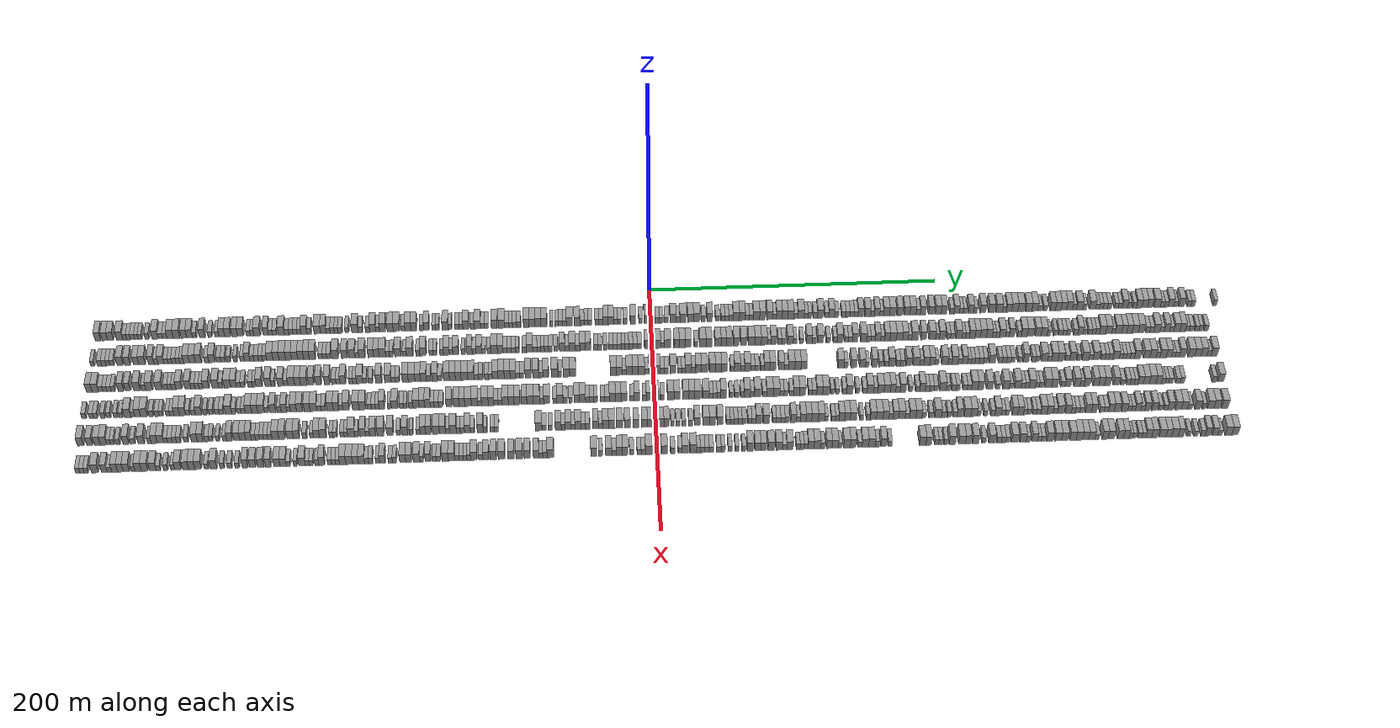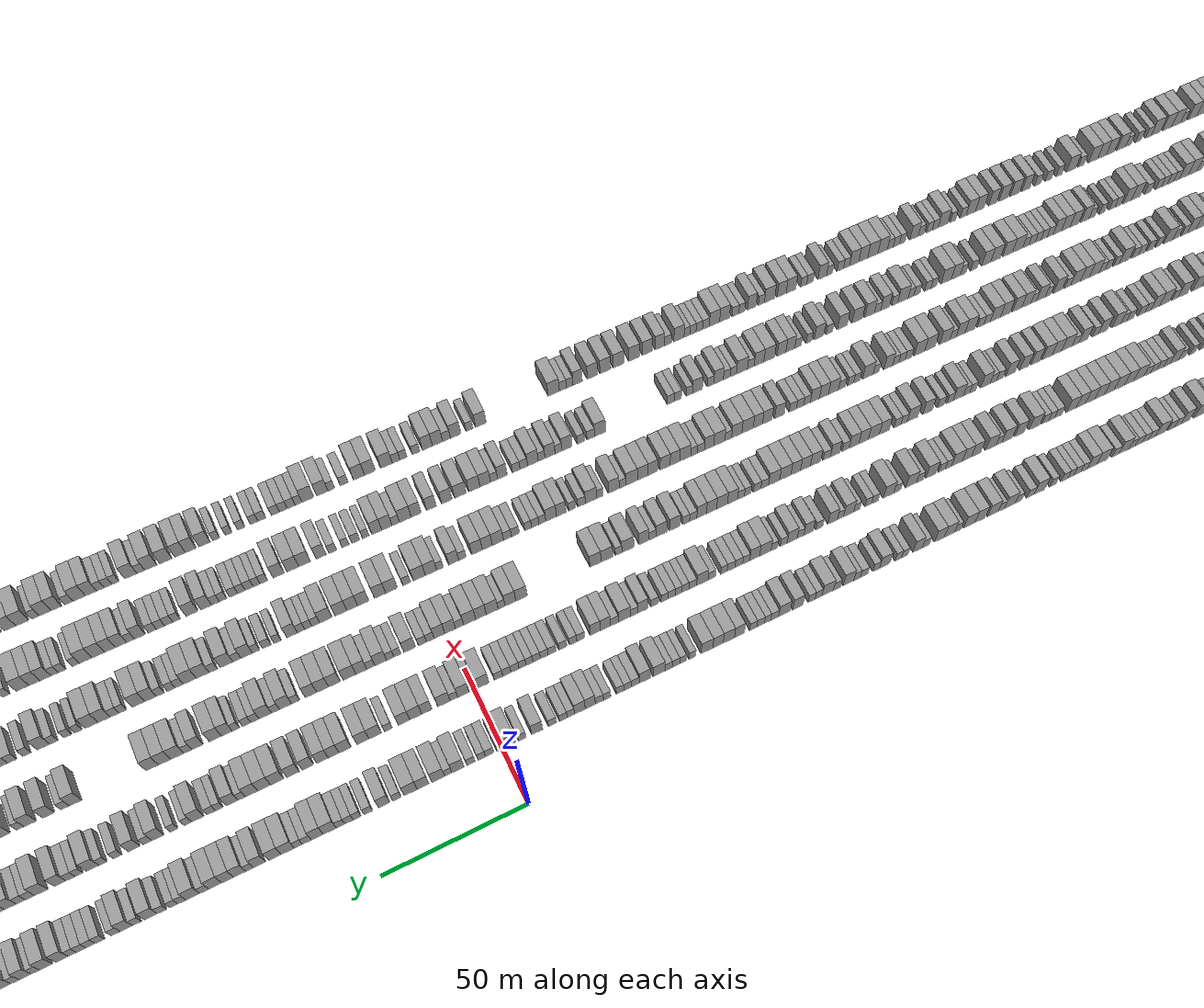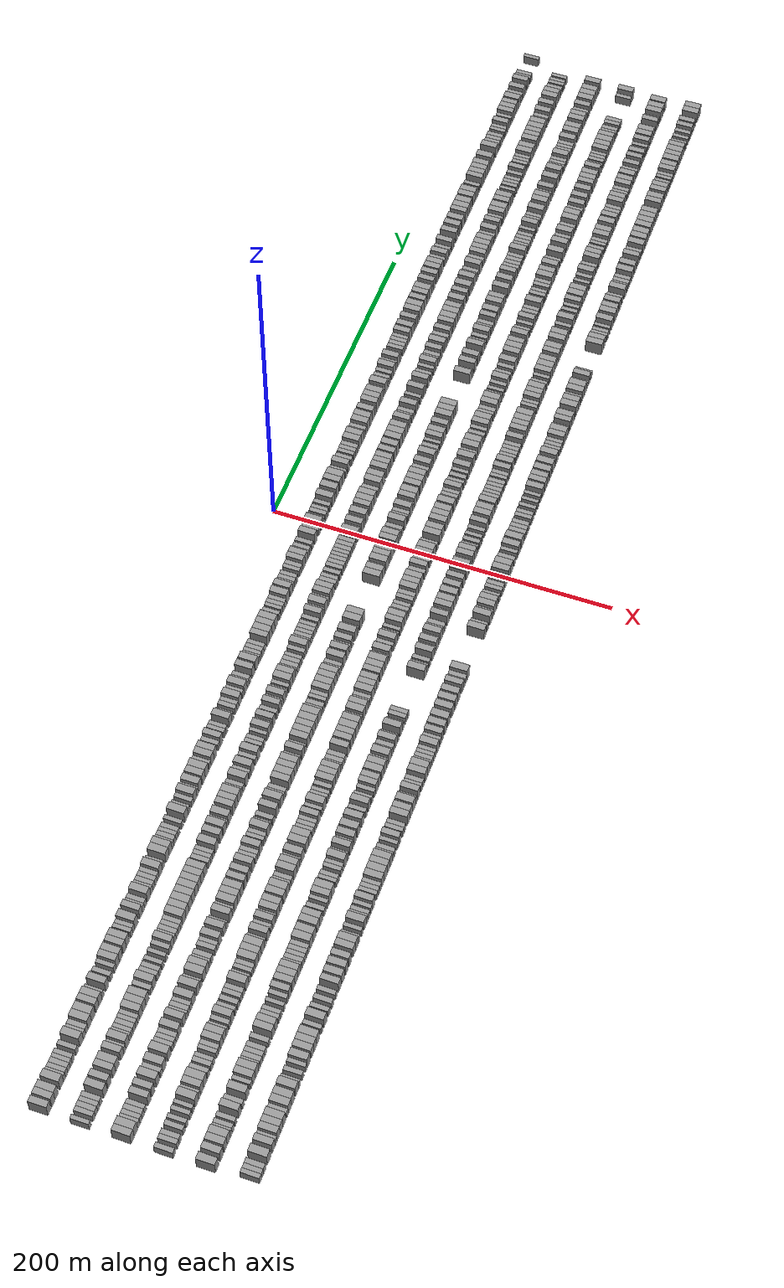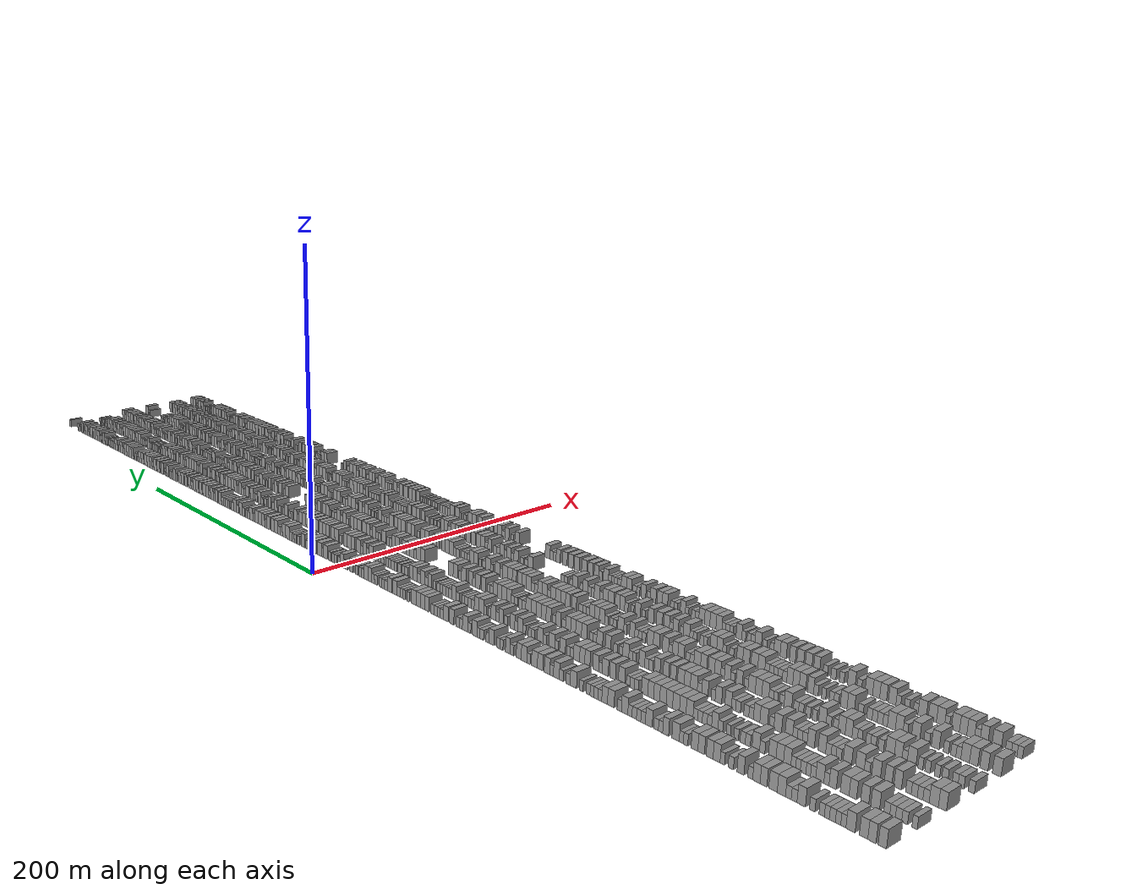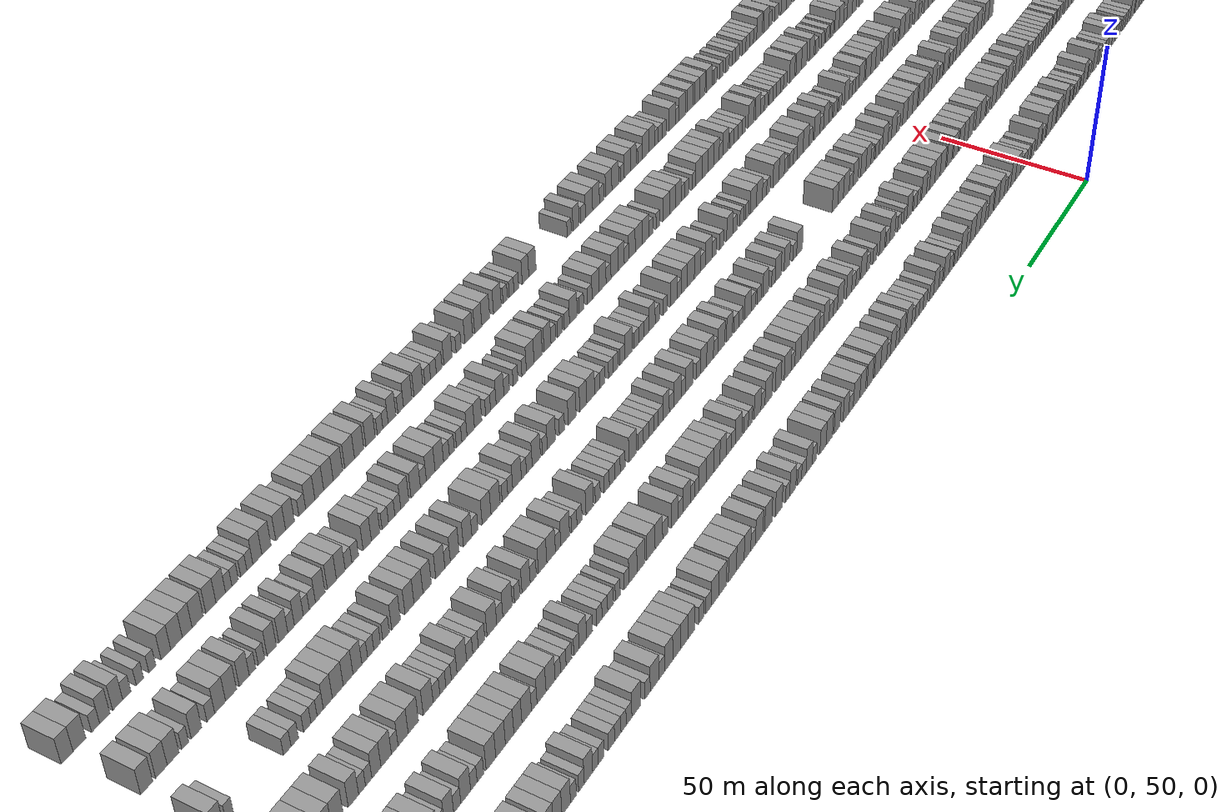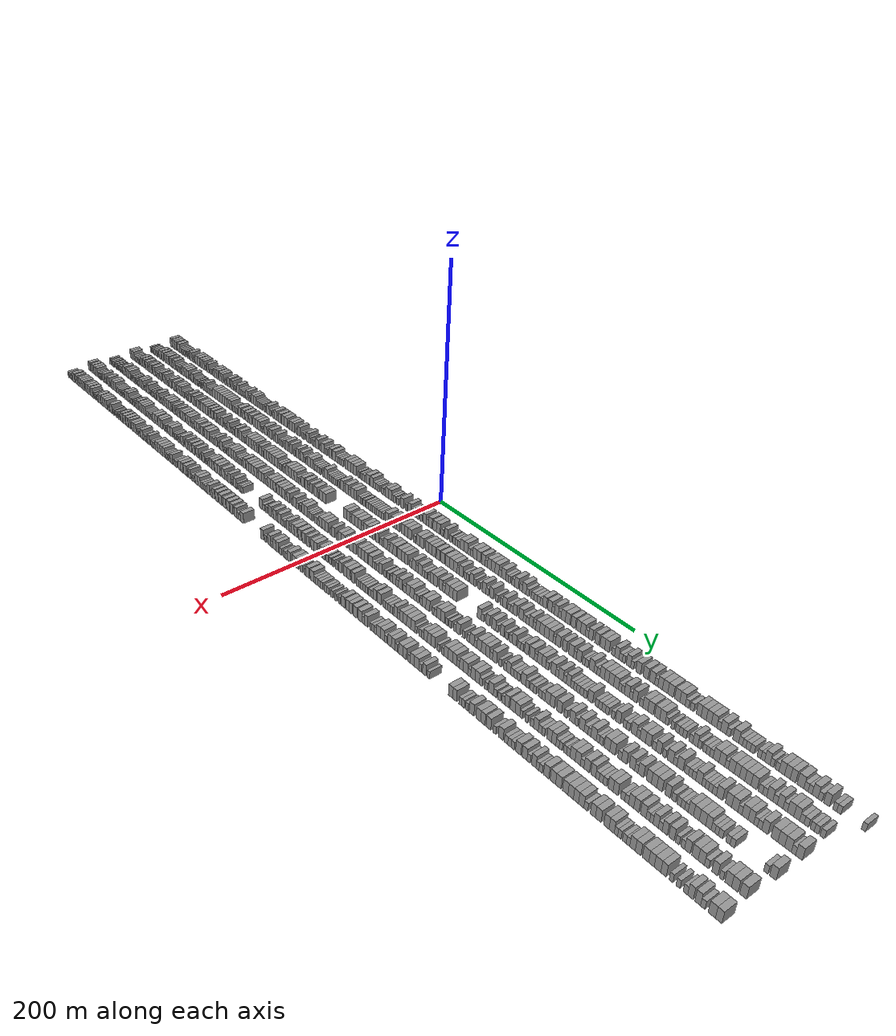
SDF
<sdf version="1.6">
 <world name="default">
  <scene>
   <sky><clouds><speed>12</speed></clouds></sky>
   <ambient>0.4 0.4 0.4 1</ambient>
   <background>0.7 0.7 0.7 1</background>
   <shadows>1</shadows>
  </scene>
  <gravity>0 0 -9.8066</gravity>
  <magnetic_field>6e-06 2.3e-05 -4.2e-05</magnetic_field>
  <physics default="0" name="default_physics" type="ode">
   <ode>
    <solver>
     <type>quick</type>
     <iters>10</iters>
     <sor>1.0</sor>
     <use_dynamic_moi_rescaling>0</use_dynamic_moi_rescaling>
    </solver>
    <constraints>
     <cfm>0</cfm>
     <erp>0.2</erp>
     <contact_max_correcting_vel>100</contact_max_correcting_vel>
     <contact_surface_layer>0.001</contact_surface_layer>
    </constraints>
   </ode>
   <max_step_size>0.004</max_step_size>
   <real_time_factor>1</real_time_factor>
   <real_time_update_rate>250</real_time_update_rate>
  </physics>
  <light name="sun" type="directional">
   <pose>0 0 10 0 0 0</pose>
   <diffuse>0.8 0.8 0.8 1</diffuse>
   <specular>0.2 0.2 0.2 1</specular>
   <attenuation>
    <range>1000</range>
    <constant>0.9</constant>
    <linear>0.01</linear>
    <quadratic>0.001</quadratic>
   </attenuation>
   <direction>-0.5 0.1 -0.9</direction>
  </light>
  <model name="building_1">
   <static>1</static>
   <pose>25.0000 -378.1062 0 0.000000 0.000000 0.000000</pose>
   <link name="link">
    <pose>0 0 4.50 0 0 0</pose>
    <collision name="collision"><geometry><box><size>10.0000 3.7875 9.0000</size></box></geometry></collision>
    <visual name="visual">
     <cast_shadows>0</cast_shadows>
     <geometry><box><size>10.0000 3.7875 9.0000</size></box></geometry>
     <material>
      <script>
       <uri>model://grey_wall/materials/scripts</uri>
       <uri>model://grey_wall/materials/textures</uri>
       <name>vrc/grey_wall</name>
      </script>
     </material>
    </visual>
   </link>
  </model>
  <model name="building_2">
   <static>1</static>
   <pose>25.0000 -373.3294 0 0.000000 0.000000 0.000000</pose>
   <link name="link">
    <pose>0 0 4.50 0 0 0</pose>
    <collision name="collision"><geometry><box><size>10.0000 3.7662 9.0000</size></box></geometry></collision>
    <visual name="visual">
     <cast_shadows>0</cast_shadows>
     <geometry><box><size>10.0000 3.7662 9.0000</size></box></geometry>
     <material>
      <script>
       <uri>model://grey_wall/materials/scripts</uri>
       <uri>model://grey_wall/materials/textures</uri>
       <name>vrc/grey_wall</name>
      </script>
     </material>
    </visual>
   </link>
  </model>
  <model name="building_3">
   <static>1</static>
   <pose>25.0000 -369.4787 0 0.000000 0.000000 0.000000</pose>
   <link name="link">
    <pose>0 0 4.50 0 0 0</pose>
    <collision name="collision"><geometry><box><size>10.0000 3.9353 9.0000</size></box></geometry></collision>
    <visual name="visual">
     <cast_shadows>0</cast_shadows>
     <geometry><box><size>10.0000 3.9353 9.0000</size></box></geometry>
     <material>
      <script>
       <uri>model://grey_wall/materials/scripts</uri>
       <uri>model://grey_wall/materials/textures</uri>
       <name>vrc/grey_wall</name>
      </script>
     </material>
    </visual>
   </link>
  </model>
  <model name="building_4">
   <static>1</static>
   <pose>25.0000 -363.3445 0 0.000000 0.000000 0.000000</pose>
   <link name="link">
    <pose>0 0 4.50 0 0 0</pose>
    <collision name="collision"><geometry><box><size>10.0000 4.3332 9.0000</size></box></geometry></collision>
    <visual name="visual">
     <cast_shadows>0</cast_shadows>
     <geometry><box><size>10.0000 4.3332 9.0000</size></box></geometry>
     <material>
      <script>
       <uri>model://grey_wall/materials/scripts</uri>
       <uri>model://grey_wall/materials/textures</uri>
       <name>vrc/grey_wall</name>
      </script>
     </material>
    </visual>
   </link>
  </model>
  <model name="building_5">
   <static>1</static>
   <pose>25.0000 -359.9219 0 0.000000 0.000000 0.000000</pose>
   <link name="link">
    <pose>0 0 3.00 0 0 0</pose>
    <collision name="collision"><geometry><box><size>10.0000 2.5119 6.0000</size></box></geometry></collision>
    <visual name="visual">
     <cast_shadows>0</cast_shadows>
     <geometry><box><size>10.0000 2.5119 6.0000</size></box></geometry>
     <material>
      <script>
       <uri>model://grey_wall/materials/scripts</uri>
       <uri>model://grey_wall/materials/textures</uri>
       <name>vrc/grey_wall</name>
      </script>
     </material>
    </visual>
   </link>
  </model>
  <model name="building_6">
   <static>1</static>
   <pose>25.0000 -357.3568 0 0.000000 0.000000 0.000000</pose>
   <link name="link">
    <pose>0 0 3.00 0 0 0</pose>
    <collision name="collision"><geometry><box><size>10.0000 2.6183 6.0000</size></box></geometry></collision>
    <visual name="visual">
     <cast_shadows>0</cast_shadows>
     <geometry><box><size>10.0000 2.6183 6.0000</size></box></geometry>
     <material>
      <script>
       <uri>model://grey_wall/materials/scripts</uri>
       <uri>model://grey_wall/materials/textures</uri>
       <name>vrc/grey_wall</name>
      </script>
     </material>
    </visual>
   </link>
  </model>
  <model name="building_7">
   <static>1</static>
   <pose>25.0000 -354.5845 0 0.000000 0.000000 0.000000</pose>
   <link name="link">
    <pose>0 0 3.00 0 0 0</pose>
    <collision name="collision"><geometry><box><size>10.0000 2.9263 6.0000</size></box></geometry></collision>
    <visual name="visual">
     <cast_shadows>0</cast_shadows>
     <geometry><box><size>10.0000 2.9263 6.0000</size></box></geometry>
     <material>
      <script>
       <uri>model://grey_wall/materials/scripts</uri>
       <uri>model://grey_wall/materials/textures</uri>
       <name>vrc/grey_wall</name>
      </script>
     </material>
    </visual>
   </link>
  </model>
  <model name="building_8">
   <static>1</static>
   <pose>25.0000 -351.9194 0 0.000000 0.000000 0.000000</pose>
   <link name="link">
    <pose>0 0 3.00 0 0 0</pose>
    <collision name="collision"><geometry><box><size>10.0000 2.4038 6.0000</size></box></geometry></collision>
    <visual name="visual">
     <cast_shadows>0</cast_shadows>
     <geometry><box><size>10.0000 2.4038 6.0000</size></box></geometry>
     <material>
      <script>
       <uri>model://grey_wall/materials/scripts</uri>
       <uri>model://grey_wall/materials/textures</uri>
       <name>vrc/grey_wall</name>
      </script>
     </material>
    </visual>
   </link>
  </model>
  <model name="building_9">
   <static>1</static>
   <pose>25.0000 -349.3949 0 0.000000 0.000000 0.000000</pose>
   <link name="link">
    <pose>0 0 3.00 0 0 0</pose>
    <collision name="collision"><geometry><box><size>10.0000 2.6452 6.0000</size></box></geometry></collision>
    <visual name="visual">
     <cast_shadows>0</cast_shadows>
     <geometry><box><size>10.0000 2.6452 6.0000</size></box></geometry>
     <material>
      <script>
       <uri>model://grey_wall/materials/scripts</uri>
       <uri>model://grey_wall/materials/textures</uri>
       <name>vrc/grey_wall</name>
      </script>
     </material>
    </visual>
   </link>
  </model>
  <model name="building_10">
   <static>1</static>
   <pose>25.0000 -344.6926 0 0.000000 0.000000 0.000000</pose>
   <link name="link">
    <pose>0 0 3.00 0 0 0</pose>
    <collision name="collision"><geometry><box><size>10.0000 2.7596 6.0000</size></box></geometry></collision>
    <visual name="visual">
     <cast_shadows>0</cast_shadows>
     <geometry><box><size>10.0000 2.7596 6.0000</size></box></geometry>
     <material>
      <script>
       <uri>model://grey_wall/materials/scripts</uri>
       <uri>model://grey_wall/materials/textures</uri>
       <name>vrc/grey_wall</name>
      </script>
     </material>
    </visual>
   </link>
  </model>
  <model name="building_11">
   <static>1</static>
   <pose>25.0000 -339.1915 0 0.000000 0.000000 0.000000</pose>
   <link name="link">
    <pose>0 0 4.50 0 0 0</pose>
    <collision name="collision"><geometry><box><size>10.0000 4.2426 9.0000</size></box></geometry></collision>
    <visual name="visual">
     <cast_shadows>0</cast_shadows>
     <geometry><box><size>10.0000 4.2426 9.0000</size></box></geometry>
     <material>
      <script>
       <uri>model://grey_wall/materials/scripts</uri>
       <uri>model://grey_wall/materials/textures</uri>
       <name>vrc/grey_wall</name>
      </script>
     </material>
    </visual>
   </link>
  </model>
  <model name="building_12">
   <static>1</static>
   <pose>25.0000 -335.5864 0 0.000000 0.000000 0.000000</pose>
   <link name="link">
    <pose>0 0 3.00 0 0 0</pose>
    <collision name="collision"><geometry><box><size>10.0000 2.9675 6.0000</size></box></geometry></collision>
    <visual name="visual">
     <cast_shadows>0</cast_shadows>
     <geometry><box><size>10.0000 2.9675 6.0000</size></box></geometry>
     <material>
      <script>
       <uri>model://grey_wall/materials/scripts</uri>
       <uri>model://grey_wall/materials/textures</uri>
       <name>vrc/grey_wall</name>
      </script>
     </material>
    </visual>
   </link>
  </model>
  <model name="building_13">
   <static>1</static>
   <pose>25.0000 -332.6247 0 0.000000 0.000000 0.000000</pose>
   <link name="link">
    <pose>0 0 3.00 0 0 0</pose>
    <collision name="collision"><geometry><box><size>10.0000 2.9561 6.0000</size></box></geometry></collision>
    <visual name="visual">
     <cast_shadows>0</cast_shadows>
     <geometry><box><size>10.0000 2.9561 6.0000</size></box></geometry>
     <material>
      <script>
       <uri>model://grey_wall/materials/scripts</uri>
       <uri>model://grey_wall/materials/textures</uri>
       <name>vrc/grey_wall</name>
      </script>
     </material>
    </visual>
   </link>
  </model>
  <model name="building_14">
   <static>1</static>
   <pose>25.0000 -328.9970 0 0.000000 0.000000 0.000000</pose>
   <link name="link">
    <pose>0 0 4.50 0 0 0</pose>
    <collision name="collision"><geometry><box><size>10.0000 4.2992 9.0000</size></box></geometry></collision>
    <visual name="visual">
     <cast_shadows>0</cast_shadows>
     <geometry><box><size>10.0000 4.2992 9.0000</size></box></geometry>
     <material>
      <script>
       <uri>model://grey_wall/materials/scripts</uri>
       <uri>model://grey_wall/materials/textures</uri>
       <name>vrc/grey_wall</name>
      </script>
     </material>
    </visual>
   </link>
  </model>
  <model name="building_15">
   <static>1</static>
   <pose>25.0000 -324.6492 0 0.000000 0.000000 0.000000</pose>
   <link name="link">
    <pose>0 0 4.50 0 0 0</pose>
    <collision name="collision"><geometry><box><size>10.0000 4.3964 9.0000</size></box></geometry></collision>
    <visual name="visual">
     <cast_shadows>0</cast_shadows>
     <geometry><box><size>10.0000 4.3964 9.0000</size></box></geometry>
     <material>
      <script>
       <uri>model://grey_wall/materials/scripts</uri>
       <uri>model://grey_wall/materials/textures</uri>
       <name>vrc/grey_wall</name>
      </script>
     </material>
    </visual>
   </link>
  </model>
  <model name="building_16">
   <static>1</static>
   <pose>25.0000 -319.6189 0 0.000000 0.000000 0.000000</pose>
   <link name="link">
    <pose>0 0 4.50 0 0 0</pose>
    <collision name="collision"><geometry><box><size>10.0000 3.6643 9.0000</size></box></geometry></collision>
    <visual name="visual">
     <cast_shadows>0</cast_shadows>
     <geometry><box><size>10.0000 3.6643 9.0000</size></box></geometry>
     <material>
      <script>
       <uri>model://grey_wall/materials/scripts</uri>
       <uri>model://grey_wall/materials/textures</uri>
       <name>vrc/grey_wall</name>
      </script>
     </material>
    </visual>
   </link>
  </model>
  <model name="building_17">
   <static>1</static>
   <pose>25.0000 -315.7934 0 0.000000 0.000000 0.000000</pose>
   <link name="link">
    <pose>0 0 4.50 0 0 0</pose>
    <collision name="collision"><geometry><box><size>10.0000 3.9866 9.0000</size></box></geometry></collision>
    <visual name="visual">
     <cast_shadows>0</cast_shadows>
     <geometry><box><size>10.0000 3.9866 9.0000</size></box></geometry>
     <material>
      <script>
       <uri>model://grey_wall/materials/scripts</uri>
       <uri>model://grey_wall/materials/textures</uri>
       <name>vrc/grey_wall</name>
      </script>
     </material>
    </visual>
   </link>
  </model>
  <model name="building_18">
   <static>1</static>
   <pose>25.0000 -312.4420 0 0.000000 0.000000 0.000000</pose>
   <link name="link">
    <pose>0 0 3.00 0 0 0</pose>
    <collision name="collision"><geometry><box><size>10.0000 2.7161 6.0000</size></box></geometry></collision>
    <visual name="visual">
     <cast_shadows>0</cast_shadows>
     <geometry><box><size>10.0000 2.7161 6.0000</size></box></geometry>
     <material>
      <script>
       <uri>model://grey_wall/materials/scripts</uri>
       <uri>model://grey_wall/materials/textures</uri>
       <name>vrc/grey_wall</name>
      </script>
     </material>
    </visual>
   </link>
  </model>
  <model name="building_19">
   <static>1</static>
   <pose>25.0000 -307.1703 0 0.000000 0.000000 0.000000</pose>
   <link name="link">
    <pose>0 0 4.50 0 0 0</pose>
    <collision name="collision"><geometry><box><size>10.0000 3.8274 9.0000</size></box></geometry></collision>
    <visual name="visual">
     <cast_shadows>0</cast_shadows>
     <geometry><box><size>10.0000 3.8274 9.0000</size></box></geometry>
     <material>
      <script>
       <uri>model://grey_wall/materials/scripts</uri>
       <uri>model://grey_wall/materials/textures</uri>
       <name>vrc/grey_wall</name>
      </script>
     </material>
    </visual>
   </link>
  </model>
  <model name="building_20">
   <static>1</static>
   <pose>25.0000 -301.7910 0 0.000000 0.000000 0.000000</pose>
   <link name="link">
    <pose>0 0 3.00 0 0 0</pose>
    <collision name="collision"><geometry><box><size>10.0000 2.9312 6.0000</size></box></geometry></collision>
    <visual name="visual">
     <cast_shadows>0</cast_shadows>
     <geometry><box><size>10.0000 2.9312 6.0000</size></box></geometry>
     <material>
      <script>
       <uri>model://grey_wall/materials/scripts</uri>
       <uri>model://grey_wall/materials/textures</uri>
       <name>vrc/grey_wall</name>
      </script>
     </material>
    </visual>
   </link>
  </model>
  <model name="building_21">
   <static>1</static>
   <pose>25.0000 -297.0417 0 0.000000 0.000000 0.000000</pose>
   <link name="link">
    <pose>0 0 3.00 0 0 0</pose>
    <collision name="collision"><geometry><box><size>10.0000 2.5674 6.0000</size></box></geometry></collision>
    <visual name="visual">
     <cast_shadows>0</cast_shadows>
     <geometry><box><size>10.0000 2.5674 6.0000</size></box></geometry>
     <material>
      <script>
       <uri>model://grey_wall/materials/scripts</uri>
       <uri>model://grey_wall/materials/textures</uri>
       <name>vrc/grey_wall</name>
      </script>
     </material>
    </visual>
   </link>
  </model>
  <model name="building_22">
   <static>1</static>
   <pose>25.0000 -293.7621 0 0.000000 0.000000 0.000000</pose>
   <link name="link">
    <pose>0 0 4.50 0 0 0</pose>
    <collision name="collision"><geometry><box><size>10.0000 3.9918 9.0000</size></box></geometry></collision>
    <visual name="visual">
     <cast_shadows>0</cast_shadows>
     <geometry><box><size>10.0000 3.9918 9.0000</size></box></geometry>
     <material>
      <script>
       <uri>model://grey_wall/materials/scripts</uri>
       <uri>model://grey_wall/materials/textures</uri>
       <name>vrc/grey_wall</name>
      </script>
     </material>
    </visual>
   </link>
  </model>
  <model name="building_23">
   <static>1</static>
   <pose>25.0000 -289.7860 0 0.000000 0.000000 0.000000</pose>
   <link name="link">
    <pose>0 0 4.50 0 0 0</pose>
    <collision name="collision"><geometry><box><size>10.0000 3.9604 9.0000</size></box></geometry></collision>
    <visual name="visual">
     <cast_shadows>0</cast_shadows>
     <geometry><box><size>10.0000 3.9604 9.0000</size></box></geometry>
     <material>
      <script>
       <uri>model://grey_wall/materials/scripts</uri>
       <uri>model://grey_wall/materials/textures</uri>
       <name>vrc/grey_wall</name>
      </script>
     </material>
    </visual>
   </link>
  </model>
  <model name="building_24">
   <static>1</static>
   <pose>25.0000 -284.8868 0 0.000000 0.000000 0.000000</pose>
   <link name="link">
    <pose>0 0 4.50 0 0 0</pose>
    <collision name="collision"><geometry><box><size>10.0000 3.8381 9.0000</size></box></geometry></collision>
    <visual name="visual">
     <cast_shadows>0</cast_shadows>
     <geometry><box><size>10.0000 3.8381 9.0000</size></box></geometry>
     <material>
      <script>
       <uri>model://grey_wall/materials/scripts</uri>
       <uri>model://grey_wall/materials/textures</uri>
       <name>vrc/grey_wall</name>
      </script>
     </material>
    </visual>
   </link>
  </model>
  <model name="building_25">
   <static>1</static>
   <pose>25.0000 -280.9960 0 0.000000 0.000000 0.000000</pose>
   <link name="link">
    <pose>0 0 4.50 0 0 0</pose>
    <collision name="collision"><geometry><box><size>10.0000 3.9435 9.0000</size></box></geometry></collision>
    <visual name="visual">
     <cast_shadows>0</cast_shadows>
     <geometry><box><size>10.0000 3.9435 9.0000</size></box></geometry>
     <material>
      <script>
       <uri>model://grey_wall/materials/scripts</uri>
       <uri>model://grey_wall/materials/textures</uri>
       <name>vrc/grey_wall</name>
      </script>
     </material>
    </visual>
   </link>
  </model>
  <model name="building_26">
   <static>1</static>
   <pose>25.0000 -275.7177 0 0.000000 0.000000 0.000000</pose>
   <link name="link">
    <pose>0 0 3.00 0 0 0</pose>
    <collision name="collision"><geometry><box><size>10.0000 2.6130 6.0000</size></box></geometry></collision>
    <visual name="visual">
     <cast_shadows>0</cast_shadows>
     <geometry><box><size>10.0000 2.6130 6.0000</size></box></geometry>
     <material>
      <script>
       <uri>model://grey_wall/materials/scripts</uri>
       <uri>model://grey_wall/materials/textures</uri>
       <name>vrc/grey_wall</name>
      </script>
     </material>
    </visual>
   </link>
  </model>
  <model name="building_27">
   <static>1</static>
   <pose>25.0000 -273.1705 0 0.000000 0.000000 0.000000</pose>
   <link name="link">
    <pose>0 0 3.00 0 0 0</pose>
    <collision name="collision"><geometry><box><size>10.0000 2.4816 6.0000</size></box></geometry></collision>
    <visual name="visual">
     <cast_shadows>0</cast_shadows>
     <geometry><box><size>10.0000 2.4816 6.0000</size></box></geometry>
     <material>
      <script>
       <uri>model://grey_wall/materials/scripts</uri>
       <uri>model://grey_wall/materials/textures</uri>
       <name>vrc/grey_wall</name>
      </script>
     </material>
    </visual>
   </link>
  </model>
  <model name="building_28">
   <static>1</static>
   <pose>25.0000 -269.7255 0 0.000000 0.000000 0.000000</pose>
   <link name="link">
    <pose>0 0 4.50 0 0 0</pose>
    <collision name="collision"><geometry><box><size>10.0000 4.4084 9.0000</size></box></geometry></collision>
    <visual name="visual">
     <cast_shadows>0</cast_shadows>
     <geometry><box><size>10.0000 4.4084 9.0000</size></box></geometry>
     <material>
      <script>
       <uri>model://grey_wall/materials/scripts</uri>
       <uri>model://grey_wall/materials/textures</uri>
       <name>vrc/grey_wall</name>
      </script>
     </material>
    </visual>
   </link>
  </model>
  <model name="building_29">
   <static>1</static>
   <pose>25.0000 -263.7133 0 0.000000 0.000000 0.000000</pose>
   <link name="link">
    <pose>0 0 4.50 0 0 0</pose>
    <collision name="collision"><geometry><box><size>10.0000 3.6160 9.0000</size></box></geometry></collision>
    <visual name="visual">
     <cast_shadows>0</cast_shadows>
     <geometry><box><size>10.0000 3.6160 9.0000</size></box></geometry>
     <material>
      <script>
       <uri>model://grey_wall/materials/scripts</uri>
       <uri>model://grey_wall/materials/textures</uri>
       <name>vrc/grey_wall</name>
      </script>
     </material>
    </visual>
   </link>
  </model>
  <model name="building_30">
   <static>1</static>
   <pose>25.0000 -260.5666 0 0.000000 0.000000 0.000000</pose>
   <link name="link">
    <pose>0 0 3.00 0 0 0</pose>
    <collision name="collision"><geometry><box><size>10.0000 2.6774 6.0000</size></box></geometry></collision>
    <visual name="visual">
     <cast_shadows>0</cast_shadows>
     <geometry><box><size>10.0000 2.6774 6.0000</size></box></geometry>
     <material>
      <script>
       <uri>model://grey_wall/materials/scripts</uri>
       <uri>model://grey_wall/materials/textures</uri>
       <name>vrc/grey_wall</name>
      </script>
     </material>
    </visual>
   </link>
  </model>
  <model name="building_31">
   <static>1</static>
   <pose>25.0000 -257.7888 0 0.000000 0.000000 0.000000</pose>
   <link name="link">
    <pose>0 0 3.00 0 0 0</pose>
    <collision name="collision"><geometry><box><size>10.0000 2.8781 6.0000</size></box></geometry></collision>
    <visual name="visual">
     <cast_shadows>0</cast_shadows>
     <geometry><box><size>10.0000 2.8781 6.0000</size></box></geometry>
     <material>
      <script>
       <uri>model://grey_wall/materials/scripts</uri>
       <uri>model://grey_wall/materials/textures</uri>
       <name>vrc/grey_wall</name>
      </script>
     </material>
    </visual>
   </link>
  </model>
  <model name="building_32">
   <static>1</static>
   <pose>25.0000 -253.1978 0 0.000000 0.000000 0.000000</pose>
   <link name="link">
    <pose>0 0 4.50 0 0 0</pose>
    <collision name="collision"><geometry><box><size>10.0000 4.3039 9.0000</size></box></geometry></collision>
    <visual name="visual">
     <cast_shadows>0</cast_shadows>
     <geometry><box><size>10.0000 4.3039 9.0000</size></box></geometry>
     <material>
      <script>
       <uri>model://grey_wall/materials/scripts</uri>
       <uri>model://grey_wall/materials/textures</uri>
       <name>vrc/grey_wall</name>
      </script>
     </material>
    </visual>
   </link>
  </model>
  <model name="building_33">
   <static>1</static>
   <pose>25.0000 -249.5986 0 0.000000 0.000000 0.000000</pose>
   <link name="link">
    <pose>0 0 3.00 0 0 0</pose>
    <collision name="collision"><geometry><box><size>10.0000 2.8944 6.0000</size></box></geometry></collision>
    <visual name="visual">
     <cast_shadows>0</cast_shadows>
     <geometry><box><size>10.0000 2.8944 6.0000</size></box></geometry>
     <material>
      <script>
       <uri>model://grey_wall/materials/scripts</uri>
       <uri>model://grey_wall/materials/textures</uri>
       <name>vrc/grey_wall</name>
      </script>
     </material>
    </visual>
   </link>
  </model>
  <model name="building_34">
   <static>1</static>
   <pose>25.0000 -246.7691 0 0.000000 0.000000 0.000000</pose>
   <link name="link">
    <pose>0 0 3.00 0 0 0</pose>
    <collision name="collision"><geometry><box><size>10.0000 2.7646 6.0000</size></box></geometry></collision>
    <visual name="visual">
     <cast_shadows>0</cast_shadows>
     <geometry><box><size>10.0000 2.7646 6.0000</size></box></geometry>
     <material>
      <script>
       <uri>model://grey_wall/materials/scripts</uri>
       <uri>model://grey_wall/materials/textures</uri>
       <name>vrc/grey_wall</name>
      </script>
     </material>
    </visual>
   </link>
  </model>
  <model name="building_35">
   <static>1</static>
   <pose>25.0000 -243.9515 0 0.000000 0.000000 0.000000</pose>
   <link name="link">
    <pose>0 0 3.00 0 0 0</pose>
    <collision name="collision"><geometry><box><size>10.0000 2.8706 6.0000</size></box></geometry></collision>
    <visual name="visual">
     <cast_shadows>0</cast_shadows>
     <geometry><box><size>10.0000 2.8706 6.0000</size></box></geometry>
     <material>
      <script>
       <uri>model://grey_wall/materials/scripts</uri>
       <uri>model://grey_wall/materials/textures</uri>
       <name>vrc/grey_wall</name>
      </script>
     </material>
    </visual>
   </link>
  </model>
  <model name="building_36">
   <static>1</static>
   <pose>25.0000 -241.1703 0 0.000000 0.000000 0.000000</pose>
   <link name="link">
    <pose>0 0 3.00 0 0 0</pose>
    <collision name="collision"><geometry><box><size>10.0000 2.6919 6.0000</size></box></geometry></collision>
    <visual name="visual">
     <cast_shadows>0</cast_shadows>
     <geometry><box><size>10.0000 2.6919 6.0000</size></box></geometry>
     <material>
      <script>
       <uri>model://grey_wall/materials/scripts</uri>
       <uri>model://grey_wall/materials/textures</uri>
       <name>vrc/grey_wall</name>
      </script>
     </material>
    </visual>
   </link>
  </model>
  <model name="building_37">
   <static>1</static>
   <pose>25.0000 -237.7380 0 0.000000 0.000000 0.000000</pose>
   <link name="link">
    <pose>0 0 4.50 0 0 0</pose>
    <collision name="collision"><geometry><box><size>10.0000 4.1728 9.0000</size></box></geometry></collision>
    <visual name="visual">
     <cast_shadows>0</cast_shadows>
     <geometry><box><size>10.0000 4.1728 9.0000</size></box></geometry>
     <material>
      <script>
       <uri>model://grey_wall/materials/scripts</uri>
       <uri>model://grey_wall/materials/textures</uri>
       <name>vrc/grey_wall</name>
      </script>
     </material>
    </visual>
   </link>
  </model>
  <model name="building_38">
   <static>1</static>
   <pose>25.0000 -234.2288 0 0.000000 0.000000 0.000000</pose>
   <link name="link">
    <pose>0 0 3.00 0 0 0</pose>
    <collision name="collision"><geometry><box><size>10.0000 2.8456 6.0000</size></box></geometry></collision>
    <visual name="visual">
     <cast_shadows>0</cast_shadows>
     <geometry><box><size>10.0000 2.8456 6.0000</size></box></geometry>
     <material>
      <script>
       <uri>model://grey_wall/materials/scripts</uri>
       <uri>model://grey_wall/materials/textures</uri>
       <name>vrc/grey_wall</name>
      </script>
     </material>
    </visual>
   </link>
  </model>
  <model name="building_39">
   <static>1</static>
   <pose>25.0000 -228.5989 0 0.000000 0.000000 0.000000</pose>
   <link name="link">
    <pose>0 0 4.50 0 0 0</pose>
    <collision name="collision"><geometry><box><size>10.0000 4.4142 9.0000</size></box></geometry></collision>
    <visual name="visual">
     <cast_shadows>0</cast_shadows>
     <geometry><box><size>10.0000 4.4142 9.0000</size></box></geometry>
     <material>
      <script>
       <uri>model://grey_wall/materials/scripts</uri>
       <uri>model://grey_wall/materials/textures</uri>
       <name>vrc/grey_wall</name>
      </script>
     </material>
    </visual>
   </link>
  </model>
  <model name="building_40">
   <static>1</static>
   <pose>25.0000 -224.4616 0 0.000000 0.000000 0.000000</pose>
   <link name="link">
    <pose>0 0 4.50 0 0 0</pose>
    <collision name="collision"><geometry><box><size>10.0000 3.8603 9.0000</size></box></geometry></collision>
    <visual name="visual">
     <cast_shadows>0</cast_shadows>
     <geometry><box><size>10.0000 3.8603 9.0000</size></box></geometry>
     <material>
      <script>
       <uri>model://grey_wall/materials/scripts</uri>
       <uri>model://grey_wall/materials/textures</uri>
       <name>vrc/grey_wall</name>
      </script>
     </material>
    </visual>
   </link>
  </model>
  <model name="building_41">
   <static>1</static>
   <pose>25.0000 -221.1838 0 0.000000 0.000000 0.000000</pose>
   <link name="link">
    <pose>0 0 3.00 0 0 0</pose>
    <collision name="collision"><geometry><box><size>10.0000 2.6952 6.0000</size></box></geometry></collision>
    <visual name="visual">
     <cast_shadows>0</cast_shadows>
     <geometry><box><size>10.0000 2.6952 6.0000</size></box></geometry>
     <material>
      <script>
       <uri>model://grey_wall/materials/scripts</uri>
       <uri>model://grey_wall/materials/textures</uri>
       <name>vrc/grey_wall</name>
      </script>
     </material>
    </visual>
   </link>
  </model>
  <model name="building_42">
   <static>1</static>
   <pose>25.0000 -218.4141 0 0.000000 0.000000 0.000000</pose>
   <link name="link">
    <pose>0 0 3.00 0 0 0</pose>
    <collision name="collision"><geometry><box><size>10.0000 2.8441 6.0000</size></box></geometry></collision>
    <visual name="visual">
     <cast_shadows>0</cast_shadows>
     <geometry><box><size>10.0000 2.8441 6.0000</size></box></geometry>
     <material>
      <script>
       <uri>model://grey_wall/materials/scripts</uri>
       <uri>model://grey_wall/materials/textures</uri>
       <name>vrc/grey_wall</name>
      </script>
     </material>
    </visual>
   </link>
  </model>
  <model name="building_43">
   <static>1</static>
   <pose>25.0000 -215.7694 0 0.000000 0.000000 0.000000</pose>
   <link name="link">
    <pose>0 0 3.00 0 0 0</pose>
    <collision name="collision"><geometry><box><size>10.0000 2.4454 6.0000</size></box></geometry></collision>
    <visual name="visual">
     <cast_shadows>0</cast_shadows>
     <geometry><box><size>10.0000 2.4454 6.0000</size></box></geometry>
     <material>
      <script>
       <uri>model://grey_wall/materials/scripts</uri>
       <uri>model://grey_wall/materials/textures</uri>
       <name>vrc/grey_wall</name>
      </script>
     </material>
    </visual>
   </link>
  </model>
  <model name="building_44">
   <static>1</static>
   <pose>25.0000 -213.1386 0 0.000000 0.000000 0.000000</pose>
   <link name="link">
    <pose>0 0 3.00 0 0 0</pose>
    <collision name="collision"><geometry><box><size>10.0000 2.8161 6.0000</size></box></geometry></collision>
    <visual name="visual">
     <cast_shadows>0</cast_shadows>
     <geometry><box><size>10.0000 2.8161 6.0000</size></box></geometry>
     <material>
      <script>
       <uri>model://grey_wall/materials/scripts</uri>
       <uri>model://grey_wall/materials/textures</uri>
       <name>vrc/grey_wall</name>
      </script>
     </material>
    </visual>
   </link>
  </model>
  <model name="building_45">
   <static>1</static>
   <pose>25.0000 -208.4304 0 0.000000 0.000000 0.000000</pose>
   <link name="link">
    <pose>0 0 3.00 0 0 0</pose>
    <collision name="collision"><geometry><box><size>10.0000 2.6004 6.0000</size></box></geometry></collision>
    <visual name="visual">
     <cast_shadows>0</cast_shadows>
     <geometry><box><size>10.0000 2.6004 6.0000</size></box></geometry>
     <material>
      <script>
       <uri>model://grey_wall/materials/scripts</uri>
       <uri>model://grey_wall/materials/textures</uri>
       <name>vrc/grey_wall</name>
      </script>
     </material>
    </visual>
   </link>
  </model>
  <model name="building_46">
   <static>1</static>
   <pose>25.0000 -202.8944 0 0.000000 0.000000 0.000000</pose>
   <link name="link">
    <pose>0 0 4.50 0 0 0</pose>
    <collision name="collision"><geometry><box><size>10.0000 4.4716 9.0000</size></box></geometry></collision>
    <visual name="visual">
     <cast_shadows>0</cast_shadows>
     <geometry><box><size>10.0000 4.4716 9.0000</size></box></geometry>
     <material>
      <script>
       <uri>model://grey_wall/materials/scripts</uri>
       <uri>model://grey_wall/materials/textures</uri>
       <name>vrc/grey_wall</name>
      </script>
     </material>
    </visual>
   </link>
  </model>
  <model name="building_47">
   <static>1</static>
   <pose>25.0000 -199.1657 0 0.000000 0.000000 0.000000</pose>
   <link name="link">
    <pose>0 0 3.00 0 0 0</pose>
    <collision name="collision"><geometry><box><size>10.0000 2.9857 6.0000</size></box></geometry></collision>
    <visual name="visual">
     <cast_shadows>0</cast_shadows>
     <geometry><box><size>10.0000 2.9857 6.0000</size></box></geometry>
     <material>
      <script>
       <uri>model://grey_wall/materials/scripts</uri>
       <uri>model://grey_wall/materials/textures</uri>
       <name>vrc/grey_wall</name>
      </script>
     </material>
    </visual>
   </link>
  </model>
  <model name="building_48">
   <static>1</static>
   <pose>25.0000 -194.2675 0 0.000000 0.000000 0.000000</pose>
   <link name="link">
    <pose>0 0 3.00 0 0 0</pose>
    <collision name="collision"><geometry><box><size>10.0000 2.8106 6.0000</size></box></geometry></collision>
    <visual name="visual">
     <cast_shadows>0</cast_shadows>
     <geometry><box><size>10.0000 2.8106 6.0000</size></box></geometry>
     <material>
      <script>
       <uri>model://grey_wall/materials/scripts</uri>
       <uri>model://grey_wall/materials/textures</uri>
       <name>vrc/grey_wall</name>
      </script>
     </material>
    </visual>
   </link>
  </model>
  <model name="building_49">
   <static>1</static>
   <pose>25.0000 -190.7488 0 0.000000 0.000000 0.000000</pose>
   <link name="link">
    <pose>0 0 4.50 0 0 0</pose>
    <collision name="collision"><geometry><box><size>10.0000 4.2268 9.0000</size></box></geometry></collision>
    <visual name="visual">
     <cast_shadows>0</cast_shadows>
     <geometry><box><size>10.0000 4.2268 9.0000</size></box></geometry>
     <material>
      <script>
       <uri>model://grey_wall/materials/scripts</uri>
       <uri>model://grey_wall/materials/textures</uri>
       <name>vrc/grey_wall</name>
      </script>
     </material>
    </visual>
   </link>
  </model>
  <model name="building_50">
   <static>1</static>
   <pose>25.0000 -187.3405 0 0.000000 0.000000 0.000000</pose>
   <link name="link">
    <pose>0 0 3.00 0 0 0</pose>
    <collision name="collision"><geometry><box><size>10.0000 2.5898 6.0000</size></box></geometry></collision>
    <visual name="visual">
     <cast_shadows>0</cast_shadows>
     <geometry><box><size>10.0000 2.5898 6.0000</size></box></geometry>
     <material>
      <script>
       <uri>model://grey_wall/materials/scripts</uri>
       <uri>model://grey_wall/materials/textures</uri>
       <name>vrc/grey_wall</name>
      </script>
     </material>
    </visual>
   </link>
  </model>
  <model name="building_51">
   <static>1</static>
   <pose>25.0000 -183.9732 0 0.000000 0.000000 0.000000</pose>
   <link name="link">
    <pose>0 0 4.50 0 0 0</pose>
    <collision name="collision"><geometry><box><size>10.0000 4.1448 9.0000</size></box></geometry></collision>
    <visual name="visual">
     <cast_shadows>0</cast_shadows>
     <geometry><box><size>10.0000 4.1448 9.0000</size></box></geometry>
     <material>
      <script>
       <uri>model://grey_wall/materials/scripts</uri>
       <uri>model://grey_wall/materials/textures</uri>
       <name>vrc/grey_wall</name>
      </script>
     </material>
    </visual>
   </link>
  </model>
  <model name="building_52">
   <static>1</static>
   <pose>25.0000 -178.8292 0 0.000000 0.000000 0.000000</pose>
   <link name="link">
    <pose>0 0 4.50 0 0 0</pose>
    <collision name="collision"><geometry><box><size>10.0000 4.1430 9.0000</size></box></geometry></collision>
    <visual name="visual">
     <cast_shadows>0</cast_shadows>
     <geometry><box><size>10.0000 4.1430 9.0000</size></box></geometry>
     <material>
      <script>
       <uri>model://grey_wall/materials/scripts</uri>
       <uri>model://grey_wall/materials/textures</uri>
       <name>vrc/grey_wall</name>
      </script>
     </material>
    </visual>
   </link>
  </model>
  <model name="building_53">
   <static>1</static>
   <pose>25.0000 -174.5277 0 0.000000 0.000000 0.000000</pose>
   <link name="link">
    <pose>0 0 4.50 0 0 0</pose>
    <collision name="collision"><geometry><box><size>10.0000 4.4599 9.0000</size></box></geometry></collision>
    <visual name="visual">
     <cast_shadows>0</cast_shadows>
     <geometry><box><size>10.0000 4.4599 9.0000</size></box></geometry>
     <material>
      <script>
       <uri>model://grey_wall/materials/scripts</uri>
       <uri>model://grey_wall/materials/textures</uri>
       <name>vrc/grey_wall</name>
      </script>
     </material>
    </visual>
   </link>
  </model>
  <model name="building_54">
   <static>1</static>
   <pose>25.0000 -169.9926 0 0.000000 0.000000 0.000000</pose>
   <link name="link">
    <pose>0 0 3.00 0 0 0</pose>
    <collision name="collision"><geometry><box><size>10.0000 2.6104 6.0000</size></box></geometry></collision>
    <visual name="visual">
     <cast_shadows>0</cast_shadows>
     <geometry><box><size>10.0000 2.6104 6.0000</size></box></geometry>
     <material>
      <script>
       <uri>model://grey_wall/materials/scripts</uri>
       <uri>model://grey_wall/materials/textures</uri>
       <name>vrc/grey_wall</name>
      </script>
     </material>
    </visual>
   </link>
  </model>
  <model name="building_55">
   <static>1</static>
   <pose>25.0000 -166.6092 0 0.000000 0.000000 0.000000</pose>
   <link name="link">
    <pose>0 0 4.50 0 0 0</pose>
    <collision name="collision"><geometry><box><size>10.0000 4.1563 9.0000</size></box></geometry></collision>
    <visual name="visual">
     <cast_shadows>0</cast_shadows>
     <geometry><box><size>10.0000 4.1563 9.0000</size></box></geometry>
     <material>
      <script>
       <uri>model://grey_wall/materials/scripts</uri>
       <uri>model://grey_wall/materials/textures</uri>
       <name>vrc/grey_wall</name>
      </script>
     </material>
    </visual>
   </link>
  </model>
  <model name="building_56">
   <static>1</static>
   <pose>25.0000 -162.6139 0 0.000000 0.000000 0.000000</pose>
   <link name="link">
    <pose>0 0 4.50 0 0 0</pose>
    <collision name="collision"><geometry><box><size>10.0000 3.8343 9.0000</size></box></geometry></collision>
    <visual name="visual">
     <cast_shadows>0</cast_shadows>
     <geometry><box><size>10.0000 3.8343 9.0000</size></box></geometry>
     <material>
      <script>
       <uri>model://grey_wall/materials/scripts</uri>
       <uri>model://grey_wall/materials/textures</uri>
       <name>vrc/grey_wall</name>
      </script>
     </material>
    </visual>
   </link>
  </model>
  <model name="building_57">
   <static>1</static>
   <pose>25.0000 -157.2575 0 0.000000 0.000000 0.000000</pose>
   <link name="link">
    <pose>0 0 3.00 0 0 0</pose>
    <collision name="collision"><geometry><box><size>10.0000 2.8785 6.0000</size></box></geometry></collision>
    <visual name="visual">
     <cast_shadows>0</cast_shadows>
     <geometry><box><size>10.0000 2.8785 6.0000</size></box></geometry>
     <material>
      <script>
       <uri>model://grey_wall/materials/scripts</uri>
       <uri>model://grey_wall/materials/textures</uri>
       <name>vrc/grey_wall</name>
      </script>
     </material>
    </visual>
   </link>
  </model>
  <model name="building_58">
   <static>1</static>
   <pose>25.0000 -153.9972 0 0.000000 0.000000 0.000000</pose>
   <link name="link">
    <pose>0 0 4.50 0 0 0</pose>
    <collision name="collision"><geometry><box><size>10.0000 3.6422 9.0000</size></box></geometry></collision>
    <visual name="visual">
     <cast_shadows>0</cast_shadows>
     <geometry><box><size>10.0000 3.6422 9.0000</size></box></geometry>
     <material>
      <script>
       <uri>model://grey_wall/materials/scripts</uri>
       <uri>model://grey_wall/materials/textures</uri>
       <name>vrc/grey_wall</name>
      </script>
     </material>
    </visual>
   </link>
  </model>
  <model name="building_59">
   <static>1</static>
   <pose>25.0000 -148.9293 0 0.000000 0.000000 0.000000</pose>
   <link name="link">
    <pose>0 0 3.00 0 0 0</pose>
    <collision name="collision"><geometry><box><size>10.0000 2.4935 6.0000</size></box></geometry></collision>
    <visual name="visual">
     <cast_shadows>0</cast_shadows>
     <geometry><box><size>10.0000 2.4935 6.0000</size></box></geometry>
     <material>
      <script>
       <uri>model://grey_wall/materials/scripts</uri>
       <uri>model://grey_wall/materials/textures</uri>
       <name>vrc/grey_wall</name>
      </script>
     </material>
    </visual>
   </link>
  </model>
  <model name="building_60">
   <static>1</static>
   <pose>25.0000 -146.4067 0 0.000000 0.000000 0.000000</pose>
   <link name="link">
    <pose>0 0 3.00 0 0 0</pose>
    <collision name="collision"><geometry><box><size>10.0000 2.5516 6.0000</size></box></geometry></collision>
    <visual name="visual">
     <cast_shadows>0</cast_shadows>
     <geometry><box><size>10.0000 2.5516 6.0000</size></box></geometry>
     <material>
      <script>
       <uri>model://grey_wall/materials/scripts</uri>
       <uri>model://grey_wall/materials/textures</uri>
       <name>vrc/grey_wall</name>
      </script>
     </material>
    </visual>
   </link>
  </model>
  <model name="building_61">
   <static>1</static>
   <pose>25.0000 -141.0756 0 0.000000 0.000000 0.000000</pose>
   <link name="link">
    <pose>0 0 4.50 0 0 0</pose>
    <collision name="collision"><geometry><box><size>10.0000 4.1107 9.0000</size></box></geometry></collision>
    <visual name="visual">
     <cast_shadows>0</cast_shadows>
     <geometry><box><size>10.0000 4.1107 9.0000</size></box></geometry>
     <material>
      <script>
       <uri>model://grey_wall/materials/scripts</uri>
       <uri>model://grey_wall/materials/textures</uri>
       <name>vrc/grey_wall</name>
      </script>
     </material>
    </visual>
   </link>
  </model>
  <model name="building_62">
   <static>1</static>
   <pose>25.0000 -137.7687 0 0.000000 0.000000 0.000000</pose>
   <link name="link">
    <pose>0 0 3.00 0 0 0</pose>
    <collision name="collision"><geometry><box><size>10.0000 2.5029 6.0000</size></box></geometry></collision>
    <visual name="visual">
     <cast_shadows>0</cast_shadows>
     <geometry><box><size>10.0000 2.5029 6.0000</size></box></geometry>
     <material>
      <script>
       <uri>model://grey_wall/materials/scripts</uri>
       <uri>model://grey_wall/materials/textures</uri>
       <name>vrc/grey_wall</name>
      </script>
     </material>
    </visual>
   </link>
  </model>
  <model name="building_63">
   <static>1</static>
   <pose>25.0000 -133.0744 0 0.000000 0.000000 0.000000</pose>
   <link name="link">
    <pose>0 0 3.00 0 0 0</pose>
    <collision name="collision"><geometry><box><size>10.0000 2.8857 6.0000</size></box></geometry></collision>
    <visual name="visual">
     <cast_shadows>0</cast_shadows>
     <geometry><box><size>10.0000 2.8857 6.0000</size></box></geometry>
     <material>
      <script>
       <uri>model://grey_wall/materials/scripts</uri>
       <uri>model://grey_wall/materials/textures</uri>
       <name>vrc/grey_wall</name>
      </script>
     </material>
    </visual>
   </link>
  </model>
  <model name="building_64">
   <static>1</static>
   <pose>25.0000 -130.3271 0 0.000000 0.000000 0.000000</pose>
   <link name="link">
    <pose>0 0 3.00 0 0 0</pose>
    <collision name="collision"><geometry><box><size>10.0000 2.6090 6.0000</size></box></geometry></collision>
    <visual name="visual">
     <cast_shadows>0</cast_shadows>
     <geometry><box><size>10.0000 2.6090 6.0000</size></box></geometry>
     <material>
      <script>
       <uri>model://grey_wall/materials/scripts</uri>
       <uri>model://grey_wall/materials/textures</uri>
       <name>vrc/grey_wall</name>
      </script>
     </material>
    </visual>
   </link>
  </model>
  <model name="building_65">
   <static>1</static>
   <pose>25.0000 -126.9975 0 0.000000 0.000000 0.000000</pose>
   <link name="link">
    <pose>0 0 4.50 0 0 0</pose>
    <collision name="collision"><geometry><box><size>10.0000 4.0501 9.0000</size></box></geometry></collision>
    <visual name="visual">
     <cast_shadows>0</cast_shadows>
     <geometry><box><size>10.0000 4.0501 9.0000</size></box></geometry>
     <material>
      <script>
       <uri>model://grey_wall/materials/scripts</uri>
       <uri>model://grey_wall/materials/textures</uri>
       <name>vrc/grey_wall</name>
      </script>
     </material>
    </visual>
   </link>
  </model>
  <model name="building_66">
   <static>1</static>
   <pose>25.0000 -122.6109 0 0.000000 0.000000 0.000000</pose>
   <link name="link">
    <pose>0 0 3.00 0 0 0</pose>
    <collision name="collision"><geometry><box><size>10.0000 2.7231 6.0000</size></box></geometry></collision>
    <visual name="visual">
     <cast_shadows>0</cast_shadows>
     <geometry><box><size>10.0000 2.7231 6.0000</size></box></geometry>
     <material>
      <script>
       <uri>model://grey_wall/materials/scripts</uri>
       <uri>model://grey_wall/materials/textures</uri>
       <name>vrc/grey_wall</name>
      </script>
     </material>
    </visual>
   </link>
  </model>
  <model name="building_67">
   <static>1</static>
   <pose>25.0000 -119.0445 0 0.000000 0.000000 0.000000</pose>
   <link name="link">
    <pose>0 0 4.50 0 0 0</pose>
    <collision name="collision"><geometry><box><size>10.0000 4.4096 9.0000</size></box></geometry></collision>
    <visual name="visual">
     <cast_shadows>0</cast_shadows>
     <geometry><box><size>10.0000 4.4096 9.0000</size></box></geometry>
     <material>
      <script>
       <uri>model://grey_wall/materials/scripts</uri>
       <uri>model://grey_wall/materials/textures</uri>
       <name>vrc/grey_wall</name>
      </script>
     </material>
    </visual>
   </link>
  </model>
  <model name="building_68">
   <static>1</static>
   <pose>25.0000 -115.5392 0 0.000000 0.000000 0.000000</pose>
   <link name="link">
    <pose>0 0 3.00 0 0 0</pose>
    <collision name="collision"><geometry><box><size>10.0000 2.6010 6.0000</size></box></geometry></collision>
    <visual name="visual">
     <cast_shadows>0</cast_shadows>
     <geometry><box><size>10.0000 2.6010 6.0000</size></box></geometry>
     <material>
      <script>
       <uri>model://grey_wall/materials/scripts</uri>
       <uri>model://grey_wall/materials/textures</uri>
       <name>vrc/grey_wall</name>
      </script>
     </material>
    </visual>
   </link>
  </model>
  <model name="building_69">
   <static>1</static>
   <pose>25.0000 -112.8954 0 0.000000 0.000000 0.000000</pose>
   <link name="link">
    <pose>0 0 3.00 0 0 0</pose>
    <collision name="collision"><geometry><box><size>10.0000 2.6867 6.0000</size></box></geometry></collision>
    <visual name="visual">
     <cast_shadows>0</cast_shadows>
     <geometry><box><size>10.0000 2.6867 6.0000</size></box></geometry>
     <material>
      <script>
       <uri>model://grey_wall/materials/scripts</uri>
       <uri>model://grey_wall/materials/textures</uri>
       <name>vrc/grey_wall</name>
      </script>
     </material>
    </visual>
   </link>
  </model>
  <model name="building_70">
   <static>1</static>
   <pose>25.0000 -107.5846 0 0.000000 0.000000 0.000000</pose>
   <link name="link">
    <pose>0 0 4.50 0 0 0</pose>
    <collision name="collision"><geometry><box><size>10.0000 3.9348 9.0000</size></box></geometry></collision>
    <visual name="visual">
     <cast_shadows>0</cast_shadows>
     <geometry><box><size>10.0000 3.9348 9.0000</size></box></geometry>
     <material>
      <script>
       <uri>model://grey_wall/materials/scripts</uri>
       <uri>model://grey_wall/materials/textures</uri>
       <name>vrc/grey_wall</name>
      </script>
     </material>
    </visual>
   </link>
  </model>
  <model name="building_71">
   <static>1</static>
   <pose>25.0000 -102.4750 0 0.000000 0.000000 0.000000</pose>
   <link name="link">
    <pose>0 0 4.50 0 0 0</pose>
    <collision name="collision"><geometry><box><size>10.0000 4.2845 9.0000</size></box></geometry></collision>
    <visual name="visual">
     <cast_shadows>0</cast_shadows>
     <geometry><box><size>10.0000 4.2845 9.0000</size></box></geometry>
     <material>
      <script>
       <uri>model://grey_wall/materials/scripts</uri>
       <uri>model://grey_wall/materials/textures</uri>
       <name>vrc/grey_wall</name>
      </script>
     </material>
    </visual>
   </link>
  </model>
  <model name="building_72">
   <static>1</static>
   <pose>25.0000 -98.8671 0 0.000000 0.000000 0.000000</pose>
   <link name="link">
    <pose>0 0 3.00 0 0 0</pose>
    <collision name="collision"><geometry><box><size>10.0000 2.9314 6.0000</size></box></geometry></collision>
    <visual name="visual">
     <cast_shadows>0</cast_shadows>
     <geometry><box><size>10.0000 2.9314 6.0000</size></box></geometry>
     <material>
      <script>
       <uri>model://grey_wall/materials/scripts</uri>
       <uri>model://grey_wall/materials/textures</uri>
       <name>vrc/grey_wall</name>
      </script>
     </material>
    </visual>
   </link>
  </model>
  <model name="building_73">
   <static>1</static>
   <pose>25.0000 -96.1927 0 0.000000 0.000000 0.000000</pose>
   <link name="link">
    <pose>0 0 3.00 0 0 0</pose>
    <collision name="collision"><geometry><box><size>10.0000 2.4173 6.0000</size></box></geometry></collision>
    <visual name="visual">
     <cast_shadows>0</cast_shadows>
     <geometry><box><size>10.0000 2.4173 6.0000</size></box></geometry>
     <material>
      <script>
       <uri>model://grey_wall/materials/scripts</uri>
       <uri>model://grey_wall/materials/textures</uri>
       <name>vrc/grey_wall</name>
      </script>
     </material>
    </visual>
   </link>
  </model>
  <model name="building_74">
   <static>1</static>
   <pose>25.0000 -93.5567 0 0.000000 0.000000 0.000000</pose>
   <link name="link">
    <pose>0 0 3.00 0 0 0</pose>
    <collision name="collision"><geometry><box><size>10.0000 2.8549 6.0000</size></box></geometry></collision>
    <visual name="visual">
     <cast_shadows>0</cast_shadows>
     <geometry><box><size>10.0000 2.8549 6.0000</size></box></geometry>
     <material>
      <script>
       <uri>model://grey_wall/materials/scripts</uri>
       <uri>model://grey_wall/materials/textures</uri>
       <name>vrc/grey_wall</name>
      </script>
     </material>
    </visual>
   </link>
  </model>
  <model name="building_75">
   <static>1</static>
   <pose>25.0000 -90.7767 0 0.000000 0.000000 0.000000</pose>
   <link name="link">
    <pose>0 0 3.00 0 0 0</pose>
    <collision name="collision"><geometry><box><size>10.0000 2.7050 6.0000</size></box></geometry></collision>
    <visual name="visual">
     <cast_shadows>0</cast_shadows>
     <geometry><box><size>10.0000 2.7050 6.0000</size></box></geometry>
     <material>
      <script>
       <uri>model://grey_wall/materials/scripts</uri>
       <uri>model://grey_wall/materials/textures</uri>
       <name>vrc/grey_wall</name>
      </script>
     </material>
    </visual>
   </link>
  </model>
  <model name="building_76">
   <static>1</static>
   <pose>25.0000 -85.5886 0 0.000000 0.000000 0.000000</pose>
   <link name="link">
    <pose>0 0 4.50 0 0 0</pose>
    <collision name="collision"><geometry><box><size>10.0000 3.6713 9.0000</size></box></geometry></collision>
    <visual name="visual">
     <cast_shadows>0</cast_shadows>
     <geometry><box><size>10.0000 3.6713 9.0000</size></box></geometry>
     <material>
      <script>
       <uri>model://grey_wall/materials/scripts</uri>
       <uri>model://grey_wall/materials/textures</uri>
       <name>vrc/grey_wall</name>
      </script>
     </material>
    </visual>
   </link>
  </model>
  <model name="building_77">
   <static>1</static>
   <pose>25.0000 -81.6650 0 0.000000 0.000000 0.000000</pose>
   <link name="link">
    <pose>0 0 4.50 0 0 0</pose>
    <collision name="collision"><geometry><box><size>10.0000 4.1760 9.0000</size></box></geometry></collision>
    <visual name="visual">
     <cast_shadows>0</cast_shadows>
     <geometry><box><size>10.0000 4.1760 9.0000</size></box></geometry>
     <material>
      <script>
       <uri>model://grey_wall/materials/scripts</uri>
       <uri>model://grey_wall/materials/textures</uri>
       <name>vrc/grey_wall</name>
      </script>
     </material>
    </visual>
   </link>
  </model>
  <model name="building_78">
   <static>1</static>
   <pose>25.0000 -77.6280 0 0.000000 0.000000 0.000000</pose>
   <link name="link">
    <pose>0 0 4.50 0 0 0</pose>
    <collision name="collision"><geometry><box><size>10.0000 3.8979 9.0000</size></box></geometry></collision>
    <visual name="visual">
     <cast_shadows>0</cast_shadows>
     <geometry><box><size>10.0000 3.8979 9.0000</size></box></geometry>
     <material>
      <script>
       <uri>model://grey_wall/materials/scripts</uri>
       <uri>model://grey_wall/materials/textures</uri>
       <name>vrc/grey_wall</name>
      </script>
     </material>
    </visual>
   </link>
  </model>
  <model name="building_79">
   <static>1</static>
   <pose>25.0000 -73.5222 0 0.000000 0.000000 0.000000</pose>
   <link name="link">
    <pose>0 0 4.50 0 0 0</pose>
    <collision name="collision"><geometry><box><size>10.0000 4.3137 9.0000</size></box></geometry></collision>
    <visual name="visual">
     <cast_shadows>0</cast_shadows>
     <geometry><box><size>10.0000 4.3137 9.0000</size></box></geometry>
     <material>
      <script>
       <uri>model://grey_wall/materials/scripts</uri>
       <uri>model://grey_wall/materials/textures</uri>
       <name>vrc/grey_wall</name>
      </script>
     </material>
    </visual>
   </link>
  </model>
  <model name="building_80">
   <static>1</static>
   <pose>25.0000 -68.1451 0 0.000000 0.000000 0.000000</pose>
   <link name="link">
    <pose>0 0 3.00 0 0 0</pose>
    <collision name="collision"><geometry><box><size>10.0000 2.4406 6.0000</size></box></geometry></collision>
    <visual name="visual">
     <cast_shadows>0</cast_shadows>
     <geometry><box><size>10.0000 2.4406 6.0000</size></box></geometry>
     <material>
      <script>
       <uri>model://grey_wall/materials/scripts</uri>
       <uri>model://grey_wall/materials/textures</uri>
       <name>vrc/grey_wall</name>
      </script>
     </material>
    </visual>
   </link>
  </model>
  <model name="building_81">
   <static>1</static>
   <pose>25.0000 -64.7115 0 0.000000 0.000000 0.000000</pose>
   <link name="link">
    <pose>0 0 3.00 0 0 0</pose>
    <collision name="collision"><geometry><box><size>10.0000 2.4267 6.0000</size></box></geometry></collision>
    <visual name="visual">
     <cast_shadows>0</cast_shadows>
     <geometry><box><size>10.0000 2.4267 6.0000</size></box></geometry>
     <material>
      <script>
       <uri>model://grey_wall/materials/scripts</uri>
       <uri>model://grey_wall/materials/textures</uri>
       <name>vrc/grey_wall</name>
      </script>
     </material>
    </visual>
   </link>
  </model>
  <model name="building_82">
   <static>1</static>
   <pose>25.0000 -62.1145 0 0.000000 0.000000 0.000000</pose>
   <link name="link">
    <pose>0 0 3.00 0 0 0</pose>
    <collision name="collision"><geometry><box><size>10.0000 2.7673 6.0000</size></box></geometry></collision>
    <visual name="visual">
     <cast_shadows>0</cast_shadows>
     <geometry><box><size>10.0000 2.7673 6.0000</size></box></geometry>
     <material>
      <script>
       <uri>model://grey_wall/materials/scripts</uri>
       <uri>model://grey_wall/materials/textures</uri>
       <name>vrc/grey_wall</name>
      </script>
     </material>
    </visual>
   </link>
  </model>
  <model name="building_83">
   <static>1</static>
   <pose>25.0000 -59.3858 0 0.000000 0.000000 0.000000</pose>
   <link name="link">
    <pose>0 0 3.00 0 0 0</pose>
    <collision name="collision"><geometry><box><size>10.0000 2.6900 6.0000</size></box></geometry></collision>
    <visual name="visual">
     <cast_shadows>0</cast_shadows>
     <geometry><box><size>10.0000 2.6900 6.0000</size></box></geometry>
     <material>
      <script>
       <uri>model://grey_wall/materials/scripts</uri>
       <uri>model://grey_wall/materials/textures</uri>
       <name>vrc/grey_wall</name>
      </script>
     </material>
    </visual>
   </link>
  </model>
  <model name="building_84">
   <static>1</static>
   <pose>25.0000 -55.8646 0 0.000000 0.000000 0.000000</pose>
   <link name="link">
    <pose>0 0 4.50 0 0 0</pose>
    <collision name="collision"><geometry><box><size>10.0000 4.3524 9.0000</size></box></geometry></collision>
    <visual name="visual">
     <cast_shadows>0</cast_shadows>
     <geometry><box><size>10.0000 4.3524 9.0000</size></box></geometry>
     <material>
      <script>
       <uri>model://grey_wall/materials/scripts</uri>
       <uri>model://grey_wall/materials/textures</uri>
       <name>vrc/grey_wall</name>
      </script>
     </material>
    </visual>
   </link>
  </model>
  <model name="building_85">
   <static>1</static>
   <pose>25.0000 -50.6956 0 0.000000 0.000000 0.000000</pose>
   <link name="link">
    <pose>0 0 4.50 0 0 0</pose>
    <collision name="collision"><geometry><box><size>10.0000 3.9856 9.0000</size></box></geometry></collision>
    <visual name="visual">
     <cast_shadows>0</cast_shadows>
     <geometry><box><size>10.0000 3.9856 9.0000</size></box></geometry>
     <material>
      <script>
       <uri>model://grey_wall/materials/scripts</uri>
       <uri>model://grey_wall/materials/textures</uri>
       <name>vrc/grey_wall</name>
      </script>
     </material>
    </visual>
   </link>
  </model>
  <model name="building_86">
   <static>1</static>
   <pose>25.0000 -47.2336 0 0.000000 0.000000 0.000000</pose>
   <link name="link">
    <pose>0 0 3.00 0 0 0</pose>
    <collision name="collision"><geometry><box><size>10.0000 2.9383 6.0000</size></box></geometry></collision>
    <visual name="visual">
     <cast_shadows>0</cast_shadows>
     <geometry><box><size>10.0000 2.9383 6.0000</size></box></geometry>
     <material>
      <script>
       <uri>model://grey_wall/materials/scripts</uri>
       <uri>model://grey_wall/materials/textures</uri>
       <name>vrc/grey_wall</name>
      </script>
     </material>
    </visual>
   </link>
  </model>
  <model name="building_87">
   <static>1</static>
   <pose>25.0000 -44.4281 0 0.000000 0.000000 0.000000</pose>
   <link name="link">
    <pose>0 0 3.00 0 0 0</pose>
    <collision name="collision"><geometry><box><size>10.0000 2.6727 6.0000</size></box></geometry></collision>
    <visual name="visual">
     <cast_shadows>0</cast_shadows>
     <geometry><box><size>10.0000 2.6727 6.0000</size></box></geometry>
     <material>
      <script>
       <uri>model://grey_wall/materials/scripts</uri>
       <uri>model://grey_wall/materials/textures</uri>
       <name>vrc/grey_wall</name>
      </script>
     </material>
    </visual>
   </link>
  </model>
  <model name="building_88">
   <static>1</static>
   <pose>25.0000 -41.7447 0 0.000000 0.000000 0.000000</pose>
   <link name="link">
    <pose>0 0 3.00 0 0 0</pose>
    <collision name="collision"><geometry><box><size>10.0000 2.6942 6.0000</size></box></geometry></collision>
    <visual name="visual">
     <cast_shadows>0</cast_shadows>
     <geometry><box><size>10.0000 2.6942 6.0000</size></box></geometry>
     <material>
      <script>
       <uri>model://grey_wall/materials/scripts</uri>
       <uri>model://grey_wall/materials/textures</uri>
       <name>vrc/grey_wall</name>
      </script>
     </material>
    </visual>
   </link>
  </model>
  <model name="building_89">
   <static>1</static>
   <pose>25.0000 -37.0900 0 0.000000 0.000000 0.000000</pose>
   <link name="link">
    <pose>0 0 3.00 0 0 0</pose>
    <collision name="collision"><geometry><box><size>10.0000 2.6150 6.0000</size></box></geometry></collision>
    <visual name="visual">
     <cast_shadows>0</cast_shadows>
     <geometry><box><size>10.0000 2.6150 6.0000</size></box></geometry>
     <material>
      <script>
       <uri>model://grey_wall/materials/scripts</uri>
       <uri>model://grey_wall/materials/textures</uri>
       <name>vrc/grey_wall</name>
      </script>
     </material>
    </visual>
   </link>
  </model>
  <model name="building_90">
   <static>1</static>
   <pose>25.0000 -34.3234 0 0.000000 0.000000 0.000000</pose>
   <link name="link">
    <pose>0 0 3.00 0 0 0</pose>
    <collision name="collision"><geometry><box><size>10.0000 2.9183 6.0000</size></box></geometry></collision>
    <visual name="visual">
     <cast_shadows>0</cast_shadows>
     <geometry><box><size>10.0000 2.9183 6.0000</size></box></geometry>
     <material>
      <script>
       <uri>model://grey_wall/materials/scripts</uri>
       <uri>model://grey_wall/materials/textures</uri>
       <name>vrc/grey_wall</name>
      </script>
     </material>
    </visual>
   </link>
  </model>
  <model name="building_91">
   <static>1</static>
   <pose>25.0000 -31.0584 0 0.000000 0.000000 0.000000</pose>
   <link name="link">
    <pose>0 0 4.50 0 0 0</pose>
    <collision name="collision"><geometry><box><size>10.0000 3.6116 9.0000</size></box></geometry></collision>
    <visual name="visual">
     <cast_shadows>0</cast_shadows>
     <geometry><box><size>10.0000 3.6116 9.0000</size></box></geometry>
     <material>
      <script>
       <uri>model://grey_wall/materials/scripts</uri>
       <uri>model://grey_wall/materials/textures</uri>
       <name>vrc/grey_wall</name>
      </script>
     </material>
    </visual>
   </link>
  </model>
  <model name="building_92">
   <static>1</static>
   <pose>25.0000 -27.3366 0 0.000000 0.000000 0.000000</pose>
   <link name="link">
    <pose>0 0 4.50 0 0 0</pose>
    <collision name="collision"><geometry><box><size>10.0000 3.8321 9.0000</size></box></geometry></collision>
    <visual name="visual">
     <cast_shadows>0</cast_shadows>
     <geometry><box><size>10.0000 3.8321 9.0000</size></box></geometry>
     <material>
      <script>
       <uri>model://grey_wall/materials/scripts</uri>
       <uri>model://grey_wall/materials/textures</uri>
       <name>vrc/grey_wall</name>
      </script>
     </material>
    </visual>
   </link>
  </model>
  <model name="building_93">
   <static>1</static>
   <pose>25.0000 -24.1039 0 0.000000 0.000000 0.000000</pose>
   <link name="link">
    <pose>0 0 3.00 0 0 0</pose>
    <collision name="collision"><geometry><box><size>10.0000 2.6332 6.0000</size></box></geometry></collision>
    <visual name="visual">
     <cast_shadows>0</cast_shadows>
     <geometry><box><size>10.0000 2.6332 6.0000</size></box></geometry>
     <material>
      <script>
       <uri>model://grey_wall/materials/scripts</uri>
       <uri>model://grey_wall/materials/textures</uri>
       <name>vrc/grey_wall</name>
      </script>
     </material>
    </visual>
   </link>
  </model>
  <model name="building_94">
   <static>1</static>
   <pose>25.0000 -21.4226 0 0.000000 0.000000 0.000000</pose>
   <link name="link">
    <pose>0 0 3.00 0 0 0</pose>
    <collision name="collision"><geometry><box><size>10.0000 2.7294 6.0000</size></box></geometry></collision>
    <visual name="visual">
     <cast_shadows>0</cast_shadows>
     <geometry><box><size>10.0000 2.7294 6.0000</size></box></geometry>
     <material>
      <script>
       <uri>model://grey_wall/materials/scripts</uri>
       <uri>model://grey_wall/materials/textures</uri>
       <name>vrc/grey_wall</name>
      </script>
     </material>
    </visual>
   </link>
  </model>
  <model name="building_95">
   <static>1</static>
   <pose>25.0000 -17.5846 0 0.000000 0.000000 0.000000</pose>
   <link name="link">
    <pose>0 0 3.00 0 0 0</pose>
    <collision name="collision"><geometry><box><size>10.0000 2.9466 6.0000</size></box></geometry></collision>
    <visual name="visual">
     <cast_shadows>0</cast_shadows>
     <geometry><box><size>10.0000 2.9466 6.0000</size></box></geometry>
     <material>
      <script>
       <uri>model://grey_wall/materials/scripts</uri>
       <uri>model://grey_wall/materials/textures</uri>
       <name>vrc/grey_wall</name>
      </script>
     </material>
    </visual>
   </link>
  </model>
  <model name="building_96">
   <static>1</static>
   <pose>25.0000 -12.1741 0 0.000000 0.000000 0.000000</pose>
   <link name="link">
    <pose>0 0 4.50 0 0 0</pose>
    <collision name="collision"><geometry><box><size>10.0000 3.8746 9.0000</size></box></geometry></collision>
    <visual name="visual">
     <cast_shadows>0</cast_shadows>
     <geometry><box><size>10.0000 3.8746 9.0000</size></box></geometry>
     <material>
      <script>
       <uri>model://grey_wall/materials/scripts</uri>
       <uri>model://grey_wall/materials/textures</uri>
       <name>vrc/grey_wall</name>
      </script>
     </material>
    </visual>
   </link>
  </model>
  <model name="building_97">
   <static>1</static>
   <pose>25.0000 -6.8939 0 0.000000 0.000000 0.000000</pose>
   <link name="link">
    <pose>0 0 3.00 0 0 0</pose>
    <collision name="collision"><geometry><box><size>10.0000 2.6857 6.0000</size></box></geometry></collision>
    <visual name="visual">
     <cast_shadows>0</cast_shadows>
     <geometry><box><size>10.0000 2.6857 6.0000</size></box></geometry>
     <material>
      <script>
       <uri>model://grey_wall/materials/scripts</uri>
       <uri>model://grey_wall/materials/textures</uri>
       <name>vrc/grey_wall</name>
      </script>
     </material>
    </visual>
   </link>
  </model>
  <model name="building_98">
   <static>1</static>
   <pose>25.0000 -2.6156 0 0.000000 0.000000 0.000000</pose>
   <link name="link">
    <pose>0 0 4.50 0 0 0</pose>
    <collision name="collision"><geometry><box><size>10.0000 3.8708 9.0000</size></box></geometry></collision>
    <visual name="visual">
     <cast_shadows>0</cast_shadows>
     <geometry><box><size>10.0000 3.8708 9.0000</size></box></geometry>
     <material>
      <script>
       <uri>model://grey_wall/materials/scripts</uri>
       <uri>model://grey_wall/materials/textures</uri>
       <name>vrc/grey_wall</name>
      </script>
     </material>
    </visual>
   </link>
  </model>
  <model name="building_99">
   <static>1</static>
   <pose>25.0000 0.6843 0 0.000000 0.000000 0.000000</pose>
   <link name="link">
    <pose>0 0 3.00 0 0 0</pose>
    <collision name="collision"><geometry><box><size>10.0000 2.7291 6.0000</size></box></geometry></collision>
    <visual name="visual">
     <cast_shadows>0</cast_shadows>
     <geometry><box><size>10.0000 2.7291 6.0000</size></box></geometry>
     <material>
      <script>
       <uri>model://grey_wall/materials/scripts</uri>
       <uri>model://grey_wall/materials/textures</uri>
       <name>vrc/grey_wall</name>
      </script>
     </material>
    </visual>
   </link>
  </model>
  <model name="building_100">
   <static>1</static>
   <pose>25.0000 4.5090 0 0.000000 0.000000 0.000000</pose>
   <link name="link">
    <pose>0 0 3.00 0 0 0</pose>
    <collision name="collision"><geometry><box><size>10.0000 2.9204 6.0000</size></box></geometry></collision>
    <visual name="visual">
     <cast_shadows>0</cast_shadows>
     <geometry><box><size>10.0000 2.9204 6.0000</size></box></geometry>
     <material>
      <script>
       <uri>model://grey_wall/materials/scripts</uri>
       <uri>model://grey_wall/materials/textures</uri>
       <name>vrc/grey_wall</name>
      </script>
     </material>
    </visual>
   </link>
  </model>
  <model name="building_101">
   <static>1</static>
   <pose>25.0000 7.2331 0 0.000000 0.000000 0.000000</pose>
   <link name="link">
    <pose>0 0 3.00 0 0 0</pose>
    <collision name="collision"><geometry><box><size>10.0000 2.5277 6.0000</size></box></geometry></collision>
    <visual name="visual">
     <cast_shadows>0</cast_shadows>
     <geometry><box><size>10.0000 2.5277 6.0000</size></box></geometry>
     <material>
      <script>
       <uri>model://grey_wall/materials/scripts</uri>
       <uri>model://grey_wall/materials/textures</uri>
       <name>vrc/grey_wall</name>
      </script>
     </material>
    </visual>
   </link>
  </model>
  <model name="building_102">
   <static>1</static>
   <pose>25.0000 10.9208 0 0.000000 0.000000 0.000000</pose>
   <link name="link">
    <pose>0 0 3.00 0 0 0</pose>
    <collision name="collision"><geometry><box><size>10.0000 2.8477 6.0000</size></box></geometry></collision>
    <visual name="visual">
     <cast_shadows>0</cast_shadows>
     <geometry><box><size>10.0000 2.8477 6.0000</size></box></geometry>
     <material>
      <script>
       <uri>model://grey_wall/materials/scripts</uri>
       <uri>model://grey_wall/materials/textures</uri>
       <name>vrc/grey_wall</name>
      </script>
     </material>
    </visual>
   </link>
  </model>
  <model name="building_103">
   <static>1</static>
   <pose>25.0000 15.4575 0 0.000000 0.000000 0.000000</pose>
   <link name="link">
    <pose>0 0 4.50 0 0 0</pose>
    <collision name="collision"><geometry><box><size>10.0000 4.2256 9.0000</size></box></geometry></collision>
    <visual name="visual">
     <cast_shadows>0</cast_shadows>
     <geometry><box><size>10.0000 4.2256 9.0000</size></box></geometry>
     <material>
      <script>
       <uri>model://grey_wall/materials/scripts</uri>
       <uri>model://grey_wall/materials/textures</uri>
       <name>vrc/grey_wall</name>
      </script>
     </material>
    </visual>
   </link>
  </model>
  <model name="building_104">
   <static>1</static>
   <pose>25.0000 18.8111 0 0.000000 0.000000 0.000000</pose>
   <link name="link">
    <pose>0 0 3.00 0 0 0</pose>
    <collision name="collision"><geometry><box><size>10.0000 2.4817 6.0000</size></box></geometry></collision>
    <visual name="visual">
     <cast_shadows>0</cast_shadows>
     <geometry><box><size>10.0000 2.4817 6.0000</size></box></geometry>
     <material>
      <script>
       <uri>model://grey_wall/materials/scripts</uri>
       <uri>model://grey_wall/materials/textures</uri>
       <name>vrc/grey_wall</name>
      </script>
     </material>
    </visual>
   </link>
  </model>
  <model name="building_105">
   <static>1</static>
   <pose>25.0000 22.2630 0 0.000000 0.000000 0.000000</pose>
   <link name="link">
    <pose>0 0 4.50 0 0 0</pose>
    <collision name="collision"><geometry><box><size>10.0000 4.4220 9.0000</size></box></geometry></collision>
    <visual name="visual">
     <cast_shadows>0</cast_shadows>
     <geometry><box><size>10.0000 4.4220 9.0000</size></box></geometry>
     <material>
      <script>
       <uri>model://grey_wall/materials/scripts</uri>
       <uri>model://grey_wall/materials/textures</uri>
       <name>vrc/grey_wall</name>
      </script>
     </material>
    </visual>
   </link>
  </model>
  <model name="building_106">
   <static>1</static>
   <pose>25.0000 27.4596 0 0.000000 0.000000 0.000000</pose>
   <link name="link">
    <pose>0 0 4.50 0 0 0</pose>
    <collision name="collision"><geometry><box><size>10.0000 3.9713 9.0000</size></box></geometry></collision>
    <visual name="visual">
     <cast_shadows>0</cast_shadows>
     <geometry><box><size>10.0000 3.9713 9.0000</size></box></geometry>
     <material>
      <script>
       <uri>model://grey_wall/materials/scripts</uri>
       <uri>model://grey_wall/materials/textures</uri>
       <name>vrc/grey_wall</name>
      </script>
     </material>
    </visual>
   </link>
  </model>
  <model name="building_107">
   <static>1</static>
   <pose>25.0000 31.6769 0 0.000000 0.000000 0.000000</pose>
   <link name="link">
    <pose>0 0 4.50 0 0 0</pose>
    <collision name="collision"><geometry><box><size>10.0000 4.4634 9.0000</size></box></geometry></collision>
    <visual name="visual">
     <cast_shadows>0</cast_shadows>
     <geometry><box><size>10.0000 4.4634 9.0000</size></box></geometry>
     <material>
      <script>
       <uri>model://grey_wall/materials/scripts</uri>
       <uri>model://grey_wall/materials/textures</uri>
       <name>vrc/grey_wall</name>
      </script>
     </material>
    </visual>
   </link>
  </model>
  <model name="building_108">
   <static>1</static>
   <pose>25.0000 36.3281 0 0.000000 0.000000 0.000000</pose>
   <link name="link">
    <pose>0 0 3.00 0 0 0</pose>
    <collision name="collision"><geometry><box><size>10.0000 2.8389 6.0000</size></box></geometry></collision>
    <visual name="visual">
     <cast_shadows>0</cast_shadows>
     <geometry><box><size>10.0000 2.8389 6.0000</size></box></geometry>
     <material>
      <script>
       <uri>model://grey_wall/materials/scripts</uri>
       <uri>model://grey_wall/materials/textures</uri>
       <name>vrc/grey_wall</name>
      </script>
     </material>
    </visual>
   </link>
  </model>
  <model name="building_109">
   <static>1</static>
   <pose>25.0000 40.6622 0 0.000000 0.000000 0.000000</pose>
   <link name="link">
    <pose>0 0 4.50 0 0 0</pose>
    <collision name="collision"><geometry><box><size>10.0000 3.8293 9.0000</size></box></geometry></collision>
    <visual name="visual">
     <cast_shadows>0</cast_shadows>
     <geometry><box><size>10.0000 3.8293 9.0000</size></box></geometry>
     <material>
      <script>
       <uri>model://grey_wall/materials/scripts</uri>
       <uri>model://grey_wall/materials/textures</uri>
       <name>vrc/grey_wall</name>
      </script>
     </material>
    </visual>
   </link>
  </model>
  <model name="building_110">
   <static>1</static>
   <pose>25.0000 46.0149 0 0.000000 0.000000 0.000000</pose>
   <link name="link">
    <pose>0 0 3.00 0 0 0</pose>
    <collision name="collision"><geometry><box><size>10.0000 2.8761 6.0000</size></box></geometry></collision>
    <visual name="visual">
     <cast_shadows>0</cast_shadows>
     <geometry><box><size>10.0000 2.8761 6.0000</size></box></geometry>
     <material>
      <script>
       <uri>model://grey_wall/materials/scripts</uri>
       <uri>model://grey_wall/materials/textures</uri>
       <name>vrc/grey_wall</name>
      </script>
     </material>
    </visual>
   </link>
  </model>
  <model name="building_111">
   <static>1</static>
   <pose>25.0000 49.7838 0 0.000000 0.000000 0.000000</pose>
   <link name="link">
    <pose>0 0 3.00 0 0 0</pose>
    <collision name="collision"><geometry><box><size>10.0000 2.6616 6.0000</size></box></geometry></collision>
    <visual name="visual">
     <cast_shadows>0</cast_shadows>
     <geometry><box><size>10.0000 2.6616 6.0000</size></box></geometry>
     <material>
      <script>
       <uri>model://grey_wall/materials/scripts</uri>
       <uri>model://grey_wall/materials/textures</uri>
       <name>vrc/grey_wall</name>
      </script>
     </material>
    </visual>
   </link>
  </model>
  <model name="building_112">
   <static>1</static>
   <pose>25.0000 52.5020 0 0.000000 0.000000 0.000000</pose>
   <link name="link">
    <pose>0 0 3.00 0 0 0</pose>
    <collision name="collision"><geometry><box><size>10.0000 2.7749 6.0000</size></box></geometry></collision>
    <visual name="visual">
     <cast_shadows>0</cast_shadows>
     <geometry><box><size>10.0000 2.7749 6.0000</size></box></geometry>
     <material>
      <script>
       <uri>model://grey_wall/materials/scripts</uri>
       <uri>model://grey_wall/materials/textures</uri>
       <name>vrc/grey_wall</name>
      </script>
     </material>
    </visual>
   </link>
  </model>
  <model name="building_113">
   <static>1</static>
   <pose>25.0000 55.3369 0 0.000000 0.000000 0.000000</pose>
   <link name="link">
    <pose>0 0 3.00 0 0 0</pose>
    <collision name="collision"><geometry><box><size>10.0000 2.8949 6.0000</size></box></geometry></collision>
    <visual name="visual">
     <cast_shadows>0</cast_shadows>
     <geometry><box><size>10.0000 2.8949 6.0000</size></box></geometry>
     <material>
      <script>
       <uri>model://grey_wall/materials/scripts</uri>
       <uri>model://grey_wall/materials/textures</uri>
       <name>vrc/grey_wall</name>
      </script>
     </material>
    </visual>
   </link>
  </model>
  <model name="building_114">
   <static>1</static>
   <pose>25.0000 58.9504 0 0.000000 0.000000 0.000000</pose>
   <link name="link">
    <pose>0 0 4.50 0 0 0</pose>
    <collision name="collision"><geometry><box><size>10.0000 4.3320 9.0000</size></box></geometry></collision>
    <visual name="visual">
     <cast_shadows>0</cast_shadows>
     <geometry><box><size>10.0000 4.3320 9.0000</size></box></geometry>
     <material>
      <script>
       <uri>model://grey_wall/materials/scripts</uri>
       <uri>model://grey_wall/materials/textures</uri>
       <name>vrc/grey_wall</name>
      </script>
     </material>
    </visual>
   </link>
  </model>
  <model name="building_115">
   <static>1</static>
   <pose>25.0000 63.1136 0 0.000000 0.000000 0.000000</pose>
   <link name="link">
    <pose>0 0 4.50 0 0 0</pose>
    <collision name="collision"><geometry><box><size>10.0000 3.9944 9.0000</size></box></geometry></collision>
    <visual name="visual">
     <cast_shadows>0</cast_shadows>
     <geometry><box><size>10.0000 3.9944 9.0000</size></box></geometry>
     <material>
      <script>
       <uri>model://grey_wall/materials/scripts</uri>
       <uri>model://grey_wall/materials/textures</uri>
       <name>vrc/grey_wall</name>
      </script>
     </material>
    </visual>
   </link>
  </model>
  <model name="building_116">
   <static>1</static>
   <pose>25.0000 66.5701 0 0.000000 0.000000 0.000000</pose>
   <link name="link">
    <pose>0 0 3.00 0 0 0</pose>
    <collision name="collision"><geometry><box><size>10.0000 2.9185 6.0000</size></box></geometry></collision>
    <visual name="visual">
     <cast_shadows>0</cast_shadows>
     <geometry><box><size>10.0000 2.9185 6.0000</size></box></geometry>
     <material>
      <script>
       <uri>model://grey_wall/materials/scripts</uri>
       <uri>model://grey_wall/materials/textures</uri>
       <name>vrc/grey_wall</name>
      </script>
     </material>
    </visual>
   </link>
  </model>
  <model name="building_117">
   <static>1</static>
   <pose>25.0000 69.3578 0 0.000000 0.000000 0.000000</pose>
   <link name="link">
    <pose>0 0 3.00 0 0 0</pose>
    <collision name="collision"><geometry><box><size>10.0000 2.6570 6.0000</size></box></geometry></collision>
    <visual name="visual">
     <cast_shadows>0</cast_shadows>
     <geometry><box><size>10.0000 2.6570 6.0000</size></box></geometry>
     <material>
      <script>
       <uri>model://grey_wall/materials/scripts</uri>
       <uri>model://grey_wall/materials/textures</uri>
       <name>vrc/grey_wall</name>
      </script>
     </material>
    </visual>
   </link>
  </model>
  <model name="building_118">
   <static>1</static>
   <pose>25.0000 72.8697 0 0.000000 0.000000 0.000000</pose>
   <link name="link">
    <pose>0 0 4.50 0 0 0</pose>
    <collision name="collision"><geometry><box><size>10.0000 4.3668 9.0000</size></box></geometry></collision>
    <visual name="visual">
     <cast_shadows>0</cast_shadows>
     <geometry><box><size>10.0000 4.3668 9.0000</size></box></geometry>
     <material>
      <script>
       <uri>model://grey_wall/materials/scripts</uri>
       <uri>model://grey_wall/materials/textures</uri>
       <name>vrc/grey_wall</name>
      </script>
     </material>
    </visual>
   </link>
  </model>
  <model name="building_119">
   <static>1</static>
   <pose>25.0000 77.1169 0 0.000000 0.000000 0.000000</pose>
   <link name="link">
    <pose>0 0 4.50 0 0 0</pose>
    <collision name="collision"><geometry><box><size>10.0000 4.1276 9.0000</size></box></geometry></collision>
    <visual name="visual">
     <cast_shadows>0</cast_shadows>
     <geometry><box><size>10.0000 4.1276 9.0000</size></box></geometry>
     <material>
      <script>
       <uri>model://grey_wall/materials/scripts</uri>
       <uri>model://grey_wall/materials/textures</uri>
       <name>vrc/grey_wall</name>
      </script>
     </material>
    </visual>
   </link>
  </model>
  <model name="building_120">
   <static>1</static>
   <pose>25.0000 82.1685 0 0.000000 0.000000 0.000000</pose>
   <link name="link">
    <pose>0 0 4.50 0 0 0</pose>
    <collision name="collision"><geometry><box><size>10.0000 3.9755 9.0000</size></box></geometry></collision>
    <visual name="visual">
     <cast_shadows>0</cast_shadows>
     <geometry><box><size>10.0000 3.9755 9.0000</size></box></geometry>
     <material>
      <script>
       <uri>model://grey_wall/materials/scripts</uri>
       <uri>model://grey_wall/materials/textures</uri>
       <name>vrc/grey_wall</name>
      </script>
     </material>
    </visual>
   </link>
  </model>
  <model name="building_121">
   <static>1</static>
   <pose>25.0000 85.4232 0 0.000000 0.000000 0.000000</pose>
   <link name="link">
    <pose>0 0 3.00 0 0 0</pose>
    <collision name="collision"><geometry><box><size>10.0000 2.5340 6.0000</size></box></geometry></collision>
    <visual name="visual">
     <cast_shadows>0</cast_shadows>
     <geometry><box><size>10.0000 2.5340 6.0000</size></box></geometry>
     <material>
      <script>
       <uri>model://grey_wall/materials/scripts</uri>
       <uri>model://grey_wall/materials/textures</uri>
       <name>vrc/grey_wall</name>
      </script>
     </material>
    </visual>
   </link>
  </model>
  <model name="building_122">
   <static>1</static>
   <pose>25.0000 88.6442 0 0.000000 0.000000 0.000000</pose>
   <link name="link">
    <pose>0 0 4.50 0 0 0</pose>
    <collision name="collision"><geometry><box><size>10.0000 3.9080 9.0000</size></box></geometry></collision>
    <visual name="visual">
     <cast_shadows>0</cast_shadows>
     <geometry><box><size>10.0000 3.9080 9.0000</size></box></geometry>
     <material>
      <script>
       <uri>model://grey_wall/materials/scripts</uri>
       <uri>model://grey_wall/materials/textures</uri>
       <name>vrc/grey_wall</name>
      </script>
     </material>
    </visual>
   </link>
  </model>
  <model name="building_123">
   <static>1</static>
   <pose>25.0000 92.5504 0 0.000000 0.000000 0.000000</pose>
   <link name="link">
    <pose>0 0 4.50 0 0 0</pose>
    <collision name="collision"><geometry><box><size>10.0000 3.9043 9.0000</size></box></geometry></collision>
    <visual name="visual">
     <cast_shadows>0</cast_shadows>
     <geometry><box><size>10.0000 3.9043 9.0000</size></box></geometry>
     <material>
      <script>
       <uri>model://grey_wall/materials/scripts</uri>
       <uri>model://grey_wall/materials/textures</uri>
       <name>vrc/grey_wall</name>
      </script>
     </material>
    </visual>
   </link>
  </model>
  <model name="building_124">
   <static>1</static>
   <pose>25.0000 96.6010 0 0.000000 0.000000 0.000000</pose>
   <link name="link">
    <pose>0 0 4.50 0 0 0</pose>
    <collision name="collision"><geometry><box><size>10.0000 4.1969 9.0000</size></box></geometry></collision>
    <visual name="visual">
     <cast_shadows>0</cast_shadows>
     <geometry><box><size>10.0000 4.1969 9.0000</size></box></geometry>
     <material>
      <script>
       <uri>model://grey_wall/materials/scripts</uri>
       <uri>model://grey_wall/materials/textures</uri>
       <name>vrc/grey_wall</name>
      </script>
     </material>
    </visual>
   </link>
  </model>
  <model name="building_125">
   <static>1</static>
   <pose>25.0000 100.1451 0 0.000000 0.000000 0.000000</pose>
   <link name="link">
    <pose>0 0 3.00 0 0 0</pose>
    <collision name="collision"><geometry><box><size>10.0000 2.8913 6.0000</size></box></geometry></collision>
    <visual name="visual">
     <cast_shadows>0</cast_shadows>
     <geometry><box><size>10.0000 2.8913 6.0000</size></box></geometry>
     <material>
      <script>
       <uri>model://grey_wall/materials/scripts</uri>
       <uri>model://grey_wall/materials/textures</uri>
       <name>vrc/grey_wall</name>
      </script>
     </material>
    </visual>
   </link>
  </model>
  <model name="building_126">
   <static>1</static>
   <pose>25.0000 103.7876 0 0.000000 0.000000 0.000000</pose>
   <link name="link">
    <pose>0 0 4.50 0 0 0</pose>
    <collision name="collision"><geometry><box><size>10.0000 4.3935 9.0000</size></box></geometry></collision>
    <visual name="visual">
     <cast_shadows>0</cast_shadows>
     <geometry><box><size>10.0000 4.3935 9.0000</size></box></geometry>
     <material>
      <script>
       <uri>model://grey_wall/materials/scripts</uri>
       <uri>model://grey_wall/materials/textures</uri>
       <name>vrc/grey_wall</name>
      </script>
     </material>
    </visual>
   </link>
  </model>
  <model name="building_127">
   <static>1</static>
   <pose>25.0000 107.3071 0 0.000000 0.000000 0.000000</pose>
   <link name="link">
    <pose>0 0 3.00 0 0 0</pose>
    <collision name="collision"><geometry><box><size>10.0000 2.6456 6.0000</size></box></geometry></collision>
    <visual name="visual">
     <cast_shadows>0</cast_shadows>
     <geometry><box><size>10.0000 2.6456 6.0000</size></box></geometry>
     <material>
      <script>
       <uri>model://grey_wall/materials/scripts</uri>
       <uri>model://grey_wall/materials/textures</uri>
       <name>vrc/grey_wall</name>
      </script>
     </material>
    </visual>
   </link>
  </model>
  <model name="building_128">
   <static>1</static>
   <pose>25.0000 109.8860 0 0.000000 0.000000 0.000000</pose>
   <link name="link">
    <pose>0 0 3.00 0 0 0</pose>
    <collision name="collision"><geometry><box><size>10.0000 2.5121 6.0000</size></box></geometry></collision>
    <visual name="visual">
     <cast_shadows>0</cast_shadows>
     <geometry><box><size>10.0000 2.5121 6.0000</size></box></geometry>
     <material>
      <script>
       <uri>model://grey_wall/materials/scripts</uri>
       <uri>model://grey_wall/materials/textures</uri>
       <name>vrc/grey_wall</name>
      </script>
     </material>
    </visual>
   </link>
  </model>
  <model name="building_129">
   <static>1</static>
   <pose>25.0000 113.6311 0 0.000000 0.000000 0.000000</pose>
   <link name="link">
    <pose>0 0 3.00 0 0 0</pose>
    <collision name="collision"><geometry><box><size>10.0000 2.9781 6.0000</size></box></geometry></collision>
    <visual name="visual">
     <cast_shadows>0</cast_shadows>
     <geometry><box><size>10.0000 2.9781 6.0000</size></box></geometry>
     <material>
      <script>
       <uri>model://grey_wall/materials/scripts</uri>
       <uri>model://grey_wall/materials/textures</uri>
       <name>vrc/grey_wall</name>
      </script>
     </material>
    </visual>
   </link>
  </model>
  <model name="building_130">
   <static>1</static>
   <pose>25.0000 117.1541 0 0.000000 0.000000 0.000000</pose>
   <link name="link">
    <pose>0 0 4.50 0 0 0</pose>
    <collision name="collision"><geometry><box><size>10.0000 4.0679 9.0000</size></box></geometry></collision>
    <visual name="visual">
     <cast_shadows>0</cast_shadows>
     <geometry><box><size>10.0000 4.0679 9.0000</size></box></geometry>
     <material>
      <script>
       <uri>model://grey_wall/materials/scripts</uri>
       <uri>model://grey_wall/materials/textures</uri>
       <name>vrc/grey_wall</name>
      </script>
     </material>
    </visual>
   </link>
  </model>
  <model name="building_131">
   <static>1</static>
   <pose>25.0000 121.5856 0 0.000000 0.000000 0.000000</pose>
   <link name="link">
    <pose>0 0 3.00 0 0 0</pose>
    <collision name="collision"><geometry><box><size>10.0000 2.7949 6.0000</size></box></geometry></collision>
    <visual name="visual">
     <cast_shadows>0</cast_shadows>
     <geometry><box><size>10.0000 2.7949 6.0000</size></box></geometry>
     <material>
      <script>
       <uri>model://grey_wall/materials/scripts</uri>
       <uri>model://grey_wall/materials/textures</uri>
       <name>vrc/grey_wall</name>
      </script>
     </material>
    </visual>
   </link>
  </model>
  <model name="building_132">
   <static>1</static>
   <pose>25.0000 124.9223 0 0.000000 0.000000 0.000000</pose>
   <link name="link">
    <pose>0 0 4.50 0 0 0</pose>
    <collision name="collision"><geometry><box><size>10.0000 3.8786 9.0000</size></box></geometry></collision>
    <visual name="visual">
     <cast_shadows>0</cast_shadows>
     <geometry><box><size>10.0000 3.8786 9.0000</size></box></geometry>
     <material>
      <script>
       <uri>model://grey_wall/materials/scripts</uri>
       <uri>model://grey_wall/materials/textures</uri>
       <name>vrc/grey_wall</name>
      </script>
     </material>
    </visual>
   </link>
  </model>
  <model name="building_133">
   <static>1</static>
   <pose>25.0000 128.3234 0 0.000000 0.000000 0.000000</pose>
   <link name="link">
    <pose>0 0 3.00 0 0 0</pose>
    <collision name="collision"><geometry><box><size>10.0000 2.9236 6.0000</size></box></geometry></collision>
    <visual name="visual">
     <cast_shadows>0</cast_shadows>
     <geometry><box><size>10.0000 2.9236 6.0000</size></box></geometry>
     <material>
      <script>
       <uri>model://grey_wall/materials/scripts</uri>
       <uri>model://grey_wall/materials/textures</uri>
       <name>vrc/grey_wall</name>
      </script>
     </material>
    </visual>
   </link>
  </model>
  <model name="building_134">
   <static>1</static>
   <pose>25.0000 133.2568 0 0.000000 0.000000 0.000000</pose>
   <link name="link">
    <pose>0 0 3.00 0 0 0</pose>
    <collision name="collision"><geometry><box><size>10.0000 2.9431 6.0000</size></box></geometry></collision>
    <visual name="visual">
     <cast_shadows>0</cast_shadows>
     <geometry><box><size>10.0000 2.9431 6.0000</size></box></geometry>
     <material>
      <script>
       <uri>model://grey_wall/materials/scripts</uri>
       <uri>model://grey_wall/materials/textures</uri>
       <name>vrc/grey_wall</name>
      </script>
     </material>
    </visual>
   </link>
  </model>
  <model name="building_135">
   <static>1</static>
   <pose>25.0000 136.1904 0 0.000000 0.000000 0.000000</pose>
   <link name="link">
    <pose>0 0 3.00 0 0 0</pose>
    <collision name="collision"><geometry><box><size>10.0000 2.9241 6.0000</size></box></geometry></collision>
    <visual name="visual">
     <cast_shadows>0</cast_shadows>
     <geometry><box><size>10.0000 2.9241 6.0000</size></box></geometry>
     <material>
      <script>
       <uri>model://grey_wall/materials/scripts</uri>
       <uri>model://grey_wall/materials/textures</uri>
       <name>vrc/grey_wall</name>
      </script>
     </material>
    </visual>
   </link>
  </model>
  <model name="building_136">
   <static>1</static>
   <pose>25.0000 139.0863 0 0.000000 0.000000 0.000000</pose>
   <link name="link">
    <pose>0 0 3.00 0 0 0</pose>
    <collision name="collision"><geometry><box><size>10.0000 2.8677 6.0000</size></box></geometry></collision>
    <visual name="visual">
     <cast_shadows>0</cast_shadows>
     <geometry><box><size>10.0000 2.8677 6.0000</size></box></geometry>
     <material>
      <script>
       <uri>model://grey_wall/materials/scripts</uri>
       <uri>model://grey_wall/materials/textures</uri>
       <name>vrc/grey_wall</name>
      </script>
     </material>
    </visual>
   </link>
  </model>
  <model name="building_137">
   <static>1</static>
   <pose>25.0000 141.8139 0 0.000000 0.000000 0.000000</pose>
   <link name="link">
    <pose>0 0 3.00 0 0 0</pose>
    <collision name="collision"><geometry><box><size>10.0000 2.5877 6.0000</size></box></geometry></collision>
    <visual name="visual">
     <cast_shadows>0</cast_shadows>
     <geometry><box><size>10.0000 2.5877 6.0000</size></box></geometry>
     <material>
      <script>
       <uri>model://grey_wall/materials/scripts</uri>
       <uri>model://grey_wall/materials/textures</uri>
       <name>vrc/grey_wall</name>
      </script>
     </material>
    </visual>
   </link>
  </model>
  <model name="building_138">
   <static>1</static>
   <pose>25.0000 145.0215 0 0.000000 0.000000 0.000000</pose>
   <link name="link">
    <pose>0 0 4.50 0 0 0</pose>
    <collision name="collision"><geometry><box><size>10.0000 3.8276 9.0000</size></box></geometry></collision>
    <visual name="visual">
     <cast_shadows>0</cast_shadows>
     <geometry><box><size>10.0000 3.8276 9.0000</size></box></geometry>
     <material>
      <script>
       <uri>model://grey_wall/materials/scripts</uri>
       <uri>model://grey_wall/materials/textures</uri>
       <name>vrc/grey_wall</name>
      </script>
     </material>
    </visual>
   </link>
  </model>
  <model name="building_139">
   <static>1</static>
   <pose>25.0000 149.9324 0 0.000000 0.000000 0.000000</pose>
   <link name="link">
    <pose>0 0 4.50 0 0 0</pose>
    <collision name="collision"><geometry><box><size>10.0000 3.9941 9.0000</size></box></geometry></collision>
    <visual name="visual">
     <cast_shadows>0</cast_shadows>
     <geometry><box><size>10.0000 3.9941 9.0000</size></box></geometry>
     <material>
      <script>
       <uri>model://grey_wall/materials/scripts</uri>
       <uri>model://grey_wall/materials/textures</uri>
       <name>vrc/grey_wall</name>
      </script>
     </material>
    </visual>
   </link>
  </model>
  <model name="building_140">
   <static>1</static>
   <pose>25.0000 153.2054 0 0.000000 0.000000 0.000000</pose>
   <link name="link">
    <pose>0 0 3.00 0 0 0</pose>
    <collision name="collision"><geometry><box><size>10.0000 2.5519 6.0000</size></box></geometry></collision>
    <visual name="visual">
     <cast_shadows>0</cast_shadows>
     <geometry><box><size>10.0000 2.5519 6.0000</size></box></geometry>
     <material>
      <script>
       <uri>model://grey_wall/materials/scripts</uri>
       <uri>model://grey_wall/materials/textures</uri>
       <name>vrc/grey_wall</name>
      </script>
     </material>
    </visual>
   </link>
  </model>
  <model name="building_141">
   <static>1</static>
   <pose>25.0000 156.3210 0 0.000000 0.000000 0.000000</pose>
   <link name="link">
    <pose>0 0 4.50 0 0 0</pose>
    <collision name="collision"><geometry><box><size>10.0000 3.6792 9.0000</size></box></geometry></collision>
    <visual name="visual">
     <cast_shadows>0</cast_shadows>
     <geometry><box><size>10.0000 3.6792 9.0000</size></box></geometry>
     <material>
      <script>
       <uri>model://grey_wall/materials/scripts</uri>
       <uri>model://grey_wall/materials/textures</uri>
       <name>vrc/grey_wall</name>
      </script>
     </material>
    </visual>
   </link>
  </model>
  <model name="building_142">
   <static>1</static>
   <pose>25.0000 159.4684 0 0.000000 0.000000 0.000000</pose>
   <link name="link">
    <pose>0 0 3.00 0 0 0</pose>
    <collision name="collision"><geometry><box><size>10.0000 2.6157 6.0000</size></box></geometry></collision>
    <visual name="visual">
     <cast_shadows>0</cast_shadows>
     <geometry><box><size>10.0000 2.6157 6.0000</size></box></geometry>
     <material>
      <script>
       <uri>model://grey_wall/materials/scripts</uri>
       <uri>model://grey_wall/materials/textures</uri>
       <name>vrc/grey_wall</name>
      </script>
     </material>
    </visual>
   </link>
  </model>
  <model name="building_143">
   <static>1</static>
   <pose>25.0000 162.8540 0 0.000000 0.000000 0.000000</pose>
   <link name="link">
    <pose>0 0 4.50 0 0 0</pose>
    <collision name="collision"><geometry><box><size>10.0000 4.1554 9.0000</size></box></geometry></collision>
    <visual name="visual">
     <cast_shadows>0</cast_shadows>
     <geometry><box><size>10.0000 4.1554 9.0000</size></box></geometry>
     <material>
      <script>
       <uri>model://grey_wall/materials/scripts</uri>
       <uri>model://grey_wall/materials/textures</uri>
       <name>vrc/grey_wall</name>
      </script>
     </material>
    </visual>
   </link>
  </model>
  <model name="building_144">
   <static>1</static>
   <pose>25.0000 167.0767 0 0.000000 0.000000 0.000000</pose>
   <link name="link">
    <pose>0 0 4.50 0 0 0</pose>
    <collision name="collision"><geometry><box><size>10.0000 4.2901 9.0000</size></box></geometry></collision>
    <visual name="visual">
     <cast_shadows>0</cast_shadows>
     <geometry><box><size>10.0000 4.2901 9.0000</size></box></geometry>
     <material>
      <script>
       <uri>model://grey_wall/materials/scripts</uri>
       <uri>model://grey_wall/materials/textures</uri>
       <name>vrc/grey_wall</name>
      </script>
     </material>
    </visual>
   </link>
  </model>
  <model name="building_145">
   <static>1</static>
   <pose>25.0000 172.1859 0 0.000000 0.000000 0.000000</pose>
   <link name="link">
    <pose>0 0 4.50 0 0 0</pose>
    <collision name="collision"><geometry><box><size>10.0000 3.9281 9.0000</size></box></geometry></collision>
    <visual name="visual">
     <cast_shadows>0</cast_shadows>
     <geometry><box><size>10.0000 3.9281 9.0000</size></box></geometry>
     <material>
      <script>
       <uri>model://grey_wall/materials/scripts</uri>
       <uri>model://grey_wall/materials/textures</uri>
       <name>vrc/grey_wall</name>
      </script>
     </material>
    </visual>
   </link>
  </model>
  <model name="building_146">
   <static>1</static>
   <pose>25.0000 177.0750 0 0.000000 0.000000 0.000000</pose>
   <link name="link">
    <pose>0 0 4.50 0 0 0</pose>
    <collision name="collision"><geometry><box><size>10.0000 3.8501 9.0000</size></box></geometry></collision>
    <visual name="visual">
     <cast_shadows>0</cast_shadows>
     <geometry><box><size>10.0000 3.8501 9.0000</size></box></geometry>
     <material>
      <script>
       <uri>model://grey_wall/materials/scripts</uri>
       <uri>model://grey_wall/materials/textures</uri>
       <name>vrc/grey_wall</name>
      </script>
     </material>
    </visual>
   </link>
  </model>
  <model name="building_147">
   <static>1</static>
   <pose>25.0000 181.1500 0 0.000000 0.000000 0.000000</pose>
   <link name="link">
    <pose>0 0 4.50 0 0 0</pose>
    <collision name="collision"><geometry><box><size>10.0000 4.3000 9.0000</size></box></geometry></collision>
    <visual name="visual">
     <cast_shadows>0</cast_shadows>
     <geometry><box><size>10.0000 4.3000 9.0000</size></box></geometry>
     <material>
      <script>
       <uri>model://grey_wall/materials/scripts</uri>
       <uri>model://grey_wall/materials/textures</uri>
       <name>vrc/grey_wall</name>
      </script>
     </material>
    </visual>
   </link>
  </model>
  <model name="building_148">
   <static>1</static>
   <pose>25.0000 184.7930 0 0.000000 0.000000 0.000000</pose>
   <link name="link">
    <pose>0 0 3.00 0 0 0</pose>
    <collision name="collision"><geometry><box><size>10.0000 2.9859 6.0000</size></box></geometry></collision>
    <visual name="visual">
     <cast_shadows>0</cast_shadows>
     <geometry><box><size>10.0000 2.9859 6.0000</size></box></geometry>
     <material>
      <script>
       <uri>model://grey_wall/materials/scripts</uri>
       <uri>model://grey_wall/materials/textures</uri>
       <name>vrc/grey_wall</name>
      </script>
     </material>
    </visual>
   </link>
  </model>
  <model name="building_149">
   <static>1</static>
   <pose>25.0000 188.1437 0 0.000000 0.000000 0.000000</pose>
   <link name="link">
    <pose>0 0 4.50 0 0 0</pose>
    <collision name="collision"><geometry><box><size>10.0000 3.7155 9.0000</size></box></geometry></collision>
    <visual name="visual">
     <cast_shadows>0</cast_shadows>
     <geometry><box><size>10.0000 3.7155 9.0000</size></box></geometry>
     <material>
      <script>
       <uri>model://grey_wall/materials/scripts</uri>
       <uri>model://grey_wall/materials/textures</uri>
       <name>vrc/grey_wall</name>
      </script>
     </material>
    </visual>
   </link>
  </model>
  <model name="building_150">
   <static>1</static>
   <pose>25.0000 193.9039 0 0.000000 0.000000 0.000000</pose>
   <link name="link">
    <pose>0 0 4.50 0 0 0</pose>
    <collision name="collision"><geometry><box><size>10.0000 3.8047 9.0000</size></box></geometry></collision>
    <visual name="visual">
     <cast_shadows>0</cast_shadows>
     <geometry><box><size>10.0000 3.8047 9.0000</size></box></geometry>
     <material>
      <script>
       <uri>model://grey_wall/materials/scripts</uri>
       <uri>model://grey_wall/materials/textures</uri>
       <name>vrc/grey_wall</name>
      </script>
     </material>
    </visual>
   </link>
  </model>
  <model name="building_151">
   <static>1</static>
   <pose>25.0000 198.8395 0 0.000000 0.000000 0.000000</pose>
   <link name="link">
    <pose>0 0 4.50 0 0 0</pose>
    <collision name="collision"><geometry><box><size>10.0000 4.0665 9.0000</size></box></geometry></collision>
    <visual name="visual">
     <cast_shadows>0</cast_shadows>
     <geometry><box><size>10.0000 4.0665 9.0000</size></box></geometry>
     <material>
      <script>
       <uri>model://grey_wall/materials/scripts</uri>
       <uri>model://grey_wall/materials/textures</uri>
       <name>vrc/grey_wall</name>
      </script>
     </material>
    </visual>
   </link>
  </model>
  <model name="building_152">
   <static>1</static>
   <pose>25.0000 202.8306 0 0.000000 0.000000 0.000000</pose>
   <link name="link">
    <pose>0 0 4.50 0 0 0</pose>
    <collision name="collision"><geometry><box><size>10.0000 3.9157 9.0000</size></box></geometry></collision>
    <visual name="visual">
     <cast_shadows>0</cast_shadows>
     <geometry><box><size>10.0000 3.9157 9.0000</size></box></geometry>
     <material>
      <script>
       <uri>model://grey_wall/materials/scripts</uri>
       <uri>model://grey_wall/materials/textures</uri>
       <name>vrc/grey_wall</name>
      </script>
     </material>
    </visual>
   </link>
  </model>
  <model name="building_153">
   <static>1</static>
   <pose>25.0000 208.1707 0 0.000000 0.000000 0.000000</pose>
   <link name="link">
    <pose>0 0 3.00 0 0 0</pose>
    <collision name="collision"><geometry><box><size>10.0000 2.7646 6.0000</size></box></geometry></collision>
    <visual name="visual">
     <cast_shadows>0</cast_shadows>
     <geometry><box><size>10.0000 2.7646 6.0000</size></box></geometry>
     <material>
      <script>
       <uri>model://grey_wall/materials/scripts</uri>
       <uri>model://grey_wall/materials/textures</uri>
       <name>vrc/grey_wall</name>
      </script>
     </material>
    </visual>
   </link>
  </model>
  <model name="building_154">
   <static>1</static>
   <pose>25.0000 211.4504 0 0.000000 0.000000 0.000000</pose>
   <link name="link">
    <pose>0 0 4.50 0 0 0</pose>
    <collision name="collision"><geometry><box><size>10.0000 3.7949 9.0000</size></box></geometry></collision>
    <visual name="visual">
     <cast_shadows>0</cast_shadows>
     <geometry><box><size>10.0000 3.7949 9.0000</size></box></geometry>
     <material>
      <script>
       <uri>model://grey_wall/materials/scripts</uri>
       <uri>model://grey_wall/materials/textures</uri>
       <name>vrc/grey_wall</name>
      </script>
     </material>
    </visual>
   </link>
  </model>
  <model name="building_155">
   <static>1</static>
   <pose>25.0000 214.7604 0 0.000000 0.000000 0.000000</pose>
   <link name="link">
    <pose>0 0 3.00 0 0 0</pose>
    <collision name="collision"><geometry><box><size>10.0000 2.8251 6.0000</size></box></geometry></collision>
    <visual name="visual">
     <cast_shadows>0</cast_shadows>
     <geometry><box><size>10.0000 2.8251 6.0000</size></box></geometry>
     <material>
      <script>
       <uri>model://grey_wall/materials/scripts</uri>
       <uri>model://grey_wall/materials/textures</uri>
       <name>vrc/grey_wall</name>
      </script>
     </material>
    </visual>
   </link>
  </model>
  <model name="building_156">
   <static>1</static>
   <pose>25.0000 217.3881 0 0.000000 0.000000 0.000000</pose>
   <link name="link">
    <pose>0 0 3.00 0 0 0</pose>
    <collision name="collision"><geometry><box><size>10.0000 2.4304 6.0000</size></box></geometry></collision>
    <visual name="visual">
     <cast_shadows>0</cast_shadows>
     <geometry><box><size>10.0000 2.4304 6.0000</size></box></geometry>
     <material>
      <script>
       <uri>model://grey_wall/materials/scripts</uri>
       <uri>model://grey_wall/materials/textures</uri>
       <name>vrc/grey_wall</name>
      </script>
     </material>
    </visual>
   </link>
  </model>
  <model name="building_157">
   <static>1</static>
   <pose>25.0000 221.4454 0 0.000000 0.000000 0.000000</pose>
   <link name="link">
    <pose>0 0 4.50 0 0 0</pose>
    <collision name="collision"><geometry><box><size>10.0000 3.6842 9.0000</size></box></geometry></collision>
    <visual name="visual">
     <cast_shadows>0</cast_shadows>
     <geometry><box><size>10.0000 3.6842 9.0000</size></box></geometry>
     <material>
      <script>
       <uri>model://grey_wall/materials/scripts</uri>
       <uri>model://grey_wall/materials/textures</uri>
       <name>vrc/grey_wall</name>
      </script>
     </material>
    </visual>
   </link>
  </model>
  <model name="building_158">
   <static>1</static>
   <pose>25.0000 224.5433 0 0.000000 0.000000 0.000000</pose>
   <link name="link">
    <pose>0 0 3.00 0 0 0</pose>
    <collision name="collision"><geometry><box><size>10.0000 2.5116 6.0000</size></box></geometry></collision>
    <visual name="visual">
     <cast_shadows>0</cast_shadows>
     <geometry><box><size>10.0000 2.5116 6.0000</size></box></geometry>
     <material>
      <script>
       <uri>model://grey_wall/materials/scripts</uri>
       <uri>model://grey_wall/materials/textures</uri>
       <name>vrc/grey_wall</name>
      </script>
     </material>
    </visual>
   </link>
  </model>
  <model name="building_159">
   <static>1</static>
   <pose>25.0000 229.7983 0 0.000000 0.000000 0.000000</pose>
   <link name="link">
    <pose>0 0 4.50 0 0 0</pose>
    <collision name="collision"><geometry><box><size>10.0000 3.9984 9.0000</size></box></geometry></collision>
    <visual name="visual">
     <cast_shadows>0</cast_shadows>
     <geometry><box><size>10.0000 3.9984 9.0000</size></box></geometry>
     <material>
      <script>
       <uri>model://grey_wall/materials/scripts</uri>
       <uri>model://grey_wall/materials/textures</uri>
       <name>vrc/grey_wall</name>
      </script>
     </material>
    </visual>
   </link>
  </model>
  <model name="building_160">
   <static>1</static>
   <pose>25.0000 235.8976 0 0.000000 0.000000 0.000000</pose>
   <link name="link">
    <pose>0 0 4.50 0 0 0</pose>
    <collision name="collision"><geometry><box><size>10.0000 4.2003 9.0000</size></box></geometry></collision>
    <visual name="visual">
     <cast_shadows>0</cast_shadows>
     <geometry><box><size>10.0000 4.2003 9.0000</size></box></geometry>
     <material>
      <script>
       <uri>model://grey_wall/materials/scripts</uri>
       <uri>model://grey_wall/materials/textures</uri>
       <name>vrc/grey_wall</name>
      </script>
     </material>
    </visual>
   </link>
  </model>
  <model name="building_161">
   <static>1</static>
   <pose>25.0000 241.1460 0 0.000000 0.000000 0.000000</pose>
   <link name="link">
    <pose>0 0 4.50 0 0 0</pose>
    <collision name="collision"><geometry><box><size>10.0000 4.2965 9.0000</size></box></geometry></collision>
    <visual name="visual">
     <cast_shadows>0</cast_shadows>
     <geometry><box><size>10.0000 4.2965 9.0000</size></box></geometry>
     <material>
      <script>
       <uri>model://grey_wall/materials/scripts</uri>
       <uri>model://grey_wall/materials/textures</uri>
       <name>vrc/grey_wall</name>
      </script>
     </material>
    </visual>
   </link>
  </model>
  <model name="building_162">
   <static>1</static>
   <pose>25.0000 244.6496 0 0.000000 0.000000 0.000000</pose>
   <link name="link">
    <pose>0 0 3.00 0 0 0</pose>
    <collision name="collision"><geometry><box><size>10.0000 2.7106 6.0000</size></box></geometry></collision>
    <visual name="visual">
     <cast_shadows>0</cast_shadows>
     <geometry><box><size>10.0000 2.7106 6.0000</size></box></geometry>
     <material>
      <script>
       <uri>model://grey_wall/materials/scripts</uri>
       <uri>model://grey_wall/materials/textures</uri>
       <name>vrc/grey_wall</name>
      </script>
     </material>
    </visual>
   </link>
  </model>
  <model name="building_163">
   <static>1</static>
   <pose>25.0000 247.8586 0 0.000000 0.000000 0.000000</pose>
   <link name="link">
    <pose>0 0 4.50 0 0 0</pose>
    <collision name="collision"><geometry><box><size>10.0000 3.7075 9.0000</size></box></geometry></collision>
    <visual name="visual">
     <cast_shadows>0</cast_shadows>
     <geometry><box><size>10.0000 3.7075 9.0000</size></box></geometry>
     <material>
      <script>
       <uri>model://grey_wall/materials/scripts</uri>
       <uri>model://grey_wall/materials/textures</uri>
       <name>vrc/grey_wall</name>
      </script>
     </material>
    </visual>
   </link>
  </model>
  <model name="building_164">
   <static>1</static>
   <pose>25.0000 251.8701 0 0.000000 0.000000 0.000000</pose>
   <link name="link">
    <pose>0 0 4.50 0 0 0</pose>
    <collision name="collision"><geometry><box><size>10.0000 4.3155 9.0000</size></box></geometry></collision>
    <visual name="visual">
     <cast_shadows>0</cast_shadows>
     <geometry><box><size>10.0000 4.3155 9.0000</size></box></geometry>
     <material>
      <script>
       <uri>model://grey_wall/materials/scripts</uri>
       <uri>model://grey_wall/materials/textures</uri>
       <name>vrc/grey_wall</name>
      </script>
     </material>
    </visual>
   </link>
  </model>
  <model name="building_165">
   <static>1</static>
   <pose>25.0000 256.2636 0 0.000000 0.000000 0.000000</pose>
   <link name="link">
    <pose>0 0 4.50 0 0 0</pose>
    <collision name="collision"><geometry><box><size>10.0000 4.4715 9.0000</size></box></geometry></collision>
    <visual name="visual">
     <cast_shadows>0</cast_shadows>
     <geometry><box><size>10.0000 4.4715 9.0000</size></box></geometry>
     <material>
      <script>
       <uri>model://grey_wall/materials/scripts</uri>
       <uri>model://grey_wall/materials/textures</uri>
       <name>vrc/grey_wall</name>
      </script>
     </material>
    </visual>
   </link>
  </model>
  <model name="building_166">
   <static>1</static>
   <pose>25.0000 261.6000 0 0.000000 0.000000 0.000000</pose>
   <link name="link">
    <pose>0 0 4.50 0 0 0</pose>
    <collision name="collision"><geometry><box><size>10.0000 4.2015 9.0000</size></box></geometry></collision>
    <visual name="visual">
     <cast_shadows>0</cast_shadows>
     <geometry><box><size>10.0000 4.2015 9.0000</size></box></geometry>
     <material>
      <script>
       <uri>model://grey_wall/materials/scripts</uri>
       <uri>model://grey_wall/materials/textures</uri>
       <name>vrc/grey_wall</name>
      </script>
     </material>
    </visual>
   </link>
  </model>
  <model name="building_167">
   <static>1</static>
   <pose>25.0000 265.7831 0 0.000000 0.000000 0.000000</pose>
   <link name="link">
    <pose>0 0 4.50 0 0 0</pose>
    <collision name="collision"><geometry><box><size>10.0000 4.1646 9.0000</size></box></geometry></collision>
    <visual name="visual">
     <cast_shadows>0</cast_shadows>
     <geometry><box><size>10.0000 4.1646 9.0000</size></box></geometry>
     <material>
      <script>
       <uri>model://grey_wall/materials/scripts</uri>
       <uri>model://grey_wall/materials/textures</uri>
       <name>vrc/grey_wall</name>
      </script>
     </material>
    </visual>
   </link>
  </model>
  <model name="building_168">
   <static>1</static>
   <pose>25.0000 269.2791 0 0.000000 0.000000 0.000000</pose>
   <link name="link">
    <pose>0 0 3.00 0 0 0</pose>
    <collision name="collision"><geometry><box><size>10.0000 2.8274 6.0000</size></box></geometry></collision>
    <visual name="visual">
     <cast_shadows>0</cast_shadows>
     <geometry><box><size>10.0000 2.8274 6.0000</size></box></geometry>
     <material>
      <script>
       <uri>model://grey_wall/materials/scripts</uri>
       <uri>model://grey_wall/materials/textures</uri>
       <name>vrc/grey_wall</name>
      </script>
     </material>
    </visual>
   </link>
  </model>
  <model name="building_169">
   <static>1</static>
   <pose>25.0000 273.1002 0 0.000000 0.000000 0.000000</pose>
   <link name="link">
    <pose>0 0 3.00 0 0 0</pose>
    <collision name="collision"><geometry><box><size>10.0000 2.8147 6.0000</size></box></geometry></collision>
    <visual name="visual">
     <cast_shadows>0</cast_shadows>
     <geometry><box><size>10.0000 2.8147 6.0000</size></box></geometry>
     <material>
      <script>
       <uri>model://grey_wall/materials/scripts</uri>
       <uri>model://grey_wall/materials/textures</uri>
       <name>vrc/grey_wall</name>
      </script>
     </material>
    </visual>
   </link>
  </model>
  <model name="building_170">
   <static>1</static>
   <pose>25.0000 278.3280 0 0.000000 0.000000 0.000000</pose>
   <link name="link">
    <pose>0 0 4.50 0 0 0</pose>
    <collision name="collision"><geometry><box><size>10.0000 3.6409 9.0000</size></box></geometry></collision>
    <visual name="visual">
     <cast_shadows>0</cast_shadows>
     <geometry><box><size>10.0000 3.6409 9.0000</size></box></geometry>
     <material>
      <script>
       <uri>model://grey_wall/materials/scripts</uri>
       <uri>model://grey_wall/materials/textures</uri>
       <name>vrc/grey_wall</name>
      </script>
     </material>
    </visual>
   </link>
  </model>
  <model name="building_171">
   <static>1</static>
   <pose>25.0000 282.0927 0 0.000000 0.000000 0.000000</pose>
   <link name="link">
    <pose>0 0 4.50 0 0 0</pose>
    <collision name="collision"><geometry><box><size>10.0000 3.8886 9.0000</size></box></geometry></collision>
    <visual name="visual">
     <cast_shadows>0</cast_shadows>
     <geometry><box><size>10.0000 3.8886 9.0000</size></box></geometry>
     <material>
      <script>
       <uri>model://grey_wall/materials/scripts</uri>
       <uri>model://grey_wall/materials/textures</uri>
       <name>vrc/grey_wall</name>
      </script>
     </material>
    </visual>
   </link>
  </model>
  <model name="building_172">
   <static>1</static>
   <pose>25.0000 285.9681 0 0.000000 0.000000 0.000000</pose>
   <link name="link">
    <pose>0 0 4.50 0 0 0</pose>
    <collision name="collision"><geometry><box><size>10.0000 3.8622 9.0000</size></box></geometry></collision>
    <visual name="visual">
     <cast_shadows>0</cast_shadows>
     <geometry><box><size>10.0000 3.8622 9.0000</size></box></geometry>
     <material>
      <script>
       <uri>model://grey_wall/materials/scripts</uri>
       <uri>model://grey_wall/materials/textures</uri>
       <name>vrc/grey_wall</name>
      </script>
     </material>
    </visual>
   </link>
  </model>
  <model name="building_173">
   <static>1</static>
   <pose>25.0000 289.9351 0 0.000000 0.000000 0.000000</pose>
   <link name="link">
    <pose>0 0 4.50 0 0 0</pose>
    <collision name="collision"><geometry><box><size>10.0000 4.0718 9.0000</size></box></geometry></collision>
    <visual name="visual">
     <cast_shadows>0</cast_shadows>
     <geometry><box><size>10.0000 4.0718 9.0000</size></box></geometry>
     <material>
      <script>
       <uri>model://grey_wall/materials/scripts</uri>
       <uri>model://grey_wall/materials/textures</uri>
       <name>vrc/grey_wall</name>
      </script>
     </material>
    </visual>
   </link>
  </model>
  <model name="building_174">
   <static>1</static>
   <pose>25.0000 293.3876 0 0.000000 0.000000 0.000000</pose>
   <link name="link">
    <pose>0 0 3.00 0 0 0</pose>
    <collision name="collision"><geometry><box><size>10.0000 2.8333 6.0000</size></box></geometry></collision>
    <visual name="visual">
     <cast_shadows>0</cast_shadows>
     <geometry><box><size>10.0000 2.8333 6.0000</size></box></geometry>
     <material>
      <script>
       <uri>model://grey_wall/materials/scripts</uri>
       <uri>model://grey_wall/materials/textures</uri>
       <name>vrc/grey_wall</name>
      </script>
     </material>
    </visual>
   </link>
  </model>
  <model name="building_175">
   <static>1</static>
   <pose>25.0000 296.9872 0 0.000000 0.000000 0.000000</pose>
   <link name="link">
    <pose>0 0 4.50 0 0 0</pose>
    <collision name="collision"><geometry><box><size>10.0000 4.3659 9.0000</size></box></geometry></collision>
    <visual name="visual">
     <cast_shadows>0</cast_shadows>
     <geometry><box><size>10.0000 4.3659 9.0000</size></box></geometry>
     <material>
      <script>
       <uri>model://grey_wall/materials/scripts</uri>
       <uri>model://grey_wall/materials/textures</uri>
       <name>vrc/grey_wall</name>
      </script>
     </material>
    </visual>
   </link>
  </model>
  <model name="building_176">
   <static>1</static>
   <pose>25.0000 300.4805 0 0.000000 0.000000 0.000000</pose>
   <link name="link">
    <pose>0 0 3.00 0 0 0</pose>
    <collision name="collision"><geometry><box><size>10.0000 2.6206 6.0000</size></box></geometry></collision>
    <visual name="visual">
     <cast_shadows>0</cast_shadows>
     <geometry><box><size>10.0000 2.6206 6.0000</size></box></geometry>
     <material>
      <script>
       <uri>model://grey_wall/materials/scripts</uri>
       <uri>model://grey_wall/materials/textures</uri>
       <name>vrc/grey_wall</name>
      </script>
     </material>
    </visual>
   </link>
  </model>
  <model name="building_177">
   <static>1</static>
   <pose>25.0000 305.9684 0 0.000000 0.000000 0.000000</pose>
   <link name="link">
    <pose>0 0 4.50 0 0 0</pose>
    <collision name="collision"><geometry><box><size>10.0000 4.3552 9.0000</size></box></geometry></collision>
    <visual name="visual">
     <cast_shadows>0</cast_shadows>
     <geometry><box><size>10.0000 4.3552 9.0000</size></box></geometry>
     <material>
      <script>
       <uri>model://grey_wall/materials/scripts</uri>
       <uri>model://grey_wall/materials/textures</uri>
       <name>vrc/grey_wall</name>
      </script>
     </material>
    </visual>
   </link>
  </model>
  <model name="building_178">
   <static>1</static>
   <pose>25.0000 309.4941 0 0.000000 0.000000 0.000000</pose>
   <link name="link">
    <pose>0 0 3.00 0 0 0</pose>
    <collision name="collision"><geometry><box><size>10.0000 2.6962 6.0000</size></box></geometry></collision>
    <visual name="visual">
     <cast_shadows>0</cast_shadows>
     <geometry><box><size>10.0000 2.6962 6.0000</size></box></geometry>
     <material>
      <script>
       <uri>model://grey_wall/materials/scripts</uri>
       <uri>model://grey_wall/materials/textures</uri>
       <name>vrc/grey_wall</name>
      </script>
     </material>
    </visual>
   </link>
  </model>
  <model name="building_179">
   <static>1</static>
   <pose>25.0000 312.0990 0 0.000000 0.000000 0.000000</pose>
   <link name="link">
    <pose>0 0 3.00 0 0 0</pose>
    <collision name="collision"><geometry><box><size>10.0000 2.5136 6.0000</size></box></geometry></collision>
    <visual name="visual">
     <cast_shadows>0</cast_shadows>
     <geometry><box><size>10.0000 2.5136 6.0000</size></box></geometry>
     <material>
      <script>
       <uri>model://grey_wall/materials/scripts</uri>
       <uri>model://grey_wall/materials/textures</uri>
       <name>vrc/grey_wall</name>
      </script>
     </material>
    </visual>
   </link>
  </model>
  <model name="building_180">
   <static>1</static>
   <pose>25.0000 314.8518 0 0.000000 0.000000 0.000000</pose>
   <link name="link">
    <pose>0 0 3.00 0 0 0</pose>
    <collision name="collision"><geometry><box><size>10.0000 2.9920 6.0000</size></box></geometry></collision>
    <visual name="visual">
     <cast_shadows>0</cast_shadows>
     <geometry><box><size>10.0000 2.9920 6.0000</size></box></geometry>
     <material>
      <script>
       <uri>model://grey_wall/materials/scripts</uri>
       <uri>model://grey_wall/materials/textures</uri>
       <name>vrc/grey_wall</name>
      </script>
     </material>
    </visual>
   </link>
  </model>
  <model name="building_181">
   <static>1</static>
   <pose>25.0000 317.8116 0 0.000000 0.000000 0.000000</pose>
   <link name="link">
    <pose>0 0 3.00 0 0 0</pose>
    <collision name="collision"><geometry><box><size>10.0000 2.9275 6.0000</size></box></geometry></collision>
    <visual name="visual">
     <cast_shadows>0</cast_shadows>
     <geometry><box><size>10.0000 2.9275 6.0000</size></box></geometry>
     <material>
      <script>
       <uri>model://grey_wall/materials/scripts</uri>
       <uri>model://grey_wall/materials/textures</uri>
       <name>vrc/grey_wall</name>
      </script>
     </material>
    </visual>
   </link>
  </model>
  <model name="building_182">
   <static>1</static>
   <pose>25.0000 322.6029 0 0.000000 0.000000 0.000000</pose>
   <link name="link">
    <pose>0 0 3.00 0 0 0</pose>
    <collision name="collision"><geometry><box><size>10.0000 2.6552 6.0000</size></box></geometry></collision>
    <visual name="visual">
     <cast_shadows>0</cast_shadows>
     <geometry><box><size>10.0000 2.6552 6.0000</size></box></geometry>
     <material>
      <script>
       <uri>model://grey_wall/materials/scripts</uri>
       <uri>model://grey_wall/materials/textures</uri>
       <name>vrc/grey_wall</name>
      </script>
     </material>
    </visual>
   </link>
  </model>
  <model name="building_183">
   <static>1</static>
   <pose>25.0000 325.2540 0 0.000000 0.000000 0.000000</pose>
   <link name="link">
    <pose>0 0 3.00 0 0 0</pose>
    <collision name="collision"><geometry><box><size>10.0000 2.6469 6.0000</size></box></geometry></collision>
    <visual name="visual">
     <cast_shadows>0</cast_shadows>
     <geometry><box><size>10.0000 2.6469 6.0000</size></box></geometry>
     <material>
      <script>
       <uri>model://grey_wall/materials/scripts</uri>
       <uri>model://grey_wall/materials/textures</uri>
       <name>vrc/grey_wall</name>
      </script>
     </material>
    </visual>
   </link>
  </model>
  <model name="building_184">
   <static>1</static>
   <pose>25.0000 328.4794 0 0.000000 0.000000 0.000000</pose>
   <link name="link">
    <pose>0 0 4.50 0 0 0</pose>
    <collision name="collision"><geometry><box><size>10.0000 3.8039 9.0000</size></box></geometry></collision>
    <visual name="visual">
     <cast_shadows>0</cast_shadows>
     <geometry><box><size>10.0000 3.8039 9.0000</size></box></geometry>
     <material>
      <script>
       <uri>model://grey_wall/materials/scripts</uri>
       <uri>model://grey_wall/materials/textures</uri>
       <name>vrc/grey_wall</name>
      </script>
     </material>
    </visual>
   </link>
  </model>
  <model name="building_185">
   <static>1</static>
   <pose>25.0000 331.6478 0 0.000000 0.000000 0.000000</pose>
   <link name="link">
    <pose>0 0 3.00 0 0 0</pose>
    <collision name="collision"><geometry><box><size>10.0000 2.5330 6.0000</size></box></geometry></collision>
    <visual name="visual">
     <cast_shadows>0</cast_shadows>
     <geometry><box><size>10.0000 2.5330 6.0000</size></box></geometry>
     <material>
      <script>
       <uri>model://grey_wall/materials/scripts</uri>
       <uri>model://grey_wall/materials/textures</uri>
       <name>vrc/grey_wall</name>
      </script>
     </material>
    </visual>
   </link>
  </model>
  <model name="building_186">
   <static>1</static>
   <pose>25.0000 335.2297 0 0.000000 0.000000 0.000000</pose>
   <link name="link">
    <pose>0 0 3.00 0 0 0</pose>
    <collision name="collision"><geometry><box><size>10.0000 2.6307 6.0000</size></box></geometry></collision>
    <visual name="visual">
     <cast_shadows>0</cast_shadows>
     <geometry><box><size>10.0000 2.6307 6.0000</size></box></geometry>
     <material>
      <script>
       <uri>model://grey_wall/materials/scripts</uri>
       <uri>model://grey_wall/materials/textures</uri>
       <name>vrc/grey_wall</name>
      </script>
     </material>
    </visual>
   </link>
  </model>
  <model name="building_187">
   <static>1</static>
   <pose>25.0000 338.4573 0 0.000000 0.000000 0.000000</pose>
   <link name="link">
    <pose>0 0 4.50 0 0 0</pose>
    <collision name="collision"><geometry><box><size>10.0000 3.8247 9.0000</size></box></geometry></collision>
    <visual name="visual">
     <cast_shadows>0</cast_shadows>
     <geometry><box><size>10.0000 3.8247 9.0000</size></box></geometry>
     <material>
      <script>
       <uri>model://grey_wall/materials/scripts</uri>
       <uri>model://grey_wall/materials/textures</uri>
       <name>vrc/grey_wall</name>
      </script>
     </material>
    </visual>
   </link>
  </model>
  <model name="building_188">
   <static>1</static>
   <pose>25.0000 342.2574 0 0.000000 0.000000 0.000000</pose>
   <link name="link">
    <pose>0 0 4.50 0 0 0</pose>
    <collision name="collision"><geometry><box><size>10.0000 3.7754 9.0000</size></box></geometry></collision>
    <visual name="visual">
     <cast_shadows>0</cast_shadows>
     <geometry><box><size>10.0000 3.7754 9.0000</size></box></geometry>
     <material>
      <script>
       <uri>model://grey_wall/materials/scripts</uri>
       <uri>model://grey_wall/materials/textures</uri>
       <name>vrc/grey_wall</name>
      </script>
     </material>
    </visual>
   </link>
  </model>
  <model name="building_189">
   <static>1</static>
   <pose>25.0000 345.9804 0 0.000000 0.000000 0.000000</pose>
   <link name="link">
    <pose>0 0 4.50 0 0 0</pose>
    <collision name="collision"><geometry><box><size>10.0000 3.6707 9.0000</size></box></geometry></collision>
    <visual name="visual">
     <cast_shadows>0</cast_shadows>
     <geometry><box><size>10.0000 3.6707 9.0000</size></box></geometry>
     <material>
      <script>
       <uri>model://grey_wall/materials/scripts</uri>
       <uri>model://grey_wall/materials/textures</uri>
       <name>vrc/grey_wall</name>
      </script>
     </material>
    </visual>
   </link>
  </model>
  <model name="building_190">
   <static>1</static>
   <pose>25.0000 351.0580 0 0.000000 0.000000 0.000000</pose>
   <link name="link">
    <pose>0 0 4.50 0 0 0</pose>
    <collision name="collision"><geometry><box><size>10.0000 4.4845 9.0000</size></box></geometry></collision>
    <visual name="visual">
     <cast_shadows>0</cast_shadows>
     <geometry><box><size>10.0000 4.4845 9.0000</size></box></geometry>
     <material>
      <script>
       <uri>model://grey_wall/materials/scripts</uri>
       <uri>model://grey_wall/materials/textures</uri>
       <name>vrc/grey_wall</name>
      </script>
     </material>
    </visual>
   </link>
  </model>
  <model name="building_191">
   <static>1</static>
   <pose>25.0000 354.6839 0 0.000000 0.000000 0.000000</pose>
   <link name="link">
    <pose>0 0 3.00 0 0 0</pose>
    <collision name="collision"><geometry><box><size>10.0000 2.7673 6.0000</size></box></geometry></collision>
    <visual name="visual">
     <cast_shadows>0</cast_shadows>
     <geometry><box><size>10.0000 2.7673 6.0000</size></box></geometry>
     <material>
      <script>
       <uri>model://grey_wall/materials/scripts</uri>
       <uri>model://grey_wall/materials/textures</uri>
       <name>vrc/grey_wall</name>
      </script>
     </material>
    </visual>
   </link>
  </model>
  <model name="building_192">
   <static>1</static>
   <pose>25.0000 357.3689 0 0.000000 0.000000 0.000000</pose>
   <link name="link">
    <pose>0 0 3.00 0 0 0</pose>
    <collision name="collision"><geometry><box><size>10.0000 2.6028 6.0000</size></box></geometry></collision>
    <visual name="visual">
     <cast_shadows>0</cast_shadows>
     <geometry><box><size>10.0000 2.6028 6.0000</size></box></geometry>
     <material>
      <script>
       <uri>model://grey_wall/materials/scripts</uri>
       <uri>model://grey_wall/materials/textures</uri>
       <name>vrc/grey_wall</name>
      </script>
     </material>
    </visual>
   </link>
  </model>
  <model name="building_193">
   <static>1</static>
   <pose>25.0000 360.6228 0 0.000000 0.000000 0.000000</pose>
   <link name="link">
    <pose>0 0 4.50 0 0 0</pose>
    <collision name="collision"><geometry><box><size>10.0000 3.9051 9.0000</size></box></geometry></collision>
    <visual name="visual">
     <cast_shadows>0</cast_shadows>
     <geometry><box><size>10.0000 3.9051 9.0000</size></box></geometry>
     <material>
      <script>
       <uri>model://grey_wall/materials/scripts</uri>
       <uri>model://grey_wall/materials/textures</uri>
       <name>vrc/grey_wall</name>
      </script>
     </material>
    </visual>
   </link>
  </model>
  <model name="building_194">
   <static>1</static>
   <pose>25.0000 363.9101 0 0.000000 0.000000 0.000000</pose>
   <link name="link">
    <pose>0 0 3.00 0 0 0</pose>
    <collision name="collision"><geometry><box><size>10.0000 2.6695 6.0000</size></box></geometry></collision>
    <visual name="visual">
     <cast_shadows>0</cast_shadows>
     <geometry><box><size>10.0000 2.6695 6.0000</size></box></geometry>
     <material>
      <script>
       <uri>model://grey_wall/materials/scripts</uri>
       <uri>model://grey_wall/materials/textures</uri>
       <name>vrc/grey_wall</name>
      </script>
     </material>
    </visual>
   </link>
  </model>
  <model name="building_195">
   <static>1</static>
   <pose>25.0000 368.1461 0 0.000000 0.000000 0.000000</pose>
   <link name="link">
    <pose>0 0 4.50 0 0 0</pose>
    <collision name="collision"><geometry><box><size>10.0000 3.8025 9.0000</size></box></geometry></collision>
    <visual name="visual">
     <cast_shadows>0</cast_shadows>
     <geometry><box><size>10.0000 3.8025 9.0000</size></box></geometry>
     <material>
      <script>
       <uri>model://grey_wall/materials/scripts</uri>
       <uri>model://grey_wall/materials/textures</uri>
       <name>vrc/grey_wall</name>
      </script>
     </material>
    </visual>
   </link>
  </model>
  <model name="building_196">
   <static>1</static>
   <pose>25.0000 373.3013 0 0.000000 0.000000 0.000000</pose>
   <link name="link">
    <pose>0 0 3.00 0 0 0</pose>
    <collision name="collision"><geometry><box><size>10.0000 2.5080 6.0000</size></box></geometry></collision>
    <visual name="visual">
     <cast_shadows>0</cast_shadows>
     <geometry><box><size>10.0000 2.5080 6.0000</size></box></geometry>
     <material>
      <script>
       <uri>model://grey_wall/materials/scripts</uri>
       <uri>model://grey_wall/materials/textures</uri>
       <name>vrc/grey_wall</name>
      </script>
     </material>
    </visual>
   </link>
  </model>
  <model name="building_197">
   <static>1</static>
   <pose>25.0000 375.9364 0 0.000000 0.000000 0.000000</pose>
   <link name="link">
    <pose>0 0 3.00 0 0 0</pose>
    <collision name="collision"><geometry><box><size>10.0000 2.7621 6.0000</size></box></geometry></collision>
    <visual name="visual">
     <cast_shadows>0</cast_shadows>
     <geometry><box><size>10.0000 2.7621 6.0000</size></box></geometry>
     <material>
      <script>
       <uri>model://grey_wall/materials/scripts</uri>
       <uri>model://grey_wall/materials/textures</uri>
       <name>vrc/grey_wall</name>
      </script>
     </material>
    </visual>
   </link>
  </model>
  <model name="building_198">
   <static>1</static>
   <pose>25.0000 391.3375 0 0.000000 0.000000 0.000000</pose>
   <link name="link">
    <pose>0 0 3.00 0 0 0</pose>
    <collision name="collision"><geometry><box><size>10.0000 2.6801 6.0000</size></box></geometry></collision>
    <visual name="visual">
     <cast_shadows>0</cast_shadows>
     <geometry><box><size>10.0000 2.6801 6.0000</size></box></geometry>
     <material>
      <script>
       <uri>model://grey_wall/materials/scripts</uri>
       <uri>model://grey_wall/materials/textures</uri>
       <name>vrc/grey_wall</name>
      </script>
     </material>
    </visual>
   </link>
  </model>
  <model name="building_199">
   <static>1</static>
   <pose>47.0000 -378.7807 0 0.000000 0.000000 0.000000</pose>
   <link name="link">
    <pose>0 0 3.00 0 0 0</pose>
    <collision name="collision"><geometry><box><size>10.0000 2.4387 6.0000</size></box></geometry></collision>
    <visual name="visual">
     <cast_shadows>0</cast_shadows>
     <geometry><box><size>10.0000 2.4387 6.0000</size></box></geometry>
     <material>
      <script>
       <uri>model://grey_wall/materials/scripts</uri>
       <uri>model://grey_wall/materials/textures</uri>
       <name>vrc/grey_wall</name>
      </script>
     </material>
    </visual>
   </link>
  </model>
  <model name="building_200">
   <static>1</static>
   <pose>47.0000 -374.1957 0 0.000000 0.000000 0.000000</pose>
   <link name="link">
    <pose>0 0 3.00 0 0 0</pose>
    <collision name="collision"><geometry><box><size>10.0000 2.7313 6.0000</size></box></geometry></collision>
    <visual name="visual">
     <cast_shadows>0</cast_shadows>
     <geometry><box><size>10.0000 2.7313 6.0000</size></box></geometry>
     <material>
      <script>
       <uri>model://grey_wall/materials/scripts</uri>
       <uri>model://grey_wall/materials/textures</uri>
       <name>vrc/grey_wall</name>
      </script>
     </material>
    </visual>
   </link>
  </model>
  <model name="building_201">
   <static>1</static>
   <pose>47.0000 -371.3442 0 0.000000 0.000000 0.000000</pose>
   <link name="link">
    <pose>0 0 3.00 0 0 0</pose>
    <collision name="collision"><geometry><box><size>10.0000 2.9718 6.0000</size></box></geometry></collision>
    <visual name="visual">
     <cast_shadows>0</cast_shadows>
     <geometry><box><size>10.0000 2.9718 6.0000</size></box></geometry>
     <material>
      <script>
       <uri>model://grey_wall/materials/scripts</uri>
       <uri>model://grey_wall/materials/textures</uri>
       <name>vrc/grey_wall</name>
      </script>
     </material>
    </visual>
   </link>
  </model>
  <model name="building_202">
   <static>1</static>
   <pose>47.0000 -368.5612 0 0.000000 0.000000 0.000000</pose>
   <link name="link">
    <pose>0 0 3.00 0 0 0</pose>
    <collision name="collision"><geometry><box><size>10.0000 2.5941 6.0000</size></box></geometry></collision>
    <visual name="visual">
     <cast_shadows>0</cast_shadows>
     <geometry><box><size>10.0000 2.5941 6.0000</size></box></geometry>
     <material>
      <script>
       <uri>model://grey_wall/materials/scripts</uri>
       <uri>model://grey_wall/materials/textures</uri>
       <name>vrc/grey_wall</name>
      </script>
     </material>
    </visual>
   </link>
  </model>
  <model name="building_203">
   <static>1</static>
   <pose>47.0000 -365.8427 0 0.000000 0.000000 0.000000</pose>
   <link name="link">
    <pose>0 0 3.00 0 0 0</pose>
    <collision name="collision"><geometry><box><size>10.0000 2.8429 6.0000</size></box></geometry></collision>
    <visual name="visual">
     <cast_shadows>0</cast_shadows>
     <geometry><box><size>10.0000 2.8429 6.0000</size></box></geometry>
     <material>
      <script>
       <uri>model://grey_wall/materials/scripts</uri>
       <uri>model://grey_wall/materials/textures</uri>
       <name>vrc/grey_wall</name>
      </script>
     </material>
    </visual>
   </link>
  </model>
  <model name="building_204">
   <static>1</static>
   <pose>47.0000 -360.3229 0 0.000000 0.000000 0.000000</pose>
   <link name="link">
    <pose>0 0 4.50 0 0 0</pose>
    <collision name="collision"><geometry><box><size>10.0000 4.1967 9.0000</size></box></geometry></collision>
    <visual name="visual">
     <cast_shadows>0</cast_shadows>
     <geometry><box><size>10.0000 4.1967 9.0000</size></box></geometry>
     <material>
      <script>
       <uri>model://grey_wall/materials/scripts</uri>
       <uri>model://grey_wall/materials/textures</uri>
       <name>vrc/grey_wall</name>
      </script>
     </material>
    </visual>
   </link>
  </model>
  <model name="building_205">
   <static>1</static>
   <pose>47.0000 -355.2836 0 0.000000 0.000000 0.000000</pose>
   <link name="link">
    <pose>0 0 4.50 0 0 0</pose>
    <collision name="collision"><geometry><box><size>10.0000 3.8819 9.0000</size></box></geometry></collision>
    <visual name="visual">
     <cast_shadows>0</cast_shadows>
     <geometry><box><size>10.0000 3.8819 9.0000</size></box></geometry>
     <material>
      <script>
       <uri>model://grey_wall/materials/scripts</uri>
       <uri>model://grey_wall/materials/textures</uri>
       <name>vrc/grey_wall</name>
      </script>
     </material>
    </visual>
   </link>
  </model>
  <model name="building_206">
   <static>1</static>
   <pose>47.0000 -349.4998 0 0.000000 0.000000 0.000000</pose>
   <link name="link">
    <pose>0 0 4.50 0 0 0</pose>
    <collision name="collision"><geometry><box><size>10.0000 3.6858 9.0000</size></box></geometry></collision>
    <visual name="visual">
     <cast_shadows>0</cast_shadows>
     <geometry><box><size>10.0000 3.6858 9.0000</size></box></geometry>
     <material>
      <script>
       <uri>model://grey_wall/materials/scripts</uri>
       <uri>model://grey_wall/materials/textures</uri>
       <name>vrc/grey_wall</name>
      </script>
     </material>
    </visual>
   </link>
  </model>
  <model name="building_207">
   <static>1</static>
   <pose>47.0000 -345.4706 0 0.000000 0.000000 0.000000</pose>
   <link name="link">
    <pose>0 0 4.50 0 0 0</pose>
    <collision name="collision"><geometry><box><size>10.0000 4.3726 9.0000</size></box></geometry></collision>
    <visual name="visual">
     <cast_shadows>0</cast_shadows>
     <geometry><box><size>10.0000 4.3726 9.0000</size></box></geometry>
     <material>
      <script>
       <uri>model://grey_wall/materials/scripts</uri>
       <uri>model://grey_wall/materials/textures</uri>
       <name>vrc/grey_wall</name>
      </script>
     </material>
    </visual>
   </link>
  </model>
  <model name="building_208">
   <static>1</static>
   <pose>47.0000 -339.4201 0 0.000000 0.000000 0.000000</pose>
   <link name="link">
    <pose>0 0 4.50 0 0 0</pose>
    <collision name="collision"><geometry><box><size>10.0000 3.7284 9.0000</size></box></geometry></collision>
    <visual name="visual">
     <cast_shadows>0</cast_shadows>
     <geometry><box><size>10.0000 3.7284 9.0000</size></box></geometry>
     <material>
      <script>
       <uri>model://grey_wall/materials/scripts</uri>
       <uri>model://grey_wall/materials/textures</uri>
       <name>vrc/grey_wall</name>
      </script>
     </material>
    </visual>
   </link>
  </model>
  <model name="building_209">
   <static>1</static>
   <pose>47.0000 -336.2409 0 0.000000 0.000000 0.000000</pose>
   <link name="link">
    <pose>0 0 3.00 0 0 0</pose>
    <collision name="collision"><geometry><box><size>10.0000 2.6300 6.0000</size></box></geometry></collision>
    <visual name="visual">
     <cast_shadows>0</cast_shadows>
     <geometry><box><size>10.0000 2.6300 6.0000</size></box></geometry>
     <material>
      <script>
       <uri>model://grey_wall/materials/scripts</uri>
       <uri>model://grey_wall/materials/textures</uri>
       <name>vrc/grey_wall</name>
      </script>
     </material>
    </visual>
   </link>
  </model>
  <model name="building_210">
   <static>1</static>
   <pose>47.0000 -332.8157 0 0.000000 0.000000 0.000000</pose>
   <link name="link">
    <pose>0 0 4.50 0 0 0</pose>
    <collision name="collision"><geometry><box><size>10.0000 4.2205 9.0000</size></box></geometry></collision>
    <visual name="visual">
     <cast_shadows>0</cast_shadows>
     <geometry><box><size>10.0000 4.2205 9.0000</size></box></geometry>
     <material>
      <script>
       <uri>model://grey_wall/materials/scripts</uri>
       <uri>model://grey_wall/materials/textures</uri>
       <name>vrc/grey_wall</name>
      </script>
     </material>
    </visual>
   </link>
  </model>
  <model name="building_211">
   <static>1</static>
   <pose>47.0000 -329.3583 0 0.000000 0.000000 0.000000</pose>
   <link name="link">
    <pose>0 0 3.00 0 0 0</pose>
    <collision name="collision"><geometry><box><size>10.0000 2.6942 6.0000</size></box></geometry></collision>
    <visual name="visual">
     <cast_shadows>0</cast_shadows>
     <geometry><box><size>10.0000 2.6942 6.0000</size></box></geometry>
     <material>
      <script>
       <uri>model://grey_wall/materials/scripts</uri>
       <uri>model://grey_wall/materials/textures</uri>
       <name>vrc/grey_wall</name>
      </script>
     </material>
    </visual>
   </link>
  </model>
  <model name="building_212">
   <static>1</static>
   <pose>47.0000 -326.7969 0 0.000000 0.000000 0.000000</pose>
   <link name="link">
    <pose>0 0 3.00 0 0 0</pose>
    <collision name="collision"><geometry><box><size>10.0000 2.4287 6.0000</size></box></geometry></collision>
    <visual name="visual">
     <cast_shadows>0</cast_shadows>
     <geometry><box><size>10.0000 2.4287 6.0000</size></box></geometry>
     <material>
      <script>
       <uri>model://grey_wall/materials/scripts</uri>
       <uri>model://grey_wall/materials/textures</uri>
       <name>vrc/grey_wall</name>
      </script>
     </material>
    </visual>
   </link>
  </model>
  <model name="building_213">
   <static>1</static>
   <pose>47.0000 -324.1227 0 0.000000 0.000000 0.000000</pose>
   <link name="link">
    <pose>0 0 3.00 0 0 0</pose>
    <collision name="collision"><geometry><box><size>10.0000 2.9198 6.0000</size></box></geometry></collision>
    <visual name="visual">
     <cast_shadows>0</cast_shadows>
     <geometry><box><size>10.0000 2.9198 6.0000</size></box></geometry>
     <material>
      <script>
       <uri>model://grey_wall/materials/scripts</uri>
       <uri>model://grey_wall/materials/textures</uri>
       <name>vrc/grey_wall</name>
      </script>
     </material>
    </visual>
   </link>
  </model>
  <model name="building_214">
   <static>1</static>
   <pose>47.0000 -321.3952 0 0.000000 0.000000 0.000000</pose>
   <link name="link">
    <pose>0 0 3.00 0 0 0</pose>
    <collision name="collision"><geometry><box><size>10.0000 2.5351 6.0000</size></box></geometry></collision>
    <visual name="visual">
     <cast_shadows>0</cast_shadows>
     <geometry><box><size>10.0000 2.5351 6.0000</size></box></geometry>
     <material>
      <script>
       <uri>model://grey_wall/materials/scripts</uri>
       <uri>model://grey_wall/materials/textures</uri>
       <name>vrc/grey_wall</name>
      </script>
     </material>
    </visual>
   </link>
  </model>
  <model name="building_215">
   <static>1</static>
   <pose>47.0000 -318.8563 0 0.000000 0.000000 0.000000</pose>
   <link name="link">
    <pose>0 0 3.00 0 0 0</pose>
    <collision name="collision"><geometry><box><size>10.0000 2.5427 6.0000</size></box></geometry></collision>
    <visual name="visual">
     <cast_shadows>0</cast_shadows>
     <geometry><box><size>10.0000 2.5427 6.0000</size></box></geometry>
     <material>
      <script>
       <uri>model://grey_wall/materials/scripts</uri>
       <uri>model://grey_wall/materials/textures</uri>
       <name>vrc/grey_wall</name>
      </script>
     </material>
    </visual>
   </link>
  </model>
  <model name="building_216">
   <static>1</static>
   <pose>47.0000 -315.6053 0 0.000000 0.000000 0.000000</pose>
   <link name="link">
    <pose>0 0 4.50 0 0 0</pose>
    <collision name="collision"><geometry><box><size>10.0000 3.9594 9.0000</size></box></geometry></collision>
    <visual name="visual">
     <cast_shadows>0</cast_shadows>
     <geometry><box><size>10.0000 3.9594 9.0000</size></box></geometry>
     <material>
      <script>
       <uri>model://grey_wall/materials/scripts</uri>
       <uri>model://grey_wall/materials/textures</uri>
       <name>vrc/grey_wall</name>
      </script>
     </material>
    </visual>
   </link>
  </model>
  <model name="building_217">
   <static>1</static>
   <pose>47.0000 -311.5968 0 0.000000 0.000000 0.000000</pose>
   <link name="link">
    <pose>0 0 4.50 0 0 0</pose>
    <collision name="collision"><geometry><box><size>10.0000 4.0575 9.0000</size></box></geometry></collision>
    <visual name="visual">
     <cast_shadows>0</cast_shadows>
     <geometry><box><size>10.0000 4.0575 9.0000</size></box></geometry>
     <material>
      <script>
       <uri>model://grey_wall/materials/scripts</uri>
       <uri>model://grey_wall/materials/textures</uri>
       <name>vrc/grey_wall</name>
      </script>
     </material>
    </visual>
   </link>
  </model>
  <model name="building_218">
   <static>1</static>
   <pose>47.0000 -307.5021 0 0.000000 0.000000 0.000000</pose>
   <link name="link">
    <pose>0 0 4.50 0 0 0</pose>
    <collision name="collision"><geometry><box><size>10.0000 4.1319 9.0000</size></box></geometry></collision>
    <visual name="visual">
     <cast_shadows>0</cast_shadows>
     <geometry><box><size>10.0000 4.1319 9.0000</size></box></geometry>
     <material>
      <script>
       <uri>model://grey_wall/materials/scripts</uri>
       <uri>model://grey_wall/materials/textures</uri>
       <name>vrc/grey_wall</name>
      </script>
     </material>
    </visual>
   </link>
  </model>
  <model name="building_219">
   <static>1</static>
   <pose>47.0000 -301.9639 0 0.000000 0.000000 0.000000</pose>
   <link name="link">
    <pose>0 0 3.00 0 0 0</pose>
    <collision name="collision"><geometry><box><size>10.0000 2.9446 6.0000</size></box></geometry></collision>
    <visual name="visual">
     <cast_shadows>0</cast_shadows>
     <geometry><box><size>10.0000 2.9446 6.0000</size></box></geometry>
     <material>
      <script>
       <uri>model://grey_wall/materials/scripts</uri>
       <uri>model://grey_wall/materials/textures</uri>
       <name>vrc/grey_wall</name>
      </script>
     </material>
    </visual>
   </link>
  </model>
  <model name="building_220">
   <static>1</static>
   <pose>47.0000 -298.3832 0 0.000000 0.000000 0.000000</pose>
   <link name="link">
    <pose>0 0 4.50 0 0 0</pose>
    <collision name="collision"><geometry><box><size>10.0000 4.2166 9.0000</size></box></geometry></collision>
    <visual name="visual">
     <cast_shadows>0</cast_shadows>
     <geometry><box><size>10.0000 4.2166 9.0000</size></box></geometry>
     <material>
      <script>
       <uri>model://grey_wall/materials/scripts</uri>
       <uri>model://grey_wall/materials/textures</uri>
       <name>vrc/grey_wall</name>
      </script>
     </material>
    </visual>
   </link>
  </model>
  <model name="building_221">
   <static>1</static>
   <pose>47.0000 -293.8171 0 0.000000 0.000000 0.000000</pose>
   <link name="link">
    <pose>0 0 3.00 0 0 0</pose>
    <collision name="collision"><geometry><box><size>10.0000 2.9157 6.0000</size></box></geometry></collision>
    <visual name="visual">
     <cast_shadows>0</cast_shadows>
     <geometry><box><size>10.0000 2.9157 6.0000</size></box></geometry>
     <material>
      <script>
       <uri>model://grey_wall/materials/scripts</uri>
       <uri>model://grey_wall/materials/textures</uri>
       <name>vrc/grey_wall</name>
      </script>
     </material>
    </visual>
   </link>
  </model>
  <model name="building_222">
   <static>1</static>
   <pose>47.0000 -290.9209 0 0.000000 0.000000 0.000000</pose>
   <link name="link">
    <pose>0 0 3.00 0 0 0</pose>
    <collision name="collision"><geometry><box><size>10.0000 2.8767 6.0000</size></box></geometry></collision>
    <visual name="visual">
     <cast_shadows>0</cast_shadows>
     <geometry><box><size>10.0000 2.8767 6.0000</size></box></geometry>
     <material>
      <script>
       <uri>model://grey_wall/materials/scripts</uri>
       <uri>model://grey_wall/materials/textures</uri>
       <name>vrc/grey_wall</name>
      </script>
     </material>
    </visual>
   </link>
  </model>
  <model name="building_223">
   <static>1</static>
   <pose>47.0000 -287.1485 0 0.000000 0.000000 0.000000</pose>
   <link name="link">
    <pose>0 0 3.00 0 0 0</pose>
    <collision name="collision"><geometry><box><size>10.0000 2.6679 6.0000</size></box></geometry></collision>
    <visual name="visual">
     <cast_shadows>0</cast_shadows>
     <geometry><box><size>10.0000 2.6679 6.0000</size></box></geometry>
     <material>
      <script>
       <uri>model://grey_wall/materials/scripts</uri>
       <uri>model://grey_wall/materials/textures</uri>
       <name>vrc/grey_wall</name>
      </script>
     </material>
    </visual>
   </link>
  </model>
  <model name="building_224">
   <static>1</static>
   <pose>47.0000 -282.5745 0 0.000000 0.000000 0.000000</pose>
   <link name="link">
    <pose>0 0 3.00 0 0 0</pose>
    <collision name="collision"><geometry><box><size>10.0000 2.4802 6.0000</size></box></geometry></collision>
    <visual name="visual">
     <cast_shadows>0</cast_shadows>
     <geometry><box><size>10.0000 2.4802 6.0000</size></box></geometry>
     <material>
      <script>
       <uri>model://grey_wall/materials/scripts</uri>
       <uri>model://grey_wall/materials/textures</uri>
       <name>vrc/grey_wall</name>
      </script>
     </material>
    </visual>
   </link>
  </model>
  <model name="building_225">
   <static>1</static>
   <pose>47.0000 -277.9046 0 0.000000 0.000000 0.000000</pose>
   <link name="link">
    <pose>0 0 3.00 0 0 0</pose>
    <collision name="collision"><geometry><box><size>10.0000 2.8594 6.0000</size></box></geometry></collision>
    <visual name="visual">
     <cast_shadows>0</cast_shadows>
     <geometry><box><size>10.0000 2.8594 6.0000</size></box></geometry>
     <material>
      <script>
       <uri>model://grey_wall/materials/scripts</uri>
       <uri>model://grey_wall/materials/textures</uri>
       <name>vrc/grey_wall</name>
      </script>
     </material>
    </visual>
   </link>
  </model>
  <model name="building_226">
   <static>1</static>
   <pose>47.0000 -274.6054 0 0.000000 0.000000 0.000000</pose>
   <link name="link">
    <pose>0 0 4.50 0 0 0</pose>
    <collision name="collision"><geometry><box><size>10.0000 3.7390 9.0000</size></box></geometry></collision>
    <visual name="visual">
     <cast_shadows>0</cast_shadows>
     <geometry><box><size>10.0000 3.7390 9.0000</size></box></geometry>
     <material>
      <script>
       <uri>model://grey_wall/materials/scripts</uri>
       <uri>model://grey_wall/materials/textures</uri>
       <name>vrc/grey_wall</name>
      </script>
     </material>
    </visual>
   </link>
  </model>
  <model name="building_227">
   <static>1</static>
   <pose>47.0000 -271.3867 0 0.000000 0.000000 0.000000</pose>
   <link name="link">
    <pose>0 0 3.00 0 0 0</pose>
    <collision name="collision"><geometry><box><size>10.0000 2.6985 6.0000</size></box></geometry></collision>
    <visual name="visual">
     <cast_shadows>0</cast_shadows>
     <geometry><box><size>10.0000 2.6985 6.0000</size></box></geometry>
     <material>
      <script>
       <uri>model://grey_wall/materials/scripts</uri>
       <uri>model://grey_wall/materials/textures</uri>
       <name>vrc/grey_wall</name>
      </script>
     </material>
    </visual>
   </link>
  </model>
  <model name="building_228">
   <static>1</static>
   <pose>47.0000 -268.5423 0 0.000000 0.000000 0.000000</pose>
   <link name="link">
    <pose>0 0 3.00 0 0 0</pose>
    <collision name="collision"><geometry><box><size>10.0000 2.9903 6.0000</size></box></geometry></collision>
    <visual name="visual">
     <cast_shadows>0</cast_shadows>
     <geometry><box><size>10.0000 2.9903 6.0000</size></box></geometry>
     <material>
      <script>
       <uri>model://grey_wall/materials/scripts</uri>
       <uri>model://grey_wall/materials/textures</uri>
       <name>vrc/grey_wall</name>
      </script>
     </material>
    </visual>
   </link>
  </model>
  <model name="building_229">
   <static>1</static>
   <pose>47.0000 -265.6804 0 0.000000 0.000000 0.000000</pose>
   <link name="link">
    <pose>0 0 3.00 0 0 0</pose>
    <collision name="collision"><geometry><box><size>10.0000 2.7334 6.0000</size></box></geometry></collision>
    <visual name="visual">
     <cast_shadows>0</cast_shadows>
     <geometry><box><size>10.0000 2.7334 6.0000</size></box></geometry>
     <material>
      <script>
       <uri>model://grey_wall/materials/scripts</uri>
       <uri>model://grey_wall/materials/textures</uri>
       <name>vrc/grey_wall</name>
      </script>
     </material>
    </visual>
   </link>
  </model>
  <model name="building_230">
   <static>1</static>
   <pose>47.0000 -262.8913 0 0.000000 0.000000 0.000000</pose>
   <link name="link">
    <pose>0 0 3.00 0 0 0</pose>
    <collision name="collision"><geometry><box><size>10.0000 2.8448 6.0000</size></box></geometry></collision>
    <visual name="visual">
     <cast_shadows>0</cast_shadows>
     <geometry><box><size>10.0000 2.8448 6.0000</size></box></geometry>
     <material>
      <script>
       <uri>model://grey_wall/materials/scripts</uri>
       <uri>model://grey_wall/materials/textures</uri>
       <name>vrc/grey_wall</name>
      </script>
     </material>
    </visual>
   </link>
  </model>
  <model name="building_231">
   <static>1</static>
   <pose>47.0000 -259.2773 0 0.000000 0.000000 0.000000</pose>
   <link name="link">
    <pose>0 0 4.50 0 0 0</pose>
    <collision name="collision"><geometry><box><size>10.0000 4.3831 9.0000</size></box></geometry></collision>
    <visual name="visual">
     <cast_shadows>0</cast_shadows>
     <geometry><box><size>10.0000 4.3831 9.0000</size></box></geometry>
     <material>
      <script>
       <uri>model://grey_wall/materials/scripts</uri>
       <uri>model://grey_wall/materials/textures</uri>
       <name>vrc/grey_wall</name>
      </script>
     </material>
    </visual>
   </link>
  </model>
  <model name="building_232">
   <static>1</static>
   <pose>47.0000 -255.0653 0 0.000000 0.000000 0.000000</pose>
   <link name="link">
    <pose>0 0 4.50 0 0 0</pose>
    <collision name="collision"><geometry><box><size>10.0000 4.0408 9.0000</size></box></geometry></collision>
    <visual name="visual">
     <cast_shadows>0</cast_shadows>
     <geometry><box><size>10.0000 4.0408 9.0000</size></box></geometry>
     <material>
      <script>
       <uri>model://grey_wall/materials/scripts</uri>
       <uri>model://grey_wall/materials/textures</uri>
       <name>vrc/grey_wall</name>
      </script>
     </material>
    </visual>
   </link>
  </model>
  <model name="building_233">
   <static>1</static>
   <pose>47.0000 -250.8517 0 0.000000 0.000000 0.000000</pose>
   <link name="link">
    <pose>0 0 4.50 0 0 0</pose>
    <collision name="collision"><geometry><box><size>10.0000 4.3865 9.0000</size></box></geometry></collision>
    <visual name="visual">
     <cast_shadows>0</cast_shadows>
     <geometry><box><size>10.0000 4.3865 9.0000</size></box></geometry>
     <material>
      <script>
       <uri>model://grey_wall/materials/scripts</uri>
       <uri>model://grey_wall/materials/textures</uri>
       <name>vrc/grey_wall</name>
      </script>
     </material>
    </visual>
   </link>
  </model>
  <model name="building_234">
   <static>1</static>
   <pose>47.0000 -246.6205 0 0.000000 0.000000 0.000000</pose>
   <link name="link">
    <pose>0 0 4.50 0 0 0</pose>
    <collision name="collision"><geometry><box><size>10.0000 4.0758 9.0000</size></box></geometry></collision>
    <visual name="visual">
     <cast_shadows>0</cast_shadows>
     <geometry><box><size>10.0000 4.0758 9.0000</size></box></geometry>
     <material>
      <script>
       <uri>model://grey_wall/materials/scripts</uri>
       <uri>model://grey_wall/materials/textures</uri>
       <name>vrc/grey_wall</name>
      </script>
     </material>
    </visual>
   </link>
  </model>
  <model name="building_235">
   <static>1</static>
   <pose>47.0000 -242.4970 0 0.000000 0.000000 0.000000</pose>
   <link name="link">
    <pose>0 0 4.50 0 0 0</pose>
    <collision name="collision"><geometry><box><size>10.0000 4.1711 9.0000</size></box></geometry></collision>
    <visual name="visual">
     <cast_shadows>0</cast_shadows>
     <geometry><box><size>10.0000 4.1711 9.0000</size></box></geometry>
     <material>
      <script>
       <uri>model://grey_wall/materials/scripts</uri>
       <uri>model://grey_wall/materials/textures</uri>
       <name>vrc/grey_wall</name>
      </script>
     </material>
    </visual>
   </link>
  </model>
  <model name="building_236">
   <static>1</static>
   <pose>47.0000 -238.4474 0 0.000000 0.000000 0.000000</pose>
   <link name="link">
    <pose>0 0 4.50 0 0 0</pose>
    <collision name="collision"><geometry><box><size>10.0000 3.9280 9.0000</size></box></geometry></collision>
    <visual name="visual">
     <cast_shadows>0</cast_shadows>
     <geometry><box><size>10.0000 3.9280 9.0000</size></box></geometry>
     <material>
      <script>
       <uri>model://grey_wall/materials/scripts</uri>
       <uri>model://grey_wall/materials/textures</uri>
       <name>vrc/grey_wall</name>
      </script>
     </material>
    </visual>
   </link>
  </model>
  <model name="building_237">
   <static>1</static>
   <pose>47.0000 -234.5632 0 0.000000 0.000000 0.000000</pose>
   <link name="link">
    <pose>0 0 4.50 0 0 0</pose>
    <collision name="collision"><geometry><box><size>10.0000 3.8406 9.0000</size></box></geometry></collision>
    <visual name="visual">
     <cast_shadows>0</cast_shadows>
     <geometry><box><size>10.0000 3.8406 9.0000</size></box></geometry>
     <material>
      <script>
       <uri>model://grey_wall/materials/scripts</uri>
       <uri>model://grey_wall/materials/textures</uri>
       <name>vrc/grey_wall</name>
      </script>
     </material>
    </visual>
   </link>
  </model>
  <model name="building_238">
   <static>1</static>
   <pose>47.0000 -230.5738 0 0.000000 0.000000 0.000000</pose>
   <link name="link">
    <pose>0 0 4.50 0 0 0</pose>
    <collision name="collision"><geometry><box><size>10.0000 4.1381 9.0000</size></box></geometry></collision>
    <visual name="visual">
     <cast_shadows>0</cast_shadows>
     <geometry><box><size>10.0000 4.1381 9.0000</size></box></geometry>
     <material>
      <script>
       <uri>model://grey_wall/materials/scripts</uri>
       <uri>model://grey_wall/materials/textures</uri>
       <name>vrc/grey_wall</name>
      </script>
     </material>
    </visual>
   </link>
  </model>
  <model name="building_239">
   <static>1</static>
   <pose>47.0000 -225.0542 0 0.000000 0.000000 0.000000</pose>
   <link name="link">
    <pose>0 0 3.00 0 0 0</pose>
    <collision name="collision"><geometry><box><size>10.0000 2.9010 6.0000</size></box></geometry></collision>
    <visual name="visual">
     <cast_shadows>0</cast_shadows>
     <geometry><box><size>10.0000 2.9010 6.0000</size></box></geometry>
     <material>
      <script>
       <uri>model://grey_wall/materials/scripts</uri>
       <uri>model://grey_wall/materials/textures</uri>
       <name>vrc/grey_wall</name>
      </script>
     </material>
    </visual>
   </link>
  </model>
  <model name="building_240">
   <static>1</static>
   <pose>47.0000 -222.2689 0 0.000000 0.000000 0.000000</pose>
   <link name="link">
    <pose>0 0 3.00 0 0 0</pose>
    <collision name="collision"><geometry><box><size>10.0000 2.6696 6.0000</size></box></geometry></collision>
    <visual name="visual">
     <cast_shadows>0</cast_shadows>
     <geometry><box><size>10.0000 2.6696 6.0000</size></box></geometry>
     <material>
      <script>
       <uri>model://grey_wall/materials/scripts</uri>
       <uri>model://grey_wall/materials/textures</uri>
       <name>vrc/grey_wall</name>
      </script>
     </material>
    </visual>
   </link>
  </model>
  <model name="building_241">
   <static>1</static>
   <pose>47.0000 -219.6069 0 0.000000 0.000000 0.000000</pose>
   <link name="link">
    <pose>0 0 3.00 0 0 0</pose>
    <collision name="collision"><geometry><box><size>10.0000 2.6545 6.0000</size></box></geometry></collision>
    <visual name="visual">
     <cast_shadows>0</cast_shadows>
     <geometry><box><size>10.0000 2.6545 6.0000</size></box></geometry>
     <material>
      <script>
       <uri>model://grey_wall/materials/scripts</uri>
       <uri>model://grey_wall/materials/textures</uri>
       <name>vrc/grey_wall</name>
      </script>
     </material>
    </visual>
   </link>
  </model>
  <model name="building_242">
   <static>1</static>
   <pose>47.0000 -215.0941 0 0.000000 0.000000 0.000000</pose>
   <link name="link">
    <pose>0 0 4.50 0 0 0</pose>
    <collision name="collision"><geometry><box><size>10.0000 4.3712 9.0000</size></box></geometry></collision>
    <visual name="visual">
     <cast_shadows>0</cast_shadows>
     <geometry><box><size>10.0000 4.3712 9.0000</size></box></geometry>
     <material>
      <script>
       <uri>model://grey_wall/materials/scripts</uri>
       <uri>model://grey_wall/materials/textures</uri>
       <name>vrc/grey_wall</name>
      </script>
     </material>
    </visual>
   </link>
  </model>
  <model name="building_243">
   <static>1</static>
   <pose>47.0000 -208.8919 0 0.000000 0.000000 0.000000</pose>
   <link name="link">
    <pose>0 0 4.50 0 0 0</pose>
    <collision name="collision"><geometry><box><size>10.0000 4.0332 9.0000</size></box></geometry></collision>
    <visual name="visual">
     <cast_shadows>0</cast_shadows>
     <geometry><box><size>10.0000 4.0332 9.0000</size></box></geometry>
     <material>
      <script>
       <uri>model://grey_wall/materials/scripts</uri>
       <uri>model://grey_wall/materials/textures</uri>
       <name>vrc/grey_wall</name>
      </script>
     </material>
    </visual>
   </link>
  </model>
  <model name="building_244">
   <static>1</static>
   <pose>47.0000 -203.7168 0 0.000000 0.000000 0.000000</pose>
   <link name="link">
    <pose>0 0 4.50 0 0 0</pose>
    <collision name="collision"><geometry><box><size>10.0000 4.3169 9.0000</size></box></geometry></collision>
    <visual name="visual">
     <cast_shadows>0</cast_shadows>
     <geometry><box><size>10.0000 4.3169 9.0000</size></box></geometry>
     <material>
      <script>
       <uri>model://grey_wall/materials/scripts</uri>
       <uri>model://grey_wall/materials/textures</uri>
       <name>vrc/grey_wall</name>
      </script>
     </material>
    </visual>
   </link>
  </model>
  <model name="building_245">
   <static>1</static>
   <pose>47.0000 -200.3511 0 0.000000 0.000000 0.000000</pose>
   <link name="link">
    <pose>0 0 3.00 0 0 0</pose>
    <collision name="collision"><geometry><box><size>10.0000 2.4145 6.0000</size></box></geometry></collision>
    <visual name="visual">
     <cast_shadows>0</cast_shadows>
     <geometry><box><size>10.0000 2.4145 6.0000</size></box></geometry>
     <material>
      <script>
       <uri>model://grey_wall/materials/scripts</uri>
       <uri>model://grey_wall/materials/textures</uri>
       <name>vrc/grey_wall</name>
      </script>
     </material>
    </visual>
   </link>
  </model>
  <model name="building_246">
   <static>1</static>
   <pose>47.0000 -197.0173 0 0.000000 0.000000 0.000000</pose>
   <link name="link">
    <pose>0 0 4.50 0 0 0</pose>
    <collision name="collision"><geometry><box><size>10.0000 4.2533 9.0000</size></box></geometry></collision>
    <visual name="visual">
     <cast_shadows>0</cast_shadows>
     <geometry><box><size>10.0000 4.2533 9.0000</size></box></geometry>
     <material>
      <script>
       <uri>model://grey_wall/materials/scripts</uri>
       <uri>model://grey_wall/materials/textures</uri>
       <name>vrc/grey_wall</name>
      </script>
     </material>
    </visual>
   </link>
  </model>
  <model name="building_247">
   <static>1</static>
   <pose>47.0000 -190.9872 0 0.000000 0.000000 0.000000</pose>
   <link name="link">
    <pose>0 0 4.50 0 0 0</pose>
    <collision name="collision"><geometry><box><size>10.0000 3.8068 9.0000</size></box></geometry></collision>
    <visual name="visual">
     <cast_shadows>0</cast_shadows>
     <geometry><box><size>10.0000 3.8068 9.0000</size></box></geometry>
     <material>
      <script>
       <uri>model://grey_wall/materials/scripts</uri>
       <uri>model://grey_wall/materials/textures</uri>
       <name>vrc/grey_wall</name>
      </script>
     </material>
    </visual>
   </link>
  </model>
  <model name="building_248">
   <static>1</static>
   <pose>47.0000 -187.2300 0 0.000000 0.000000 0.000000</pose>
   <link name="link">
    <pose>0 0 4.50 0 0 0</pose>
    <collision name="collision"><geometry><box><size>10.0000 3.7077 9.0000</size></box></geometry></collision>
    <visual name="visual">
     <cast_shadows>0</cast_shadows>
     <geometry><box><size>10.0000 3.7077 9.0000</size></box></geometry>
     <material>
      <script>
       <uri>model://grey_wall/materials/scripts</uri>
       <uri>model://grey_wall/materials/textures</uri>
       <name>vrc/grey_wall</name>
      </script>
     </material>
    </visual>
   </link>
  </model>
  <model name="building_249">
   <static>1</static>
   <pose>47.0000 -183.1564 0 0.000000 0.000000 0.000000</pose>
   <link name="link">
    <pose>0 0 4.50 0 0 0</pose>
    <collision name="collision"><geometry><box><size>10.0000 4.4394 9.0000</size></box></geometry></collision>
    <visual name="visual">
     <cast_shadows>0</cast_shadows>
     <geometry><box><size>10.0000 4.4394 9.0000</size></box></geometry>
     <material>
      <script>
       <uri>model://grey_wall/materials/scripts</uri>
       <uri>model://grey_wall/materials/textures</uri>
       <name>vrc/grey_wall</name>
      </script>
     </material>
    </visual>
   </link>
  </model>
  <model name="building_250">
   <static>1</static>
   <pose>47.0000 -179.6723 0 0.000000 0.000000 0.000000</pose>
   <link name="link">
    <pose>0 0 3.00 0 0 0</pose>
    <collision name="collision"><geometry><box><size>10.0000 2.5289 6.0000</size></box></geometry></collision>
    <visual name="visual">
     <cast_shadows>0</cast_shadows>
     <geometry><box><size>10.0000 2.5289 6.0000</size></box></geometry>
     <material>
      <script>
       <uri>model://grey_wall/materials/scripts</uri>
       <uri>model://grey_wall/materials/textures</uri>
       <name>vrc/grey_wall</name>
      </script>
     </material>
    </visual>
   </link>
  </model>
  <model name="building_251">
   <static>1</static>
   <pose>47.0000 -177.1159 0 0.000000 0.000000 0.000000</pose>
   <link name="link">
    <pose>0 0 3.00 0 0 0</pose>
    <collision name="collision"><geometry><box><size>10.0000 2.5838 6.0000</size></box></geometry></collision>
    <visual name="visual">
     <cast_shadows>0</cast_shadows>
     <geometry><box><size>10.0000 2.5838 6.0000</size></box></geometry>
     <material>
      <script>
       <uri>model://grey_wall/materials/scripts</uri>
       <uri>model://grey_wall/materials/textures</uri>
       <name>vrc/grey_wall</name>
      </script>
     </material>
    </visual>
   </link>
  </model>
  <model name="building_252">
   <static>1</static>
   <pose>47.0000 -172.6700 0 0.000000 0.000000 0.000000</pose>
   <link name="link">
    <pose>0 0 4.50 0 0 0</pose>
    <collision name="collision"><geometry><box><size>10.0000 4.3080 9.0000</size></box></geometry></collision>
    <visual name="visual">
     <cast_shadows>0</cast_shadows>
     <geometry><box><size>10.0000 4.3080 9.0000</size></box></geometry>
     <material>
      <script>
       <uri>model://grey_wall/materials/scripts</uri>
       <uri>model://grey_wall/materials/textures</uri>
       <name>vrc/grey_wall</name>
      </script>
     </material>
    </visual>
   </link>
  </model>
  <model name="building_253">
   <static>1</static>
   <pose>47.0000 -168.1766 0 0.000000 0.000000 0.000000</pose>
   <link name="link">
    <pose>0 0 3.00 0 0 0</pose>
    <collision name="collision"><geometry><box><size>10.0000 2.6789 6.0000</size></box></geometry></collision>
    <visual name="visual">
     <cast_shadows>0</cast_shadows>
     <geometry><box><size>10.0000 2.6789 6.0000</size></box></geometry>
     <material>
      <script>
       <uri>model://grey_wall/materials/scripts</uri>
       <uri>model://grey_wall/materials/textures</uri>
       <name>vrc/grey_wall</name>
      </script>
     </material>
    </visual>
   </link>
  </model>
  <model name="building_254">
   <static>1</static>
   <pose>47.0000 -164.6546 0 0.000000 0.000000 0.000000</pose>
   <link name="link">
    <pose>0 0 4.50 0 0 0</pose>
    <collision name="collision"><geometry><box><size>10.0000 4.3651 9.0000</size></box></geometry></collision>
    <visual name="visual">
     <cast_shadows>0</cast_shadows>
     <geometry><box><size>10.0000 4.3651 9.0000</size></box></geometry>
     <material>
      <script>
       <uri>model://grey_wall/materials/scripts</uri>
       <uri>model://grey_wall/materials/textures</uri>
       <name>vrc/grey_wall</name>
      </script>
     </material>
    </visual>
   </link>
  </model>
  <model name="building_255">
   <static>1</static>
   <pose>47.0000 -159.1053 0 0.000000 0.000000 0.000000</pose>
   <link name="link">
    <pose>0 0 3.00 0 0 0</pose>
    <collision name="collision"><geometry><box><size>10.0000 2.7335 6.0000</size></box></geometry></collision>
    <visual name="visual">
     <cast_shadows>0</cast_shadows>
     <geometry><box><size>10.0000 2.7335 6.0000</size></box></geometry>
     <material>
      <script>
       <uri>model://grey_wall/materials/scripts</uri>
       <uri>model://grey_wall/materials/textures</uri>
       <name>vrc/grey_wall</name>
      </script>
     </material>
    </visual>
   </link>
  </model>
  <model name="building_256">
   <static>1</static>
   <pose>47.0000 -155.6019 0 0.000000 0.000000 0.000000</pose>
   <link name="link">
    <pose>0 0 4.50 0 0 0</pose>
    <collision name="collision"><geometry><box><size>10.0000 4.2733 9.0000</size></box></geometry></collision>
    <visual name="visual">
     <cast_shadows>0</cast_shadows>
     <geometry><box><size>10.0000 4.2733 9.0000</size></box></geometry>
     <material>
      <script>
       <uri>model://grey_wall/materials/scripts</uri>
       <uri>model://grey_wall/materials/textures</uri>
       <name>vrc/grey_wall</name>
      </script>
     </material>
    </visual>
   </link>
  </model>
  <model name="building_257">
   <static>1</static>
   <pose>47.0000 -150.1625 0 0.000000 0.000000 0.000000</pose>
   <link name="link">
    <pose>0 0 3.00 0 0 0</pose>
    <collision name="collision"><geometry><box><size>10.0000 2.6054 6.0000</size></box></geometry></collision>
    <visual name="visual">
     <cast_shadows>0</cast_shadows>
     <geometry><box><size>10.0000 2.6054 6.0000</size></box></geometry>
     <material>
      <script>
       <uri>model://grey_wall/materials/scripts</uri>
       <uri>model://grey_wall/materials/textures</uri>
       <name>vrc/grey_wall</name>
      </script>
     </material>
    </visual>
   </link>
  </model>
  <model name="building_258">
   <static>1</static>
   <pose>47.0000 -147.5531 0 0.000000 0.000000 0.000000</pose>
   <link name="link">
    <pose>0 0 3.00 0 0 0</pose>
    <collision name="collision"><geometry><box><size>10.0000 2.6135 6.0000</size></box></geometry></collision>
    <visual name="visual">
     <cast_shadows>0</cast_shadows>
     <geometry><box><size>10.0000 2.6135 6.0000</size></box></geometry>
     <material>
      <script>
       <uri>model://grey_wall/materials/scripts</uri>
       <uri>model://grey_wall/materials/textures</uri>
       <name>vrc/grey_wall</name>
      </script>
     </material>
    </visual>
   </link>
  </model>
  <model name="building_259">
   <static>1</static>
   <pose>47.0000 -143.0351 0 0.000000 0.000000 0.000000</pose>
   <link name="link">
    <pose>0 0 3.00 0 0 0</pose>
    <collision name="collision"><geometry><box><size>10.0000 2.4225 6.0000</size></box></geometry></collision>
    <visual name="visual">
     <cast_shadows>0</cast_shadows>
     <geometry><box><size>10.0000 2.4225 6.0000</size></box></geometry>
     <material>
      <script>
       <uri>model://grey_wall/materials/scripts</uri>
       <uri>model://grey_wall/materials/textures</uri>
       <name>vrc/grey_wall</name>
      </script>
     </material>
    </visual>
   </link>
  </model>
  <model name="building_260">
   <static>1</static>
   <pose>47.0000 -139.7881 0 0.000000 0.000000 0.000000</pose>
   <link name="link">
    <pose>0 0 4.50 0 0 0</pose>
    <collision name="collision"><geometry><box><size>10.0000 4.0715 9.0000</size></box></geometry></collision>
    <visual name="visual">
     <cast_shadows>0</cast_shadows>
     <geometry><box><size>10.0000 4.0715 9.0000</size></box></geometry>
     <material>
      <script>
       <uri>model://grey_wall/materials/scripts</uri>
       <uri>model://grey_wall/materials/textures</uri>
       <name>vrc/grey_wall</name>
      </script>
     </material>
    </visual>
   </link>
  </model>
  <model name="building_261">
   <static>1</static>
   <pose>47.0000 -136.5396 0 0.000000 0.000000 0.000000</pose>
   <link name="link">
    <pose>0 0 3.00 0 0 0</pose>
    <collision name="collision"><geometry><box><size>10.0000 2.4255 6.0000</size></box></geometry></collision>
    <visual name="visual">
     <cast_shadows>0</cast_shadows>
     <geometry><box><size>10.0000 2.4255 6.0000</size></box></geometry>
     <material>
      <script>
       <uri>model://grey_wall/materials/scripts</uri>
       <uri>model://grey_wall/materials/textures</uri>
       <name>vrc/grey_wall</name>
      </script>
     </material>
    </visual>
   </link>
  </model>
  <model name="building_262">
   <static>1</static>
   <pose>47.0000 -133.4758 0 0.000000 0.000000 0.000000</pose>
   <link name="link">
    <pose>0 0 4.50 0 0 0</pose>
    <collision name="collision"><geometry><box><size>10.0000 3.7020 9.0000</size></box></geometry></collision>
    <visual name="visual">
     <cast_shadows>0</cast_shadows>
     <geometry><box><size>10.0000 3.7020 9.0000</size></box></geometry>
     <material>
      <script>
       <uri>model://grey_wall/materials/scripts</uri>
       <uri>model://grey_wall/materials/textures</uri>
       <name>vrc/grey_wall</name>
      </script>
     </material>
    </visual>
   </link>
  </model>
  <model name="building_263">
   <static>1</static>
   <pose>47.0000 -128.2415 0 0.000000 0.000000 0.000000</pose>
   <link name="link">
    <pose>0 0 3.00 0 0 0</pose>
    <collision name="collision"><geometry><box><size>10.0000 2.7666 6.0000</size></box></geometry></collision>
    <visual name="visual">
     <cast_shadows>0</cast_shadows>
     <geometry><box><size>10.0000 2.7666 6.0000</size></box></geometry>
     <material>
      <script>
       <uri>model://grey_wall/materials/scripts</uri>
       <uri>model://grey_wall/materials/textures</uri>
       <name>vrc/grey_wall</name>
      </script>
     </material>
    </visual>
   </link>
  </model>
  <model name="building_264">
   <static>1</static>
   <pose>47.0000 -124.0577 0 0.000000 0.000000 0.000000</pose>
   <link name="link">
    <pose>0 0 4.50 0 0 0</pose>
    <collision name="collision"><geometry><box><size>10.0000 3.6010 9.0000</size></box></geometry></collision>
    <visual name="visual">
     <cast_shadows>0</cast_shadows>
     <geometry><box><size>10.0000 3.6010 9.0000</size></box></geometry>
     <material>
      <script>
       <uri>model://grey_wall/materials/scripts</uri>
       <uri>model://grey_wall/materials/textures</uri>
       <name>vrc/grey_wall</name>
      </script>
     </material>
    </visual>
   </link>
  </model>
  <model name="building_265">
   <static>1</static>
   <pose>47.0000 -120.9285 0 0.000000 0.000000 0.000000</pose>
   <link name="link">
    <pose>0 0 3.00 0 0 0</pose>
    <collision name="collision"><geometry><box><size>10.0000 2.6574 6.0000</size></box></geometry></collision>
    <visual name="visual">
     <cast_shadows>0</cast_shadows>
     <geometry><box><size>10.0000 2.6574 6.0000</size></box></geometry>
     <material>
      <script>
       <uri>model://grey_wall/materials/scripts</uri>
       <uri>model://grey_wall/materials/textures</uri>
       <name>vrc/grey_wall</name>
      </script>
     </material>
    </visual>
   </link>
  </model>
  <model name="building_266">
   <static>1</static>
   <pose>47.0000 -117.6517 0 0.000000 0.000000 0.000000</pose>
   <link name="link">
    <pose>0 0 4.50 0 0 0</pose>
    <collision name="collision"><geometry><box><size>10.0000 3.8962 9.0000</size></box></geometry></collision>
    <visual name="visual">
     <cast_shadows>0</cast_shadows>
     <geometry><box><size>10.0000 3.8962 9.0000</size></box></geometry>
     <material>
      <script>
       <uri>model://grey_wall/materials/scripts</uri>
       <uri>model://grey_wall/materials/textures</uri>
       <name>vrc/grey_wall</name>
      </script>
     </material>
    </visual>
   </link>
  </model>
  <model name="building_267">
   <static>1</static>
   <pose>47.0000 -114.3830 0 0.000000 0.000000 0.000000</pose>
   <link name="link">
    <pose>0 0 3.00 0 0 0</pose>
    <collision name="collision"><geometry><box><size>10.0000 2.6411 6.0000</size></box></geometry></collision>
    <visual name="visual">
     <cast_shadows>0</cast_shadows>
     <geometry><box><size>10.0000 2.6411 6.0000</size></box></geometry>
     <material>
      <script>
       <uri>model://grey_wall/materials/scripts</uri>
       <uri>model://grey_wall/materials/textures</uri>
       <name>vrc/grey_wall</name>
      </script>
     </material>
    </visual>
   </link>
  </model>
  <model name="building_268">
   <static>1</static>
   <pose>47.0000 -110.7816 0 0.000000 0.000000 0.000000</pose>
   <link name="link">
    <pose>0 0 3.00 0 0 0</pose>
    <collision name="collision"><geometry><box><size>10.0000 2.5617 6.0000</size></box></geometry></collision>
    <visual name="visual">
     <cast_shadows>0</cast_shadows>
     <geometry><box><size>10.0000 2.5617 6.0000</size></box></geometry>
     <material>
      <script>
       <uri>model://grey_wall/materials/scripts</uri>
       <uri>model://grey_wall/materials/textures</uri>
       <name>vrc/grey_wall</name>
      </script>
     </material>
    </visual>
   </link>
  </model>
  <model name="building_269">
   <static>1</static>
   <pose>47.0000 -107.3019 0 0.000000 0.000000 0.000000</pose>
   <link name="link">
    <pose>0 0 4.50 0 0 0</pose>
    <collision name="collision"><geometry><box><size>10.0000 4.3977 9.0000</size></box></geometry></collision>
    <visual name="visual">
     <cast_shadows>0</cast_shadows>
     <geometry><box><size>10.0000 4.3977 9.0000</size></box></geometry>
     <material>
      <script>
       <uri>model://grey_wall/materials/scripts</uri>
       <uri>model://grey_wall/materials/textures</uri>
       <name>vrc/grey_wall</name>
      </script>
     </material>
    </visual>
   </link>
  </model>
  <model name="building_270">
   <static>1</static>
   <pose>47.0000 -103.2085 0 0.000000 0.000000 0.000000</pose>
   <link name="link">
    <pose>0 0 4.50 0 0 0</pose>
    <collision name="collision"><geometry><box><size>10.0000 3.7891 9.0000</size></box></geometry></collision>
    <visual name="visual">
     <cast_shadows>0</cast_shadows>
     <geometry><box><size>10.0000 3.7891 9.0000</size></box></geometry>
     <material>
      <script>
       <uri>model://grey_wall/materials/scripts</uri>
       <uri>model://grey_wall/materials/textures</uri>
       <name>vrc/grey_wall</name>
      </script>
     </material>
    </visual>
   </link>
  </model>
  <model name="building_271">
   <static>1</static>
   <pose>47.0000 -99.9761 0 0.000000 0.000000 0.000000</pose>
   <link name="link">
    <pose>0 0 3.00 0 0 0</pose>
    <collision name="collision"><geometry><box><size>10.0000 2.6755 6.0000</size></box></geometry></collision>
    <visual name="visual">
     <cast_shadows>0</cast_shadows>
     <geometry><box><size>10.0000 2.6755 6.0000</size></box></geometry>
     <material>
      <script>
       <uri>model://grey_wall/materials/scripts</uri>
       <uri>model://grey_wall/materials/textures</uri>
       <name>vrc/grey_wall</name>
      </script>
     </material>
    </visual>
   </link>
  </model>
  <model name="building_272">
   <static>1</static>
   <pose>47.0000 -97.1613 0 0.000000 0.000000 0.000000</pose>
   <link name="link">
    <pose>0 0 3.00 0 0 0</pose>
    <collision name="collision"><geometry><box><size>10.0000 2.9541 6.0000</size></box></geometry></collision>
    <visual name="visual">
     <cast_shadows>0</cast_shadows>
     <geometry><box><size>10.0000 2.9541 6.0000</size></box></geometry>
     <material>
      <script>
       <uri>model://grey_wall/materials/scripts</uri>
       <uri>model://grey_wall/materials/textures</uri>
       <name>vrc/grey_wall</name>
      </script>
     </material>
    </visual>
   </link>
  </model>
  <model name="building_273">
   <static>1</static>
   <pose>47.0000 -94.2004 0 0.000000 0.000000 0.000000</pose>
   <link name="link">
    <pose>0 0 3.00 0 0 0</pose>
    <collision name="collision"><geometry><box><size>10.0000 2.9678 6.0000</size></box></geometry></collision>
    <visual name="visual">
     <cast_shadows>0</cast_shadows>
     <geometry><box><size>10.0000 2.9678 6.0000</size></box></geometry>
     <material>
      <script>
       <uri>model://grey_wall/materials/scripts</uri>
       <uri>model://grey_wall/materials/textures</uri>
       <name>vrc/grey_wall</name>
      </script>
     </material>
    </visual>
   </link>
  </model>
  <model name="building_274">
   <static>1</static>
   <pose>47.0000 -91.5044 0 0.000000 0.000000 0.000000</pose>
   <link name="link">
    <pose>0 0 3.00 0 0 0</pose>
    <collision name="collision"><geometry><box><size>10.0000 2.4241 6.0000</size></box></geometry></collision>
    <visual name="visual">
     <cast_shadows>0</cast_shadows>
     <geometry><box><size>10.0000 2.4241 6.0000</size></box></geometry>
     <material>
      <script>
       <uri>model://grey_wall/materials/scripts</uri>
       <uri>model://grey_wall/materials/textures</uri>
       <name>vrc/grey_wall</name>
      </script>
     </material>
    </visual>
   </link>
  </model>
  <model name="building_275">
   <static>1</static>
   <pose>47.0000 -86.8653 0 0.000000 0.000000 0.000000</pose>
   <link name="link">
    <pose>0 0 3.00 0 0 0</pose>
    <collision name="collision"><geometry><box><size>10.0000 2.8540 6.0000</size></box></geometry></collision>
    <visual name="visual">
     <cast_shadows>0</cast_shadows>
     <geometry><box><size>10.0000 2.8540 6.0000</size></box></geometry>
     <material>
      <script>
       <uri>model://grey_wall/materials/scripts</uri>
       <uri>model://grey_wall/materials/textures</uri>
       <name>vrc/grey_wall</name>
      </script>
     </material>
    </visual>
   </link>
  </model>
  <model name="building_276">
   <static>1</static>
   <pose>47.0000 -83.2970 0 0.000000 0.000000 0.000000</pose>
   <link name="link">
    <pose>0 0 4.50 0 0 0</pose>
    <collision name="collision"><geometry><box><size>10.0000 4.2827 9.0000</size></box></geometry></collision>
    <visual name="visual">
     <cast_shadows>0</cast_shadows>
     <geometry><box><size>10.0000 4.2827 9.0000</size></box></geometry>
     <material>
      <script>
       <uri>model://grey_wall/materials/scripts</uri>
       <uri>model://grey_wall/materials/textures</uri>
       <name>vrc/grey_wall</name>
      </script>
     </material>
    </visual>
   </link>
  </model>
  <model name="building_277">
   <static>1</static>
   <pose>47.0000 -79.6895 0 0.000000 0.000000 0.000000</pose>
   <link name="link">
    <pose>0 0 3.00 0 0 0</pose>
    <collision name="collision"><geometry><box><size>10.0000 2.9322 6.0000</size></box></geometry></collision>
    <visual name="visual">
     <cast_shadows>0</cast_shadows>
     <geometry><box><size>10.0000 2.9322 6.0000</size></box></geometry>
     <material>
      <script>
       <uri>model://grey_wall/materials/scripts</uri>
       <uri>model://grey_wall/materials/textures</uri>
       <name>vrc/grey_wall</name>
      </script>
     </material>
    </visual>
   </link>
  </model>
  <model name="building_278">
   <static>1</static>
   <pose>47.0000 -76.9470 0 0.000000 0.000000 0.000000</pose>
   <link name="link">
    <pose>0 0 3.00 0 0 0</pose>
    <collision name="collision"><geometry><box><size>10.0000 2.5529 6.0000</size></box></geometry></collision>
    <visual name="visual">
     <cast_shadows>0</cast_shadows>
     <geometry><box><size>10.0000 2.5529 6.0000</size></box></geometry>
     <material>
      <script>
       <uri>model://grey_wall/materials/scripts</uri>
       <uri>model://grey_wall/materials/textures</uri>
       <name>vrc/grey_wall</name>
      </script>
     </material>
    </visual>
   </link>
  </model>
  <model name="building_279">
   <static>1</static>
   <pose>47.0000 -74.4429 0 0.000000 0.000000 0.000000</pose>
   <link name="link">
    <pose>0 0 3.00 0 0 0</pose>
    <collision name="collision"><geometry><box><size>10.0000 2.4553 6.0000</size></box></geometry></collision>
    <visual name="visual">
     <cast_shadows>0</cast_shadows>
     <geometry><box><size>10.0000 2.4553 6.0000</size></box></geometry>
     <material>
      <script>
       <uri>model://grey_wall/materials/scripts</uri>
       <uri>model://grey_wall/materials/textures</uri>
       <name>vrc/grey_wall</name>
      </script>
     </material>
    </visual>
   </link>
  </model>
  <model name="building_280">
   <static>1</static>
   <pose>47.0000 -71.7863 0 0.000000 0.000000 0.000000</pose>
   <link name="link">
    <pose>0 0 3.00 0 0 0</pose>
    <collision name="collision"><geometry><box><size>10.0000 2.8579 6.0000</size></box></geometry></collision>
    <visual name="visual">
     <cast_shadows>0</cast_shadows>
     <geometry><box><size>10.0000 2.8579 6.0000</size></box></geometry>
     <material>
      <script>
       <uri>model://grey_wall/materials/scripts</uri>
       <uri>model://grey_wall/materials/textures</uri>
       <name>vrc/grey_wall</name>
      </script>
     </material>
    </visual>
   </link>
  </model>
  <model name="building_281">
   <static>1</static>
   <pose>47.0000 -69.0895 0 0.000000 0.000000 0.000000</pose>
   <link name="link">
    <pose>0 0 3.00 0 0 0</pose>
    <collision name="collision"><geometry><box><size>10.0000 2.5357 6.0000</size></box></geometry></collision>
    <visual name="visual">
     <cast_shadows>0</cast_shadows>
     <geometry><box><size>10.0000 2.5357 6.0000</size></box></geometry>
     <material>
      <script>
       <uri>model://grey_wall/materials/scripts</uri>
       <uri>model://grey_wall/materials/textures</uri>
       <name>vrc/grey_wall</name>
      </script>
     </material>
    </visual>
   </link>
  </model>
  <model name="building_282">
   <static>1</static>
   <pose>47.0000 -65.3941 0 0.000000 0.000000 0.000000</pose>
   <link name="link">
    <pose>0 0 3.00 0 0 0</pose>
    <collision name="collision"><geometry><box><size>10.0000 2.8552 6.0000</size></box></geometry></collision>
    <visual name="visual">
     <cast_shadows>0</cast_shadows>
     <geometry><box><size>10.0000 2.8552 6.0000</size></box></geometry>
     <material>
      <script>
       <uri>model://grey_wall/materials/scripts</uri>
       <uri>model://grey_wall/materials/textures</uri>
       <name>vrc/grey_wall</name>
      </script>
     </material>
    </visual>
   </link>
  </model>
  <model name="building_283">
   <static>1</static>
   <pose>47.0000 -61.1077 0 0.000000 0.000000 0.000000</pose>
   <link name="link">
    <pose>0 0 4.50 0 0 0</pose>
    <collision name="collision"><geometry><box><size>10.0000 3.7175 9.0000</size></box></geometry></collision>
    <visual name="visual">
     <cast_shadows>0</cast_shadows>
     <geometry><box><size>10.0000 3.7175 9.0000</size></box></geometry>
     <material>
      <script>
       <uri>model://grey_wall/materials/scripts</uri>
       <uri>model://grey_wall/materials/textures</uri>
       <name>vrc/grey_wall</name>
      </script>
     </material>
    </visual>
   </link>
  </model>
  <model name="building_284">
   <static>1</static>
   <pose>47.0000 -57.8462 0 0.000000 0.000000 0.000000</pose>
   <link name="link">
    <pose>0 0 3.00 0 0 0</pose>
    <collision name="collision"><geometry><box><size>10.0000 2.8055 6.0000</size></box></geometry></collision>
    <visual name="visual">
     <cast_shadows>0</cast_shadows>
     <geometry><box><size>10.0000 2.8055 6.0000</size></box></geometry>
     <material>
      <script>
       <uri>model://grey_wall/materials/scripts</uri>
       <uri>model://grey_wall/materials/textures</uri>
       <name>vrc/grey_wall</name>
      </script>
     </material>
    </visual>
   </link>
  </model>
  <model name="building_285">
   <static>1</static>
   <pose>47.0000 -54.2455 0 0.000000 0.000000 0.000000</pose>
   <link name="link">
    <pose>0 0 4.50 0 0 0</pose>
    <collision name="collision"><geometry><box><size>10.0000 4.3960 9.0000</size></box></geometry></collision>
    <visual name="visual">
     <cast_shadows>0</cast_shadows>
     <geometry><box><size>10.0000 4.3960 9.0000</size></box></geometry>
     <material>
      <script>
       <uri>model://grey_wall/materials/scripts</uri>
       <uri>model://grey_wall/materials/textures</uri>
       <name>vrc/grey_wall</name>
      </script>
     </material>
    </visual>
   </link>
  </model>
  <model name="building_286">
   <static>1</static>
   <pose>47.0000 -50.5702 0 0.000000 0.000000 0.000000</pose>
   <link name="link">
    <pose>0 0 3.00 0 0 0</pose>
    <collision name="collision"><geometry><box><size>10.0000 2.9545 6.0000</size></box></geometry></collision>
    <visual name="visual">
     <cast_shadows>0</cast_shadows>
     <geometry><box><size>10.0000 2.9545 6.0000</size></box></geometry>
     <material>
      <script>
       <uri>model://grey_wall/materials/scripts</uri>
       <uri>model://grey_wall/materials/textures</uri>
       <name>vrc/grey_wall</name>
      </script>
     </material>
    </visual>
   </link>
  </model>
  <model name="building_287">
   <static>1</static>
   <pose>47.0000 -47.2141 0 0.000000 0.000000 0.000000</pose>
   <link name="link">
    <pose>0 0 4.50 0 0 0</pose>
    <collision name="collision"><geometry><box><size>10.0000 3.7577 9.0000</size></box></geometry></collision>
    <visual name="visual">
     <cast_shadows>0</cast_shadows>
     <geometry><box><size>10.0000 3.7577 9.0000</size></box></geometry>
     <material>
      <script>
       <uri>model://grey_wall/materials/scripts</uri>
       <uri>model://grey_wall/materials/textures</uri>
       <name>vrc/grey_wall</name>
      </script>
     </material>
    </visual>
   </link>
  </model>
  <model name="building_288">
   <static>1</static>
   <pose>47.0000 -43.4943 0 0.000000 0.000000 0.000000</pose>
   <link name="link">
    <pose>0 0 4.50 0 0 0</pose>
    <collision name="collision"><geometry><box><size>10.0000 3.6819 9.0000</size></box></geometry></collision>
    <visual name="visual">
     <cast_shadows>0</cast_shadows>
     <geometry><box><size>10.0000 3.6819 9.0000</size></box></geometry>
     <material>
      <script>
       <uri>model://grey_wall/materials/scripts</uri>
       <uri>model://grey_wall/materials/textures</uri>
       <name>vrc/grey_wall</name>
      </script>
     </material>
    </visual>
   </link>
  </model>
  <model name="building_289">
   <static>1</static>
   <pose>47.0000 -38.2061 0 0.000000 0.000000 0.000000</pose>
   <link name="link">
    <pose>0 0 3.00 0 0 0</pose>
    <collision name="collision"><geometry><box><size>10.0000 2.8946 6.0000</size></box></geometry></collision>
    <visual name="visual">
     <cast_shadows>0</cast_shadows>
     <geometry><box><size>10.0000 2.8946 6.0000</size></box></geometry>
     <material>
      <script>
       <uri>model://grey_wall/materials/scripts</uri>
       <uri>model://grey_wall/materials/textures</uri>
       <name>vrc/grey_wall</name>
      </script>
     </material>
    </visual>
   </link>
  </model>
  <model name="building_290">
   <static>1</static>
   <pose>47.0000 -35.4377 0 0.000000 0.000000 0.000000</pose>
   <link name="link">
    <pose>0 0 3.00 0 0 0</pose>
    <collision name="collision"><geometry><box><size>10.0000 2.6420 6.0000</size></box></geometry></collision>
    <visual name="visual">
     <cast_shadows>0</cast_shadows>
     <geometry><box><size>10.0000 2.6420 6.0000</size></box></geometry>
     <material>
      <script>
       <uri>model://grey_wall/materials/scripts</uri>
       <uri>model://grey_wall/materials/textures</uri>
       <name>vrc/grey_wall</name>
      </script>
     </material>
    </visual>
   </link>
  </model>
  <model name="building_291">
   <static>1</static>
   <pose>47.0000 -31.6760 0 0.000000 0.000000 0.000000</pose>
   <link name="link">
    <pose>0 0 3.00 0 0 0</pose>
    <collision name="collision"><geometry><box><size>10.0000 2.8814 6.0000</size></box></geometry></collision>
    <visual name="visual">
     <cast_shadows>0</cast_shadows>
     <geometry><box><size>10.0000 2.8814 6.0000</size></box></geometry>
     <material>
      <script>
       <uri>model://grey_wall/materials/scripts</uri>
       <uri>model://grey_wall/materials/textures</uri>
       <name>vrc/grey_wall</name>
      </script>
     </material>
    </visual>
   </link>
  </model>
  <model name="building_292">
   <static>1</static>
   <pose>47.0000 -27.7966 0 0.000000 0.000000 0.000000</pose>
   <link name="link">
    <pose>0 0 3.00 0 0 0</pose>
    <collision name="collision"><geometry><box><size>10.0000 2.8774 6.0000</size></box></geometry></collision>
    <visual name="visual">
     <cast_shadows>0</cast_shadows>
     <geometry><box><size>10.0000 2.8774 6.0000</size></box></geometry>
     <material>
      <script>
       <uri>model://grey_wall/materials/scripts</uri>
       <uri>model://grey_wall/materials/textures</uri>
       <name>vrc/grey_wall</name>
      </script>
     </material>
    </visual>
   </link>
  </model>
  <model name="building_293">
   <static>1</static>
   <pose>47.0000 -24.9551 0 0.000000 0.000000 0.000000</pose>
   <link name="link">
    <pose>0 0 3.00 0 0 0</pose>
    <collision name="collision"><geometry><box><size>10.0000 2.8057 6.0000</size></box></geometry></collision>
    <visual name="visual">
     <cast_shadows>0</cast_shadows>
     <geometry><box><size>10.0000 2.8057 6.0000</size></box></geometry>
     <material>
      <script>
       <uri>model://grey_wall/materials/scripts</uri>
       <uri>model://grey_wall/materials/textures</uri>
       <name>vrc/grey_wall</name>
      </script>
     </material>
    </visual>
   </link>
  </model>
  <model name="building_294">
   <static>1</static>
   <pose>47.0000 -22.2027 0 0.000000 0.000000 0.000000</pose>
   <link name="link">
    <pose>0 0 3.00 0 0 0</pose>
    <collision name="collision"><geometry><box><size>10.0000 2.6990 6.0000</size></box></geometry></collision>
    <visual name="visual">
     <cast_shadows>0</cast_shadows>
     <geometry><box><size>10.0000 2.6990 6.0000</size></box></geometry>
     <material>
      <script>
       <uri>model://grey_wall/materials/scripts</uri>
       <uri>model://grey_wall/materials/textures</uri>
       <name>vrc/grey_wall</name>
      </script>
     </material>
    </visual>
   </link>
  </model>
  <model name="building_295">
   <static>1</static>
   <pose>47.0000 -19.6255 0 0.000000 0.000000 0.000000</pose>
   <link name="link">
    <pose>0 0 3.00 0 0 0</pose>
    <collision name="collision"><geometry><box><size>10.0000 2.4555 6.0000</size></box></geometry></collision>
    <visual name="visual">
     <cast_shadows>0</cast_shadows>
     <geometry><box><size>10.0000 2.4555 6.0000</size></box></geometry>
     <material>
      <script>
       <uri>model://grey_wall/materials/scripts</uri>
       <uri>model://grey_wall/materials/textures</uri>
       <name>vrc/grey_wall</name>
      </script>
     </material>
    </visual>
   </link>
  </model>
  <model name="building_296">
   <static>1</static>
   <pose>47.0000 -17.1280 0 0.000000 0.000000 0.000000</pose>
   <link name="link">
    <pose>0 0 3.00 0 0 0</pose>
    <collision name="collision"><geometry><box><size>10.0000 2.5395 6.0000</size></box></geometry></collision>
    <visual name="visual">
     <cast_shadows>0</cast_shadows>
     <geometry><box><size>10.0000 2.5395 6.0000</size></box></geometry>
     <material>
      <script>
       <uri>model://grey_wall/materials/scripts</uri>
       <uri>model://grey_wall/materials/textures</uri>
       <name>vrc/grey_wall</name>
      </script>
     </material>
    </visual>
   </link>
  </model>
  <model name="building_297">
   <static>1</static>
   <pose>47.0000 -14.3954 0 0.000000 0.000000 0.000000</pose>
   <link name="link">
    <pose>0 0 3.00 0 0 0</pose>
    <collision name="collision"><geometry><box><size>10.0000 2.9257 6.0000</size></box></geometry></collision>
    <visual name="visual">
     <cast_shadows>0</cast_shadows>
     <geometry><box><size>10.0000 2.9257 6.0000</size></box></geometry>
     <material>
      <script>
       <uri>model://grey_wall/materials/scripts</uri>
       <uri>model://grey_wall/materials/textures</uri>
       <name>vrc/grey_wall</name>
      </script>
     </material>
    </visual>
   </link>
  </model>
  <model name="building_298">
   <static>1</static>
   <pose>47.0000 -11.4785 0 0.000000 0.000000 0.000000</pose>
   <link name="link">
    <pose>0 0 3.00 0 0 0</pose>
    <collision name="collision"><geometry><box><size>10.0000 2.9081 6.0000</size></box></geometry></collision>
    <visual name="visual">
     <cast_shadows>0</cast_shadows>
     <geometry><box><size>10.0000 2.9081 6.0000</size></box></geometry>
     <material>
      <script>
       <uri>model://grey_wall/materials/scripts</uri>
       <uri>model://grey_wall/materials/textures</uri>
       <name>vrc/grey_wall</name>
      </script>
     </material>
    </visual>
   </link>
  </model>
  <model name="building_299">
   <static>1</static>
   <pose>47.0000 -8.5503 0 0.000000 0.000000 0.000000</pose>
   <link name="link">
    <pose>0 0 3.00 0 0 0</pose>
    <collision name="collision"><geometry><box><size>10.0000 2.9483 6.0000</size></box></geometry></collision>
    <visual name="visual">
     <cast_shadows>0</cast_shadows>
     <geometry><box><size>10.0000 2.9483 6.0000</size></box></geometry>
     <material>
      <script>
       <uri>model://grey_wall/materials/scripts</uri>
       <uri>model://grey_wall/materials/textures</uri>
       <name>vrc/grey_wall</name>
      </script>
     </material>
    </visual>
   </link>
  </model>
  <model name="building_300">
   <static>1</static>
   <pose>47.0000 -2.8903 0 0.000000 0.000000 0.000000</pose>
   <link name="link">
    <pose>0 0 4.50 0 0 0</pose>
    <collision name="collision"><geometry><box><size>10.0000 4.3717 9.0000</size></box></geometry></collision>
    <visual name="visual">
     <cast_shadows>0</cast_shadows>
     <geometry><box><size>10.0000 4.3717 9.0000</size></box></geometry>
     <material>
      <script>
       <uri>model://grey_wall/materials/scripts</uri>
       <uri>model://grey_wall/materials/textures</uri>
       <name>vrc/grey_wall</name>
      </script>
     </material>
    </visual>
   </link>
  </model>
  <model name="building_301">
   <static>1</static>
   <pose>47.0000 0.6193 0 0.000000 0.000000 0.000000</pose>
   <link name="link">
    <pose>0 0 3.00 0 0 0</pose>
    <collision name="collision"><geometry><box><size>10.0000 2.6474 6.0000</size></box></geometry></collision>
    <visual name="visual">
     <cast_shadows>0</cast_shadows>
     <geometry><box><size>10.0000 2.6474 6.0000</size></box></geometry>
     <material>
      <script>
       <uri>model://grey_wall/materials/scripts</uri>
       <uri>model://grey_wall/materials/textures</uri>
       <name>vrc/grey_wall</name>
      </script>
     </material>
    </visual>
   </link>
  </model>
  <model name="building_302">
   <static>1</static>
   <pose>47.0000 3.9510 0 0.000000 0.000000 0.000000</pose>
   <link name="link">
    <pose>0 0 4.50 0 0 0</pose>
    <collision name="collision"><geometry><box><size>10.0000 4.0161 9.0000</size></box></geometry></collision>
    <visual name="visual">
     <cast_shadows>0</cast_shadows>
     <geometry><box><size>10.0000 4.0161 9.0000</size></box></geometry>
     <material>
      <script>
       <uri>model://grey_wall/materials/scripts</uri>
       <uri>model://grey_wall/materials/textures</uri>
       <name>vrc/grey_wall</name>
      </script>
     </material>
    </visual>
   </link>
  </model>
  <model name="building_303">
   <static>1</static>
   <pose>47.0000 7.2938 0 0.000000 0.000000 0.000000</pose>
   <link name="link">
    <pose>0 0 3.00 0 0 0</pose>
    <collision name="collision"><geometry><box><size>10.0000 2.6695 6.0000</size></box></geometry></collision>
    <visual name="visual">
     <cast_shadows>0</cast_shadows>
     <geometry><box><size>10.0000 2.6695 6.0000</size></box></geometry>
     <material>
      <script>
       <uri>model://grey_wall/materials/scripts</uri>
       <uri>model://grey_wall/materials/textures</uri>
       <name>vrc/grey_wall</name>
      </script>
     </material>
    </visual>
   </link>
  </model>
  <model name="building_304">
   <static>1</static>
   <pose>47.0000 10.7909 0 0.000000 0.000000 0.000000</pose>
   <link name="link">
    <pose>0 0 4.50 0 0 0</pose>
    <collision name="collision"><geometry><box><size>10.0000 4.3245 9.0000</size></box></geometry></collision>
    <visual name="visual">
     <cast_shadows>0</cast_shadows>
     <geometry><box><size>10.0000 4.3245 9.0000</size></box></geometry>
     <material>
      <script>
       <uri>model://grey_wall/materials/scripts</uri>
       <uri>model://grey_wall/materials/textures</uri>
       <name>vrc/grey_wall</name>
      </script>
     </material>
    </visual>
   </link>
  </model>
  <model name="building_305">
   <static>1</static>
   <pose>47.0000 16.7808 0 0.000000 0.000000 0.000000</pose>
   <link name="link">
    <pose>0 0 4.50 0 0 0</pose>
    <collision name="collision"><geometry><box><size>10.0000 3.6554 9.0000</size></box></geometry></collision>
    <visual name="visual">
     <cast_shadows>0</cast_shadows>
     <geometry><box><size>10.0000 3.6554 9.0000</size></box></geometry>
     <material>
      <script>
       <uri>model://grey_wall/materials/scripts</uri>
       <uri>model://grey_wall/materials/textures</uri>
       <name>vrc/grey_wall</name>
      </script>
     </material>
    </visual>
   </link>
  </model>
  <model name="building_306">
   <static>1</static>
   <pose>47.0000 20.7037 0 0.000000 0.000000 0.000000</pose>
   <link name="link">
    <pose>0 0 4.50 0 0 0</pose>
    <collision name="collision"><geometry><box><size>10.0000 4.1902 9.0000</size></box></geometry></collision>
    <visual name="visual">
     <cast_shadows>0</cast_shadows>
     <geometry><box><size>10.0000 4.1902 9.0000</size></box></geometry>
     <material>
      <script>
       <uri>model://grey_wall/materials/scripts</uri>
       <uri>model://grey_wall/materials/textures</uri>
       <name>vrc/grey_wall</name>
      </script>
     </material>
    </visual>
   </link>
  </model>
  <model name="building_307">
   <static>1</static>
   <pose>47.0000 24.8076 0 0.000000 0.000000 0.000000</pose>
   <link name="link">
    <pose>0 0 4.50 0 0 0</pose>
    <collision name="collision"><geometry><box><size>10.0000 4.0177 9.0000</size></box></geometry></collision>
    <visual name="visual">
     <cast_shadows>0</cast_shadows>
     <geometry><box><size>10.0000 4.0177 9.0000</size></box></geometry>
     <material>
      <script>
       <uri>model://grey_wall/materials/scripts</uri>
       <uri>model://grey_wall/materials/textures</uri>
       <name>vrc/grey_wall</name>
      </script>
     </material>
    </visual>
   </link>
  </model>
  <model name="building_308">
   <static>1</static>
   <pose>47.0000 30.1823 0 0.000000 0.000000 0.000000</pose>
   <link name="link">
    <pose>0 0 3.00 0 0 0</pose>
    <collision name="collision"><geometry><box><size>10.0000 2.7318 6.0000</size></box></geometry></collision>
    <visual name="visual">
     <cast_shadows>0</cast_shadows>
     <geometry><box><size>10.0000 2.7318 6.0000</size></box></geometry>
     <material>
      <script>
       <uri>model://grey_wall/materials/scripts</uri>
       <uri>model://grey_wall/materials/textures</uri>
       <name>vrc/grey_wall</name>
      </script>
     </material>
    </visual>
   </link>
  </model>
  <model name="building_309">
   <static>1</static>
   <pose>47.0000 34.7094 0 0.000000 0.000000 0.000000</pose>
   <link name="link">
    <pose>0 0 4.50 0 0 0</pose>
    <collision name="collision"><geometry><box><size>10.0000 4.3224 9.0000</size></box></geometry></collision>
    <visual name="visual">
     <cast_shadows>0</cast_shadows>
     <geometry><box><size>10.0000 4.3224 9.0000</size></box></geometry>
     <material>
      <script>
       <uri>model://grey_wall/materials/scripts</uri>
       <uri>model://grey_wall/materials/textures</uri>
       <name>vrc/grey_wall</name>
      </script>
     </material>
    </visual>
   </link>
  </model>
  <model name="building_310">
   <static>1</static>
   <pose>47.0000 38.9401 0 0.000000 0.000000 0.000000</pose>
   <link name="link">
    <pose>0 0 4.50 0 0 0</pose>
    <collision name="collision"><geometry><box><size>10.0000 4.1390 9.0000</size></box></geometry></collision>
    <visual name="visual">
     <cast_shadows>0</cast_shadows>
     <geometry><box><size>10.0000 4.1390 9.0000</size></box></geometry>
     <material>
      <script>
       <uri>model://grey_wall/materials/scripts</uri>
       <uri>model://grey_wall/materials/textures</uri>
       <name>vrc/grey_wall</name>
      </script>
     </material>
    </visual>
   </link>
  </model>
  <model name="building_311">
   <static>1</static>
   <pose>47.0000 45.0663 0 0.000000 0.000000 0.000000</pose>
   <link name="link">
    <pose>0 0 4.50 0 0 0</pose>
    <collision name="collision"><geometry><box><size>10.0000 4.1134 9.0000</size></box></geometry></collision>
    <visual name="visual">
     <cast_shadows>0</cast_shadows>
     <geometry><box><size>10.0000 4.1134 9.0000</size></box></geometry>
     <material>
      <script>
       <uri>model://grey_wall/materials/scripts</uri>
       <uri>model://grey_wall/materials/textures</uri>
       <name>vrc/grey_wall</name>
      </script>
     </material>
    </visual>
   </link>
  </model>
  <model name="building_312">
   <static>1</static>
   <pose>47.0000 48.9343 0 0.000000 0.000000 0.000000</pose>
   <link name="link">
    <pose>0 0 4.50 0 0 0</pose>
    <collision name="collision"><geometry><box><size>10.0000 3.6227 9.0000</size></box></geometry></collision>
    <visual name="visual">
     <cast_shadows>0</cast_shadows>
     <geometry><box><size>10.0000 3.6227 9.0000</size></box></geometry>
     <material>
      <script>
       <uri>model://grey_wall/materials/scripts</uri>
       <uri>model://grey_wall/materials/textures</uri>
       <name>vrc/grey_wall</name>
      </script>
     </material>
    </visual>
   </link>
  </model>
  <model name="building_313">
   <static>1</static>
   <pose>47.0000 52.7229 0 0.000000 0.000000 0.000000</pose>
   <link name="link">
    <pose>0 0 4.50 0 0 0</pose>
    <collision name="collision"><geometry><box><size>10.0000 3.9545 9.0000</size></box></geometry></collision>
    <visual name="visual">
     <cast_shadows>0</cast_shadows>
     <geometry><box><size>10.0000 3.9545 9.0000</size></box></geometry>
     <material>
      <script>
       <uri>model://grey_wall/materials/scripts</uri>
       <uri>model://grey_wall/materials/textures</uri>
       <name>vrc/grey_wall</name>
      </script>
     </material>
    </visual>
   </link>
  </model>
  <model name="building_314">
   <static>1</static>
   <pose>47.0000 57.6578 0 0.000000 0.000000 0.000000</pose>
   <link name="link">
    <pose>0 0 4.50 0 0 0</pose>
    <collision name="collision"><geometry><box><size>10.0000 3.9153 9.0000</size></box></geometry></collision>
    <visual name="visual">
     <cast_shadows>0</cast_shadows>
     <geometry><box><size>10.0000 3.9153 9.0000</size></box></geometry>
     <material>
      <script>
       <uri>model://grey_wall/materials/scripts</uri>
       <uri>model://grey_wall/materials/textures</uri>
       <name>vrc/grey_wall</name>
      </script>
     </material>
    </visual>
   </link>
  </model>
  <model name="building_315">
   <static>1</static>
   <pose>47.0000 62.7289 0 0.000000 0.000000 0.000000</pose>
   <link name="link">
    <pose>0 0 4.50 0 0 0</pose>
    <collision name="collision"><geometry><box><size>10.0000 4.2270 9.0000</size></box></geometry></collision>
    <visual name="visual">
     <cast_shadows>0</cast_shadows>
     <geometry><box><size>10.0000 4.2270 9.0000</size></box></geometry>
     <material>
      <script>
       <uri>model://grey_wall/materials/scripts</uri>
       <uri>model://grey_wall/materials/textures</uri>
       <name>vrc/grey_wall</name>
      </script>
     </material>
    </visual>
   </link>
  </model>
  <model name="building_316">
   <static>1</static>
   <pose>47.0000 68.0520 0 0.000000 0.000000 0.000000</pose>
   <link name="link">
    <pose>0 0 4.50 0 0 0</pose>
    <collision name="collision"><geometry><box><size>10.0000 4.4191 9.0000</size></box></geometry></collision>
    <visual name="visual">
     <cast_shadows>0</cast_shadows>
     <geometry><box><size>10.0000 4.4191 9.0000</size></box></geometry>
     <material>
      <script>
       <uri>model://grey_wall/materials/scripts</uri>
       <uri>model://grey_wall/materials/textures</uri>
       <name>vrc/grey_wall</name>
      </script>
     </material>
    </visual>
   </link>
  </model>
  <model name="building_317">
   <static>1</static>
   <pose>47.0000 72.4213 0 0.000000 0.000000 0.000000</pose>
   <link name="link">
    <pose>0 0 4.50 0 0 0</pose>
    <collision name="collision"><geometry><box><size>10.0000 4.3195 9.0000</size></box></geometry></collision>
    <visual name="visual">
     <cast_shadows>0</cast_shadows>
     <geometry><box><size>10.0000 4.3195 9.0000</size></box></geometry>
     <material>
      <script>
       <uri>model://grey_wall/materials/scripts</uri>
       <uri>model://grey_wall/materials/textures</uri>
       <name>vrc/grey_wall</name>
      </script>
     </material>
    </visual>
   </link>
  </model>
  <model name="building_318">
   <static>1</static>
   <pose>47.0000 76.6642 0 0.000000 0.000000 0.000000</pose>
   <link name="link">
    <pose>0 0 4.50 0 0 0</pose>
    <collision name="collision"><geometry><box><size>10.0000 4.1664 9.0000</size></box></geometry></collision>
    <visual name="visual">
     <cast_shadows>0</cast_shadows>
     <geometry><box><size>10.0000 4.1664 9.0000</size></box></geometry>
     <material>
      <script>
       <uri>model://grey_wall/materials/scripts</uri>
       <uri>model://grey_wall/materials/textures</uri>
       <name>vrc/grey_wall</name>
      </script>
     </material>
    </visual>
   </link>
  </model>
  <model name="building_319">
   <static>1</static>
   <pose>47.0000 79.9550 0 0.000000 0.000000 0.000000</pose>
   <link name="link">
    <pose>0 0 3.00 0 0 0</pose>
    <collision name="collision"><geometry><box><size>10.0000 2.4151 6.0000</size></box></geometry></collision>
    <visual name="visual">
     <cast_shadows>0</cast_shadows>
     <geometry><box><size>10.0000 2.4151 6.0000</size></box></geometry>
     <material>
      <script>
       <uri>model://grey_wall/materials/scripts</uri>
       <uri>model://grey_wall/materials/textures</uri>
       <name>vrc/grey_wall</name>
      </script>
     </material>
    </visual>
   </link>
  </model>
  <model name="building_320">
   <static>1</static>
   <pose>47.0000 83.1264 0 0.000000 0.000000 0.000000</pose>
   <link name="link">
    <pose>0 0 4.50 0 0 0</pose>
    <collision name="collision"><geometry><box><size>10.0000 3.9277 9.0000</size></box></geometry></collision>
    <visual name="visual">
     <cast_shadows>0</cast_shadows>
     <geometry><box><size>10.0000 3.9277 9.0000</size></box></geometry>
     <material>
      <script>
       <uri>model://grey_wall/materials/scripts</uri>
       <uri>model://grey_wall/materials/textures</uri>
       <name>vrc/grey_wall</name>
      </script>
     </material>
    </visual>
   </link>
  </model>
  <model name="building_321">
   <static>1</static>
   <pose>47.0000 87.3472 0 0.000000 0.000000 0.000000</pose>
   <link name="link">
    <pose>0 0 3.00 0 0 0</pose>
    <collision name="collision"><geometry><box><size>10.0000 2.5139 6.0000</size></box></geometry></collision>
    <visual name="visual">
     <cast_shadows>0</cast_shadows>
     <geometry><box><size>10.0000 2.5139 6.0000</size></box></geometry>
     <material>
      <script>
       <uri>model://grey_wall/materials/scripts</uri>
       <uri>model://grey_wall/materials/textures</uri>
       <name>vrc/grey_wall</name>
      </script>
     </material>
    </visual>
   </link>
  </model>
  <model name="building_322">
   <static>1</static>
   <pose>47.0000 90.0346 0 0.000000 0.000000 0.000000</pose>
   <link name="link">
    <pose>0 0 3.00 0 0 0</pose>
    <collision name="collision"><geometry><box><size>10.0000 2.8608 6.0000</size></box></geometry></collision>
    <visual name="visual">
     <cast_shadows>0</cast_shadows>
     <geometry><box><size>10.0000 2.8608 6.0000</size></box></geometry>
     <material>
      <script>
       <uri>model://grey_wall/materials/scripts</uri>
       <uri>model://grey_wall/materials/textures</uri>
       <name>vrc/grey_wall</name>
      </script>
     </material>
    </visual>
   </link>
  </model>
  <model name="building_323">
   <static>1</static>
   <pose>47.0000 94.4660 0 0.000000 0.000000 0.000000</pose>
   <link name="link">
    <pose>0 0 4.50 0 0 0</pose>
    <collision name="collision"><geometry><box><size>10.0000 4.0020 9.0000</size></box></geometry></collision>
    <visual name="visual">
     <cast_shadows>0</cast_shadows>
     <geometry><box><size>10.0000 4.0020 9.0000</size></box></geometry>
     <material>
      <script>
       <uri>model://grey_wall/materials/scripts</uri>
       <uri>model://grey_wall/materials/textures</uri>
       <name>vrc/grey_wall</name>
      </script>
     </material>
    </visual>
   </link>
  </model>
  <model name="building_324">
   <static>1</static>
   <pose>47.0000 97.7216 0 0.000000 0.000000 0.000000</pose>
   <link name="link">
    <pose>0 0 3.00 0 0 0</pose>
    <collision name="collision"><geometry><box><size>10.0000 2.5091 6.0000</size></box></geometry></collision>
    <visual name="visual">
     <cast_shadows>0</cast_shadows>
     <geometry><box><size>10.0000 2.5091 6.0000</size></box></geometry>
     <material>
      <script>
       <uri>model://grey_wall/materials/scripts</uri>
       <uri>model://grey_wall/materials/textures</uri>
       <name>vrc/grey_wall</name>
      </script>
     </material>
    </visual>
   </link>
  </model>
  <model name="building_325">
   <static>1</static>
   <pose>47.0000 102.2437 0 0.000000 0.000000 0.000000</pose>
   <link name="link">
    <pose>0 0 3.00 0 0 0</pose>
    <collision name="collision"><geometry><box><size>10.0000 2.5351 6.0000</size></box></geometry></collision>
    <visual name="visual">
     <cast_shadows>0</cast_shadows>
     <geometry><box><size>10.0000 2.5351 6.0000</size></box></geometry>
     <material>
      <script>
       <uri>model://grey_wall/materials/scripts</uri>
       <uri>model://grey_wall/materials/textures</uri>
       <name>vrc/grey_wall</name>
      </script>
     </material>
    </visual>
   </link>
  </model>
  <model name="building_326">
   <static>1</static>
   <pose>47.0000 107.4772 0 0.000000 0.000000 0.000000</pose>
   <link name="link">
    <pose>0 0 4.50 0 0 0</pose>
    <collision name="collision"><geometry><box><size>10.0000 3.9320 9.0000</size></box></geometry></collision>
    <visual name="visual">
     <cast_shadows>0</cast_shadows>
     <geometry><box><size>10.0000 3.9320 9.0000</size></box></geometry>
     <material>
      <script>
       <uri>model://grey_wall/materials/scripts</uri>
       <uri>model://grey_wall/materials/textures</uri>
       <name>vrc/grey_wall</name>
      </script>
     </material>
    </visual>
   </link>
  </model>
  <model name="building_327">
   <static>1</static>
   <pose>47.0000 110.8679 0 0.000000 0.000000 0.000000</pose>
   <link name="link">
    <pose>0 0 3.00 0 0 0</pose>
    <collision name="collision"><geometry><box><size>10.0000 2.8495 6.0000</size></box></geometry></collision>
    <visual name="visual">
     <cast_shadows>0</cast_shadows>
     <geometry><box><size>10.0000 2.8495 6.0000</size></box></geometry>
     <material>
      <script>
       <uri>model://grey_wall/materials/scripts</uri>
       <uri>model://grey_wall/materials/textures</uri>
       <name>vrc/grey_wall</name>
      </script>
     </material>
    </visual>
   </link>
  </model>
  <model name="building_328">
   <static>1</static>
   <pose>47.0000 115.2142 0 0.000000 0.000000 0.000000</pose>
   <link name="link">
    <pose>0 0 4.50 0 0 0</pose>
    <collision name="collision"><geometry><box><size>10.0000 3.8431 9.0000</size></box></geometry></collision>
    <visual name="visual">
     <cast_shadows>0</cast_shadows>
     <geometry><box><size>10.0000 3.8431 9.0000</size></box></geometry>
     <material>
      <script>
       <uri>model://grey_wall/materials/scripts</uri>
       <uri>model://grey_wall/materials/textures</uri>
       <name>vrc/grey_wall</name>
      </script>
     </material>
    </visual>
   </link>
  </model>
  <model name="building_329">
   <static>1</static>
   <pose>47.0000 120.5271 0 0.000000 0.000000 0.000000</pose>
   <link name="link">
    <pose>0 0 3.00 0 0 0</pose>
    <collision name="collision"><geometry><box><size>10.0000 2.7827 6.0000</size></box></geometry></collision>
    <visual name="visual">
     <cast_shadows>0</cast_shadows>
     <geometry><box><size>10.0000 2.7827 6.0000</size></box></geometry>
     <material>
      <script>
       <uri>model://grey_wall/materials/scripts</uri>
       <uri>model://grey_wall/materials/textures</uri>
       <name>vrc/grey_wall</name>
      </script>
     </material>
    </visual>
   </link>
  </model>
  <model name="building_330">
   <static>1</static>
   <pose>47.0000 125.2249 0 0.000000 0.000000 0.000000</pose>
   <link name="link">
    <pose>0 0 3.00 0 0 0</pose>
    <collision name="collision"><geometry><box><size>10.0000 2.6129 6.0000</size></box></geometry></collision>
    <visual name="visual">
     <cast_shadows>0</cast_shadows>
     <geometry><box><size>10.0000 2.6129 6.0000</size></box></geometry>
     <material>
      <script>
       <uri>model://grey_wall/materials/scripts</uri>
       <uri>model://grey_wall/materials/textures</uri>
       <name>vrc/grey_wall</name>
      </script>
     </material>
    </visual>
   </link>
  </model>
  <model name="building_331">
   <static>1</static>
   <pose>47.0000 128.5559 0 0.000000 0.000000 0.000000</pose>
   <link name="link">
    <pose>0 0 4.50 0 0 0</pose>
    <collision name="collision"><geometry><box><size>10.0000 4.0492 9.0000</size></box></geometry></collision>
    <visual name="visual">
     <cast_shadows>0</cast_shadows>
     <geometry><box><size>10.0000 4.0492 9.0000</size></box></geometry>
     <material>
      <script>
       <uri>model://grey_wall/materials/scripts</uri>
       <uri>model://grey_wall/materials/textures</uri>
       <name>vrc/grey_wall</name>
      </script>
     </material>
    </visual>
   </link>
  </model>
  <model name="building_332">
   <static>1</static>
   <pose>47.0000 132.8507 0 0.000000 0.000000 0.000000</pose>
   <link name="link">
    <pose>0 0 3.00 0 0 0</pose>
    <collision name="collision"><geometry><box><size>10.0000 2.5404 6.0000</size></box></geometry></collision>
    <visual name="visual">
     <cast_shadows>0</cast_shadows>
     <geometry><box><size>10.0000 2.5404 6.0000</size></box></geometry>
     <material>
      <script>
       <uri>model://grey_wall/materials/scripts</uri>
       <uri>model://grey_wall/materials/textures</uri>
       <name>vrc/grey_wall</name>
      </script>
     </material>
    </visual>
   </link>
  </model>
  <model name="building_333">
   <static>1</static>
   <pose>47.0000 135.5722 0 0.000000 0.000000 0.000000</pose>
   <link name="link">
    <pose>0 0 3.00 0 0 0</pose>
    <collision name="collision"><geometry><box><size>10.0000 2.9024 6.0000</size></box></geometry></collision>
    <visual name="visual">
     <cast_shadows>0</cast_shadows>
     <geometry><box><size>10.0000 2.9024 6.0000</size></box></geometry>
     <material>
      <script>
       <uri>model://grey_wall/materials/scripts</uri>
       <uri>model://grey_wall/materials/textures</uri>
       <name>vrc/grey_wall</name>
      </script>
     </material>
    </visual>
   </link>
  </model>
  <model name="building_334">
   <static>1</static>
   <pose>47.0000 138.8837 0 0.000000 0.000000 0.000000</pose>
   <link name="link">
    <pose>0 0 4.50 0 0 0</pose>
    <collision name="collision"><geometry><box><size>10.0000 3.7206 9.0000</size></box></geometry></collision>
    <visual name="visual">
     <cast_shadows>0</cast_shadows>
     <geometry><box><size>10.0000 3.7206 9.0000</size></box></geometry>
     <material>
      <script>
       <uri>model://grey_wall/materials/scripts</uri>
       <uri>model://grey_wall/materials/textures</uri>
       <name>vrc/grey_wall</name>
      </script>
     </material>
    </visual>
   </link>
  </model>
  <model name="building_335">
   <static>1</static>
   <pose>47.0000 144.8325 0 0.000000 0.000000 0.000000</pose>
   <link name="link">
    <pose>0 0 4.50 0 0 0</pose>
    <collision name="collision"><geometry><box><size>10.0000 4.1771 9.0000</size></box></geometry></collision>
    <visual name="visual">
     <cast_shadows>0</cast_shadows>
     <geometry><box><size>10.0000 4.1771 9.0000</size></box></geometry>
     <material>
      <script>
       <uri>model://grey_wall/materials/scripts</uri>
       <uri>model://grey_wall/materials/textures</uri>
       <name>vrc/grey_wall</name>
      </script>
     </material>
    </visual>
   </link>
  </model>
  <model name="building_336">
   <static>1</static>
   <pose>47.0000 148.3707 0 0.000000 0.000000 0.000000</pose>
   <link name="link">
    <pose>0 0 3.00 0 0 0</pose>
    <collision name="collision"><geometry><box><size>10.0000 2.8993 6.0000</size></box></geometry></collision>
    <visual name="visual">
     <cast_shadows>0</cast_shadows>
     <geometry><box><size>10.0000 2.8993 6.0000</size></box></geometry>
     <material>
      <script>
       <uri>model://grey_wall/materials/scripts</uri>
       <uri>model://grey_wall/materials/textures</uri>
       <name>vrc/grey_wall</name>
      </script>
     </material>
    </visual>
   </link>
  </model>
  <model name="building_337">
   <static>1</static>
   <pose>47.0000 151.2532 0 0.000000 0.000000 0.000000</pose>
   <link name="link">
    <pose>0 0 3.00 0 0 0</pose>
    <collision name="collision"><geometry><box><size>10.0000 2.8657 6.0000</size></box></geometry></collision>
    <visual name="visual">
     <cast_shadows>0</cast_shadows>
     <geometry><box><size>10.0000 2.8657 6.0000</size></box></geometry>
     <material>
      <script>
       <uri>model://grey_wall/materials/scripts</uri>
       <uri>model://grey_wall/materials/textures</uri>
       <name>vrc/grey_wall</name>
      </script>
     </material>
    </visual>
   </link>
  </model>
  <model name="building_338">
   <static>1</static>
   <pose>47.0000 154.5150 0 0.000000 0.000000 0.000000</pose>
   <link name="link">
    <pose>0 0 4.50 0 0 0</pose>
    <collision name="collision"><geometry><box><size>10.0000 3.6580 9.0000</size></box></geometry></collision>
    <visual name="visual">
     <cast_shadows>0</cast_shadows>
     <geometry><box><size>10.0000 3.6580 9.0000</size></box></geometry>
     <material>
      <script>
       <uri>model://grey_wall/materials/scripts</uri>
       <uri>model://grey_wall/materials/textures</uri>
       <name>vrc/grey_wall</name>
      </script>
     </material>
    </visual>
   </link>
  </model>
  <model name="building_339">
   <static>1</static>
   <pose>47.0000 157.7086 0 0.000000 0.000000 0.000000</pose>
   <link name="link">
    <pose>0 0 3.00 0 0 0</pose>
    <collision name="collision"><geometry><box><size>10.0000 2.7291 6.0000</size></box></geometry></collision>
    <visual name="visual">
     <cast_shadows>0</cast_shadows>
     <geometry><box><size>10.0000 2.7291 6.0000</size></box></geometry>
     <material>
      <script>
       <uri>model://grey_wall/materials/scripts</uri>
       <uri>model://grey_wall/materials/textures</uri>
       <name>vrc/grey_wall</name>
      </script>
     </material>
    </visual>
   </link>
  </model>
  <model name="building_340">
   <static>1</static>
   <pose>47.0000 160.9173 0 0.000000 0.000000 0.000000</pose>
   <link name="link">
    <pose>0 0 4.50 0 0 0</pose>
    <collision name="collision"><geometry><box><size>10.0000 3.6883 9.0000</size></box></geometry></collision>
    <visual name="visual">
     <cast_shadows>0</cast_shadows>
     <geometry><box><size>10.0000 3.6883 9.0000</size></box></geometry>
     <material>
      <script>
       <uri>model://grey_wall/materials/scripts</uri>
       <uri>model://grey_wall/materials/textures</uri>
       <name>vrc/grey_wall</name>
      </script>
     </material>
    </visual>
   </link>
  </model>
  <model name="building_341">
   <static>1</static>
   <pose>47.0000 164.9379 0 0.000000 0.000000 0.000000</pose>
   <link name="link">
    <pose>0 0 4.50 0 0 0</pose>
    <collision name="collision"><geometry><box><size>10.0000 4.3529 9.0000</size></box></geometry></collision>
    <visual name="visual">
     <cast_shadows>0</cast_shadows>
     <geometry><box><size>10.0000 4.3529 9.0000</size></box></geometry>
     <material>
      <script>
       <uri>model://grey_wall/materials/scripts</uri>
       <uri>model://grey_wall/materials/textures</uri>
       <name>vrc/grey_wall</name>
      </script>
     </material>
    </visual>
   </link>
  </model>
  <model name="building_342">
   <static>1</static>
   <pose>47.0000 169.2799 0 0.000000 0.000000 0.000000</pose>
   <link name="link">
    <pose>0 0 4.50 0 0 0</pose>
    <collision name="collision"><geometry><box><size>10.0000 4.3310 9.0000</size></box></geometry></collision>
    <visual name="visual">
     <cast_shadows>0</cast_shadows>
     <geometry><box><size>10.0000 4.3310 9.0000</size></box></geometry>
     <material>
      <script>
       <uri>model://grey_wall/materials/scripts</uri>
       <uri>model://grey_wall/materials/textures</uri>
       <name>vrc/grey_wall</name>
      </script>
     </material>
    </visual>
   </link>
  </model>
  <model name="building_343">
   <static>1</static>
   <pose>47.0000 173.3694 0 0.000000 0.000000 0.000000</pose>
   <link name="link">
    <pose>0 0 4.50 0 0 0</pose>
    <collision name="collision"><geometry><box><size>10.0000 3.8481 9.0000</size></box></geometry></collision>
    <visual name="visual">
     <cast_shadows>0</cast_shadows>
     <geometry><box><size>10.0000 3.8481 9.0000</size></box></geometry>
     <material>
      <script>
       <uri>model://grey_wall/materials/scripts</uri>
       <uri>model://grey_wall/materials/textures</uri>
       <name>vrc/grey_wall</name>
      </script>
     </material>
    </visual>
   </link>
  </model>
  <model name="building_344">
   <static>1</static>
   <pose>47.0000 176.5124 0 0.000000 0.000000 0.000000</pose>
   <link name="link">
    <pose>0 0 3.00 0 0 0</pose>
    <collision name="collision"><geometry><box><size>10.0000 2.4378 6.0000</size></box></geometry></collision>
    <visual name="visual">
     <cast_shadows>0</cast_shadows>
     <geometry><box><size>10.0000 2.4378 6.0000</size></box></geometry>
     <material>
      <script>
       <uri>model://grey_wall/materials/scripts</uri>
       <uri>model://grey_wall/materials/textures</uri>
       <name>vrc/grey_wall</name>
      </script>
     </material>
    </visual>
   </link>
  </model>
  <model name="building_345">
   <static>1</static>
   <pose>47.0000 179.9125 0 0.000000 0.000000 0.000000</pose>
   <link name="link">
    <pose>0 0 4.50 0 0 0</pose>
    <collision name="collision"><geometry><box><size>10.0000 4.3626 9.0000</size></box></geometry></collision>
    <visual name="visual">
     <cast_shadows>0</cast_shadows>
     <geometry><box><size>10.0000 4.3626 9.0000</size></box></geometry>
     <material>
      <script>
       <uri>model://grey_wall/materials/scripts</uri>
       <uri>model://grey_wall/materials/textures</uri>
       <name>vrc/grey_wall</name>
      </script>
     </material>
    </visual>
   </link>
  </model>
  <model name="building_346">
   <static>1</static>
   <pose>47.0000 185.9075 0 0.000000 0.000000 0.000000</pose>
   <link name="link">
    <pose>0 0 4.50 0 0 0</pose>
    <collision name="collision"><geometry><box><size>10.0000 3.6273 9.0000</size></box></geometry></collision>
    <visual name="visual">
     <cast_shadows>0</cast_shadows>
     <geometry><box><size>10.0000 3.6273 9.0000</size></box></geometry>
     <material>
      <script>
       <uri>model://grey_wall/materials/scripts</uri>
       <uri>model://grey_wall/materials/textures</uri>
       <name>vrc/grey_wall</name>
      </script>
     </material>
    </visual>
   </link>
  </model>
  <model name="building_347">
   <static>1</static>
   <pose>47.0000 191.9389 0 0.000000 0.000000 0.000000</pose>
   <link name="link">
    <pose>0 0 4.50 0 0 0</pose>
    <collision name="collision"><geometry><box><size>10.0000 4.4355 9.0000</size></box></geometry></collision>
    <visual name="visual">
     <cast_shadows>0</cast_shadows>
     <geometry><box><size>10.0000 4.4355 9.0000</size></box></geometry>
     <material>
      <script>
       <uri>model://grey_wall/materials/scripts</uri>
       <uri>model://grey_wall/materials/textures</uri>
       <name>vrc/grey_wall</name>
      </script>
     </material>
    </visual>
   </link>
  </model>
  <model name="building_348">
   <static>1</static>
   <pose>47.0000 195.4101 0 0.000000 0.000000 0.000000</pose>
   <link name="link">
    <pose>0 0 3.00 0 0 0</pose>
    <collision name="collision"><geometry><box><size>10.0000 2.5068 6.0000</size></box></geometry></collision>
    <visual name="visual">
     <cast_shadows>0</cast_shadows>
     <geometry><box><size>10.0000 2.5068 6.0000</size></box></geometry>
     <material>
      <script>
       <uri>model://grey_wall/materials/scripts</uri>
       <uri>model://grey_wall/materials/textures</uri>
       <name>vrc/grey_wall</name>
      </script>
     </material>
    </visual>
   </link>
  </model>
  <model name="building_349">
   <static>1</static>
   <pose>47.0000 198.7653 0 0.000000 0.000000 0.000000</pose>
   <link name="link">
    <pose>0 0 4.50 0 0 0</pose>
    <collision name="collision"><geometry><box><size>10.0000 4.2036 9.0000</size></box></geometry></collision>
    <visual name="visual">
     <cast_shadows>0</cast_shadows>
     <geometry><box><size>10.0000 4.2036 9.0000</size></box></geometry>
     <material>
      <script>
       <uri>model://grey_wall/materials/scripts</uri>
       <uri>model://grey_wall/materials/textures</uri>
       <name>vrc/grey_wall</name>
      </script>
     </material>
    </visual>
   </link>
  </model>
  <model name="building_350">
   <static>1</static>
   <pose>47.0000 203.0948 0 0.000000 0.000000 0.000000</pose>
   <link name="link">
    <pose>0 0 3.00 0 0 0</pose>
    <collision name="collision"><geometry><box><size>10.0000 2.4553 6.0000</size></box></geometry></collision>
    <visual name="visual">
     <cast_shadows>0</cast_shadows>
     <geometry><box><size>10.0000 2.4553 6.0000</size></box></geometry>
     <material>
      <script>
       <uri>model://grey_wall/materials/scripts</uri>
       <uri>model://grey_wall/materials/textures</uri>
       <name>vrc/grey_wall</name>
      </script>
     </material>
    </visual>
   </link>
  </model>
  <model name="building_351">
   <static>1</static>
   <pose>47.0000 205.7005 0 0.000000 0.000000 0.000000</pose>
   <link name="link">
    <pose>0 0 3.00 0 0 0</pose>
    <collision name="collision"><geometry><box><size>10.0000 2.7562 6.0000</size></box></geometry></collision>
    <visual name="visual">
     <cast_shadows>0</cast_shadows>
     <geometry><box><size>10.0000 2.7562 6.0000</size></box></geometry>
     <material>
      <script>
       <uri>model://grey_wall/materials/scripts</uri>
       <uri>model://grey_wall/materials/textures</uri>
       <name>vrc/grey_wall</name>
      </script>
     </material>
    </visual>
   </link>
  </model>
  <model name="building_352">
   <static>1</static>
   <pose>47.0000 210.1331 0 0.000000 0.000000 0.000000</pose>
   <link name="link">
    <pose>0 0 4.50 0 0 0</pose>
    <collision name="collision"><geometry><box><size>10.0000 4.1090 9.0000</size></box></geometry></collision>
    <visual name="visual">
     <cast_shadows>0</cast_shadows>
     <geometry><box><size>10.0000 4.1090 9.0000</size></box></geometry>
     <material>
      <script>
       <uri>model://grey_wall/materials/scripts</uri>
       <uri>model://grey_wall/materials/textures</uri>
       <name>vrc/grey_wall</name>
      </script>
     </material>
    </visual>
   </link>
  </model>
  <model name="building_353">
   <static>1</static>
   <pose>47.0000 213.4227 0 0.000000 0.000000 0.000000</pose>
   <link name="link">
    <pose>0 0 3.00 0 0 0</pose>
    <collision name="collision"><geometry><box><size>10.0000 2.4702 6.0000</size></box></geometry></collision>
    <visual name="visual">
     <cast_shadows>0</cast_shadows>
     <geometry><box><size>10.0000 2.4702 6.0000</size></box></geometry>
     <material>
      <script>
       <uri>model://grey_wall/materials/scripts</uri>
       <uri>model://grey_wall/materials/textures</uri>
       <name>vrc/grey_wall</name>
      </script>
     </material>
    </visual>
   </link>
  </model>
  <model name="building_354">
   <static>1</static>
   <pose>47.0000 216.0249 0 0.000000 0.000000 0.000000</pose>
   <link name="link">
    <pose>0 0 3.00 0 0 0</pose>
    <collision name="collision"><geometry><box><size>10.0000 2.7341 6.0000</size></box></geometry></collision>
    <visual name="visual">
     <cast_shadows>0</cast_shadows>
     <geometry><box><size>10.0000 2.7341 6.0000</size></box></geometry>
     <material>
      <script>
       <uri>model://grey_wall/materials/scripts</uri>
       <uri>model://grey_wall/materials/textures</uri>
       <name>vrc/grey_wall</name>
      </script>
     </material>
    </visual>
   </link>
  </model>
  <model name="building_355">
   <static>1</static>
   <pose>47.0000 219.2687 0 0.000000 0.000000 0.000000</pose>
   <link name="link">
    <pose>0 0 4.50 0 0 0</pose>
    <collision name="collision"><geometry><box><size>10.0000 3.7533 9.0000</size></box></geometry></collision>
    <visual name="visual">
     <cast_shadows>0</cast_shadows>
     <geometry><box><size>10.0000 3.7533 9.0000</size></box></geometry>
     <material>
      <script>
       <uri>model://grey_wall/materials/scripts</uri>
       <uri>model://grey_wall/materials/textures</uri>
       <name>vrc/grey_wall</name>
      </script>
     </material>
    </visual>
   </link>
  </model>
  <model name="building_356">
   <static>1</static>
   <pose>47.0000 223.0115 0 0.000000 0.000000 0.000000</pose>
   <link name="link">
    <pose>0 0 4.50 0 0 0</pose>
    <collision name="collision"><geometry><box><size>10.0000 3.7324 9.0000</size></box></geometry></collision>
    <visual name="visual">
     <cast_shadows>0</cast_shadows>
     <geometry><box><size>10.0000 3.7324 9.0000</size></box></geometry>
     <material>
      <script>
       <uri>model://grey_wall/materials/scripts</uri>
       <uri>model://grey_wall/materials/textures</uri>
       <name>vrc/grey_wall</name>
      </script>
     </material>
    </visual>
   </link>
  </model>
  <model name="building_357">
   <static>1</static>
   <pose>47.0000 226.9668 0 0.000000 0.000000 0.000000</pose>
   <link name="link">
    <pose>0 0 4.50 0 0 0</pose>
    <collision name="collision"><geometry><box><size>10.0000 4.1781 9.0000</size></box></geometry></collision>
    <visual name="visual">
     <cast_shadows>0</cast_shadows>
     <geometry><box><size>10.0000 4.1781 9.0000</size></box></geometry>
     <material>
      <script>
       <uri>model://grey_wall/materials/scripts</uri>
       <uri>model://grey_wall/materials/textures</uri>
       <name>vrc/grey_wall</name>
      </script>
     </material>
    </visual>
   </link>
  </model>
  <model name="building_358">
   <static>1</static>
   <pose>47.0000 231.0822 0 0.000000 0.000000 0.000000</pose>
   <link name="link">
    <pose>0 0 4.50 0 0 0</pose>
    <collision name="collision"><geometry><box><size>10.0000 4.0526 9.0000</size></box></geometry></collision>
    <visual name="visual">
     <cast_shadows>0</cast_shadows>
     <geometry><box><size>10.0000 4.0526 9.0000</size></box></geometry>
     <material>
      <script>
       <uri>model://grey_wall/materials/scripts</uri>
       <uri>model://grey_wall/materials/textures</uri>
       <name>vrc/grey_wall</name>
      </script>
     </material>
    </visual>
   </link>
  </model>
  <model name="building_359">
   <static>1</static>
   <pose>47.0000 234.3219 0 0.000000 0.000000 0.000000</pose>
   <link name="link">
    <pose>0 0 3.00 0 0 0</pose>
    <collision name="collision"><geometry><box><size>10.0000 2.4268 6.0000</size></box></geometry></collision>
    <visual name="visual">
     <cast_shadows>0</cast_shadows>
     <geometry><box><size>10.0000 2.4268 6.0000</size></box></geometry>
     <material>
      <script>
       <uri>model://grey_wall/materials/scripts</uri>
       <uri>model://grey_wall/materials/textures</uri>
       <name>vrc/grey_wall</name>
      </script>
     </material>
    </visual>
   </link>
  </model>
  <model name="building_360">
   <static>1</static>
   <pose>47.0000 236.7715 0 0.000000 0.000000 0.000000</pose>
   <link name="link">
    <pose>0 0 3.00 0 0 0</pose>
    <collision name="collision"><geometry><box><size>10.0000 2.4724 6.0000</size></box></geometry></collision>
    <visual name="visual">
     <cast_shadows>0</cast_shadows>
     <geometry><box><size>10.0000 2.4724 6.0000</size></box></geometry>
     <material>
      <script>
       <uri>model://grey_wall/materials/scripts</uri>
       <uri>model://grey_wall/materials/textures</uri>
       <name>vrc/grey_wall</name>
      </script>
     </material>
    </visual>
   </link>
  </model>
  <model name="building_361">
   <static>1</static>
   <pose>47.0000 240.0887 0 0.000000 0.000000 0.000000</pose>
   <link name="link">
    <pose>0 0 4.50 0 0 0</pose>
    <collision name="collision"><geometry><box><size>10.0000 4.1621 9.0000</size></box></geometry></collision>
    <visual name="visual">
     <cast_shadows>0</cast_shadows>
     <geometry><box><size>10.0000 4.1621 9.0000</size></box></geometry>
     <material>
      <script>
       <uri>model://grey_wall/materials/scripts</uri>
       <uri>model://grey_wall/materials/textures</uri>
       <name>vrc/grey_wall</name>
      </script>
     </material>
    </visual>
   </link>
  </model>
  <model name="building_362">
   <static>1</static>
   <pose>47.0000 243.4440 0 0.000000 0.000000 0.000000</pose>
   <link name="link">
    <pose>0 0 3.00 0 0 0</pose>
    <collision name="collision"><geometry><box><size>10.0000 2.5485 6.0000</size></box></geometry></collision>
    <visual name="visual">
     <cast_shadows>0</cast_shadows>
     <geometry><box><size>10.0000 2.5485 6.0000</size></box></geometry>
     <material>
      <script>
       <uri>model://grey_wall/materials/scripts</uri>
       <uri>model://grey_wall/materials/textures</uri>
       <name>vrc/grey_wall</name>
      </script>
     </material>
    </visual>
   </link>
  </model>
  <model name="building_363">
   <static>1</static>
   <pose>47.0000 246.5467 0 0.000000 0.000000 0.000000</pose>
   <link name="link">
    <pose>0 0 4.50 0 0 0</pose>
    <collision name="collision"><geometry><box><size>10.0000 3.6569 9.0000</size></box></geometry></collision>
    <visual name="visual">
     <cast_shadows>0</cast_shadows>
     <geometry><box><size>10.0000 3.6569 9.0000</size></box></geometry>
     <material>
      <script>
       <uri>model://grey_wall/materials/scripts</uri>
       <uri>model://grey_wall/materials/textures</uri>
       <name>vrc/grey_wall</name>
      </script>
     </material>
    </visual>
   </link>
  </model>
  <model name="building_364">
   <static>1</static>
   <pose>47.0000 251.7498 0 0.000000 0.000000 0.000000</pose>
   <link name="link">
    <pose>0 0 3.00 0 0 0</pose>
    <collision name="collision"><geometry><box><size>10.0000 2.7493 6.0000</size></box></geometry></collision>
    <visual name="visual">
     <cast_shadows>0</cast_shadows>
     <geometry><box><size>10.0000 2.7493 6.0000</size></box></geometry>
     <material>
      <script>
       <uri>model://grey_wall/materials/scripts</uri>
       <uri>model://grey_wall/materials/textures</uri>
       <name>vrc/grey_wall</name>
      </script>
     </material>
    </visual>
   </link>
  </model>
  <model name="building_365">
   <static>1</static>
   <pose>47.0000 255.1369 0 0.000000 0.000000 0.000000</pose>
   <link name="link">
    <pose>0 0 4.50 0 0 0</pose>
    <collision name="collision"><geometry><box><size>10.0000 4.0249 9.0000</size></box></geometry></collision>
    <visual name="visual">
     <cast_shadows>0</cast_shadows>
     <geometry><box><size>10.0000 4.0249 9.0000</size></box></geometry>
     <material>
      <script>
       <uri>model://grey_wall/materials/scripts</uri>
       <uri>model://grey_wall/materials/textures</uri>
       <name>vrc/grey_wall</name>
      </script>
     </material>
    </visual>
   </link>
  </model>
  <model name="building_366">
   <static>1</static>
   <pose>47.0000 259.3922 0 0.000000 0.000000 0.000000</pose>
   <link name="link">
    <pose>0 0 4.50 0 0 0</pose>
    <collision name="collision"><geometry><box><size>10.0000 4.4857 9.0000</size></box></geometry></collision>
    <visual name="visual">
     <cast_shadows>0</cast_shadows>
     <geometry><box><size>10.0000 4.4857 9.0000</size></box></geometry>
     <material>
      <script>
       <uri>model://grey_wall/materials/scripts</uri>
       <uri>model://grey_wall/materials/textures</uri>
       <name>vrc/grey_wall</name>
      </script>
     </material>
    </visual>
   </link>
  </model>
  <model name="building_367">
   <static>1</static>
   <pose>47.0000 264.6232 0 0.000000 0.000000 0.000000</pose>
   <link name="link">
    <pose>0 0 4.50 0 0 0</pose>
    <collision name="collision"><geometry><box><size>10.0000 3.9763 9.0000</size></box></geometry></collision>
    <visual name="visual">
     <cast_shadows>0</cast_shadows>
     <geometry><box><size>10.0000 3.9763 9.0000</size></box></geometry>
     <material>
      <script>
       <uri>model://grey_wall/materials/scripts</uri>
       <uri>model://grey_wall/materials/textures</uri>
       <name>vrc/grey_wall</name>
      </script>
     </material>
    </visual>
   </link>
  </model>
  <model name="building_368">
   <static>1</static>
   <pose>47.0000 268.7238 0 0.000000 0.000000 0.000000</pose>
   <link name="link">
    <pose>0 0 4.50 0 0 0</pose>
    <collision name="collision"><geometry><box><size>10.0000 4.2251 9.0000</size></box></geometry></collision>
    <visual name="visual">
     <cast_shadows>0</cast_shadows>
     <geometry><box><size>10.0000 4.2251 9.0000</size></box></geometry>
     <material>
      <script>
       <uri>model://grey_wall/materials/scripts</uri>
       <uri>model://grey_wall/materials/textures</uri>
       <name>vrc/grey_wall</name>
      </script>
     </material>
    </visual>
   </link>
  </model>
  <model name="building_369">
   <static>1</static>
   <pose>47.0000 272.0432 0 0.000000 0.000000 0.000000</pose>
   <link name="link">
    <pose>0 0 3.00 0 0 0</pose>
    <collision name="collision"><geometry><box><size>10.0000 2.4136 6.0000</size></box></geometry></collision>
    <visual name="visual">
     <cast_shadows>0</cast_shadows>
     <geometry><box><size>10.0000 2.4136 6.0000</size></box></geometry>
     <material>
      <script>
       <uri>model://grey_wall/materials/scripts</uri>
       <uri>model://grey_wall/materials/textures</uri>
       <name>vrc/grey_wall</name>
      </script>
     </material>
    </visual>
   </link>
  </model>
  <model name="building_370">
   <static>1</static>
   <pose>47.0000 276.4825 0 0.000000 0.000000 0.000000</pose>
   <link name="link">
    <pose>0 0 3.00 0 0 0</pose>
    <collision name="collision"><geometry><box><size>10.0000 2.4652 6.0000</size></box></geometry></collision>
    <visual name="visual">
     <cast_shadows>0</cast_shadows>
     <geometry><box><size>10.0000 2.4652 6.0000</size></box></geometry>
     <material>
      <script>
       <uri>model://grey_wall/materials/scripts</uri>
       <uri>model://grey_wall/materials/textures</uri>
       <name>vrc/grey_wall</name>
      </script>
     </material>
    </visual>
   </link>
  </model>
  <model name="building_371">
   <static>1</static>
   <pose>47.0000 280.1520 0 0.000000 0.000000 0.000000</pose>
   <link name="link">
    <pose>0 0 3.00 0 0 0</pose>
    <collision name="collision"><geometry><box><size>10.0000 2.8737 6.0000</size></box></geometry></collision>
    <visual name="visual">
     <cast_shadows>0</cast_shadows>
     <geometry><box><size>10.0000 2.8737 6.0000</size></box></geometry>
     <material>
      <script>
       <uri>model://grey_wall/materials/scripts</uri>
       <uri>model://grey_wall/materials/textures</uri>
       <name>vrc/grey_wall</name>
      </script>
     </material>
    </visual>
   </link>
  </model>
  <model name="building_372">
   <static>1</static>
   <pose>47.0000 282.9781 0 0.000000 0.000000 0.000000</pose>
   <link name="link">
    <pose>0 0 3.00 0 0 0</pose>
    <collision name="collision"><geometry><box><size>10.0000 2.7786 6.0000</size></box></geometry></collision>
    <visual name="visual">
     <cast_shadows>0</cast_shadows>
     <geometry><box><size>10.0000 2.7786 6.0000</size></box></geometry>
     <material>
      <script>
       <uri>model://grey_wall/materials/scripts</uri>
       <uri>model://grey_wall/materials/textures</uri>
       <name>vrc/grey_wall</name>
      </script>
     </material>
    </visual>
   </link>
  </model>
  <model name="building_373">
   <static>1</static>
   <pose>47.0000 285.7168 0 0.000000 0.000000 0.000000</pose>
   <link name="link">
    <pose>0 0 3.00 0 0 0</pose>
    <collision name="collision"><geometry><box><size>10.0000 2.6987 6.0000</size></box></geometry></collision>
    <visual name="visual">
     <cast_shadows>0</cast_shadows>
     <geometry><box><size>10.0000 2.6987 6.0000</size></box></geometry>
     <material>
      <script>
       <uri>model://grey_wall/materials/scripts</uri>
       <uri>model://grey_wall/materials/textures</uri>
       <name>vrc/grey_wall</name>
      </script>
     </material>
    </visual>
   </link>
  </model>
  <model name="building_374">
   <static>1</static>
   <pose>47.0000 290.5234 0 0.000000 0.000000 0.000000</pose>
   <link name="link">
    <pose>0 0 3.00 0 0 0</pose>
    <collision name="collision"><geometry><box><size>10.0000 2.9146 6.0000</size></box></geometry></collision>
    <visual name="visual">
     <cast_shadows>0</cast_shadows>
     <geometry><box><size>10.0000 2.9146 6.0000</size></box></geometry>
     <material>
      <script>
       <uri>model://grey_wall/materials/scripts</uri>
       <uri>model://grey_wall/materials/textures</uri>
       <name>vrc/grey_wall</name>
      </script>
     </material>
    </visual>
   </link>
  </model>
  <model name="building_375">
   <static>1</static>
   <pose>47.0000 293.7831 0 0.000000 0.000000 0.000000</pose>
   <link name="link">
    <pose>0 0 4.50 0 0 0</pose>
    <collision name="collision"><geometry><box><size>10.0000 3.6046 9.0000</size></box></geometry></collision>
    <visual name="visual">
     <cast_shadows>0</cast_shadows>
     <geometry><box><size>10.0000 3.6046 9.0000</size></box></geometry>
     <material>
      <script>
       <uri>model://grey_wall/materials/scripts</uri>
       <uri>model://grey_wall/materials/textures</uri>
       <name>vrc/grey_wall</name>
      </script>
     </material>
    </visual>
   </link>
  </model>
  <model name="building_376">
   <static>1</static>
   <pose>47.0000 296.8515 0 0.000000 0.000000 0.000000</pose>
   <link name="link">
    <pose>0 0 3.00 0 0 0</pose>
    <collision name="collision"><geometry><box><size>10.0000 2.5322 6.0000</size></box></geometry></collision>
    <visual name="visual">
     <cast_shadows>0</cast_shadows>
     <geometry><box><size>10.0000 2.5322 6.0000</size></box></geometry>
     <material>
      <script>
       <uri>model://grey_wall/materials/scripts</uri>
       <uri>model://grey_wall/materials/textures</uri>
       <name>vrc/grey_wall</name>
      </script>
     </material>
    </visual>
   </link>
  </model>
  <model name="building_377">
   <static>1</static>
   <pose>47.0000 300.4702 0 0.000000 0.000000 0.000000</pose>
   <link name="link">
    <pose>0 0 3.00 0 0 0</pose>
    <collision name="collision"><geometry><box><size>10.0000 2.7052 6.0000</size></box></geometry></collision>
    <visual name="visual">
     <cast_shadows>0</cast_shadows>
     <geometry><box><size>10.0000 2.7052 6.0000</size></box></geometry>
     <material>
      <script>
       <uri>model://grey_wall/materials/scripts</uri>
       <uri>model://grey_wall/materials/textures</uri>
       <name>vrc/grey_wall</name>
      </script>
     </material>
    </visual>
   </link>
  </model>
  <model name="building_378">
   <static>1</static>
   <pose>47.0000 303.1088 0 0.000000 0.000000 0.000000</pose>
   <link name="link">
    <pose>0 0 3.00 0 0 0</pose>
    <collision name="collision"><geometry><box><size>10.0000 2.5720 6.0000</size></box></geometry></collision>
    <visual name="visual">
     <cast_shadows>0</cast_shadows>
     <geometry><box><size>10.0000 2.5720 6.0000</size></box></geometry>
     <material>
      <script>
       <uri>model://grey_wall/materials/scripts</uri>
       <uri>model://grey_wall/materials/textures</uri>
       <name>vrc/grey_wall</name>
      </script>
     </material>
    </visual>
   </link>
  </model>
  <model name="building_379">
   <static>1</static>
   <pose>47.0000 305.6929 0 0.000000 0.000000 0.000000</pose>
   <link name="link">
    <pose>0 0 3.00 0 0 0</pose>
    <collision name="collision"><geometry><box><size>10.0000 2.5963 6.0000</size></box></geometry></collision>
    <visual name="visual">
     <cast_shadows>0</cast_shadows>
     <geometry><box><size>10.0000 2.5963 6.0000</size></box></geometry>
     <material>
      <script>
       <uri>model://grey_wall/materials/scripts</uri>
       <uri>model://grey_wall/materials/textures</uri>
       <name>vrc/grey_wall</name>
      </script>
     </material>
    </visual>
   </link>
  </model>
  <model name="building_380">
   <static>1</static>
   <pose>47.0000 309.0970 0 0.000000 0.000000 0.000000</pose>
   <link name="link">
    <pose>0 0 4.50 0 0 0</pose>
    <collision name="collision"><geometry><box><size>10.0000 4.2119 9.0000</size></box></geometry></collision>
    <visual name="visual">
     <cast_shadows>0</cast_shadows>
     <geometry><box><size>10.0000 4.2119 9.0000</size></box></geometry>
     <material>
      <script>
       <uri>model://grey_wall/materials/scripts</uri>
       <uri>model://grey_wall/materials/textures</uri>
       <name>vrc/grey_wall</name>
      </script>
     </material>
    </visual>
   </link>
  </model>
  <model name="building_381">
   <static>1</static>
   <pose>47.0000 313.2778 0 0.000000 0.000000 0.000000</pose>
   <link name="link">
    <pose>0 0 4.50 0 0 0</pose>
    <collision name="collision"><geometry><box><size>10.0000 4.1498 9.0000</size></box></geometry></collision>
    <visual name="visual">
     <cast_shadows>0</cast_shadows>
     <geometry><box><size>10.0000 4.1498 9.0000</size></box></geometry>
     <material>
      <script>
       <uri>model://grey_wall/materials/scripts</uri>
       <uri>model://grey_wall/materials/textures</uri>
       <name>vrc/grey_wall</name>
      </script>
     </material>
    </visual>
   </link>
  </model>
  <model name="building_382">
   <static>1</static>
   <pose>47.0000 316.6259 0 0.000000 0.000000 0.000000</pose>
   <link name="link">
    <pose>0 0 3.00 0 0 0</pose>
    <collision name="collision"><geometry><box><size>10.0000 2.5463 6.0000</size></box></geometry></collision>
    <visual name="visual">
     <cast_shadows>0</cast_shadows>
     <geometry><box><size>10.0000 2.5463 6.0000</size></box></geometry>
     <material>
      <script>
       <uri>model://grey_wall/materials/scripts</uri>
       <uri>model://grey_wall/materials/textures</uri>
       <name>vrc/grey_wall</name>
      </script>
     </material>
    </visual>
   </link>
  </model>
  <model name="building_383">
   <static>1</static>
   <pose>47.0000 320.0241 0 0.000000 0.000000 0.000000</pose>
   <link name="link">
    <pose>0 0 4.50 0 0 0</pose>
    <collision name="collision"><geometry><box><size>10.0000 4.2503 9.0000</size></box></geometry></collision>
    <visual name="visual">
     <cast_shadows>0</cast_shadows>
     <geometry><box><size>10.0000 4.2503 9.0000</size></box></geometry>
     <material>
      <script>
       <uri>model://grey_wall/materials/scripts</uri>
       <uri>model://grey_wall/materials/textures</uri>
       <name>vrc/grey_wall</name>
      </script>
     </material>
    </visual>
   </link>
  </model>
  <model name="building_384">
   <static>1</static>
   <pose>47.0000 323.9577 0 0.000000 0.000000 0.000000</pose>
   <link name="link">
    <pose>0 0 4.50 0 0 0</pose>
    <collision name="collision"><geometry><box><size>10.0000 3.6169 9.0000</size></box></geometry></collision>
    <visual name="visual">
     <cast_shadows>0</cast_shadows>
     <geometry><box><size>10.0000 3.6169 9.0000</size></box></geometry>
     <material>
      <script>
       <uri>model://grey_wall/materials/scripts</uri>
       <uri>model://grey_wall/materials/textures</uri>
       <name>vrc/grey_wall</name>
      </script>
     </material>
    </visual>
   </link>
  </model>
  <model name="building_385">
   <static>1</static>
   <pose>47.0000 327.6252 0 0.000000 0.000000 0.000000</pose>
   <link name="link">
    <pose>0 0 4.50 0 0 0</pose>
    <collision name="collision"><geometry><box><size>10.0000 3.7182 9.0000</size></box></geometry></collision>
    <visual name="visual">
     <cast_shadows>0</cast_shadows>
     <geometry><box><size>10.0000 3.7182 9.0000</size></box></geometry>
     <material>
      <script>
       <uri>model://grey_wall/materials/scripts</uri>
       <uri>model://grey_wall/materials/textures</uri>
       <name>vrc/grey_wall</name>
      </script>
     </material>
    </visual>
   </link>
  </model>
  <model name="building_386">
   <static>1</static>
   <pose>47.0000 331.5969 0 0.000000 0.000000 0.000000</pose>
   <link name="link">
    <pose>0 0 4.50 0 0 0</pose>
    <collision name="collision"><geometry><box><size>10.0000 4.2251 9.0000</size></box></geometry></collision>
    <visual name="visual">
     <cast_shadows>0</cast_shadows>
     <geometry><box><size>10.0000 4.2251 9.0000</size></box></geometry>
     <material>
      <script>
       <uri>model://grey_wall/materials/scripts</uri>
       <uri>model://grey_wall/materials/textures</uri>
       <name>vrc/grey_wall</name>
      </script>
     </material>
    </visual>
   </link>
  </model>
  <model name="building_387">
   <static>1</static>
   <pose>47.0000 335.8012 0 0.000000 0.000000 0.000000</pose>
   <link name="link">
    <pose>0 0 4.50 0 0 0</pose>
    <collision name="collision"><geometry><box><size>10.0000 4.1834 9.0000</size></box></geometry></collision>
    <visual name="visual">
     <cast_shadows>0</cast_shadows>
     <geometry><box><size>10.0000 4.1834 9.0000</size></box></geometry>
     <material>
      <script>
       <uri>model://grey_wall/materials/scripts</uri>
       <uri>model://grey_wall/materials/textures</uri>
       <name>vrc/grey_wall</name>
      </script>
     </material>
    </visual>
   </link>
  </model>
  <model name="building_388">
   <static>1</static>
   <pose>47.0000 340.2996 0 0.000000 0.000000 0.000000</pose>
   <link name="link">
    <pose>0 0 3.00 0 0 0</pose>
    <collision name="collision"><geometry><box><size>10.0000 2.8135 6.0000</size></box></geometry></collision>
    <visual name="visual">
     <cast_shadows>0</cast_shadows>
     <geometry><box><size>10.0000 2.8135 6.0000</size></box></geometry>
     <material>
      <script>
       <uri>model://grey_wall/materials/scripts</uri>
       <uri>model://grey_wall/materials/textures</uri>
       <name>vrc/grey_wall</name>
      </script>
     </material>
    </visual>
   </link>
  </model>
  <model name="building_389">
   <static>1</static>
   <pose>47.0000 343.0865 0 0.000000 0.000000 0.000000</pose>
   <link name="link">
    <pose>0 0 3.00 0 0 0</pose>
    <collision name="collision"><geometry><box><size>10.0000 2.7603 6.0000</size></box></geometry></collision>
    <visual name="visual">
     <cast_shadows>0</cast_shadows>
     <geometry><box><size>10.0000 2.7603 6.0000</size></box></geometry>
     <material>
      <script>
       <uri>model://grey_wall/materials/scripts</uri>
       <uri>model://grey_wall/materials/textures</uri>
       <name>vrc/grey_wall</name>
      </script>
     </material>
    </visual>
   </link>
  </model>
  <model name="building_390">
   <static>1</static>
   <pose>47.0000 346.5246 0 0.000000 0.000000 0.000000</pose>
   <link name="link">
    <pose>0 0 4.50 0 0 0</pose>
    <collision name="collision"><geometry><box><size>10.0000 4.1160 9.0000</size></box></geometry></collision>
    <visual name="visual">
     <cast_shadows>0</cast_shadows>
     <geometry><box><size>10.0000 4.1160 9.0000</size></box></geometry>
     <material>
      <script>
       <uri>model://grey_wall/materials/scripts</uri>
       <uri>model://grey_wall/materials/textures</uri>
       <name>vrc/grey_wall</name>
      </script>
     </material>
    </visual>
   </link>
  </model>
  <model name="building_391">
   <static>1</static>
   <pose>47.0000 350.0705 0 0.000000 0.000000 0.000000</pose>
   <link name="link">
    <pose>0 0 3.00 0 0 0</pose>
    <collision name="collision"><geometry><box><size>10.0000 2.9757 6.0000</size></box></geometry></collision>
    <visual name="visual">
     <cast_shadows>0</cast_shadows>
     <geometry><box><size>10.0000 2.9757 6.0000</size></box></geometry>
     <material>
      <script>
       <uri>model://grey_wall/materials/scripts</uri>
       <uri>model://grey_wall/materials/textures</uri>
       <name>vrc/grey_wall</name>
      </script>
     </material>
    </visual>
   </link>
  </model>
  <model name="building_392">
   <static>1</static>
   <pose>47.0000 353.4564 0 0.000000 0.000000 0.000000</pose>
   <link name="link">
    <pose>0 0 4.50 0 0 0</pose>
    <collision name="collision"><geometry><box><size>10.0000 3.7961 9.0000</size></box></geometry></collision>
    <visual name="visual">
     <cast_shadows>0</cast_shadows>
     <geometry><box><size>10.0000 3.7961 9.0000</size></box></geometry>
     <material>
      <script>
       <uri>model://grey_wall/materials/scripts</uri>
       <uri>model://grey_wall/materials/textures</uri>
       <name>vrc/grey_wall</name>
      </script>
     </material>
    </visual>
   </link>
  </model>
  <model name="building_393">
   <static>1</static>
   <pose>47.0000 356.8212 0 0.000000 0.000000 0.000000</pose>
   <link name="link">
    <pose>0 0 3.00 0 0 0</pose>
    <collision name="collision"><geometry><box><size>10.0000 2.9336 6.0000</size></box></geometry></collision>
    <visual name="visual">
     <cast_shadows>0</cast_shadows>
     <geometry><box><size>10.0000 2.9336 6.0000</size></box></geometry>
     <material>
      <script>
       <uri>model://grey_wall/materials/scripts</uri>
       <uri>model://grey_wall/materials/textures</uri>
       <name>vrc/grey_wall</name>
      </script>
     </material>
    </visual>
   </link>
  </model>
  <model name="building_394">
   <static>1</static>
   <pose>47.0000 360.3634 0 0.000000 0.000000 0.000000</pose>
   <link name="link">
    <pose>0 0 4.50 0 0 0</pose>
    <collision name="collision"><geometry><box><size>10.0000 4.1508 9.0000</size></box></geometry></collision>
    <visual name="visual">
     <cast_shadows>0</cast_shadows>
     <geometry><box><size>10.0000 4.1508 9.0000</size></box></geometry>
     <material>
      <script>
       <uri>model://grey_wall/materials/scripts</uri>
       <uri>model://grey_wall/materials/textures</uri>
       <name>vrc/grey_wall</name>
      </script>
     </material>
    </visual>
   </link>
  </model>
  <model name="building_395">
   <static>1</static>
   <pose>47.0000 364.3184 0 0.000000 0.000000 0.000000</pose>
   <link name="link">
    <pose>0 0 4.50 0 0 0</pose>
    <collision name="collision"><geometry><box><size>10.0000 3.7593 9.0000</size></box></geometry></collision>
    <visual name="visual">
     <cast_shadows>0</cast_shadows>
     <geometry><box><size>10.0000 3.7593 9.0000</size></box></geometry>
     <material>
      <script>
       <uri>model://grey_wall/materials/scripts</uri>
       <uri>model://grey_wall/materials/textures</uri>
       <name>vrc/grey_wall</name>
      </script>
     </material>
    </visual>
   </link>
  </model>
  <model name="building_396">
   <static>1</static>
   <pose>47.0000 367.5685 0 0.000000 0.000000 0.000000</pose>
   <link name="link">
    <pose>0 0 3.00 0 0 0</pose>
    <collision name="collision"><geometry><box><size>10.0000 2.7409 6.0000</size></box></geometry></collision>
    <visual name="visual">
     <cast_shadows>0</cast_shadows>
     <geometry><box><size>10.0000 2.7409 6.0000</size></box></geometry>
     <material>
      <script>
       <uri>model://grey_wall/materials/scripts</uri>
       <uri>model://grey_wall/materials/textures</uri>
       <name>vrc/grey_wall</name>
      </script>
     </material>
    </visual>
   </link>
  </model>
  <model name="building_397">
   <static>1</static>
   <pose>47.0000 370.4321 0 0.000000 0.000000 0.000000</pose>
   <link name="link">
    <pose>0 0 3.00 0 0 0</pose>
    <collision name="collision"><geometry><box><size>10.0000 2.9864 6.0000</size></box></geometry></collision>
    <visual name="visual">
     <cast_shadows>0</cast_shadows>
     <geometry><box><size>10.0000 2.9864 6.0000</size></box></geometry>
     <material>
      <script>
       <uri>model://grey_wall/materials/scripts</uri>
       <uri>model://grey_wall/materials/textures</uri>
       <name>vrc/grey_wall</name>
      </script>
     </material>
    </visual>
   </link>
  </model>
  <model name="building_398">
   <static>1</static>
   <pose>47.0000 374.2419 0 0.000000 0.000000 0.000000</pose>
   <link name="link">
    <pose>0 0 3.00 0 0 0</pose>
    <collision name="collision"><geometry><box><size>10.0000 2.6331 6.0000</size></box></geometry></collision>
    <visual name="visual">
     <cast_shadows>0</cast_shadows>
     <geometry><box><size>10.0000 2.6331 6.0000</size></box></geometry>
     <material>
      <script>
       <uri>model://grey_wall/materials/scripts</uri>
       <uri>model://grey_wall/materials/textures</uri>
       <name>vrc/grey_wall</name>
      </script>
     </material>
    </visual>
   </link>
  </model>
  <model name="building_399">
   <static>1</static>
   <pose>47.0000 376.8853 0 0.000000 0.000000 0.000000</pose>
   <link name="link">
    <pose>0 0 3.00 0 0 0</pose>
    <collision name="collision"><geometry><box><size>10.0000 2.6536 6.0000</size></box></geometry></collision>
    <visual name="visual">
     <cast_shadows>0</cast_shadows>
     <geometry><box><size>10.0000 2.6536 6.0000</size></box></geometry>
     <material>
      <script>
       <uri>model://grey_wall/materials/scripts</uri>
       <uri>model://grey_wall/materials/textures</uri>
       <name>vrc/grey_wall</name>
      </script>
     </material>
    </visual>
   </link>
  </model>
  <model name="building_400">
   <static>1</static>
   <pose>47.0000 380.6087 0 0.000000 0.000000 0.000000</pose>
   <link name="link">
    <pose>0 0 3.00 0 0 0</pose>
    <collision name="collision"><geometry><box><size>10.0000 2.7932 6.0000</size></box></geometry></collision>
    <visual name="visual">
     <cast_shadows>0</cast_shadows>
     <geometry><box><size>10.0000 2.7932 6.0000</size></box></geometry>
     <material>
      <script>
       <uri>model://grey_wall/materials/scripts</uri>
       <uri>model://grey_wall/materials/textures</uri>
       <name>vrc/grey_wall</name>
      </script>
     </material>
    </visual>
   </link>
  </model>
  <model name="building_401">
   <static>1</static>
   <pose>69.0000 -378.1186 0 0.000000 0.000000 0.000000</pose>
   <link name="link">
    <pose>0 0 4.50 0 0 0</pose>
    <collision name="collision"><geometry><box><size>10.0000 3.7627 9.0000</size></box></geometry></collision>
    <visual name="visual">
     <cast_shadows>0</cast_shadows>
     <geometry><box><size>10.0000 3.7627 9.0000</size></box></geometry>
     <material>
      <script>
       <uri>model://grey_wall/materials/scripts</uri>
       <uri>model://grey_wall/materials/textures</uri>
       <name>vrc/grey_wall</name>
      </script>
     </material>
    </visual>
   </link>
  </model>
  <model name="building_402">
   <static>1</static>
   <pose>69.0000 -374.1064 0 0.000000 0.000000 0.000000</pose>
   <link name="link">
    <pose>0 0 4.50 0 0 0</pose>
    <collision name="collision"><geometry><box><size>10.0000 4.2618 9.0000</size></box></geometry></collision>
    <visual name="visual">
     <cast_shadows>0</cast_shadows>
     <geometry><box><size>10.0000 4.2618 9.0000</size></box></geometry>
     <material>
      <script>
       <uri>model://grey_wall/materials/scripts</uri>
       <uri>model://grey_wall/materials/textures</uri>
       <name>vrc/grey_wall</name>
      </script>
     </material>
    </visual>
   </link>
  </model>
  <model name="building_403">
   <static>1</static>
   <pose>69.0000 -370.4970 0 0.000000 0.000000 0.000000</pose>
   <link name="link">
    <pose>0 0 3.00 0 0 0</pose>
    <collision name="collision"><geometry><box><size>10.0000 2.9571 6.0000</size></box></geometry></collision>
    <visual name="visual">
     <cast_shadows>0</cast_shadows>
     <geometry><box><size>10.0000 2.9571 6.0000</size></box></geometry>
     <material>
      <script>
       <uri>model://grey_wall/materials/scripts</uri>
       <uri>model://grey_wall/materials/textures</uri>
       <name>vrc/grey_wall</name>
      </script>
     </material>
    </visual>
   </link>
  </model>
  <model name="building_404">
   <static>1</static>
   <pose>69.0000 -367.7111 0 0.000000 0.000000 0.000000</pose>
   <link name="link">
    <pose>0 0 3.00 0 0 0</pose>
    <collision name="collision"><geometry><box><size>10.0000 2.6147 6.0000</size></box></geometry></collision>
    <visual name="visual">
     <cast_shadows>0</cast_shadows>
     <geometry><box><size>10.0000 2.6147 6.0000</size></box></geometry>
     <material>
      <script>
       <uri>model://grey_wall/materials/scripts</uri>
       <uri>model://grey_wall/materials/textures</uri>
       <name>vrc/grey_wall</name>
      </script>
     </material>
    </visual>
   </link>
  </model>
  <model name="building_405">
   <static>1</static>
   <pose>69.0000 -364.9608 0 0.000000 0.000000 0.000000</pose>
   <link name="link">
    <pose>0 0 3.00 0 0 0</pose>
    <collision name="collision"><geometry><box><size>10.0000 2.8861 6.0000</size></box></geometry></collision>
    <visual name="visual">
     <cast_shadows>0</cast_shadows>
     <geometry><box><size>10.0000 2.8861 6.0000</size></box></geometry>
     <material>
      <script>
       <uri>model://grey_wall/materials/scripts</uri>
       <uri>model://grey_wall/materials/textures</uri>
       <name>vrc/grey_wall</name>
      </script>
     </material>
    </visual>
   </link>
  </model>
  <model name="building_406">
   <static>1</static>
   <pose>69.0000 -362.1817 0 0.000000 0.000000 0.000000</pose>
   <link name="link">
    <pose>0 0 3.00 0 0 0</pose>
    <collision name="collision"><geometry><box><size>10.0000 2.6720 6.0000</size></box></geometry></collision>
    <visual name="visual">
     <cast_shadows>0</cast_shadows>
     <geometry><box><size>10.0000 2.6720 6.0000</size></box></geometry>
     <material>
      <script>
       <uri>model://grey_wall/materials/scripts</uri>
       <uri>model://grey_wall/materials/textures</uri>
       <name>vrc/grey_wall</name>
      </script>
     </material>
    </visual>
   </link>
  </model>
  <model name="building_407">
   <static>1</static>
   <pose>69.0000 -357.0029 0 0.000000 0.000000 0.000000</pose>
   <link name="link">
    <pose>0 0 4.50 0 0 0</pose>
    <collision name="collision"><geometry><box><size>10.0000 3.6855 9.0000</size></box></geometry></collision>
    <visual name="visual">
     <cast_shadows>0</cast_shadows>
     <geometry><box><size>10.0000 3.6855 9.0000</size></box></geometry>
     <material>
      <script>
       <uri>model://grey_wall/materials/scripts</uri>
       <uri>model://grey_wall/materials/textures</uri>
       <name>vrc/grey_wall</name>
      </script>
     </material>
    </visual>
   </link>
  </model>
  <model name="building_408">
   <static>1</static>
   <pose>69.0000 -352.3324 0 0.000000 0.000000 0.000000</pose>
   <link name="link">
    <pose>0 0 4.50 0 0 0</pose>
    <collision name="collision"><geometry><box><size>10.0000 3.6555 9.0000</size></box></geometry></collision>
    <visual name="visual">
     <cast_shadows>0</cast_shadows>
     <geometry><box><size>10.0000 3.6555 9.0000</size></box></geometry>
     <material>
      <script>
       <uri>model://grey_wall/materials/scripts</uri>
       <uri>model://grey_wall/materials/textures</uri>
       <name>vrc/grey_wall</name>
      </script>
     </material>
    </visual>
   </link>
  </model>
  <model name="building_409">
   <static>1</static>
   <pose>69.0000 -346.3417 0 0.000000 0.000000 0.000000</pose>
   <link name="link">
    <pose>0 0 4.50 0 0 0</pose>
    <collision name="collision"><geometry><box><size>10.0000 4.3259 9.0000</size></box></geometry></collision>
    <visual name="visual">
     <cast_shadows>0</cast_shadows>
     <geometry><box><size>10.0000 4.3259 9.0000</size></box></geometry>
     <material>
      <script>
       <uri>model://grey_wall/materials/scripts</uri>
       <uri>model://grey_wall/materials/textures</uri>
       <name>vrc/grey_wall</name>
      </script>
     </material>
    </visual>
   </link>
  </model>
  <model name="building_410">
   <static>1</static>
   <pose>69.0000 -341.7614 0 0.000000 0.000000 0.000000</pose>
   <link name="link">
    <pose>0 0 3.00 0 0 0</pose>
    <collision name="collision"><geometry><box><size>10.0000 2.8348 6.0000</size></box></geometry></collision>
    <visual name="visual">
     <cast_shadows>0</cast_shadows>
     <geometry><box><size>10.0000 2.8348 6.0000</size></box></geometry>
     <material>
      <script>
       <uri>model://grey_wall/materials/scripts</uri>
       <uri>model://grey_wall/materials/textures</uri>
       <name>vrc/grey_wall</name>
      </script>
     </material>
    </visual>
   </link>
  </model>
  <model name="building_411">
   <static>1</static>
   <pose>69.0000 -338.1287 0 0.000000 0.000000 0.000000</pose>
   <link name="link">
    <pose>0 0 4.50 0 0 0</pose>
    <collision name="collision"><geometry><box><size>10.0000 4.4306 9.0000</size></box></geometry></collision>
    <visual name="visual">
     <cast_shadows>0</cast_shadows>
     <geometry><box><size>10.0000 4.4306 9.0000</size></box></geometry>
     <material>
      <script>
       <uri>model://grey_wall/materials/scripts</uri>
       <uri>model://grey_wall/materials/textures</uri>
       <name>vrc/grey_wall</name>
      </script>
     </material>
    </visual>
   </link>
  </model>
  <model name="building_412">
   <static>1</static>
   <pose>69.0000 -331.7204 0 0.000000 0.000000 0.000000</pose>
   <link name="link">
    <pose>0 0 4.50 0 0 0</pose>
    <collision name="collision"><geometry><box><size>10.0000 4.3860 9.0000</size></box></geometry></collision>
    <visual name="visual">
     <cast_shadows>0</cast_shadows>
     <geometry><box><size>10.0000 4.3860 9.0000</size></box></geometry>
     <material>
      <script>
       <uri>model://grey_wall/materials/scripts</uri>
       <uri>model://grey_wall/materials/textures</uri>
       <name>vrc/grey_wall</name>
      </script>
     </material>
    </visual>
   </link>
  </model>
  <model name="building_413">
   <static>1</static>
   <pose>69.0000 -327.1549 0 0.000000 0.000000 0.000000</pose>
   <link name="link">
    <pose>0 0 3.00 0 0 0</pose>
    <collision name="collision"><geometry><box><size>10.0000 2.7449 6.0000</size></box></geometry></collision>
    <visual name="visual">
     <cast_shadows>0</cast_shadows>
     <geometry><box><size>10.0000 2.7449 6.0000</size></box></geometry>
     <material>
      <script>
       <uri>model://grey_wall/materials/scripts</uri>
       <uri>model://grey_wall/materials/textures</uri>
       <name>vrc/grey_wall</name>
      </script>
     </material>
    </visual>
   </link>
  </model>
  <model name="building_414">
   <static>1</static>
   <pose>69.0000 -324.4833 0 0.000000 0.000000 0.000000</pose>
   <link name="link">
    <pose>0 0 3.00 0 0 0</pose>
    <collision name="collision"><geometry><box><size>10.0000 2.5982 6.0000</size></box></geometry></collision>
    <visual name="visual">
     <cast_shadows>0</cast_shadows>
     <geometry><box><size>10.0000 2.5982 6.0000</size></box></geometry>
     <material>
      <script>
       <uri>model://grey_wall/materials/scripts</uri>
       <uri>model://grey_wall/materials/textures</uri>
       <name>vrc/grey_wall</name>
      </script>
     </material>
    </visual>
   </link>
  </model>
  <model name="building_415">
   <static>1</static>
   <pose>69.0000 -321.7729 0 0.000000 0.000000 0.000000</pose>
   <link name="link">
    <pose>0 0 3.00 0 0 0</pose>
    <collision name="collision"><geometry><box><size>10.0000 2.8226 6.0000</size></box></geometry></collision>
    <visual name="visual">
     <cast_shadows>0</cast_shadows>
     <geometry><box><size>10.0000 2.8226 6.0000</size></box></geometry>
     <material>
      <script>
       <uri>model://grey_wall/materials/scripts</uri>
       <uri>model://grey_wall/materials/textures</uri>
       <name>vrc/grey_wall</name>
      </script>
     </material>
    </visual>
   </link>
  </model>
  <model name="building_416">
   <static>1</static>
   <pose>69.0000 -318.3202 0 0.000000 0.000000 0.000000</pose>
   <link name="link">
    <pose>0 0 4.50 0 0 0</pose>
    <collision name="collision"><geometry><box><size>10.0000 4.0829 9.0000</size></box></geometry></collision>
    <visual name="visual">
     <cast_shadows>0</cast_shadows>
     <geometry><box><size>10.0000 4.0829 9.0000</size></box></geometry>
     <material>
      <script>
       <uri>model://grey_wall/materials/scripts</uri>
       <uri>model://grey_wall/materials/textures</uri>
       <name>vrc/grey_wall</name>
      </script>
     </material>
    </visual>
   </link>
  </model>
  <model name="building_417">
   <static>1</static>
   <pose>69.0000 -312.3143 0 0.000000 0.000000 0.000000</pose>
   <link name="link">
    <pose>0 0 4.50 0 0 0</pose>
    <collision name="collision"><geometry><box><size>10.0000 3.9290 9.0000</size></box></geometry></collision>
    <visual name="visual">
     <cast_shadows>0</cast_shadows>
     <geometry><box><size>10.0000 3.9290 9.0000</size></box></geometry>
     <material>
      <script>
       <uri>model://grey_wall/materials/scripts</uri>
       <uri>model://grey_wall/materials/textures</uri>
       <name>vrc/grey_wall</name>
      </script>
     </material>
    </visual>
   </link>
  </model>
  <model name="building_418">
   <static>1</static>
   <pose>69.0000 -308.9857 0 0.000000 0.000000 0.000000</pose>
   <link name="link">
    <pose>0 0 3.00 0 0 0</pose>
    <collision name="collision"><geometry><box><size>10.0000 2.7282 6.0000</size></box></geometry></collision>
    <visual name="visual">
     <cast_shadows>0</cast_shadows>
     <geometry><box><size>10.0000 2.7282 6.0000</size></box></geometry>
     <material>
      <script>
       <uri>model://grey_wall/materials/scripts</uri>
       <uri>model://grey_wall/materials/textures</uri>
       <name>vrc/grey_wall</name>
      </script>
     </material>
    </visual>
   </link>
  </model>
  <model name="building_419">
   <static>1</static>
   <pose>69.0000 -306.2544 0 0.000000 0.000000 0.000000</pose>
   <link name="link">
    <pose>0 0 3.00 0 0 0</pose>
    <collision name="collision"><geometry><box><size>10.0000 2.7343 6.0000</size></box></geometry></collision>
    <visual name="visual">
     <cast_shadows>0</cast_shadows>
     <geometry><box><size>10.0000 2.7343 6.0000</size></box></geometry>
     <material>
      <script>
       <uri>model://grey_wall/materials/scripts</uri>
       <uri>model://grey_wall/materials/textures</uri>
       <name>vrc/grey_wall</name>
      </script>
     </material>
    </visual>
   </link>
  </model>
  <model name="building_420">
   <static>1</static>
   <pose>69.0000 -303.6125 0 0.000000 0.000000 0.000000</pose>
   <link name="link">
    <pose>0 0 3.00 0 0 0</pose>
    <collision name="collision"><geometry><box><size>10.0000 2.5496 6.0000</size></box></geometry></collision>
    <visual name="visual">
     <cast_shadows>0</cast_shadows>
     <geometry><box><size>10.0000 2.5496 6.0000</size></box></geometry>
     <material>
      <script>
       <uri>model://grey_wall/materials/scripts</uri>
       <uri>model://grey_wall/materials/textures</uri>
       <name>vrc/grey_wall</name>
      </script>
     </material>
    </visual>
   </link>
  </model>
  <model name="building_421">
   <static>1</static>
   <pose>69.0000 -300.2347 0 0.000000 0.000000 0.000000</pose>
   <link name="link">
    <pose>0 0 4.50 0 0 0</pose>
    <collision name="collision"><geometry><box><size>10.0000 4.2061 9.0000</size></box></geometry></collision>
    <visual name="visual">
     <cast_shadows>0</cast_shadows>
     <geometry><box><size>10.0000 4.2061 9.0000</size></box></geometry>
     <material>
      <script>
       <uri>model://grey_wall/materials/scripts</uri>
       <uri>model://grey_wall/materials/textures</uri>
       <name>vrc/grey_wall</name>
      </script>
     </material>
    </visual>
   </link>
  </model>
  <model name="building_422">
   <static>1</static>
   <pose>69.0000 -293.9268 0 0.000000 0.000000 0.000000</pose>
   <link name="link">
    <pose>0 0 4.50 0 0 0</pose>
    <collision name="collision"><geometry><box><size>10.0000 4.4097 9.0000</size></box></geometry></collision>
    <visual name="visual">
     <cast_shadows>0</cast_shadows>
     <geometry><box><size>10.0000 4.4097 9.0000</size></box></geometry>
     <material>
      <script>
       <uri>model://grey_wall/materials/scripts</uri>
       <uri>model://grey_wall/materials/textures</uri>
       <name>vrc/grey_wall</name>
      </script>
     </material>
    </visual>
   </link>
  </model>
  <model name="building_423">
   <static>1</static>
   <pose>69.0000 -290.4075 0 0.000000 0.000000 0.000000</pose>
   <link name="link">
    <pose>0 0 3.00 0 0 0</pose>
    <collision name="collision"><geometry><box><size>10.0000 2.6290 6.0000</size></box></geometry></collision>
    <visual name="visual">
     <cast_shadows>0</cast_shadows>
     <geometry><box><size>10.0000 2.6290 6.0000</size></box></geometry>
     <material>
      <script>
       <uri>model://grey_wall/materials/scripts</uri>
       <uri>model://grey_wall/materials/textures</uri>
       <name>vrc/grey_wall</name>
      </script>
     </material>
    </visual>
   </link>
  </model>
  <model name="building_424">
   <static>1</static>
   <pose>69.0000 -285.8850 0 0.000000 0.000000 0.000000</pose>
   <link name="link">
    <pose>0 0 4.50 0 0 0</pose>
    <collision name="collision"><geometry><box><size>10.0000 4.4160 9.0000</size></box></geometry></collision>
    <visual name="visual">
     <cast_shadows>0</cast_shadows>
     <geometry><box><size>10.0000 4.4160 9.0000</size></box></geometry>
     <material>
      <script>
       <uri>model://grey_wall/materials/scripts</uri>
       <uri>model://grey_wall/materials/textures</uri>
       <name>vrc/grey_wall</name>
      </script>
     </material>
    </visual>
   </link>
  </model>
  <model name="building_425">
   <static>1</static>
   <pose>69.0000 -281.7741 0 0.000000 0.000000 0.000000</pose>
   <link name="link">
    <pose>0 0 4.50 0 0 0</pose>
    <collision name="collision"><geometry><box><size>10.0000 3.8057 9.0000</size></box></geometry></collision>
    <visual name="visual">
     <cast_shadows>0</cast_shadows>
     <geometry><box><size>10.0000 3.8057 9.0000</size></box></geometry>
     <material>
      <script>
       <uri>model://grey_wall/materials/scripts</uri>
       <uri>model://grey_wall/materials/textures</uri>
       <name>vrc/grey_wall</name>
      </script>
     </material>
    </visual>
   </link>
  </model>
  <model name="building_426">
   <static>1</static>
   <pose>69.0000 -278.5098 0 0.000000 0.000000 0.000000</pose>
   <link name="link">
    <pose>0 0 3.00 0 0 0</pose>
    <collision name="collision"><geometry><box><size>10.0000 2.7230 6.0000</size></box></geometry></collision>
    <visual name="visual">
     <cast_shadows>0</cast_shadows>
     <geometry><box><size>10.0000 2.7230 6.0000</size></box></geometry>
     <material>
      <script>
       <uri>model://grey_wall/materials/scripts</uri>
       <uri>model://grey_wall/materials/textures</uri>
       <name>vrc/grey_wall</name>
      </script>
     </material>
    </visual>
   </link>
  </model>
  <model name="building_427">
   <static>1</static>
   <pose>69.0000 -275.6507 0 0.000000 0.000000 0.000000</pose>
   <link name="link">
    <pose>0 0 3.00 0 0 0</pose>
    <collision name="collision"><geometry><box><size>10.0000 2.9952 6.0000</size></box></geometry></collision>
    <visual name="visual">
     <cast_shadows>0</cast_shadows>
     <geometry><box><size>10.0000 2.9952 6.0000</size></box></geometry>
     <material>
      <script>
       <uri>model://grey_wall/materials/scripts</uri>
       <uri>model://grey_wall/materials/textures</uri>
       <name>vrc/grey_wall</name>
      </script>
     </material>
    </visual>
   </link>
  </model>
  <model name="building_428">
   <static>1</static>
   <pose>69.0000 -270.6917 0 0.000000 0.000000 0.000000</pose>
   <link name="link">
    <pose>0 0 3.00 0 0 0</pose>
    <collision name="collision"><geometry><box><size>10.0000 2.9227 6.0000</size></box></geometry></collision>
    <visual name="visual">
     <cast_shadows>0</cast_shadows>
     <geometry><box><size>10.0000 2.9227 6.0000</size></box></geometry>
     <material>
      <script>
       <uri>model://grey_wall/materials/scripts</uri>
       <uri>model://grey_wall/materials/textures</uri>
       <name>vrc/grey_wall</name>
      </script>
     </material>
    </visual>
   </link>
  </model>
  <model name="building_429">
   <static>1</static>
   <pose>69.0000 -267.9727 0 0.000000 0.000000 0.000000</pose>
   <link name="link">
    <pose>0 0 3.00 0 0 0</pose>
    <collision name="collision"><geometry><box><size>10.0000 2.5155 6.0000</size></box></geometry></collision>
    <visual name="visual">
     <cast_shadows>0</cast_shadows>
     <geometry><box><size>10.0000 2.5155 6.0000</size></box></geometry>
     <material>
      <script>
       <uri>model://grey_wall/materials/scripts</uri>
       <uri>model://grey_wall/materials/textures</uri>
       <name>vrc/grey_wall</name>
      </script>
     </material>
    </visual>
   </link>
  </model>
  <model name="building_430">
   <static>1</static>
   <pose>69.0000 -264.7276 0 0.000000 0.000000 0.000000</pose>
   <link name="link">
    <pose>0 0 4.50 0 0 0</pose>
    <collision name="collision"><geometry><box><size>10.0000 3.9746 9.0000</size></box></geometry></collision>
    <visual name="visual">
     <cast_shadows>0</cast_shadows>
     <geometry><box><size>10.0000 3.9746 9.0000</size></box></geometry>
     <material>
      <script>
       <uri>model://grey_wall/materials/scripts</uri>
       <uri>model://grey_wall/materials/textures</uri>
       <name>vrc/grey_wall</name>
      </script>
     </material>
    </visual>
   </link>
  </model>
  <model name="building_431">
   <static>1</static>
   <pose>69.0000 -258.7483 0 0.000000 0.000000 0.000000</pose>
   <link name="link">
    <pose>0 0 4.50 0 0 0</pose>
    <collision name="collision"><geometry><box><size>10.0000 3.9840 9.0000</size></box></geometry></collision>
    <visual name="visual">
     <cast_shadows>0</cast_shadows>
     <geometry><box><size>10.0000 3.9840 9.0000</size></box></geometry>
     <material>
      <script>
       <uri>model://grey_wall/materials/scripts</uri>
       <uri>model://grey_wall/materials/textures</uri>
       <name>vrc/grey_wall</name>
      </script>
     </material>
    </visual>
   </link>
  </model>
  <model name="building_432">
   <static>1</static>
   <pose>69.0000 -255.4885 0 0.000000 0.000000 0.000000</pose>
   <link name="link">
    <pose>0 0 3.00 0 0 0</pose>
    <collision name="collision"><geometry><box><size>10.0000 2.5354 6.0000</size></box></geometry></collision>
    <visual name="visual">
     <cast_shadows>0</cast_shadows>
     <geometry><box><size>10.0000 2.5354 6.0000</size></box></geometry>
     <material>
      <script>
       <uri>model://grey_wall/materials/scripts</uri>
       <uri>model://grey_wall/materials/textures</uri>
       <name>vrc/grey_wall</name>
      </script>
     </material>
    </visual>
   </link>
  </model>
  <model name="building_433">
   <static>1</static>
   <pose>69.0000 -250.2445 0 0.000000 0.000000 0.000000</pose>
   <link name="link">
    <pose>0 0 4.50 0 0 0</pose>
    <collision name="collision"><geometry><box><size>10.0000 3.9526 9.0000</size></box></geometry></collision>
    <visual name="visual">
     <cast_shadows>0</cast_shadows>
     <geometry><box><size>10.0000 3.9526 9.0000</size></box></geometry>
     <material>
      <script>
       <uri>model://grey_wall/materials/scripts</uri>
       <uri>model://grey_wall/materials/textures</uri>
       <name>vrc/grey_wall</name>
      </script>
     </material>
    </visual>
   </link>
  </model>
  <model name="building_434">
   <static>1</static>
   <pose>69.0000 -246.8575 0 0.000000 0.000000 0.000000</pose>
   <link name="link">
    <pose>0 0 3.00 0 0 0</pose>
    <collision name="collision"><geometry><box><size>10.0000 2.8215 6.0000</size></box></geometry></collision>
    <visual name="visual">
     <cast_shadows>0</cast_shadows>
     <geometry><box><size>10.0000 2.8215 6.0000</size></box></geometry>
     <material>
      <script>
       <uri>model://grey_wall/materials/scripts</uri>
       <uri>model://grey_wall/materials/textures</uri>
       <name>vrc/grey_wall</name>
      </script>
     </material>
    </visual>
   </link>
  </model>
  <model name="building_435">
   <static>1</static>
   <pose>69.0000 -243.1994 0 0.000000 0.000000 0.000000</pose>
   <link name="link">
    <pose>0 0 4.50 0 0 0</pose>
    <collision name="collision"><geometry><box><size>10.0000 4.4948 9.0000</size></box></geometry></collision>
    <visual name="visual">
     <cast_shadows>0</cast_shadows>
     <geometry><box><size>10.0000 4.4948 9.0000</size></box></geometry>
     <material>
      <script>
       <uri>model://grey_wall/materials/scripts</uri>
       <uri>model://grey_wall/materials/textures</uri>
       <name>vrc/grey_wall</name>
      </script>
     </material>
    </visual>
   </link>
  </model>
  <model name="building_436">
   <static>1</static>
   <pose>69.0000 -238.9781 0 0.000000 0.000000 0.000000</pose>
   <link name="link">
    <pose>0 0 4.50 0 0 0</pose>
    <collision name="collision"><geometry><box><size>10.0000 3.9476 9.0000</size></box></geometry></collision>
    <visual name="visual">
     <cast_shadows>0</cast_shadows>
     <geometry><box><size>10.0000 3.9476 9.0000</size></box></geometry>
     <material>
      <script>
       <uri>model://grey_wall/materials/scripts</uri>
       <uri>model://grey_wall/materials/textures</uri>
       <name>vrc/grey_wall</name>
      </script>
     </material>
    </visual>
   </link>
  </model>
  <model name="building_437">
   <static>1</static>
   <pose>69.0000 -234.8521 0 0.000000 0.000000 0.000000</pose>
   <link name="link">
    <pose>0 0 4.50 0 0 0</pose>
    <collision name="collision"><geometry><box><size>10.0000 4.3044 9.0000</size></box></geometry></collision>
    <visual name="visual">
     <cast_shadows>0</cast_shadows>
     <geometry><box><size>10.0000 4.3044 9.0000</size></box></geometry>
     <material>
      <script>
       <uri>model://grey_wall/materials/scripts</uri>
       <uri>model://grey_wall/materials/textures</uri>
       <name>vrc/grey_wall</name>
      </script>
     </material>
    </visual>
   </link>
  </model>
  <model name="building_438">
   <static>1</static>
   <pose>69.0000 -229.8046 0 0.000000 0.000000 0.000000</pose>
   <link name="link">
    <pose>0 0 4.50 0 0 0</pose>
    <collision name="collision"><geometry><box><size>10.0000 3.7906 9.0000</size></box></geometry></collision>
    <visual name="visual">
     <cast_shadows>0</cast_shadows>
     <geometry><box><size>10.0000 3.7906 9.0000</size></box></geometry>
     <material>
      <script>
       <uri>model://grey_wall/materials/scripts</uri>
       <uri>model://grey_wall/materials/textures</uri>
       <name>vrc/grey_wall</name>
      </script>
     </material>
    </visual>
   </link>
  </model>
  <model name="building_439">
   <static>1</static>
   <pose>69.0000 -225.0025 0 0.000000 0.000000 0.000000</pose>
   <link name="link">
    <pose>0 0 4.50 0 0 0</pose>
    <collision name="collision"><geometry><box><size>10.0000 3.8137 9.0000</size></box></geometry></collision>
    <visual name="visual">
     <cast_shadows>0</cast_shadows>
     <geometry><box><size>10.0000 3.8137 9.0000</size></box></geometry>
     <material>
      <script>
       <uri>model://grey_wall/materials/scripts</uri>
       <uri>model://grey_wall/materials/textures</uri>
       <name>vrc/grey_wall</name>
      </script>
     </material>
    </visual>
   </link>
  </model>
  <model name="building_440">
   <static>1</static>
   <pose>69.0000 -219.1391 0 0.000000 0.000000 0.000000</pose>
   <link name="link">
    <pose>0 0 4.50 0 0 0</pose>
    <collision name="collision"><geometry><box><size>10.0000 3.9132 9.0000</size></box></geometry></collision>
    <visual name="visual">
     <cast_shadows>0</cast_shadows>
     <geometry><box><size>10.0000 3.9132 9.0000</size></box></geometry>
     <material>
      <script>
       <uri>model://grey_wall/materials/scripts</uri>
       <uri>model://grey_wall/materials/textures</uri>
       <name>vrc/grey_wall</name>
      </script>
     </material>
    </visual>
   </link>
  </model>
  <model name="building_441">
   <static>1</static>
   <pose>69.0000 -214.7690 0 0.000000 0.000000 0.000000</pose>
   <link name="link">
    <pose>0 0 3.00 0 0 0</pose>
    <collision name="collision"><geometry><box><size>10.0000 2.8269 6.0000</size></box></geometry></collision>
    <visual name="visual">
     <cast_shadows>0</cast_shadows>
     <geometry><box><size>10.0000 2.8269 6.0000</size></box></geometry>
     <material>
      <script>
       <uri>model://grey_wall/materials/scripts</uri>
       <uri>model://grey_wall/materials/textures</uri>
       <name>vrc/grey_wall</name>
      </script>
     </material>
    </visual>
   </link>
  </model>
  <model name="building_442">
   <static>1</static>
   <pose>69.0000 -211.9708 0 0.000000 0.000000 0.000000</pose>
   <link name="link">
    <pose>0 0 3.00 0 0 0</pose>
    <collision name="collision"><geometry><box><size>10.0000 2.7695 6.0000</size></box></geometry></collision>
    <visual name="visual">
     <cast_shadows>0</cast_shadows>
     <geometry><box><size>10.0000 2.7695 6.0000</size></box></geometry>
     <material>
      <script>
       <uri>model://grey_wall/materials/scripts</uri>
       <uri>model://grey_wall/materials/textures</uri>
       <name>vrc/grey_wall</name>
      </script>
     </material>
    </visual>
   </link>
  </model>
  <model name="building_443">
   <static>1</static>
   <pose>69.0000 -208.6060 0 0.000000 0.000000 0.000000</pose>
   <link name="link">
    <pose>0 0 4.50 0 0 0</pose>
    <collision name="collision"><geometry><box><size>10.0000 3.9603 9.0000</size></box></geometry></collision>
    <visual name="visual">
     <cast_shadows>0</cast_shadows>
     <geometry><box><size>10.0000 3.9603 9.0000</size></box></geometry>
     <material>
      <script>
       <uri>model://grey_wall/materials/scripts</uri>
       <uri>model://grey_wall/materials/textures</uri>
       <name>vrc/grey_wall</name>
      </script>
     </material>
    </visual>
   </link>
  </model>
  <model name="building_444">
   <static>1</static>
   <pose>69.0000 -203.3713 0 0.000000 0.000000 0.000000</pose>
   <link name="link">
    <pose>0 0 3.00 0 0 0</pose>
    <collision name="collision"><geometry><box><size>10.0000 2.5091 6.0000</size></box></geometry></collision>
    <visual name="visual">
     <cast_shadows>0</cast_shadows>
     <geometry><box><size>10.0000 2.5091 6.0000</size></box></geometry>
     <material>
      <script>
       <uri>model://grey_wall/materials/scripts</uri>
       <uri>model://grey_wall/materials/textures</uri>
       <name>vrc/grey_wall</name>
      </script>
     </material>
    </visual>
   </link>
  </model>
  <model name="building_445">
   <static>1</static>
   <pose>69.0000 -200.8107 0 0.000000 0.000000 0.000000</pose>
   <link name="link">
    <pose>0 0 3.00 0 0 0</pose>
    <collision name="collision"><geometry><box><size>10.0000 2.6121 6.0000</size></box></geometry></collision>
    <visual name="visual">
     <cast_shadows>0</cast_shadows>
     <geometry><box><size>10.0000 2.6121 6.0000</size></box></geometry>
     <material>
      <script>
       <uri>model://grey_wall/materials/scripts</uri>
       <uri>model://grey_wall/materials/textures</uri>
       <name>vrc/grey_wall</name>
      </script>
     </material>
    </visual>
   </link>
  </model>
  <model name="building_446">
   <static>1</static>
   <pose>69.0000 -197.3440 0 0.000000 0.000000 0.000000</pose>
   <link name="link">
    <pose>0 0 4.50 0 0 0</pose>
    <collision name="collision"><geometry><box><size>10.0000 4.3214 9.0000</size></box></geometry></collision>
    <visual name="visual">
     <cast_shadows>0</cast_shadows>
     <geometry><box><size>10.0000 4.3214 9.0000</size></box></geometry>
     <material>
      <script>
       <uri>model://grey_wall/materials/scripts</uri>
       <uri>model://grey_wall/materials/textures</uri>
       <name>vrc/grey_wall</name>
      </script>
     </material>
    </visual>
   </link>
  </model>
  <model name="building_447">
   <static>1</static>
   <pose>69.0000 -193.8808 0 0.000000 0.000000 0.000000</pose>
   <link name="link">
    <pose>0 0 3.00 0 0 0</pose>
    <collision name="collision"><geometry><box><size>10.0000 2.6051 6.0000</size></box></geometry></collision>
    <visual name="visual">
     <cast_shadows>0</cast_shadows>
     <geometry><box><size>10.0000 2.6051 6.0000</size></box></geometry>
     <material>
      <script>
       <uri>model://grey_wall/materials/scripts</uri>
       <uri>model://grey_wall/materials/textures</uri>
       <name>vrc/grey_wall</name>
      </script>
     </material>
    </visual>
   </link>
  </model>
  <model name="building_448">
   <static>1</static>
   <pose>69.0000 -190.0955 0 0.000000 0.000000 0.000000</pose>
   <link name="link">
    <pose>0 0 3.00 0 0 0</pose>
    <collision name="collision"><geometry><box><size>10.0000 2.9654 6.0000</size></box></geometry></collision>
    <visual name="visual">
     <cast_shadows>0</cast_shadows>
     <geometry><box><size>10.0000 2.9654 6.0000</size></box></geometry>
     <material>
      <script>
       <uri>model://grey_wall/materials/scripts</uri>
       <uri>model://grey_wall/materials/textures</uri>
       <name>vrc/grey_wall</name>
      </script>
     </material>
    </visual>
   </link>
  </model>
  <model name="building_449">
   <static>1</static>
   <pose>69.0000 -184.6259 0 0.000000 0.000000 0.000000</pose>
   <link name="link">
    <pose>0 0 4.50 0 0 0</pose>
    <collision name="collision"><geometry><box><size>10.0000 3.9738 9.0000</size></box></geometry></collision>
    <visual name="visual">
     <cast_shadows>0</cast_shadows>
     <geometry><box><size>10.0000 3.9738 9.0000</size></box></geometry>
     <material>
      <script>
       <uri>model://grey_wall/materials/scripts</uri>
       <uri>model://grey_wall/materials/textures</uri>
       <name>vrc/grey_wall</name>
      </script>
     </material>
    </visual>
   </link>
  </model>
  <model name="building_450">
   <static>1</static>
   <pose>69.0000 -178.4470 0 0.000000 0.000000 0.000000</pose>
   <link name="link">
    <pose>0 0 4.50 0 0 0</pose>
    <collision name="collision"><geometry><box><size>10.0000 4.3841 9.0000</size></box></geometry></collision>
    <visual name="visual">
     <cast_shadows>0</cast_shadows>
     <geometry><box><size>10.0000 4.3841 9.0000</size></box></geometry>
     <material>
      <script>
       <uri>model://grey_wall/materials/scripts</uri>
       <uri>model://grey_wall/materials/textures</uri>
       <name>vrc/grey_wall</name>
      </script>
     </material>
    </visual>
   </link>
  </model>
  <model name="building_451">
   <static>1</static>
   <pose>69.0000 -174.9179 0 0.000000 0.000000 0.000000</pose>
   <link name="link">
    <pose>0 0 3.00 0 0 0</pose>
    <collision name="collision"><geometry><box><size>10.0000 2.6741 6.0000</size></box></geometry></collision>
    <visual name="visual">
     <cast_shadows>0</cast_shadows>
     <geometry><box><size>10.0000 2.6741 6.0000</size></box></geometry>
     <material>
      <script>
       <uri>model://grey_wall/materials/scripts</uri>
       <uri>model://grey_wall/materials/textures</uri>
       <name>vrc/grey_wall</name>
      </script>
     </material>
    </visual>
   </link>
  </model>
  <model name="building_452">
   <static>1</static>
   <pose>69.0000 -172.2174 0 0.000000 0.000000 0.000000</pose>
   <link name="link">
    <pose>0 0 3.00 0 0 0</pose>
    <collision name="collision"><geometry><box><size>10.0000 2.7268 6.0000</size></box></geometry></collision>
    <visual name="visual">
     <cast_shadows>0</cast_shadows>
     <geometry><box><size>10.0000 2.7268 6.0000</size></box></geometry>
     <material>
      <script>
       <uri>model://grey_wall/materials/scripts</uri>
       <uri>model://grey_wall/materials/textures</uri>
       <name>vrc/grey_wall</name>
      </script>
     </material>
    </visual>
   </link>
  </model>
  <model name="building_453">
   <static>1</static>
   <pose>69.0000 -166.8526 0 0.000000 0.000000 0.000000</pose>
   <link name="link">
    <pose>0 0 4.50 0 0 0</pose>
    <collision name="collision"><geometry><box><size>10.0000 4.0029 9.0000</size></box></geometry></collision>
    <visual name="visual">
     <cast_shadows>0</cast_shadows>
     <geometry><box><size>10.0000 4.0029 9.0000</size></box></geometry>
     <material>
      <script>
       <uri>model://grey_wall/materials/scripts</uri>
       <uri>model://grey_wall/materials/textures</uri>
       <name>vrc/grey_wall</name>
      </script>
     </material>
    </visual>
   </link>
  </model>
  <model name="building_454">
   <static>1</static>
   <pose>69.0000 -162.6219 0 0.000000 0.000000 0.000000</pose>
   <link name="link">
    <pose>0 0 4.50 0 0 0</pose>
    <collision name="collision"><geometry><box><size>10.0000 4.4585 9.0000</size></box></geometry></collision>
    <visual name="visual">
     <cast_shadows>0</cast_shadows>
     <geometry><box><size>10.0000 4.4585 9.0000</size></box></geometry>
     <material>
      <script>
       <uri>model://grey_wall/materials/scripts</uri>
       <uri>model://grey_wall/materials/textures</uri>
       <name>vrc/grey_wall</name>
      </script>
     </material>
    </visual>
   </link>
  </model>
  <model name="building_455">
   <static>1</static>
   <pose>69.0000 -158.4774 0 0.000000 0.000000 0.000000</pose>
   <link name="link">
    <pose>0 0 4.50 0 0 0</pose>
    <collision name="collision"><geometry><box><size>10.0000 3.8306 9.0000</size></box></geometry></collision>
    <visual name="visual">
     <cast_shadows>0</cast_shadows>
     <geometry><box><size>10.0000 3.8306 9.0000</size></box></geometry>
     <material>
      <script>
       <uri>model://grey_wall/materials/scripts</uri>
       <uri>model://grey_wall/materials/textures</uri>
       <name>vrc/grey_wall</name>
      </script>
     </material>
    </visual>
   </link>
  </model>
  <model name="building_456">
   <static>1</static>
   <pose>69.0000 -154.5797 0 0.000000 0.000000 0.000000</pose>
   <link name="link">
    <pose>0 0 4.50 0 0 0</pose>
    <collision name="collision"><geometry><box><size>10.0000 3.9648 9.0000</size></box></geometry></collision>
    <visual name="visual">
     <cast_shadows>0</cast_shadows>
     <geometry><box><size>10.0000 3.9648 9.0000</size></box></geometry>
     <material>
      <script>
       <uri>model://grey_wall/materials/scripts</uri>
       <uri>model://grey_wall/materials/textures</uri>
       <name>vrc/grey_wall</name>
      </script>
     </material>
    </visual>
   </link>
  </model>
  <model name="building_457">
   <static>1</static>
   <pose>69.0000 -151.2078 0 0.000000 0.000000 0.000000</pose>
   <link name="link">
    <pose>0 0 3.00 0 0 0</pose>
    <collision name="collision"><geometry><box><size>10.0000 2.7789 6.0000</size></box></geometry></collision>
    <visual name="visual">
     <cast_shadows>0</cast_shadows>
     <geometry><box><size>10.0000 2.7789 6.0000</size></box></geometry>
     <material>
      <script>
       <uri>model://grey_wall/materials/scripts</uri>
       <uri>model://grey_wall/materials/textures</uri>
       <name>vrc/grey_wall</name>
      </script>
     </material>
    </visual>
   </link>
  </model>
  <model name="building_458">
   <static>1</static>
   <pose>69.0000 -146.9456 0 0.000000 0.000000 0.000000</pose>
   <link name="link">
    <pose>0 0 4.50 0 0 0</pose>
    <collision name="collision"><geometry><box><size>10.0000 3.7454 9.0000</size></box></geometry></collision>
    <visual name="visual">
     <cast_shadows>0</cast_shadows>
     <geometry><box><size>10.0000 3.7454 9.0000</size></box></geometry>
     <material>
      <script>
       <uri>model://grey_wall/materials/scripts</uri>
       <uri>model://grey_wall/materials/textures</uri>
       <name>vrc/grey_wall</name>
      </script>
     </material>
    </visual>
   </link>
  </model>
  <model name="building_459">
   <static>1</static>
   <pose>69.0000 -143.6171 0 0.000000 0.000000 0.000000</pose>
   <link name="link">
    <pose>0 0 3.00 0 0 0</pose>
    <collision name="collision"><geometry><box><size>10.0000 2.9116 6.0000</size></box></geometry></collision>
    <visual name="visual">
     <cast_shadows>0</cast_shadows>
     <geometry><box><size>10.0000 2.9116 6.0000</size></box></geometry>
     <material>
      <script>
       <uri>model://grey_wall/materials/scripts</uri>
       <uri>model://grey_wall/materials/textures</uri>
       <name>vrc/grey_wall</name>
      </script>
     </material>
    </visual>
   </link>
  </model>
  <model name="building_460">
   <static>1</static>
   <pose>69.0000 -139.1384 0 0.000000 0.000000 0.000000</pose>
   <link name="link">
    <pose>0 0 4.50 0 0 0</pose>
    <collision name="collision"><geometry><box><size>10.0000 4.0459 9.0000</size></box></geometry></collision>
    <visual name="visual">
     <cast_shadows>0</cast_shadows>
     <geometry><box><size>10.0000 4.0459 9.0000</size></box></geometry>
     <material>
      <script>
       <uri>model://grey_wall/materials/scripts</uri>
       <uri>model://grey_wall/materials/textures</uri>
       <name>vrc/grey_wall</name>
      </script>
     </material>
    </visual>
   </link>
  </model>
  <model name="building_461">
   <static>1</static>
   <pose>69.0000 -135.1468 0 0.000000 0.000000 0.000000</pose>
   <link name="link">
    <pose>0 0 4.50 0 0 0</pose>
    <collision name="collision"><geometry><box><size>10.0000 3.9371 9.0000</size></box></geometry></collision>
    <visual name="visual">
     <cast_shadows>0</cast_shadows>
     <geometry><box><size>10.0000 3.9371 9.0000</size></box></geometry>
     <material>
      <script>
       <uri>model://grey_wall/materials/scripts</uri>
       <uri>model://grey_wall/materials/textures</uri>
       <name>vrc/grey_wall</name>
      </script>
     </material>
    </visual>
   </link>
  </model>
  <model name="building_462">
   <static>1</static>
   <pose>69.0000 -131.2688 0 0.000000 0.000000 0.000000</pose>
   <link name="link">
    <pose>0 0 4.50 0 0 0</pose>
    <collision name="collision"><geometry><box><size>10.0000 3.8190 9.0000</size></box></geometry></collision>
    <visual name="visual">
     <cast_shadows>0</cast_shadows>
     <geometry><box><size>10.0000 3.8190 9.0000</size></box></geometry>
     <material>
      <script>
       <uri>model://grey_wall/materials/scripts</uri>
       <uri>model://grey_wall/materials/textures</uri>
       <name>vrc/grey_wall</name>
      </script>
     </material>
    </visual>
   </link>
  </model>
  <model name="building_463">
   <static>1</static>
   <pose>69.0000 -127.1362 0 0.000000 0.000000 0.000000</pose>
   <link name="link">
    <pose>0 0 4.50 0 0 0</pose>
    <collision name="collision"><geometry><box><size>10.0000 4.4463 9.0000</size></box></geometry></collision>
    <visual name="visual">
     <cast_shadows>0</cast_shadows>
     <geometry><box><size>10.0000 4.4463 9.0000</size></box></geometry>
     <material>
      <script>
       <uri>model://grey_wall/materials/scripts</uri>
       <uri>model://grey_wall/materials/textures</uri>
       <name>vrc/grey_wall</name>
      </script>
     </material>
    </visual>
   </link>
  </model>
  <model name="building_464">
   <static>1</static>
   <pose>69.0000 -122.7185 0 0.000000 0.000000 0.000000</pose>
   <link name="link">
    <pose>0 0 4.50 0 0 0</pose>
    <collision name="collision"><geometry><box><size>10.0000 4.3891 9.0000</size></box></geometry></collision>
    <visual name="visual">
     <cast_shadows>0</cast_shadows>
     <geometry><box><size>10.0000 4.3891 9.0000</size></box></geometry>
     <material>
      <script>
       <uri>model://grey_wall/materials/scripts</uri>
       <uri>model://grey_wall/materials/textures</uri>
       <name>vrc/grey_wall</name>
      </script>
     </material>
    </visual>
   </link>
  </model>
  <model name="building_465">
   <static>1</static>
   <pose>69.0000 -119.0305 0 0.000000 0.000000 0.000000</pose>
   <link name="link">
    <pose>0 0 3.00 0 0 0</pose>
    <collision name="collision"><geometry><box><size>10.0000 2.9870 6.0000</size></box></geometry></collision>
    <visual name="visual">
     <cast_shadows>0</cast_shadows>
     <geometry><box><size>10.0000 2.9870 6.0000</size></box></geometry>
     <material>
      <script>
       <uri>model://grey_wall/materials/scripts</uri>
       <uri>model://grey_wall/materials/textures</uri>
       <name>vrc/grey_wall</name>
      </script>
     </material>
    </visual>
   </link>
  </model>
  <model name="building_466">
   <static>1</static>
   <pose>69.0000 -116.0693 0 0.000000 0.000000 0.000000</pose>
   <link name="link">
    <pose>0 0 3.00 0 0 0</pose>
    <collision name="collision"><geometry><box><size>10.0000 2.9353 6.0000</size></box></geometry></collision>
    <visual name="visual">
     <cast_shadows>0</cast_shadows>
     <geometry><box><size>10.0000 2.9353 6.0000</size></box></geometry>
     <material>
      <script>
       <uri>model://grey_wall/materials/scripts</uri>
       <uri>model://grey_wall/materials/textures</uri>
       <name>vrc/grey_wall</name>
      </script>
     </material>
    </visual>
   </link>
  </model>
  <model name="building_467">
   <static>1</static>
   <pose>69.0000 -112.3358 0 0.000000 0.000000 0.000000</pose>
   <link name="link">
    <pose>0 0 3.00 0 0 0</pose>
    <collision name="collision"><geometry><box><size>10.0000 2.5317 6.0000</size></box></geometry></collision>
    <visual name="visual">
     <cast_shadows>0</cast_shadows>
     <geometry><box><size>10.0000 2.5317 6.0000</size></box></geometry>
     <material>
      <script>
       <uri>model://grey_wall/materials/scripts</uri>
       <uri>model://grey_wall/materials/textures</uri>
       <name>vrc/grey_wall</name>
      </script>
     </material>
    </visual>
   </link>
  </model>
  <model name="building_468">
   <static>1</static>
   <pose>69.0000 -109.7179 0 0.000000 0.000000 0.000000</pose>
   <link name="link">
    <pose>0 0 3.00 0 0 0</pose>
    <collision name="collision"><geometry><box><size>10.0000 2.7041 6.0000</size></box></geometry></collision>
    <visual name="visual">
     <cast_shadows>0</cast_shadows>
     <geometry><box><size>10.0000 2.7041 6.0000</size></box></geometry>
     <material>
      <script>
       <uri>model://grey_wall/materials/scripts</uri>
       <uri>model://grey_wall/materials/textures</uri>
       <name>vrc/grey_wall</name>
      </script>
     </material>
    </visual>
   </link>
  </model>
  <model name="building_469">
   <static>1</static>
   <pose>69.0000 -106.4320 0 0.000000 0.000000 0.000000</pose>
   <link name="link">
    <pose>0 0 4.50 0 0 0</pose>
    <collision name="collision"><geometry><box><size>10.0000 3.8677 9.0000</size></box></geometry></collision>
    <visual name="visual">
     <cast_shadows>0</cast_shadows>
     <geometry><box><size>10.0000 3.8677 9.0000</size></box></geometry>
     <material>
      <script>
       <uri>model://grey_wall/materials/scripts</uri>
       <uri>model://grey_wall/materials/textures</uri>
       <name>vrc/grey_wall</name>
      </script>
     </material>
    </visual>
   </link>
  </model>
  <model name="building_470">
   <static>1</static>
   <pose>69.0000 -102.4057 0 0.000000 0.000000 0.000000</pose>
   <link name="link">
    <pose>0 0 4.50 0 0 0</pose>
    <collision name="collision"><geometry><box><size>10.0000 4.1849 9.0000</size></box></geometry></collision>
    <visual name="visual">
     <cast_shadows>0</cast_shadows>
     <geometry><box><size>10.0000 4.1849 9.0000</size></box></geometry>
     <material>
      <script>
       <uri>model://grey_wall/materials/scripts</uri>
       <uri>model://grey_wall/materials/textures</uri>
       <name>vrc/grey_wall</name>
      </script>
     </material>
    </visual>
   </link>
  </model>
  <model name="building_471">
   <static>1</static>
   <pose>69.0000 -98.3387 0 0.000000 0.000000 0.000000</pose>
   <link name="link">
    <pose>0 0 4.50 0 0 0</pose>
    <collision name="collision"><geometry><box><size>10.0000 3.9491 9.0000</size></box></geometry></collision>
    <visual name="visual">
     <cast_shadows>0</cast_shadows>
     <geometry><box><size>10.0000 3.9491 9.0000</size></box></geometry>
     <material>
      <script>
       <uri>model://grey_wall/materials/scripts</uri>
       <uri>model://grey_wall/materials/textures</uri>
       <name>vrc/grey_wall</name>
      </script>
     </material>
    </visual>
   </link>
  </model>
  <model name="building_472">
   <static>1</static>
   <pose>69.0000 -94.5074 0 0.000000 0.000000 0.000000</pose>
   <link name="link">
    <pose>0 0 4.50 0 0 0</pose>
    <collision name="collision"><geometry><box><size>10.0000 3.7136 9.0000</size></box></geometry></collision>
    <visual name="visual">
     <cast_shadows>0</cast_shadows>
     <geometry><box><size>10.0000 3.7136 9.0000</size></box></geometry>
     <material>
      <script>
       <uri>model://grey_wall/materials/scripts</uri>
       <uri>model://grey_wall/materials/textures</uri>
       <name>vrc/grey_wall</name>
      </script>
     </material>
    </visual>
   </link>
  </model>
  <model name="building_473">
   <static>1</static>
   <pose>69.0000 -91.2615 0 0.000000 0.000000 0.000000</pose>
   <link name="link">
    <pose>0 0 3.00 0 0 0</pose>
    <collision name="collision"><geometry><box><size>10.0000 2.7782 6.0000</size></box></geometry></collision>
    <visual name="visual">
     <cast_shadows>0</cast_shadows>
     <geometry><box><size>10.0000 2.7782 6.0000</size></box></geometry>
     <material>
      <script>
       <uri>model://grey_wall/materials/scripts</uri>
       <uri>model://grey_wall/materials/textures</uri>
       <name>vrc/grey_wall</name>
      </script>
     </material>
    </visual>
   </link>
  </model>
  <model name="building_474">
   <static>1</static>
   <pose>69.0000 -88.5812 0 0.000000 0.000000 0.000000</pose>
   <link name="link">
    <pose>0 0 3.00 0 0 0</pose>
    <collision name="collision"><geometry><box><size>10.0000 2.5824 6.0000</size></box></geometry></collision>
    <visual name="visual">
     <cast_shadows>0</cast_shadows>
     <geometry><box><size>10.0000 2.5824 6.0000</size></box></geometry>
     <material>
      <script>
       <uri>model://grey_wall/materials/scripts</uri>
       <uri>model://grey_wall/materials/textures</uri>
       <name>vrc/grey_wall</name>
      </script>
     </material>
    </visual>
   </link>
  </model>
  <model name="building_475">
   <static>1</static>
   <pose>69.0000 -84.2193 0 0.000000 0.000000 0.000000</pose>
   <link name="link">
    <pose>0 0 4.50 0 0 0</pose>
    <collision name="collision"><geometry><box><size>10.0000 4.1414 9.0000</size></box></geometry></collision>
    <visual name="visual">
     <cast_shadows>0</cast_shadows>
     <geometry><box><size>10.0000 4.1414 9.0000</size></box></geometry>
     <material>
      <script>
       <uri>model://grey_wall/materials/scripts</uri>
       <uri>model://grey_wall/materials/textures</uri>
       <name>vrc/grey_wall</name>
      </script>
     </material>
    </visual>
   </link>
  </model>
  <model name="building_476">
   <static>1</static>
   <pose>69.0000 -79.1066 0 0.000000 0.000000 0.000000</pose>
   <link name="link">
    <pose>0 0 4.50 0 0 0</pose>
    <collision name="collision"><geometry><box><size>10.0000 4.0840 9.0000</size></box></geometry></collision>
    <visual name="visual">
     <cast_shadows>0</cast_shadows>
     <geometry><box><size>10.0000 4.0840 9.0000</size></box></geometry>
     <material>
      <script>
       <uri>model://grey_wall/materials/scripts</uri>
       <uri>model://grey_wall/materials/textures</uri>
       <name>vrc/grey_wall</name>
      </script>
     </material>
    </visual>
   </link>
  </model>
  <model name="building_477">
   <static>1</static>
   <pose>69.0000 -75.6492 0 0.000000 0.000000 0.000000</pose>
   <link name="link">
    <pose>0 0 3.00 0 0 0</pose>
    <collision name="collision"><geometry><box><size>10.0000 2.8308 6.0000</size></box></geometry></collision>
    <visual name="visual">
     <cast_shadows>0</cast_shadows>
     <geometry><box><size>10.0000 2.8308 6.0000</size></box></geometry>
     <material>
      <script>
       <uri>model://grey_wall/materials/scripts</uri>
       <uri>model://grey_wall/materials/textures</uri>
       <name>vrc/grey_wall</name>
      </script>
     </material>
    </visual>
   </link>
  </model>
  <model name="building_478">
   <static>1</static>
   <pose>69.0000 -72.4090 0 0.000000 0.000000 0.000000</pose>
   <link name="link">
    <pose>0 0 4.50 0 0 0</pose>
    <collision name="collision"><geometry><box><size>10.0000 3.6496 9.0000</size></box></geometry></collision>
    <visual name="visual">
     <cast_shadows>0</cast_shadows>
     <geometry><box><size>10.0000 3.6496 9.0000</size></box></geometry>
     <material>
      <script>
       <uri>model://grey_wall/materials/scripts</uri>
       <uri>model://grey_wall/materials/textures</uri>
       <name>vrc/grey_wall</name>
      </script>
     </material>
    </visual>
   </link>
  </model>
  <model name="building_479">
   <static>1</static>
   <pose>69.0000 -66.3474 0 0.000000 0.000000 0.000000</pose>
   <link name="link">
    <pose>0 0 4.50 0 0 0</pose>
    <collision name="collision"><geometry><box><size>10.0000 4.4738 9.0000</size></box></geometry></collision>
    <visual name="visual">
     <cast_shadows>0</cast_shadows>
     <geometry><box><size>10.0000 4.4738 9.0000</size></box></geometry>
     <material>
      <script>
       <uri>model://grey_wall/materials/scripts</uri>
       <uri>model://grey_wall/materials/textures</uri>
       <name>vrc/grey_wall</name>
      </script>
     </material>
    </visual>
   </link>
  </model>
  <model name="building_480">
   <static>1</static>
   <pose>69.0000 -62.8870 0 0.000000 0.000000 0.000000</pose>
   <link name="link">
    <pose>0 0 3.00 0 0 0</pose>
    <collision name="collision"><geometry><box><size>10.0000 2.4469 6.0000</size></box></geometry></collision>
    <visual name="visual">
     <cast_shadows>0</cast_shadows>
     <geometry><box><size>10.0000 2.4469 6.0000</size></box></geometry>
     <material>
      <script>
       <uri>model://grey_wall/materials/scripts</uri>
       <uri>model://grey_wall/materials/textures</uri>
       <name>vrc/grey_wall</name>
      </script>
     </material>
    </visual>
   </link>
  </model>
  <model name="building_481">
   <static>1</static>
   <pose>69.0000 -58.4726 0 0.000000 0.000000 0.000000</pose>
   <link name="link">
    <pose>0 0 4.50 0 0 0</pose>
    <collision name="collision"><geometry><box><size>10.0000 4.3820 9.0000</size></box></geometry></collision>
    <visual name="visual">
     <cast_shadows>0</cast_shadows>
     <geometry><box><size>10.0000 4.3820 9.0000</size></box></geometry>
     <material>
      <script>
       <uri>model://grey_wall/materials/scripts</uri>
       <uri>model://grey_wall/materials/textures</uri>
       <name>vrc/grey_wall</name>
      </script>
     </material>
    </visual>
   </link>
  </model>
  <model name="building_482">
   <static>1</static>
   <pose>69.0000 -54.1978 0 0.000000 0.000000 0.000000</pose>
   <link name="link">
    <pose>0 0 4.50 0 0 0</pose>
    <collision name="collision"><geometry><box><size>10.0000 4.1676 9.0000</size></box></geometry></collision>
    <visual name="visual">
     <cast_shadows>0</cast_shadows>
     <geometry><box><size>10.0000 4.1676 9.0000</size></box></geometry>
     <material>
      <script>
       <uri>model://grey_wall/materials/scripts</uri>
       <uri>model://grey_wall/materials/textures</uri>
       <name>vrc/grey_wall</name>
      </script>
     </material>
    </visual>
   </link>
  </model>
  <model name="building_483">
   <static>1</static>
   <pose>69.0000 -26.8342 0 0.000000 0.000000 0.000000</pose>
   <link name="link">
    <pose>0 0 4.50 0 0 0</pose>
    <collision name="collision"><geometry><box><size>10.0000 4.1865 9.0000</size></box></geometry></collision>
    <visual name="visual">
     <cast_shadows>0</cast_shadows>
     <geometry><box><size>10.0000 4.1865 9.0000</size></box></geometry>
     <material>
      <script>
       <uri>model://grey_wall/materials/scripts</uri>
       <uri>model://grey_wall/materials/textures</uri>
       <name>vrc/grey_wall</name>
      </script>
     </material>
    </visual>
   </link>
  </model>
  <model name="building_484">
   <static>1</static>
   <pose>69.0000 -22.7677 0 0.000000 0.000000 0.000000</pose>
   <link name="link">
    <pose>0 0 4.50 0 0 0</pose>
    <collision name="collision"><geometry><box><size>10.0000 3.9465 9.0000</size></box></geometry></collision>
    <visual name="visual">
     <cast_shadows>0</cast_shadows>
     <geometry><box><size>10.0000 3.9465 9.0000</size></box></geometry>
     <material>
      <script>
       <uri>model://grey_wall/materials/scripts</uri>
       <uri>model://grey_wall/materials/textures</uri>
       <name>vrc/grey_wall</name>
      </script>
     </material>
    </visual>
   </link>
  </model>
  <model name="building_485">
   <static>1</static>
   <pose>69.0000 -19.5323 0 0.000000 0.000000 0.000000</pose>
   <link name="link">
    <pose>0 0 3.00 0 0 0</pose>
    <collision name="collision"><geometry><box><size>10.0000 2.5244 6.0000</size></box></geometry></collision>
    <visual name="visual">
     <cast_shadows>0</cast_shadows>
     <geometry><box><size>10.0000 2.5244 6.0000</size></box></geometry>
     <material>
      <script>
       <uri>model://grey_wall/materials/scripts</uri>
       <uri>model://grey_wall/materials/textures</uri>
       <name>vrc/grey_wall</name>
      </script>
     </material>
    </visual>
   </link>
  </model>
  <model name="building_486">
   <static>1</static>
   <pose>69.0000 -16.1030 0 0.000000 0.000000 0.000000</pose>
   <link name="link">
    <pose>0 0 4.50 0 0 0</pose>
    <collision name="collision"><geometry><box><size>10.0000 4.3342 9.0000</size></box></geometry></collision>
    <visual name="visual">
     <cast_shadows>0</cast_shadows>
     <geometry><box><size>10.0000 4.3342 9.0000</size></box></geometry>
     <material>
      <script>
       <uri>model://grey_wall/materials/scripts</uri>
       <uri>model://grey_wall/materials/textures</uri>
       <name>vrc/grey_wall</name>
      </script>
     </material>
    </visual>
   </link>
  </model>
  <model name="building_487">
   <static>1</static>
   <pose>69.0000 -12.0336 0 0.000000 0.000000 0.000000</pose>
   <link name="link">
    <pose>0 0 4.50 0 0 0</pose>
    <collision name="collision"><geometry><box><size>10.0000 3.8046 9.0000</size></box></geometry></collision>
    <visual name="visual">
     <cast_shadows>0</cast_shadows>
     <geometry><box><size>10.0000 3.8046 9.0000</size></box></geometry>
     <material>
      <script>
       <uri>model://grey_wall/materials/scripts</uri>
       <uri>model://grey_wall/materials/textures</uri>
       <name>vrc/grey_wall</name>
      </script>
     </material>
    </visual>
   </link>
  </model>
  <model name="building_488">
   <static>1</static>
   <pose>69.0000 -7.9467 0 0.000000 0.000000 0.000000</pose>
   <link name="link">
    <pose>0 0 4.50 0 0 0</pose>
    <collision name="collision"><geometry><box><size>10.0000 4.3692 9.0000</size></box></geometry></collision>
    <visual name="visual">
     <cast_shadows>0</cast_shadows>
     <geometry><box><size>10.0000 4.3692 9.0000</size></box></geometry>
     <material>
      <script>
       <uri>model://grey_wall/materials/scripts</uri>
       <uri>model://grey_wall/materials/textures</uri>
       <name>vrc/grey_wall</name>
      </script>
     </material>
    </visual>
   </link>
  </model>
  <model name="building_489">
   <static>1</static>
   <pose>69.0000 -4.3219 0 0.000000 0.000000 0.000000</pose>
   <link name="link">
    <pose>0 0 3.00 0 0 0</pose>
    <collision name="collision"><geometry><box><size>10.0000 2.8804 6.0000</size></box></geometry></collision>
    <visual name="visual">
     <cast_shadows>0</cast_shadows>
     <geometry><box><size>10.0000 2.8804 6.0000</size></box></geometry>
     <material>
      <script>
       <uri>model://grey_wall/materials/scripts</uri>
       <uri>model://grey_wall/materials/textures</uri>
       <name>vrc/grey_wall</name>
      </script>
     </material>
    </visual>
   </link>
  </model>
  <model name="building_490">
   <static>1</static>
   <pose>69.0000 -0.9053 0 0.000000 0.000000 0.000000</pose>
   <link name="link">
    <pose>0 0 4.50 0 0 0</pose>
    <collision name="collision"><geometry><box><size>10.0000 3.9529 9.0000</size></box></geometry></collision>
    <visual name="visual">
     <cast_shadows>0</cast_shadows>
     <geometry><box><size>10.0000 3.9529 9.0000</size></box></geometry>
     <material>
      <script>
       <uri>model://grey_wall/materials/scripts</uri>
       <uri>model://grey_wall/materials/textures</uri>
       <name>vrc/grey_wall</name>
      </script>
     </material>
    </visual>
   </link>
  </model>
  <model name="building_491">
   <static>1</static>
   <pose>69.0000 2.9653 0 0.000000 0.000000 0.000000</pose>
   <link name="link">
    <pose>0 0 4.50 0 0 0</pose>
    <collision name="collision"><geometry><box><size>10.0000 3.7883 9.0000</size></box></geometry></collision>
    <visual name="visual">
     <cast_shadows>0</cast_shadows>
     <geometry><box><size>10.0000 3.7883 9.0000</size></box></geometry>
     <material>
      <script>
       <uri>model://grey_wall/materials/scripts</uri>
       <uri>model://grey_wall/materials/textures</uri>
       <name>vrc/grey_wall</name>
      </script>
     </material>
    </visual>
   </link>
  </model>
  <model name="building_492">
   <static>1</static>
   <pose>69.0000 6.2291 0 0.000000 0.000000 0.000000</pose>
   <link name="link">
    <pose>0 0 3.00 0 0 0</pose>
    <collision name="collision"><geometry><box><size>10.0000 2.7392 6.0000</size></box></geometry></collision>
    <visual name="visual">
     <cast_shadows>0</cast_shadows>
     <geometry><box><size>10.0000 2.7392 6.0000</size></box></geometry>
     <material>
      <script>
       <uri>model://grey_wall/materials/scripts</uri>
       <uri>model://grey_wall/materials/textures</uri>
       <name>vrc/grey_wall</name>
      </script>
     </material>
    </visual>
   </link>
  </model>
  <model name="building_493">
   <static>1</static>
   <pose>69.0000 9.0151 0 0.000000 0.000000 0.000000</pose>
   <link name="link">
    <pose>0 0 3.00 0 0 0</pose>
    <collision name="collision"><geometry><box><size>10.0000 2.8328 6.0000</size></box></geometry></collision>
    <visual name="visual">
     <cast_shadows>0</cast_shadows>
     <geometry><box><size>10.0000 2.8328 6.0000</size></box></geometry>
     <material>
      <script>
       <uri>model://grey_wall/materials/scripts</uri>
       <uri>model://grey_wall/materials/textures</uri>
       <name>vrc/grey_wall</name>
      </script>
     </material>
    </visual>
   </link>
  </model>
  <model name="building_494">
   <static>1</static>
   <pose>69.0000 13.5201 0 0.000000 0.000000 0.000000</pose>
   <link name="link">
    <pose>0 0 4.50 0 0 0</pose>
    <collision name="collision"><geometry><box><size>10.0000 4.1774 9.0000</size></box></geometry></collision>
    <visual name="visual">
     <cast_shadows>0</cast_shadows>
     <geometry><box><size>10.0000 4.1774 9.0000</size></box></geometry>
     <material>
      <script>
       <uri>model://grey_wall/materials/scripts</uri>
       <uri>model://grey_wall/materials/textures</uri>
       <name>vrc/grey_wall</name>
      </script>
     </material>
    </visual>
   </link>
  </model>
  <model name="building_495">
   <static>1</static>
   <pose>69.0000 17.8750 0 0.000000 0.000000 0.000000</pose>
   <link name="link">
    <pose>0 0 3.00 0 0 0</pose>
    <collision name="collision"><geometry><box><size>10.0000 2.5324 6.0000</size></box></geometry></collision>
    <visual name="visual">
     <cast_shadows>0</cast_shadows>
     <geometry><box><size>10.0000 2.5324 6.0000</size></box></geometry>
     <material>
      <script>
       <uri>model://grey_wall/materials/scripts</uri>
       <uri>model://grey_wall/materials/textures</uri>
       <name>vrc/grey_wall</name>
      </script>
     </material>
    </visual>
   </link>
  </model>
  <model name="building_496">
   <static>1</static>
   <pose>69.0000 20.4262 0 0.000000 0.000000 0.000000</pose>
   <link name="link">
    <pose>0 0 3.00 0 0 0</pose>
    <collision name="collision"><geometry><box><size>10.0000 2.5700 6.0000</size></box></geometry></collision>
    <visual name="visual">
     <cast_shadows>0</cast_shadows>
     <geometry><box><size>10.0000 2.5700 6.0000</size></box></geometry>
     <material>
      <script>
       <uri>model://grey_wall/materials/scripts</uri>
       <uri>model://grey_wall/materials/textures</uri>
       <name>vrc/grey_wall</name>
      </script>
     </material>
    </visual>
   </link>
  </model>
  <model name="building_497">
   <static>1</static>
   <pose>69.0000 23.7772 0 0.000000 0.000000 0.000000</pose>
   <link name="link">
    <pose>0 0 4.50 0 0 0</pose>
    <collision name="collision"><geometry><box><size>10.0000 4.1319 9.0000</size></box></geometry></collision>
    <visual name="visual">
     <cast_shadows>0</cast_shadows>
     <geometry><box><size>10.0000 4.1319 9.0000</size></box></geometry>
     <material>
      <script>
       <uri>model://grey_wall/materials/scripts</uri>
       <uri>model://grey_wall/materials/textures</uri>
       <name>vrc/grey_wall</name>
      </script>
     </material>
    </visual>
   </link>
  </model>
  <model name="building_498">
   <static>1</static>
   <pose>69.0000 27.2671 0 0.000000 0.000000 0.000000</pose>
   <link name="link">
    <pose>0 0 3.00 0 0 0</pose>
    <collision name="collision"><geometry><box><size>10.0000 2.8479 6.0000</size></box></geometry></collision>
    <visual name="visual">
     <cast_shadows>0</cast_shadows>
     <geometry><box><size>10.0000 2.8479 6.0000</size></box></geometry>
     <material>
      <script>
       <uri>model://grey_wall/materials/scripts</uri>
       <uri>model://grey_wall/materials/textures</uri>
       <name>vrc/grey_wall</name>
      </script>
     </material>
    </visual>
   </link>
  </model>
  <model name="building_499">
   <static>1</static>
   <pose>69.0000 30.5974 0 0.000000 0.000000 0.000000</pose>
   <link name="link">
    <pose>0 0 4.50 0 0 0</pose>
    <collision name="collision"><geometry><box><size>10.0000 3.8127 9.0000</size></box></geometry></collision>
    <visual name="visual">
     <cast_shadows>0</cast_shadows>
     <geometry><box><size>10.0000 3.8127 9.0000</size></box></geometry>
     <material>
      <script>
       <uri>model://grey_wall/materials/scripts</uri>
       <uri>model://grey_wall/materials/textures</uri>
       <name>vrc/grey_wall</name>
      </script>
     </material>
    </visual>
   </link>
  </model>
  <model name="building_500">
   <static>1</static>
   <pose>69.0000 34.7365 0 0.000000 0.000000 0.000000</pose>
   <link name="link">
    <pose>0 0 4.50 0 0 0</pose>
    <collision name="collision"><geometry><box><size>10.0000 4.4654 9.0000</size></box></geometry></collision>
    <visual name="visual">
     <cast_shadows>0</cast_shadows>
     <geometry><box><size>10.0000 4.4654 9.0000</size></box></geometry>
     <material>
      <script>
       <uri>model://grey_wall/materials/scripts</uri>
       <uri>model://grey_wall/materials/textures</uri>
       <name>vrc/grey_wall</name>
      </script>
     </material>
    </visual>
   </link>
  </model>
  <model name="building_501">
   <static>1</static>
   <pose>69.0000 40.0099 0 0.000000 0.000000 0.000000</pose>
   <link name="link">
    <pose>0 0 4.50 0 0 0</pose>
    <collision name="collision"><geometry><box><size>10.0000 4.0813 9.0000</size></box></geometry></collision>
    <visual name="visual">
     <cast_shadows>0</cast_shadows>
     <geometry><box><size>10.0000 4.0813 9.0000</size></box></geometry>
     <material>
      <script>
       <uri>model://grey_wall/materials/scripts</uri>
       <uri>model://grey_wall/materials/textures</uri>
       <name>vrc/grey_wall</name>
      </script>
     </material>
    </visual>
   </link>
  </model>
  <model name="building_502">
   <static>1</static>
   <pose>69.0000 44.1188 0 0.000000 0.000000 0.000000</pose>
   <link name="link">
    <pose>0 0 4.50 0 0 0</pose>
    <collision name="collision"><geometry><box><size>10.0000 4.1366 9.0000</size></box></geometry></collision>
    <visual name="visual">
     <cast_shadows>0</cast_shadows>
     <geometry><box><size>10.0000 4.1366 9.0000</size></box></geometry>
     <material>
      <script>
       <uri>model://grey_wall/materials/scripts</uri>
       <uri>model://grey_wall/materials/textures</uri>
       <name>vrc/grey_wall</name>
      </script>
     </material>
    </visual>
   </link>
  </model>
  <model name="building_503">
   <static>1</static>
   <pose>69.0000 48.1413 0 0.000000 0.000000 0.000000</pose>
   <link name="link">
    <pose>0 0 4.50 0 0 0</pose>
    <collision name="collision"><geometry><box><size>10.0000 3.9084 9.0000</size></box></geometry></collision>
    <visual name="visual">
     <cast_shadows>0</cast_shadows>
     <geometry><box><size>10.0000 3.9084 9.0000</size></box></geometry>
     <material>
      <script>
       <uri>model://grey_wall/materials/scripts</uri>
       <uri>model://grey_wall/materials/textures</uri>
       <name>vrc/grey_wall</name>
      </script>
     </material>
    </visual>
   </link>
  </model>
  <model name="building_504">
   <static>1</static>
   <pose>69.0000 53.4754 0 0.000000 0.000000 0.000000</pose>
   <link name="link">
    <pose>0 0 3.00 0 0 0</pose>
    <collision name="collision"><geometry><box><size>10.0000 2.7599 6.0000</size></box></geometry></collision>
    <visual name="visual">
     <cast_shadows>0</cast_shadows>
     <geometry><box><size>10.0000 2.7599 6.0000</size></box></geometry>
     <material>
      <script>
       <uri>model://grey_wall/materials/scripts</uri>
       <uri>model://grey_wall/materials/textures</uri>
       <name>vrc/grey_wall</name>
      </script>
     </material>
    </visual>
   </link>
  </model>
  <model name="building_505">
   <static>1</static>
   <pose>69.0000 56.9164 0 0.000000 0.000000 0.000000</pose>
   <link name="link">
    <pose>0 0 4.50 0 0 0</pose>
    <collision name="collision"><geometry><box><size>10.0000 4.1222 9.0000</size></box></geometry></collision>
    <visual name="visual">
     <cast_shadows>0</cast_shadows>
     <geometry><box><size>10.0000 4.1222 9.0000</size></box></geometry>
     <material>
      <script>
       <uri>model://grey_wall/materials/scripts</uri>
       <uri>model://grey_wall/materials/textures</uri>
       <name>vrc/grey_wall</name>
      </script>
     </material>
    </visual>
   </link>
  </model>
  <model name="building_506">
   <static>1</static>
   <pose>69.0000 60.3576 0 0.000000 0.000000 0.000000</pose>
   <link name="link">
    <pose>0 0 3.00 0 0 0</pose>
    <collision name="collision"><geometry><box><size>10.0000 2.7600 6.0000</size></box></geometry></collision>
    <visual name="visual">
     <cast_shadows>0</cast_shadows>
     <geometry><box><size>10.0000 2.7600 6.0000</size></box></geometry>
     <material>
      <script>
       <uri>model://grey_wall/materials/scripts</uri>
       <uri>model://grey_wall/materials/textures</uri>
       <name>vrc/grey_wall</name>
      </script>
     </material>
    </visual>
   </link>
  </model>
  <model name="building_507">
   <static>1</static>
   <pose>69.0000 63.8714 0 0.000000 0.000000 0.000000</pose>
   <link name="link">
    <pose>0 0 4.50 0 0 0</pose>
    <collision name="collision"><geometry><box><size>10.0000 4.2677 9.0000</size></box></geometry></collision>
    <visual name="visual">
     <cast_shadows>0</cast_shadows>
     <geometry><box><size>10.0000 4.2677 9.0000</size></box></geometry>
     <material>
      <script>
       <uri>model://grey_wall/materials/scripts</uri>
       <uri>model://grey_wall/materials/textures</uri>
       <name>vrc/grey_wall</name>
      </script>
     </material>
    </visual>
   </link>
  </model>
  <model name="building_508">
   <static>1</static>
   <pose>69.0000 67.4013 0 0.000000 0.000000 0.000000</pose>
   <link name="link">
    <pose>0 0 3.00 0 0 0</pose>
    <collision name="collision"><geometry><box><size>10.0000 2.7920 6.0000</size></box></geometry></collision>
    <visual name="visual">
     <cast_shadows>0</cast_shadows>
     <geometry><box><size>10.0000 2.7920 6.0000</size></box></geometry>
     <material>
      <script>
       <uri>model://grey_wall/materials/scripts</uri>
       <uri>model://grey_wall/materials/textures</uri>
       <name>vrc/grey_wall</name>
      </script>
     </material>
    </visual>
   </link>
  </model>
  <model name="building_509">
   <static>1</static>
   <pose>69.0000 70.2168 0 0.000000 0.000000 0.000000</pose>
   <link name="link">
    <pose>0 0 3.00 0 0 0</pose>
    <collision name="collision"><geometry><box><size>10.0000 2.8389 6.0000</size></box></geometry></collision>
    <visual name="visual">
     <cast_shadows>0</cast_shadows>
     <geometry><box><size>10.0000 2.8389 6.0000</size></box></geometry>
     <material>
      <script>
       <uri>model://grey_wall/materials/scripts</uri>
       <uri>model://grey_wall/materials/textures</uri>
       <name>vrc/grey_wall</name>
      </script>
     </material>
    </visual>
   </link>
  </model>
  <model name="building_510">
   <static>1</static>
   <pose>69.0000 73.8586 0 0.000000 0.000000 0.000000</pose>
   <link name="link">
    <pose>0 0 3.00 0 0 0</pose>
    <collision name="collision"><geometry><box><size>10.0000 2.4447 6.0000</size></box></geometry></collision>
    <visual name="visual">
     <cast_shadows>0</cast_shadows>
     <geometry><box><size>10.0000 2.4447 6.0000</size></box></geometry>
     <material>
      <script>
       <uri>model://grey_wall/materials/scripts</uri>
       <uri>model://grey_wall/materials/textures</uri>
       <name>vrc/grey_wall</name>
      </script>
     </material>
    </visual>
   </link>
  </model>
  <model name="building_511">
   <static>1</static>
   <pose>69.0000 76.9229 0 0.000000 0.000000 0.000000</pose>
   <link name="link">
    <pose>0 0 4.50 0 0 0</pose>
    <collision name="collision"><geometry><box><size>10.0000 3.6838 9.0000</size></box></geometry></collision>
    <visual name="visual">
     <cast_shadows>0</cast_shadows>
     <geometry><box><size>10.0000 3.6838 9.0000</size></box></geometry>
     <material>
      <script>
       <uri>model://grey_wall/materials/scripts</uri>
       <uri>model://grey_wall/materials/textures</uri>
       <name>vrc/grey_wall</name>
      </script>
     </material>
    </visual>
   </link>
  </model>
  <model name="building_512">
   <static>1</static>
   <pose>69.0000 80.8176 0 0.000000 0.000000 0.000000</pose>
   <link name="link">
    <pose>0 0 4.50 0 0 0</pose>
    <collision name="collision"><geometry><box><size>10.0000 4.1057 9.0000</size></box></geometry></collision>
    <visual name="visual">
     <cast_shadows>0</cast_shadows>
     <geometry><box><size>10.0000 4.1057 9.0000</size></box></geometry>
     <material>
      <script>
       <uri>model://grey_wall/materials/scripts</uri>
       <uri>model://grey_wall/materials/textures</uri>
       <name>vrc/grey_wall</name>
      </script>
     </material>
    </visual>
   </link>
  </model>
  <model name="building_513">
   <static>1</static>
   <pose>69.0000 86.7744 0 0.000000 0.000000 0.000000</pose>
   <link name="link">
    <pose>0 0 4.50 0 0 0</pose>
    <collision name="collision"><geometry><box><size>10.0000 3.8080 9.0000</size></box></geometry></collision>
    <visual name="visual">
     <cast_shadows>0</cast_shadows>
     <geometry><box><size>10.0000 3.8080 9.0000</size></box></geometry>
     <material>
      <script>
       <uri>model://grey_wall/materials/scripts</uri>
       <uri>model://grey_wall/materials/textures</uri>
       <name>vrc/grey_wall</name>
      </script>
     </material>
    </visual>
   </link>
  </model>
  <model name="building_514">
   <static>1</static>
   <pose>69.0000 90.0853 0 0.000000 0.000000 0.000000</pose>
   <link name="link">
    <pose>0 0 3.00 0 0 0</pose>
    <collision name="collision"><geometry><box><size>10.0000 2.8137 6.0000</size></box></geometry></collision>
    <visual name="visual">
     <cast_shadows>0</cast_shadows>
     <geometry><box><size>10.0000 2.8137 6.0000</size></box></geometry>
     <material>
      <script>
       <uri>model://grey_wall/materials/scripts</uri>
       <uri>model://grey_wall/materials/textures</uri>
       <name>vrc/grey_wall</name>
      </script>
     </material>
    </visual>
   </link>
  </model>
  <model name="building_515">
   <static>1</static>
   <pose>69.0000 93.6471 0 0.000000 0.000000 0.000000</pose>
   <link name="link">
    <pose>0 0 4.50 0 0 0</pose>
    <collision name="collision"><geometry><box><size>10.0000 4.3099 9.0000</size></box></geometry></collision>
    <visual name="visual">
     <cast_shadows>0</cast_shadows>
     <geometry><box><size>10.0000 4.3099 9.0000</size></box></geometry>
     <material>
      <script>
       <uri>model://grey_wall/materials/scripts</uri>
       <uri>model://grey_wall/materials/textures</uri>
       <name>vrc/grey_wall</name>
      </script>
     </material>
    </visual>
   </link>
  </model>
  <model name="building_516">
   <static>1</static>
   <pose>69.0000 97.8265 0 0.000000 0.000000 0.000000</pose>
   <link name="link">
    <pose>0 0 4.50 0 0 0</pose>
    <collision name="collision"><geometry><box><size>10.0000 4.0490 9.0000</size></box></geometry></collision>
    <visual name="visual">
     <cast_shadows>0</cast_shadows>
     <geometry><box><size>10.0000 4.0490 9.0000</size></box></geometry>
     <material>
      <script>
       <uri>model://grey_wall/materials/scripts</uri>
       <uri>model://grey_wall/materials/textures</uri>
       <name>vrc/grey_wall</name>
      </script>
     </material>
    </visual>
   </link>
  </model>
  <model name="building_517">
   <static>1</static>
   <pose>69.0000 101.9319 0 0.000000 0.000000 0.000000</pose>
   <link name="link">
    <pose>0 0 4.50 0 0 0</pose>
    <collision name="collision"><geometry><box><size>10.0000 4.1618 9.0000</size></box></geometry></collision>
    <visual name="visual">
     <cast_shadows>0</cast_shadows>
     <geometry><box><size>10.0000 4.1618 9.0000</size></box></geometry>
     <material>
      <script>
       <uri>model://grey_wall/materials/scripts</uri>
       <uri>model://grey_wall/materials/textures</uri>
       <name>vrc/grey_wall</name>
      </script>
     </material>
    </visual>
   </link>
  </model>
  <model name="building_518">
   <static>1</static>
   <pose>69.0000 127.1165 0 0.000000 0.000000 0.000000</pose>
   <link name="link">
    <pose>0 0 4.50 0 0 0</pose>
    <collision name="collision"><geometry><box><size>10.0000 4.0691 9.0000</size></box></geometry></collision>
    <visual name="visual">
     <cast_shadows>0</cast_shadows>
     <geometry><box><size>10.0000 4.0691 9.0000</size></box></geometry>
     <material>
      <script>
       <uri>model://grey_wall/materials/scripts</uri>
       <uri>model://grey_wall/materials/textures</uri>
       <name>vrc/grey_wall</name>
      </script>
     </material>
    </visual>
   </link>
  </model>
  <model name="building_519">
   <static>1</static>
   <pose>69.0000 130.5032 0 0.000000 0.000000 0.000000</pose>
   <link name="link">
    <pose>0 0 3.00 0 0 0</pose>
    <collision name="collision"><geometry><box><size>10.0000 2.7044 6.0000</size></box></geometry></collision>
    <visual name="visual">
     <cast_shadows>0</cast_shadows>
     <geometry><box><size>10.0000 2.7044 6.0000</size></box></geometry>
     <material>
      <script>
       <uri>model://grey_wall/materials/scripts</uri>
       <uri>model://grey_wall/materials/textures</uri>
       <name>vrc/grey_wall</name>
      </script>
     </material>
    </visual>
   </link>
  </model>
  <model name="building_520">
   <static>1</static>
   <pose>69.0000 135.7906 0 0.000000 0.000000 0.000000</pose>
   <link name="link">
    <pose>0 0 4.50 0 0 0</pose>
    <collision name="collision"><geometry><box><size>10.0000 3.8703 9.0000</size></box></geometry></collision>
    <visual name="visual">
     <cast_shadows>0</cast_shadows>
     <geometry><box><size>10.0000 3.8703 9.0000</size></box></geometry>
     <material>
      <script>
       <uri>model://grey_wall/materials/scripts</uri>
       <uri>model://grey_wall/materials/textures</uri>
       <name>vrc/grey_wall</name>
      </script>
     </material>
    </visual>
   </link>
  </model>
  <model name="building_521">
   <static>1</static>
   <pose>69.0000 141.7249 0 0.000000 0.000000 0.000000</pose>
   <link name="link">
    <pose>0 0 4.50 0 0 0</pose>
    <collision name="collision"><geometry><box><size>10.0000 3.9984 9.0000</size></box></geometry></collision>
    <visual name="visual">
     <cast_shadows>0</cast_shadows>
     <geometry><box><size>10.0000 3.9984 9.0000</size></box></geometry>
     <material>
      <script>
       <uri>model://grey_wall/materials/scripts</uri>
       <uri>model://grey_wall/materials/textures</uri>
       <name>vrc/grey_wall</name>
      </script>
     </material>
    </visual>
   </link>
  </model>
  <model name="building_522">
   <static>1</static>
   <pose>69.0000 144.9308 0 0.000000 0.000000 0.000000</pose>
   <link name="link">
    <pose>0 0 3.00 0 0 0</pose>
    <collision name="collision"><geometry><box><size>10.0000 2.4135 6.0000</size></box></geometry></collision>
    <visual name="visual">
     <cast_shadows>0</cast_shadows>
     <geometry><box><size>10.0000 2.4135 6.0000</size></box></geometry>
     <material>
      <script>
       <uri>model://grey_wall/materials/scripts</uri>
       <uri>model://grey_wall/materials/textures</uri>
       <name>vrc/grey_wall</name>
      </script>
     </material>
    </visual>
   </link>
  </model>
  <model name="building_523">
   <static>1</static>
   <pose>69.0000 150.0007 0 0.000000 0.000000 0.000000</pose>
   <link name="link">
    <pose>0 0 4.50 0 0 0</pose>
    <collision name="collision"><geometry><box><size>10.0000 3.7262 9.0000</size></box></geometry></collision>
    <visual name="visual">
     <cast_shadows>0</cast_shadows>
     <geometry><box><size>10.0000 3.7262 9.0000</size></box></geometry>
     <material>
      <script>
       <uri>model://grey_wall/materials/scripts</uri>
       <uri>model://grey_wall/materials/textures</uri>
       <name>vrc/grey_wall</name>
      </script>
     </material>
    </visual>
   </link>
  </model>
  <model name="building_524">
   <static>1</static>
   <pose>69.0000 154.2098 0 0.000000 0.000000 0.000000</pose>
   <link name="link">
    <pose>0 0 3.00 0 0 0</pose>
    <collision name="collision"><geometry><box><size>10.0000 2.6920 6.0000</size></box></geometry></collision>
    <visual name="visual">
     <cast_shadows>0</cast_shadows>
     <geometry><box><size>10.0000 2.6920 6.0000</size></box></geometry>
     <material>
      <script>
       <uri>model://grey_wall/materials/scripts</uri>
       <uri>model://grey_wall/materials/textures</uri>
       <name>vrc/grey_wall</name>
      </script>
     </material>
    </visual>
   </link>
  </model>
  <model name="building_525">
   <static>1</static>
   <pose>69.0000 158.0320 0 0.000000 0.000000 0.000000</pose>
   <link name="link">
    <pose>0 0 3.00 0 0 0</pose>
    <collision name="collision"><geometry><box><size>10.0000 2.9524 6.0000</size></box></geometry></collision>
    <visual name="visual">
     <cast_shadows>0</cast_shadows>
     <geometry><box><size>10.0000 2.9524 6.0000</size></box></geometry>
     <material>
      <script>
       <uri>model://grey_wall/materials/scripts</uri>
       <uri>model://grey_wall/materials/textures</uri>
       <name>vrc/grey_wall</name>
      </script>
     </material>
    </visual>
   </link>
  </model>
  <model name="building_526">
   <static>1</static>
   <pose>69.0000 161.5858 0 0.000000 0.000000 0.000000</pose>
   <link name="link">
    <pose>0 0 4.50 0 0 0</pose>
    <collision name="collision"><geometry><box><size>10.0000 4.1552 9.0000</size></box></geometry></collision>
    <visual name="visual">
     <cast_shadows>0</cast_shadows>
     <geometry><box><size>10.0000 4.1552 9.0000</size></box></geometry>
     <material>
      <script>
       <uri>model://grey_wall/materials/scripts</uri>
       <uri>model://grey_wall/materials/textures</uri>
       <name>vrc/grey_wall</name>
      </script>
     </material>
    </visual>
   </link>
  </model>
  <model name="building_527">
   <static>1</static>
   <pose>69.0000 166.1152 0 0.000000 0.000000 0.000000</pose>
   <link name="link">
    <pose>0 0 3.00 0 0 0</pose>
    <collision name="collision"><geometry><box><size>10.0000 2.9037 6.0000</size></box></geometry></collision>
    <visual name="visual">
     <cast_shadows>0</cast_shadows>
     <geometry><box><size>10.0000 2.9037 6.0000</size></box></geometry>
     <material>
      <script>
       <uri>model://grey_wall/materials/scripts</uri>
       <uri>model://grey_wall/materials/textures</uri>
       <name>vrc/grey_wall</name>
      </script>
     </material>
    </visual>
   </link>
  </model>
  <model name="building_528">
   <static>1</static>
   <pose>69.0000 168.9916 0 0.000000 0.000000 0.000000</pose>
   <link name="link">
    <pose>0 0 3.00 0 0 0</pose>
    <collision name="collision"><geometry><box><size>10.0000 2.8491 6.0000</size></box></geometry></collision>
    <visual name="visual">
     <cast_shadows>0</cast_shadows>
     <geometry><box><size>10.0000 2.8491 6.0000</size></box></geometry>
     <material>
      <script>
       <uri>model://grey_wall/materials/scripts</uri>
       <uri>model://grey_wall/materials/textures</uri>
       <name>vrc/grey_wall</name>
      </script>
     </material>
    </visual>
   </link>
  </model>
  <model name="building_529">
   <static>1</static>
   <pose>69.0000 173.2675 0 0.000000 0.000000 0.000000</pose>
   <link name="link">
    <pose>0 0 4.50 0 0 0</pose>
    <collision name="collision"><geometry><box><size>10.0000 3.7027 9.0000</size></box></geometry></collision>
    <visual name="visual">
     <cast_shadows>0</cast_shadows>
     <geometry><box><size>10.0000 3.7027 9.0000</size></box></geometry>
     <material>
      <script>
       <uri>model://grey_wall/materials/scripts</uri>
       <uri>model://grey_wall/materials/textures</uri>
       <name>vrc/grey_wall</name>
      </script>
     </material>
    </visual>
   </link>
  </model>
  <model name="building_530">
   <static>1</static>
   <pose>69.0000 178.3284 0 0.000000 0.000000 0.000000</pose>
   <link name="link">
    <pose>0 0 4.50 0 0 0</pose>
    <collision name="collision"><geometry><box><size>10.0000 4.4191 9.0000</size></box></geometry></collision>
    <visual name="visual">
     <cast_shadows>0</cast_shadows>
     <geometry><box><size>10.0000 4.4191 9.0000</size></box></geometry>
     <material>
      <script>
       <uri>model://grey_wall/materials/scripts</uri>
       <uri>model://grey_wall/materials/textures</uri>
       <name>vrc/grey_wall</name>
      </script>
     </material>
    </visual>
   </link>
  </model>
  <model name="building_531">
   <static>1</static>
   <pose>69.0000 181.8900 0 0.000000 0.000000 0.000000</pose>
   <link name="link">
    <pose>0 0 3.00 0 0 0</pose>
    <collision name="collision"><geometry><box><size>10.0000 2.7042 6.0000</size></box></geometry></collision>
    <visual name="visual">
     <cast_shadows>0</cast_shadows>
     <geometry><box><size>10.0000 2.7042 6.0000</size></box></geometry>
     <material>
      <script>
       <uri>model://grey_wall/materials/scripts</uri>
       <uri>model://grey_wall/materials/textures</uri>
       <name>vrc/grey_wall</name>
      </script>
     </material>
    </visual>
   </link>
  </model>
  <model name="building_532">
   <static>1</static>
   <pose>69.0000 185.2843 0 0.000000 0.000000 0.000000</pose>
   <link name="link">
    <pose>0 0 4.50 0 0 0</pose>
    <collision name="collision"><geometry><box><size>10.0000 4.0844 9.0000</size></box></geometry></collision>
    <visual name="visual">
     <cast_shadows>0</cast_shadows>
     <geometry><box><size>10.0000 4.0844 9.0000</size></box></geometry>
     <material>
      <script>
       <uri>model://grey_wall/materials/scripts</uri>
       <uri>model://grey_wall/materials/textures</uri>
       <name>vrc/grey_wall</name>
      </script>
     </material>
    </visual>
   </link>
  </model>
  <model name="building_533">
   <static>1</static>
   <pose>69.0000 189.1267 0 0.000000 0.000000 0.000000</pose>
   <link name="link">
    <pose>0 0 4.50 0 0 0</pose>
    <collision name="collision"><geometry><box><size>10.0000 3.6004 9.0000</size></box></geometry></collision>
    <visual name="visual">
     <cast_shadows>0</cast_shadows>
     <geometry><box><size>10.0000 3.6004 9.0000</size></box></geometry>
     <material>
      <script>
       <uri>model://grey_wall/materials/scripts</uri>
       <uri>model://grey_wall/materials/textures</uri>
       <name>vrc/grey_wall</name>
      </script>
     </material>
    </visual>
   </link>
  </model>
  <model name="building_534">
   <static>1</static>
   <pose>69.0000 192.2869 0 0.000000 0.000000 0.000000</pose>
   <link name="link">
    <pose>0 0 3.00 0 0 0</pose>
    <collision name="collision"><geometry><box><size>10.0000 2.7201 6.0000</size></box></geometry></collision>
    <visual name="visual">
     <cast_shadows>0</cast_shadows>
     <geometry><box><size>10.0000 2.7201 6.0000</size></box></geometry>
     <material>
      <script>
       <uri>model://grey_wall/materials/scripts</uri>
       <uri>model://grey_wall/materials/textures</uri>
       <name>vrc/grey_wall</name>
      </script>
     </material>
    </visual>
   </link>
  </model>
  <model name="building_535">
   <static>1</static>
   <pose>69.0000 197.7618 0 0.000000 0.000000 0.000000</pose>
   <link name="link">
    <pose>0 0 4.50 0 0 0</pose>
    <collision name="collision"><geometry><box><size>10.0000 4.2297 9.0000</size></box></geometry></collision>
    <visual name="visual">
     <cast_shadows>0</cast_shadows>
     <geometry><box><size>10.0000 4.2297 9.0000</size></box></geometry>
     <material>
      <script>
       <uri>model://grey_wall/materials/scripts</uri>
       <uri>model://grey_wall/materials/textures</uri>
       <name>vrc/grey_wall</name>
      </script>
     </material>
    </visual>
   </link>
  </model>
  <model name="building_536">
   <static>1</static>
   <pose>69.0000 201.1841 0 0.000000 0.000000 0.000000</pose>
   <link name="link">
    <pose>0 0 3.00 0 0 0</pose>
    <collision name="collision"><geometry><box><size>10.0000 2.6148 6.0000</size></box></geometry></collision>
    <visual name="visual">
     <cast_shadows>0</cast_shadows>
     <geometry><box><size>10.0000 2.6148 6.0000</size></box></geometry>
     <material>
      <script>
       <uri>model://grey_wall/materials/scripts</uri>
       <uri>model://grey_wall/materials/textures</uri>
       <name>vrc/grey_wall</name>
      </script>
     </material>
    </visual>
   </link>
  </model>
  <model name="building_537">
   <static>1</static>
   <pose>69.0000 204.5604 0 0.000000 0.000000 0.000000</pose>
   <link name="link">
    <pose>0 0 4.50 0 0 0</pose>
    <collision name="collision"><geometry><box><size>10.0000 4.1378 9.0000</size></box></geometry></collision>
    <visual name="visual">
     <cast_shadows>0</cast_shadows>
     <geometry><box><size>10.0000 4.1378 9.0000</size></box></geometry>
     <material>
      <script>
       <uri>model://grey_wall/materials/scripts</uri>
       <uri>model://grey_wall/materials/textures</uri>
       <name>vrc/grey_wall</name>
      </script>
     </material>
    </visual>
   </link>
  </model>
  <model name="building_538">
   <static>1</static>
   <pose>69.0000 208.0350 0 0.000000 0.000000 0.000000</pose>
   <link name="link">
    <pose>0 0 3.00 0 0 0</pose>
    <collision name="collision"><geometry><box><size>10.0000 2.8112 6.0000</size></box></geometry></collision>
    <visual name="visual">
     <cast_shadows>0</cast_shadows>
     <geometry><box><size>10.0000 2.8112 6.0000</size></box></geometry>
     <material>
      <script>
       <uri>model://grey_wall/materials/scripts</uri>
       <uri>model://grey_wall/materials/textures</uri>
       <name>vrc/grey_wall</name>
      </script>
     </material>
    </visual>
   </link>
  </model>
  <model name="building_539">
   <static>1</static>
   <pose>69.0000 211.2509 0 0.000000 0.000000 0.000000</pose>
   <link name="link">
    <pose>0 0 4.50 0 0 0</pose>
    <collision name="collision"><geometry><box><size>10.0000 3.6206 9.0000</size></box></geometry></collision>
    <visual name="visual">
     <cast_shadows>0</cast_shadows>
     <geometry><box><size>10.0000 3.6206 9.0000</size></box></geometry>
     <material>
      <script>
       <uri>model://grey_wall/materials/scripts</uri>
       <uri>model://grey_wall/materials/textures</uri>
       <name>vrc/grey_wall</name>
      </script>
     </material>
    </visual>
   </link>
  </model>
  <model name="building_540">
   <static>1</static>
   <pose>69.0000 214.3655 0 0.000000 0.000000 0.000000</pose>
   <link name="link">
    <pose>0 0 3.00 0 0 0</pose>
    <collision name="collision"><geometry><box><size>10.0000 2.6085 6.0000</size></box></geometry></collision>
    <visual name="visual">
     <cast_shadows>0</cast_shadows>
     <geometry><box><size>10.0000 2.6085 6.0000</size></box></geometry>
     <material>
      <script>
       <uri>model://grey_wall/materials/scripts</uri>
       <uri>model://grey_wall/materials/textures</uri>
       <name>vrc/grey_wall</name>
      </script>
     </material>
    </visual>
   </link>
  </model>
  <model name="building_541">
   <static>1</static>
   <pose>69.0000 216.9412 0 0.000000 0.000000 0.000000</pose>
   <link name="link">
    <pose>0 0 3.00 0 0 0</pose>
    <collision name="collision"><geometry><box><size>10.0000 2.5431 6.0000</size></box></geometry></collision>
    <visual name="visual">
     <cast_shadows>0</cast_shadows>
     <geometry><box><size>10.0000 2.5431 6.0000</size></box></geometry>
     <material>
      <script>
       <uri>model://grey_wall/materials/scripts</uri>
       <uri>model://grey_wall/materials/textures</uri>
       <name>vrc/grey_wall</name>
      </script>
     </material>
    </visual>
   </link>
  </model>
  <model name="building_542">
   <static>1</static>
   <pose>69.0000 219.6615 0 0.000000 0.000000 0.000000</pose>
   <link name="link">
    <pose>0 0 3.00 0 0 0</pose>
    <collision name="collision"><geometry><box><size>10.0000 2.8973 6.0000</size></box></geometry></collision>
    <visual name="visual">
     <cast_shadows>0</cast_shadows>
     <geometry><box><size>10.0000 2.8973 6.0000</size></box></geometry>
     <material>
      <script>
       <uri>model://grey_wall/materials/scripts</uri>
       <uri>model://grey_wall/materials/textures</uri>
       <name>vrc/grey_wall</name>
      </script>
     </material>
    </visual>
   </link>
  </model>
  <model name="building_543">
   <static>1</static>
   <pose>69.0000 222.5930 0 0.000000 0.000000 0.000000</pose>
   <link name="link">
    <pose>0 0 3.00 0 0 0</pose>
    <collision name="collision"><geometry><box><size>10.0000 2.9658 6.0000</size></box></geometry></collision>
    <visual name="visual">
     <cast_shadows>0</cast_shadows>
     <geometry><box><size>10.0000 2.9658 6.0000</size></box></geometry>
     <material>
      <script>
       <uri>model://grey_wall/materials/scripts</uri>
       <uri>model://grey_wall/materials/textures</uri>
       <name>vrc/grey_wall</name>
      </script>
     </material>
    </visual>
   </link>
  </model>
  <model name="building_544">
   <static>1</static>
   <pose>69.0000 225.4815 0 0.000000 0.000000 0.000000</pose>
   <link name="link">
    <pose>0 0 3.00 0 0 0</pose>
    <collision name="collision"><geometry><box><size>10.0000 2.8112 6.0000</size></box></geometry></collision>
    <visual name="visual">
     <cast_shadows>0</cast_shadows>
     <geometry><box><size>10.0000 2.8112 6.0000</size></box></geometry>
     <material>
      <script>
       <uri>model://grey_wall/materials/scripts</uri>
       <uri>model://grey_wall/materials/textures</uri>
       <name>vrc/grey_wall</name>
      </script>
     </material>
    </visual>
   </link>
  </model>
  <model name="building_545">
   <static>1</static>
   <pose>69.0000 230.0013 0 0.000000 0.000000 0.000000</pose>
   <link name="link">
    <pose>0 0 4.50 0 0 0</pose>
    <collision name="collision"><geometry><box><size>10.0000 4.2283 9.0000</size></box></geometry></collision>
    <visual name="visual">
     <cast_shadows>0</cast_shadows>
     <geometry><box><size>10.0000 4.2283 9.0000</size></box></geometry>
     <material>
      <script>
       <uri>model://grey_wall/materials/scripts</uri>
       <uri>model://grey_wall/materials/textures</uri>
       <name>vrc/grey_wall</name>
      </script>
     </material>
    </visual>
   </link>
  </model>
  <model name="building_546">
   <static>1</static>
   <pose>69.0000 235.4619 0 0.000000 0.000000 0.000000</pose>
   <link name="link">
    <pose>0 0 3.00 0 0 0</pose>
    <collision name="collision"><geometry><box><size>10.0000 2.6929 6.0000</size></box></geometry></collision>
    <visual name="visual">
     <cast_shadows>0</cast_shadows>
     <geometry><box><size>10.0000 2.6929 6.0000</size></box></geometry>
     <material>
      <script>
       <uri>model://grey_wall/materials/scripts</uri>
       <uri>model://grey_wall/materials/textures</uri>
       <name>vrc/grey_wall</name>
      </script>
     </material>
    </visual>
   </link>
  </model>
  <model name="building_547">
   <static>1</static>
   <pose>69.0000 238.2508 0 0.000000 0.000000 0.000000</pose>
   <link name="link">
    <pose>0 0 3.00 0 0 0</pose>
    <collision name="collision"><geometry><box><size>10.0000 2.8849 6.0000</size></box></geometry></collision>
    <visual name="visual">
     <cast_shadows>0</cast_shadows>
     <geometry><box><size>10.0000 2.8849 6.0000</size></box></geometry>
     <material>
      <script>
       <uri>model://grey_wall/materials/scripts</uri>
       <uri>model://grey_wall/materials/textures</uri>
       <name>vrc/grey_wall</name>
      </script>
     </material>
    </visual>
   </link>
  </model>
  <model name="building_548">
   <static>1</static>
   <pose>69.0000 241.1750 0 0.000000 0.000000 0.000000</pose>
   <link name="link">
    <pose>0 0 3.00 0 0 0</pose>
    <collision name="collision"><geometry><box><size>10.0000 2.9634 6.0000</size></box></geometry></collision>
    <visual name="visual">
     <cast_shadows>0</cast_shadows>
     <geometry><box><size>10.0000 2.9634 6.0000</size></box></geometry>
     <material>
      <script>
       <uri>model://grey_wall/materials/scripts</uri>
       <uri>model://grey_wall/materials/textures</uri>
       <name>vrc/grey_wall</name>
      </script>
     </material>
    </visual>
   </link>
  </model>
  <model name="building_549">
   <static>1</static>
   <pose>69.0000 244.0406 0 0.000000 0.000000 0.000000</pose>
   <link name="link">
    <pose>0 0 3.00 0 0 0</pose>
    <collision name="collision"><geometry><box><size>10.0000 2.7678 6.0000</size></box></geometry></collision>
    <visual name="visual">
     <cast_shadows>0</cast_shadows>
     <geometry><box><size>10.0000 2.7678 6.0000</size></box></geometry>
     <material>
      <script>
       <uri>model://grey_wall/materials/scripts</uri>
       <uri>model://grey_wall/materials/textures</uri>
       <name>vrc/grey_wall</name>
      </script>
     </material>
    </visual>
   </link>
  </model>
  <model name="building_550">
   <static>1</static>
   <pose>69.0000 248.7481 0 0.000000 0.000000 0.000000</pose>
   <link name="link">
    <pose>0 0 3.00 0 0 0</pose>
    <collision name="collision"><geometry><box><size>10.0000 2.6473 6.0000</size></box></geometry></collision>
    <visual name="visual">
     <cast_shadows>0</cast_shadows>
     <geometry><box><size>10.0000 2.6473 6.0000</size></box></geometry>
     <material>
      <script>
       <uri>model://grey_wall/materials/scripts</uri>
       <uri>model://grey_wall/materials/textures</uri>
       <name>vrc/grey_wall</name>
      </script>
     </material>
    </visual>
   </link>
  </model>
  <model name="building_551">
   <static>1</static>
   <pose>69.0000 253.0069 0 0.000000 0.000000 0.000000</pose>
   <link name="link">
    <pose>0 0 4.50 0 0 0</pose>
    <collision name="collision"><geometry><box><size>10.0000 3.8704 9.0000</size></box></geometry></collision>
    <visual name="visual">
     <cast_shadows>0</cast_shadows>
     <geometry><box><size>10.0000 3.8704 9.0000</size></box></geometry>
     <material>
      <script>
       <uri>model://grey_wall/materials/scripts</uri>
       <uri>model://grey_wall/materials/textures</uri>
       <name>vrc/grey_wall</name>
      </script>
     </material>
    </visual>
   </link>
  </model>
  <model name="building_552">
   <static>1</static>
   <pose>69.0000 258.2561 0 0.000000 0.000000 0.000000</pose>
   <link name="link">
    <pose>0 0 3.00 0 0 0</pose>
    <collision name="collision"><geometry><box><size>10.0000 2.6280 6.0000</size></box></geometry></collision>
    <visual name="visual">
     <cast_shadows>0</cast_shadows>
     <geometry><box><size>10.0000 2.6280 6.0000</size></box></geometry>
     <material>
      <script>
       <uri>model://grey_wall/materials/scripts</uri>
       <uri>model://grey_wall/materials/textures</uri>
       <name>vrc/grey_wall</name>
      </script>
     </material>
    </visual>
   </link>
  </model>
  <model name="building_553">
   <static>1</static>
   <pose>69.0000 260.9489 0 0.000000 0.000000 0.000000</pose>
   <link name="link">
    <pose>0 0 3.00 0 0 0</pose>
    <collision name="collision"><geometry><box><size>10.0000 2.7576 6.0000</size></box></geometry></collision>
    <visual name="visual">
     <cast_shadows>0</cast_shadows>
     <geometry><box><size>10.0000 2.7576 6.0000</size></box></geometry>
     <material>
      <script>
       <uri>model://grey_wall/materials/scripts</uri>
       <uri>model://grey_wall/materials/textures</uri>
       <name>vrc/grey_wall</name>
      </script>
     </material>
    </visual>
   </link>
  </model>
  <model name="building_554">
   <static>1</static>
   <pose>69.0000 265.5535 0 0.000000 0.000000 0.000000</pose>
   <link name="link">
    <pose>0 0 4.50 0 0 0</pose>
    <collision name="collision"><geometry><box><size>10.0000 4.4515 9.0000</size></box></geometry></collision>
    <visual name="visual">
     <cast_shadows>0</cast_shadows>
     <geometry><box><size>10.0000 4.4515 9.0000</size></box></geometry>
     <material>
      <script>
       <uri>model://grey_wall/materials/scripts</uri>
       <uri>model://grey_wall/materials/textures</uri>
       <name>vrc/grey_wall</name>
      </script>
     </material>
    </visual>
   </link>
  </model>
  <model name="building_555">
   <static>1</static>
   <pose>69.0000 269.1081 0 0.000000 0.000000 0.000000</pose>
   <link name="link">
    <pose>0 0 3.00 0 0 0</pose>
    <collision name="collision"><geometry><box><size>10.0000 2.6577 6.0000</size></box></geometry></collision>
    <visual name="visual">
     <cast_shadows>0</cast_shadows>
     <geometry><box><size>10.0000 2.6577 6.0000</size></box></geometry>
     <material>
      <script>
       <uri>model://grey_wall/materials/scripts</uri>
       <uri>model://grey_wall/materials/textures</uri>
       <name>vrc/grey_wall</name>
      </script>
     </material>
    </visual>
   </link>
  </model>
  <model name="building_556">
   <static>1</static>
   <pose>69.0000 272.5761 0 0.000000 0.000000 0.000000</pose>
   <link name="link">
    <pose>0 0 4.50 0 0 0</pose>
    <collision name="collision"><geometry><box><size>10.0000 4.2783 9.0000</size></box></geometry></collision>
    <visual name="visual">
     <cast_shadows>0</cast_shadows>
     <geometry><box><size>10.0000 4.2783 9.0000</size></box></geometry>
     <material>
      <script>
       <uri>model://grey_wall/materials/scripts</uri>
       <uri>model://grey_wall/materials/textures</uri>
       <name>vrc/grey_wall</name>
      </script>
     </material>
    </visual>
   </link>
  </model>
  <model name="building_557">
   <static>1</static>
   <pose>69.0000 276.7724 0 0.000000 0.000000 0.000000</pose>
   <link name="link">
    <pose>0 0 4.50 0 0 0</pose>
    <collision name="collision"><geometry><box><size>10.0000 4.1142 9.0000</size></box></geometry></collision>
    <visual name="visual">
     <cast_shadows>0</cast_shadows>
     <geometry><box><size>10.0000 4.1142 9.0000</size></box></geometry>
     <material>
      <script>
       <uri>model://grey_wall/materials/scripts</uri>
       <uri>model://grey_wall/materials/textures</uri>
       <name>vrc/grey_wall</name>
      </script>
     </material>
    </visual>
   </link>
  </model>
  <model name="building_558">
   <static>1</static>
   <pose>69.0000 281.3114 0 0.000000 0.000000 0.000000</pose>
   <link name="link">
    <pose>0 0 3.00 0 0 0</pose>
    <collision name="collision"><geometry><box><size>10.0000 2.9638 6.0000</size></box></geometry></collision>
    <visual name="visual">
     <cast_shadows>0</cast_shadows>
     <geometry><box><size>10.0000 2.9638 6.0000</size></box></geometry>
     <material>
      <script>
       <uri>model://grey_wall/materials/scripts</uri>
       <uri>model://grey_wall/materials/textures</uri>
       <name>vrc/grey_wall</name>
      </script>
     </material>
    </visual>
   </link>
  </model>
  <model name="building_559">
   <static>1</static>
   <pose>69.0000 284.7594 0 0.000000 0.000000 0.000000</pose>
   <link name="link">
    <pose>0 0 4.50 0 0 0</pose>
    <collision name="collision"><geometry><box><size>10.0000 3.9321 9.0000</size></box></geometry></collision>
    <visual name="visual">
     <cast_shadows>0</cast_shadows>
     <geometry><box><size>10.0000 3.9321 9.0000</size></box></geometry>
     <material>
      <script>
       <uri>model://grey_wall/materials/scripts</uri>
       <uri>model://grey_wall/materials/textures</uri>
       <name>vrc/grey_wall</name>
      </script>
     </material>
    </visual>
   </link>
  </model>
  <model name="building_560">
   <static>1</static>
   <pose>69.0000 289.0182 0 0.000000 0.000000 0.000000</pose>
   <link name="link">
    <pose>0 0 3.00 0 0 0</pose>
    <collision name="collision"><geometry><box><size>10.0000 2.5855 6.0000</size></box></geometry></collision>
    <visual name="visual">
     <cast_shadows>0</cast_shadows>
     <geometry><box><size>10.0000 2.5855 6.0000</size></box></geometry>
     <material>
      <script>
       <uri>model://grey_wall/materials/scripts</uri>
       <uri>model://grey_wall/materials/textures</uri>
       <name>vrc/grey_wall</name>
      </script>
     </material>
    </visual>
   </link>
  </model>
  <model name="building_561">
   <static>1</static>
   <pose>69.0000 293.5484 0 0.000000 0.000000 0.000000</pose>
   <link name="link">
    <pose>0 0 4.50 0 0 0</pose>
    <collision name="collision"><geometry><box><size>10.0000 4.4750 9.0000</size></box></geometry></collision>
    <visual name="visual">
     <cast_shadows>0</cast_shadows>
     <geometry><box><size>10.0000 4.4750 9.0000</size></box></geometry>
     <material>
      <script>
       <uri>model://grey_wall/materials/scripts</uri>
       <uri>model://grey_wall/materials/textures</uri>
       <name>vrc/grey_wall</name>
      </script>
     </material>
    </visual>
   </link>
  </model>
  <model name="building_562">
   <static>1</static>
   <pose>69.0000 297.2021 0 0.000000 0.000000 0.000000</pose>
   <link name="link">
    <pose>0 0 3.00 0 0 0</pose>
    <collision name="collision"><geometry><box><size>10.0000 2.8323 6.0000</size></box></geometry></collision>
    <visual name="visual">
     <cast_shadows>0</cast_shadows>
     <geometry><box><size>10.0000 2.8323 6.0000</size></box></geometry>
     <material>
      <script>
       <uri>model://grey_wall/materials/scripts</uri>
       <uri>model://grey_wall/materials/textures</uri>
       <name>vrc/grey_wall</name>
      </script>
     </material>
    </visual>
   </link>
  </model>
  <model name="building_563">
   <static>1</static>
   <pose>69.0000 300.8499 0 0.000000 0.000000 0.000000</pose>
   <link name="link">
    <pose>0 0 4.50 0 0 0</pose>
    <collision name="collision"><geometry><box><size>10.0000 4.4635 9.0000</size></box></geometry></collision>
    <visual name="visual">
     <cast_shadows>0</cast_shadows>
     <geometry><box><size>10.0000 4.4635 9.0000</size></box></geometry>
     <material>
      <script>
       <uri>model://grey_wall/materials/scripts</uri>
       <uri>model://grey_wall/materials/textures</uri>
       <name>vrc/grey_wall</name>
      </script>
     </material>
    </visual>
   </link>
  </model>
  <model name="building_564">
   <static>1</static>
   <pose>69.0000 305.5706 0 0.000000 0.000000 0.000000</pose>
   <link name="link">
    <pose>0 0 3.00 0 0 0</pose>
    <collision name="collision"><geometry><box><size>10.0000 2.9779 6.0000</size></box></geometry></collision>
    <visual name="visual">
     <cast_shadows>0</cast_shadows>
     <geometry><box><size>10.0000 2.9779 6.0000</size></box></geometry>
     <material>
      <script>
       <uri>model://grey_wall/materials/scripts</uri>
       <uri>model://grey_wall/materials/textures</uri>
       <name>vrc/grey_wall</name>
      </script>
     </material>
    </visual>
   </link>
  </model>
  <model name="building_565">
   <static>1</static>
   <pose>69.0000 308.3003 0 0.000000 0.000000 0.000000</pose>
   <link name="link">
    <pose>0 0 3.00 0 0 0</pose>
    <collision name="collision"><geometry><box><size>10.0000 2.4815 6.0000</size></box></geometry></collision>
    <visual name="visual">
     <cast_shadows>0</cast_shadows>
     <geometry><box><size>10.0000 2.4815 6.0000</size></box></geometry>
     <material>
      <script>
       <uri>model://grey_wall/materials/scripts</uri>
       <uri>model://grey_wall/materials/textures</uri>
       <name>vrc/grey_wall</name>
      </script>
     </material>
    </visual>
   </link>
  </model>
  <model name="building_566">
   <static>1</static>
   <pose>69.0000 310.9066 0 0.000000 0.000000 0.000000</pose>
   <link name="link">
    <pose>0 0 3.00 0 0 0</pose>
    <collision name="collision"><geometry><box><size>10.0000 2.7310 6.0000</size></box></geometry></collision>
    <visual name="visual">
     <cast_shadows>0</cast_shadows>
     <geometry><box><size>10.0000 2.7310 6.0000</size></box></geometry>
     <material>
      <script>
       <uri>model://grey_wall/materials/scripts</uri>
       <uri>model://grey_wall/materials/textures</uri>
       <name>vrc/grey_wall</name>
      </script>
     </material>
    </visual>
   </link>
  </model>
  <model name="building_567">
   <static>1</static>
   <pose>69.0000 314.4314 0 0.000000 0.000000 0.000000</pose>
   <link name="link">
    <pose>0 0 4.50 0 0 0</pose>
    <collision name="collision"><geometry><box><size>10.0000 4.3187 9.0000</size></box></geometry></collision>
    <visual name="visual">
     <cast_shadows>0</cast_shadows>
     <geometry><box><size>10.0000 4.3187 9.0000</size></box></geometry>
     <material>
      <script>
       <uri>model://grey_wall/materials/scripts</uri>
       <uri>model://grey_wall/materials/textures</uri>
       <name>vrc/grey_wall</name>
      </script>
     </material>
    </visual>
   </link>
  </model>
  <model name="building_568">
   <static>1</static>
   <pose>69.0000 317.8209 0 0.000000 0.000000 0.000000</pose>
   <link name="link">
    <pose>0 0 3.00 0 0 0</pose>
    <collision name="collision"><geometry><box><size>10.0000 2.4604 6.0000</size></box></geometry></collision>
    <visual name="visual">
     <cast_shadows>0</cast_shadows>
     <geometry><box><size>10.0000 2.4604 6.0000</size></box></geometry>
     <material>
      <script>
       <uri>model://grey_wall/materials/scripts</uri>
       <uri>model://grey_wall/materials/textures</uri>
       <name>vrc/grey_wall</name>
      </script>
     </material>
    </visual>
   </link>
  </model>
  <model name="building_569">
   <static>1</static>
   <pose>69.0000 320.2540 0 0.000000 0.000000 0.000000</pose>
   <link name="link">
    <pose>0 0 3.00 0 0 0</pose>
    <collision name="collision"><geometry><box><size>10.0000 2.4058 6.0000</size></box></geometry></collision>
    <visual name="visual">
     <cast_shadows>0</cast_shadows>
     <geometry><box><size>10.0000 2.4058 6.0000</size></box></geometry>
     <material>
      <script>
       <uri>model://grey_wall/materials/scripts</uri>
       <uri>model://grey_wall/materials/textures</uri>
       <name>vrc/grey_wall</name>
      </script>
     </material>
    </visual>
   </link>
  </model>
  <model name="building_570">
   <static>1</static>
   <pose>69.0000 322.7545 0 0.000000 0.000000 0.000000</pose>
   <link name="link">
    <pose>0 0 3.00 0 0 0</pose>
    <collision name="collision"><geometry><box><size>10.0000 2.5953 6.0000</size></box></geometry></collision>
    <visual name="visual">
     <cast_shadows>0</cast_shadows>
     <geometry><box><size>10.0000 2.5953 6.0000</size></box></geometry>
     <material>
      <script>
       <uri>model://grey_wall/materials/scripts</uri>
       <uri>model://grey_wall/materials/textures</uri>
       <name>vrc/grey_wall</name>
      </script>
     </material>
    </visual>
   </link>
  </model>
  <model name="building_571">
   <static>1</static>
   <pose>69.0000 325.5057 0 0.000000 0.000000 0.000000</pose>
   <link name="link">
    <pose>0 0 3.00 0 0 0</pose>
    <collision name="collision"><geometry><box><size>10.0000 2.9070 6.0000</size></box></geometry></collision>
    <visual name="visual">
     <cast_shadows>0</cast_shadows>
     <geometry><box><size>10.0000 2.9070 6.0000</size></box></geometry>
     <material>
      <script>
       <uri>model://grey_wall/materials/scripts</uri>
       <uri>model://grey_wall/materials/textures</uri>
       <name>vrc/grey_wall</name>
      </script>
     </material>
    </visual>
   </link>
  </model>
  <model name="building_572">
   <static>1</static>
   <pose>69.0000 329.0940 0 0.000000 0.000000 0.000000</pose>
   <link name="link">
    <pose>0 0 4.50 0 0 0</pose>
    <collision name="collision"><geometry><box><size>10.0000 4.2695 9.0000</size></box></geometry></collision>
    <visual name="visual">
     <cast_shadows>0</cast_shadows>
     <geometry><box><size>10.0000 4.2695 9.0000</size></box></geometry>
     <material>
      <script>
       <uri>model://grey_wall/materials/scripts</uri>
       <uri>model://grey_wall/materials/textures</uri>
       <name>vrc/grey_wall</name>
      </script>
     </material>
    </visual>
   </link>
  </model>
  <model name="building_573">
   <static>1</static>
   <pose>69.0000 335.3870 0 0.000000 0.000000 0.000000</pose>
   <link name="link">
    <pose>0 0 4.50 0 0 0</pose>
    <collision name="collision"><geometry><box><size>10.0000 4.3166 9.0000</size></box></geometry></collision>
    <visual name="visual">
     <cast_shadows>0</cast_shadows>
     <geometry><box><size>10.0000 4.3166 9.0000</size></box></geometry>
     <material>
      <script>
       <uri>model://grey_wall/materials/scripts</uri>
       <uri>model://grey_wall/materials/textures</uri>
       <name>vrc/grey_wall</name>
      </script>
     </material>
    </visual>
   </link>
  </model>
  <model name="building_574">
   <static>1</static>
   <pose>69.0000 339.6442 0 0.000000 0.000000 0.000000</pose>
   <link name="link">
    <pose>0 0 4.50 0 0 0</pose>
    <collision name="collision"><geometry><box><size>10.0000 4.1978 9.0000</size></box></geometry></collision>
    <visual name="visual">
     <cast_shadows>0</cast_shadows>
     <geometry><box><size>10.0000 4.1978 9.0000</size></box></geometry>
     <material>
      <script>
       <uri>model://grey_wall/materials/scripts</uri>
       <uri>model://grey_wall/materials/textures</uri>
       <name>vrc/grey_wall</name>
      </script>
     </material>
    </visual>
   </link>
  </model>
  <model name="building_575">
   <static>1</static>
   <pose>69.0000 343.1153 0 0.000000 0.000000 0.000000</pose>
   <link name="link">
    <pose>0 0 3.00 0 0 0</pose>
    <collision name="collision"><geometry><box><size>10.0000 2.7443 6.0000</size></box></geometry></collision>
    <visual name="visual">
     <cast_shadows>0</cast_shadows>
     <geometry><box><size>10.0000 2.7443 6.0000</size></box></geometry>
     <material>
      <script>
       <uri>model://grey_wall/materials/scripts</uri>
       <uri>model://grey_wall/materials/textures</uri>
       <name>vrc/grey_wall</name>
      </script>
     </material>
    </visual>
   </link>
  </model>
  <model name="building_576">
   <static>1</static>
   <pose>69.0000 346.6047 0 0.000000 0.000000 0.000000</pose>
   <link name="link">
    <pose>0 0 4.50 0 0 0</pose>
    <collision name="collision"><geometry><box><size>10.0000 4.2346 9.0000</size></box></geometry></collision>
    <visual name="visual">
     <cast_shadows>0</cast_shadows>
     <geometry><box><size>10.0000 4.2346 9.0000</size></box></geometry>
     <material>
      <script>
       <uri>model://grey_wall/materials/scripts</uri>
       <uri>model://grey_wall/materials/textures</uri>
       <name>vrc/grey_wall</name>
      </script>
     </material>
    </visual>
   </link>
  </model>
  <model name="building_577">
   <static>1</static>
   <pose>69.0000 350.5557 0 0.000000 0.000000 0.000000</pose>
   <link name="link">
    <pose>0 0 4.50 0 0 0</pose>
    <collision name="collision"><geometry><box><size>10.0000 3.6673 9.0000</size></box></geometry></collision>
    <visual name="visual">
     <cast_shadows>0</cast_shadows>
     <geometry><box><size>10.0000 3.6673 9.0000</size></box></geometry>
     <material>
      <script>
       <uri>model://grey_wall/materials/scripts</uri>
       <uri>model://grey_wall/materials/textures</uri>
       <name>vrc/grey_wall</name>
      </script>
     </material>
    </visual>
   </link>
  </model>
  <model name="building_578">
   <static>1</static>
   <pose>69.0000 353.6510 0 0.000000 0.000000 0.000000</pose>
   <link name="link">
    <pose>0 0 3.00 0 0 0</pose>
    <collision name="collision"><geometry><box><size>10.0000 2.5235 6.0000</size></box></geometry></collision>
    <visual name="visual">
     <cast_shadows>0</cast_shadows>
     <geometry><box><size>10.0000 2.5235 6.0000</size></box></geometry>
     <material>
      <script>
       <uri>model://grey_wall/materials/scripts</uri>
       <uri>model://grey_wall/materials/textures</uri>
       <name>vrc/grey_wall</name>
      </script>
     </material>
    </visual>
   </link>
  </model>
  <model name="building_579">
   <static>1</static>
   <pose>69.0000 356.2878 0 0.000000 0.000000 0.000000</pose>
   <link name="link">
    <pose>0 0 3.00 0 0 0</pose>
    <collision name="collision"><geometry><box><size>10.0000 2.7500 6.0000</size></box></geometry></collision>
    <visual name="visual">
     <cast_shadows>0</cast_shadows>
     <geometry><box><size>10.0000 2.7500 6.0000</size></box></geometry>
     <material>
      <script>
       <uri>model://grey_wall/materials/scripts</uri>
       <uri>model://grey_wall/materials/textures</uri>
       <name>vrc/grey_wall</name>
      </script>
     </material>
    </visual>
   </link>
  </model>
  <model name="building_580">
   <static>1</static>
   <pose>69.0000 359.6786 0 0.000000 0.000000 0.000000</pose>
   <link name="link">
    <pose>0 0 4.50 0 0 0</pose>
    <collision name="collision"><geometry><box><size>10.0000 4.0316 9.0000</size></box></geometry></collision>
    <visual name="visual">
     <cast_shadows>0</cast_shadows>
     <geometry><box><size>10.0000 4.0316 9.0000</size></box></geometry>
     <material>
      <script>
       <uri>model://grey_wall/materials/scripts</uri>
       <uri>model://grey_wall/materials/textures</uri>
       <name>vrc/grey_wall</name>
      </script>
     </material>
    </visual>
   </link>
  </model>
  <model name="building_581">
   <static>1</static>
   <pose>69.0000 365.9146 0 0.000000 0.000000 0.000000</pose>
   <link name="link">
    <pose>0 0 4.50 0 0 0</pose>
    <collision name="collision"><geometry><box><size>10.0000 4.4406 9.0000</size></box></geometry></collision>
    <visual name="visual">
     <cast_shadows>0</cast_shadows>
     <geometry><box><size>10.0000 4.4406 9.0000</size></box></geometry>
     <material>
      <script>
       <uri>model://grey_wall/materials/scripts</uri>
       <uri>model://grey_wall/materials/textures</uri>
       <name>vrc/grey_wall</name>
      </script>
     </material>
    </visual>
   </link>
  </model>
  <model name="building_582">
   <static>1</static>
   <pose>69.0000 370.2883 0 0.000000 0.000000 0.000000</pose>
   <link name="link">
    <pose>0 0 4.50 0 0 0</pose>
    <collision name="collision"><geometry><box><size>10.0000 4.3068 9.0000</size></box></geometry></collision>
    <visual name="visual">
     <cast_shadows>0</cast_shadows>
     <geometry><box><size>10.0000 4.3068 9.0000</size></box></geometry>
     <material>
      <script>
       <uri>model://grey_wall/materials/scripts</uri>
       <uri>model://grey_wall/materials/textures</uri>
       <name>vrc/grey_wall</name>
      </script>
     </material>
    </visual>
   </link>
  </model>
  <model name="building_583">
   <static>1</static>
   <pose>69.0000 374.5498 0 0.000000 0.000000 0.000000</pose>
   <link name="link">
    <pose>0 0 4.50 0 0 0</pose>
    <collision name="collision"><geometry><box><size>10.0000 4.2161 9.0000</size></box></geometry></collision>
    <visual name="visual">
     <cast_shadows>0</cast_shadows>
     <geometry><box><size>10.0000 4.2161 9.0000</size></box></geometry>
     <material>
      <script>
       <uri>model://grey_wall/materials/scripts</uri>
       <uri>model://grey_wall/materials/textures</uri>
       <name>vrc/grey_wall</name>
      </script>
     </material>
    </visual>
   </link>
  </model>
  <model name="building_584">
   <static>1</static>
   <pose>69.0000 378.0378 0 0.000000 0.000000 0.000000</pose>
   <link name="link">
    <pose>0 0 3.00 0 0 0</pose>
    <collision name="collision"><geometry><box><size>10.0000 2.7599 6.0000</size></box></geometry></collision>
    <visual name="visual">
     <cast_shadows>0</cast_shadows>
     <geometry><box><size>10.0000 2.7599 6.0000</size></box></geometry>
     <material>
      <script>
       <uri>model://grey_wall/materials/scripts</uri>
       <uri>model://grey_wall/materials/textures</uri>
       <name>vrc/grey_wall</name>
      </script>
     </material>
    </visual>
   </link>
  </model>
  <model name="building_585">
   <static>1</static>
   <pose>69.0000 381.5200 0 0.000000 0.000000 0.000000</pose>
   <link name="link">
    <pose>0 0 4.50 0 0 0</pose>
    <collision name="collision"><geometry><box><size>10.0000 4.2044 9.0000</size></box></geometry></collision>
    <visual name="visual">
     <cast_shadows>0</cast_shadows>
     <geometry><box><size>10.0000 4.2044 9.0000</size></box></geometry>
     <material>
      <script>
       <uri>model://grey_wall/materials/scripts</uri>
       <uri>model://grey_wall/materials/textures</uri>
       <name>vrc/grey_wall</name>
      </script>
     </material>
    </visual>
   </link>
  </model>
  <model name="building_586">
   <static>1</static>
   <pose>91.0000 -378.5758 0 0.000000 0.000000 0.000000</pose>
   <link name="link">
    <pose>0 0 3.00 0 0 0</pose>
    <collision name="collision"><geometry><box><size>10.0000 2.8485 6.0000</size></box></geometry></collision>
    <visual name="visual">
     <cast_shadows>0</cast_shadows>
     <geometry><box><size>10.0000 2.8485 6.0000</size></box></geometry>
     <material>
      <script>
       <uri>model://grey_wall/materials/scripts</uri>
       <uri>model://grey_wall/materials/textures</uri>
       <name>vrc/grey_wall</name>
      </script>
     </material>
    </visual>
   </link>
  </model>
  <model name="building_587">
   <static>1</static>
   <pose>91.0000 -373.7525 0 0.000000 0.000000 0.000000</pose>
   <link name="link">
    <pose>0 0 3.00 0 0 0</pose>
    <collision name="collision"><geometry><box><size>10.0000 2.7981 6.0000</size></box></geometry></collision>
    <visual name="visual">
     <cast_shadows>0</cast_shadows>
     <geometry><box><size>10.0000 2.7981 6.0000</size></box></geometry>
     <material>
      <script>
       <uri>model://grey_wall/materials/scripts</uri>
       <uri>model://grey_wall/materials/textures</uri>
       <name>vrc/grey_wall</name>
      </script>
     </material>
    </visual>
   </link>
  </model>
  <model name="building_588">
   <static>1</static>
   <pose>91.0000 -370.9706 0 0.000000 0.000000 0.000000</pose>
   <link name="link">
    <pose>0 0 3.00 0 0 0</pose>
    <collision name="collision"><geometry><box><size>10.0000 2.7656 6.0000</size></box></geometry></collision>
    <visual name="visual">
     <cast_shadows>0</cast_shadows>
     <geometry><box><size>10.0000 2.7656 6.0000</size></box></geometry>
     <material>
      <script>
       <uri>model://grey_wall/materials/scripts</uri>
       <uri>model://grey_wall/materials/textures</uri>
       <name>vrc/grey_wall</name>
      </script>
     </material>
    </visual>
   </link>
  </model>
  <model name="building_589">
   <static>1</static>
   <pose>91.0000 -366.1292 0 0.000000 0.000000 0.000000</pose>
   <link name="link">
    <pose>0 0 3.00 0 0 0</pose>
    <collision name="collision"><geometry><box><size>10.0000 2.9171 6.0000</size></box></geometry></collision>
    <visual name="visual">
     <cast_shadows>0</cast_shadows>
     <geometry><box><size>10.0000 2.9171 6.0000</size></box></geometry>
     <material>
      <script>
       <uri>model://grey_wall/materials/scripts</uri>
       <uri>model://grey_wall/materials/textures</uri>
       <name>vrc/grey_wall</name>
      </script>
     </material>
    </visual>
   </link>
  </model>
  <model name="building_590">
   <static>1</static>
   <pose>91.0000 -362.3631 0 0.000000 0.000000 0.000000</pose>
   <link name="link">
    <pose>0 0 3.00 0 0 0</pose>
    <collision name="collision"><geometry><box><size>10.0000 2.6152 6.0000</size></box></geometry></collision>
    <visual name="visual">
     <cast_shadows>0</cast_shadows>
     <geometry><box><size>10.0000 2.6152 6.0000</size></box></geometry>
     <material>
      <script>
       <uri>model://grey_wall/materials/scripts</uri>
       <uri>model://grey_wall/materials/textures</uri>
       <name>vrc/grey_wall</name>
      </script>
     </material>
    </visual>
   </link>
  </model>
  <model name="building_591">
   <static>1</static>
   <pose>91.0000 -357.7678 0 0.000000 0.000000 0.000000</pose>
   <link name="link">
    <pose>0 0 3.00 0 0 0</pose>
    <collision name="collision"><geometry><box><size>10.0000 2.5755 6.0000</size></box></geometry></collision>
    <visual name="visual">
     <cast_shadows>0</cast_shadows>
     <geometry><box><size>10.0000 2.5755 6.0000</size></box></geometry>
     <material>
      <script>
       <uri>model://grey_wall/materials/scripts</uri>
       <uri>model://grey_wall/materials/textures</uri>
       <name>vrc/grey_wall</name>
      </script>
     </material>
    </visual>
   </link>
  </model>
  <model name="building_592">
   <static>1</static>
   <pose>91.0000 -354.2785 0 0.000000 0.000000 0.000000</pose>
   <link name="link">
    <pose>0 0 3.00 0 0 0</pose>
    <collision name="collision"><geometry><box><size>10.0000 2.4031 6.0000</size></box></geometry></collision>
    <visual name="visual">
     <cast_shadows>0</cast_shadows>
     <geometry><box><size>10.0000 2.4031 6.0000</size></box></geometry>
     <material>
      <script>
       <uri>model://grey_wall/materials/scripts</uri>
       <uri>model://grey_wall/materials/textures</uri>
       <name>vrc/grey_wall</name>
      </script>
     </material>
    </visual>
   </link>
  </model>
  <model name="building_593">
   <static>1</static>
   <pose>91.0000 -349.9029 0 0.000000 0.000000 0.000000</pose>
   <link name="link">
    <pose>0 0 4.50 0 0 0</pose>
    <collision name="collision"><geometry><box><size>10.0000 4.3481 9.0000</size></box></geometry></collision>
    <visual name="visual">
     <cast_shadows>0</cast_shadows>
     <geometry><box><size>10.0000 4.3481 9.0000</size></box></geometry>
     <material>
      <script>
       <uri>model://grey_wall/materials/scripts</uri>
       <uri>model://grey_wall/materials/textures</uri>
       <name>vrc/grey_wall</name>
      </script>
     </material>
    </visual>
   </link>
  </model>
  <model name="building_594">
   <static>1</static>
   <pose>91.0000 -346.4224 0 0.000000 0.000000 0.000000</pose>
   <link name="link">
    <pose>0 0 3.00 0 0 0</pose>
    <collision name="collision"><geometry><box><size>10.0000 2.6130 6.0000</size></box></geometry></collision>
    <visual name="visual">
     <cast_shadows>0</cast_shadows>
     <geometry><box><size>10.0000 2.6130 6.0000</size></box></geometry>
     <material>
      <script>
       <uri>model://grey_wall/materials/scripts</uri>
       <uri>model://grey_wall/materials/textures</uri>
       <name>vrc/grey_wall</name>
      </script>
     </material>
    </visual>
   </link>
  </model>
  <model name="building_595">
   <static>1</static>
   <pose>91.0000 -343.1708 0 0.000000 0.000000 0.000000</pose>
   <link name="link">
    <pose>0 0 4.50 0 0 0</pose>
    <collision name="collision"><geometry><box><size>10.0000 3.8901 9.0000</size></box></geometry></collision>
    <visual name="visual">
     <cast_shadows>0</cast_shadows>
     <geometry><box><size>10.0000 3.8901 9.0000</size></box></geometry>
     <material>
      <script>
       <uri>model://grey_wall/materials/scripts</uri>
       <uri>model://grey_wall/materials/textures</uri>
       <name>vrc/grey_wall</name>
      </script>
     </material>
    </visual>
   </link>
  </model>
  <model name="building_596">
   <static>1</static>
   <pose>91.0000 -338.9864 0 0.000000 0.000000 0.000000</pose>
   <link name="link">
    <pose>0 0 4.50 0 0 0</pose>
    <collision name="collision"><geometry><box><size>10.0000 4.4788 9.0000</size></box></geometry></collision>
    <visual name="visual">
     <cast_shadows>0</cast_shadows>
     <geometry><box><size>10.0000 4.4788 9.0000</size></box></geometry>
     <material>
      <script>
       <uri>model://grey_wall/materials/scripts</uri>
       <uri>model://grey_wall/materials/textures</uri>
       <name>vrc/grey_wall</name>
      </script>
     </material>
    </visual>
   </link>
  </model>
  <model name="building_597">
   <static>1</static>
   <pose>91.0000 -334.2930 0 0.000000 0.000000 0.000000</pose>
   <link name="link">
    <pose>0 0 3.00 0 0 0</pose>
    <collision name="collision"><geometry><box><size>10.0000 2.9079 6.0000</size></box></geometry></collision>
    <visual name="visual">
     <cast_shadows>0</cast_shadows>
     <geometry><box><size>10.0000 2.9079 6.0000</size></box></geometry>
     <material>
      <script>
       <uri>model://grey_wall/materials/scripts</uri>
       <uri>model://grey_wall/materials/textures</uri>
       <name>vrc/grey_wall</name>
      </script>
     </material>
    </visual>
   </link>
  </model>
  <model name="building_598">
   <static>1</static>
   <pose>91.0000 -330.4348 0 0.000000 0.000000 0.000000</pose>
   <link name="link">
    <pose>0 0 3.00 0 0 0</pose>
    <collision name="collision"><geometry><box><size>10.0000 2.8085 6.0000</size></box></geometry></collision>
    <visual name="visual">
     <cast_shadows>0</cast_shadows>
     <geometry><box><size>10.0000 2.8085 6.0000</size></box></geometry>
     <material>
      <script>
       <uri>model://grey_wall/materials/scripts</uri>
       <uri>model://grey_wall/materials/textures</uri>
       <name>vrc/grey_wall</name>
      </script>
     </material>
    </visual>
   </link>
  </model>
  <model name="building_599">
   <static>1</static>
   <pose>91.0000 -327.7813 0 0.000000 0.000000 0.000000</pose>
   <link name="link">
    <pose>0 0 3.00 0 0 0</pose>
    <collision name="collision"><geometry><box><size>10.0000 2.4985 6.0000</size></box></geometry></collision>
    <visual name="visual">
     <cast_shadows>0</cast_shadows>
     <geometry><box><size>10.0000 2.4985 6.0000</size></box></geometry>
     <material>
      <script>
       <uri>model://grey_wall/materials/scripts</uri>
       <uri>model://grey_wall/materials/textures</uri>
       <name>vrc/grey_wall</name>
      </script>
     </material>
    </visual>
   </link>
  </model>
  <model name="building_600">
   <static>1</static>
   <pose>91.0000 -323.3099 0 0.000000 0.000000 0.000000</pose>
   <link name="link">
    <pose>0 0 3.00 0 0 0</pose>
    <collision name="collision"><geometry><box><size>10.0000 2.4444 6.0000</size></box></geometry></collision>
    <visual name="visual">
     <cast_shadows>0</cast_shadows>
     <geometry><box><size>10.0000 2.4444 6.0000</size></box></geometry>
     <material>
      <script>
       <uri>model://grey_wall/materials/scripts</uri>
       <uri>model://grey_wall/materials/textures</uri>
       <name>vrc/grey_wall</name>
      </script>
     </material>
    </visual>
   </link>
  </model>
  <model name="building_601">
   <static>1</static>
   <pose>91.0000 -320.6575 0 0.000000 0.000000 0.000000</pose>
   <link name="link">
    <pose>0 0 3.00 0 0 0</pose>
    <collision name="collision"><geometry><box><size>10.0000 2.8604 6.0000</size></box></geometry></collision>
    <visual name="visual">
     <cast_shadows>0</cast_shadows>
     <geometry><box><size>10.0000 2.8604 6.0000</size></box></geometry>
     <material>
      <script>
       <uri>model://grey_wall/materials/scripts</uri>
       <uri>model://grey_wall/materials/textures</uri>
       <name>vrc/grey_wall</name>
      </script>
     </material>
    </visual>
   </link>
  </model>
  <model name="building_602">
   <static>1</static>
   <pose>91.0000 -317.3772 0 0.000000 0.000000 0.000000</pose>
   <link name="link">
    <pose>0 0 4.50 0 0 0</pose>
    <collision name="collision"><geometry><box><size>10.0000 3.7002 9.0000</size></box></geometry></collision>
    <visual name="visual">
     <cast_shadows>0</cast_shadows>
     <geometry><box><size>10.0000 3.7002 9.0000</size></box></geometry>
     <material>
      <script>
       <uri>model://grey_wall/materials/scripts</uri>
       <uri>model://grey_wall/materials/textures</uri>
       <name>vrc/grey_wall</name>
      </script>
     </material>
    </visual>
   </link>
  </model>
  <model name="building_603">
   <static>1</static>
   <pose>91.0000 -313.5815 0 0.000000 0.000000 0.000000</pose>
   <link name="link">
    <pose>0 0 4.50 0 0 0</pose>
    <collision name="collision"><geometry><box><size>10.0000 3.8911 9.0000</size></box></geometry></collision>
    <visual name="visual">
     <cast_shadows>0</cast_shadows>
     <geometry><box><size>10.0000 3.8911 9.0000</size></box></geometry>
     <material>
      <script>
       <uri>model://grey_wall/materials/scripts</uri>
       <uri>model://grey_wall/materials/textures</uri>
       <name>vrc/grey_wall</name>
      </script>
     </material>
    </visual>
   </link>
  </model>
  <model name="building_604">
   <static>1</static>
   <pose>91.0000 -310.2601 0 0.000000 0.000000 0.000000</pose>
   <link name="link">
    <pose>0 0 3.00 0 0 0</pose>
    <collision name="collision"><geometry><box><size>10.0000 2.7516 6.0000</size></box></geometry></collision>
    <visual name="visual">
     <cast_shadows>0</cast_shadows>
     <geometry><box><size>10.0000 2.7516 6.0000</size></box></geometry>
     <material>
      <script>
       <uri>model://grey_wall/materials/scripts</uri>
       <uri>model://grey_wall/materials/textures</uri>
       <name>vrc/grey_wall</name>
      </script>
     </material>
    </visual>
   </link>
  </model>
  <model name="building_605">
   <static>1</static>
   <pose>91.0000 -306.4516 0 0.000000 0.000000 0.000000</pose>
   <link name="link">
    <pose>0 0 3.00 0 0 0</pose>
    <collision name="collision"><geometry><box><size>10.0000 2.8654 6.0000</size></box></geometry></collision>
    <visual name="visual">
     <cast_shadows>0</cast_shadows>
     <geometry><box><size>10.0000 2.8654 6.0000</size></box></geometry>
     <material>
      <script>
       <uri>model://grey_wall/materials/scripts</uri>
       <uri>model://grey_wall/materials/textures</uri>
       <name>vrc/grey_wall</name>
      </script>
     </material>
    </visual>
   </link>
  </model>
  <model name="building_606">
   <static>1</static>
   <pose>91.0000 -302.9398 0 0.000000 0.000000 0.000000</pose>
   <link name="link">
    <pose>0 0 4.50 0 0 0</pose>
    <collision name="collision"><geometry><box><size>10.0000 4.1584 9.0000</size></box></geometry></collision>
    <visual name="visual">
     <cast_shadows>0</cast_shadows>
     <geometry><box><size>10.0000 4.1584 9.0000</size></box></geometry>
     <material>
      <script>
       <uri>model://grey_wall/materials/scripts</uri>
       <uri>model://grey_wall/materials/textures</uri>
       <name>vrc/grey_wall</name>
      </script>
     </material>
    </visual>
   </link>
  </model>
  <model name="building_607">
   <static>1</static>
   <pose>91.0000 -298.5496 0 0.000000 0.000000 0.000000</pose>
   <link name="link">
    <pose>0 0 3.00 0 0 0</pose>
    <collision name="collision"><geometry><box><size>10.0000 2.6219 6.0000</size></box></geometry></collision>
    <visual name="visual">
     <cast_shadows>0</cast_shadows>
     <geometry><box><size>10.0000 2.6219 6.0000</size></box></geometry>
     <material>
      <script>
       <uri>model://grey_wall/materials/scripts</uri>
       <uri>model://grey_wall/materials/textures</uri>
       <name>vrc/grey_wall</name>
      </script>
     </material>
    </visual>
   </link>
  </model>
  <model name="building_608">
   <static>1</static>
   <pose>91.0000 -294.7657 0 0.000000 0.000000 0.000000</pose>
   <link name="link">
    <pose>0 0 3.00 0 0 0</pose>
    <collision name="collision"><geometry><box><size>10.0000 2.9460 6.0000</size></box></geometry></collision>
    <visual name="visual">
     <cast_shadows>0</cast_shadows>
     <geometry><box><size>10.0000 2.9460 6.0000</size></box></geometry>
     <material>
      <script>
       <uri>model://grey_wall/materials/scripts</uri>
       <uri>model://grey_wall/materials/textures</uri>
       <name>vrc/grey_wall</name>
      </script>
     </material>
    </visual>
   </link>
  </model>
  <model name="building_609">
   <static>1</static>
   <pose>91.0000 -290.8657 0 0.000000 0.000000 0.000000</pose>
   <link name="link">
    <pose>0 0 3.00 0 0 0</pose>
    <collision name="collision"><geometry><box><size>10.0000 2.8540 6.0000</size></box></geometry></collision>
    <visual name="visual">
     <cast_shadows>0</cast_shadows>
     <geometry><box><size>10.0000 2.8540 6.0000</size></box></geometry>
     <material>
      <script>
       <uri>model://grey_wall/materials/scripts</uri>
       <uri>model://grey_wall/materials/textures</uri>
       <name>vrc/grey_wall</name>
      </script>
     </material>
    </visual>
   </link>
  </model>
  <model name="building_610">
   <static>1</static>
   <pose>91.0000 -287.9734 0 0.000000 0.000000 0.000000</pose>
   <link name="link">
    <pose>0 0 3.00 0 0 0</pose>
    <collision name="collision"><geometry><box><size>10.0000 2.9304 6.0000</size></box></geometry></collision>
    <visual name="visual">
     <cast_shadows>0</cast_shadows>
     <geometry><box><size>10.0000 2.9304 6.0000</size></box></geometry>
     <material>
      <script>
       <uri>model://grey_wall/materials/scripts</uri>
       <uri>model://grey_wall/materials/textures</uri>
       <name>vrc/grey_wall</name>
      </script>
     </material>
    </visual>
   </link>
  </model>
  <model name="building_611">
   <static>1</static>
   <pose>91.0000 -283.2958 0 0.000000 0.000000 0.000000</pose>
   <link name="link">
    <pose>0 0 4.50 0 0 0</pose>
    <collision name="collision"><geometry><box><size>10.0000 4.4249 9.0000</size></box></geometry></collision>
    <visual name="visual">
     <cast_shadows>0</cast_shadows>
     <geometry><box><size>10.0000 4.4249 9.0000</size></box></geometry>
     <material>
      <script>
       <uri>model://grey_wall/materials/scripts</uri>
       <uri>model://grey_wall/materials/textures</uri>
       <name>vrc/grey_wall</name>
      </script>
     </material>
    </visual>
   </link>
  </model>
  <model name="building_612">
   <static>1</static>
   <pose>91.0000 -279.7096 0 0.000000 0.000000 0.000000</pose>
   <link name="link">
    <pose>0 0 3.00 0 0 0</pose>
    <collision name="collision"><geometry><box><size>10.0000 2.7474 6.0000</size></box></geometry></collision>
    <visual name="visual">
     <cast_shadows>0</cast_shadows>
     <geometry><box><size>10.0000 2.7474 6.0000</size></box></geometry>
     <material>
      <script>
       <uri>model://grey_wall/materials/scripts</uri>
       <uri>model://grey_wall/materials/textures</uri>
       <name>vrc/grey_wall</name>
      </script>
     </material>
    </visual>
   </link>
  </model>
  <model name="building_613">
   <static>1</static>
   <pose>91.0000 -276.0651 0 0.000000 0.000000 0.000000</pose>
   <link name="link">
    <pose>0 0 3.00 0 0 0</pose>
    <collision name="collision"><geometry><box><size>10.0000 2.5417 6.0000</size></box></geometry></collision>
    <visual name="visual">
     <cast_shadows>0</cast_shadows>
     <geometry><box><size>10.0000 2.5417 6.0000</size></box></geometry>
     <material>
      <script>
       <uri>model://grey_wall/materials/scripts</uri>
       <uri>model://grey_wall/materials/textures</uri>
       <name>vrc/grey_wall</name>
      </script>
     </material>
    </visual>
   </link>
  </model>
  <model name="building_614">
   <static>1</static>
   <pose>91.0000 -273.4152 0 0.000000 0.000000 0.000000</pose>
   <link name="link">
    <pose>0 0 3.00 0 0 0</pose>
    <collision name="collision"><geometry><box><size>10.0000 2.7581 6.0000</size></box></geometry></collision>
    <visual name="visual">
     <cast_shadows>0</cast_shadows>
     <geometry><box><size>10.0000 2.7581 6.0000</size></box></geometry>
     <material>
      <script>
       <uri>model://grey_wall/materials/scripts</uri>
       <uri>model://grey_wall/materials/textures</uri>
       <name>vrc/grey_wall</name>
      </script>
     </material>
    </visual>
   </link>
  </model>
  <model name="building_615">
   <static>1</static>
   <pose>91.0000 -269.9033 0 0.000000 0.000000 0.000000</pose>
   <link name="link">
    <pose>0 0 4.50 0 0 0</pose>
    <collision name="collision"><geometry><box><size>10.0000 4.2658 9.0000</size></box></geometry></collision>
    <visual name="visual">
     <cast_shadows>0</cast_shadows>
     <geometry><box><size>10.0000 4.2658 9.0000</size></box></geometry>
     <material>
      <script>
       <uri>model://grey_wall/materials/scripts</uri>
       <uri>model://grey_wall/materials/textures</uri>
       <name>vrc/grey_wall</name>
      </script>
     </material>
    </visual>
   </link>
  </model>
  <model name="building_616">
   <static>1</static>
   <pose>91.0000 -265.8009 0 0.000000 0.000000 0.000000</pose>
   <link name="link">
    <pose>0 0 4.50 0 0 0</pose>
    <collision name="collision"><geometry><box><size>10.0000 3.9389 9.0000</size></box></geometry></collision>
    <visual name="visual">
     <cast_shadows>0</cast_shadows>
     <geometry><box><size>10.0000 3.9389 9.0000</size></box></geometry>
     <material>
      <script>
       <uri>model://grey_wall/materials/scripts</uri>
       <uri>model://grey_wall/materials/textures</uri>
       <name>vrc/grey_wall</name>
      </script>
     </material>
    </visual>
   </link>
  </model>
  <model name="building_617">
   <static>1</static>
   <pose>91.0000 -261.6317 0 0.000000 0.000000 0.000000</pose>
   <link name="link">
    <pose>0 0 4.50 0 0 0</pose>
    <collision name="collision"><geometry><box><size>10.0000 4.3996 9.0000</size></box></geometry></collision>
    <visual name="visual">
     <cast_shadows>0</cast_shadows>
     <geometry><box><size>10.0000 4.3996 9.0000</size></box></geometry>
     <material>
      <script>
       <uri>model://grey_wall/materials/scripts</uri>
       <uri>model://grey_wall/materials/textures</uri>
       <name>vrc/grey_wall</name>
      </script>
     </material>
    </visual>
   </link>
  </model>
  <model name="building_618">
   <static>1</static>
   <pose>91.0000 -258.1270 0 0.000000 0.000000 0.000000</pose>
   <link name="link">
    <pose>0 0 3.00 0 0 0</pose>
    <collision name="collision"><geometry><box><size>10.0000 2.6097 6.0000</size></box></geometry></collision>
    <visual name="visual">
     <cast_shadows>0</cast_shadows>
     <geometry><box><size>10.0000 2.6097 6.0000</size></box></geometry>
     <material>
      <script>
       <uri>model://grey_wall/materials/scripts</uri>
       <uri>model://grey_wall/materials/textures</uri>
       <name>vrc/grey_wall</name>
      </script>
     </material>
    </visual>
   </link>
  </model>
  <model name="building_619">
   <static>1</static>
   <pose>91.0000 -253.8679 0 0.000000 0.000000 0.000000</pose>
   <link name="link">
    <pose>0 0 4.50 0 0 0</pose>
    <collision name="collision"><geometry><box><size>10.0000 3.9084 9.0000</size></box></geometry></collision>
    <visual name="visual">
     <cast_shadows>0</cast_shadows>
     <geometry><box><size>10.0000 3.9084 9.0000</size></box></geometry>
     <material>
      <script>
       <uri>model://grey_wall/materials/scripts</uri>
       <uri>model://grey_wall/materials/textures</uri>
       <name>vrc/grey_wall</name>
      </script>
     </material>
    </visual>
   </link>
  </model>
  <model name="building_620">
   <static>1</static>
   <pose>91.0000 -249.6294 0 0.000000 0.000000 0.000000</pose>
   <link name="link">
    <pose>0 0 3.00 0 0 0</pose>
    <collision name="collision"><geometry><box><size>10.0000 2.5687 6.0000</size></box></geometry></collision>
    <visual name="visual">
     <cast_shadows>0</cast_shadows>
     <geometry><box><size>10.0000 2.5687 6.0000</size></box></geometry>
     <material>
      <script>
       <uri>model://grey_wall/materials/scripts</uri>
       <uri>model://grey_wall/materials/textures</uri>
       <name>vrc/grey_wall</name>
      </script>
     </material>
    </visual>
   </link>
  </model>
  <model name="building_621">
   <static>1</static>
   <pose>91.0000 -246.4488 0 0.000000 0.000000 0.000000</pose>
   <link name="link">
    <pose>0 0 4.50 0 0 0</pose>
    <collision name="collision"><geometry><box><size>10.0000 3.7925 9.0000</size></box></geometry></collision>
    <visual name="visual">
     <cast_shadows>0</cast_shadows>
     <geometry><box><size>10.0000 3.7925 9.0000</size></box></geometry>
     <material>
      <script>
       <uri>model://grey_wall/materials/scripts</uri>
       <uri>model://grey_wall/materials/textures</uri>
       <name>vrc/grey_wall</name>
      </script>
     </material>
    </visual>
   </link>
  </model>
  <model name="building_622">
   <static>1</static>
   <pose>91.0000 -243.3346 0 0.000000 0.000000 0.000000</pose>
   <link name="link">
    <pose>0 0 3.00 0 0 0</pose>
    <collision name="collision"><geometry><box><size>10.0000 2.4361 6.0000</size></box></geometry></collision>
    <visual name="visual">
     <cast_shadows>0</cast_shadows>
     <geometry><box><size>10.0000 2.4361 6.0000</size></box></geometry>
     <material>
      <script>
       <uri>model://grey_wall/materials/scripts</uri>
       <uri>model://grey_wall/materials/textures</uri>
       <name>vrc/grey_wall</name>
      </script>
     </material>
    </visual>
   </link>
  </model>
  <model name="building_623">
   <static>1</static>
   <pose>91.0000 -240.1296 0 0.000000 0.000000 0.000000</pose>
   <link name="link">
    <pose>0 0 4.50 0 0 0</pose>
    <collision name="collision"><geometry><box><size>10.0000 3.9738 9.0000</size></box></geometry></collision>
    <visual name="visual">
     <cast_shadows>0</cast_shadows>
     <geometry><box><size>10.0000 3.9738 9.0000</size></box></geometry>
     <material>
      <script>
       <uri>model://grey_wall/materials/scripts</uri>
       <uri>model://grey_wall/materials/textures</uri>
       <name>vrc/grey_wall</name>
      </script>
     </material>
    </visual>
   </link>
  </model>
  <model name="building_624">
   <static>1</static>
   <pose>91.0000 -236.1443 0 0.000000 0.000000 0.000000</pose>
   <link name="link">
    <pose>0 0 4.50 0 0 0</pose>
    <collision name="collision"><geometry><box><size>10.0000 3.9968 9.0000</size></box></geometry></collision>
    <visual name="visual">
     <cast_shadows>0</cast_shadows>
     <geometry><box><size>10.0000 3.9968 9.0000</size></box></geometry>
     <material>
      <script>
       <uri>model://grey_wall/materials/scripts</uri>
       <uri>model://grey_wall/materials/textures</uri>
       <name>vrc/grey_wall</name>
      </script>
     </material>
    </visual>
   </link>
  </model>
  <model name="building_625">
   <static>1</static>
   <pose>91.0000 -231.1032 0 0.000000 0.000000 0.000000</pose>
   <link name="link">
    <pose>0 0 4.50 0 0 0</pose>
    <collision name="collision"><geometry><box><size>10.0000 4.0854 9.0000</size></box></geometry></collision>
    <visual name="visual">
     <cast_shadows>0</cast_shadows>
     <geometry><box><size>10.0000 4.0854 9.0000</size></box></geometry>
     <material>
      <script>
       <uri>model://grey_wall/materials/scripts</uri>
       <uri>model://grey_wall/materials/textures</uri>
       <name>vrc/grey_wall</name>
      </script>
     </material>
    </visual>
   </link>
  </model>
  <model name="building_626">
   <static>1</static>
   <pose>91.0000 -226.8586 0 0.000000 0.000000 0.000000</pose>
   <link name="link">
    <pose>0 0 4.50 0 0 0</pose>
    <collision name="collision"><geometry><box><size>10.0000 4.4038 9.0000</size></box></geometry></collision>
    <visual name="visual">
     <cast_shadows>0</cast_shadows>
     <geometry><box><size>10.0000 4.4038 9.0000</size></box></geometry>
     <material>
      <script>
       <uri>model://grey_wall/materials/scripts</uri>
       <uri>model://grey_wall/materials/textures</uri>
       <name>vrc/grey_wall</name>
      </script>
     </material>
    </visual>
   </link>
  </model>
  <model name="building_627">
   <static>1</static>
   <pose>91.0000 -223.2331 0 0.000000 0.000000 0.000000</pose>
   <link name="link">
    <pose>0 0 3.00 0 0 0</pose>
    <collision name="collision"><geometry><box><size>10.0000 2.8472 6.0000</size></box></geometry></collision>
    <visual name="visual">
     <cast_shadows>0</cast_shadows>
     <geometry><box><size>10.0000 2.8472 6.0000</size></box></geometry>
     <material>
      <script>
       <uri>model://grey_wall/materials/scripts</uri>
       <uri>model://grey_wall/materials/textures</uri>
       <name>vrc/grey_wall</name>
      </script>
     </material>
    </visual>
   </link>
  </model>
  <model name="building_628">
   <static>1</static>
   <pose>91.0000 -220.4210 0 0.000000 0.000000 0.000000</pose>
   <link name="link">
    <pose>0 0 3.00 0 0 0</pose>
    <collision name="collision"><geometry><box><size>10.0000 2.7770 6.0000</size></box></geometry></collision>
    <visual name="visual">
     <cast_shadows>0</cast_shadows>
     <geometry><box><size>10.0000 2.7770 6.0000</size></box></geometry>
     <material>
      <script>
       <uri>model://grey_wall/materials/scripts</uri>
       <uri>model://grey_wall/materials/textures</uri>
       <name>vrc/grey_wall</name>
      </script>
     </material>
    </visual>
   </link>
  </model>
  <model name="building_629">
   <static>1</static>
   <pose>91.0000 -215.9316 0 0.000000 0.000000 0.000000</pose>
   <link name="link">
    <pose>0 0 4.50 0 0 0</pose>
    <collision name="collision"><geometry><box><size>10.0000 4.2017 9.0000</size></box></geometry></collision>
    <visual name="visual">
     <cast_shadows>0</cast_shadows>
     <geometry><box><size>10.0000 4.2017 9.0000</size></box></geometry>
     <material>
      <script>
       <uri>model://grey_wall/materials/scripts</uri>
       <uri>model://grey_wall/materials/textures</uri>
       <name>vrc/grey_wall</name>
      </script>
     </material>
    </visual>
   </link>
  </model>
  <model name="building_630">
   <static>1</static>
   <pose>91.0000 -211.9413 0 0.000000 0.000000 0.000000</pose>
   <link name="link">
    <pose>0 0 4.50 0 0 0</pose>
    <collision name="collision"><geometry><box><size>10.0000 3.7790 9.0000</size></box></geometry></collision>
    <visual name="visual">
     <cast_shadows>0</cast_shadows>
     <geometry><box><size>10.0000 3.7790 9.0000</size></box></geometry>
     <material>
      <script>
       <uri>model://grey_wall/materials/scripts</uri>
       <uri>model://grey_wall/materials/textures</uri>
       <name>vrc/grey_wall</name>
      </script>
     </material>
    </visual>
   </link>
  </model>
  <model name="building_631">
   <static>1</static>
   <pose>91.0000 -208.7215 0 0.000000 0.000000 0.000000</pose>
   <link name="link">
    <pose>0 0 3.00 0 0 0</pose>
    <collision name="collision"><geometry><box><size>10.0000 2.6606 6.0000</size></box></geometry></collision>
    <visual name="visual">
     <cast_shadows>0</cast_shadows>
     <geometry><box><size>10.0000 2.6606 6.0000</size></box></geometry>
     <material>
      <script>
       <uri>model://grey_wall/materials/scripts</uri>
       <uri>model://grey_wall/materials/textures</uri>
       <name>vrc/grey_wall</name>
      </script>
     </material>
    </visual>
   </link>
  </model>
  <model name="building_632">
   <static>1</static>
   <pose>91.0000 -205.2395 0 0.000000 0.000000 0.000000</pose>
   <link name="link">
    <pose>0 0 4.50 0 0 0</pose>
    <collision name="collision"><geometry><box><size>10.0000 4.3035 9.0000</size></box></geometry></collision>
    <visual name="visual">
     <cast_shadows>0</cast_shadows>
     <geometry><box><size>10.0000 4.3035 9.0000</size></box></geometry>
     <material>
      <script>
       <uri>model://grey_wall/materials/scripts</uri>
       <uri>model://grey_wall/materials/textures</uri>
       <name>vrc/grey_wall</name>
      </script>
     </material>
    </visual>
   </link>
  </model>
  <model name="building_633">
   <static>1</static>
   <pose>91.0000 -198.8875 0 0.000000 0.000000 0.000000</pose>
   <link name="link">
    <pose>0 0 4.50 0 0 0</pose>
    <collision name="collision"><geometry><box><size>10.0000 4.4005 9.0000</size></box></geometry></collision>
    <visual name="visual">
     <cast_shadows>0</cast_shadows>
     <geometry><box><size>10.0000 4.4005 9.0000</size></box></geometry>
     <material>
      <script>
       <uri>model://grey_wall/materials/scripts</uri>
       <uri>model://grey_wall/materials/textures</uri>
       <name>vrc/grey_wall</name>
      </script>
     </material>
    </visual>
   </link>
  </model>
  <model name="building_634">
   <static>1</static>
   <pose>91.0000 -194.5059 0 0.000000 0.000000 0.000000</pose>
   <link name="link">
    <pose>0 0 4.50 0 0 0</pose>
    <collision name="collision"><geometry><box><size>10.0000 4.3628 9.0000</size></box></geometry></collision>
    <visual name="visual">
     <cast_shadows>0</cast_shadows>
     <geometry><box><size>10.0000 4.3628 9.0000</size></box></geometry>
     <material>
      <script>
       <uri>model://grey_wall/materials/scripts</uri>
       <uri>model://grey_wall/materials/textures</uri>
       <name>vrc/grey_wall</name>
      </script>
     </material>
    </visual>
   </link>
  </model>
  <model name="building_635">
   <static>1</static>
   <pose>91.0000 -189.9509 0 0.000000 0.000000 0.000000</pose>
   <link name="link">
    <pose>0 0 3.00 0 0 0</pose>
    <collision name="collision"><geometry><box><size>10.0000 2.7472 6.0000</size></box></geometry></collision>
    <visual name="visual">
     <cast_shadows>0</cast_shadows>
     <geometry><box><size>10.0000 2.7472 6.0000</size></box></geometry>
     <material>
      <script>
       <uri>model://grey_wall/materials/scripts</uri>
       <uri>model://grey_wall/materials/textures</uri>
       <name>vrc/grey_wall</name>
      </script>
     </material>
    </visual>
   </link>
  </model>
  <model name="building_636">
   <static>1</static>
   <pose>91.0000 -187.2377 0 0.000000 0.000000 0.000000</pose>
   <link name="link">
    <pose>0 0 3.00 0 0 0</pose>
    <collision name="collision"><geometry><box><size>10.0000 2.6791 6.0000</size></box></geometry></collision>
    <visual name="visual">
     <cast_shadows>0</cast_shadows>
     <geometry><box><size>10.0000 2.6791 6.0000</size></box></geometry>
     <material>
      <script>
       <uri>model://grey_wall/materials/scripts</uri>
       <uri>model://grey_wall/materials/textures</uri>
       <name>vrc/grey_wall</name>
      </script>
     </material>
    </visual>
   </link>
  </model>
  <model name="building_637">
   <static>1</static>
   <pose>91.0000 -184.6141 0 0.000000 0.000000 0.000000</pose>
   <link name="link">
    <pose>0 0 3.00 0 0 0</pose>
    <collision name="collision"><geometry><box><size>10.0000 2.5681 6.0000</size></box></geometry></collision>
    <visual name="visual">
     <cast_shadows>0</cast_shadows>
     <geometry><box><size>10.0000 2.5681 6.0000</size></box></geometry>
     <material>
      <script>
       <uri>model://grey_wall/materials/scripts</uri>
       <uri>model://grey_wall/materials/textures</uri>
       <name>vrc/grey_wall</name>
      </script>
     </material>
    </visual>
   </link>
  </model>
  <model name="building_638">
   <static>1</static>
   <pose>91.0000 -181.5139 0 0.000000 0.000000 0.000000</pose>
   <link name="link">
    <pose>0 0 4.50 0 0 0</pose>
    <collision name="collision"><geometry><box><size>10.0000 3.6323 9.0000</size></box></geometry></collision>
    <visual name="visual">
     <cast_shadows>0</cast_shadows>
     <geometry><box><size>10.0000 3.6323 9.0000</size></box></geometry>
     <material>
      <script>
       <uri>model://grey_wall/materials/scripts</uri>
       <uri>model://grey_wall/materials/textures</uri>
       <name>vrc/grey_wall</name>
      </script>
     </material>
    </visual>
   </link>
  </model>
  <model name="building_639">
   <static>1</static>
   <pose>91.0000 -176.4898 0 0.000000 0.000000 0.000000</pose>
   <link name="link">
    <pose>0 0 3.00 0 0 0</pose>
    <collision name="collision"><geometry><box><size>10.0000 2.4160 6.0000</size></box></geometry></collision>
    <visual name="visual">
     <cast_shadows>0</cast_shadows>
     <geometry><box><size>10.0000 2.4160 6.0000</size></box></geometry>
     <material>
      <script>
       <uri>model://grey_wall/materials/scripts</uri>
       <uri>model://grey_wall/materials/textures</uri>
       <name>vrc/grey_wall</name>
      </script>
     </material>
    </visual>
   </link>
  </model>
  <model name="building_640">
   <static>1</static>
   <pose>91.0000 -173.0606 0 0.000000 0.000000 0.000000</pose>
   <link name="link">
    <pose>0 0 4.50 0 0 0</pose>
    <collision name="collision"><geometry><box><size>10.0000 4.4423 9.0000</size></box></geometry></collision>
    <visual name="visual">
     <cast_shadows>0</cast_shadows>
     <geometry><box><size>10.0000 4.4423 9.0000</size></box></geometry>
     <material>
      <script>
       <uri>model://grey_wall/materials/scripts</uri>
       <uri>model://grey_wall/materials/textures</uri>
       <name>vrc/grey_wall</name>
      </script>
     </material>
    </visual>
   </link>
  </model>
  <model name="building_641">
   <static>1</static>
   <pose>91.0000 -168.5176 0 0.000000 0.000000 0.000000</pose>
   <link name="link">
    <pose>0 0 3.00 0 0 0</pose>
    <collision name="collision"><geometry><box><size>10.0000 2.6437 6.0000</size></box></geometry></collision>
    <visual name="visual">
     <cast_shadows>0</cast_shadows>
     <geometry><box><size>10.0000 2.6437 6.0000</size></box></geometry>
     <material>
      <script>
       <uri>model://grey_wall/materials/scripts</uri>
       <uri>model://grey_wall/materials/textures</uri>
       <name>vrc/grey_wall</name>
      </script>
     </material>
    </visual>
   </link>
  </model>
  <model name="building_642">
   <static>1</static>
   <pose>91.0000 -165.9836 0 0.000000 0.000000 0.000000</pose>
   <link name="link">
    <pose>0 0 3.00 0 0 0</pose>
    <collision name="collision"><geometry><box><size>10.0000 2.4244 6.0000</size></box></geometry></collision>
    <visual name="visual">
     <cast_shadows>0</cast_shadows>
     <geometry><box><size>10.0000 2.4244 6.0000</size></box></geometry>
     <material>
      <script>
       <uri>model://grey_wall/materials/scripts</uri>
       <uri>model://grey_wall/materials/textures</uri>
       <name>vrc/grey_wall</name>
      </script>
     </material>
    </visual>
   </link>
  </model>
  <model name="building_643">
   <static>1</static>
   <pose>91.0000 -162.3375 0 0.000000 0.000000 0.000000</pose>
   <link name="link">
    <pose>0 0 3.00 0 0 0</pose>
    <collision name="collision"><geometry><box><size>10.0000 2.8679 6.0000</size></box></geometry></collision>
    <visual name="visual">
     <cast_shadows>0</cast_shadows>
     <geometry><box><size>10.0000 2.8679 6.0000</size></box></geometry>
     <material>
      <script>
       <uri>model://grey_wall/materials/scripts</uri>
       <uri>model://grey_wall/materials/textures</uri>
       <name>vrc/grey_wall</name>
      </script>
     </material>
    </visual>
   </link>
  </model>
  <model name="building_644">
   <static>1</static>
   <pose>91.0000 -158.8708 0 0.000000 0.000000 0.000000</pose>
   <link name="link">
    <pose>0 0 4.50 0 0 0</pose>
    <collision name="collision"><geometry><box><size>10.0000 4.0654 9.0000</size></box></geometry></collision>
    <visual name="visual">
     <cast_shadows>0</cast_shadows>
     <geometry><box><size>10.0000 4.0654 9.0000</size></box></geometry>
     <material>
      <script>
       <uri>model://grey_wall/materials/scripts</uri>
       <uri>model://grey_wall/materials/textures</uri>
       <name>vrc/grey_wall</name>
      </script>
     </material>
    </visual>
   </link>
  </model>
  <model name="building_645">
   <static>1</static>
   <pose>91.0000 -154.9679 0 0.000000 0.000000 0.000000</pose>
   <link name="link">
    <pose>0 0 4.50 0 0 0</pose>
    <collision name="collision"><geometry><box><size>10.0000 3.7403 9.0000</size></box></geometry></collision>
    <visual name="visual">
     <cast_shadows>0</cast_shadows>
     <geometry><box><size>10.0000 3.7403 9.0000</size></box></geometry>
     <material>
      <script>
       <uri>model://grey_wall/materials/scripts</uri>
       <uri>model://grey_wall/materials/textures</uri>
       <name>vrc/grey_wall</name>
      </script>
     </material>
    </visual>
   </link>
  </model>
  <model name="building_646">
   <static>1</static>
   <pose>91.0000 -151.2627 0 0.000000 0.000000 0.000000</pose>
   <link name="link">
    <pose>0 0 4.50 0 0 0</pose>
    <collision name="collision"><geometry><box><size>10.0000 3.6701 9.0000</size></box></geometry></collision>
    <visual name="visual">
     <cast_shadows>0</cast_shadows>
     <geometry><box><size>10.0000 3.6701 9.0000</size></box></geometry>
     <material>
      <script>
       <uri>model://grey_wall/materials/scripts</uri>
       <uri>model://grey_wall/materials/textures</uri>
       <name>vrc/grey_wall</name>
      </script>
     </material>
    </visual>
   </link>
  </model>
  <model name="building_647">
   <static>1</static>
   <pose>91.0000 -148.0947 0 0.000000 0.000000 0.000000</pose>
   <link name="link">
    <pose>0 0 3.00 0 0 0</pose>
    <collision name="collision"><geometry><box><size>10.0000 2.6659 6.0000</size></box></geometry></collision>
    <visual name="visual">
     <cast_shadows>0</cast_shadows>
     <geometry><box><size>10.0000 2.6659 6.0000</size></box></geometry>
     <material>
      <script>
       <uri>model://grey_wall/materials/scripts</uri>
       <uri>model://grey_wall/materials/textures</uri>
       <name>vrc/grey_wall</name>
      </script>
     </material>
    </visual>
   </link>
  </model>
  <model name="building_648">
   <static>1</static>
   <pose>91.0000 -145.3148 0 0.000000 0.000000 0.000000</pose>
   <link name="link">
    <pose>0 0 3.00 0 0 0</pose>
    <collision name="collision"><geometry><box><size>10.0000 2.8939 6.0000</size></box></geometry></collision>
    <visual name="visual">
     <cast_shadows>0</cast_shadows>
     <geometry><box><size>10.0000 2.8939 6.0000</size></box></geometry>
     <material>
      <script>
       <uri>model://grey_wall/materials/scripts</uri>
       <uri>model://grey_wall/materials/textures</uri>
       <name>vrc/grey_wall</name>
      </script>
     </material>
    </visual>
   </link>
  </model>
  <model name="building_649">
   <static>1</static>
   <pose>91.0000 -142.3911 0 0.000000 0.000000 0.000000</pose>
   <link name="link">
    <pose>0 0 3.00 0 0 0</pose>
    <collision name="collision"><geometry><box><size>10.0000 2.9534 6.0000</size></box></geometry></collision>
    <visual name="visual">
     <cast_shadows>0</cast_shadows>
     <geometry><box><size>10.0000 2.9534 6.0000</size></box></geometry>
     <material>
      <script>
       <uri>model://grey_wall/materials/scripts</uri>
       <uri>model://grey_wall/materials/textures</uri>
       <name>vrc/grey_wall</name>
      </script>
     </material>
    </visual>
   </link>
  </model>
  <model name="building_650">
   <static>1</static>
   <pose>91.0000 -136.9704 0 0.000000 0.000000 0.000000</pose>
   <link name="link">
    <pose>0 0 4.50 0 0 0</pose>
    <collision name="collision"><geometry><box><size>10.0000 3.8881 9.0000</size></box></geometry></collision>
    <visual name="visual">
     <cast_shadows>0</cast_shadows>
     <geometry><box><size>10.0000 3.8881 9.0000</size></box></geometry>
     <material>
      <script>
       <uri>model://grey_wall/materials/scripts</uri>
       <uri>model://grey_wall/materials/textures</uri>
       <name>vrc/grey_wall</name>
      </script>
     </material>
    </visual>
   </link>
  </model>
  <model name="building_651">
   <static>1</static>
   <pose>91.0000 -132.0868 0 0.000000 0.000000 0.000000</pose>
   <link name="link">
    <pose>0 0 4.50 0 0 0</pose>
    <collision name="collision"><geometry><box><size>10.0000 3.8790 9.0000</size></box></geometry></collision>
    <visual name="visual">
     <cast_shadows>0</cast_shadows>
     <geometry><box><size>10.0000 3.8790 9.0000</size></box></geometry>
     <material>
      <script>
       <uri>model://grey_wall/materials/scripts</uri>
       <uri>model://grey_wall/materials/textures</uri>
       <name>vrc/grey_wall</name>
      </script>
     </material>
    </visual>
   </link>
  </model>
  <model name="building_652">
   <static>1</static>
   <pose>91.0000 -128.2786 0 0.000000 0.000000 0.000000</pose>
   <link name="link">
    <pose>0 0 4.50 0 0 0</pose>
    <collision name="collision"><geometry><box><size>10.0000 3.7375 9.0000</size></box></geometry></collision>
    <visual name="visual">
     <cast_shadows>0</cast_shadows>
     <geometry><box><size>10.0000 3.7375 9.0000</size></box></geometry>
     <material>
      <script>
       <uri>model://grey_wall/materials/scripts</uri>
       <uri>model://grey_wall/materials/textures</uri>
       <name>vrc/grey_wall</name>
      </script>
     </material>
    </visual>
   </link>
  </model>
  <model name="building_653">
   <static>1</static>
   <pose>91.0000 -124.1654 0 0.000000 0.000000 0.000000</pose>
   <link name="link">
    <pose>0 0 4.50 0 0 0</pose>
    <collision name="collision"><geometry><box><size>10.0000 4.4890 9.0000</size></box></geometry></collision>
    <visual name="visual">
     <cast_shadows>0</cast_shadows>
     <geometry><box><size>10.0000 4.4890 9.0000</size></box></geometry>
     <material>
      <script>
       <uri>model://grey_wall/materials/scripts</uri>
       <uri>model://grey_wall/materials/textures</uri>
       <name>vrc/grey_wall</name>
      </script>
     </material>
    </visual>
   </link>
  </model>
  <model name="building_654">
   <static>1</static>
   <pose>91.0000 -119.8847 0 0.000000 0.000000 0.000000</pose>
   <link name="link">
    <pose>0 0 4.50 0 0 0</pose>
    <collision name="collision"><geometry><box><size>10.0000 4.0724 9.0000</size></box></geometry></collision>
    <visual name="visual">
     <cast_shadows>0</cast_shadows>
     <geometry><box><size>10.0000 4.0724 9.0000</size></box></geometry>
     <material>
      <script>
       <uri>model://grey_wall/materials/scripts</uri>
       <uri>model://grey_wall/materials/textures</uri>
       <name>vrc/grey_wall</name>
      </script>
     </material>
    </visual>
   </link>
  </model>
  <model name="building_655">
   <static>1</static>
   <pose>91.0000 -116.5211 0 0.000000 0.000000 0.000000</pose>
   <link name="link">
    <pose>0 0 3.00 0 0 0</pose>
    <collision name="collision"><geometry><box><size>10.0000 2.6549 6.0000</size></box></geometry></collision>
    <visual name="visual">
     <cast_shadows>0</cast_shadows>
     <geometry><box><size>10.0000 2.6549 6.0000</size></box></geometry>
     <material>
      <script>
       <uri>model://grey_wall/materials/scripts</uri>
       <uri>model://grey_wall/materials/textures</uri>
       <name>vrc/grey_wall</name>
      </script>
     </material>
    </visual>
   </link>
  </model>
  <model name="building_656">
   <static>1</static>
   <pose>91.0000 -112.9680 0 0.000000 0.000000 0.000000</pose>
   <link name="link">
    <pose>0 0 4.50 0 0 0</pose>
    <collision name="collision"><geometry><box><size>10.0000 4.4515 9.0000</size></box></geometry></collision>
    <visual name="visual">
     <cast_shadows>0</cast_shadows>
     <geometry><box><size>10.0000 4.4515 9.0000</size></box></geometry>
     <material>
      <script>
       <uri>model://grey_wall/materials/scripts</uri>
       <uri>model://grey_wall/materials/textures</uri>
       <name>vrc/grey_wall</name>
      </script>
     </material>
    </visual>
   </link>
  </model>
  <model name="building_657">
   <static>1</static>
   <pose>91.0000 -108.9098 0 0.000000 0.000000 0.000000</pose>
   <link name="link">
    <pose>0 0 4.50 0 0 0</pose>
    <collision name="collision"><geometry><box><size>10.0000 3.6649 9.0000</size></box></geometry></collision>
    <visual name="visual">
     <cast_shadows>0</cast_shadows>
     <geometry><box><size>10.0000 3.6649 9.0000</size></box></geometry>
     <material>
      <script>
       <uri>model://grey_wall/materials/scripts</uri>
       <uri>model://grey_wall/materials/textures</uri>
       <name>vrc/grey_wall</name>
      </script>
     </material>
    </visual>
   </link>
  </model>
  <model name="building_658">
   <static>1</static>
   <pose>91.0000 -105.6638 0 0.000000 0.000000 0.000000</pose>
   <link name="link">
    <pose>0 0 3.00 0 0 0</pose>
    <collision name="collision"><geometry><box><size>10.0000 2.8270 6.0000</size></box></geometry></collision>
    <visual name="visual">
     <cast_shadows>0</cast_shadows>
     <geometry><box><size>10.0000 2.8270 6.0000</size></box></geometry>
     <material>
      <script>
       <uri>model://grey_wall/materials/scripts</uri>
       <uri>model://grey_wall/materials/textures</uri>
       <name>vrc/grey_wall</name>
      </script>
     </material>
    </visual>
   </link>
  </model>
  <model name="building_659">
   <static>1</static>
   <pose>91.0000 -102.9714 0 0.000000 0.000000 0.000000</pose>
   <link name="link">
    <pose>0 0 3.00 0 0 0</pose>
    <collision name="collision"><geometry><box><size>10.0000 2.5580 6.0000</size></box></geometry></collision>
    <visual name="visual">
     <cast_shadows>0</cast_shadows>
     <geometry><box><size>10.0000 2.5580 6.0000</size></box></geometry>
     <material>
      <script>
       <uri>model://grey_wall/materials/scripts</uri>
       <uri>model://grey_wall/materials/textures</uri>
       <name>vrc/grey_wall</name>
      </script>
     </material>
    </visual>
   </link>
  </model>
  <model name="building_660">
   <static>1</static>
   <pose>91.0000 -99.5256 0 0.000000 0.000000 0.000000</pose>
   <link name="link">
    <pose>0 0 4.50 0 0 0</pose>
    <collision name="collision"><geometry><box><size>10.0000 4.3335 9.0000</size></box></geometry></collision>
    <visual name="visual">
     <cast_shadows>0</cast_shadows>
     <geometry><box><size>10.0000 4.3335 9.0000</size></box></geometry>
     <material>
      <script>
       <uri>model://grey_wall/materials/scripts</uri>
       <uri>model://grey_wall/materials/textures</uri>
       <name>vrc/grey_wall</name>
      </script>
     </material>
    </visual>
   </link>
  </model>
  <model name="building_661">
   <static>1</static>
   <pose>91.0000 -95.5030 0 0.000000 0.000000 0.000000</pose>
   <link name="link">
    <pose>0 0 4.50 0 0 0</pose>
    <collision name="collision"><geometry><box><size>10.0000 3.7117 9.0000</size></box></geometry></collision>
    <visual name="visual">
     <cast_shadows>0</cast_shadows>
     <geometry><box><size>10.0000 3.7117 9.0000</size></box></geometry>
     <material>
      <script>
       <uri>model://grey_wall/materials/scripts</uri>
       <uri>model://grey_wall/materials/textures</uri>
       <name>vrc/grey_wall</name>
      </script>
     </material>
    </visual>
   </link>
  </model>
  <model name="building_662">
   <static>1</static>
   <pose>91.0000 -91.6927 0 0.000000 0.000000 0.000000</pose>
   <link name="link">
    <pose>0 0 4.50 0 0 0</pose>
    <collision name="collision"><geometry><box><size>10.0000 3.9088 9.0000</size></box></geometry></collision>
    <visual name="visual">
     <cast_shadows>0</cast_shadows>
     <geometry><box><size>10.0000 3.9088 9.0000</size></box></geometry>
     <material>
      <script>
       <uri>model://grey_wall/materials/scripts</uri>
       <uri>model://grey_wall/materials/textures</uri>
       <name>vrc/grey_wall</name>
      </script>
     </material>
    </visual>
   </link>
  </model>
  <model name="building_663">
   <static>1</static>
   <pose>91.0000 -86.9122 0 0.000000 0.000000 0.000000</pose>
   <link name="link">
    <pose>0 0 4.50 0 0 0</pose>
    <collision name="collision"><geometry><box><size>10.0000 3.6522 9.0000</size></box></geometry></collision>
    <visual name="visual">
     <cast_shadows>0</cast_shadows>
     <geometry><box><size>10.0000 3.6522 9.0000</size></box></geometry>
     <material>
      <script>
       <uri>model://grey_wall/materials/scripts</uri>
       <uri>model://grey_wall/materials/textures</uri>
       <name>vrc/grey_wall</name>
      </script>
     </material>
    </visual>
   </link>
  </model>
  <model name="building_664">
   <static>1</static>
   <pose>91.0000 -83.0218 0 0.000000 0.000000 0.000000</pose>
   <link name="link">
    <pose>0 0 4.50 0 0 0</pose>
    <collision name="collision"><geometry><box><size>10.0000 4.1286 9.0000</size></box></geometry></collision>
    <visual name="visual">
     <cast_shadows>0</cast_shadows>
     <geometry><box><size>10.0000 4.1286 9.0000</size></box></geometry>
     <material>
      <script>
       <uri>model://grey_wall/materials/scripts</uri>
       <uri>model://grey_wall/materials/textures</uri>
       <name>vrc/grey_wall</name>
      </script>
     </material>
    </visual>
   </link>
  </model>
  <model name="building_665">
   <static>1</static>
   <pose>91.0000 -78.7483 0 0.000000 0.000000 0.000000</pose>
   <link name="link">
    <pose>0 0 4.50 0 0 0</pose>
    <collision name="collision"><geometry><box><size>10.0000 4.4184 9.0000</size></box></geometry></collision>
    <visual name="visual">
     <cast_shadows>0</cast_shadows>
     <geometry><box><size>10.0000 4.4184 9.0000</size></box></geometry>
     <material>
      <script>
       <uri>model://grey_wall/materials/scripts</uri>
       <uri>model://grey_wall/materials/textures</uri>
       <name>vrc/grey_wall</name>
      </script>
     </material>
    </visual>
   </link>
  </model>
  <model name="building_666">
   <static>1</static>
   <pose>91.0000 -75.2286 0 0.000000 0.000000 0.000000</pose>
   <link name="link">
    <pose>0 0 3.00 0 0 0</pose>
    <collision name="collision"><geometry><box><size>10.0000 2.6210 6.0000</size></box></geometry></collision>
    <visual name="visual">
     <cast_shadows>0</cast_shadows>
     <geometry><box><size>10.0000 2.6210 6.0000</size></box></geometry>
     <material>
      <script>
       <uri>model://grey_wall/materials/scripts</uri>
       <uri>model://grey_wall/materials/textures</uri>
       <name>vrc/grey_wall</name>
      </script>
     </material>
    </visual>
   </link>
  </model>
  <model name="building_667">
   <static>1</static>
   <pose>91.0000 -71.8541 0 0.000000 0.000000 0.000000</pose>
   <link name="link">
    <pose>0 0 4.50 0 0 0</pose>
    <collision name="collision"><geometry><box><size>10.0000 4.1279 9.0000</size></box></geometry></collision>
    <visual name="visual">
     <cast_shadows>0</cast_shadows>
     <geometry><box><size>10.0000 4.1279 9.0000</size></box></geometry>
     <material>
      <script>
       <uri>model://grey_wall/materials/scripts</uri>
       <uri>model://grey_wall/materials/textures</uri>
       <name>vrc/grey_wall</name>
      </script>
     </material>
    </visual>
   </link>
  </model>
  <model name="building_668">
   <static>1</static>
   <pose>91.0000 -66.5443 0 0.000000 0.000000 0.000000</pose>
   <link name="link">
    <pose>0 0 3.00 0 0 0</pose>
    <collision name="collision"><geometry><box><size>10.0000 2.4916 6.0000</size></box></geometry></collision>
    <visual name="visual">
     <cast_shadows>0</cast_shadows>
     <geometry><box><size>10.0000 2.4916 6.0000</size></box></geometry>
     <material>
      <script>
       <uri>model://grey_wall/materials/scripts</uri>
       <uri>model://grey_wall/materials/textures</uri>
       <name>vrc/grey_wall</name>
      </script>
     </material>
    </visual>
   </link>
  </model>
  <model name="building_669">
   <static>1</static>
   <pose>91.0000 -63.1488 0 0.000000 0.000000 0.000000</pose>
   <link name="link">
    <pose>0 0 4.50 0 0 0</pose>
    <collision name="collision"><geometry><box><size>10.0000 4.2995 9.0000</size></box></geometry></collision>
    <visual name="visual">
     <cast_shadows>0</cast_shadows>
     <geometry><box><size>10.0000 4.2995 9.0000</size></box></geometry>
     <material>
      <script>
       <uri>model://grey_wall/materials/scripts</uri>
       <uri>model://grey_wall/materials/textures</uri>
       <name>vrc/grey_wall</name>
      </script>
     </material>
    </visual>
   </link>
  </model>
  <model name="building_670">
   <static>1</static>
   <pose>91.0000 -59.5651 0 0.000000 0.000000 0.000000</pose>
   <link name="link">
    <pose>0 0 3.00 0 0 0</pose>
    <collision name="collision"><geometry><box><size>10.0000 2.8678 6.0000</size></box></geometry></collision>
    <visual name="visual">
     <cast_shadows>0</cast_shadows>
     <geometry><box><size>10.0000 2.8678 6.0000</size></box></geometry>
     <material>
      <script>
       <uri>model://grey_wall/materials/scripts</uri>
       <uri>model://grey_wall/materials/textures</uri>
       <name>vrc/grey_wall</name>
      </script>
     </material>
    </visual>
   </link>
  </model>
  <model name="building_671">
   <static>1</static>
   <pose>91.0000 -55.8934 0 0.000000 0.000000 0.000000</pose>
   <link name="link">
    <pose>0 0 3.00 0 0 0</pose>
    <collision name="collision"><geometry><box><size>10.0000 2.4755 6.0000</size></box></geometry></collision>
    <visual name="visual">
     <cast_shadows>0</cast_shadows>
     <geometry><box><size>10.0000 2.4755 6.0000</size></box></geometry>
     <material>
      <script>
       <uri>model://grey_wall/materials/scripts</uri>
       <uri>model://grey_wall/materials/textures</uri>
       <name>vrc/grey_wall</name>
      </script>
     </material>
    </visual>
   </link>
  </model>
  <model name="building_672">
   <static>1</static>
   <pose>91.0000 -51.8501 0 0.000000 0.000000 0.000000</pose>
   <link name="link">
    <pose>0 0 4.50 0 0 0</pose>
    <collision name="collision"><geometry><box><size>10.0000 3.6111 9.0000</size></box></geometry></collision>
    <visual name="visual">
     <cast_shadows>0</cast_shadows>
     <geometry><box><size>10.0000 3.6111 9.0000</size></box></geometry>
     <material>
      <script>
       <uri>model://grey_wall/materials/scripts</uri>
       <uri>model://grey_wall/materials/textures</uri>
       <name>vrc/grey_wall</name>
      </script>
     </material>
    </visual>
   </link>
  </model>
  <model name="building_673">
   <static>1</static>
   <pose>91.0000 -48.0138 0 0.000000 0.000000 0.000000</pose>
   <link name="link">
    <pose>0 0 4.50 0 0 0</pose>
    <collision name="collision"><geometry><box><size>10.0000 4.0615 9.0000</size></box></geometry></collision>
    <visual name="visual">
     <cast_shadows>0</cast_shadows>
     <geometry><box><size>10.0000 4.0615 9.0000</size></box></geometry>
     <material>
      <script>
       <uri>model://grey_wall/materials/scripts</uri>
       <uri>model://grey_wall/materials/textures</uri>
       <name>vrc/grey_wall</name>
      </script>
     </material>
    </visual>
   </link>
  </model>
  <model name="building_674">
   <static>1</static>
   <pose>91.0000 -44.6890 0 0.000000 0.000000 0.000000</pose>
   <link name="link">
    <pose>0 0 3.00 0 0 0</pose>
    <collision name="collision"><geometry><box><size>10.0000 2.5881 6.0000</size></box></geometry></collision>
    <visual name="visual">
     <cast_shadows>0</cast_shadows>
     <geometry><box><size>10.0000 2.5881 6.0000</size></box></geometry>
     <material>
      <script>
       <uri>model://grey_wall/materials/scripts</uri>
       <uri>model://grey_wall/materials/textures</uri>
       <name>vrc/grey_wall</name>
      </script>
     </material>
    </visual>
   </link>
  </model>
  <model name="building_675">
   <static>1</static>
   <pose>91.0000 -42.0295 0 0.000000 0.000000 0.000000</pose>
   <link name="link">
    <pose>0 0 3.00 0 0 0</pose>
    <collision name="collision"><geometry><box><size>10.0000 2.7310 6.0000</size></box></geometry></collision>
    <visual name="visual">
     <cast_shadows>0</cast_shadows>
     <geometry><box><size>10.0000 2.7310 6.0000</size></box></geometry>
     <material>
      <script>
       <uri>model://grey_wall/materials/scripts</uri>
       <uri>model://grey_wall/materials/textures</uri>
       <name>vrc/grey_wall</name>
      </script>
     </material>
    </visual>
   </link>
  </model>
  <model name="building_676">
   <static>1</static>
   <pose>91.0000 -39.3779 0 0.000000 0.000000 0.000000</pose>
   <link name="link">
    <pose>0 0 3.00 0 0 0</pose>
    <collision name="collision"><geometry><box><size>10.0000 2.5721 6.0000</size></box></geometry></collision>
    <visual name="visual">
     <cast_shadows>0</cast_shadows>
     <geometry><box><size>10.0000 2.5721 6.0000</size></box></geometry>
     <material>
      <script>
       <uri>model://grey_wall/materials/scripts</uri>
       <uri>model://grey_wall/materials/textures</uri>
       <name>vrc/grey_wall</name>
      </script>
     </material>
    </visual>
   </link>
  </model>
  <model name="building_677">
   <static>1</static>
   <pose>91.0000 -34.6170 0 0.000000 0.000000 0.000000</pose>
   <link name="link">
    <pose>0 0 3.00 0 0 0</pose>
    <collision name="collision"><geometry><box><size>10.0000 2.9498 6.0000</size></box></geometry></collision>
    <visual name="visual">
     <cast_shadows>0</cast_shadows>
     <geometry><box><size>10.0000 2.9498 6.0000</size></box></geometry>
     <material>
      <script>
       <uri>model://grey_wall/materials/scripts</uri>
       <uri>model://grey_wall/materials/textures</uri>
       <name>vrc/grey_wall</name>
      </script>
     </material>
    </visual>
   </link>
  </model>
  <model name="building_678">
   <static>1</static>
   <pose>91.0000 -31.6439 0 0.000000 0.000000 0.000000</pose>
   <link name="link">
    <pose>0 0 3.00 0 0 0</pose>
    <collision name="collision"><geometry><box><size>10.0000 2.9964 6.0000</size></box></geometry></collision>
    <visual name="visual">
     <cast_shadows>0</cast_shadows>
     <geometry><box><size>10.0000 2.9964 6.0000</size></box></geometry>
     <material>
      <script>
       <uri>model://grey_wall/materials/scripts</uri>
       <uri>model://grey_wall/materials/textures</uri>
       <name>vrc/grey_wall</name>
      </script>
     </material>
    </visual>
   </link>
  </model>
  <model name="building_679">
   <static>1</static>
   <pose>91.0000 -28.0928 0 0.000000 0.000000 0.000000</pose>
   <link name="link">
    <pose>0 0 4.50 0 0 0</pose>
    <collision name="collision"><geometry><box><size>10.0000 4.1058 9.0000</size></box></geometry></collision>
    <visual name="visual">
     <cast_shadows>0</cast_shadows>
     <geometry><box><size>10.0000 4.1058 9.0000</size></box></geometry>
     <material>
      <script>
       <uri>model://grey_wall/materials/scripts</uri>
       <uri>model://grey_wall/materials/textures</uri>
       <name>vrc/grey_wall</name>
      </script>
     </material>
    </visual>
   </link>
  </model>
  <model name="building_680">
   <static>1</static>
   <pose>91.0000 -24.1806 0 0.000000 0.000000 0.000000</pose>
   <link name="link">
    <pose>0 0 4.50 0 0 0</pose>
    <collision name="collision"><geometry><box><size>10.0000 3.7185 9.0000</size></box></geometry></collision>
    <visual name="visual">
     <cast_shadows>0</cast_shadows>
     <geometry><box><size>10.0000 3.7185 9.0000</size></box></geometry>
     <material>
      <script>
       <uri>model://grey_wall/materials/scripts</uri>
       <uri>model://grey_wall/materials/textures</uri>
       <name>vrc/grey_wall</name>
      </script>
     </material>
    </visual>
   </link>
  </model>
  <model name="building_681">
   <static>1</static>
   <pose>91.0000 -20.3501 0 0.000000 0.000000 0.000000</pose>
   <link name="link">
    <pose>0 0 4.50 0 0 0</pose>
    <collision name="collision"><geometry><box><size>10.0000 3.9426 9.0000</size></box></geometry></collision>
    <visual name="visual">
     <cast_shadows>0</cast_shadows>
     <geometry><box><size>10.0000 3.9426 9.0000</size></box></geometry>
     <material>
      <script>
       <uri>model://grey_wall/materials/scripts</uri>
       <uri>model://grey_wall/materials/textures</uri>
       <name>vrc/grey_wall</name>
      </script>
     </material>
    </visual>
   </link>
  </model>
  <model name="building_682">
   <static>1</static>
   <pose>91.0000 -14.9847 0 0.000000 0.000000 0.000000</pose>
   <link name="link">
    <pose>0 0 3.00 0 0 0</pose>
    <collision name="collision"><geometry><box><size>10.0000 2.7882 6.0000</size></box></geometry></collision>
    <visual name="visual">
     <cast_shadows>0</cast_shadows>
     <geometry><box><size>10.0000 2.7882 6.0000</size></box></geometry>
     <material>
      <script>
       <uri>model://grey_wall/materials/scripts</uri>
       <uri>model://grey_wall/materials/textures</uri>
       <name>vrc/grey_wall</name>
      </script>
     </material>
    </visual>
   </link>
  </model>
  <model name="building_683">
   <static>1</static>
   <pose>91.0000 -11.7721 0 0.000000 0.000000 0.000000</pose>
   <link name="link">
    <pose>0 0 4.50 0 0 0</pose>
    <collision name="collision"><geometry><box><size>10.0000 3.6370 9.0000</size></box></geometry></collision>
    <visual name="visual">
     <cast_shadows>0</cast_shadows>
     <geometry><box><size>10.0000 3.6370 9.0000</size></box></geometry>
     <material>
      <script>
       <uri>model://grey_wall/materials/scripts</uri>
       <uri>model://grey_wall/materials/textures</uri>
       <name>vrc/grey_wall</name>
      </script>
     </material>
    </visual>
   </link>
  </model>
  <model name="building_684">
   <static>1</static>
   <pose>91.0000 -6.7319 0 0.000000 0.000000 0.000000</pose>
   <link name="link">
    <pose>0 0 3.00 0 0 0</pose>
    <collision name="collision"><geometry><box><size>10.0000 2.4434 6.0000</size></box></geometry></collision>
    <visual name="visual">
     <cast_shadows>0</cast_shadows>
     <geometry><box><size>10.0000 2.4434 6.0000</size></box></geometry>
     <material>
      <script>
       <uri>model://grey_wall/materials/scripts</uri>
       <uri>model://grey_wall/materials/textures</uri>
       <name>vrc/grey_wall</name>
      </script>
     </material>
    </visual>
   </link>
  </model>
  <model name="building_685">
   <static>1</static>
   <pose>91.0000 -3.4625 0 0.000000 0.000000 0.000000</pose>
   <link name="link">
    <pose>0 0 4.50 0 0 0</pose>
    <collision name="collision"><geometry><box><size>10.0000 4.0954 9.0000</size></box></geometry></collision>
    <visual name="visual">
     <cast_shadows>0</cast_shadows>
     <geometry><box><size>10.0000 4.0954 9.0000</size></box></geometry>
     <material>
      <script>
       <uri>model://grey_wall/materials/scripts</uri>
       <uri>model://grey_wall/materials/textures</uri>
       <name>vrc/grey_wall</name>
      </script>
     </material>
    </visual>
   </link>
  </model>
  <model name="building_686">
   <static>1</static>
   <pose>91.0000 0.7857 0 0.000000 0.000000 0.000000</pose>
   <link name="link">
    <pose>0 0 4.50 0 0 0</pose>
    <collision name="collision"><geometry><box><size>10.0000 4.4011 9.0000</size></box></geometry></collision>
    <visual name="visual">
     <cast_shadows>0</cast_shadows>
     <geometry><box><size>10.0000 4.4011 9.0000</size></box></geometry>
     <material>
      <script>
       <uri>model://grey_wall/materials/scripts</uri>
       <uri>model://grey_wall/materials/textures</uri>
       <name>vrc/grey_wall</name>
      </script>
     </material>
    </visual>
   </link>
  </model>
  <model name="building_687">
   <static>1</static>
   <pose>91.0000 5.3623 0 0.000000 0.000000 0.000000</pose>
   <link name="link">
    <pose>0 0 3.00 0 0 0</pose>
    <collision name="collision"><geometry><box><size>10.0000 2.7520 6.0000</size></box></geometry></collision>
    <visual name="visual">
     <cast_shadows>0</cast_shadows>
     <geometry><box><size>10.0000 2.7520 6.0000</size></box></geometry>
     <material>
      <script>
       <uri>model://grey_wall/materials/scripts</uri>
       <uri>model://grey_wall/materials/textures</uri>
       <name>vrc/grey_wall</name>
      </script>
     </material>
    </visual>
   </link>
  </model>
  <model name="building_688">
   <static>1</static>
   <pose>91.0000 10.8664 0 0.000000 0.000000 0.000000</pose>
   <link name="link">
    <pose>0 0 4.50 0 0 0</pose>
    <collision name="collision"><geometry><box><size>10.0000 4.2561 9.0000</size></box></geometry></collision>
    <visual name="visual">
     <cast_shadows>0</cast_shadows>
     <geometry><box><size>10.0000 4.2561 9.0000</size></box></geometry>
     <material>
      <script>
       <uri>model://grey_wall/materials/scripts</uri>
       <uri>model://grey_wall/materials/textures</uri>
       <name>vrc/grey_wall</name>
      </script>
     </material>
    </visual>
   </link>
  </model>
  <model name="building_689">
   <static>1</static>
   <pose>91.0000 15.0073 0 0.000000 0.000000 0.000000</pose>
   <link name="link">
    <pose>0 0 4.50 0 0 0</pose>
    <collision name="collision"><geometry><box><size>10.0000 4.0257 9.0000</size></box></geometry></collision>
    <visual name="visual">
     <cast_shadows>0</cast_shadows>
     <geometry><box><size>10.0000 4.0257 9.0000</size></box></geometry>
     <material>
      <script>
       <uri>model://grey_wall/materials/scripts</uri>
       <uri>model://grey_wall/materials/textures</uri>
       <name>vrc/grey_wall</name>
      </script>
     </material>
    </visual>
   </link>
  </model>
  <model name="building_690">
   <static>1</static>
   <pose>91.0000 21.0378 0 0.000000 0.000000 0.000000</pose>
   <link name="link">
    <pose>0 0 4.50 0 0 0</pose>
    <collision name="collision"><geometry><box><size>10.0000 4.0353 9.0000</size></box></geometry></collision>
    <visual name="visual">
     <cast_shadows>0</cast_shadows>
     <geometry><box><size>10.0000 4.0353 9.0000</size></box></geometry>
     <material>
      <script>
       <uri>model://grey_wall/materials/scripts</uri>
       <uri>model://grey_wall/materials/textures</uri>
       <name>vrc/grey_wall</name>
      </script>
     </material>
    </visual>
   </link>
  </model>
  <model name="building_691">
   <static>1</static>
   <pose>91.0000 24.9680 0 0.000000 0.000000 0.000000</pose>
   <link name="link">
    <pose>0 0 4.50 0 0 0</pose>
    <collision name="collision"><geometry><box><size>10.0000 3.8252 9.0000</size></box></geometry></collision>
    <visual name="visual">
     <cast_shadows>0</cast_shadows>
     <geometry><box><size>10.0000 3.8252 9.0000</size></box></geometry>
     <material>
      <script>
       <uri>model://grey_wall/materials/scripts</uri>
       <uri>model://grey_wall/materials/textures</uri>
       <name>vrc/grey_wall</name>
      </script>
     </material>
    </visual>
   </link>
  </model>
  <model name="building_692">
   <static>1</static>
   <pose>91.0000 29.0085 0 0.000000 0.000000 0.000000</pose>
   <link name="link">
    <pose>0 0 4.50 0 0 0</pose>
    <collision name="collision"><geometry><box><size>10.0000 4.2557 9.0000</size></box></geometry></collision>
    <visual name="visual">
     <cast_shadows>0</cast_shadows>
     <geometry><box><size>10.0000 4.2557 9.0000</size></box></geometry>
     <material>
      <script>
       <uri>model://grey_wall/materials/scripts</uri>
       <uri>model://grey_wall/materials/textures</uri>
       <name>vrc/grey_wall</name>
      </script>
     </material>
    </visual>
   </link>
  </model>
  <model name="building_693">
   <static>1</static>
   <pose>91.0000 34.3529 0 0.000000 0.000000 0.000000</pose>
   <link name="link">
    <pose>0 0 4.50 0 0 0</pose>
    <collision name="collision"><geometry><box><size>10.0000 4.4330 9.0000</size></box></geometry></collision>
    <visual name="visual">
     <cast_shadows>0</cast_shadows>
     <geometry><box><size>10.0000 4.4330 9.0000</size></box></geometry>
     <material>
      <script>
       <uri>model://grey_wall/materials/scripts</uri>
       <uri>model://grey_wall/materials/textures</uri>
       <name>vrc/grey_wall</name>
      </script>
     </material>
    </visual>
   </link>
  </model>
  <model name="building_694">
   <static>1</static>
   <pose>91.0000 37.9192 0 0.000000 0.000000 0.000000</pose>
   <link name="link">
    <pose>0 0 3.00 0 0 0</pose>
    <collision name="collision"><geometry><box><size>10.0000 2.6996 6.0000</size></box></geometry></collision>
    <visual name="visual">
     <cast_shadows>0</cast_shadows>
     <geometry><box><size>10.0000 2.6996 6.0000</size></box></geometry>
     <material>
      <script>
       <uri>model://grey_wall/materials/scripts</uri>
       <uri>model://grey_wall/materials/textures</uri>
       <name>vrc/grey_wall</name>
      </script>
     </material>
    </visual>
   </link>
  </model>
  <model name="building_695">
   <static>1</static>
   <pose>91.0000 40.5392 0 0.000000 0.000000 0.000000</pose>
   <link name="link">
    <pose>0 0 3.00 0 0 0</pose>
    <collision name="collision"><geometry><box><size>10.0000 2.5404 6.0000</size></box></geometry></collision>
    <visual name="visual">
     <cast_shadows>0</cast_shadows>
     <geometry><box><size>10.0000 2.5404 6.0000</size></box></geometry>
     <material>
      <script>
       <uri>model://grey_wall/materials/scripts</uri>
       <uri>model://grey_wall/materials/textures</uri>
       <name>vrc/grey_wall</name>
      </script>
     </material>
    </visual>
   </link>
  </model>
  <model name="building_696">
   <static>1</static>
   <pose>91.0000 43.0936 0 0.000000 0.000000 0.000000</pose>
   <link name="link">
    <pose>0 0 3.00 0 0 0</pose>
    <collision name="collision"><geometry><box><size>10.0000 2.5684 6.0000</size></box></geometry></collision>
    <visual name="visual">
     <cast_shadows>0</cast_shadows>
     <geometry><box><size>10.0000 2.5684 6.0000</size></box></geometry>
     <material>
      <script>
       <uri>model://grey_wall/materials/scripts</uri>
       <uri>model://grey_wall/materials/textures</uri>
       <name>vrc/grey_wall</name>
      </script>
     </material>
    </visual>
   </link>
  </model>
  <model name="building_697">
   <static>1</static>
   <pose>91.0000 46.2536 0 0.000000 0.000000 0.000000</pose>
   <link name="link">
    <pose>0 0 4.50 0 0 0</pose>
    <collision name="collision"><geometry><box><size>10.0000 3.7516 9.0000</size></box></geometry></collision>
    <visual name="visual">
     <cast_shadows>0</cast_shadows>
     <geometry><box><size>10.0000 3.7516 9.0000</size></box></geometry>
     <material>
      <script>
       <uri>model://grey_wall/materials/scripts</uri>
       <uri>model://grey_wall/materials/textures</uri>
       <name>vrc/grey_wall</name>
      </script>
     </material>
    </visual>
   </link>
  </model>
  <model name="building_698">
   <static>1</static>
   <pose>91.0000 51.3652 0 0.000000 0.000000 0.000000</pose>
   <link name="link">
    <pose>0 0 3.00 0 0 0</pose>
    <collision name="collision"><geometry><box><size>10.0000 2.4717 6.0000</size></box></geometry></collision>
    <visual name="visual">
     <cast_shadows>0</cast_shadows>
     <geometry><box><size>10.0000 2.4717 6.0000</size></box></geometry>
     <material>
      <script>
       <uri>model://grey_wall/materials/scripts</uri>
       <uri>model://grey_wall/materials/textures</uri>
       <name>vrc/grey_wall</name>
      </script>
     </material>
    </visual>
   </link>
  </model>
  <model name="building_699">
   <static>1</static>
   <pose>91.0000 55.1010 0 0.000000 0.000000 0.000000</pose>
   <link name="link">
    <pose>0 0 3.00 0 0 0</pose>
    <collision name="collision"><geometry><box><size>10.0000 2.9997 6.0000</size></box></geometry></collision>
    <visual name="visual">
     <cast_shadows>0</cast_shadows>
     <geometry><box><size>10.0000 2.9997 6.0000</size></box></geometry>
     <material>
      <script>
       <uri>model://grey_wall/materials/scripts</uri>
       <uri>model://grey_wall/materials/textures</uri>
       <name>vrc/grey_wall</name>
      </script>
     </material>
    </visual>
   </link>
  </model>
  <model name="building_700">
   <static>1</static>
   <pose>91.0000 58.8560 0 0.000000 0.000000 0.000000</pose>
   <link name="link">
    <pose>0 0 3.00 0 0 0</pose>
    <collision name="collision"><geometry><box><size>10.0000 2.5103 6.0000</size></box></geometry></collision>
    <visual name="visual">
     <cast_shadows>0</cast_shadows>
     <geometry><box><size>10.0000 2.5103 6.0000</size></box></geometry>
     <material>
      <script>
       <uri>model://grey_wall/materials/scripts</uri>
       <uri>model://grey_wall/materials/textures</uri>
       <name>vrc/grey_wall</name>
      </script>
     </material>
    </visual>
   </link>
  </model>
  <model name="building_701">
   <static>1</static>
   <pose>91.0000 62.1123 0 0.000000 0.000000 0.000000</pose>
   <link name="link">
    <pose>0 0 4.50 0 0 0</pose>
    <collision name="collision"><geometry><box><size>10.0000 4.0024 9.0000</size></box></geometry></collision>
    <visual name="visual">
     <cast_shadows>0</cast_shadows>
     <geometry><box><size>10.0000 4.0024 9.0000</size></box></geometry>
     <material>
      <script>
       <uri>model://grey_wall/materials/scripts</uri>
       <uri>model://grey_wall/materials/textures</uri>
       <name>vrc/grey_wall</name>
      </script>
     </material>
    </visual>
   </link>
  </model>
  <model name="building_702">
   <static>1</static>
   <pose>91.0000 65.5045 0 0.000000 0.000000 0.000000</pose>
   <link name="link">
    <pose>0 0 3.00 0 0 0</pose>
    <collision name="collision"><geometry><box><size>10.0000 2.7819 6.0000</size></box></geometry></collision>
    <visual name="visual">
     <cast_shadows>0</cast_shadows>
     <geometry><box><size>10.0000 2.7819 6.0000</size></box></geometry>
     <material>
      <script>
       <uri>model://grey_wall/materials/scripts</uri>
       <uri>model://grey_wall/materials/textures</uri>
       <name>vrc/grey_wall</name>
      </script>
     </material>
    </visual>
   </link>
  </model>
  <model name="building_703">
   <static>1</static>
   <pose>91.0000 69.0771 0 0.000000 0.000000 0.000000</pose>
   <link name="link">
    <pose>0 0 4.50 0 0 0</pose>
    <collision name="collision"><geometry><box><size>10.0000 4.3633 9.0000</size></box></geometry></collision>
    <visual name="visual">
     <cast_shadows>0</cast_shadows>
     <geometry><box><size>10.0000 4.3633 9.0000</size></box></geometry>
     <material>
      <script>
       <uri>model://grey_wall/materials/scripts</uri>
       <uri>model://grey_wall/materials/textures</uri>
       <name>vrc/grey_wall</name>
      </script>
     </material>
    </visual>
   </link>
  </model>
  <model name="building_704">
   <static>1</static>
   <pose>91.0000 73.6855 0 0.000000 0.000000 0.000000</pose>
   <link name="link">
    <pose>0 0 3.00 0 0 0</pose>
    <collision name="collision"><geometry><box><size>10.0000 2.8535 6.0000</size></box></geometry></collision>
    <visual name="visual">
     <cast_shadows>0</cast_shadows>
     <geometry><box><size>10.0000 2.8535 6.0000</size></box></geometry>
     <material>
      <script>
       <uri>model://grey_wall/materials/scripts</uri>
       <uri>model://grey_wall/materials/textures</uri>
       <name>vrc/grey_wall</name>
      </script>
     </material>
    </visual>
   </link>
  </model>
  <model name="building_705">
   <static>1</static>
   <pose>91.0000 77.3161 0 0.000000 0.000000 0.000000</pose>
   <link name="link">
    <pose>0 0 4.50 0 0 0</pose>
    <collision name="collision"><geometry><box><size>10.0000 4.4078 9.0000</size></box></geometry></collision>
    <visual name="visual">
     <cast_shadows>0</cast_shadows>
     <geometry><box><size>10.0000 4.4078 9.0000</size></box></geometry>
     <material>
      <script>
       <uri>model://grey_wall/materials/scripts</uri>
       <uri>model://grey_wall/materials/textures</uri>
       <name>vrc/grey_wall</name>
      </script>
     </material>
    </visual>
   </link>
  </model>
  <model name="building_706">
   <static>1</static>
   <pose>91.0000 81.7177 0 0.000000 0.000000 0.000000</pose>
   <link name="link">
    <pose>0 0 4.50 0 0 0</pose>
    <collision name="collision"><geometry><box><size>10.0000 4.3954 9.0000</size></box></geometry></collision>
    <visual name="visual">
     <cast_shadows>0</cast_shadows>
     <geometry><box><size>10.0000 4.3954 9.0000</size></box></geometry>
     <material>
      <script>
       <uri>model://grey_wall/materials/scripts</uri>
       <uri>model://grey_wall/materials/textures</uri>
       <name>vrc/grey_wall</name>
      </script>
     </material>
    </visual>
   </link>
  </model>
  <model name="building_707">
   <static>1</static>
   <pose>91.0000 85.3039 0 0.000000 0.000000 0.000000</pose>
   <link name="link">
    <pose>0 0 3.00 0 0 0</pose>
    <collision name="collision"><geometry><box><size>10.0000 2.7769 6.0000</size></box></geometry></collision>
    <visual name="visual">
     <cast_shadows>0</cast_shadows>
     <geometry><box><size>10.0000 2.7769 6.0000</size></box></geometry>
     <material>
      <script>
       <uri>model://grey_wall/materials/scripts</uri>
       <uri>model://grey_wall/materials/textures</uri>
       <name>vrc/grey_wall</name>
      </script>
     </material>
    </visual>
   </link>
  </model>
  <model name="building_708">
   <static>1</static>
   <pose>91.0000 88.0586 0 0.000000 0.000000 0.000000</pose>
   <link name="link">
    <pose>0 0 3.00 0 0 0</pose>
    <collision name="collision"><geometry><box><size>10.0000 2.7326 6.0000</size></box></geometry></collision>
    <visual name="visual">
     <cast_shadows>0</cast_shadows>
     <geometry><box><size>10.0000 2.7326 6.0000</size></box></geometry>
     <material>
      <script>
       <uri>model://grey_wall/materials/scripts</uri>
       <uri>model://grey_wall/materials/textures</uri>
       <name>vrc/grey_wall</name>
      </script>
     </material>
    </visual>
   </link>
  </model>
  <model name="building_709">
   <static>1</static>
   <pose>91.0000 91.7700 0 0.000000 0.000000 0.000000</pose>
   <link name="link">
    <pose>0 0 3.00 0 0 0</pose>
    <collision name="collision"><geometry><box><size>10.0000 2.6901 6.0000</size></box></geometry></collision>
    <visual name="visual">
     <cast_shadows>0</cast_shadows>
     <geometry><box><size>10.0000 2.6901 6.0000</size></box></geometry>
     <material>
      <script>
       <uri>model://grey_wall/materials/scripts</uri>
       <uri>model://grey_wall/materials/textures</uri>
       <name>vrc/grey_wall</name>
      </script>
     </material>
    </visual>
   </link>
  </model>
  <model name="building_710">
   <static>1</static>
   <pose>91.0000 95.0679 0 0.000000 0.000000 0.000000</pose>
   <link name="link">
    <pose>0 0 4.50 0 0 0</pose>
    <collision name="collision"><geometry><box><size>10.0000 3.9057 9.0000</size></box></geometry></collision>
    <visual name="visual">
     <cast_shadows>0</cast_shadows>
     <geometry><box><size>10.0000 3.9057 9.0000</size></box></geometry>
     <material>
      <script>
       <uri>model://grey_wall/materials/scripts</uri>
       <uri>model://grey_wall/materials/textures</uri>
       <name>vrc/grey_wall</name>
      </script>
     </material>
    </visual>
   </link>
  </model>
  <model name="building_711">
   <static>1</static>
   <pose>91.0000 99.1187 0 0.000000 0.000000 0.000000</pose>
   <link name="link">
    <pose>0 0 4.50 0 0 0</pose>
    <collision name="collision"><geometry><box><size>10.0000 4.1960 9.0000</size></box></geometry></collision>
    <visual name="visual">
     <cast_shadows>0</cast_shadows>
     <geometry><box><size>10.0000 4.1960 9.0000</size></box></geometry>
     <material>
      <script>
       <uri>model://grey_wall/materials/scripts</uri>
       <uri>model://grey_wall/materials/textures</uri>
       <name>vrc/grey_wall</name>
      </script>
     </material>
    </visual>
   </link>
  </model>
  <model name="building_712">
   <static>1</static>
   <pose>91.0000 104.4375 0 0.000000 0.000000 0.000000</pose>
   <link name="link">
    <pose>0 0 3.00 0 0 0</pose>
    <collision name="collision"><geometry><box><size>10.0000 2.4416 6.0000</size></box></geometry></collision>
    <visual name="visual">
     <cast_shadows>0</cast_shadows>
     <geometry><box><size>10.0000 2.4416 6.0000</size></box></geometry>
     <material>
      <script>
       <uri>model://grey_wall/materials/scripts</uri>
       <uri>model://grey_wall/materials/textures</uri>
       <name>vrc/grey_wall</name>
      </script>
     </material>
    </visual>
   </link>
  </model>
  <model name="building_713">
   <static>1</static>
   <pose>91.0000 107.1444 0 0.000000 0.000000 0.000000</pose>
   <link name="link">
    <pose>0 0 3.00 0 0 0</pose>
    <collision name="collision"><geometry><box><size>10.0000 2.9722 6.0000</size></box></geometry></collision>
    <visual name="visual">
     <cast_shadows>0</cast_shadows>
     <geometry><box><size>10.0000 2.9722 6.0000</size></box></geometry>
     <material>
      <script>
       <uri>model://grey_wall/materials/scripts</uri>
       <uri>model://grey_wall/materials/textures</uri>
       <name>vrc/grey_wall</name>
      </script>
     </material>
    </visual>
   </link>
  </model>
  <model name="building_714">
   <static>1</static>
   <pose>91.0000 110.6781 0 0.000000 0.000000 0.000000</pose>
   <link name="link">
    <pose>0 0 4.50 0 0 0</pose>
    <collision name="collision"><geometry><box><size>10.0000 4.0952 9.0000</size></box></geometry></collision>
    <visual name="visual">
     <cast_shadows>0</cast_shadows>
     <geometry><box><size>10.0000 4.0952 9.0000</size></box></geometry>
     <material>
      <script>
       <uri>model://grey_wall/materials/scripts</uri>
       <uri>model://grey_wall/materials/textures</uri>
       <name>vrc/grey_wall</name>
      </script>
     </material>
    </visual>
   </link>
  </model>
  <model name="building_715">
   <static>1</static>
   <pose>91.0000 114.8753 0 0.000000 0.000000 0.000000</pose>
   <link name="link">
    <pose>0 0 4.50 0 0 0</pose>
    <collision name="collision"><geometry><box><size>10.0000 4.2992 9.0000</size></box></geometry></collision>
    <visual name="visual">
     <cast_shadows>0</cast_shadows>
     <geometry><box><size>10.0000 4.2992 9.0000</size></box></geometry>
     <material>
      <script>
       <uri>model://grey_wall/materials/scripts</uri>
       <uri>model://grey_wall/materials/textures</uri>
       <name>vrc/grey_wall</name>
      </script>
     </material>
    </visual>
   </link>
  </model>
  <model name="building_716">
   <static>1</static>
   <pose>91.0000 119.2325 0 0.000000 0.000000 0.000000</pose>
   <link name="link">
    <pose>0 0 3.00 0 0 0</pose>
    <collision name="collision"><geometry><box><size>10.0000 2.4152 6.0000</size></box></geometry></collision>
    <visual name="visual">
     <cast_shadows>0</cast_shadows>
     <geometry><box><size>10.0000 2.4152 6.0000</size></box></geometry>
     <material>
      <script>
       <uri>model://grey_wall/materials/scripts</uri>
       <uri>model://grey_wall/materials/textures</uri>
       <name>vrc/grey_wall</name>
      </script>
     </material>
    </visual>
   </link>
  </model>
  <model name="building_717">
   <static>1</static>
   <pose>91.0000 122.7151 0 0.000000 0.000000 0.000000</pose>
   <link name="link">
    <pose>0 0 3.00 0 0 0</pose>
    <collision name="collision"><geometry><box><size>10.0000 2.5500 6.0000</size></box></geometry></collision>
    <visual name="visual">
     <cast_shadows>0</cast_shadows>
     <geometry><box><size>10.0000 2.5500 6.0000</size></box></geometry>
     <material>
      <script>
       <uri>model://grey_wall/materials/scripts</uri>
       <uri>model://grey_wall/materials/textures</uri>
       <name>vrc/grey_wall</name>
      </script>
     </material>
    </visual>
   </link>
  </model>
  <model name="building_718">
   <static>1</static>
   <pose>91.0000 127.3580 0 0.000000 0.000000 0.000000</pose>
   <link name="link">
    <pose>0 0 3.00 0 0 0</pose>
    <collision name="collision"><geometry><box><size>10.0000 2.7358 6.0000</size></box></geometry></collision>
    <visual name="visual">
     <cast_shadows>0</cast_shadows>
     <geometry><box><size>10.0000 2.7358 6.0000</size></box></geometry>
     <material>
      <script>
       <uri>model://grey_wall/materials/scripts</uri>
       <uri>model://grey_wall/materials/textures</uri>
       <name>vrc/grey_wall</name>
      </script>
     </material>
    </visual>
   </link>
  </model>
  <model name="building_719">
   <static>1</static>
   <pose>91.0000 130.7910 0 0.000000 0.000000 0.000000</pose>
   <link name="link">
    <pose>0 0 4.50 0 0 0</pose>
    <collision name="collision"><geometry><box><size>10.0000 4.1302 9.0000</size></box></geometry></collision>
    <visual name="visual">
     <cast_shadows>0</cast_shadows>
     <geometry><box><size>10.0000 4.1302 9.0000</size></box></geometry>
     <material>
      <script>
       <uri>model://grey_wall/materials/scripts</uri>
       <uri>model://grey_wall/materials/textures</uri>
       <name>vrc/grey_wall</name>
      </script>
     </material>
    </visual>
   </link>
  </model>
  <model name="building_720">
   <static>1</static>
   <pose>91.0000 136.2133 0 0.000000 0.000000 0.000000</pose>
   <link name="link">
    <pose>0 0 3.00 0 0 0</pose>
    <collision name="collision"><geometry><box><size>10.0000 2.7144 6.0000</size></box></geometry></collision>
    <visual name="visual">
     <cast_shadows>0</cast_shadows>
     <geometry><box><size>10.0000 2.7144 6.0000</size></box></geometry>
     <material>
      <script>
       <uri>model://grey_wall/materials/scripts</uri>
       <uri>model://grey_wall/materials/textures</uri>
       <name>vrc/grey_wall</name>
      </script>
     </material>
    </visual>
   </link>
  </model>
  <model name="building_721">
   <static>1</static>
   <pose>91.0000 141.0321 0 0.000000 0.000000 0.000000</pose>
   <link name="link">
    <pose>0 0 3.00 0 0 0</pose>
    <collision name="collision"><geometry><box><size>10.0000 2.9234 6.0000</size></box></geometry></collision>
    <visual name="visual">
     <cast_shadows>0</cast_shadows>
     <geometry><box><size>10.0000 2.9234 6.0000</size></box></geometry>
     <material>
      <script>
       <uri>model://grey_wall/materials/scripts</uri>
       <uri>model://grey_wall/materials/textures</uri>
       <name>vrc/grey_wall</name>
      </script>
     </material>
    </visual>
   </link>
  </model>
  <model name="building_722">
   <static>1</static>
   <pose>91.0000 144.6314 0 0.000000 0.000000 0.000000</pose>
   <link name="link">
    <pose>0 0 4.50 0 0 0</pose>
    <collision name="collision"><geometry><box><size>10.0000 4.2752 9.0000</size></box></geometry></collision>
    <visual name="visual">
     <cast_shadows>0</cast_shadows>
     <geometry><box><size>10.0000 4.2752 9.0000</size></box></geometry>
     <material>
      <script>
       <uri>model://grey_wall/materials/scripts</uri>
       <uri>model://grey_wall/materials/textures</uri>
       <name>vrc/grey_wall</name>
      </script>
     </material>
    </visual>
   </link>
  </model>
  <model name="building_723">
   <static>1</static>
   <pose>91.0000 148.2035 0 0.000000 0.000000 0.000000</pose>
   <link name="link">
    <pose>0 0 3.00 0 0 0</pose>
    <collision name="collision"><geometry><box><size>10.0000 2.8689 6.0000</size></box></geometry></collision>
    <visual name="visual">
     <cast_shadows>0</cast_shadows>
     <geometry><box><size>10.0000 2.8689 6.0000</size></box></geometry>
     <material>
      <script>
       <uri>model://grey_wall/materials/scripts</uri>
       <uri>model://grey_wall/materials/textures</uri>
       <name>vrc/grey_wall</name>
      </script>
     </material>
    </visual>
   </link>
  </model>
  <model name="building_724">
   <static>1</static>
   <pose>91.0000 151.7212 0 0.000000 0.000000 0.000000</pose>
   <link name="link">
    <pose>0 0 4.50 0 0 0</pose>
    <collision name="collision"><geometry><box><size>10.0000 4.1665 9.0000</size></box></geometry></collision>
    <visual name="visual">
     <cast_shadows>0</cast_shadows>
     <geometry><box><size>10.0000 4.1665 9.0000</size></box></geometry>
     <material>
      <script>
       <uri>model://grey_wall/materials/scripts</uri>
       <uri>model://grey_wall/materials/textures</uri>
       <name>vrc/grey_wall</name>
      </script>
     </material>
    </visual>
   </link>
  </model>
  <model name="building_725">
   <static>1</static>
   <pose>91.0000 155.9677 0 0.000000 0.000000 0.000000</pose>
   <link name="link">
    <pose>0 0 4.50 0 0 0</pose>
    <collision name="collision"><geometry><box><size>10.0000 4.3266 9.0000</size></box></geometry></collision>
    <visual name="visual">
     <cast_shadows>0</cast_shadows>
     <geometry><box><size>10.0000 4.3266 9.0000</size></box></geometry>
     <material>
      <script>
       <uri>model://grey_wall/materials/scripts</uri>
       <uri>model://grey_wall/materials/textures</uri>
       <name>vrc/grey_wall</name>
      </script>
     </material>
    </visual>
   </link>
  </model>
  <model name="building_726">
   <static>1</static>
   <pose>91.0000 159.9417 0 0.000000 0.000000 0.000000</pose>
   <link name="link">
    <pose>0 0 4.50 0 0 0</pose>
    <collision name="collision"><geometry><box><size>10.0000 3.6215 9.0000</size></box></geometry></collision>
    <visual name="visual">
     <cast_shadows>0</cast_shadows>
     <geometry><box><size>10.0000 3.6215 9.0000</size></box></geometry>
     <material>
      <script>
       <uri>model://grey_wall/materials/scripts</uri>
       <uri>model://grey_wall/materials/textures</uri>
       <name>vrc/grey_wall</name>
      </script>
     </material>
    </visual>
   </link>
  </model>
  <model name="building_727">
   <static>1</static>
   <pose>91.0000 163.2304 0 0.000000 0.000000 0.000000</pose>
   <link name="link">
    <pose>0 0 3.00 0 0 0</pose>
    <collision name="collision"><geometry><box><size>10.0000 2.9559 6.0000</size></box></geometry></collision>
    <visual name="visual">
     <cast_shadows>0</cast_shadows>
     <geometry><box><size>10.0000 2.9559 6.0000</size></box></geometry>
     <material>
      <script>
       <uri>model://grey_wall/materials/scripts</uri>
       <uri>model://grey_wall/materials/textures</uri>
       <name>vrc/grey_wall</name>
      </script>
     </material>
    </visual>
   </link>
  </model>
  <model name="building_728">
   <static>1</static>
   <pose>91.0000 166.6928 0 0.000000 0.000000 0.000000</pose>
   <link name="link">
    <pose>0 0 4.50 0 0 0</pose>
    <collision name="collision"><geometry><box><size>10.0000 3.9690 9.0000</size></box></geometry></collision>
    <visual name="visual">
     <cast_shadows>0</cast_shadows>
     <geometry><box><size>10.0000 3.9690 9.0000</size></box></geometry>
     <material>
      <script>
       <uri>model://grey_wall/materials/scripts</uri>
       <uri>model://grey_wall/materials/textures</uri>
       <name>vrc/grey_wall</name>
      </script>
     </material>
    </visual>
   </link>
  </model>
  <model name="building_729">
   <static>1</static>
   <pose>91.0000 171.9343 0 0.000000 0.000000 0.000000</pose>
   <link name="link">
    <pose>0 0 3.00 0 0 0</pose>
    <collision name="collision"><geometry><box><size>10.0000 2.5140 6.0000</size></box></geometry></collision>
    <visual name="visual">
     <cast_shadows>0</cast_shadows>
     <geometry><box><size>10.0000 2.5140 6.0000</size></box></geometry>
     <material>
      <script>
       <uri>model://grey_wall/materials/scripts</uri>
       <uri>model://grey_wall/materials/textures</uri>
       <name>vrc/grey_wall</name>
      </script>
     </material>
    </visual>
   </link>
  </model>
  <model name="building_730">
   <static>1</static>
   <pose>91.0000 176.5387 0 0.000000 0.000000 0.000000</pose>
   <link name="link">
    <pose>0 0 3.00 0 0 0</pose>
    <collision name="collision"><geometry><box><size>10.0000 2.6949 6.0000</size></box></geometry></collision>
    <visual name="visual">
     <cast_shadows>0</cast_shadows>
     <geometry><box><size>10.0000 2.6949 6.0000</size></box></geometry>
     <material>
      <script>
       <uri>model://grey_wall/materials/scripts</uri>
       <uri>model://grey_wall/materials/textures</uri>
       <name>vrc/grey_wall</name>
      </script>
     </material>
    </visual>
   </link>
  </model>
  <model name="building_731">
   <static>1</static>
   <pose>91.0000 179.7879 0 0.000000 0.000000 0.000000</pose>
   <link name="link">
    <pose>0 0 4.50 0 0 0</pose>
    <collision name="collision"><geometry><box><size>10.0000 3.8034 9.0000</size></box></geometry></collision>
    <visual name="visual">
     <cast_shadows>0</cast_shadows>
     <geometry><box><size>10.0000 3.8034 9.0000</size></box></geometry>
     <material>
      <script>
       <uri>model://grey_wall/materials/scripts</uri>
       <uri>model://grey_wall/materials/textures</uri>
       <name>vrc/grey_wall</name>
      </script>
     </material>
    </visual>
   </link>
  </model>
  <model name="building_732">
   <static>1</static>
   <pose>91.0000 183.1834 0 0.000000 0.000000 0.000000</pose>
   <link name="link">
    <pose>0 0 3.00 0 0 0</pose>
    <collision name="collision"><geometry><box><size>10.0000 2.9877 6.0000</size></box></geometry></collision>
    <visual name="visual">
     <cast_shadows>0</cast_shadows>
     <geometry><box><size>10.0000 2.9877 6.0000</size></box></geometry>
     <material>
      <script>
       <uri>model://grey_wall/materials/scripts</uri>
       <uri>model://grey_wall/materials/textures</uri>
       <name>vrc/grey_wall</name>
      </script>
     </material>
    </visual>
   </link>
  </model>
  <model name="building_733">
   <static>1</static>
   <pose>91.0000 186.0819 0 0.000000 0.000000 0.000000</pose>
   <link name="link">
    <pose>0 0 3.00 0 0 0</pose>
    <collision name="collision"><geometry><box><size>10.0000 2.8093 6.0000</size></box></geometry></collision>
    <visual name="visual">
     <cast_shadows>0</cast_shadows>
     <geometry><box><size>10.0000 2.8093 6.0000</size></box></geometry>
     <material>
      <script>
       <uri>model://grey_wall/materials/scripts</uri>
       <uri>model://grey_wall/materials/textures</uri>
       <name>vrc/grey_wall</name>
      </script>
     </material>
    </visual>
   </link>
  </model>
  <model name="building_734">
   <static>1</static>
   <pose>91.0000 188.8910 0 0.000000 0.000000 0.000000</pose>
   <link name="link">
    <pose>0 0 3.00 0 0 0</pose>
    <collision name="collision"><geometry><box><size>10.0000 2.8089 6.0000</size></box></geometry></collision>
    <visual name="visual">
     <cast_shadows>0</cast_shadows>
     <geometry><box><size>10.0000 2.8089 6.0000</size></box></geometry>
     <material>
      <script>
       <uri>model://grey_wall/materials/scripts</uri>
       <uri>model://grey_wall/materials/textures</uri>
       <name>vrc/grey_wall</name>
      </script>
     </material>
    </visual>
   </link>
  </model>
  <model name="building_735">
   <static>1</static>
   <pose>91.0000 193.5280 0 0.000000 0.000000 0.000000</pose>
   <link name="link">
    <pose>0 0 4.50 0 0 0</pose>
    <collision name="collision"><geometry><box><size>10.0000 4.4653 9.0000</size></box></geometry></collision>
    <visual name="visual">
     <cast_shadows>0</cast_shadows>
     <geometry><box><size>10.0000 4.4653 9.0000</size></box></geometry>
     <material>
      <script>
       <uri>model://grey_wall/materials/scripts</uri>
       <uri>model://grey_wall/materials/textures</uri>
       <name>vrc/grey_wall</name>
      </script>
     </material>
    </visual>
   </link>
  </model>
  <model name="building_736">
   <static>1</static>
   <pose>91.0000 197.1541 0 0.000000 0.000000 0.000000</pose>
   <link name="link">
    <pose>0 0 3.00 0 0 0</pose>
    <collision name="collision"><geometry><box><size>10.0000 2.7868 6.0000</size></box></geometry></collision>
    <visual name="visual">
     <cast_shadows>0</cast_shadows>
     <geometry><box><size>10.0000 2.7868 6.0000</size></box></geometry>
     <material>
      <script>
       <uri>model://grey_wall/materials/scripts</uri>
       <uri>model://grey_wall/materials/textures</uri>
       <name>vrc/grey_wall</name>
      </script>
     </material>
    </visual>
   </link>
  </model>
  <model name="building_737">
   <static>1</static>
   <pose>91.0000 201.0022 0 0.000000 0.000000 0.000000</pose>
   <link name="link">
    <pose>0 0 3.00 0 0 0</pose>
    <collision name="collision"><geometry><box><size>10.0000 2.9094 6.0000</size></box></geometry></collision>
    <visual name="visual">
     <cast_shadows>0</cast_shadows>
     <geometry><box><size>10.0000 2.9094 6.0000</size></box></geometry>
     <material>
      <script>
       <uri>model://grey_wall/materials/scripts</uri>
       <uri>model://grey_wall/materials/textures</uri>
       <name>vrc/grey_wall</name>
      </script>
     </material>
    </visual>
   </link>
  </model>
  <model name="building_738">
   <static>1</static>
   <pose>91.0000 203.7476 0 0.000000 0.000000 0.000000</pose>
   <link name="link">
    <pose>0 0 3.00 0 0 0</pose>
    <collision name="collision"><geometry><box><size>10.0000 2.5815 6.0000</size></box></geometry></collision>
    <visual name="visual">
     <cast_shadows>0</cast_shadows>
     <geometry><box><size>10.0000 2.5815 6.0000</size></box></geometry>
     <material>
      <script>
       <uri>model://grey_wall/materials/scripts</uri>
       <uri>model://grey_wall/materials/textures</uri>
       <name>vrc/grey_wall</name>
      </script>
     </material>
    </visual>
   </link>
  </model>
  <model name="building_739">
   <static>1</static>
   <pose>91.0000 208.5044 0 0.000000 0.000000 0.000000</pose>
   <link name="link">
    <pose>0 0 3.00 0 0 0</pose>
    <collision name="collision"><geometry><box><size>10.0000 2.9321 6.0000</size></box></geometry></collision>
    <visual name="visual">
     <cast_shadows>0</cast_shadows>
     <geometry><box><size>10.0000 2.9321 6.0000</size></box></geometry>
     <material>
      <script>
       <uri>model://grey_wall/materials/scripts</uri>
       <uri>model://grey_wall/materials/textures</uri>
       <name>vrc/grey_wall</name>
      </script>
     </material>
    </visual>
   </link>
  </model>
  <model name="building_740">
   <static>1</static>
   <pose>91.0000 211.3655 0 0.000000 0.000000 0.000000</pose>
   <link name="link">
    <pose>0 0 3.00 0 0 0</pose>
    <collision name="collision"><geometry><box><size>10.0000 2.7901 6.0000</size></box></geometry></collision>
    <visual name="visual">
     <cast_shadows>0</cast_shadows>
     <geometry><box><size>10.0000 2.7901 6.0000</size></box></geometry>
     <material>
      <script>
       <uri>model://grey_wall/materials/scripts</uri>
       <uri>model://grey_wall/materials/textures</uri>
       <name>vrc/grey_wall</name>
      </script>
     </material>
    </visual>
   </link>
  </model>
  <model name="building_741">
   <static>1</static>
   <pose>91.0000 214.9728 0 0.000000 0.000000 0.000000</pose>
   <link name="link">
    <pose>0 0 4.50 0 0 0</pose>
    <collision name="collision"><geometry><box><size>10.0000 4.4246 9.0000</size></box></geometry></collision>
    <visual name="visual">
     <cast_shadows>0</cast_shadows>
     <geometry><box><size>10.0000 4.4246 9.0000</size></box></geometry>
     <material>
      <script>
       <uri>model://grey_wall/materials/scripts</uri>
       <uri>model://grey_wall/materials/textures</uri>
       <name>vrc/grey_wall</name>
      </script>
     </material>
    </visual>
   </link>
  </model>
  <model name="building_742">
   <static>1</static>
   <pose>91.0000 219.0837 0 0.000000 0.000000 0.000000</pose>
   <link name="link">
    <pose>0 0 4.50 0 0 0</pose>
    <collision name="collision"><geometry><box><size>10.0000 3.7972 9.0000</size></box></geometry></collision>
    <visual name="visual">
     <cast_shadows>0</cast_shadows>
     <geometry><box><size>10.0000 3.7972 9.0000</size></box></geometry>
     <material>
      <script>
       <uri>model://grey_wall/materials/scripts</uri>
       <uri>model://grey_wall/materials/textures</uri>
       <name>vrc/grey_wall</name>
      </script>
     </material>
    </visual>
   </link>
  </model>
  <model name="building_743">
   <static>1</static>
   <pose>91.0000 225.0781 0 0.000000 0.000000 0.000000</pose>
   <link name="link">
    <pose>0 0 4.50 0 0 0</pose>
    <collision name="collision"><geometry><box><size>10.0000 4.1915 9.0000</size></box></geometry></collision>
    <visual name="visual">
     <cast_shadows>0</cast_shadows>
     <geometry><box><size>10.0000 4.1915 9.0000</size></box></geometry>
     <material>
      <script>
       <uri>model://grey_wall/materials/scripts</uri>
       <uri>model://grey_wall/materials/textures</uri>
       <name>vrc/grey_wall</name>
      </script>
     </material>
    </visual>
   </link>
  </model>
  <model name="building_744">
   <static>1</static>
   <pose>91.0000 230.5742 0 0.000000 0.000000 0.000000</pose>
   <link name="link">
    <pose>0 0 3.00 0 0 0</pose>
    <collision name="collision"><geometry><box><size>10.0000 2.8008 6.0000</size></box></geometry></collision>
    <visual name="visual">
     <cast_shadows>0</cast_shadows>
     <geometry><box><size>10.0000 2.8008 6.0000</size></box></geometry>
     <material>
      <script>
       <uri>model://grey_wall/materials/scripts</uri>
       <uri>model://grey_wall/materials/textures</uri>
       <name>vrc/grey_wall</name>
      </script>
     </material>
    </visual>
   </link>
  </model>
  <model name="building_745">
   <static>1</static>
   <pose>91.0000 236.1287 0 0.000000 0.000000 0.000000</pose>
   <link name="link">
    <pose>0 0 4.50 0 0 0</pose>
    <collision name="collision"><geometry><box><size>10.0000 4.3082 9.0000</size></box></geometry></collision>
    <visual name="visual">
     <cast_shadows>0</cast_shadows>
     <geometry><box><size>10.0000 4.3082 9.0000</size></box></geometry>
     <material>
      <script>
       <uri>model://grey_wall/materials/scripts</uri>
       <uri>model://grey_wall/materials/textures</uri>
       <name>vrc/grey_wall</name>
      </script>
     </material>
    </visual>
   </link>
  </model>
  <model name="building_746">
   <static>1</static>
   <pose>91.0000 239.5628 0 0.000000 0.000000 0.000000</pose>
   <link name="link">
    <pose>0 0 3.00 0 0 0</pose>
    <collision name="collision"><geometry><box><size>10.0000 2.5600 6.0000</size></box></geometry></collision>
    <visual name="visual">
     <cast_shadows>0</cast_shadows>
     <geometry><box><size>10.0000 2.5600 6.0000</size></box></geometry>
     <material>
      <script>
       <uri>model://grey_wall/materials/scripts</uri>
       <uri>model://grey_wall/materials/textures</uri>
       <name>vrc/grey_wall</name>
      </script>
     </material>
    </visual>
   </link>
  </model>
  <model name="building_747">
   <static>1</static>
   <pose>91.0000 243.9823 0 0.000000 0.000000 0.000000</pose>
   <link name="link">
    <pose>0 0 4.50 0 0 0</pose>
    <collision name="collision"><geometry><box><size>10.0000 4.2789 9.0000</size></box></geometry></collision>
    <visual name="visual">
     <cast_shadows>0</cast_shadows>
     <geometry><box><size>10.0000 4.2789 9.0000</size></box></geometry>
     <material>
      <script>
       <uri>model://grey_wall/materials/scripts</uri>
       <uri>model://grey_wall/materials/textures</uri>
       <name>vrc/grey_wall</name>
      </script>
     </material>
    </visual>
   </link>
  </model>
  <model name="building_748">
   <static>1</static>
   <pose>91.0000 247.5914 0 0.000000 0.000000 0.000000</pose>
   <link name="link">
    <pose>0 0 3.00 0 0 0</pose>
    <collision name="collision"><geometry><box><size>10.0000 2.9393 6.0000</size></box></geometry></collision>
    <visual name="visual">
     <cast_shadows>0</cast_shadows>
     <geometry><box><size>10.0000 2.9393 6.0000</size></box></geometry>
     <material>
      <script>
       <uri>model://grey_wall/materials/scripts</uri>
       <uri>model://grey_wall/materials/textures</uri>
       <name>vrc/grey_wall</name>
      </script>
     </material>
    </visual>
   </link>
  </model>
  <model name="building_749">
   <static>1</static>
   <pose>91.0000 250.3411 0 0.000000 0.000000 0.000000</pose>
   <link name="link">
    <pose>0 0 3.00 0 0 0</pose>
    <collision name="collision"><geometry><box><size>10.0000 2.5601 6.0000</size></box></geometry></collision>
    <visual name="visual">
     <cast_shadows>0</cast_shadows>
     <geometry><box><size>10.0000 2.5601 6.0000</size></box></geometry>
     <material>
      <script>
       <uri>model://grey_wall/materials/scripts</uri>
       <uri>model://grey_wall/materials/textures</uri>
       <name>vrc/grey_wall</name>
      </script>
     </material>
    </visual>
   </link>
  </model>
  <model name="building_750">
   <static>1</static>
   <pose>91.0000 253.8123 0 0.000000 0.000000 0.000000</pose>
   <link name="link">
    <pose>0 0 4.50 0 0 0</pose>
    <collision name="collision"><geometry><box><size>10.0000 4.3824 9.0000</size></box></geometry></collision>
    <visual name="visual">
     <cast_shadows>0</cast_shadows>
     <geometry><box><size>10.0000 4.3824 9.0000</size></box></geometry>
     <material>
      <script>
       <uri>model://grey_wall/materials/scripts</uri>
       <uri>model://grey_wall/materials/textures</uri>
       <name>vrc/grey_wall</name>
      </script>
     </material>
    </visual>
   </link>
  </model>
  <model name="building_751">
   <static>1</static>
   <pose>91.0000 257.2460 0 0.000000 0.000000 0.000000</pose>
   <link name="link">
    <pose>0 0 3.00 0 0 0</pose>
    <collision name="collision"><geometry><box><size>10.0000 2.4849 6.0000</size></box></geometry></collision>
    <visual name="visual">
     <cast_shadows>0</cast_shadows>
     <geometry><box><size>10.0000 2.4849 6.0000</size></box></geometry>
     <material>
      <script>
       <uri>model://grey_wall/materials/scripts</uri>
       <uri>model://grey_wall/materials/textures</uri>
       <name>vrc/grey_wall</name>
      </script>
     </material>
    </visual>
   </link>
  </model>
  <model name="building_752">
   <static>1</static>
   <pose>91.0000 259.8829 0 0.000000 0.000000 0.000000</pose>
   <link name="link">
    <pose>0 0 3.00 0 0 0</pose>
    <collision name="collision"><geometry><box><size>10.0000 2.7890 6.0000</size></box></geometry></collision>
    <visual name="visual">
     <cast_shadows>0</cast_shadows>
     <geometry><box><size>10.0000 2.7890 6.0000</size></box></geometry>
     <material>
      <script>
       <uri>model://grey_wall/materials/scripts</uri>
       <uri>model://grey_wall/materials/textures</uri>
       <name>vrc/grey_wall</name>
      </script>
     </material>
    </visual>
   </link>
  </model>
  <model name="building_753">
   <static>1</static>
   <pose>91.0000 264.5177 0 0.000000 0.000000 0.000000</pose>
   <link name="link">
    <pose>0 0 4.50 0 0 0</pose>
    <collision name="collision"><geometry><box><size>10.0000 4.4805 9.0000</size></box></geometry></collision>
    <visual name="visual">
     <cast_shadows>0</cast_shadows>
     <geometry><box><size>10.0000 4.4805 9.0000</size></box></geometry>
     <material>
      <script>
       <uri>model://grey_wall/materials/scripts</uri>
       <uri>model://grey_wall/materials/textures</uri>
       <name>vrc/grey_wall</name>
      </script>
     </material>
    </visual>
   </link>
  </model>
  <model name="building_754">
   <static>1</static>
   <pose>91.0000 268.8987 0 0.000000 0.000000 0.000000</pose>
   <link name="link">
    <pose>0 0 4.50 0 0 0</pose>
    <collision name="collision"><geometry><box><size>10.0000 4.2816 9.0000</size></box></geometry></collision>
    <visual name="visual">
     <cast_shadows>0</cast_shadows>
     <geometry><box><size>10.0000 4.2816 9.0000</size></box></geometry>
     <material>
      <script>
       <uri>model://grey_wall/materials/scripts</uri>
       <uri>model://grey_wall/materials/textures</uri>
       <name>vrc/grey_wall</name>
      </script>
     </material>
    </visual>
   </link>
  </model>
  <model name="building_755">
   <static>1</static>
   <pose>91.0000 274.4918 0 0.000000 0.000000 0.000000</pose>
   <link name="link">
    <pose>0 0 3.00 0 0 0</pose>
    <collision name="collision"><geometry><box><size>10.0000 2.9046 6.0000</size></box></geometry></collision>
    <visual name="visual">
     <cast_shadows>0</cast_shadows>
     <geometry><box><size>10.0000 2.9046 6.0000</size></box></geometry>
     <material>
      <script>
       <uri>model://grey_wall/materials/scripts</uri>
       <uri>model://grey_wall/materials/textures</uri>
       <name>vrc/grey_wall</name>
      </script>
     </material>
    </visual>
   </link>
  </model>
  <model name="building_756">
   <static>1</static>
   <pose>91.0000 277.9613 0 0.000000 0.000000 0.000000</pose>
   <link name="link">
    <pose>0 0 4.50 0 0 0</pose>
    <collision name="collision"><geometry><box><size>10.0000 4.0344 9.0000</size></box></geometry></collision>
    <visual name="visual">
     <cast_shadows>0</cast_shadows>
     <geometry><box><size>10.0000 4.0344 9.0000</size></box></geometry>
     <material>
      <script>
       <uri>model://grey_wall/materials/scripts</uri>
       <uri>model://grey_wall/materials/textures</uri>
       <name>vrc/grey_wall</name>
      </script>
     </material>
    </visual>
   </link>
  </model>
  <model name="building_757">
   <static>1</static>
   <pose>91.0000 284.0430 0 0.000000 0.000000 0.000000</pose>
   <link name="link">
    <pose>0 0 4.50 0 0 0</pose>
    <collision name="collision"><geometry><box><size>10.0000 4.1288 9.0000</size></box></geometry></collision>
    <visual name="visual">
     <cast_shadows>0</cast_shadows>
     <geometry><box><size>10.0000 4.1288 9.0000</size></box></geometry>
     <material>
      <script>
       <uri>model://grey_wall/materials/scripts</uri>
       <uri>model://grey_wall/materials/textures</uri>
       <name>vrc/grey_wall</name>
      </script>
     </material>
    </visual>
   </link>
  </model>
  <model name="building_758">
   <static>1</static>
   <pose>91.0000 287.3696 0 0.000000 0.000000 0.000000</pose>
   <link name="link">
    <pose>0 0 3.00 0 0 0</pose>
    <collision name="collision"><geometry><box><size>10.0000 2.5245 6.0000</size></box></geometry></collision>
    <visual name="visual">
     <cast_shadows>0</cast_shadows>
     <geometry><box><size>10.0000 2.5245 6.0000</size></box></geometry>
     <material>
      <script>
       <uri>model://grey_wall/materials/scripts</uri>
       <uri>model://grey_wall/materials/textures</uri>
       <name>vrc/grey_wall</name>
      </script>
     </material>
    </visual>
   </link>
  </model>
  <model name="building_759">
   <static>1</static>
   <pose>91.0000 290.7322 0 0.000000 0.000000 0.000000</pose>
   <link name="link">
    <pose>0 0 4.50 0 0 0</pose>
    <collision name="collision"><geometry><box><size>10.0000 4.2007 9.0000</size></box></geometry></collision>
    <visual name="visual">
     <cast_shadows>0</cast_shadows>
     <geometry><box><size>10.0000 4.2007 9.0000</size></box></geometry>
     <material>
      <script>
       <uri>model://grey_wall/materials/scripts</uri>
       <uri>model://grey_wall/materials/textures</uri>
       <name>vrc/grey_wall</name>
      </script>
     </material>
    </visual>
   </link>
  </model>
  <model name="building_760">
   <static>1</static>
   <pose>91.0000 296.7273 0 0.000000 0.000000 0.000000</pose>
   <link name="link">
    <pose>0 0 4.50 0 0 0</pose>
    <collision name="collision"><geometry><box><size>10.0000 3.7895 9.0000</size></box></geometry></collision>
    <visual name="visual">
     <cast_shadows>0</cast_shadows>
     <geometry><box><size>10.0000 3.7895 9.0000</size></box></geometry>
     <material>
      <script>
       <uri>model://grey_wall/materials/scripts</uri>
       <uri>model://grey_wall/materials/textures</uri>
       <name>vrc/grey_wall</name>
      </script>
     </material>
    </visual>
   </link>
  </model>
  <model name="building_761">
   <static>1</static>
   <pose>91.0000 300.6268 0 0.000000 0.000000 0.000000</pose>
   <link name="link">
    <pose>0 0 4.50 0 0 0</pose>
    <collision name="collision"><geometry><box><size>10.0000 4.0096 9.0000</size></box></geometry></collision>
    <visual name="visual">
     <cast_shadows>0</cast_shadows>
     <geometry><box><size>10.0000 4.0096 9.0000</size></box></geometry>
     <material>
      <script>
       <uri>model://grey_wall/materials/scripts</uri>
       <uri>model://grey_wall/materials/textures</uri>
       <name>vrc/grey_wall</name>
      </script>
     </material>
    </visual>
   </link>
  </model>
  <model name="building_762">
   <static>1</static>
   <pose>91.0000 304.6344 0 0.000000 0.000000 0.000000</pose>
   <link name="link">
    <pose>0 0 4.50 0 0 0</pose>
    <collision name="collision"><geometry><box><size>10.0000 4.0055 9.0000</size></box></geometry></collision>
    <visual name="visual">
     <cast_shadows>0</cast_shadows>
     <geometry><box><size>10.0000 4.0055 9.0000</size></box></geometry>
     <material>
      <script>
       <uri>model://grey_wall/materials/scripts</uri>
       <uri>model://grey_wall/materials/textures</uri>
       <name>vrc/grey_wall</name>
      </script>
     </material>
    </visual>
   </link>
  </model>
  <model name="building_763">
   <static>1</static>
   <pose>91.0000 310.5492 0 0.000000 0.000000 0.000000</pose>
   <link name="link">
    <pose>0 0 4.50 0 0 0</pose>
    <collision name="collision"><geometry><box><size>10.0000 3.8241 9.0000</size></box></geometry></collision>
    <visual name="visual">
     <cast_shadows>0</cast_shadows>
     <geometry><box><size>10.0000 3.8241 9.0000</size></box></geometry>
     <material>
      <script>
       <uri>model://grey_wall/materials/scripts</uri>
       <uri>model://grey_wall/materials/textures</uri>
       <name>vrc/grey_wall</name>
      </script>
     </material>
    </visual>
   </link>
  </model>
  <model name="building_764">
   <static>1</static>
   <pose>91.0000 314.8892 0 0.000000 0.000000 0.000000</pose>
   <link name="link">
    <pose>0 0 3.00 0 0 0</pose>
    <collision name="collision"><geometry><box><size>10.0000 2.8561 6.0000</size></box></geometry></collision>
    <visual name="visual">
     <cast_shadows>0</cast_shadows>
     <geometry><box><size>10.0000 2.8561 6.0000</size></box></geometry>
     <material>
      <script>
       <uri>model://grey_wall/materials/scripts</uri>
       <uri>model://grey_wall/materials/textures</uri>
       <name>vrc/grey_wall</name>
      </script>
     </material>
    </visual>
   </link>
  </model>
  <model name="building_765">
   <static>1</static>
   <pose>91.0000 318.7162 0 0.000000 0.000000 0.000000</pose>
   <link name="link">
    <pose>0 0 3.00 0 0 0</pose>
    <collision name="collision"><geometry><box><size>10.0000 2.7978 6.0000</size></box></geometry></collision>
    <visual name="visual">
     <cast_shadows>0</cast_shadows>
     <geometry><box><size>10.0000 2.7978 6.0000</size></box></geometry>
     <material>
      <script>
       <uri>model://grey_wall/materials/scripts</uri>
       <uri>model://grey_wall/materials/textures</uri>
       <name>vrc/grey_wall</name>
      </script>
     </material>
    </visual>
   </link>
  </model>
  <model name="building_766">
   <static>1</static>
   <pose>91.0000 321.4469 0 0.000000 0.000000 0.000000</pose>
   <link name="link">
    <pose>0 0 3.00 0 0 0</pose>
    <collision name="collision"><geometry><box><size>10.0000 2.6637 6.0000</size></box></geometry></collision>
    <visual name="visual">
     <cast_shadows>0</cast_shadows>
     <geometry><box><size>10.0000 2.6637 6.0000</size></box></geometry>
     <material>
      <script>
       <uri>model://grey_wall/materials/scripts</uri>
       <uri>model://grey_wall/materials/textures</uri>
       <name>vrc/grey_wall</name>
      </script>
     </material>
    </visual>
   </link>
  </model>
  <model name="building_767">
   <static>1</static>
   <pose>91.0000 323.9887 0 0.000000 0.000000 0.000000</pose>
   <link name="link">
    <pose>0 0 3.00 0 0 0</pose>
    <collision name="collision"><geometry><box><size>10.0000 2.4199 6.0000</size></box></geometry></collision>
    <visual name="visual">
     <cast_shadows>0</cast_shadows>
     <geometry><box><size>10.0000 2.4199 6.0000</size></box></geometry>
     <material>
      <script>
       <uri>model://grey_wall/materials/scripts</uri>
       <uri>model://grey_wall/materials/textures</uri>
       <name>vrc/grey_wall</name>
      </script>
     </material>
    </visual>
   </link>
  </model>
  <model name="building_768">
   <static>1</static>
   <pose>91.0000 327.0437 0 0.000000 0.000000 0.000000</pose>
   <link name="link">
    <pose>0 0 4.50 0 0 0</pose>
    <collision name="collision"><geometry><box><size>10.0000 3.6902 9.0000</size></box></geometry></collision>
    <visual name="visual">
     <cast_shadows>0</cast_shadows>
     <geometry><box><size>10.0000 3.6902 9.0000</size></box></geometry>
     <material>
      <script>
       <uri>model://grey_wall/materials/scripts</uri>
       <uri>model://grey_wall/materials/textures</uri>
       <name>vrc/grey_wall</name>
      </script>
     </material>
    </visual>
   </link>
  </model>
  <model name="building_769">
   <static>1</static>
   <pose>91.0000 330.9091 0 0.000000 0.000000 0.000000</pose>
   <link name="link">
    <pose>0 0 4.50 0 0 0</pose>
    <collision name="collision"><geometry><box><size>10.0000 4.0407 9.0000</size></box></geometry></collision>
    <visual name="visual">
     <cast_shadows>0</cast_shadows>
     <geometry><box><size>10.0000 4.0407 9.0000</size></box></geometry>
     <material>
      <script>
       <uri>model://grey_wall/materials/scripts</uri>
       <uri>model://grey_wall/materials/textures</uri>
       <name>vrc/grey_wall</name>
      </script>
     </material>
    </visual>
   </link>
  </model>
  <model name="building_770">
   <static>1</static>
   <pose>91.0000 335.1592 0 0.000000 0.000000 0.000000</pose>
   <link name="link">
    <pose>0 0 4.50 0 0 0</pose>
    <collision name="collision"><geometry><box><size>10.0000 4.4594 9.0000</size></box></geometry></collision>
    <visual name="visual">
     <cast_shadows>0</cast_shadows>
     <geometry><box><size>10.0000 4.4594 9.0000</size></box></geometry>
     <material>
      <script>
       <uri>model://grey_wall/materials/scripts</uri>
       <uri>model://grey_wall/materials/textures</uri>
       <name>vrc/grey_wall</name>
      </script>
     </material>
    </visual>
   </link>
  </model>
  <model name="building_771">
   <static>1</static>
   <pose>91.0000 339.2247 0 0.000000 0.000000 0.000000</pose>
   <link name="link">
    <pose>0 0 4.50 0 0 0</pose>
    <collision name="collision"><geometry><box><size>10.0000 3.6718 9.0000</size></box></geometry></collision>
    <visual name="visual">
     <cast_shadows>0</cast_shadows>
     <geometry><box><size>10.0000 3.6718 9.0000</size></box></geometry>
     <material>
      <script>
       <uri>model://grey_wall/materials/scripts</uri>
       <uri>model://grey_wall/materials/textures</uri>
       <name>vrc/grey_wall</name>
      </script>
     </material>
    </visual>
   </link>
  </model>
  <model name="building_772">
   <static>1</static>
   <pose>91.0000 342.3003 0 0.000000 0.000000 0.000000</pose>
   <link name="link">
    <pose>0 0 3.00 0 0 0</pose>
    <collision name="collision"><geometry><box><size>10.0000 2.4792 6.0000</size></box></geometry></collision>
    <visual name="visual">
     <cast_shadows>0</cast_shadows>
     <geometry><box><size>10.0000 2.4792 6.0000</size></box></geometry>
     <material>
      <script>
       <uri>model://grey_wall/materials/scripts</uri>
       <uri>model://grey_wall/materials/textures</uri>
       <name>vrc/grey_wall</name>
      </script>
     </material>
    </visual>
   </link>
  </model>
  <model name="building_773">
   <static>1</static>
   <pose>91.0000 344.7650 0 0.000000 0.000000 0.000000</pose>
   <link name="link">
    <pose>0 0 3.00 0 0 0</pose>
    <collision name="collision"><geometry><box><size>10.0000 2.4502 6.0000</size></box></geometry></collision>
    <visual name="visual">
     <cast_shadows>0</cast_shadows>
     <geometry><box><size>10.0000 2.4502 6.0000</size></box></geometry>
     <material>
      <script>
       <uri>model://grey_wall/materials/scripts</uri>
       <uri>model://grey_wall/materials/textures</uri>
       <name>vrc/grey_wall</name>
      </script>
     </material>
    </visual>
   </link>
  </model>
  <model name="building_774">
   <static>1</static>
   <pose>91.0000 347.4482 0 0.000000 0.000000 0.000000</pose>
   <link name="link">
    <pose>0 0 3.00 0 0 0</pose>
    <collision name="collision"><geometry><box><size>10.0000 2.9163 6.0000</size></box></geometry></collision>
    <visual name="visual">
     <cast_shadows>0</cast_shadows>
     <geometry><box><size>10.0000 2.9163 6.0000</size></box></geometry>
     <material>
      <script>
       <uri>model://grey_wall/materials/scripts</uri>
       <uri>model://grey_wall/materials/textures</uri>
       <name>vrc/grey_wall</name>
      </script>
     </material>
    </visual>
   </link>
  </model>
  <model name="building_775">
   <static>1</static>
   <pose>91.0000 352.3681 0 0.000000 0.000000 0.000000</pose>
   <link name="link">
    <pose>0 0 3.00 0 0 0</pose>
    <collision name="collision"><geometry><box><size>10.0000 2.9234 6.0000</size></box></geometry></collision>
    <visual name="visual">
     <cast_shadows>0</cast_shadows>
     <geometry><box><size>10.0000 2.9234 6.0000</size></box></geometry>
     <material>
      <script>
       <uri>model://grey_wall/materials/scripts</uri>
       <uri>model://grey_wall/materials/textures</uri>
       <name>vrc/grey_wall</name>
      </script>
     </material>
    </visual>
   </link>
  </model>
  <model name="building_776">
   <static>1</static>
   <pose>91.0000 355.2858 0 0.000000 0.000000 0.000000</pose>
   <link name="link">
    <pose>0 0 3.00 0 0 0</pose>
    <collision name="collision"><geometry><box><size>10.0000 2.9120 6.0000</size></box></geometry></collision>
    <visual name="visual">
     <cast_shadows>0</cast_shadows>
     <geometry><box><size>10.0000 2.9120 6.0000</size></box></geometry>
     <material>
      <script>
       <uri>model://grey_wall/materials/scripts</uri>
       <uri>model://grey_wall/materials/textures</uri>
       <name>vrc/grey_wall</name>
      </script>
     </material>
    </visual>
   </link>
  </model>
  <model name="building_777">
   <static>1</static>
   <pose>91.0000 376.8713 0 0.000000 0.000000 0.000000</pose>
   <link name="link">
    <pose>0 0 3.00 0 0 0</pose>
    <collision name="collision"><geometry><box><size>10.0000 2.7530 6.0000</size></box></geometry></collision>
    <visual name="visual">
     <cast_shadows>0</cast_shadows>
     <geometry><box><size>10.0000 2.7530 6.0000</size></box></geometry>
     <material>
      <script>
       <uri>model://grey_wall/materials/scripts</uri>
       <uri>model://grey_wall/materials/textures</uri>
       <name>vrc/grey_wall</name>
      </script>
     </material>
    </visual>
   </link>
  </model>
  <model name="building_778">
   <static>1</static>
   <pose>91.0000 381.2882 0 0.000000 0.000000 0.000000</pose>
   <link name="link">
    <pose>0 0 4.50 0 0 0</pose>
    <collision name="collision"><geometry><box><size>10.0000 4.0808 9.0000</size></box></geometry></collision>
    <visual name="visual">
     <cast_shadows>0</cast_shadows>
     <geometry><box><size>10.0000 4.0808 9.0000</size></box></geometry>
     <material>
      <script>
       <uri>model://grey_wall/materials/scripts</uri>
       <uri>model://grey_wall/materials/textures</uri>
       <name>vrc/grey_wall</name>
      </script>
     </material>
    </visual>
   </link>
  </model>
  <model name="building_779">
   <static>1</static>
   <pose>113.0000 -377.9310 0 0.000000 0.000000 0.000000</pose>
   <link name="link">
    <pose>0 0 4.50 0 0 0</pose>
    <collision name="collision"><geometry><box><size>10.0000 4.1380 9.0000</size></box></geometry></collision>
    <visual name="visual">
     <cast_shadows>0</cast_shadows>
     <geometry><box><size>10.0000 4.1380 9.0000</size></box></geometry>
     <material>
      <script>
       <uri>model://grey_wall/materials/scripts</uri>
       <uri>model://grey_wall/materials/textures</uri>
       <name>vrc/grey_wall</name>
      </script>
     </material>
    </visual>
   </link>
  </model>
  <model name="building_780">
   <static>1</static>
   <pose>113.0000 -371.9355 0 0.000000 0.000000 0.000000</pose>
   <link name="link">
    <pose>0 0 4.50 0 0 0</pose>
    <collision name="collision"><geometry><box><size>10.0000 3.8529 9.0000</size></box></geometry></collision>
    <visual name="visual">
     <cast_shadows>0</cast_shadows>
     <geometry><box><size>10.0000 3.8529 9.0000</size></box></geometry>
     <material>
      <script>
       <uri>model://grey_wall/materials/scripts</uri>
       <uri>model://grey_wall/materials/textures</uri>
       <name>vrc/grey_wall</name>
      </script>
     </material>
    </visual>
   </link>
  </model>
  <model name="building_781">
   <static>1</static>
   <pose>113.0000 -367.0156 0 0.000000 0.000000 0.000000</pose>
   <link name="link">
    <pose>0 0 4.50 0 0 0</pose>
    <collision name="collision"><geometry><box><size>10.0000 3.9869 9.0000</size></box></geometry></collision>
    <visual name="visual">
     <cast_shadows>0</cast_shadows>
     <geometry><box><size>10.0000 3.9869 9.0000</size></box></geometry>
     <material>
      <script>
       <uri>model://grey_wall/materials/scripts</uri>
       <uri>model://grey_wall/materials/textures</uri>
       <name>vrc/grey_wall</name>
      </script>
     </material>
    </visual>
   </link>
  </model>
  <model name="building_782">
   <static>1</static>
   <pose>113.0000 -362.9623 0 0.000000 0.000000 0.000000</pose>
   <link name="link">
    <pose>0 0 4.50 0 0 0</pose>
    <collision name="collision"><geometry><box><size>10.0000 4.1199 9.0000</size></box></geometry></collision>
    <visual name="visual">
     <cast_shadows>0</cast_shadows>
     <geometry><box><size>10.0000 4.1199 9.0000</size></box></geometry>
     <material>
      <script>
       <uri>model://grey_wall/materials/scripts</uri>
       <uri>model://grey_wall/materials/textures</uri>
       <name>vrc/grey_wall</name>
      </script>
     </material>
    </visual>
   </link>
  </model>
  <model name="building_783">
   <static>1</static>
   <pose>113.0000 -359.6774 0 0.000000 0.000000 0.000000</pose>
   <link name="link">
    <pose>0 0 3.00 0 0 0</pose>
    <collision name="collision"><geometry><box><size>10.0000 2.4498 6.0000</size></box></geometry></collision>
    <visual name="visual">
     <cast_shadows>0</cast_shadows>
     <geometry><box><size>10.0000 2.4498 6.0000</size></box></geometry>
     <material>
      <script>
       <uri>model://grey_wall/materials/scripts</uri>
       <uri>model://grey_wall/materials/textures</uri>
       <name>vrc/grey_wall</name>
      </script>
     </material>
    </visual>
   </link>
  </model>
  <model name="building_784">
   <static>1</static>
   <pose>113.0000 -357.1659 0 0.000000 0.000000 0.000000</pose>
   <link name="link">
    <pose>0 0 3.00 0 0 0</pose>
    <collision name="collision"><geometry><box><size>10.0000 2.5732 6.0000</size></box></geometry></collision>
    <visual name="visual">
     <cast_shadows>0</cast_shadows>
     <geometry><box><size>10.0000 2.5732 6.0000</size></box></geometry>
     <material>
      <script>
       <uri>model://grey_wall/materials/scripts</uri>
       <uri>model://grey_wall/materials/textures</uri>
       <name>vrc/grey_wall</name>
      </script>
     </material>
    </visual>
   </link>
  </model>
  <model name="building_785">
   <static>1</static>
   <pose>113.0000 -353.5626 0 0.000000 0.000000 0.000000</pose>
   <link name="link">
    <pose>0 0 3.00 0 0 0</pose>
    <collision name="collision"><geometry><box><size>10.0000 2.6334 6.0000</size></box></geometry></collision>
    <visual name="visual">
     <cast_shadows>0</cast_shadows>
     <geometry><box><size>10.0000 2.6334 6.0000</size></box></geometry>
     <material>
      <script>
       <uri>model://grey_wall/materials/scripts</uri>
       <uri>model://grey_wall/materials/textures</uri>
       <name>vrc/grey_wall</name>
      </script>
     </material>
    </visual>
   </link>
  </model>
  <model name="building_786">
   <static>1</static>
   <pose>113.0000 -348.2858 0 0.000000 0.000000 0.000000</pose>
   <link name="link">
    <pose>0 0 4.50 0 0 0</pose>
    <collision name="collision"><geometry><box><size>10.0000 3.9202 9.0000</size></box></geometry></collision>
    <visual name="visual">
     <cast_shadows>0</cast_shadows>
     <geometry><box><size>10.0000 3.9202 9.0000</size></box></geometry>
     <material>
      <script>
       <uri>model://grey_wall/materials/scripts</uri>
       <uri>model://grey_wall/materials/textures</uri>
       <name>vrc/grey_wall</name>
      </script>
     </material>
    </visual>
   </link>
  </model>
  <model name="building_787">
   <static>1</static>
   <pose>113.0000 -343.8497 0 0.000000 0.000000 0.000000</pose>
   <link name="link">
    <pose>0 0 3.00 0 0 0</pose>
    <collision name="collision"><geometry><box><size>10.0000 2.9518 6.0000</size></box></geometry></collision>
    <visual name="visual">
     <cast_shadows>0</cast_shadows>
     <geometry><box><size>10.0000 2.9518 6.0000</size></box></geometry>
     <material>
      <script>
       <uri>model://grey_wall/materials/scripts</uri>
       <uri>model://grey_wall/materials/textures</uri>
       <name>vrc/grey_wall</name>
      </script>
     </material>
    </visual>
   </link>
  </model>
  <model name="building_788">
   <static>1</static>
   <pose>113.0000 -338.2808 0 0.000000 0.000000 0.000000</pose>
   <link name="link">
    <pose>0 0 4.50 0 0 0</pose>
    <collision name="collision"><geometry><box><size>10.0000 4.1861 9.0000</size></box></geometry></collision>
    <visual name="visual">
     <cast_shadows>0</cast_shadows>
     <geometry><box><size>10.0000 4.1861 9.0000</size></box></geometry>
     <material>
      <script>
       <uri>model://grey_wall/materials/scripts</uri>
       <uri>model://grey_wall/materials/textures</uri>
       <name>vrc/grey_wall</name>
      </script>
     </material>
    </visual>
   </link>
  </model>
  <model name="building_789">
   <static>1</static>
   <pose>113.0000 -332.9564 0 0.000000 0.000000 0.000000</pose>
   <link name="link">
    <pose>0 0 3.00 0 0 0</pose>
    <collision name="collision"><geometry><box><size>10.0000 2.4626 6.0000</size></box></geometry></collision>
    <visual name="visual">
     <cast_shadows>0</cast_shadows>
     <geometry><box><size>10.0000 2.4626 6.0000</size></box></geometry>
     <material>
      <script>
       <uri>model://grey_wall/materials/scripts</uri>
       <uri>model://grey_wall/materials/textures</uri>
       <name>vrc/grey_wall</name>
      </script>
     </material>
    </visual>
   </link>
  </model>
  <model name="building_790">
   <static>1</static>
   <pose>113.0000 -329.7391 0 0.000000 0.000000 0.000000</pose>
   <link name="link">
    <pose>0 0 4.50 0 0 0</pose>
    <collision name="collision"><geometry><box><size>10.0000 3.9721 9.0000</size></box></geometry></collision>
    <visual name="visual">
     <cast_shadows>0</cast_shadows>
     <geometry><box><size>10.0000 3.9721 9.0000</size></box></geometry>
     <material>
      <script>
       <uri>model://grey_wall/materials/scripts</uri>
       <uri>model://grey_wall/materials/textures</uri>
       <name>vrc/grey_wall</name>
      </script>
     </material>
    </visual>
   </link>
  </model>
  <model name="building_791">
   <static>1</static>
   <pose>113.0000 -325.6553 0 0.000000 0.000000 0.000000</pose>
   <link name="link">
    <pose>0 0 4.50 0 0 0</pose>
    <collision name="collision"><geometry><box><size>10.0000 4.1954 9.0000</size></box></geometry></collision>
    <visual name="visual">
     <cast_shadows>0</cast_shadows>
     <geometry><box><size>10.0000 4.1954 9.0000</size></box></geometry>
     <material>
      <script>
       <uri>model://grey_wall/materials/scripts</uri>
       <uri>model://grey_wall/materials/textures</uri>
       <name>vrc/grey_wall</name>
      </script>
     </material>
    </visual>
   </link>
  </model>
  <model name="building_792">
   <static>1</static>
   <pose>113.0000 -322.3052 0 0.000000 0.000000 0.000000</pose>
   <link name="link">
    <pose>0 0 3.00 0 0 0</pose>
    <collision name="collision"><geometry><box><size>10.0000 2.5048 6.0000</size></box></geometry></collision>
    <visual name="visual">
     <cast_shadows>0</cast_shadows>
     <geometry><box><size>10.0000 2.5048 6.0000</size></box></geometry>
     <material>
      <script>
       <uri>model://grey_wall/materials/scripts</uri>
       <uri>model://grey_wall/materials/textures</uri>
       <name>vrc/grey_wall</name>
      </script>
     </material>
    </visual>
   </link>
  </model>
  <model name="building_793">
   <static>1</static>
   <pose>113.0000 -319.5790 0 0.000000 0.000000 0.000000</pose>
   <link name="link">
    <pose>0 0 3.00 0 0 0</pose>
    <collision name="collision"><geometry><box><size>10.0000 2.9478 6.0000</size></box></geometry></collision>
    <visual name="visual">
     <cast_shadows>0</cast_shadows>
     <geometry><box><size>10.0000 2.9478 6.0000</size></box></geometry>
     <material>
      <script>
       <uri>model://grey_wall/materials/scripts</uri>
       <uri>model://grey_wall/materials/textures</uri>
       <name>vrc/grey_wall</name>
      </script>
     </material>
    </visual>
   </link>
  </model>
  <model name="building_794">
   <static>1</static>
   <pose>113.0000 -316.7148 0 0.000000 0.000000 0.000000</pose>
   <link name="link">
    <pose>0 0 3.00 0 0 0</pose>
    <collision name="collision"><geometry><box><size>10.0000 2.7805 6.0000</size></box></geometry></collision>
    <visual name="visual">
     <cast_shadows>0</cast_shadows>
     <geometry><box><size>10.0000 2.7805 6.0000</size></box></geometry>
     <material>
      <script>
       <uri>model://grey_wall/materials/scripts</uri>
       <uri>model://grey_wall/materials/textures</uri>
       <name>vrc/grey_wall</name>
      </script>
     </material>
    </visual>
   </link>
  </model>
  <model name="building_795">
   <static>1</static>
   <pose>113.0000 -313.8862 0 0.000000 0.000000 0.000000</pose>
   <link name="link">
    <pose>0 0 3.00 0 0 0</pose>
    <collision name="collision"><geometry><box><size>10.0000 2.8766 6.0000</size></box></geometry></collision>
    <visual name="visual">
     <cast_shadows>0</cast_shadows>
     <geometry><box><size>10.0000 2.8766 6.0000</size></box></geometry>
     <material>
      <script>
       <uri>model://grey_wall/materials/scripts</uri>
       <uri>model://grey_wall/materials/textures</uri>
       <name>vrc/grey_wall</name>
      </script>
     </material>
    </visual>
   </link>
  </model>
  <model name="building_796">
   <static>1</static>
   <pose>113.0000 -308.9889 0 0.000000 0.000000 0.000000</pose>
   <link name="link">
    <pose>0 0 3.00 0 0 0</pose>
    <collision name="collision"><geometry><box><size>10.0000 2.9180 6.0000</size></box></geometry></collision>
    <visual name="visual">
     <cast_shadows>0</cast_shadows>
     <geometry><box><size>10.0000 2.9180 6.0000</size></box></geometry>
     <material>
      <script>
       <uri>model://grey_wall/materials/scripts</uri>
       <uri>model://grey_wall/materials/textures</uri>
       <name>vrc/grey_wall</name>
      </script>
     </material>
    </visual>
   </link>
  </model>
  <model name="building_797">
   <static>1</static>
   <pose>113.0000 -303.5150 0 0.000000 0.000000 0.000000</pose>
   <link name="link">
    <pose>0 0 4.50 0 0 0</pose>
    <collision name="collision"><geometry><box><size>10.0000 4.0298 9.0000</size></box></geometry></collision>
    <visual name="visual">
     <cast_shadows>0</cast_shadows>
     <geometry><box><size>10.0000 4.0298 9.0000</size></box></geometry>
     <material>
      <script>
       <uri>model://grey_wall/materials/scripts</uri>
       <uri>model://grey_wall/materials/textures</uri>
       <name>vrc/grey_wall</name>
      </script>
     </material>
    </visual>
   </link>
  </model>
  <model name="building_798">
   <static>1</static>
   <pose>113.0000 -299.6284 0 0.000000 0.000000 0.000000</pose>
   <link name="link">
    <pose>0 0 4.50 0 0 0</pose>
    <collision name="collision"><geometry><box><size>10.0000 3.7435 9.0000</size></box></geometry></collision>
    <visual name="visual">
     <cast_shadows>0</cast_shadows>
     <geometry><box><size>10.0000 3.7435 9.0000</size></box></geometry>
     <material>
      <script>
       <uri>model://grey_wall/materials/scripts</uri>
       <uri>model://grey_wall/materials/textures</uri>
       <name>vrc/grey_wall</name>
      </script>
     </material>
    </visual>
   </link>
  </model>
  <model name="building_799">
   <static>1</static>
   <pose>113.0000 -295.3619 0 0.000000 0.000000 0.000000</pose>
   <link name="link">
    <pose>0 0 3.00 0 0 0</pose>
    <collision name="collision"><geometry><box><size>10.0000 2.7896 6.0000</size></box></geometry></collision>
    <visual name="visual">
     <cast_shadows>0</cast_shadows>
     <geometry><box><size>10.0000 2.7896 6.0000</size></box></geometry>
     <material>
      <script>
       <uri>model://grey_wall/materials/scripts</uri>
       <uri>model://grey_wall/materials/textures</uri>
       <name>vrc/grey_wall</name>
      </script>
     </material>
    </visual>
   </link>
  </model>
  <model name="building_800">
   <static>1</static>
   <pose>113.0000 -292.6699 0 0.000000 0.000000 0.000000</pose>
   <link name="link">
    <pose>0 0 3.00 0 0 0</pose>
    <collision name="collision"><geometry><box><size>10.0000 2.5944 6.0000</size></box></geometry></collision>
    <visual name="visual">
     <cast_shadows>0</cast_shadows>
     <geometry><box><size>10.0000 2.5944 6.0000</size></box></geometry>
     <material>
      <script>
       <uri>model://grey_wall/materials/scripts</uri>
       <uri>model://grey_wall/materials/textures</uri>
       <name>vrc/grey_wall</name>
      </script>
     </material>
    </visual>
   </link>
  </model>
  <model name="building_801">
   <static>1</static>
   <pose>113.0000 -288.1660 0 0.000000 0.000000 0.000000</pose>
   <link name="link">
    <pose>0 0 3.00 0 0 0</pose>
    <collision name="collision"><geometry><box><size>10.0000 2.4132 6.0000</size></box></geometry></collision>
    <visual name="visual">
     <cast_shadows>0</cast_shadows>
     <geometry><box><size>10.0000 2.4132 6.0000</size></box></geometry>
     <material>
      <script>
       <uri>model://grey_wall/materials/scripts</uri>
       <uri>model://grey_wall/materials/textures</uri>
       <name>vrc/grey_wall</name>
      </script>
     </material>
    </visual>
   </link>
  </model>
  <model name="building_802">
   <static>1</static>
   <pose>113.0000 -283.6331 0 0.000000 0.000000 0.000000</pose>
   <link name="link">
    <pose>0 0 3.00 0 0 0</pose>
    <collision name="collision"><geometry><box><size>10.0000 2.6525 6.0000</size></box></geometry></collision>
    <visual name="visual">
     <cast_shadows>0</cast_shadows>
     <geometry><box><size>10.0000 2.6525 6.0000</size></box></geometry>
     <material>
      <script>
       <uri>model://grey_wall/materials/scripts</uri>
       <uri>model://grey_wall/materials/textures</uri>
       <name>vrc/grey_wall</name>
      </script>
     </material>
    </visual>
   </link>
  </model>
  <model name="building_803">
   <static>1</static>
   <pose>113.0000 -280.4954 0 0.000000 0.000000 0.000000</pose>
   <link name="link">
    <pose>0 0 4.50 0 0 0</pose>
    <collision name="collision"><geometry><box><size>10.0000 3.6231 9.0000</size></box></geometry></collision>
    <visual name="visual">
     <cast_shadows>0</cast_shadows>
     <geometry><box><size>10.0000 3.6231 9.0000</size></box></geometry>
     <material>
      <script>
       <uri>model://grey_wall/materials/scripts</uri>
       <uri>model://grey_wall/materials/textures</uri>
       <name>vrc/grey_wall</name>
      </script>
     </material>
    </visual>
   </link>
  </model>
  <model name="building_804">
   <static>1</static>
   <pose>113.0000 -275.7334 0 0.000000 0.000000 0.000000</pose>
   <link name="link">
    <pose>0 0 4.50 0 0 0</pose>
    <collision name="collision"><geometry><box><size>10.0000 3.9008 9.0000</size></box></geometry></collision>
    <visual name="visual">
     <cast_shadows>0</cast_shadows>
     <geometry><box><size>10.0000 3.9008 9.0000</size></box></geometry>
     <material>
      <script>
       <uri>model://grey_wall/materials/scripts</uri>
       <uri>model://grey_wall/materials/textures</uri>
       <name>vrc/grey_wall</name>
      </script>
     </material>
    </visual>
   </link>
  </model>
  <model name="building_805">
   <static>1</static>
   <pose>113.0000 -271.8459 0 0.000000 0.000000 0.000000</pose>
   <link name="link">
    <pose>0 0 4.50 0 0 0</pose>
    <collision name="collision"><geometry><box><size>10.0000 3.8742 9.0000</size></box></geometry></collision>
    <visual name="visual">
     <cast_shadows>0</cast_shadows>
     <geometry><box><size>10.0000 3.8742 9.0000</size></box></geometry>
     <material>
      <script>
       <uri>model://grey_wall/materials/scripts</uri>
       <uri>model://grey_wall/materials/textures</uri>
       <name>vrc/grey_wall</name>
      </script>
     </material>
    </visual>
   </link>
  </model>
  <model name="building_806">
   <static>1</static>
   <pose>113.0000 -268.0803 0 0.000000 0.000000 0.000000</pose>
   <link name="link">
    <pose>0 0 4.50 0 0 0</pose>
    <collision name="collision"><geometry><box><size>10.0000 3.6570 9.0000</size></box></geometry></collision>
    <visual name="visual">
     <cast_shadows>0</cast_shadows>
     <geometry><box><size>10.0000 3.6570 9.0000</size></box></geometry>
     <material>
      <script>
       <uri>model://grey_wall/materials/scripts</uri>
       <uri>model://grey_wall/materials/textures</uri>
       <name>vrc/grey_wall</name>
      </script>
     </material>
    </visual>
   </link>
  </model>
  <model name="building_807">
   <static>1</static>
   <pose>113.0000 -264.9099 0 0.000000 0.000000 0.000000</pose>
   <link name="link">
    <pose>0 0 3.00 0 0 0</pose>
    <collision name="collision"><geometry><box><size>10.0000 2.6837 6.0000</size></box></geometry></collision>
    <visual name="visual">
     <cast_shadows>0</cast_shadows>
     <geometry><box><size>10.0000 2.6837 6.0000</size></box></geometry>
     <material>
      <script>
       <uri>model://grey_wall/materials/scripts</uri>
       <uri>model://grey_wall/materials/textures</uri>
       <name>vrc/grey_wall</name>
      </script>
     </material>
    </visual>
   </link>
  </model>
  <model name="building_808">
   <static>1</static>
   <pose>113.0000 -262.1835 0 0.000000 0.000000 0.000000</pose>
   <link name="link">
    <pose>0 0 3.00 0 0 0</pose>
    <collision name="collision"><geometry><box><size>10.0000 2.7693 6.0000</size></box></geometry></collision>
    <visual name="visual">
     <cast_shadows>0</cast_shadows>
     <geometry><box><size>10.0000 2.7693 6.0000</size></box></geometry>
     <material>
      <script>
       <uri>model://grey_wall/materials/scripts</uri>
       <uri>model://grey_wall/materials/textures</uri>
       <name>vrc/grey_wall</name>
      </script>
     </material>
    </visual>
   </link>
  </model>
  <model name="building_809">
   <static>1</static>
   <pose>113.0000 -259.5311 0 0.000000 0.000000 0.000000</pose>
   <link name="link">
    <pose>0 0 3.00 0 0 0</pose>
    <collision name="collision"><geometry><box><size>10.0000 2.5355 6.0000</size></box></geometry></collision>
    <visual name="visual">
     <cast_shadows>0</cast_shadows>
     <geometry><box><size>10.0000 2.5355 6.0000</size></box></geometry>
     <material>
      <script>
       <uri>model://grey_wall/materials/scripts</uri>
       <uri>model://grey_wall/materials/textures</uri>
       <name>vrc/grey_wall</name>
      </script>
     </material>
    </visual>
   </link>
  </model>
  <model name="building_810">
   <static>1</static>
   <pose>113.0000 -256.8326 0 0.000000 0.000000 0.000000</pose>
   <link name="link">
    <pose>0 0 3.00 0 0 0</pose>
    <collision name="collision"><geometry><box><size>10.0000 2.8615 6.0000</size></box></geometry></collision>
    <visual name="visual">
     <cast_shadows>0</cast_shadows>
     <geometry><box><size>10.0000 2.8615 6.0000</size></box></geometry>
     <material>
      <script>
       <uri>model://grey_wall/materials/scripts</uri>
       <uri>model://grey_wall/materials/textures</uri>
       <name>vrc/grey_wall</name>
      </script>
     </material>
    </visual>
   </link>
  </model>
  <model name="building_811">
   <static>1</static>
   <pose>113.0000 -254.0545 0 0.000000 0.000000 0.000000</pose>
   <link name="link">
    <pose>0 0 3.00 0 0 0</pose>
    <collision name="collision"><geometry><box><size>10.0000 2.6946 6.0000</size></box></geometry></collision>
    <visual name="visual">
     <cast_shadows>0</cast_shadows>
     <geometry><box><size>10.0000 2.6946 6.0000</size></box></geometry>
     <material>
      <script>
       <uri>model://grey_wall/materials/scripts</uri>
       <uri>model://grey_wall/materials/textures</uri>
       <name>vrc/grey_wall</name>
      </script>
     </material>
    </visual>
   </link>
  </model>
  <model name="building_812">
   <static>1</static>
   <pose>113.0000 -250.4845 0 0.000000 0.000000 0.000000</pose>
   <link name="link">
    <pose>0 0 4.50 0 0 0</pose>
    <collision name="collision"><geometry><box><size>10.0000 4.4455 9.0000</size></box></geometry></collision>
    <visual name="visual">
     <cast_shadows>0</cast_shadows>
     <geometry><box><size>10.0000 4.4455 9.0000</size></box></geometry>
     <material>
      <script>
       <uri>model://grey_wall/materials/scripts</uri>
       <uri>model://grey_wall/materials/textures</uri>
       <name>vrc/grey_wall</name>
      </script>
     </material>
    </visual>
   </link>
  </model>
  <model name="building_813">
   <static>1</static>
   <pose>113.0000 -246.0957 0 0.000000 0.000000 0.000000</pose>
   <link name="link">
    <pose>0 0 4.50 0 0 0</pose>
    <collision name="collision"><geometry><box><size>10.0000 4.3322 9.0000</size></box></geometry></collision>
    <visual name="visual">
     <cast_shadows>0</cast_shadows>
     <geometry><box><size>10.0000 4.3322 9.0000</size></box></geometry>
     <material>
      <script>
       <uri>model://grey_wall/materials/scripts</uri>
       <uri>model://grey_wall/materials/textures</uri>
       <name>vrc/grey_wall</name>
      </script>
     </material>
    </visual>
   </link>
  </model>
  <model name="building_814">
   <static>1</static>
   <pose>113.0000 -240.7820 0 0.000000 0.000000 0.000000</pose>
   <link name="link">
    <pose>0 0 4.50 0 0 0</pose>
    <collision name="collision"><geometry><box><size>10.0000 4.2951 9.0000</size></box></geometry></collision>
    <visual name="visual">
     <cast_shadows>0</cast_shadows>
     <geometry><box><size>10.0000 4.2951 9.0000</size></box></geometry>
     <material>
      <script>
       <uri>model://grey_wall/materials/scripts</uri>
       <uri>model://grey_wall/materials/textures</uri>
       <name>vrc/grey_wall</name>
      </script>
     </material>
    </visual>
   </link>
  </model>
  <model name="building_815">
   <static>1</static>
   <pose>113.0000 -236.6779 0 0.000000 0.000000 0.000000</pose>
   <link name="link">
    <pose>0 0 4.50 0 0 0</pose>
    <collision name="collision"><geometry><box><size>10.0000 3.9132 9.0000</size></box></geometry></collision>
    <visual name="visual">
     <cast_shadows>0</cast_shadows>
     <geometry><box><size>10.0000 3.9132 9.0000</size></box></geometry>
     <material>
      <script>
       <uri>model://grey_wall/materials/scripts</uri>
       <uri>model://grey_wall/materials/textures</uri>
       <name>vrc/grey_wall</name>
      </script>
     </material>
    </visual>
   </link>
  </model>
  <model name="building_816">
   <static>1</static>
   <pose>113.0000 -231.2999 0 0.000000 0.000000 0.000000</pose>
   <link name="link">
    <pose>0 0 3.00 0 0 0</pose>
    <collision name="collision"><geometry><box><size>10.0000 2.8428 6.0000</size></box></geometry></collision>
    <visual name="visual">
     <cast_shadows>0</cast_shadows>
     <geometry><box><size>10.0000 2.8428 6.0000</size></box></geometry>
     <material>
      <script>
       <uri>model://grey_wall/materials/scripts</uri>
       <uri>model://grey_wall/materials/textures</uri>
       <name>vrc/grey_wall</name>
      </script>
     </material>
    </visual>
   </link>
  </model>
  <model name="building_817">
   <static>1</static>
   <pose>113.0000 -226.6453 0 0.000000 0.000000 0.000000</pose>
   <link name="link">
    <pose>0 0 3.00 0 0 0</pose>
    <collision name="collision"><geometry><box><size>10.0000 2.4665 6.0000</size></box></geometry></collision>
    <visual name="visual">
     <cast_shadows>0</cast_shadows>
     <geometry><box><size>10.0000 2.4665 6.0000</size></box></geometry>
     <material>
      <script>
       <uri>model://grey_wall/materials/scripts</uri>
       <uri>model://grey_wall/materials/textures</uri>
       <name>vrc/grey_wall</name>
      </script>
     </material>
    </visual>
   </link>
  </model>
  <model name="building_818">
   <static>1</static>
   <pose>113.0000 -223.4707 0 0.000000 0.000000 0.000000</pose>
   <link name="link">
    <pose>0 0 4.50 0 0 0</pose>
    <collision name="collision"><geometry><box><size>10.0000 3.8828 9.0000</size></box></geometry></collision>
    <visual name="visual">
     <cast_shadows>0</cast_shadows>
     <geometry><box><size>10.0000 3.8828 9.0000</size></box></geometry>
     <material>
      <script>
       <uri>model://grey_wall/materials/scripts</uri>
       <uri>model://grey_wall/materials/textures</uri>
       <name>vrc/grey_wall</name>
      </script>
     </material>
    </visual>
   </link>
  </model>
  <model name="building_819">
   <static>1</static>
   <pose>113.0000 -219.3328 0 0.000000 0.000000 0.000000</pose>
   <link name="link">
    <pose>0 0 4.50 0 0 0</pose>
    <collision name="collision"><geometry><box><size>10.0000 4.3932 9.0000</size></box></geometry></collision>
    <visual name="visual">
     <cast_shadows>0</cast_shadows>
     <geometry><box><size>10.0000 4.3932 9.0000</size></box></geometry>
     <material>
      <script>
       <uri>model://grey_wall/materials/scripts</uri>
       <uri>model://grey_wall/materials/textures</uri>
       <name>vrc/grey_wall</name>
      </script>
     </material>
    </visual>
   </link>
  </model>
  <model name="building_820">
   <static>1</static>
   <pose>113.0000 -213.9266 0 0.000000 0.000000 0.000000</pose>
   <link name="link">
    <pose>0 0 3.00 0 0 0</pose>
    <collision name="collision"><geometry><box><size>10.0000 2.4192 6.0000</size></box></geometry></collision>
    <visual name="visual">
     <cast_shadows>0</cast_shadows>
     <geometry><box><size>10.0000 2.4192 6.0000</size></box></geometry>
     <material>
      <script>
       <uri>model://grey_wall/materials/scripts</uri>
       <uri>model://grey_wall/materials/textures</uri>
       <name>vrc/grey_wall</name>
      </script>
     </material>
    </visual>
   </link>
  </model>
  <model name="building_821">
   <static>1</static>
   <pose>113.0000 -211.3890 0 0.000000 0.000000 0.000000</pose>
   <link name="link">
    <pose>0 0 3.00 0 0 0</pose>
    <collision name="collision"><geometry><box><size>10.0000 2.6560 6.0000</size></box></geometry></collision>
    <visual name="visual">
     <cast_shadows>0</cast_shadows>
     <geometry><box><size>10.0000 2.6560 6.0000</size></box></geometry>
     <material>
      <script>
       <uri>model://grey_wall/materials/scripts</uri>
       <uri>model://grey_wall/materials/textures</uri>
       <name>vrc/grey_wall</name>
      </script>
     </material>
    </visual>
   </link>
  </model>
  <model name="building_822">
   <static>1</static>
   <pose>113.0000 -206.7290 0 0.000000 0.000000 0.000000</pose>
   <link name="link">
    <pose>0 0 3.00 0 0 0</pose>
    <collision name="collision"><geometry><box><size>10.0000 2.6640 6.0000</size></box></geometry></collision>
    <visual name="visual">
     <cast_shadows>0</cast_shadows>
     <geometry><box><size>10.0000 2.6640 6.0000</size></box></geometry>
     <material>
      <script>
       <uri>model://grey_wall/materials/scripts</uri>
       <uri>model://grey_wall/materials/textures</uri>
       <name>vrc/grey_wall</name>
      </script>
     </material>
    </visual>
   </link>
  </model>
  <model name="building_823">
   <static>1</static>
   <pose>113.0000 -204.1889 0 0.000000 0.000000 0.000000</pose>
   <link name="link">
    <pose>0 0 3.00 0 0 0</pose>
    <collision name="collision"><geometry><box><size>10.0000 2.4161 6.0000</size></box></geometry></collision>
    <visual name="visual">
     <cast_shadows>0</cast_shadows>
     <geometry><box><size>10.0000 2.4161 6.0000</size></box></geometry>
     <material>
      <script>
       <uri>model://grey_wall/materials/scripts</uri>
       <uri>model://grey_wall/materials/textures</uri>
       <name>vrc/grey_wall</name>
      </script>
     </material>
    </visual>
   </link>
  </model>
  <model name="building_824">
   <static>1</static>
   <pose>113.0000 -200.7505 0 0.000000 0.000000 0.000000</pose>
   <link name="link">
    <pose>0 0 4.50 0 0 0</pose>
    <collision name="collision"><geometry><box><size>10.0000 4.4608 9.0000</size></box></geometry></collision>
    <visual name="visual">
     <cast_shadows>0</cast_shadows>
     <geometry><box><size>10.0000 4.4608 9.0000</size></box></geometry>
     <material>
      <script>
       <uri>model://grey_wall/materials/scripts</uri>
       <uri>model://grey_wall/materials/textures</uri>
       <name>vrc/grey_wall</name>
      </script>
     </material>
    </visual>
   </link>
  </model>
  <model name="building_825">
   <static>1</static>
   <pose>113.0000 -197.2656 0 0.000000 0.000000 0.000000</pose>
   <link name="link">
    <pose>0 0 3.00 0 0 0</pose>
    <collision name="collision"><geometry><box><size>10.0000 2.5090 6.0000</size></box></geometry></collision>
    <visual name="visual">
     <cast_shadows>0</cast_shadows>
     <geometry><box><size>10.0000 2.5090 6.0000</size></box></geometry>
     <material>
      <script>
       <uri>model://grey_wall/materials/scripts</uri>
       <uri>model://grey_wall/materials/textures</uri>
       <name>vrc/grey_wall</name>
      </script>
     </material>
    </visual>
   </link>
  </model>
  <model name="building_826">
   <static>1</static>
   <pose>113.0000 -193.1287 0 0.000000 0.000000 0.000000</pose>
   <link name="link">
    <pose>0 0 4.50 0 0 0</pose>
    <collision name="collision"><geometry><box><size>10.0000 3.7650 9.0000</size></box></geometry></collision>
    <visual name="visual">
     <cast_shadows>0</cast_shadows>
     <geometry><box><size>10.0000 3.7650 9.0000</size></box></geometry>
     <material>
      <script>
       <uri>model://grey_wall/materials/scripts</uri>
       <uri>model://grey_wall/materials/textures</uri>
       <name>vrc/grey_wall</name>
      </script>
     </material>
    </visual>
   </link>
  </model>
  <model name="building_827">
   <static>1</static>
   <pose>113.0000 -189.9483 0 0.000000 0.000000 0.000000</pose>
   <link name="link">
    <pose>0 0 3.00 0 0 0</pose>
    <collision name="collision"><geometry><box><size>10.0000 2.5957 6.0000</size></box></geometry></collision>
    <visual name="visual">
     <cast_shadows>0</cast_shadows>
     <geometry><box><size>10.0000 2.5957 6.0000</size></box></geometry>
     <material>
      <script>
       <uri>model://grey_wall/materials/scripts</uri>
       <uri>model://grey_wall/materials/textures</uri>
       <name>vrc/grey_wall</name>
      </script>
     </material>
    </visual>
   </link>
  </model>
  <model name="building_828">
   <static>1</static>
   <pose>113.0000 -186.6069 0 0.000000 0.000000 0.000000</pose>
   <link name="link">
    <pose>0 0 4.50 0 0 0</pose>
    <collision name="collision"><geometry><box><size>10.0000 4.0871 9.0000</size></box></geometry></collision>
    <visual name="visual">
     <cast_shadows>0</cast_shadows>
     <geometry><box><size>10.0000 4.0871 9.0000</size></box></geometry>
     <material>
      <script>
       <uri>model://grey_wall/materials/scripts</uri>
       <uri>model://grey_wall/materials/textures</uri>
       <name>vrc/grey_wall</name>
      </script>
     </material>
    </visual>
   </link>
  </model>
  <model name="building_829">
   <static>1</static>
   <pose>113.0000 -181.3779 0 0.000000 0.000000 0.000000</pose>
   <link name="link">
    <pose>0 0 4.50 0 0 0</pose>
    <collision name="collision"><geometry><box><size>10.0000 4.3709 9.0000</size></box></geometry></collision>
    <visual name="visual">
     <cast_shadows>0</cast_shadows>
     <geometry><box><size>10.0000 4.3709 9.0000</size></box></geometry>
     <material>
      <script>
       <uri>model://grey_wall/materials/scripts</uri>
       <uri>model://grey_wall/materials/textures</uri>
       <name>vrc/grey_wall</name>
      </script>
     </material>
    </visual>
   </link>
  </model>
  <model name="building_830">
   <static>1</static>
   <pose>113.0000 -175.1316 0 0.000000 0.000000 0.000000</pose>
   <link name="link">
    <pose>0 0 4.50 0 0 0</pose>
    <collision name="collision"><geometry><box><size>10.0000 4.1217 9.0000</size></box></geometry></collision>
    <visual name="visual">
     <cast_shadows>0</cast_shadows>
     <geometry><box><size>10.0000 4.1217 9.0000</size></box></geometry>
     <material>
      <script>
       <uri>model://grey_wall/materials/scripts</uri>
       <uri>model://grey_wall/materials/textures</uri>
       <name>vrc/grey_wall</name>
      </script>
     </material>
    </visual>
   </link>
  </model>
  <model name="building_831">
   <static>1</static>
   <pose>113.0000 -169.7369 0 0.000000 0.000000 0.000000</pose>
   <link name="link">
    <pose>0 0 3.00 0 0 0</pose>
    <collision name="collision"><geometry><box><size>10.0000 2.6677 6.0000</size></box></geometry></collision>
    <visual name="visual">
     <cast_shadows>0</cast_shadows>
     <geometry><box><size>10.0000 2.6677 6.0000</size></box></geometry>
     <material>
      <script>
       <uri>model://grey_wall/materials/scripts</uri>
       <uri>model://grey_wall/materials/textures</uri>
       <name>vrc/grey_wall</name>
      </script>
     </material>
    </visual>
   </link>
  </model>
  <model name="building_832">
   <static>1</static>
   <pose>113.0000 -165.4444 0 0.000000 0.000000 0.000000</pose>
   <link name="link">
    <pose>0 0 4.50 0 0 0</pose>
    <collision name="collision"><geometry><box><size>10.0000 3.9172 9.0000</size></box></geometry></collision>
    <visual name="visual">
     <cast_shadows>0</cast_shadows>
     <geometry><box><size>10.0000 3.9172 9.0000</size></box></geometry>
     <material>
      <script>
       <uri>model://grey_wall/materials/scripts</uri>
       <uri>model://grey_wall/materials/textures</uri>
       <name>vrc/grey_wall</name>
      </script>
     </material>
    </visual>
   </link>
  </model>
  <model name="building_833">
   <static>1</static>
   <pose>113.0000 -161.2745 0 0.000000 0.000000 0.000000</pose>
   <link name="link">
    <pose>0 0 3.00 0 0 0</pose>
    <collision name="collision"><geometry><box><size>10.0000 2.4227 6.0000</size></box></geometry></collision>
    <visual name="visual">
     <cast_shadows>0</cast_shadows>
     <geometry><box><size>10.0000 2.4227 6.0000</size></box></geometry>
     <material>
      <script>
       <uri>model://grey_wall/materials/scripts</uri>
       <uri>model://grey_wall/materials/textures</uri>
       <name>vrc/grey_wall</name>
      </script>
     </material>
    </visual>
   </link>
  </model>
  <model name="building_834">
   <static>1</static>
   <pose>113.0000 -156.7333 0 0.000000 0.000000 0.000000</pose>
   <link name="link">
    <pose>0 0 3.00 0 0 0</pose>
    <collision name="collision"><geometry><box><size>10.0000 2.6597 6.0000</size></box></geometry></collision>
    <visual name="visual">
     <cast_shadows>0</cast_shadows>
     <geometry><box><size>10.0000 2.6597 6.0000</size></box></geometry>
     <material>
      <script>
       <uri>model://grey_wall/materials/scripts</uri>
       <uri>model://grey_wall/materials/textures</uri>
       <name>vrc/grey_wall</name>
      </script>
     </material>
    </visual>
   </link>
  </model>
  <model name="building_835">
   <static>1</static>
   <pose>113.0000 -153.5796 0 0.000000 0.000000 0.000000</pose>
   <link name="link">
    <pose>0 0 4.50 0 0 0</pose>
    <collision name="collision"><geometry><box><size>10.0000 3.6476 9.0000</size></box></geometry></collision>
    <visual name="visual">
     <cast_shadows>0</cast_shadows>
     <geometry><box><size>10.0000 3.6476 9.0000</size></box></geometry>
     <material>
      <script>
       <uri>model://grey_wall/materials/scripts</uri>
       <uri>model://grey_wall/materials/textures</uri>
       <name>vrc/grey_wall</name>
      </script>
     </material>
    </visual>
   </link>
  </model>
  <model name="building_836">
   <static>1</static>
   <pose>113.0000 -149.9295 0 0.000000 0.000000 0.000000</pose>
   <link name="link">
    <pose>0 0 4.50 0 0 0</pose>
    <collision name="collision"><geometry><box><size>10.0000 3.6526 9.0000</size></box></geometry></collision>
    <visual name="visual">
     <cast_shadows>0</cast_shadows>
     <geometry><box><size>10.0000 3.6526 9.0000</size></box></geometry>
     <material>
      <script>
       <uri>model://grey_wall/materials/scripts</uri>
       <uri>model://grey_wall/materials/textures</uri>
       <name>vrc/grey_wall</name>
      </script>
     </material>
    </visual>
   </link>
  </model>
  <model name="building_837">
   <static>1</static>
   <pose>113.0000 -144.9014 0 0.000000 0.000000 0.000000</pose>
   <link name="link">
    <pose>0 0 4.50 0 0 0</pose>
    <collision name="collision"><geometry><box><size>10.0000 4.4037 9.0000</size></box></geometry></collision>
    <visual name="visual">
     <cast_shadows>0</cast_shadows>
     <geometry><box><size>10.0000 4.4037 9.0000</size></box></geometry>
     <material>
      <script>
       <uri>model://grey_wall/materials/scripts</uri>
       <uri>model://grey_wall/materials/textures</uri>
       <name>vrc/grey_wall</name>
      </script>
     </material>
    </visual>
   </link>
  </model>
  <model name="building_838">
   <static>1</static>
   <pose>113.0000 -140.6879 0 0.000000 0.000000 0.000000</pose>
   <link name="link">
    <pose>0 0 4.50 0 0 0</pose>
    <collision name="collision"><geometry><box><size>10.0000 4.0234 9.0000</size></box></geometry></collision>
    <visual name="visual">
     <cast_shadows>0</cast_shadows>
     <geometry><box><size>10.0000 4.0234 9.0000</size></box></geometry>
     <material>
      <script>
       <uri>model://grey_wall/materials/scripts</uri>
       <uri>model://grey_wall/materials/textures</uri>
       <name>vrc/grey_wall</name>
      </script>
     </material>
    </visual>
   </link>
  </model>
  <model name="building_839">
   <static>1</static>
   <pose>113.0000 -137.3261 0 0.000000 0.000000 0.000000</pose>
   <link name="link">
    <pose>0 0 3.00 0 0 0</pose>
    <collision name="collision"><geometry><box><size>10.0000 2.7001 6.0000</size></box></geometry></collision>
    <visual name="visual">
     <cast_shadows>0</cast_shadows>
     <geometry><box><size>10.0000 2.7001 6.0000</size></box></geometry>
     <material>
      <script>
       <uri>model://grey_wall/materials/scripts</uri>
       <uri>model://grey_wall/materials/textures</uri>
       <name>vrc/grey_wall</name>
      </script>
     </material>
    </visual>
   </link>
  </model>
  <model name="building_840">
   <static>1</static>
   <pose>113.0000 -133.7384 0 0.000000 0.000000 0.000000</pose>
   <link name="link">
    <pose>0 0 4.50 0 0 0</pose>
    <collision name="collision"><geometry><box><size>10.0000 4.4753 9.0000</size></box></geometry></collision>
    <visual name="visual">
     <cast_shadows>0</cast_shadows>
     <geometry><box><size>10.0000 4.4753 9.0000</size></box></geometry>
     <material>
      <script>
       <uri>model://grey_wall/materials/scripts</uri>
       <uri>model://grey_wall/materials/textures</uri>
       <name>vrc/grey_wall</name>
      </script>
     </material>
    </visual>
   </link>
  </model>
  <model name="building_841">
   <static>1</static>
   <pose>113.0000 -130.2768 0 0.000000 0.000000 0.000000</pose>
   <link name="link">
    <pose>0 0 3.00 0 0 0</pose>
    <collision name="collision"><geometry><box><size>10.0000 2.4479 6.0000</size></box></geometry></collision>
    <visual name="visual">
     <cast_shadows>0</cast_shadows>
     <geometry><box><size>10.0000 2.4479 6.0000</size></box></geometry>
     <material>
      <script>
       <uri>model://grey_wall/materials/scripts</uri>
       <uri>model://grey_wall/materials/textures</uri>
       <name>vrc/grey_wall</name>
      </script>
     </material>
    </visual>
   </link>
  </model>
  <model name="building_842">
   <static>1</static>
   <pose>113.0000 -127.6406 0 0.000000 0.000000 0.000000</pose>
   <link name="link">
    <pose>0 0 3.00 0 0 0</pose>
    <collision name="collision"><geometry><box><size>10.0000 2.8245 6.0000</size></box></geometry></collision>
    <visual name="visual">
     <cast_shadows>0</cast_shadows>
     <geometry><box><size>10.0000 2.8245 6.0000</size></box></geometry>
     <material>
      <script>
       <uri>model://grey_wall/materials/scripts</uri>
       <uri>model://grey_wall/materials/textures</uri>
       <name>vrc/grey_wall</name>
      </script>
     </material>
    </visual>
   </link>
  </model>
  <model name="building_843">
   <static>1</static>
   <pose>113.0000 -124.2932 0 0.000000 0.000000 0.000000</pose>
   <link name="link">
    <pose>0 0 4.50 0 0 0</pose>
    <collision name="collision"><geometry><box><size>10.0000 3.8702 9.0000</size></box></geometry></collision>
    <visual name="visual">
     <cast_shadows>0</cast_shadows>
     <geometry><box><size>10.0000 3.8702 9.0000</size></box></geometry>
     <material>
      <script>
       <uri>model://grey_wall/materials/scripts</uri>
       <uri>model://grey_wall/materials/textures</uri>
       <name>vrc/grey_wall</name>
      </script>
     </material>
    </visual>
   </link>
  </model>
  <model name="building_844">
   <static>1</static>
   <pose>113.0000 -121.0757 0 0.000000 0.000000 0.000000</pose>
   <link name="link">
    <pose>0 0 3.00 0 0 0</pose>
    <collision name="collision"><geometry><box><size>10.0000 2.5649 6.0000</size></box></geometry></collision>
    <visual name="visual">
     <cast_shadows>0</cast_shadows>
     <geometry><box><size>10.0000 2.5649 6.0000</size></box></geometry>
     <material>
      <script>
       <uri>model://grey_wall/materials/scripts</uri>
       <uri>model://grey_wall/materials/textures</uri>
       <name>vrc/grey_wall</name>
      </script>
     </material>
    </visual>
   </link>
  </model>
  <model name="building_845">
   <static>1</static>
   <pose>113.0000 -115.7921 0 0.000000 0.000000 0.000000</pose>
   <link name="link">
    <pose>0 0 4.50 0 0 0</pose>
    <collision name="collision"><geometry><box><size>10.0000 4.0022 9.0000</size></box></geometry></collision>
    <visual name="visual">
     <cast_shadows>0</cast_shadows>
     <geometry><box><size>10.0000 4.0022 9.0000</size></box></geometry>
     <material>
      <script>
       <uri>model://grey_wall/materials/scripts</uri>
       <uri>model://grey_wall/materials/textures</uri>
       <name>vrc/grey_wall</name>
      </script>
     </material>
    </visual>
   </link>
  </model>
  <model name="building_846">
   <static>1</static>
   <pose>113.0000 -112.5711 0 0.000000 0.000000 0.000000</pose>
   <link name="link">
    <pose>0 0 3.00 0 0 0</pose>
    <collision name="collision"><geometry><box><size>10.0000 2.4397 6.0000</size></box></geometry></collision>
    <visual name="visual">
     <cast_shadows>0</cast_shadows>
     <geometry><box><size>10.0000 2.4397 6.0000</size></box></geometry>
     <material>
      <script>
       <uri>model://grey_wall/materials/scripts</uri>
       <uri>model://grey_wall/materials/textures</uri>
       <name>vrc/grey_wall</name>
      </script>
     </material>
    </visual>
   </link>
  </model>
  <model name="building_847">
   <static>1</static>
   <pose>113.0000 -107.9463 0 0.000000 0.000000 0.000000</pose>
   <link name="link">
    <pose>0 0 3.00 0 0 0</pose>
    <collision name="collision"><geometry><box><size>10.0000 2.8099 6.0000</size></box></geometry></collision>
    <visual name="visual">
     <cast_shadows>0</cast_shadows>
     <geometry><box><size>10.0000 2.8099 6.0000</size></box></geometry>
     <material>
      <script>
       <uri>model://grey_wall/materials/scripts</uri>
       <uri>model://grey_wall/materials/textures</uri>
       <name>vrc/grey_wall</name>
      </script>
     </material>
    </visual>
   </link>
  </model>
  <model name="building_848">
   <static>1</static>
   <pose>113.0000 -105.1525 0 0.000000 0.000000 0.000000</pose>
   <link name="link">
    <pose>0 0 3.00 0 0 0</pose>
    <collision name="collision"><geometry><box><size>10.0000 2.7777 6.0000</size></box></geometry></collision>
    <visual name="visual">
     <cast_shadows>0</cast_shadows>
     <geometry><box><size>10.0000 2.7777 6.0000</size></box></geometry>
     <material>
      <script>
       <uri>model://grey_wall/materials/scripts</uri>
       <uri>model://grey_wall/materials/textures</uri>
       <name>vrc/grey_wall</name>
      </script>
     </material>
    </visual>
   </link>
  </model>
  <model name="building_849">
   <static>1</static>
   <pose>113.0000 -77.2934 0 0.000000 0.000000 0.000000</pose>
   <link name="link">
    <pose>0 0 4.50 0 0 0</pose>
    <collision name="collision"><geometry><box><size>10.0000 4.3135 9.0000</size></box></geometry></collision>
    <visual name="visual">
     <cast_shadows>0</cast_shadows>
     <geometry><box><size>10.0000 4.3135 9.0000</size></box></geometry>
     <material>
      <script>
       <uri>model://grey_wall/materials/scripts</uri>
       <uri>model://grey_wall/materials/textures</uri>
       <name>vrc/grey_wall</name>
      </script>
     </material>
    </visual>
   </link>
  </model>
  <model name="building_850">
   <static>1</static>
   <pose>113.0000 -73.6509 0 0.000000 0.000000 0.000000</pose>
   <link name="link">
    <pose>0 0 3.00 0 0 0</pose>
    <collision name="collision"><geometry><box><size>10.0000 2.9716 6.0000</size></box></geometry></collision>
    <visual name="visual">
     <cast_shadows>0</cast_shadows>
     <geometry><box><size>10.0000 2.9716 6.0000</size></box></geometry>
     <material>
      <script>
       <uri>model://grey_wall/materials/scripts</uri>
       <uri>model://grey_wall/materials/textures</uri>
       <name>vrc/grey_wall</name>
      </script>
     </material>
    </visual>
   </link>
  </model>
  <model name="building_851">
   <static>1</static>
   <pose>113.0000 -69.7766 0 0.000000 0.000000 0.000000</pose>
   <link name="link">
    <pose>0 0 3.00 0 0 0</pose>
    <collision name="collision"><geometry><box><size>10.0000 2.7769 6.0000</size></box></geometry></collision>
    <visual name="visual">
     <cast_shadows>0</cast_shadows>
     <geometry><box><size>10.0000 2.7769 6.0000</size></box></geometry>
     <material>
      <script>
       <uri>model://grey_wall/materials/scripts</uri>
       <uri>model://grey_wall/materials/textures</uri>
       <name>vrc/grey_wall</name>
      </script>
     </material>
    </visual>
   </link>
  </model>
  <model name="building_852">
   <static>1</static>
   <pose>113.0000 -64.4071 0 0.000000 0.000000 0.000000</pose>
   <link name="link">
    <pose>0 0 4.50 0 0 0</pose>
    <collision name="collision"><geometry><box><size>10.0000 3.9620 9.0000</size></box></geometry></collision>
    <visual name="visual">
     <cast_shadows>0</cast_shadows>
     <geometry><box><size>10.0000 3.9620 9.0000</size></box></geometry>
     <material>
      <script>
       <uri>model://grey_wall/materials/scripts</uri>
       <uri>model://grey_wall/materials/textures</uri>
       <name>vrc/grey_wall</name>
      </script>
     </material>
    </visual>
   </link>
  </model>
  <model name="building_853">
   <static>1</static>
   <pose>113.0000 -61.1305 0 0.000000 0.000000 0.000000</pose>
   <link name="link">
    <pose>0 0 3.00 0 0 0</pose>
    <collision name="collision"><geometry><box><size>10.0000 2.5912 6.0000</size></box></geometry></collision>
    <visual name="visual">
     <cast_shadows>0</cast_shadows>
     <geometry><box><size>10.0000 2.5912 6.0000</size></box></geometry>
     <material>
      <script>
       <uri>model://grey_wall/materials/scripts</uri>
       <uri>model://grey_wall/materials/textures</uri>
       <name>vrc/grey_wall</name>
      </script>
     </material>
    </visual>
   </link>
  </model>
  <model name="building_854">
   <static>1</static>
   <pose>113.0000 -57.8998 0 0.000000 0.000000 0.000000</pose>
   <link name="link">
    <pose>0 0 4.50 0 0 0</pose>
    <collision name="collision"><geometry><box><size>10.0000 3.8703 9.0000</size></box></geometry></collision>
    <visual name="visual">
     <cast_shadows>0</cast_shadows>
     <geometry><box><size>10.0000 3.8703 9.0000</size></box></geometry>
     <material>
      <script>
       <uri>model://grey_wall/materials/scripts</uri>
       <uri>model://grey_wall/materials/textures</uri>
       <name>vrc/grey_wall</name>
      </script>
     </material>
    </visual>
   </link>
  </model>
  <model name="building_855">
   <static>1</static>
   <pose>113.0000 -54.6690 0 0.000000 0.000000 0.000000</pose>
   <link name="link">
    <pose>0 0 3.00 0 0 0</pose>
    <collision name="collision"><geometry><box><size>10.0000 2.5912 6.0000</size></box></geometry></collision>
    <visual name="visual">
     <cast_shadows>0</cast_shadows>
     <geometry><box><size>10.0000 2.5912 6.0000</size></box></geometry>
     <material>
      <script>
       <uri>model://grey_wall/materials/scripts</uri>
       <uri>model://grey_wall/materials/textures</uri>
       <name>vrc/grey_wall</name>
      </script>
     </material>
    </visual>
   </link>
  </model>
  <model name="building_856">
   <static>1</static>
   <pose>113.0000 -51.3396 0 0.000000 0.000000 0.000000</pose>
   <link name="link">
    <pose>0 0 4.50 0 0 0</pose>
    <collision name="collision"><geometry><box><size>10.0000 4.0676 9.0000</size></box></geometry></collision>
    <visual name="visual">
     <cast_shadows>0</cast_shadows>
     <geometry><box><size>10.0000 4.0676 9.0000</size></box></geometry>
     <material>
      <script>
       <uri>model://grey_wall/materials/scripts</uri>
       <uri>model://grey_wall/materials/textures</uri>
       <name>vrc/grey_wall</name>
      </script>
     </material>
    </visual>
   </link>
  </model>
  <model name="building_857">
   <static>1</static>
   <pose>113.0000 -47.8619 0 0.000000 0.000000 0.000000</pose>
   <link name="link">
    <pose>0 0 3.00 0 0 0</pose>
    <collision name="collision"><geometry><box><size>10.0000 2.8878 6.0000</size></box></geometry></collision>
    <visual name="visual">
     <cast_shadows>0</cast_shadows>
     <geometry><box><size>10.0000 2.8878 6.0000</size></box></geometry>
     <material>
      <script>
       <uri>model://grey_wall/materials/scripts</uri>
       <uri>model://grey_wall/materials/textures</uri>
       <name>vrc/grey_wall</name>
      </script>
     </material>
    </visual>
   </link>
  </model>
  <model name="building_858">
   <static>1</static>
   <pose>113.0000 -44.9651 0 0.000000 0.000000 0.000000</pose>
   <link name="link">
    <pose>0 0 3.00 0 0 0</pose>
    <collision name="collision"><geometry><box><size>10.0000 2.9058 6.0000</size></box></geometry></collision>
    <visual name="visual">
     <cast_shadows>0</cast_shadows>
     <geometry><box><size>10.0000 2.9058 6.0000</size></box></geometry>
     <material>
      <script>
       <uri>model://grey_wall/materials/scripts</uri>
       <uri>model://grey_wall/materials/textures</uri>
       <name>vrc/grey_wall</name>
      </script>
     </material>
    </visual>
   </link>
  </model>
  <model name="building_859">
   <static>1</static>
   <pose>113.0000 -39.7027 0 0.000000 0.000000 0.000000</pose>
   <link name="link">
    <pose>0 0 4.50 0 0 0</pose>
    <collision name="collision"><geometry><box><size>10.0000 3.6190 9.0000</size></box></geometry></collision>
    <visual name="visual">
     <cast_shadows>0</cast_shadows>
     <geometry><box><size>10.0000 3.6190 9.0000</size></box></geometry>
     <material>
      <script>
       <uri>model://grey_wall/materials/scripts</uri>
       <uri>model://grey_wall/materials/textures</uri>
       <name>vrc/grey_wall</name>
      </script>
     </material>
    </visual>
   </link>
  </model>
  <model name="building_860">
   <static>1</static>
   <pose>113.0000 -36.5508 0 0.000000 0.000000 0.000000</pose>
   <link name="link">
    <pose>0 0 3.00 0 0 0</pose>
    <collision name="collision"><geometry><box><size>10.0000 2.6847 6.0000</size></box></geometry></collision>
    <visual name="visual">
     <cast_shadows>0</cast_shadows>
     <geometry><box><size>10.0000 2.6847 6.0000</size></box></geometry>
     <material>
      <script>
       <uri>model://grey_wall/materials/scripts</uri>
       <uri>model://grey_wall/materials/textures</uri>
       <name>vrc/grey_wall</name>
      </script>
     </material>
    </visual>
   </link>
  </model>
  <model name="building_861">
   <static>1</static>
   <pose>113.0000 -33.2095 0 0.000000 0.000000 0.000000</pose>
   <link name="link">
    <pose>0 0 4.50 0 0 0</pose>
    <collision name="collision"><geometry><box><size>10.0000 3.9980 9.0000</size></box></geometry></collision>
    <visual name="visual">
     <cast_shadows>0</cast_shadows>
     <geometry><box><size>10.0000 3.9980 9.0000</size></box></geometry>
     <material>
      <script>
       <uri>model://grey_wall/materials/scripts</uri>
       <uri>model://grey_wall/materials/textures</uri>
       <name>vrc/grey_wall</name>
      </script>
     </material>
    </visual>
   </link>
  </model>
  <model name="building_862">
   <static>1</static>
   <pose>113.0000 -29.0966 0 0.000000 0.000000 0.000000</pose>
   <link name="link">
    <pose>0 0 4.50 0 0 0</pose>
    <collision name="collision"><geometry><box><size>10.0000 4.2278 9.0000</size></box></geometry></collision>
    <visual name="visual">
     <cast_shadows>0</cast_shadows>
     <geometry><box><size>10.0000 4.2278 9.0000</size></box></geometry>
     <material>
      <script>
       <uri>model://grey_wall/materials/scripts</uri>
       <uri>model://grey_wall/materials/textures</uri>
       <name>vrc/grey_wall</name>
      </script>
     </material>
    </visual>
   </link>
  </model>
  <model name="building_863">
   <static>1</static>
   <pose>113.0000 -23.8445 0 0.000000 0.000000 0.000000</pose>
   <link name="link">
    <pose>0 0 4.50 0 0 0</pose>
    <collision name="collision"><geometry><box><size>10.0000 4.2766 9.0000</size></box></geometry></collision>
    <visual name="visual">
     <cast_shadows>0</cast_shadows>
     <geometry><box><size>10.0000 4.2766 9.0000</size></box></geometry>
     <material>
      <script>
       <uri>model://grey_wall/materials/scripts</uri>
       <uri>model://grey_wall/materials/textures</uri>
       <name>vrc/grey_wall</name>
      </script>
     </material>
    </visual>
   </link>
  </model>
  <model name="building_864">
   <static>1</static>
   <pose>113.0000 -18.7565 0 0.000000 0.000000 0.000000</pose>
   <link name="link">
    <pose>0 0 4.50 0 0 0</pose>
    <collision name="collision"><geometry><box><size>10.0000 3.8994 9.0000</size></box></geometry></collision>
    <visual name="visual">
     <cast_shadows>0</cast_shadows>
     <geometry><box><size>10.0000 3.8994 9.0000</size></box></geometry>
     <material>
      <script>
       <uri>model://grey_wall/materials/scripts</uri>
       <uri>model://grey_wall/materials/textures</uri>
       <name>vrc/grey_wall</name>
      </script>
     </material>
    </visual>
   </link>
  </model>
  <model name="building_865">
   <static>1</static>
   <pose>113.0000 -13.0013 0 0.000000 0.000000 0.000000</pose>
   <link name="link">
    <pose>0 0 4.50 0 0 0</pose>
    <collision name="collision"><geometry><box><size>10.0000 3.6110 9.0000</size></box></geometry></collision>
    <visual name="visual">
     <cast_shadows>0</cast_shadows>
     <geometry><box><size>10.0000 3.6110 9.0000</size></box></geometry>
     <material>
      <script>
       <uri>model://grey_wall/materials/scripts</uri>
       <uri>model://grey_wall/materials/textures</uri>
       <name>vrc/grey_wall</name>
      </script>
     </material>
    </visual>
   </link>
  </model>
  <model name="building_866">
   <static>1</static>
   <pose>113.0000 -7.3511 0 0.000000 0.000000 0.000000</pose>
   <link name="link">
    <pose>0 0 4.50 0 0 0</pose>
    <collision name="collision"><geometry><box><size>10.0000 3.6895 9.0000</size></box></geometry></collision>
    <visual name="visual">
     <cast_shadows>0</cast_shadows>
     <geometry><box><size>10.0000 3.6895 9.0000</size></box></geometry>
     <material>
      <script>
       <uri>model://grey_wall/materials/scripts</uri>
       <uri>model://grey_wall/materials/textures</uri>
       <name>vrc/grey_wall</name>
      </script>
     </material>
    </visual>
   </link>
  </model>
  <model name="building_867">
   <static>1</static>
   <pose>113.0000 -3.3327 0 0.000000 0.000000 0.000000</pose>
   <link name="link">
    <pose>0 0 4.50 0 0 0</pose>
    <collision name="collision"><geometry><box><size>10.0000 4.3473 9.0000</size></box></geometry></collision>
    <visual name="visual">
     <cast_shadows>0</cast_shadows>
     <geometry><box><size>10.0000 4.3473 9.0000</size></box></geometry>
     <material>
      <script>
       <uri>model://grey_wall/materials/scripts</uri>
       <uri>model://grey_wall/materials/textures</uri>
       <name>vrc/grey_wall</name>
      </script>
     </material>
    </visual>
   </link>
  </model>
  <model name="building_868">
   <static>1</static>
   <pose>113.0000 0.2046 0 0.000000 0.000000 0.000000</pose>
   <link name="link">
    <pose>0 0 3.00 0 0 0</pose>
    <collision name="collision"><geometry><box><size>10.0000 2.7272 6.0000</size></box></geometry></collision>
    <visual name="visual">
     <cast_shadows>0</cast_shadows>
     <geometry><box><size>10.0000 2.7272 6.0000</size></box></geometry>
     <material>
      <script>
       <uri>model://grey_wall/materials/scripts</uri>
       <uri>model://grey_wall/materials/textures</uri>
       <name>vrc/grey_wall</name>
      </script>
     </material>
    </visual>
   </link>
  </model>
  <model name="building_869">
   <static>1</static>
   <pose>113.0000 3.4708 0 0.000000 0.000000 0.000000</pose>
   <link name="link">
    <pose>0 0 4.50 0 0 0</pose>
    <collision name="collision"><geometry><box><size>10.0000 3.8052 9.0000</size></box></geometry></collision>
    <visual name="visual">
     <cast_shadows>0</cast_shadows>
     <geometry><box><size>10.0000 3.8052 9.0000</size></box></geometry>
     <material>
      <script>
       <uri>model://grey_wall/materials/scripts</uri>
       <uri>model://grey_wall/materials/textures</uri>
       <name>vrc/grey_wall</name>
      </script>
     </material>
    </visual>
   </link>
  </model>
  <model name="building_870">
   <static>1</static>
   <pose>113.0000 7.1748 0 0.000000 0.000000 0.000000</pose>
   <link name="link">
    <pose>0 0 4.50 0 0 0</pose>
    <collision name="collision"><geometry><box><size>10.0000 3.6027 9.0000</size></box></geometry></collision>
    <visual name="visual">
     <cast_shadows>0</cast_shadows>
     <geometry><box><size>10.0000 3.6027 9.0000</size></box></geometry>
     <material>
      <script>
       <uri>model://grey_wall/materials/scripts</uri>
       <uri>model://grey_wall/materials/textures</uri>
       <name>vrc/grey_wall</name>
      </script>
     </material>
    </visual>
   </link>
  </model>
  <model name="building_871">
   <static>1</static>
   <pose>113.0000 11.1789 0 0.000000 0.000000 0.000000</pose>
   <link name="link">
    <pose>0 0 3.00 0 0 0</pose>
    <collision name="collision"><geometry><box><size>10.0000 2.4055 6.0000</size></box></geometry></collision>
    <visual name="visual">
     <cast_shadows>0</cast_shadows>
     <geometry><box><size>10.0000 2.4055 6.0000</size></box></geometry>
     <material>
      <script>
       <uri>model://grey_wall/materials/scripts</uri>
       <uri>model://grey_wall/materials/textures</uri>
       <name>vrc/grey_wall</name>
      </script>
     </material>
    </visual>
   </link>
  </model>
  <model name="building_872">
   <static>1</static>
   <pose>113.0000 14.8433 0 0.000000 0.000000 0.000000</pose>
   <link name="link">
    <pose>0 0 3.00 0 0 0</pose>
    <collision name="collision"><geometry><box><size>10.0000 2.9233 6.0000</size></box></geometry></collision>
    <visual name="visual">
     <cast_shadows>0</cast_shadows>
     <geometry><box><size>10.0000 2.9233 6.0000</size></box></geometry>
     <material>
      <script>
       <uri>model://grey_wall/materials/scripts</uri>
       <uri>model://grey_wall/materials/textures</uri>
       <name>vrc/grey_wall</name>
      </script>
     </material>
    </visual>
   </link>
  </model>
  <model name="building_873">
   <static>1</static>
   <pose>113.0000 18.5649 0 0.000000 0.000000 0.000000</pose>
   <link name="link">
    <pose>0 0 3.00 0 0 0</pose>
    <collision name="collision"><geometry><box><size>10.0000 2.5199 6.0000</size></box></geometry></collision>
    <visual name="visual">
     <cast_shadows>0</cast_shadows>
     <geometry><box><size>10.0000 2.5199 6.0000</size></box></geometry>
     <material>
      <script>
       <uri>model://grey_wall/materials/scripts</uri>
       <uri>model://grey_wall/materials/textures</uri>
       <name>vrc/grey_wall</name>
      </script>
     </material>
    </visual>
   </link>
  </model>
  <model name="building_874">
   <static>1</static>
   <pose>113.0000 23.2183 0 0.000000 0.000000 0.000000</pose>
   <link name="link">
    <pose>0 0 3.00 0 0 0</pose>
    <collision name="collision"><geometry><box><size>10.0000 2.7868 6.0000</size></box></geometry></collision>
    <visual name="visual">
     <cast_shadows>0</cast_shadows>
     <geometry><box><size>10.0000 2.7868 6.0000</size></box></geometry>
     <material>
      <script>
       <uri>model://grey_wall/materials/scripts</uri>
       <uri>model://grey_wall/materials/textures</uri>
       <name>vrc/grey_wall</name>
      </script>
     </material>
    </visual>
   </link>
  </model>
  <model name="building_875">
   <static>1</static>
   <pose>113.0000 27.4544 0 0.000000 0.000000 0.000000</pose>
   <link name="link">
    <pose>0 0 4.50 0 0 0</pose>
    <collision name="collision"><geometry><box><size>10.0000 3.6856 9.0000</size></box></geometry></collision>
    <visual name="visual">
     <cast_shadows>0</cast_shadows>
     <geometry><box><size>10.0000 3.6856 9.0000</size></box></geometry>
     <material>
      <script>
       <uri>model://grey_wall/materials/scripts</uri>
       <uri>model://grey_wall/materials/textures</uri>
       <name>vrc/grey_wall</name>
      </script>
     </material>
    </visual>
   </link>
  </model>
  <model name="building_876">
   <static>1</static>
   <pose>113.0000 33.3846 0 0.000000 0.000000 0.000000</pose>
   <link name="link">
    <pose>0 0 4.50 0 0 0</pose>
    <collision name="collision"><geometry><box><size>10.0000 4.1746 9.0000</size></box></geometry></collision>
    <visual name="visual">
     <cast_shadows>0</cast_shadows>
     <geometry><box><size>10.0000 4.1746 9.0000</size></box></geometry>
     <material>
      <script>
       <uri>model://grey_wall/materials/scripts</uri>
       <uri>model://grey_wall/materials/textures</uri>
       <name>vrc/grey_wall</name>
      </script>
     </material>
    </visual>
   </link>
  </model>
  <model name="building_877">
   <static>1</static>
   <pose>113.0000 37.5929 0 0.000000 0.000000 0.000000</pose>
   <link name="link">
    <pose>0 0 4.50 0 0 0</pose>
    <collision name="collision"><geometry><box><size>10.0000 4.2421 9.0000</size></box></geometry></collision>
    <visual name="visual">
     <cast_shadows>0</cast_shadows>
     <geometry><box><size>10.0000 4.2421 9.0000</size></box></geometry>
     <material>
      <script>
       <uri>model://grey_wall/materials/scripts</uri>
       <uri>model://grey_wall/materials/textures</uri>
       <name>vrc/grey_wall</name>
      </script>
     </material>
    </visual>
   </link>
  </model>
  <model name="building_878">
   <static>1</static>
   <pose>113.0000 42.6884 0 0.000000 0.000000 0.000000</pose>
   <link name="link">
    <pose>0 0 4.50 0 0 0</pose>
    <collision name="collision"><geometry><box><size>10.0000 3.9489 9.0000</size></box></geometry></collision>
    <visual name="visual">
     <cast_shadows>0</cast_shadows>
     <geometry><box><size>10.0000 3.9489 9.0000</size></box></geometry>
     <material>
      <script>
       <uri>model://grey_wall/materials/scripts</uri>
       <uri>model://grey_wall/materials/textures</uri>
       <name>vrc/grey_wall</name>
      </script>
     </material>
    </visual>
   </link>
  </model>
  <model name="building_879">
   <static>1</static>
   <pose>113.0000 47.9947 0 0.000000 0.000000 0.000000</pose>
   <link name="link">
    <pose>0 0 3.00 0 0 0</pose>
    <collision name="collision"><geometry><box><size>10.0000 2.6638 6.0000</size></box></geometry></collision>
    <visual name="visual">
     <cast_shadows>0</cast_shadows>
     <geometry><box><size>10.0000 2.6638 6.0000</size></box></geometry>
     <material>
      <script>
       <uri>model://grey_wall/materials/scripts</uri>
       <uri>model://grey_wall/materials/textures</uri>
       <name>vrc/grey_wall</name>
      </script>
     </material>
    </visual>
   </link>
  </model>
  <model name="building_880">
   <static>1</static>
   <pose>113.0000 50.5279 0 0.000000 0.000000 0.000000</pose>
   <link name="link">
    <pose>0 0 3.00 0 0 0</pose>
    <collision name="collision"><geometry><box><size>10.0000 2.4026 6.0000</size></box></geometry></collision>
    <visual name="visual">
     <cast_shadows>0</cast_shadows>
     <geometry><box><size>10.0000 2.4026 6.0000</size></box></geometry>
     <material>
      <script>
       <uri>model://grey_wall/materials/scripts</uri>
       <uri>model://grey_wall/materials/textures</uri>
       <name>vrc/grey_wall</name>
      </script>
     </material>
    </visual>
   </link>
  </model>
  <model name="building_881">
   <static>1</static>
   <pose>113.0000 53.1732 0 0.000000 0.000000 0.000000</pose>
   <link name="link">
    <pose>0 0 3.00 0 0 0</pose>
    <collision name="collision"><geometry><box><size>10.0000 2.8879 6.0000</size></box></geometry></collision>
    <visual name="visual">
     <cast_shadows>0</cast_shadows>
     <geometry><box><size>10.0000 2.8879 6.0000</size></box></geometry>
     <material>
      <script>
       <uri>model://grey_wall/materials/scripts</uri>
       <uri>model://grey_wall/materials/textures</uri>
       <name>vrc/grey_wall</name>
      </script>
     </material>
    </visual>
   </link>
  </model>
  <model name="building_882">
   <static>1</static>
   <pose>113.0000 55.9124 0 0.000000 0.000000 0.000000</pose>
   <link name="link">
    <pose>0 0 3.00 0 0 0</pose>
    <collision name="collision"><geometry><box><size>10.0000 2.5905 6.0000</size></box></geometry></collision>
    <visual name="visual">
     <cast_shadows>0</cast_shadows>
     <geometry><box><size>10.0000 2.5905 6.0000</size></box></geometry>
     <material>
      <script>
       <uri>model://grey_wall/materials/scripts</uri>
       <uri>model://grey_wall/materials/textures</uri>
       <name>vrc/grey_wall</name>
      </script>
     </material>
    </visual>
   </link>
  </model>
  <model name="building_883">
   <static>1</static>
   <pose>113.0000 58.6577 0 0.000000 0.000000 0.000000</pose>
   <link name="link">
    <pose>0 0 3.00 0 0 0</pose>
    <collision name="collision"><geometry><box><size>10.0000 2.9001 6.0000</size></box></geometry></collision>
    <visual name="visual">
     <cast_shadows>0</cast_shadows>
     <geometry><box><size>10.0000 2.9001 6.0000</size></box></geometry>
     <material>
      <script>
       <uri>model://grey_wall/materials/scripts</uri>
       <uri>model://grey_wall/materials/textures</uri>
       <name>vrc/grey_wall</name>
      </script>
     </material>
    </visual>
   </link>
  </model>
  <model name="building_884">
   <static>1</static>
   <pose>113.0000 62.3919 0 0.000000 0.000000 0.000000</pose>
   <link name="link">
    <pose>0 0 3.00 0 0 0</pose>
    <collision name="collision"><geometry><box><size>10.0000 2.5681 6.0000</size></box></geometry></collision>
    <visual name="visual">
     <cast_shadows>0</cast_shadows>
     <geometry><box><size>10.0000 2.5681 6.0000</size></box></geometry>
     <material>
      <script>
       <uri>model://grey_wall/materials/scripts</uri>
       <uri>model://grey_wall/materials/textures</uri>
       <name>vrc/grey_wall</name>
      </script>
     </material>
    </visual>
   </link>
  </model>
  <model name="building_885">
   <static>1</static>
   <pose>113.0000 65.0577 0 0.000000 0.000000 0.000000</pose>
   <link name="link">
    <pose>0 0 3.00 0 0 0</pose>
    <collision name="collision"><geometry><box><size>10.0000 2.7636 6.0000</size></box></geometry></collision>
    <visual name="visual">
     <cast_shadows>0</cast_shadows>
     <geometry><box><size>10.0000 2.7636 6.0000</size></box></geometry>
     <material>
      <script>
       <uri>model://grey_wall/materials/scripts</uri>
       <uri>model://grey_wall/materials/textures</uri>
       <name>vrc/grey_wall</name>
      </script>
     </material>
    </visual>
   </link>
  </model>
  <model name="building_886">
   <static>1</static>
   <pose>113.0000 68.3102 0 0.000000 0.000000 0.000000</pose>
   <link name="link">
    <pose>0 0 4.50 0 0 0</pose>
    <collision name="collision"><geometry><box><size>10.0000 3.7414 9.0000</size></box></geometry></collision>
    <visual name="visual">
     <cast_shadows>0</cast_shadows>
     <geometry><box><size>10.0000 3.7414 9.0000</size></box></geometry>
     <material>
      <script>
       <uri>model://grey_wall/materials/scripts</uri>
       <uri>model://grey_wall/materials/textures</uri>
       <name>vrc/grey_wall</name>
      </script>
     </material>
    </visual>
   </link>
  </model>
  <model name="building_887">
   <static>1</static>
   <pose>113.0000 73.2767 0 0.000000 0.000000 0.000000</pose>
   <link name="link">
    <pose>0 0 4.50 0 0 0</pose>
    <collision name="collision"><geometry><box><size>10.0000 4.1917 9.0000</size></box></geometry></collision>
    <visual name="visual">
     <cast_shadows>0</cast_shadows>
     <geometry><box><size>10.0000 4.1917 9.0000</size></box></geometry>
     <material>
      <script>
       <uri>model://grey_wall/materials/scripts</uri>
       <uri>model://grey_wall/materials/textures</uri>
       <name>vrc/grey_wall</name>
      </script>
     </material>
    </visual>
   </link>
  </model>
  <model name="building_888">
   <static>1</static>
   <pose>113.0000 78.6456 0 0.000000 0.000000 0.000000</pose>
   <link name="link">
    <pose>0 0 3.00 0 0 0</pose>
    <collision name="collision"><geometry><box><size>10.0000 2.5460 6.0000</size></box></geometry></collision>
    <visual name="visual">
     <cast_shadows>0</cast_shadows>
     <geometry><box><size>10.0000 2.5460 6.0000</size></box></geometry>
     <material>
      <script>
       <uri>model://grey_wall/materials/scripts</uri>
       <uri>model://grey_wall/materials/textures</uri>
       <name>vrc/grey_wall</name>
      </script>
     </material>
    </visual>
   </link>
  </model>
  <model name="building_889">
   <static>1</static>
   <pose>113.0000 81.3672 0 0.000000 0.000000 0.000000</pose>
   <link name="link">
    <pose>0 0 3.00 0 0 0</pose>
    <collision name="collision"><geometry><box><size>10.0000 2.8972 6.0000</size></box></geometry></collision>
    <visual name="visual">
     <cast_shadows>0</cast_shadows>
     <geometry><box><size>10.0000 2.8972 6.0000</size></box></geometry>
     <material>
      <script>
       <uri>model://grey_wall/materials/scripts</uri>
       <uri>model://grey_wall/materials/textures</uri>
       <name>vrc/grey_wall</name>
      </script>
     </material>
    </visual>
   </link>
  </model>
  <model name="building_890">
   <static>1</static>
   <pose>113.0000 84.2317 0 0.000000 0.000000 0.000000</pose>
   <link name="link">
    <pose>0 0 3.00 0 0 0</pose>
    <collision name="collision"><geometry><box><size>10.0000 2.8318 6.0000</size></box></geometry></collision>
    <visual name="visual">
     <cast_shadows>0</cast_shadows>
     <geometry><box><size>10.0000 2.8318 6.0000</size></box></geometry>
     <material>
      <script>
       <uri>model://grey_wall/materials/scripts</uri>
       <uri>model://grey_wall/materials/textures</uri>
       <name>vrc/grey_wall</name>
      </script>
     </material>
    </visual>
   </link>
  </model>
  <model name="building_891">
   <static>1</static>
   <pose>113.0000 87.0518 0 0.000000 0.000000 0.000000</pose>
   <link name="link">
    <pose>0 0 3.00 0 0 0</pose>
    <collision name="collision"><geometry><box><size>10.0000 2.8083 6.0000</size></box></geometry></collision>
    <visual name="visual">
     <cast_shadows>0</cast_shadows>
     <geometry><box><size>10.0000 2.8083 6.0000</size></box></geometry>
     <material>
      <script>
       <uri>model://grey_wall/materials/scripts</uri>
       <uri>model://grey_wall/materials/textures</uri>
       <name>vrc/grey_wall</name>
      </script>
     </material>
    </visual>
   </link>
  </model>
  <model name="building_892">
   <static>1</static>
   <pose>113.0000 91.3141 0 0.000000 0.000000 0.000000</pose>
   <link name="link">
    <pose>0 0 4.50 0 0 0</pose>
    <collision name="collision"><geometry><box><size>10.0000 3.7164 9.0000</size></box></geometry></collision>
    <visual name="visual">
     <cast_shadows>0</cast_shadows>
     <geometry><box><size>10.0000 3.7164 9.0000</size></box></geometry>
     <material>
      <script>
       <uri>model://grey_wall/materials/scripts</uri>
       <uri>model://grey_wall/materials/textures</uri>
       <name>vrc/grey_wall</name>
      </script>
     </material>
    </visual>
   </link>
  </model>
  <model name="building_893">
   <static>1</static>
   <pose>113.0000 94.5332 0 0.000000 0.000000 0.000000</pose>
   <link name="link">
    <pose>0 0 3.00 0 0 0</pose>
    <collision name="collision"><geometry><box><size>10.0000 2.7217 6.0000</size></box></geometry></collision>
    <visual name="visual">
     <cast_shadows>0</cast_shadows>
     <geometry><box><size>10.0000 2.7217 6.0000</size></box></geometry>
     <material>
      <script>
       <uri>model://grey_wall/materials/scripts</uri>
       <uri>model://grey_wall/materials/textures</uri>
       <name>vrc/grey_wall</name>
      </script>
     </material>
    </visual>
   </link>
  </model>
  <model name="building_894">
   <static>1</static>
   <pose>113.0000 97.8054 0 0.000000 0.000000 0.000000</pose>
   <link name="link">
    <pose>0 0 4.50 0 0 0</pose>
    <collision name="collision"><geometry><box><size>10.0000 3.8227 9.0000</size></box></geometry></collision>
    <visual name="visual">
     <cast_shadows>0</cast_shadows>
     <geometry><box><size>10.0000 3.8227 9.0000</size></box></geometry>
     <material>
      <script>
       <uri>model://grey_wall/materials/scripts</uri>
       <uri>model://grey_wall/materials/textures</uri>
       <name>vrc/grey_wall</name>
      </script>
     </material>
    </visual>
   </link>
  </model>
  <model name="building_895">
   <static>1</static>
   <pose>113.0000 101.5476 0 0.000000 0.000000 0.000000</pose>
   <link name="link">
    <pose>0 0 4.50 0 0 0</pose>
    <collision name="collision"><geometry><box><size>10.0000 3.6617 9.0000</size></box></geometry></collision>
    <visual name="visual">
     <cast_shadows>0</cast_shadows>
     <geometry><box><size>10.0000 3.6617 9.0000</size></box></geometry>
     <material>
      <script>
       <uri>model://grey_wall/materials/scripts</uri>
       <uri>model://grey_wall/materials/textures</uri>
       <name>vrc/grey_wall</name>
      </script>
     </material>
    </visual>
   </link>
  </model>
  <model name="building_896">
   <static>1</static>
   <pose>113.0000 105.5621 0 0.000000 0.000000 0.000000</pose>
   <link name="link">
    <pose>0 0 4.50 0 0 0</pose>
    <collision name="collision"><geometry><box><size>10.0000 4.3675 9.0000</size></box></geometry></collision>
    <visual name="visual">
     <cast_shadows>0</cast_shadows>
     <geometry><box><size>10.0000 4.3675 9.0000</size></box></geometry>
     <material>
      <script>
       <uri>model://grey_wall/materials/scripts</uri>
       <uri>model://grey_wall/materials/textures</uri>
       <name>vrc/grey_wall</name>
      </script>
     </material>
    </visual>
   </link>
  </model>
  <model name="building_897">
   <static>1</static>
   <pose>113.0000 109.8780 0 0.000000 0.000000 0.000000</pose>
   <link name="link">
    <pose>0 0 4.50 0 0 0</pose>
    <collision name="collision"><geometry><box><size>10.0000 4.2643 9.0000</size></box></geometry></collision>
    <visual name="visual">
     <cast_shadows>0</cast_shadows>
     <geometry><box><size>10.0000 4.2643 9.0000</size></box></geometry>
     <material>
      <script>
       <uri>model://grey_wall/materials/scripts</uri>
       <uri>model://grey_wall/materials/textures</uri>
       <name>vrc/grey_wall</name>
      </script>
     </material>
    </visual>
   </link>
  </model>
  <model name="building_898">
   <static>1</static>
   <pose>113.0000 113.2358 0 0.000000 0.000000 0.000000</pose>
   <link name="link">
    <pose>0 0 3.00 0 0 0</pose>
    <collision name="collision"><geometry><box><size>10.0000 2.4512 6.0000</size></box></geometry></collision>
    <visual name="visual">
     <cast_shadows>0</cast_shadows>
     <geometry><box><size>10.0000 2.4512 6.0000</size></box></geometry>
     <material>
      <script>
       <uri>model://grey_wall/materials/scripts</uri>
       <uri>model://grey_wall/materials/textures</uri>
       <name>vrc/grey_wall</name>
      </script>
     </material>
    </visual>
   </link>
  </model>
  <model name="building_899">
   <static>1</static>
   <pose>113.0000 117.7974 0 0.000000 0.000000 0.000000</pose>
   <link name="link">
    <pose>0 0 3.00 0 0 0</pose>
    <collision name="collision"><geometry><box><size>10.0000 2.6721 6.0000</size></box></geometry></collision>
    <visual name="visual">
     <cast_shadows>0</cast_shadows>
     <geometry><box><size>10.0000 2.6721 6.0000</size></box></geometry>
     <material>
      <script>
       <uri>model://grey_wall/materials/scripts</uri>
       <uri>model://grey_wall/materials/textures</uri>
       <name>vrc/grey_wall</name>
      </script>
     </material>
    </visual>
   </link>
  </model>
  <model name="building_900">
   <static>1</static>
   <pose>113.0000 120.3382 0 0.000000 0.000000 0.000000</pose>
   <link name="link">
    <pose>0 0 3.00 0 0 0</pose>
    <collision name="collision"><geometry><box><size>10.0000 2.4095 6.0000</size></box></geometry></collision>
    <visual name="visual">
     <cast_shadows>0</cast_shadows>
     <geometry><box><size>10.0000 2.4095 6.0000</size></box></geometry>
     <material>
      <script>
       <uri>model://grey_wall/materials/scripts</uri>
       <uri>model://grey_wall/materials/textures</uri>
       <name>vrc/grey_wall</name>
      </script>
     </material>
    </visual>
   </link>
  </model>
  <model name="building_901">
   <static>1</static>
   <pose>113.0000 123.4072 0 0.000000 0.000000 0.000000</pose>
   <link name="link">
    <pose>0 0 4.50 0 0 0</pose>
    <collision name="collision"><geometry><box><size>10.0000 3.7285 9.0000</size></box></geometry></collision>
    <visual name="visual">
     <cast_shadows>0</cast_shadows>
     <geometry><box><size>10.0000 3.7285 9.0000</size></box></geometry>
     <material>
      <script>
       <uri>model://grey_wall/materials/scripts</uri>
       <uri>model://grey_wall/materials/textures</uri>
       <name>vrc/grey_wall</name>
      </script>
     </material>
    </visual>
   </link>
  </model>
  <model name="building_902">
   <static>1</static>
   <pose>113.0000 127.1139 0 0.000000 0.000000 0.000000</pose>
   <link name="link">
    <pose>0 0 4.50 0 0 0</pose>
    <collision name="collision"><geometry><box><size>10.0000 3.6850 9.0000</size></box></geometry></collision>
    <visual name="visual">
     <cast_shadows>0</cast_shadows>
     <geometry><box><size>10.0000 3.6850 9.0000</size></box></geometry>
     <material>
      <script>
       <uri>model://grey_wall/materials/scripts</uri>
       <uri>model://grey_wall/materials/textures</uri>
       <name>vrc/grey_wall</name>
      </script>
     </material>
    </visual>
   </link>
  </model>
  <model name="building_903">
   <static>1</static>
   <pose>113.0000 131.1234 0 0.000000 0.000000 0.000000</pose>
   <link name="link">
    <pose>0 0 4.50 0 0 0</pose>
    <collision name="collision"><geometry><box><size>10.0000 4.3339 9.0000</size></box></geometry></collision>
    <visual name="visual">
     <cast_shadows>0</cast_shadows>
     <geometry><box><size>10.0000 4.3339 9.0000</size></box></geometry>
     <material>
      <script>
       <uri>model://grey_wall/materials/scripts</uri>
       <uri>model://grey_wall/materials/textures</uri>
       <name>vrc/grey_wall</name>
      </script>
     </material>
    </visual>
   </link>
  </model>
  <model name="building_904">
   <static>1</static>
   <pose>113.0000 136.5149 0 0.000000 0.000000 0.000000</pose>
   <link name="link">
    <pose>0 0 3.00 0 0 0</pose>
    <collision name="collision"><geometry><box><size>10.0000 2.4490 6.0000</size></box></geometry></collision>
    <visual name="visual">
     <cast_shadows>0</cast_shadows>
     <geometry><box><size>10.0000 2.4490 6.0000</size></box></geometry>
     <material>
      <script>
       <uri>model://grey_wall/materials/scripts</uri>
       <uri>model://grey_wall/materials/textures</uri>
       <name>vrc/grey_wall</name>
      </script>
     </material>
    </visual>
   </link>
  </model>
  <model name="building_905">
   <static>1</static>
   <pose>113.0000 141.0198 0 0.000000 0.000000 0.000000</pose>
   <link name="link">
    <pose>0 0 3.00 0 0 0</pose>
    <collision name="collision"><geometry><box><size>10.0000 2.5608 6.0000</size></box></geometry></collision>
    <visual name="visual">
     <cast_shadows>0</cast_shadows>
     <geometry><box><size>10.0000 2.5608 6.0000</size></box></geometry>
     <material>
      <script>
       <uri>model://grey_wall/materials/scripts</uri>
       <uri>model://grey_wall/materials/textures</uri>
       <name>vrc/grey_wall</name>
      </script>
     </material>
    </visual>
   </link>
  </model>
  <model name="building_906">
   <static>1</static>
   <pose>113.0000 144.3171 0 0.000000 0.000000 0.000000</pose>
   <link name="link">
    <pose>0 0 4.50 0 0 0</pose>
    <collision name="collision"><geometry><box><size>10.0000 4.0337 9.0000</size></box></geometry></collision>
    <visual name="visual">
     <cast_shadows>0</cast_shadows>
     <geometry><box><size>10.0000 4.0337 9.0000</size></box></geometry>
     <material>
      <script>
       <uri>model://grey_wall/materials/scripts</uri>
       <uri>model://grey_wall/materials/textures</uri>
       <name>vrc/grey_wall</name>
      </script>
     </material>
    </visual>
   </link>
  </model>
  <model name="building_907">
   <static>1</static>
   <pose>113.0000 148.5348 0 0.000000 0.000000 0.000000</pose>
   <link name="link">
    <pose>0 0 4.50 0 0 0</pose>
    <collision name="collision"><geometry><box><size>10.0000 4.4017 9.0000</size></box></geometry></collision>
    <visual name="visual">
     <cast_shadows>0</cast_shadows>
     <geometry><box><size>10.0000 4.4017 9.0000</size></box></geometry>
     <material>
      <script>
       <uri>model://grey_wall/materials/scripts</uri>
       <uri>model://grey_wall/materials/textures</uri>
       <name>vrc/grey_wall</name>
      </script>
     </material>
    </visual>
   </link>
  </model>
  <model name="building_908">
   <static>1</static>
   <pose>113.0000 152.7584 0 0.000000 0.000000 0.000000</pose>
   <link name="link">
    <pose>0 0 4.50 0 0 0</pose>
    <collision name="collision"><geometry><box><size>10.0000 4.0455 9.0000</size></box></geometry></collision>
    <visual name="visual">
     <cast_shadows>0</cast_shadows>
     <geometry><box><size>10.0000 4.0455 9.0000</size></box></geometry>
     <material>
      <script>
       <uri>model://grey_wall/materials/scripts</uri>
       <uri>model://grey_wall/materials/textures</uri>
       <name>vrc/grey_wall</name>
      </script>
     </material>
    </visual>
   </link>
  </model>
  <model name="building_909">
   <static>1</static>
   <pose>113.0000 156.1469 0 0.000000 0.000000 0.000000</pose>
   <link name="link">
    <pose>0 0 3.00 0 0 0</pose>
    <collision name="collision"><geometry><box><size>10.0000 2.7315 6.0000</size></box></geometry></collision>
    <visual name="visual">
     <cast_shadows>0</cast_shadows>
     <geometry><box><size>10.0000 2.7315 6.0000</size></box></geometry>
     <material>
      <script>
       <uri>model://grey_wall/materials/scripts</uri>
       <uri>model://grey_wall/materials/textures</uri>
       <name>vrc/grey_wall</name>
      </script>
     </material>
    </visual>
   </link>
  </model>
  <model name="building_910">
   <static>1</static>
   <pose>113.0000 159.3513 0 0.000000 0.000000 0.000000</pose>
   <link name="link">
    <pose>0 0 4.50 0 0 0</pose>
    <collision name="collision"><geometry><box><size>10.0000 3.6773 9.0000</size></box></geometry></collision>
    <visual name="visual">
     <cast_shadows>0</cast_shadows>
     <geometry><box><size>10.0000 3.6773 9.0000</size></box></geometry>
     <material>
      <script>
       <uri>model://grey_wall/materials/scripts</uri>
       <uri>model://grey_wall/materials/textures</uri>
       <name>vrc/grey_wall</name>
      </script>
     </material>
    </visual>
   </link>
  </model>
  <model name="building_911">
   <static>1</static>
   <pose>113.0000 163.3631 0 0.000000 0.000000 0.000000</pose>
   <link name="link">
    <pose>0 0 4.50 0 0 0</pose>
    <collision name="collision"><geometry><box><size>10.0000 4.3463 9.0000</size></box></geometry></collision>
    <visual name="visual">
     <cast_shadows>0</cast_shadows>
     <geometry><box><size>10.0000 4.3463 9.0000</size></box></geometry>
     <material>
      <script>
       <uri>model://grey_wall/materials/scripts</uri>
       <uri>model://grey_wall/materials/textures</uri>
       <name>vrc/grey_wall</name>
      </script>
     </material>
    </visual>
   </link>
  </model>
  <model name="building_912">
   <static>1</static>
   <pose>113.0000 167.0050 0 0.000000 0.000000 0.000000</pose>
   <link name="link">
    <pose>0 0 3.00 0 0 0</pose>
    <collision name="collision"><geometry><box><size>10.0000 2.9374 6.0000</size></box></geometry></collision>
    <visual name="visual">
     <cast_shadows>0</cast_shadows>
     <geometry><box><size>10.0000 2.9374 6.0000</size></box></geometry>
     <material>
      <script>
       <uri>model://grey_wall/materials/scripts</uri>
       <uri>model://grey_wall/materials/textures</uri>
       <name>vrc/grey_wall</name>
      </script>
     </material>
    </visual>
   </link>
  </model>
  <model name="building_913">
   <static>1</static>
   <pose>113.0000 170.5104 0 0.000000 0.000000 0.000000</pose>
   <link name="link">
    <pose>0 0 4.50 0 0 0</pose>
    <collision name="collision"><geometry><box><size>10.0000 4.0736 9.0000</size></box></geometry></collision>
    <visual name="visual">
     <cast_shadows>0</cast_shadows>
     <geometry><box><size>10.0000 4.0736 9.0000</size></box></geometry>
     <material>
      <script>
       <uri>model://grey_wall/materials/scripts</uri>
       <uri>model://grey_wall/materials/textures</uri>
       <name>vrc/grey_wall</name>
      </script>
     </material>
    </visual>
   </link>
  </model>
  <model name="building_914">
   <static>1</static>
   <pose>113.0000 174.6281 0 0.000000 0.000000 0.000000</pose>
   <link name="link">
    <pose>0 0 4.50 0 0 0</pose>
    <collision name="collision"><geometry><box><size>10.0000 4.1617 9.0000</size></box></geometry></collision>
    <visual name="visual">
     <cast_shadows>0</cast_shadows>
     <geometry><box><size>10.0000 4.1617 9.0000</size></box></geometry>
     <material>
      <script>
       <uri>model://grey_wall/materials/scripts</uri>
       <uri>model://grey_wall/materials/textures</uri>
       <name>vrc/grey_wall</name>
      </script>
     </material>
    </visual>
   </link>
  </model>
  <model name="building_915">
   <static>1</static>
   <pose>113.0000 178.0976 0 0.000000 0.000000 0.000000</pose>
   <link name="link">
    <pose>0 0 3.00 0 0 0</pose>
    <collision name="collision"><geometry><box><size>10.0000 2.7772 6.0000</size></box></geometry></collision>
    <visual name="visual">
     <cast_shadows>0</cast_shadows>
     <geometry><box><size>10.0000 2.7772 6.0000</size></box></geometry>
     <material>
      <script>
       <uri>model://grey_wall/materials/scripts</uri>
       <uri>model://grey_wall/materials/textures</uri>
       <name>vrc/grey_wall</name>
      </script>
     </material>
    </visual>
   </link>
  </model>
  <model name="building_916">
   <static>1</static>
   <pose>113.0000 182.8753 0 0.000000 0.000000 0.000000</pose>
   <link name="link">
    <pose>0 0 3.00 0 0 0</pose>
    <collision name="collision"><geometry><box><size>10.0000 2.7781 6.0000</size></box></geometry></collision>
    <visual name="visual">
     <cast_shadows>0</cast_shadows>
     <geometry><box><size>10.0000 2.7781 6.0000</size></box></geometry>
     <material>
      <script>
       <uri>model://grey_wall/materials/scripts</uri>
       <uri>model://grey_wall/materials/textures</uri>
       <name>vrc/grey_wall</name>
      </script>
     </material>
    </visual>
   </link>
  </model>
  <model name="building_917">
   <static>1</static>
   <pose>113.0000 187.4849 0 0.000000 0.000000 0.000000</pose>
   <link name="link">
    <pose>0 0 4.50 0 0 0</pose>
    <collision name="collision"><geometry><box><size>10.0000 4.4413 9.0000</size></box></geometry></collision>
    <visual name="visual">
     <cast_shadows>0</cast_shadows>
     <geometry><box><size>10.0000 4.4413 9.0000</size></box></geometry>
     <material>
      <script>
       <uri>model://grey_wall/materials/scripts</uri>
       <uri>model://grey_wall/materials/textures</uri>
       <name>vrc/grey_wall</name>
      </script>
     </material>
    </visual>
   </link>
  </model>
  <model name="building_918">
   <static>1</static>
   <pose>113.0000 191.1953 0 0.000000 0.000000 0.000000</pose>
   <link name="link">
    <pose>0 0 3.00 0 0 0</pose>
    <collision name="collision"><geometry><box><size>10.0000 2.9794 6.0000</size></box></geometry></collision>
    <visual name="visual">
     <cast_shadows>0</cast_shadows>
     <geometry><box><size>10.0000 2.9794 6.0000</size></box></geometry>
     <material>
      <script>
       <uri>model://grey_wall/materials/scripts</uri>
       <uri>model://grey_wall/materials/textures</uri>
       <name>vrc/grey_wall</name>
      </script>
     </material>
    </visual>
   </link>
  </model>
  <model name="building_919">
   <static>1</static>
   <pose>113.0000 195.0736 0 0.000000 0.000000 0.000000</pose>
   <link name="link">
    <pose>0 0 3.00 0 0 0</pose>
    <collision name="collision"><geometry><box><size>10.0000 2.7773 6.0000</size></box></geometry></collision>
    <visual name="visual">
     <cast_shadows>0</cast_shadows>
     <geometry><box><size>10.0000 2.7773 6.0000</size></box></geometry>
     <material>
      <script>
       <uri>model://grey_wall/materials/scripts</uri>
       <uri>model://grey_wall/materials/textures</uri>
       <name>vrc/grey_wall</name>
      </script>
     </material>
    </visual>
   </link>
  </model>
  <model name="building_920">
   <static>1</static>
   <pose>113.0000 198.8032 0 0.000000 0.000000 0.000000</pose>
   <link name="link">
    <pose>0 0 3.00 0 0 0</pose>
    <collision name="collision"><geometry><box><size>10.0000 2.6819 6.0000</size></box></geometry></collision>
    <visual name="visual">
     <cast_shadows>0</cast_shadows>
     <geometry><box><size>10.0000 2.6819 6.0000</size></box></geometry>
     <material>
      <script>
       <uri>model://grey_wall/materials/scripts</uri>
       <uri>model://grey_wall/materials/textures</uri>
       <name>vrc/grey_wall</name>
      </script>
     </material>
    </visual>
   </link>
  </model>
  <model name="building_921">
   <static>1</static>
   <pose>113.0000 202.0382 0 0.000000 0.000000 0.000000</pose>
   <link name="link">
    <pose>0 0 4.50 0 0 0</pose>
    <collision name="collision"><geometry><box><size>10.0000 3.7881 9.0000</size></box></geometry></collision>
    <visual name="visual">
     <cast_shadows>0</cast_shadows>
     <geometry><box><size>10.0000 3.7881 9.0000</size></box></geometry>
     <material>
      <script>
       <uri>model://grey_wall/materials/scripts</uri>
       <uri>model://grey_wall/materials/textures</uri>
       <name>vrc/grey_wall</name>
      </script>
     </material>
    </visual>
   </link>
  </model>
  <model name="building_922">
   <static>1</static>
   <pose>113.0000 207.1808 0 0.000000 0.000000 0.000000</pose>
   <link name="link">
    <pose>0 0 4.50 0 0 0</pose>
    <collision name="collision"><geometry><box><size>10.0000 4.4973 9.0000</size></box></geometry></collision>
    <visual name="visual">
     <cast_shadows>0</cast_shadows>
     <geometry><box><size>10.0000 4.4973 9.0000</size></box></geometry>
     <material>
      <script>
       <uri>model://grey_wall/materials/scripts</uri>
       <uri>model://grey_wall/materials/textures</uri>
       <name>vrc/grey_wall</name>
      </script>
     </material>
    </visual>
   </link>
  </model>
  <model name="building_923">
   <static>1</static>
   <pose>113.0000 211.5131 0 0.000000 0.000000 0.000000</pose>
   <link name="link">
    <pose>0 0 4.50 0 0 0</pose>
    <collision name="collision"><geometry><box><size>10.0000 4.1672 9.0000</size></box></geometry></collision>
    <visual name="visual">
     <cast_shadows>0</cast_shadows>
     <geometry><box><size>10.0000 4.1672 9.0000</size></box></geometry>
     <material>
      <script>
       <uri>model://grey_wall/materials/scripts</uri>
       <uri>model://grey_wall/materials/textures</uri>
       <name>vrc/grey_wall</name>
      </script>
     </material>
    </visual>
   </link>
  </model>
  <model name="building_924">
   <static>1</static>
   <pose>113.0000 214.8110 0 0.000000 0.000000 0.000000</pose>
   <link name="link">
    <pose>0 0 3.00 0 0 0</pose>
    <collision name="collision"><geometry><box><size>10.0000 2.4287 6.0000</size></box></geometry></collision>
    <visual name="visual">
     <cast_shadows>0</cast_shadows>
     <geometry><box><size>10.0000 2.4287 6.0000</size></box></geometry>
     <material>
      <script>
       <uri>model://grey_wall/materials/scripts</uri>
       <uri>model://grey_wall/materials/textures</uri>
       <name>vrc/grey_wall</name>
      </script>
     </material>
    </visual>
   </link>
  </model>
  <model name="building_925">
   <static>1</static>
   <pose>113.0000 219.3073 0 0.000000 0.000000 0.000000</pose>
   <link name="link">
    <pose>0 0 3.00 0 0 0</pose>
    <collision name="collision"><geometry><box><size>10.0000 2.5637 6.0000</size></box></geometry></collision>
    <visual name="visual">
     <cast_shadows>0</cast_shadows>
     <geometry><box><size>10.0000 2.5637 6.0000</size></box></geometry>
     <material>
      <script>
       <uri>model://grey_wall/materials/scripts</uri>
       <uri>model://grey_wall/materials/textures</uri>
       <name>vrc/grey_wall</name>
      </script>
     </material>
    </visual>
   </link>
  </model>
  <model name="building_926">
   <static>1</static>
   <pose>113.0000 224.0138 0 0.000000 0.000000 0.000000</pose>
   <link name="link">
    <pose>0 0 3.00 0 0 0</pose>
    <collision name="collision"><geometry><box><size>10.0000 2.8494 6.0000</size></box></geometry></collision>
    <visual name="visual">
     <cast_shadows>0</cast_shadows>
     <geometry><box><size>10.0000 2.8494 6.0000</size></box></geometry>
     <material>
      <script>
       <uri>model://grey_wall/materials/scripts</uri>
       <uri>model://grey_wall/materials/textures</uri>
       <name>vrc/grey_wall</name>
      </script>
     </material>
    </visual>
   </link>
  </model>
  <model name="building_927">
   <static>1</static>
   <pose>113.0000 227.5051 0 0.000000 0.000000 0.000000</pose>
   <link name="link">
    <pose>0 0 4.50 0 0 0</pose>
    <collision name="collision"><geometry><box><size>10.0000 4.1331 9.0000</size></box></geometry></collision>
    <visual name="visual">
     <cast_shadows>0</cast_shadows>
     <geometry><box><size>10.0000 4.1331 9.0000</size></box></geometry>
     <material>
      <script>
       <uri>model://grey_wall/materials/scripts</uri>
       <uri>model://grey_wall/materials/textures</uri>
       <name>vrc/grey_wall</name>
      </script>
     </material>
    </visual>
   </link>
  </model>
  <model name="building_928">
   <static>1</static>
   <pose>113.0000 231.0036 0 0.000000 0.000000 0.000000</pose>
   <link name="link">
    <pose>0 0 3.00 0 0 0</pose>
    <collision name="collision"><geometry><box><size>10.0000 2.8640 6.0000</size></box></geometry></collision>
    <visual name="visual">
     <cast_shadows>0</cast_shadows>
     <geometry><box><size>10.0000 2.8640 6.0000</size></box></geometry>
     <material>
      <script>
       <uri>model://grey_wall/materials/scripts</uri>
       <uri>model://grey_wall/materials/textures</uri>
       <name>vrc/grey_wall</name>
      </script>
     </material>
    </visual>
   </link>
  </model>
  <model name="building_929">
   <static>1</static>
   <pose>113.0000 233.6943 0 0.000000 0.000000 0.000000</pose>
   <link name="link">
    <pose>0 0 3.00 0 0 0</pose>
    <collision name="collision"><geometry><box><size>10.0000 2.5174 6.0000</size></box></geometry></collision>
    <visual name="visual">
     <cast_shadows>0</cast_shadows>
     <geometry><box><size>10.0000 2.5174 6.0000</size></box></geometry>
     <material>
      <script>
       <uri>model://grey_wall/materials/scripts</uri>
       <uri>model://grey_wall/materials/textures</uri>
       <name>vrc/grey_wall</name>
      </script>
     </material>
    </visual>
   </link>
  </model>
  <model name="building_930">
   <static>1</static>
   <pose>113.0000 238.8066 0 0.000000 0.000000 0.000000</pose>
   <link name="link">
    <pose>0 0 4.50 0 0 0</pose>
    <collision name="collision"><geometry><box><size>10.0000 3.7071 9.0000</size></box></geometry></collision>
    <visual name="visual">
     <cast_shadows>0</cast_shadows>
     <geometry><box><size>10.0000 3.7071 9.0000</size></box></geometry>
     <material>
      <script>
       <uri>model://grey_wall/materials/scripts</uri>
       <uri>model://grey_wall/materials/textures</uri>
       <name>vrc/grey_wall</name>
      </script>
     </material>
    </visual>
   </link>
  </model>
  <model name="building_931">
   <static>1</static>
   <pose>113.0000 242.5376 0 0.000000 0.000000 0.000000</pose>
   <link name="link">
    <pose>0 0 4.50 0 0 0</pose>
    <collision name="collision"><geometry><box><size>10.0000 3.7550 9.0000</size></box></geometry></collision>
    <visual name="visual">
     <cast_shadows>0</cast_shadows>
     <geometry><box><size>10.0000 3.7550 9.0000</size></box></geometry>
     <material>
      <script>
       <uri>model://grey_wall/materials/scripts</uri>
       <uri>model://grey_wall/materials/textures</uri>
       <name>vrc/grey_wall</name>
      </script>
     </material>
    </visual>
   </link>
  </model>
  <model name="building_932">
   <static>1</static>
   <pose>113.0000 245.7138 0 0.000000 0.000000 0.000000</pose>
   <link name="link">
    <pose>0 0 3.00 0 0 0</pose>
    <collision name="collision"><geometry><box><size>10.0000 2.5974 6.0000</size></box></geometry></collision>
    <visual name="visual">
     <cast_shadows>0</cast_shadows>
     <geometry><box><size>10.0000 2.5974 6.0000</size></box></geometry>
     <material>
      <script>
       <uri>model://grey_wall/materials/scripts</uri>
       <uri>model://grey_wall/materials/textures</uri>
       <name>vrc/grey_wall</name>
      </script>
     </material>
    </visual>
   </link>
  </model>
  <model name="building_933">
   <static>1</static>
   <pose>113.0000 248.3528 0 0.000000 0.000000 0.000000</pose>
   <link name="link">
    <pose>0 0 3.00 0 0 0</pose>
    <collision name="collision"><geometry><box><size>10.0000 2.6806 6.0000</size></box></geometry></collision>
    <visual name="visual">
     <cast_shadows>0</cast_shadows>
     <geometry><box><size>10.0000 2.6806 6.0000</size></box></geometry>
     <material>
      <script>
       <uri>model://grey_wall/materials/scripts</uri>
       <uri>model://grey_wall/materials/textures</uri>
       <name>vrc/grey_wall</name>
      </script>
     </material>
    </visual>
   </link>
  </model>
  <model name="building_934">
   <static>1</static>
   <pose>113.0000 251.9249 0 0.000000 0.000000 0.000000</pose>
   <link name="link">
    <pose>0 0 3.00 0 0 0</pose>
    <collision name="collision"><geometry><box><size>10.0000 2.4638 6.0000</size></box></geometry></collision>
    <visual name="visual">
     <cast_shadows>0</cast_shadows>
     <geometry><box><size>10.0000 2.4638 6.0000</size></box></geometry>
     <material>
      <script>
       <uri>model://grey_wall/materials/scripts</uri>
       <uri>model://grey_wall/materials/textures</uri>
       <name>vrc/grey_wall</name>
      </script>
     </material>
    </visual>
   </link>
  </model>
  <model name="building_935">
   <static>1</static>
   <pose>113.0000 254.5799 0 0.000000 0.000000 0.000000</pose>
   <link name="link">
    <pose>0 0 3.00 0 0 0</pose>
    <collision name="collision"><geometry><box><size>10.0000 2.8462 6.0000</size></box></geometry></collision>
    <visual name="visual">
     <cast_shadows>0</cast_shadows>
     <geometry><box><size>10.0000 2.8462 6.0000</size></box></geometry>
     <material>
      <script>
       <uri>model://grey_wall/materials/scripts</uri>
       <uri>model://grey_wall/materials/textures</uri>
       <name>vrc/grey_wall</name>
      </script>
     </material>
    </visual>
   </link>
  </model>
  <model name="building_936">
   <static>1</static>
   <pose>113.0000 258.0589 0 0.000000 0.000000 0.000000</pose>
   <link name="link">
    <pose>0 0 4.50 0 0 0</pose>
    <collision name="collision"><geometry><box><size>10.0000 4.1116 9.0000</size></box></geometry></collision>
    <visual name="visual">
     <cast_shadows>0</cast_shadows>
     <geometry><box><size>10.0000 4.1116 9.0000</size></box></geometry>
     <material>
      <script>
       <uri>model://grey_wall/materials/scripts</uri>
       <uri>model://grey_wall/materials/textures</uri>
       <name>vrc/grey_wall</name>
      </script>
     </material>
    </visual>
   </link>
  </model>
  <model name="building_937">
   <static>1</static>
   <pose>113.0000 262.2113 0 0.000000 0.000000 0.000000</pose>
   <link name="link">
    <pose>0 0 4.50 0 0 0</pose>
    <collision name="collision"><geometry><box><size>10.0000 4.1931 9.0000</size></box></geometry></collision>
    <visual name="visual">
     <cast_shadows>0</cast_shadows>
     <geometry><box><size>10.0000 4.1931 9.0000</size></box></geometry>
     <material>
      <script>
       <uri>model://grey_wall/materials/scripts</uri>
       <uri>model://grey_wall/materials/textures</uri>
       <name>vrc/grey_wall</name>
      </script>
     </material>
    </visual>
   </link>
  </model>
  <model name="building_938">
   <static>1</static>
   <pose>113.0000 265.7371 0 0.000000 0.000000 0.000000</pose>
   <link name="link">
    <pose>0 0 3.00 0 0 0</pose>
    <collision name="collision"><geometry><box><size>10.0000 2.8586 6.0000</size></box></geometry></collision>
    <visual name="visual">
     <cast_shadows>0</cast_shadows>
     <geometry><box><size>10.0000 2.8586 6.0000</size></box></geometry>
     <material>
      <script>
       <uri>model://grey_wall/materials/scripts</uri>
       <uri>model://grey_wall/materials/textures</uri>
       <name>vrc/grey_wall</name>
      </script>
     </material>
    </visual>
   </link>
  </model>
  <model name="building_939">
   <static>1</static>
   <pose>113.0000 269.3833 0 0.000000 0.000000 0.000000</pose>
   <link name="link">
    <pose>0 0 4.50 0 0 0</pose>
    <collision name="collision"><geometry><box><size>10.0000 4.4338 9.0000</size></box></geometry></collision>
    <visual name="visual">
     <cast_shadows>0</cast_shadows>
     <geometry><box><size>10.0000 4.4338 9.0000</size></box></geometry>
     <material>
      <script>
       <uri>model://grey_wall/materials/scripts</uri>
       <uri>model://grey_wall/materials/textures</uri>
       <name>vrc/grey_wall</name>
      </script>
     </material>
    </visual>
   </link>
  </model>
  <model name="building_940">
   <static>1</static>
   <pose>113.0000 274.4802 0 0.000000 0.000000 0.000000</pose>
   <link name="link">
    <pose>0 0 4.50 0 0 0</pose>
    <collision name="collision"><geometry><box><size>10.0000 3.7599 9.0000</size></box></geometry></collision>
    <visual name="visual">
     <cast_shadows>0</cast_shadows>
     <geometry><box><size>10.0000 3.7599 9.0000</size></box></geometry>
     <material>
      <script>
       <uri>model://grey_wall/materials/scripts</uri>
       <uri>model://grey_wall/materials/textures</uri>
       <name>vrc/grey_wall</name>
      </script>
     </material>
    </visual>
   </link>
  </model>
  <model name="building_941">
   <static>1</static>
   <pose>113.0000 277.7319 0 0.000000 0.000000 0.000000</pose>
   <link name="link">
    <pose>0 0 3.00 0 0 0</pose>
    <collision name="collision"><geometry><box><size>10.0000 2.7435 6.0000</size></box></geometry></collision>
    <visual name="visual">
     <cast_shadows>0</cast_shadows>
     <geometry><box><size>10.0000 2.7435 6.0000</size></box></geometry>
     <material>
      <script>
       <uri>model://grey_wall/materials/scripts</uri>
       <uri>model://grey_wall/materials/textures</uri>
       <name>vrc/grey_wall</name>
      </script>
     </material>
    </visual>
   </link>
  </model>
  <model name="building_942">
   <static>1</static>
   <pose>113.0000 280.5706 0 0.000000 0.000000 0.000000</pose>
   <link name="link">
    <pose>0 0 3.00 0 0 0</pose>
    <collision name="collision"><geometry><box><size>10.0000 2.9338 6.0000</size></box></geometry></collision>
    <visual name="visual">
     <cast_shadows>0</cast_shadows>
     <geometry><box><size>10.0000 2.9338 6.0000</size></box></geometry>
     <material>
      <script>
       <uri>model://grey_wall/materials/scripts</uri>
       <uri>model://grey_wall/materials/textures</uri>
       <name>vrc/grey_wall</name>
      </script>
     </material>
    </visual>
   </link>
  </model>
  <model name="building_943">
   <static>1</static>
   <pose>113.0000 283.4804 0 0.000000 0.000000 0.000000</pose>
   <link name="link">
    <pose>0 0 3.00 0 0 0</pose>
    <collision name="collision"><geometry><box><size>10.0000 2.8859 6.0000</size></box></geometry></collision>
    <visual name="visual">
     <cast_shadows>0</cast_shadows>
     <geometry><box><size>10.0000 2.8859 6.0000</size></box></geometry>
     <material>
      <script>
       <uri>model://grey_wall/materials/scripts</uri>
       <uri>model://grey_wall/materials/textures</uri>
       <name>vrc/grey_wall</name>
      </script>
     </material>
    </visual>
   </link>
  </model>
  <model name="building_944">
   <static>1</static>
   <pose>113.0000 287.8372 0 0.000000 0.000000 0.000000</pose>
   <link name="link">
    <pose>0 0 4.50 0 0 0</pose>
    <collision name="collision"><geometry><box><size>10.0000 3.8276 9.0000</size></box></geometry></collision>
    <visual name="visual">
     <cast_shadows>0</cast_shadows>
     <geometry><box><size>10.0000 3.8276 9.0000</size></box></geometry>
     <material>
      <script>
       <uri>model://grey_wall/materials/scripts</uri>
       <uri>model://grey_wall/materials/textures</uri>
       <name>vrc/grey_wall</name>
      </script>
     </material>
    </visual>
   </link>
  </model>
  <model name="building_945">
   <static>1</static>
   <pose>113.0000 291.6174 0 0.000000 0.000000 0.000000</pose>
   <link name="link">
    <pose>0 0 4.50 0 0 0</pose>
    <collision name="collision"><geometry><box><size>10.0000 3.7328 9.0000</size></box></geometry></collision>
    <visual name="visual">
     <cast_shadows>0</cast_shadows>
     <geometry><box><size>10.0000 3.7328 9.0000</size></box></geometry>
     <material>
      <script>
       <uri>model://grey_wall/materials/scripts</uri>
       <uri>model://grey_wall/materials/textures</uri>
       <name>vrc/grey_wall</name>
      </script>
     </material>
    </visual>
   </link>
  </model>
  <model name="building_946">
   <static>1</static>
   <pose>113.0000 296.9633 0 0.000000 0.000000 0.000000</pose>
   <link name="link">
    <pose>0 0 3.00 0 0 0</pose>
    <collision name="collision"><geometry><box><size>10.0000 2.9590 6.0000</size></box></geometry></collision>
    <visual name="visual">
     <cast_shadows>0</cast_shadows>
     <geometry><box><size>10.0000 2.9590 6.0000</size></box></geometry>
     <material>
      <script>
       <uri>model://grey_wall/materials/scripts</uri>
       <uri>model://grey_wall/materials/textures</uri>
       <name>vrc/grey_wall</name>
      </script>
     </material>
    </visual>
   </link>
  </model>
  <model name="building_947">
   <static>1</static>
   <pose>113.0000 299.9034 0 0.000000 0.000000 0.000000</pose>
   <link name="link">
    <pose>0 0 3.00 0 0 0</pose>
    <collision name="collision"><geometry><box><size>10.0000 2.9214 6.0000</size></box></geometry></collision>
    <visual name="visual">
     <cast_shadows>0</cast_shadows>
     <geometry><box><size>10.0000 2.9214 6.0000</size></box></geometry>
     <material>
      <script>
       <uri>model://grey_wall/materials/scripts</uri>
       <uri>model://grey_wall/materials/textures</uri>
       <name>vrc/grey_wall</name>
      </script>
     </material>
    </visual>
   </link>
  </model>
  <model name="building_948">
   <static>1</static>
   <pose>113.0000 303.2618 0 0.000000 0.000000 0.000000</pose>
   <link name="link">
    <pose>0 0 4.50 0 0 0</pose>
    <collision name="collision"><geometry><box><size>10.0000 3.7954 9.0000</size></box></geometry></collision>
    <visual name="visual">
     <cast_shadows>0</cast_shadows>
     <geometry><box><size>10.0000 3.7954 9.0000</size></box></geometry>
     <material>
      <script>
       <uri>model://grey_wall/materials/scripts</uri>
       <uri>model://grey_wall/materials/textures</uri>
       <name>vrc/grey_wall</name>
      </script>
     </material>
    </visual>
   </link>
  </model>
  <model name="building_949">
   <static>1</static>
   <pose>113.0000 307.1071 0 0.000000 0.000000 0.000000</pose>
   <link name="link">
    <pose>0 0 4.50 0 0 0</pose>
    <collision name="collision"><geometry><box><size>10.0000 3.8952 9.0000</size></box></geometry></collision>
    <visual name="visual">
     <cast_shadows>0</cast_shadows>
     <geometry><box><size>10.0000 3.8952 9.0000</size></box></geometry>
     <material>
      <script>
       <uri>model://grey_wall/materials/scripts</uri>
       <uri>model://grey_wall/materials/textures</uri>
       <name>vrc/grey_wall</name>
      </script>
     </material>
    </visual>
   </link>
  </model>
  <model name="building_950">
   <static>1</static>
   <pose>113.0000 312.0935 0 0.000000 0.000000 0.000000</pose>
   <link name="link">
    <pose>0 0 4.50 0 0 0</pose>
    <collision name="collision"><geometry><box><size>10.0000 4.0777 9.0000</size></box></geometry></collision>
    <visual name="visual">
     <cast_shadows>0</cast_shadows>
     <geometry><box><size>10.0000 4.0777 9.0000</size></box></geometry>
     <material>
      <script>
       <uri>model://grey_wall/materials/scripts</uri>
       <uri>model://grey_wall/materials/textures</uri>
       <name>vrc/grey_wall</name>
      </script>
     </material>
    </visual>
   </link>
  </model>
  <model name="building_951">
   <static>1</static>
   <pose>113.0000 315.4445 0 0.000000 0.000000 0.000000</pose>
   <link name="link">
    <pose>0 0 3.00 0 0 0</pose>
    <collision name="collision"><geometry><box><size>10.0000 2.6243 6.0000</size></box></geometry></collision>
    <visual name="visual">
     <cast_shadows>0</cast_shadows>
     <geometry><box><size>10.0000 2.6243 6.0000</size></box></geometry>
     <material>
      <script>
       <uri>model://grey_wall/materials/scripts</uri>
       <uri>model://grey_wall/materials/textures</uri>
       <name>vrc/grey_wall</name>
      </script>
     </material>
    </visual>
   </link>
  </model>
  <model name="building_952">
   <static>1</static>
   <pose>113.0000 317.9788 0 0.000000 0.000000 0.000000</pose>
   <link name="link">
    <pose>0 0 3.00 0 0 0</pose>
    <collision name="collision"><geometry><box><size>10.0000 2.4442 6.0000</size></box></geometry></collision>
    <visual name="visual">
     <cast_shadows>0</cast_shadows>
     <geometry><box><size>10.0000 2.4442 6.0000</size></box></geometry>
     <material>
      <script>
       <uri>model://grey_wall/materials/scripts</uri>
       <uri>model://grey_wall/materials/textures</uri>
       <name>vrc/grey_wall</name>
      </script>
     </material>
    </visual>
   </link>
  </model>
  <model name="building_953">
   <static>1</static>
   <pose>113.0000 321.0409 0 0.000000 0.000000 0.000000</pose>
   <link name="link">
    <pose>0 0 4.50 0 0 0</pose>
    <collision name="collision"><geometry><box><size>10.0000 3.6800 9.0000</size></box></geometry></collision>
    <visual name="visual">
     <cast_shadows>0</cast_shadows>
     <geometry><box><size>10.0000 3.6800 9.0000</size></box></geometry>
     <material>
      <script>
       <uri>model://grey_wall/materials/scripts</uri>
       <uri>model://grey_wall/materials/textures</uri>
       <name>vrc/grey_wall</name>
      </script>
     </material>
    </visual>
   </link>
  </model>
  <model name="building_954">
   <static>1</static>
   <pose>113.0000 324.2464 0 0.000000 0.000000 0.000000</pose>
   <link name="link">
    <pose>0 0 3.00 0 0 0</pose>
    <collision name="collision"><geometry><box><size>10.0000 2.7311 6.0000</size></box></geometry></collision>
    <visual name="visual">
     <cast_shadows>0</cast_shadows>
     <geometry><box><size>10.0000 2.7311 6.0000</size></box></geometry>
     <material>
      <script>
       <uri>model://grey_wall/materials/scripts</uri>
       <uri>model://grey_wall/materials/textures</uri>
       <name>vrc/grey_wall</name>
      </script>
     </material>
    </visual>
   </link>
  </model>
  <model name="building_955">
   <static>1</static>
   <pose>113.0000 327.4456 0 0.000000 0.000000 0.000000</pose>
   <link name="link">
    <pose>0 0 4.50 0 0 0</pose>
    <collision name="collision"><geometry><box><size>10.0000 3.6673 9.0000</size></box></geometry></collision>
    <visual name="visual">
     <cast_shadows>0</cast_shadows>
     <geometry><box><size>10.0000 3.6673 9.0000</size></box></geometry>
     <material>
      <script>
       <uri>model://grey_wall/materials/scripts</uri>
       <uri>model://grey_wall/materials/textures</uri>
       <name>vrc/grey_wall</name>
      </script>
     </material>
    </visual>
   </link>
  </model>
  <model name="building_956">
   <static>1</static>
   <pose>113.0000 332.1404 0 0.000000 0.000000 0.000000</pose>
   <link name="link">
    <pose>0 0 4.50 0 0 0</pose>
    <collision name="collision"><geometry><box><size>10.0000 3.7222 9.0000</size></box></geometry></collision>
    <visual name="visual">
     <cast_shadows>0</cast_shadows>
     <geometry><box><size>10.0000 3.7222 9.0000</size></box></geometry>
     <material>
      <script>
       <uri>model://grey_wall/materials/scripts</uri>
       <uri>model://grey_wall/materials/textures</uri>
       <name>vrc/grey_wall</name>
      </script>
     </material>
    </visual>
   </link>
  </model>
  <model name="building_957">
   <static>1</static>
   <pose>113.0000 336.2522 0 0.000000 0.000000 0.000000</pose>
   <link name="link">
    <pose>0 0 3.00 0 0 0</pose>
    <collision name="collision"><geometry><box><size>10.0000 2.5015 6.0000</size></box></geometry></collision>
    <visual name="visual">
     <cast_shadows>0</cast_shadows>
     <geometry><box><size>10.0000 2.5015 6.0000</size></box></geometry>
     <material>
      <script>
       <uri>model://grey_wall/materials/scripts</uri>
       <uri>model://grey_wall/materials/textures</uri>
       <name>vrc/grey_wall</name>
      </script>
     </material>
    </visual>
   </link>
  </model>
  <model name="building_958">
   <static>1</static>
   <pose>113.0000 339.8034 0 0.000000 0.000000 0.000000</pose>
   <link name="link">
    <pose>0 0 3.00 0 0 0</pose>
    <collision name="collision"><geometry><box><size>10.0000 2.6009 6.0000</size></box></geometry></collision>
    <visual name="visual">
     <cast_shadows>0</cast_shadows>
     <geometry><box><size>10.0000 2.6009 6.0000</size></box></geometry>
     <material>
      <script>
       <uri>model://grey_wall/materials/scripts</uri>
       <uri>model://grey_wall/materials/textures</uri>
       <name>vrc/grey_wall</name>
      </script>
     </material>
    </visual>
   </link>
  </model>
  <model name="building_959">
   <static>1</static>
   <pose>113.0000 343.0598 0 0.000000 0.000000 0.000000</pose>
   <link name="link">
    <pose>0 0 4.50 0 0 0</pose>
    <collision name="collision"><geometry><box><size>10.0000 3.9118 9.0000</size></box></geometry></collision>
    <visual name="visual">
     <cast_shadows>0</cast_shadows>
     <geometry><box><size>10.0000 3.9118 9.0000</size></box></geometry>
     <material>
      <script>
       <uri>model://grey_wall/materials/scripts</uri>
       <uri>model://grey_wall/materials/textures</uri>
       <name>vrc/grey_wall</name>
      </script>
     </material>
    </visual>
   </link>
  </model>
  <model name="building_960">
   <static>1</static>
   <pose>113.0000 348.1364 0 0.000000 0.000000 0.000000</pose>
   <link name="link">
    <pose>0 0 4.50 0 0 0</pose>
    <collision name="collision"><geometry><box><size>10.0000 4.2415 9.0000</size></box></geometry></collision>
    <visual name="visual">
     <cast_shadows>0</cast_shadows>
     <geometry><box><size>10.0000 4.2415 9.0000</size></box></geometry>
     <material>
      <script>
       <uri>model://grey_wall/materials/scripts</uri>
       <uri>model://grey_wall/materials/textures</uri>
       <name>vrc/grey_wall</name>
      </script>
     </material>
    </visual>
   </link>
  </model>
  <model name="building_961">
   <static>1</static>
   <pose>113.0000 352.3385 0 0.000000 0.000000 0.000000</pose>
   <link name="link">
    <pose>0 0 4.50 0 0 0</pose>
    <collision name="collision"><geometry><box><size>10.0000 4.1628 9.0000</size></box></geometry></collision>
    <visual name="visual">
     <cast_shadows>0</cast_shadows>
     <geometry><box><size>10.0000 4.1628 9.0000</size></box></geometry>
     <material>
      <script>
       <uri>model://grey_wall/materials/scripts</uri>
       <uri>model://grey_wall/materials/textures</uri>
       <name>vrc/grey_wall</name>
      </script>
     </material>
    </visual>
   </link>
  </model>
  <model name="building_962">
   <static>1</static>
   <pose>113.0000 355.8760 0 0.000000 0.000000 0.000000</pose>
   <link name="link">
    <pose>0 0 3.00 0 0 0</pose>
    <collision name="collision"><geometry><box><size>10.0000 2.9122 6.0000</size></box></geometry></collision>
    <visual name="visual">
     <cast_shadows>0</cast_shadows>
     <geometry><box><size>10.0000 2.9122 6.0000</size></box></geometry>
     <material>
      <script>
       <uri>model://grey_wall/materials/scripts</uri>
       <uri>model://grey_wall/materials/textures</uri>
       <name>vrc/grey_wall</name>
      </script>
     </material>
    </visual>
   </link>
  </model>
  <model name="building_963">
   <static>1</static>
   <pose>113.0000 361.2533 0 0.000000 0.000000 0.000000</pose>
   <link name="link">
    <pose>0 0 4.50 0 0 0</pose>
    <collision name="collision"><geometry><box><size>10.0000 3.8423 9.0000</size></box></geometry></collision>
    <visual name="visual">
     <cast_shadows>0</cast_shadows>
     <geometry><box><size>10.0000 3.8423 9.0000</size></box></geometry>
     <material>
      <script>
       <uri>model://grey_wall/materials/scripts</uri>
       <uri>model://grey_wall/materials/textures</uri>
       <name>vrc/grey_wall</name>
      </script>
     </material>
    </visual>
   </link>
  </model>
  <model name="building_964">
   <static>1</static>
   <pose>113.0000 365.4408 0 0.000000 0.000000 0.000000</pose>
   <link name="link">
    <pose>0 0 3.00 0 0 0</pose>
    <collision name="collision"><geometry><box><size>10.0000 2.5326 6.0000</size></box></geometry></collision>
    <visual name="visual">
     <cast_shadows>0</cast_shadows>
     <geometry><box><size>10.0000 2.5326 6.0000</size></box></geometry>
     <material>
      <script>
       <uri>model://grey_wall/materials/scripts</uri>
       <uri>model://grey_wall/materials/textures</uri>
       <name>vrc/grey_wall</name>
      </script>
     </material>
    </visual>
   </link>
  </model>
  <model name="building_965">
   <static>1</static>
   <pose>113.0000 369.8531 0 0.000000 0.000000 0.000000</pose>
   <link name="link">
    <pose>0 0 4.50 0 0 0</pose>
    <collision name="collision"><geometry><box><size>10.0000 4.2920 9.0000</size></box></geometry></collision>
    <visual name="visual">
     <cast_shadows>0</cast_shadows>
     <geometry><box><size>10.0000 4.2920 9.0000</size></box></geometry>
     <material>
      <script>
       <uri>model://grey_wall/materials/scripts</uri>
       <uri>model://grey_wall/materials/textures</uri>
       <name>vrc/grey_wall</name>
      </script>
     </material>
    </visual>
   </link>
  </model>
  <model name="building_966">
   <static>1</static>
   <pose>113.0000 374.0861 0 0.000000 0.000000 0.000000</pose>
   <link name="link">
    <pose>0 0 4.50 0 0 0</pose>
    <collision name="collision"><geometry><box><size>10.0000 4.1740 9.0000</size></box></geometry></collision>
    <visual name="visual">
     <cast_shadows>0</cast_shadows>
     <geometry><box><size>10.0000 4.1740 9.0000</size></box></geometry>
     <material>
      <script>
       <uri>model://grey_wall/materials/scripts</uri>
       <uri>model://grey_wall/materials/textures</uri>
       <name>vrc/grey_wall</name>
      </script>
     </material>
    </visual>
   </link>
  </model>
  <model name="building_967">
   <static>1</static>
   <pose>113.0000 379.3355 0 0.000000 0.000000 0.000000</pose>
   <link name="link">
    <pose>0 0 4.50 0 0 0</pose>
    <collision name="collision"><geometry><box><size>10.0000 4.3249 9.0000</size></box></geometry></collision>
    <visual name="visual">
     <cast_shadows>0</cast_shadows>
     <geometry><box><size>10.0000 4.3249 9.0000</size></box></geometry>
     <material>
      <script>
       <uri>model://grey_wall/materials/scripts</uri>
       <uri>model://grey_wall/materials/textures</uri>
       <name>vrc/grey_wall</name>
      </script>
     </material>
    </visual>
   </link>
  </model>
  <model name="building_968">
   <static>1</static>
   <pose>135.0000 -376.7046 0 0.000000 0.000000 0.000000</pose>
   <link name="link">
    <pose>0 0 3.00 0 0 0</pose>
    <collision name="collision"><geometry><box><size>10.0000 2.5908 6.0000</size></box></geometry></collision>
    <visual name="visual">
     <cast_shadows>0</cast_shadows>
     <geometry><box><size>10.0000 2.5908 6.0000</size></box></geometry>
     <material>
      <script>
       <uri>model://grey_wall/materials/scripts</uri>
       <uri>model://grey_wall/materials/textures</uri>
       <name>vrc/grey_wall</name>
      </script>
     </material>
    </visual>
   </link>
  </model>
  <model name="building_969">
   <static>1</static>
   <pose>135.0000 -374.0553 0 0.000000 0.000000 0.000000</pose>
   <link name="link">
    <pose>0 0 3.00 0 0 0</pose>
    <collision name="collision"><geometry><box><size>10.0000 2.7079 6.0000</size></box></geometry></collision>
    <visual name="visual">
     <cast_shadows>0</cast_shadows>
     <geometry><box><size>10.0000 2.7079 6.0000</size></box></geometry>
     <material>
      <script>
       <uri>model://grey_wall/materials/scripts</uri>
       <uri>model://grey_wall/materials/textures</uri>
       <name>vrc/grey_wall</name>
      </script>
     </material>
    </visual>
   </link>
  </model>
  <model name="building_970">
   <static>1</static>
   <pose>135.0000 -371.2894 0 0.000000 0.000000 0.000000</pose>
   <link name="link">
    <pose>0 0 3.00 0 0 0</pose>
    <collision name="collision"><geometry><box><size>10.0000 2.8239 6.0000</size></box></geometry></collision>
    <visual name="visual">
     <cast_shadows>0</cast_shadows>
     <geometry><box><size>10.0000 2.8239 6.0000</size></box></geometry>
     <material>
      <script>
       <uri>model://grey_wall/materials/scripts</uri>
       <uri>model://grey_wall/materials/textures</uri>
       <name>vrc/grey_wall</name>
      </script>
     </material>
    </visual>
   </link>
  </model>
  <model name="building_971">
   <static>1</static>
   <pose>135.0000 -365.6566 0 0.000000 0.000000 0.000000</pose>
   <link name="link">
    <pose>0 0 4.50 0 0 0</pose>
    <collision name="collision"><geometry><box><size>10.0000 4.4417 9.0000</size></box></geometry></collision>
    <visual name="visual">
     <cast_shadows>0</cast_shadows>
     <geometry><box><size>10.0000 4.4417 9.0000</size></box></geometry>
     <material>
      <script>
       <uri>model://grey_wall/materials/scripts</uri>
       <uri>model://grey_wall/materials/textures</uri>
       <name>vrc/grey_wall</name>
      </script>
     </material>
    </visual>
   </link>
  </model>
  <model name="building_972">
   <static>1</static>
   <pose>135.0000 -359.5455 0 0.000000 0.000000 0.000000</pose>
   <link name="link">
    <pose>0 0 4.50 0 0 0</pose>
    <collision name="collision"><geometry><box><size>10.0000 3.7805 9.0000</size></box></geometry></collision>
    <visual name="visual">
     <cast_shadows>0</cast_shadows>
     <geometry><box><size>10.0000 3.7805 9.0000</size></box></geometry>
     <material>
      <script>
       <uri>model://grey_wall/materials/scripts</uri>
       <uri>model://grey_wall/materials/textures</uri>
       <name>vrc/grey_wall</name>
      </script>
     </material>
    </visual>
   </link>
  </model>
  <model name="building_973">
   <static>1</static>
   <pose>135.0000 -356.2481 0 0.000000 0.000000 0.000000</pose>
   <link name="link">
    <pose>0 0 3.00 0 0 0</pose>
    <collision name="collision"><geometry><box><size>10.0000 2.8141 6.0000</size></box></geometry></collision>
    <visual name="visual">
     <cast_shadows>0</cast_shadows>
     <geometry><box><size>10.0000 2.8141 6.0000</size></box></geometry>
     <material>
      <script>
       <uri>model://grey_wall/materials/scripts</uri>
       <uri>model://grey_wall/materials/textures</uri>
       <name>vrc/grey_wall</name>
      </script>
     </material>
    </visual>
   </link>
  </model>
  <model name="building_974">
   <static>1</static>
   <pose>135.0000 -352.9516 0 0.000000 0.000000 0.000000</pose>
   <link name="link">
    <pose>0 0 4.50 0 0 0</pose>
    <collision name="collision"><geometry><box><size>10.0000 3.7790 9.0000</size></box></geometry></collision>
    <visual name="visual">
     <cast_shadows>0</cast_shadows>
     <geometry><box><size>10.0000 3.7790 9.0000</size></box></geometry>
     <material>
      <script>
       <uri>model://grey_wall/materials/scripts</uri>
       <uri>model://grey_wall/materials/textures</uri>
       <name>vrc/grey_wall</name>
      </script>
     </material>
    </visual>
   </link>
  </model>
  <model name="building_975">
   <static>1</static>
   <pose>135.0000 -349.2036 0 0.000000 0.000000 0.000000</pose>
   <link name="link">
    <pose>0 0 4.50 0 0 0</pose>
    <collision name="collision"><geometry><box><size>10.0000 3.7170 9.0000</size></box></geometry></collision>
    <visual name="visual">
     <cast_shadows>0</cast_shadows>
     <geometry><box><size>10.0000 3.7170 9.0000</size></box></geometry>
     <material>
      <script>
       <uri>model://grey_wall/materials/scripts</uri>
       <uri>model://grey_wall/materials/textures</uri>
       <name>vrc/grey_wall</name>
      </script>
     </material>
    </visual>
   </link>
  </model>
  <model name="building_976">
   <static>1</static>
   <pose>135.0000 -345.3089 0 0.000000 0.000000 0.000000</pose>
   <link name="link">
    <pose>0 0 4.50 0 0 0</pose>
    <collision name="collision"><geometry><box><size>10.0000 4.0725 9.0000</size></box></geometry></collision>
    <visual name="visual">
     <cast_shadows>0</cast_shadows>
     <geometry><box><size>10.0000 4.0725 9.0000</size></box></geometry>
     <material>
      <script>
       <uri>model://grey_wall/materials/scripts</uri>
       <uri>model://grey_wall/materials/textures</uri>
       <name>vrc/grey_wall</name>
      </script>
     </material>
    </visual>
   </link>
  </model>
  <model name="building_977">
   <static>1</static>
   <pose>135.0000 -341.0368 0 0.000000 0.000000 0.000000</pose>
   <link name="link">
    <pose>0 0 3.00 0 0 0</pose>
    <collision name="collision"><geometry><box><size>10.0000 2.4717 6.0000</size></box></geometry></collision>
    <visual name="visual">
     <cast_shadows>0</cast_shadows>
     <geometry><box><size>10.0000 2.4717 6.0000</size></box></geometry>
     <material>
      <script>
       <uri>model://grey_wall/materials/scripts</uri>
       <uri>model://grey_wall/materials/textures</uri>
       <name>vrc/grey_wall</name>
      </script>
     </material>
    </visual>
   </link>
  </model>
  <model name="building_978">
   <static>1</static>
   <pose>135.0000 -337.6989 0 0.000000 0.000000 0.000000</pose>
   <link name="link">
    <pose>0 0 4.50 0 0 0</pose>
    <collision name="collision"><geometry><box><size>10.0000 4.2041 9.0000</size></box></geometry></collision>
    <visual name="visual">
     <cast_shadows>0</cast_shadows>
     <geometry><box><size>10.0000 4.2041 9.0000</size></box></geometry>
     <material>
      <script>
       <uri>model://grey_wall/materials/scripts</uri>
       <uri>model://grey_wall/materials/textures</uri>
       <name>vrc/grey_wall</name>
      </script>
     </material>
    </visual>
   </link>
  </model>
  <model name="building_979">
   <static>1</static>
   <pose>135.0000 -333.4427 0 0.000000 0.000000 0.000000</pose>
   <link name="link">
    <pose>0 0 4.50 0 0 0</pose>
    <collision name="collision"><geometry><box><size>10.0000 4.3084 9.0000</size></box></geometry></collision>
    <visual name="visual">
     <cast_shadows>0</cast_shadows>
     <geometry><box><size>10.0000 4.3084 9.0000</size></box></geometry>
     <material>
      <script>
       <uri>model://grey_wall/materials/scripts</uri>
       <uri>model://grey_wall/materials/textures</uri>
       <name>vrc/grey_wall</name>
      </script>
     </material>
    </visual>
   </link>
  </model>
  <model name="building_980">
   <static>1</static>
   <pose>135.0000 -328.1058 0 0.000000 0.000000 0.000000</pose>
   <link name="link">
    <pose>0 0 4.50 0 0 0</pose>
    <collision name="collision"><geometry><box><size>10.0000 4.3655 9.0000</size></box></geometry></collision>
    <visual name="visual">
     <cast_shadows>0</cast_shadows>
     <geometry><box><size>10.0000 4.3655 9.0000</size></box></geometry>
     <material>
      <script>
       <uri>model://grey_wall/materials/scripts</uri>
       <uri>model://grey_wall/materials/textures</uri>
       <name>vrc/grey_wall</name>
      </script>
     </material>
    </visual>
   </link>
  </model>
  <model name="building_981">
   <static>1</static>
   <pose>135.0000 -324.6228 0 0.000000 0.000000 0.000000</pose>
   <link name="link">
    <pose>0 0 3.00 0 0 0</pose>
    <collision name="collision"><geometry><box><size>10.0000 2.6004 6.0000</size></box></geometry></collision>
    <visual name="visual">
     <cast_shadows>0</cast_shadows>
     <geometry><box><size>10.0000 2.6004 6.0000</size></box></geometry>
     <material>
      <script>
       <uri>model://grey_wall/materials/scripts</uri>
       <uri>model://grey_wall/materials/textures</uri>
       <name>vrc/grey_wall</name>
      </script>
     </material>
    </visual>
   </link>
  </model>
  <model name="building_982">
   <static>1</static>
   <pose>135.0000 -319.9395 0 0.000000 0.000000 0.000000</pose>
   <link name="link">
    <pose>0 0 3.00 0 0 0</pose>
    <collision name="collision"><geometry><box><size>10.0000 2.7662 6.0000</size></box></geometry></collision>
    <visual name="visual">
     <cast_shadows>0</cast_shadows>
     <geometry><box><size>10.0000 2.7662 6.0000</size></box></geometry>
     <material>
      <script>
       <uri>model://grey_wall/materials/scripts</uri>
       <uri>model://grey_wall/materials/textures</uri>
       <name>vrc/grey_wall</name>
      </script>
     </material>
    </visual>
   </link>
  </model>
  <model name="building_983">
   <static>1</static>
   <pose>135.0000 -315.2915 0 0.000000 0.000000 0.000000</pose>
   <link name="link">
    <pose>0 0 3.00 0 0 0</pose>
    <collision name="collision"><geometry><box><size>10.0000 2.5299 6.0000</size></box></geometry></collision>
    <visual name="visual">
     <cast_shadows>0</cast_shadows>
     <geometry><box><size>10.0000 2.5299 6.0000</size></box></geometry>
     <material>
      <script>
       <uri>model://grey_wall/materials/scripts</uri>
       <uri>model://grey_wall/materials/textures</uri>
       <name>vrc/grey_wall</name>
      </script>
     </material>
    </visual>
   </link>
  </model>
  <model name="building_984">
   <static>1</static>
   <pose>135.0000 -311.9532 0 0.000000 0.000000 0.000000</pose>
   <link name="link">
    <pose>0 0 4.50 0 0 0</pose>
    <collision name="collision"><geometry><box><size>10.0000 4.1467 9.0000</size></box></geometry></collision>
    <visual name="visual">
     <cast_shadows>0</cast_shadows>
     <geometry><box><size>10.0000 4.1467 9.0000</size></box></geometry>
     <material>
      <script>
       <uri>model://grey_wall/materials/scripts</uri>
       <uri>model://grey_wall/materials/textures</uri>
       <name>vrc/grey_wall</name>
      </script>
     </material>
    </visual>
   </link>
  </model>
  <model name="building_985">
   <static>1</static>
   <pose>135.0000 -306.9568 0 0.000000 0.000000 0.000000</pose>
   <link name="link">
    <pose>0 0 4.50 0 0 0</pose>
    <collision name="collision"><geometry><box><size>10.0000 3.8461 9.0000</size></box></geometry></collision>
    <visual name="visual">
     <cast_shadows>0</cast_shadows>
     <geometry><box><size>10.0000 3.8461 9.0000</size></box></geometry>
     <material>
      <script>
       <uri>model://grey_wall/materials/scripts</uri>
       <uri>model://grey_wall/materials/textures</uri>
       <name>vrc/grey_wall</name>
      </script>
     </material>
    </visual>
   </link>
  </model>
  <model name="building_986">
   <static>1</static>
   <pose>135.0000 -303.0597 0 0.000000 0.000000 0.000000</pose>
   <link name="link">
    <pose>0 0 4.50 0 0 0</pose>
    <collision name="collision"><geometry><box><size>10.0000 3.9481 9.0000</size></box></geometry></collision>
    <visual name="visual">
     <cast_shadows>0</cast_shadows>
     <geometry><box><size>10.0000 3.9481 9.0000</size></box></geometry>
     <material>
      <script>
       <uri>model://grey_wall/materials/scripts</uri>
       <uri>model://grey_wall/materials/textures</uri>
       <name>vrc/grey_wall</name>
      </script>
     </material>
    </visual>
   </link>
  </model>
  <model name="building_987">
   <static>1</static>
   <pose>135.0000 -298.9584 0 0.000000 0.000000 0.000000</pose>
   <link name="link">
    <pose>0 0 4.50 0 0 0</pose>
    <collision name="collision"><geometry><box><size>10.0000 4.2545 9.0000</size></box></geometry></collision>
    <visual name="visual">
     <cast_shadows>0</cast_shadows>
     <geometry><box><size>10.0000 4.2545 9.0000</size></box></geometry>
     <material>
      <script>
       <uri>model://grey_wall/materials/scripts</uri>
       <uri>model://grey_wall/materials/textures</uri>
       <name>vrc/grey_wall</name>
      </script>
     </material>
    </visual>
   </link>
  </model>
  <model name="building_988">
   <static>1</static>
   <pose>135.0000 -293.4680 0 0.000000 0.000000 0.000000</pose>
   <link name="link">
    <pose>0 0 3.00 0 0 0</pose>
    <collision name="collision"><geometry><box><size>10.0000 2.7263 6.0000</size></box></geometry></collision>
    <visual name="visual">
     <cast_shadows>0</cast_shadows>
     <geometry><box><size>10.0000 2.7263 6.0000</size></box></geometry>
     <material>
      <script>
       <uri>model://grey_wall/materials/scripts</uri>
       <uri>model://grey_wall/materials/textures</uri>
       <name>vrc/grey_wall</name>
      </script>
     </material>
    </visual>
   </link>
  </model>
  <model name="building_989">
   <static>1</static>
   <pose>135.0000 -288.8971 0 0.000000 0.000000 0.000000</pose>
   <link name="link">
    <pose>0 0 4.50 0 0 0</pose>
    <collision name="collision"><geometry><box><size>10.0000 4.4156 9.0000</size></box></geometry></collision>
    <visual name="visual">
     <cast_shadows>0</cast_shadows>
     <geometry><box><size>10.0000 4.4156 9.0000</size></box></geometry>
     <material>
      <script>
       <uri>model://grey_wall/materials/scripts</uri>
       <uri>model://grey_wall/materials/textures</uri>
       <name>vrc/grey_wall</name>
      </script>
     </material>
    </visual>
   </link>
  </model>
  <model name="building_990">
   <static>1</static>
   <pose>135.0000 -283.3313 0 0.000000 0.000000 0.000000</pose>
   <link name="link">
    <pose>0 0 3.00 0 0 0</pose>
    <collision name="collision"><geometry><box><size>10.0000 2.7159 6.0000</size></box></geometry></collision>
    <visual name="visual">
     <cast_shadows>0</cast_shadows>
     <geometry><box><size>10.0000 2.7159 6.0000</size></box></geometry>
     <material>
      <script>
       <uri>model://grey_wall/materials/scripts</uri>
       <uri>model://grey_wall/materials/textures</uri>
       <name>vrc/grey_wall</name>
      </script>
     </material>
    </visual>
   </link>
  </model>
  <model name="building_991">
   <static>1</static>
   <pose>135.0000 -278.4788 0 0.000000 0.000000 0.000000</pose>
   <link name="link">
    <pose>0 0 3.00 0 0 0</pose>
    <collision name="collision"><geometry><box><size>10.0000 2.9890 6.0000</size></box></geometry></collision>
    <visual name="visual">
     <cast_shadows>0</cast_shadows>
     <geometry><box><size>10.0000 2.9890 6.0000</size></box></geometry>
     <material>
      <script>
       <uri>model://grey_wall/materials/scripts</uri>
       <uri>model://grey_wall/materials/textures</uri>
       <name>vrc/grey_wall</name>
      </script>
     </material>
    </visual>
   </link>
  </model>
  <model name="building_992">
   <static>1</static>
   <pose>135.0000 -273.5956 0 0.000000 0.000000 0.000000</pose>
   <link name="link">
    <pose>0 0 3.00 0 0 0</pose>
    <collision name="collision"><geometry><box><size>10.0000 2.7775 6.0000</size></box></geometry></collision>
    <visual name="visual">
     <cast_shadows>0</cast_shadows>
     <geometry><box><size>10.0000 2.7775 6.0000</size></box></geometry>
     <material>
      <script>
       <uri>model://grey_wall/materials/scripts</uri>
       <uri>model://grey_wall/materials/textures</uri>
       <name>vrc/grey_wall</name>
      </script>
     </material>
    </visual>
   </link>
  </model>
  <model name="building_993">
   <static>1</static>
   <pose>135.0000 -268.3624 0 0.000000 0.000000 0.000000</pose>
   <link name="link">
    <pose>0 0 4.50 0 0 0</pose>
    <collision name="collision"><geometry><box><size>10.0000 3.6889 9.0000</size></box></geometry></collision>
    <visual name="visual">
     <cast_shadows>0</cast_shadows>
     <geometry><box><size>10.0000 3.6889 9.0000</size></box></geometry>
     <material>
      <script>
       <uri>model://grey_wall/materials/scripts</uri>
       <uri>model://grey_wall/materials/textures</uri>
       <name>vrc/grey_wall</name>
      </script>
     </material>
    </visual>
   </link>
  </model>
  <model name="building_994">
   <static>1</static>
   <pose>135.0000 -263.4581 0 0.000000 0.000000 0.000000</pose>
   <link name="link">
    <pose>0 0 4.50 0 0 0</pose>
    <collision name="collision"><geometry><box><size>10.0000 4.1198 9.0000</size></box></geometry></collision>
    <visual name="visual">
     <cast_shadows>0</cast_shadows>
     <geometry><box><size>10.0000 4.1198 9.0000</size></box></geometry>
     <material>
      <script>
       <uri>model://grey_wall/materials/scripts</uri>
       <uri>model://grey_wall/materials/textures</uri>
       <name>vrc/grey_wall</name>
      </script>
     </material>
    </visual>
   </link>
  </model>
  <model name="building_995">
   <static>1</static>
   <pose>135.0000 -258.3466 0 0.000000 0.000000 0.000000</pose>
   <link name="link">
    <pose>0 0 4.50 0 0 0</pose>
    <collision name="collision"><geometry><box><size>10.0000 4.1032 9.0000</size></box></geometry></collision>
    <visual name="visual">
     <cast_shadows>0</cast_shadows>
     <geometry><box><size>10.0000 4.1032 9.0000</size></box></geometry>
     <material>
      <script>
       <uri>model://grey_wall/materials/scripts</uri>
       <uri>model://grey_wall/materials/textures</uri>
       <name>vrc/grey_wall</name>
      </script>
     </material>
    </visual>
   </link>
  </model>
  <model name="building_996">
   <static>1</static>
   <pose>135.0000 -253.4659 0 0.000000 0.000000 0.000000</pose>
   <link name="link">
    <pose>0 0 4.50 0 0 0</pose>
    <collision name="collision"><geometry><box><size>10.0000 3.6581 9.0000</size></box></geometry></collision>
    <visual name="visual">
     <cast_shadows>0</cast_shadows>
     <geometry><box><size>10.0000 3.6581 9.0000</size></box></geometry>
     <material>
      <script>
       <uri>model://grey_wall/materials/scripts</uri>
       <uri>model://grey_wall/materials/textures</uri>
       <name>vrc/grey_wall</name>
      </script>
     </material>
    </visual>
   </link>
  </model>
  <model name="building_997">
   <static>1</static>
   <pose>135.0000 -247.6766 0 0.000000 0.000000 0.000000</pose>
   <link name="link">
    <pose>0 0 4.50 0 0 0</pose>
    <collision name="collision"><geometry><box><size>10.0000 3.9205 9.0000</size></box></geometry></collision>
    <visual name="visual">
     <cast_shadows>0</cast_shadows>
     <geometry><box><size>10.0000 3.9205 9.0000</size></box></geometry>
     <material>
      <script>
       <uri>model://grey_wall/materials/scripts</uri>
       <uri>model://grey_wall/materials/textures</uri>
       <name>vrc/grey_wall</name>
      </script>
     </material>
    </visual>
   </link>
  </model>
  <model name="building_998">
   <static>1</static>
   <pose>135.0000 -243.6696 0 0.000000 0.000000 0.000000</pose>
   <link name="link">
    <pose>0 0 4.50 0 0 0</pose>
    <collision name="collision"><geometry><box><size>10.0000 4.0936 9.0000</size></box></geometry></collision>
    <visual name="visual">
     <cast_shadows>0</cast_shadows>
     <geometry><box><size>10.0000 4.0936 9.0000</size></box></geometry>
     <material>
      <script>
       <uri>model://grey_wall/materials/scripts</uri>
       <uri>model://grey_wall/materials/textures</uri>
       <name>vrc/grey_wall</name>
      </script>
     </material>
    </visual>
   </link>
  </model>
  <model name="building_999">
   <static>1</static>
   <pose>135.0000 -240.3217 0 0.000000 0.000000 0.000000</pose>
   <link name="link">
    <pose>0 0 3.00 0 0 0</pose>
    <collision name="collision"><geometry><box><size>10.0000 2.6021 6.0000</size></box></geometry></collision>
    <visual name="visual">
     <cast_shadows>0</cast_shadows>
     <geometry><box><size>10.0000 2.6021 6.0000</size></box></geometry>
     <material>
      <script>
       <uri>model://grey_wall/materials/scripts</uri>
       <uri>model://grey_wall/materials/textures</uri>
       <name>vrc/grey_wall</name>
      </script>
     </material>
    </visual>
   </link>
  </model>
  <model name="building_1000">
   <static>1</static>
   <pose>135.0000 -235.7819 0 0.000000 0.000000 0.000000</pose>
   <link name="link">
    <pose>0 0 3.00 0 0 0</pose>
    <collision name="collision"><geometry><box><size>10.0000 2.4777 6.0000</size></box></geometry></collision>
    <visual name="visual">
     <cast_shadows>0</cast_shadows>
     <geometry><box><size>10.0000 2.4777 6.0000</size></box></geometry>
     <material>
      <script>
       <uri>model://grey_wall/materials/scripts</uri>
       <uri>model://grey_wall/materials/textures</uri>
       <name>vrc/grey_wall</name>
      </script>
     </material>
    </visual>
   </link>
  </model>
  <model name="building_1001">
   <static>1</static>
   <pose>135.0000 -231.4469 0 0.000000 0.000000 0.000000</pose>
   <link name="link">
    <pose>0 0 4.50 0 0 0</pose>
    <collision name="collision"><geometry><box><size>10.0000 4.1922 9.0000</size></box></geometry></collision>
    <visual name="visual">
     <cast_shadows>0</cast_shadows>
     <geometry><box><size>10.0000 4.1922 9.0000</size></box></geometry>
     <material>
      <script>
       <uri>model://grey_wall/materials/scripts</uri>
       <uri>model://grey_wall/materials/textures</uri>
       <name>vrc/grey_wall</name>
      </script>
     </material>
    </visual>
   </link>
  </model>
  <model name="building_1002">
   <static>1</static>
   <pose>135.0000 -228.0173 0 0.000000 0.000000 0.000000</pose>
   <link name="link">
    <pose>0 0 3.00 0 0 0</pose>
    <collision name="collision"><geometry><box><size>10.0000 2.6671 6.0000</size></box></geometry></collision>
    <visual name="visual">
     <cast_shadows>0</cast_shadows>
     <geometry><box><size>10.0000 2.6671 6.0000</size></box></geometry>
     <material>
      <script>
       <uri>model://grey_wall/materials/scripts</uri>
       <uri>model://grey_wall/materials/textures</uri>
       <name>vrc/grey_wall</name>
      </script>
     </material>
    </visual>
   </link>
  </model>
  <model name="building_1003">
   <static>1</static>
   <pose>135.0000 -225.4216 0 0.000000 0.000000 0.000000</pose>
   <link name="link">
    <pose>0 0 3.00 0 0 0</pose>
    <collision name="collision"><geometry><box><size>10.0000 2.5243 6.0000</size></box></geometry></collision>
    <visual name="visual">
     <cast_shadows>0</cast_shadows>
     <geometry><box><size>10.0000 2.5243 6.0000</size></box></geometry>
     <material>
      <script>
       <uri>model://grey_wall/materials/scripts</uri>
       <uri>model://grey_wall/materials/textures</uri>
       <name>vrc/grey_wall</name>
      </script>
     </material>
    </visual>
   </link>
  </model>
  <model name="building_1004">
   <static>1</static>
   <pose>135.0000 -221.8701 0 0.000000 0.000000 0.000000</pose>
   <link name="link">
    <pose>0 0 3.00 0 0 0</pose>
    <collision name="collision"><geometry><box><size>10.0000 2.5787 6.0000</size></box></geometry></collision>
    <visual name="visual">
     <cast_shadows>0</cast_shadows>
     <geometry><box><size>10.0000 2.5787 6.0000</size></box></geometry>
     <material>
      <script>
       <uri>model://grey_wall/materials/scripts</uri>
       <uri>model://grey_wall/materials/textures</uri>
       <name>vrc/grey_wall</name>
      </script>
     </material>
    </visual>
   </link>
  </model>
  <model name="building_1005">
   <static>1</static>
   <pose>135.0000 -218.7215 0 0.000000 0.000000 0.000000</pose>
   <link name="link">
    <pose>0 0 4.50 0 0 0</pose>
    <collision name="collision"><geometry><box><size>10.0000 3.7183 9.0000</size></box></geometry></collision>
    <visual name="visual">
     <cast_shadows>0</cast_shadows>
     <geometry><box><size>10.0000 3.7183 9.0000</size></box></geometry>
     <material>
      <script>
       <uri>model://grey_wall/materials/scripts</uri>
       <uri>model://grey_wall/materials/textures</uri>
       <name>vrc/grey_wall</name>
      </script>
     </material>
    </visual>
   </link>
  </model>
  <model name="building_1006">
   <static>1</static>
   <pose>135.0000 -213.6129 0 0.000000 0.000000 0.000000</pose>
   <link name="link">
    <pose>0 0 3.00 0 0 0</pose>
    <collision name="collision"><geometry><box><size>10.0000 2.4989 6.0000</size></box></geometry></collision>
    <visual name="visual">
     <cast_shadows>0</cast_shadows>
     <geometry><box><size>10.0000 2.4989 6.0000</size></box></geometry>
     <material>
      <script>
       <uri>model://grey_wall/materials/scripts</uri>
       <uri>model://grey_wall/materials/textures</uri>
       <name>vrc/grey_wall</name>
      </script>
     </material>
    </visual>
   </link>
  </model>
  <model name="building_1007">
   <static>1</static>
   <pose>135.0000 -211.0217 0 0.000000 0.000000 0.000000</pose>
   <link name="link">
    <pose>0 0 3.00 0 0 0</pose>
    <collision name="collision"><geometry><box><size>10.0000 2.6835 6.0000</size></box></geometry></collision>
    <visual name="visual">
     <cast_shadows>0</cast_shadows>
     <geometry><box><size>10.0000 2.6835 6.0000</size></box></geometry>
     <material>
      <script>
       <uri>model://grey_wall/materials/scripts</uri>
       <uri>model://grey_wall/materials/textures</uri>
       <name>vrc/grey_wall</name>
      </script>
     </material>
    </visual>
   </link>
  </model>
  <model name="building_1008">
   <static>1</static>
   <pose>135.0000 -208.4033 0 0.000000 0.000000 0.000000</pose>
   <link name="link">
    <pose>0 0 3.00 0 0 0</pose>
    <collision name="collision"><geometry><box><size>10.0000 2.5532 6.0000</size></box></geometry></collision>
    <visual name="visual">
     <cast_shadows>0</cast_shadows>
     <geometry><box><size>10.0000 2.5532 6.0000</size></box></geometry>
     <material>
      <script>
       <uri>model://grey_wall/materials/scripts</uri>
       <uri>model://grey_wall/materials/textures</uri>
       <name>vrc/grey_wall</name>
      </script>
     </material>
    </visual>
   </link>
  </model>
  <model name="building_1009">
   <static>1</static>
   <pose>135.0000 -205.0821 0 0.000000 0.000000 0.000000</pose>
   <link name="link">
    <pose>0 0 4.50 0 0 0</pose>
    <collision name="collision"><geometry><box><size>10.0000 4.0893 9.0000</size></box></geometry></collision>
    <visual name="visual">
     <cast_shadows>0</cast_shadows>
     <geometry><box><size>10.0000 4.0893 9.0000</size></box></geometry>
     <material>
      <script>
       <uri>model://grey_wall/materials/scripts</uri>
       <uri>model://grey_wall/materials/textures</uri>
       <name>vrc/grey_wall</name>
      </script>
     </material>
    </visual>
   </link>
  </model>
  <model name="building_1010">
   <static>1</static>
   <pose>135.0000 -200.8588 0 0.000000 0.000000 0.000000</pose>
   <link name="link">
    <pose>0 0 4.50 0 0 0</pose>
    <collision name="collision"><geometry><box><size>10.0000 4.3573 9.0000</size></box></geometry></collision>
    <visual name="visual">
     <cast_shadows>0</cast_shadows>
     <geometry><box><size>10.0000 4.3573 9.0000</size></box></geometry>
     <material>
      <script>
       <uri>model://grey_wall/materials/scripts</uri>
       <uri>model://grey_wall/materials/textures</uri>
       <name>vrc/grey_wall</name>
      </script>
     </material>
    </visual>
   </link>
  </model>
  <model name="building_1011">
   <static>1</static>
   <pose>135.0000 -196.7778 0 0.000000 0.000000 0.000000</pose>
   <link name="link">
    <pose>0 0 4.50 0 0 0</pose>
    <collision name="collision"><geometry><box><size>10.0000 3.8046 9.0000</size></box></geometry></collision>
    <visual name="visual">
     <cast_shadows>0</cast_shadows>
     <geometry><box><size>10.0000 3.8046 9.0000</size></box></geometry>
     <material>
      <script>
       <uri>model://grey_wall/materials/scripts</uri>
       <uri>model://grey_wall/materials/textures</uri>
       <name>vrc/grey_wall</name>
      </script>
     </material>
    </visual>
   </link>
  </model>
  <model name="building_1012">
   <static>1</static>
   <pose>135.0000 -192.8778 0 0.000000 0.000000 0.000000</pose>
   <link name="link">
    <pose>0 0 4.50 0 0 0</pose>
    <collision name="collision"><geometry><box><size>10.0000 3.9954 9.0000</size></box></geometry></collision>
    <visual name="visual">
     <cast_shadows>0</cast_shadows>
     <geometry><box><size>10.0000 3.9954 9.0000</size></box></geometry>
     <material>
      <script>
       <uri>model://grey_wall/materials/scripts</uri>
       <uri>model://grey_wall/materials/textures</uri>
       <name>vrc/grey_wall</name>
      </script>
     </material>
    </visual>
   </link>
  </model>
  <model name="building_1013">
   <static>1</static>
   <pose>135.0000 -189.5847 0 0.000000 0.000000 0.000000</pose>
   <link name="link">
    <pose>0 0 3.00 0 0 0</pose>
    <collision name="collision"><geometry><box><size>10.0000 2.5909 6.0000</size></box></geometry></collision>
    <visual name="visual">
     <cast_shadows>0</cast_shadows>
     <geometry><box><size>10.0000 2.5909 6.0000</size></box></geometry>
     <material>
      <script>
       <uri>model://grey_wall/materials/scripts</uri>
       <uri>model://grey_wall/materials/textures</uri>
       <name>vrc/grey_wall</name>
      </script>
     </material>
    </visual>
   </link>
  </model>
  <model name="building_1014">
   <static>1</static>
   <pose>135.0000 -186.9237 0 0.000000 0.000000 0.000000</pose>
   <link name="link">
    <pose>0 0 3.00 0 0 0</pose>
    <collision name="collision"><geometry><box><size>10.0000 2.7310 6.0000</size></box></geometry></collision>
    <visual name="visual">
     <cast_shadows>0</cast_shadows>
     <geometry><box><size>10.0000 2.7310 6.0000</size></box></geometry>
     <material>
      <script>
       <uri>model://grey_wall/materials/scripts</uri>
       <uri>model://grey_wall/materials/textures</uri>
       <name>vrc/grey_wall</name>
      </script>
     </material>
    </visual>
   </link>
  </model>
  <model name="building_1015">
   <static>1</static>
   <pose>135.0000 -182.3126 0 0.000000 0.000000 0.000000</pose>
   <link name="link">
    <pose>0 0 3.00 0 0 0</pose>
    <collision name="collision"><geometry><box><size>10.0000 2.4912 6.0000</size></box></geometry></collision>
    <visual name="visual">
     <cast_shadows>0</cast_shadows>
     <geometry><box><size>10.0000 2.4912 6.0000</size></box></geometry>
     <material>
      <script>
       <uri>model://grey_wall/materials/scripts</uri>
       <uri>model://grey_wall/materials/textures</uri>
       <name>vrc/grey_wall</name>
      </script>
     </material>
    </visual>
   </link>
  </model>
  <model name="building_1016">
   <static>1</static>
   <pose>135.0000 -179.2459 0 0.000000 0.000000 0.000000</pose>
   <link name="link">
    <pose>0 0 4.50 0 0 0</pose>
    <collision name="collision"><geometry><box><size>10.0000 3.6422 9.0000</size></box></geometry></collision>
    <visual name="visual">
     <cast_shadows>0</cast_shadows>
     <geometry><box><size>10.0000 3.6422 9.0000</size></box></geometry>
     <material>
      <script>
       <uri>model://grey_wall/materials/scripts</uri>
       <uri>model://grey_wall/materials/textures</uri>
       <name>vrc/grey_wall</name>
      </script>
     </material>
    </visual>
   </link>
  </model>
  <model name="building_1017">
   <static>1</static>
   <pose>135.0000 -174.0530 0 0.000000 0.000000 0.000000</pose>
   <link name="link">
    <pose>0 0 3.00 0 0 0</pose>
    <collision name="collision"><geometry><box><size>10.0000 2.7435 6.0000</size></box></geometry></collision>
    <visual name="visual">
     <cast_shadows>0</cast_shadows>
     <geometry><box><size>10.0000 2.7435 6.0000</size></box></geometry>
     <material>
      <script>
       <uri>model://grey_wall/materials/scripts</uri>
       <uri>model://grey_wall/materials/textures</uri>
       <name>vrc/grey_wall</name>
      </script>
     </material>
    </visual>
   </link>
  </model>
  <model name="building_1018">
   <static>1</static>
   <pose>135.0000 -171.3603 0 0.000000 0.000000 0.000000</pose>
   <link name="link">
    <pose>0 0 3.00 0 0 0</pose>
    <collision name="collision"><geometry><box><size>10.0000 2.6419 6.0000</size></box></geometry></collision>
    <visual name="visual">
     <cast_shadows>0</cast_shadows>
     <geometry><box><size>10.0000 2.6419 6.0000</size></box></geometry>
     <material>
      <script>
       <uri>model://grey_wall/materials/scripts</uri>
       <uri>model://grey_wall/materials/textures</uri>
       <name>vrc/grey_wall</name>
      </script>
     </material>
    </visual>
   </link>
  </model>
  <model name="building_1019">
   <static>1</static>
   <pose>135.0000 -166.0308 0 0.000000 0.000000 0.000000</pose>
   <link name="link">
    <pose>0 0 4.50 0 0 0</pose>
    <collision name="collision"><geometry><box><size>10.0000 4.0170 9.0000</size></box></geometry></collision>
    <visual name="visual">
     <cast_shadows>0</cast_shadows>
     <geometry><box><size>10.0000 4.0170 9.0000</size></box></geometry>
     <material>
      <script>
       <uri>model://grey_wall/materials/scripts</uri>
       <uri>model://grey_wall/materials/textures</uri>
       <name>vrc/grey_wall</name>
      </script>
     </material>
    </visual>
   </link>
  </model>
  <model name="building_1020">
   <static>1</static>
   <pose>135.0000 -162.1269 0 0.000000 0.000000 0.000000</pose>
   <link name="link">
    <pose>0 0 4.50 0 0 0</pose>
    <collision name="collision"><geometry><box><size>10.0000 3.7908 9.0000</size></box></geometry></collision>
    <visual name="visual">
     <cast_shadows>0</cast_shadows>
     <geometry><box><size>10.0000 3.7908 9.0000</size></box></geometry>
     <material>
      <script>
       <uri>model://grey_wall/materials/scripts</uri>
       <uri>model://grey_wall/materials/textures</uri>
       <name>vrc/grey_wall</name>
      </script>
     </material>
    </visual>
   </link>
  </model>
  <model name="building_1021">
   <static>1</static>
   <pose>135.0000 -157.0652 0 0.000000 0.000000 0.000000</pose>
   <link name="link">
    <pose>0 0 4.50 0 0 0</pose>
    <collision name="collision"><geometry><box><size>10.0000 4.3327 9.0000</size></box></geometry></collision>
    <visual name="visual">
     <cast_shadows>0</cast_shadows>
     <geometry><box><size>10.0000 4.3327 9.0000</size></box></geometry>
     <material>
      <script>
       <uri>model://grey_wall/materials/scripts</uri>
       <uri>model://grey_wall/materials/textures</uri>
       <name>vrc/grey_wall</name>
      </script>
     </material>
    </visual>
   </link>
  </model>
  <model name="building_1022">
   <static>1</static>
   <pose>135.0000 -153.6614 0 0.000000 0.000000 0.000000</pose>
   <link name="link">
    <pose>0 0 3.00 0 0 0</pose>
    <collision name="collision"><geometry><box><size>10.0000 2.4748 6.0000</size></box></geometry></collision>
    <visual name="visual">
     <cast_shadows>0</cast_shadows>
     <geometry><box><size>10.0000 2.4748 6.0000</size></box></geometry>
     <material>
      <script>
       <uri>model://grey_wall/materials/scripts</uri>
       <uri>model://grey_wall/materials/textures</uri>
       <name>vrc/grey_wall</name>
      </script>
     </material>
    </visual>
   </link>
  </model>
  <model name="building_1023">
   <static>1</static>
   <pose>135.0000 -149.6161 0 0.000000 0.000000 0.000000</pose>
   <link name="link">
    <pose>0 0 4.50 0 0 0</pose>
    <collision name="collision"><geometry><box><size>10.0000 3.6158 9.0000</size></box></geometry></collision>
    <visual name="visual">
     <cast_shadows>0</cast_shadows>
     <geometry><box><size>10.0000 3.6158 9.0000</size></box></geometry>
     <material>
      <script>
       <uri>model://grey_wall/materials/scripts</uri>
       <uri>model://grey_wall/materials/textures</uri>
       <name>vrc/grey_wall</name>
      </script>
     </material>
    </visual>
   </link>
  </model>
  <model name="building_1024">
   <static>1</static>
   <pose>135.0000 -145.5218 0 0.000000 0.000000 0.000000</pose>
   <link name="link">
    <pose>0 0 3.00 0 0 0</pose>
    <collision name="collision"><geometry><box><size>10.0000 2.5726 6.0000</size></box></geometry></collision>
    <visual name="visual">
     <cast_shadows>0</cast_shadows>
     <geometry><box><size>10.0000 2.5726 6.0000</size></box></geometry>
     <material>
      <script>
       <uri>model://grey_wall/materials/scripts</uri>
       <uri>model://grey_wall/materials/textures</uri>
       <name>vrc/grey_wall</name>
      </script>
     </material>
    </visual>
   </link>
  </model>
  <model name="building_1025">
   <static>1</static>
   <pose>135.0000 -142.8267 0 0.000000 0.000000 0.000000</pose>
   <link name="link">
    <pose>0 0 3.00 0 0 0</pose>
    <collision name="collision"><geometry><box><size>10.0000 2.8177 6.0000</size></box></geometry></collision>
    <visual name="visual">
     <cast_shadows>0</cast_shadows>
     <geometry><box><size>10.0000 2.8177 6.0000</size></box></geometry>
     <material>
      <script>
       <uri>model://grey_wall/materials/scripts</uri>
       <uri>model://grey_wall/materials/textures</uri>
       <name>vrc/grey_wall</name>
      </script>
     </material>
    </visual>
   </link>
  </model>
  <model name="building_1026">
   <static>1</static>
   <pose>135.0000 -138.3792 0 0.000000 0.000000 0.000000</pose>
   <link name="link">
    <pose>0 0 4.50 0 0 0</pose>
    <collision name="collision"><geometry><box><size>10.0000 4.0774 9.0000</size></box></geometry></collision>
    <visual name="visual">
     <cast_shadows>0</cast_shadows>
     <geometry><box><size>10.0000 4.0774 9.0000</size></box></geometry>
     <material>
      <script>
       <uri>model://grey_wall/materials/scripts</uri>
       <uri>model://grey_wall/materials/textures</uri>
       <name>vrc/grey_wall</name>
      </script>
     </material>
    </visual>
   </link>
  </model>
  <model name="building_1027">
   <static>1</static>
   <pose>135.0000 -134.2207 0 0.000000 0.000000 0.000000</pose>
   <link name="link">
    <pose>0 0 4.50 0 0 0</pose>
    <collision name="collision"><geometry><box><size>10.0000 4.2396 9.0000</size></box></geometry></collision>
    <visual name="visual">
     <cast_shadows>0</cast_shadows>
     <geometry><box><size>10.0000 4.2396 9.0000</size></box></geometry>
     <material>
      <script>
       <uri>model://grey_wall/materials/scripts</uri>
       <uri>model://grey_wall/materials/textures</uri>
       <name>vrc/grey_wall</name>
      </script>
     </material>
    </visual>
   </link>
  </model>
  <model name="building_1028">
   <static>1</static>
   <pose>135.0000 -130.7017 0 0.000000 0.000000 0.000000</pose>
   <link name="link">
    <pose>0 0 3.00 0 0 0</pose>
    <collision name="collision"><geometry><box><size>10.0000 2.7983 6.0000</size></box></geometry></collision>
    <visual name="visual">
     <cast_shadows>0</cast_shadows>
     <geometry><box><size>10.0000 2.7983 6.0000</size></box></geometry>
     <material>
      <script>
       <uri>model://grey_wall/materials/scripts</uri>
       <uri>model://grey_wall/materials/textures</uri>
       <name>vrc/grey_wall</name>
      </script>
     </material>
    </visual>
   </link>
  </model>
  <model name="building_1029">
   <static>1</static>
   <pose>135.0000 -127.9770 0 0.000000 0.000000 0.000000</pose>
   <link name="link">
    <pose>0 0 3.00 0 0 0</pose>
    <collision name="collision"><geometry><box><size>10.0000 2.6511 6.0000</size></box></geometry></collision>
    <visual name="visual">
     <cast_shadows>0</cast_shadows>
     <geometry><box><size>10.0000 2.6511 6.0000</size></box></geometry>
     <material>
      <script>
       <uri>model://grey_wall/materials/scripts</uri>
       <uri>model://grey_wall/materials/textures</uri>
       <name>vrc/grey_wall</name>
      </script>
     </material>
    </visual>
   </link>
  </model>
  <model name="building_1030">
   <static>1</static>
   <pose>135.0000 -125.4443 0 0.000000 0.000000 0.000000</pose>
   <link name="link">
    <pose>0 0 3.00 0 0 0</pose>
    <collision name="collision"><geometry><box><size>10.0000 2.4143 6.0000</size></box></geometry></collision>
    <visual name="visual">
     <cast_shadows>0</cast_shadows>
     <geometry><box><size>10.0000 2.4143 6.0000</size></box></geometry>
     <material>
      <script>
       <uri>model://grey_wall/materials/scripts</uri>
       <uri>model://grey_wall/materials/textures</uri>
       <name>vrc/grey_wall</name>
      </script>
     </material>
    </visual>
   </link>
  </model>
  <model name="building_1031">
   <static>1</static>
   <pose>135.0000 -123.0037 0 0.000000 0.000000 0.000000</pose>
   <link name="link">
    <pose>0 0 3.00 0 0 0</pose>
    <collision name="collision"><geometry><box><size>10.0000 2.4667 6.0000</size></box></geometry></collision>
    <visual name="visual">
     <cast_shadows>0</cast_shadows>
     <geometry><box><size>10.0000 2.4667 6.0000</size></box></geometry>
     <material>
      <script>
       <uri>model://grey_wall/materials/scripts</uri>
       <uri>model://grey_wall/materials/textures</uri>
       <name>vrc/grey_wall</name>
      </script>
     </material>
    </visual>
   </link>
  </model>
  <model name="building_1032">
   <static>1</static>
   <pose>135.0000 -119.7005 0 0.000000 0.000000 0.000000</pose>
   <link name="link">
    <pose>0 0 4.50 0 0 0</pose>
    <collision name="collision"><geometry><box><size>10.0000 4.1397 9.0000</size></box></geometry></collision>
    <visual name="visual">
     <cast_shadows>0</cast_shadows>
     <geometry><box><size>10.0000 4.1397 9.0000</size></box></geometry>
     <material>
      <script>
       <uri>model://grey_wall/materials/scripts</uri>
       <uri>model://grey_wall/materials/textures</uri>
       <name>vrc/grey_wall</name>
      </script>
     </material>
    </visual>
   </link>
  </model>
  <model name="building_1033">
   <static>1</static>
   <pose>135.0000 -115.2029 0 0.000000 0.000000 0.000000</pose>
   <link name="link">
    <pose>0 0 3.00 0 0 0</pose>
    <collision name="collision"><geometry><box><size>10.0000 2.8557 6.0000</size></box></geometry></collision>
    <visual name="visual">
     <cast_shadows>0</cast_shadows>
     <geometry><box><size>10.0000 2.8557 6.0000</size></box></geometry>
     <material>
      <script>
       <uri>model://grey_wall/materials/scripts</uri>
       <uri>model://grey_wall/materials/textures</uri>
       <name>vrc/grey_wall</name>
      </script>
     </material>
    </visual>
   </link>
  </model>
  <model name="building_1034">
   <static>1</static>
   <pose>135.0000 -111.9068 0 0.000000 0.000000 0.000000</pose>
   <link name="link">
    <pose>0 0 4.50 0 0 0</pose>
    <collision name="collision"><geometry><box><size>10.0000 3.7364 9.0000</size></box></geometry></collision>
    <visual name="visual">
     <cast_shadows>0</cast_shadows>
     <geometry><box><size>10.0000 3.7364 9.0000</size></box></geometry>
     <material>
      <script>
       <uri>model://grey_wall/materials/scripts</uri>
       <uri>model://grey_wall/materials/textures</uri>
       <name>vrc/grey_wall</name>
      </script>
     </material>
    </visual>
   </link>
  </model>
  <model name="building_1035">
   <static>1</static>
   <pose>135.0000 -106.9562 0 0.000000 0.000000 0.000000</pose>
   <link name="link">
    <pose>0 0 4.50 0 0 0</pose>
    <collision name="collision"><geometry><box><size>10.0000 4.1648 9.0000</size></box></geometry></collision>
    <visual name="visual">
     <cast_shadows>0</cast_shadows>
     <geometry><box><size>10.0000 4.1648 9.0000</size></box></geometry>
     <material>
      <script>
       <uri>model://grey_wall/materials/scripts</uri>
       <uri>model://grey_wall/materials/textures</uri>
       <name>vrc/grey_wall</name>
      </script>
     </material>
    </visual>
   </link>
  </model>
  <model name="building_1036">
   <static>1</static>
   <pose>135.0000 -101.6506 0 0.000000 0.000000 0.000000</pose>
   <link name="link">
    <pose>0 0 4.50 0 0 0</pose>
    <collision name="collision"><geometry><box><size>10.0000 4.4464 9.0000</size></box></geometry></collision>
    <visual name="visual">
     <cast_shadows>0</cast_shadows>
     <geometry><box><size>10.0000 4.4464 9.0000</size></box></geometry>
     <material>
      <script>
       <uri>model://grey_wall/materials/scripts</uri>
       <uri>model://grey_wall/materials/textures</uri>
       <name>vrc/grey_wall</name>
      </script>
     </material>
    </visual>
   </link>
  </model>
  <model name="building_1037">
   <static>1</static>
   <pose>135.0000 -95.3194 0 0.000000 0.000000 0.000000</pose>
   <link name="link">
    <pose>0 0 4.50 0 0 0</pose>
    <collision name="collision"><geometry><box><size>10.0000 4.2161 9.0000</size></box></geometry></collision>
    <visual name="visual">
     <cast_shadows>0</cast_shadows>
     <geometry><box><size>10.0000 4.2161 9.0000</size></box></geometry>
     <material>
      <script>
       <uri>model://grey_wall/materials/scripts</uri>
       <uri>model://grey_wall/materials/textures</uri>
       <name>vrc/grey_wall</name>
      </script>
     </material>
    </visual>
   </link>
  </model>
  <model name="building_1038">
   <static>1</static>
   <pose>135.0000 -90.0740 0 0.000000 0.000000 0.000000</pose>
   <link name="link">
    <pose>0 0 4.50 0 0 0</pose>
    <collision name="collision"><geometry><box><size>10.0000 4.2747 9.0000</size></box></geometry></collision>
    <visual name="visual">
     <cast_shadows>0</cast_shadows>
     <geometry><box><size>10.0000 4.2747 9.0000</size></box></geometry>
     <material>
      <script>
       <uri>model://grey_wall/materials/scripts</uri>
       <uri>model://grey_wall/materials/textures</uri>
       <name>vrc/grey_wall</name>
      </script>
     </material>
    </visual>
   </link>
  </model>
  <model name="building_1039">
   <static>1</static>
   <pose>135.0000 -84.9149 0 0.000000 0.000000 0.000000</pose>
   <link name="link">
    <pose>0 0 4.50 0 0 0</pose>
    <collision name="collision"><geometry><box><size>10.0000 4.0435 9.0000</size></box></geometry></collision>
    <visual name="visual">
     <cast_shadows>0</cast_shadows>
     <geometry><box><size>10.0000 4.0435 9.0000</size></box></geometry>
     <material>
      <script>
       <uri>model://grey_wall/materials/scripts</uri>
       <uri>model://grey_wall/materials/textures</uri>
       <name>vrc/grey_wall</name>
      </script>
     </material>
    </visual>
   </link>
  </model>
  <model name="building_1040">
   <static>1</static>
   <pose>135.0000 -79.0677 0 0.000000 0.000000 0.000000</pose>
   <link name="link">
    <pose>0 0 4.50 0 0 0</pose>
    <collision name="collision"><geometry><box><size>10.0000 3.6509 9.0000</size></box></geometry></collision>
    <visual name="visual">
     <cast_shadows>0</cast_shadows>
     <geometry><box><size>10.0000 3.6509 9.0000</size></box></geometry>
     <material>
      <script>
       <uri>model://grey_wall/materials/scripts</uri>
       <uri>model://grey_wall/materials/textures</uri>
       <name>vrc/grey_wall</name>
      </script>
     </material>
    </visual>
   </link>
  </model>
  <model name="building_1041">
   <static>1</static>
   <pose>135.0000 -75.9825 0 0.000000 0.000000 0.000000</pose>
   <link name="link">
    <pose>0 0 3.00 0 0 0</pose>
    <collision name="collision"><geometry><box><size>10.0000 2.5196 6.0000</size></box></geometry></collision>
    <visual name="visual">
     <cast_shadows>0</cast_shadows>
     <geometry><box><size>10.0000 2.5196 6.0000</size></box></geometry>
     <material>
      <script>
       <uri>model://grey_wall/materials/scripts</uri>
       <uri>model://grey_wall/materials/textures</uri>
       <name>vrc/grey_wall</name>
      </script>
     </material>
    </visual>
   </link>
  </model>
  <model name="building_1042">
   <static>1</static>
   <pose>135.0000 -73.2930 0 0.000000 0.000000 0.000000</pose>
   <link name="link">
    <pose>0 0 3.00 0 0 0</pose>
    <collision name="collision"><geometry><box><size>10.0000 2.8594 6.0000</size></box></geometry></collision>
    <visual name="visual">
     <cast_shadows>0</cast_shadows>
     <geometry><box><size>10.0000 2.8594 6.0000</size></box></geometry>
     <material>
      <script>
       <uri>model://grey_wall/materials/scripts</uri>
       <uri>model://grey_wall/materials/textures</uri>
       <name>vrc/grey_wall</name>
      </script>
     </material>
    </visual>
   </link>
  </model>
  <model name="building_1043">
   <static>1</static>
   <pose>135.0000 -69.6372 0 0.000000 0.000000 0.000000</pose>
   <link name="link">
    <pose>0 0 4.50 0 0 0</pose>
    <collision name="collision"><geometry><box><size>10.0000 4.4521 9.0000</size></box></geometry></collision>
    <visual name="visual">
     <cast_shadows>0</cast_shadows>
     <geometry><box><size>10.0000 4.4521 9.0000</size></box></geometry>
     <material>
      <script>
       <uri>model://grey_wall/materials/scripts</uri>
       <uri>model://grey_wall/materials/textures</uri>
       <name>vrc/grey_wall</name>
      </script>
     </material>
    </visual>
   </link>
  </model>
  <model name="building_1044">
   <static>1</static>
   <pose>135.0000 -41.3006 0 0.000000 0.000000 0.000000</pose>
   <link name="link">
    <pose>0 0 4.50 0 0 0</pose>
    <collision name="collision"><geometry><box><size>10.0000 4.0737 9.0000</size></box></geometry></collision>
    <visual name="visual">
     <cast_shadows>0</cast_shadows>
     <geometry><box><size>10.0000 4.0737 9.0000</size></box></geometry>
     <material>
      <script>
       <uri>model://grey_wall/materials/scripts</uri>
       <uri>model://grey_wall/materials/textures</uri>
       <name>vrc/grey_wall</name>
      </script>
     </material>
    </visual>
   </link>
  </model>
  <model name="building_1045">
   <static>1</static>
   <pose>135.0000 -36.9452 0 0.000000 0.000000 0.000000</pose>
   <link name="link">
    <pose>0 0 3.00 0 0 0</pose>
    <collision name="collision"><geometry><box><size>10.0000 2.6370 6.0000</size></box></geometry></collision>
    <visual name="visual">
     <cast_shadows>0</cast_shadows>
     <geometry><box><size>10.0000 2.6370 6.0000</size></box></geometry>
     <material>
      <script>
       <uri>model://grey_wall/materials/scripts</uri>
       <uri>model://grey_wall/materials/textures</uri>
       <name>vrc/grey_wall</name>
      </script>
     </material>
    </visual>
   </link>
  </model>
  <model name="building_1046">
   <static>1</static>
   <pose>135.0000 -31.6188 0 0.000000 0.000000 0.000000</pose>
   <link name="link">
    <pose>0 0 4.50 0 0 0</pose>
    <collision name="collision"><geometry><box><size>10.0000 4.0159 9.0000</size></box></geometry></collision>
    <visual name="visual">
     <cast_shadows>0</cast_shadows>
     <geometry><box><size>10.0000 4.0159 9.0000</size></box></geometry>
     <material>
      <script>
       <uri>model://grey_wall/materials/scripts</uri>
       <uri>model://grey_wall/materials/textures</uri>
       <name>vrc/grey_wall</name>
      </script>
     </material>
    </visual>
   </link>
  </model>
  <model name="building_1047">
   <static>1</static>
   <pose>135.0000 -28.1217 0 0.000000 0.000000 0.000000</pose>
   <link name="link">
    <pose>0 0 3.00 0 0 0</pose>
    <collision name="collision"><geometry><box><size>10.0000 2.9782 6.0000</size></box></geometry></collision>
    <visual name="visual">
     <cast_shadows>0</cast_shadows>
     <geometry><box><size>10.0000 2.9782 6.0000</size></box></geometry>
     <material>
      <script>
       <uri>model://grey_wall/materials/scripts</uri>
       <uri>model://grey_wall/materials/textures</uri>
       <name>vrc/grey_wall</name>
      </script>
     </material>
    </visual>
   </link>
  </model>
  <model name="building_1048">
   <static>1</static>
   <pose>135.0000 -24.7050 0 0.000000 0.000000 0.000000</pose>
   <link name="link">
    <pose>0 0 4.50 0 0 0</pose>
    <collision name="collision"><geometry><box><size>10.0000 3.8551 9.0000</size></box></geometry></collision>
    <visual name="visual">
     <cast_shadows>0</cast_shadows>
     <geometry><box><size>10.0000 3.8551 9.0000</size></box></geometry>
     <material>
      <script>
       <uri>model://grey_wall/materials/scripts</uri>
       <uri>model://grey_wall/materials/textures</uri>
       <name>vrc/grey_wall</name>
      </script>
     </material>
    </visual>
   </link>
  </model>
  <model name="building_1049">
   <static>1</static>
   <pose>135.0000 -20.8969 0 0.000000 0.000000 0.000000</pose>
   <link name="link">
    <pose>0 0 4.50 0 0 0</pose>
    <collision name="collision"><geometry><box><size>10.0000 3.7611 9.0000</size></box></geometry></collision>
    <visual name="visual">
     <cast_shadows>0</cast_shadows>
     <geometry><box><size>10.0000 3.7611 9.0000</size></box></geometry>
     <material>
      <script>
       <uri>model://grey_wall/materials/scripts</uri>
       <uri>model://grey_wall/materials/textures</uri>
       <name>vrc/grey_wall</name>
      </script>
     </material>
    </visual>
   </link>
  </model>
  <model name="building_1050">
   <static>1</static>
   <pose>135.0000 -16.5849 0 0.000000 0.000000 0.000000</pose>
   <link name="link">
    <pose>0 0 3.00 0 0 0</pose>
    <collision name="collision"><geometry><box><size>10.0000 2.8630 6.0000</size></box></geometry></collision>
    <visual name="visual">
     <cast_shadows>0</cast_shadows>
     <geometry><box><size>10.0000 2.8630 6.0000</size></box></geometry>
     <material>
      <script>
       <uri>model://grey_wall/materials/scripts</uri>
       <uri>model://grey_wall/materials/textures</uri>
       <name>vrc/grey_wall</name>
      </script>
     </material>
    </visual>
   </link>
  </model>
  <model name="building_1051">
   <static>1</static>
   <pose>135.0000 -11.8054 0 0.000000 0.000000 0.000000</pose>
   <link name="link">
    <pose>0 0 3.00 0 0 0</pose>
    <collision name="collision"><geometry><box><size>10.0000 2.6959 6.0000</size></box></geometry></collision>
    <visual name="visual">
     <cast_shadows>0</cast_shadows>
     <geometry><box><size>10.0000 2.6959 6.0000</size></box></geometry>
     <material>
      <script>
       <uri>model://grey_wall/materials/scripts</uri>
       <uri>model://grey_wall/materials/textures</uri>
       <name>vrc/grey_wall</name>
      </script>
     </material>
    </visual>
   </link>
  </model>
  <model name="building_1052">
   <static>1</static>
   <pose>135.0000 -9.0522 0 0.000000 0.000000 0.000000</pose>
   <link name="link">
    <pose>0 0 3.00 0 0 0</pose>
    <collision name="collision"><geometry><box><size>10.0000 2.8103 6.0000</size></box></geometry></collision>
    <visual name="visual">
     <cast_shadows>0</cast_shadows>
     <geometry><box><size>10.0000 2.8103 6.0000</size></box></geometry>
     <material>
      <script>
       <uri>model://grey_wall/materials/scripts</uri>
       <uri>model://grey_wall/materials/textures</uri>
       <name>vrc/grey_wall</name>
      </script>
     </material>
    </visual>
   </link>
  </model>
  <model name="building_1053">
   <static>1</static>
   <pose>135.0000 -5.4687 0 0.000000 0.000000 0.000000</pose>
   <link name="link">
    <pose>0 0 4.50 0 0 0</pose>
    <collision name="collision"><geometry><box><size>10.0000 4.3569 9.0000</size></box></geometry></collision>
    <visual name="visual">
     <cast_shadows>0</cast_shadows>
     <geometry><box><size>10.0000 4.3569 9.0000</size></box></geometry>
     <material>
      <script>
       <uri>model://grey_wall/materials/scripts</uri>
       <uri>model://grey_wall/materials/textures</uri>
       <name>vrc/grey_wall</name>
      </script>
     </material>
    </visual>
   </link>
  </model>
  <model name="building_1054">
   <static>1</static>
   <pose>135.0000 0.7424 0 0.000000 0.000000 0.000000</pose>
   <link name="link">
    <pose>0 0 4.50 0 0 0</pose>
    <collision name="collision"><geometry><box><size>10.0000 4.0652 9.0000</size></box></geometry></collision>
    <visual name="visual">
     <cast_shadows>0</cast_shadows>
     <geometry><box><size>10.0000 4.0652 9.0000</size></box></geometry>
     <material>
      <script>
       <uri>model://grey_wall/materials/scripts</uri>
       <uri>model://grey_wall/materials/textures</uri>
       <name>vrc/grey_wall</name>
      </script>
     </material>
    </visual>
   </link>
  </model>
  <model name="building_1055">
   <static>1</static>
   <pose>135.0000 4.8142 0 0.000000 0.000000 0.000000</pose>
   <link name="link">
    <pose>0 0 4.50 0 0 0</pose>
    <collision name="collision"><geometry><box><size>10.0000 4.0786 9.0000</size></box></geometry></collision>
    <visual name="visual">
     <cast_shadows>0</cast_shadows>
     <geometry><box><size>10.0000 4.0786 9.0000</size></box></geometry>
     <material>
      <script>
       <uri>model://grey_wall/materials/scripts</uri>
       <uri>model://grey_wall/materials/textures</uri>
       <name>vrc/grey_wall</name>
      </script>
     </material>
    </visual>
   </link>
  </model>
  <model name="building_1056">
   <static>1</static>
   <pose>135.0000 10.3226 0 0.000000 0.000000 0.000000</pose>
   <link name="link">
    <pose>0 0 3.00 0 0 0</pose>
    <collision name="collision"><geometry><box><size>10.0000 2.9382 6.0000</size></box></geometry></collision>
    <visual name="visual">
     <cast_shadows>0</cast_shadows>
     <geometry><box><size>10.0000 2.9382 6.0000</size></box></geometry>
     <material>
      <script>
       <uri>model://grey_wall/materials/scripts</uri>
       <uri>model://grey_wall/materials/textures</uri>
       <name>vrc/grey_wall</name>
      </script>
     </material>
    </visual>
   </link>
  </model>
  <model name="building_1057">
   <static>1</static>
   <pose>135.0000 15.0629 0 0.000000 0.000000 0.000000</pose>
   <link name="link">
    <pose>0 0 3.00 0 0 0</pose>
    <collision name="collision"><geometry><box><size>10.0000 2.5423 6.0000</size></box></geometry></collision>
    <visual name="visual">
     <cast_shadows>0</cast_shadows>
     <geometry><box><size>10.0000 2.5423 6.0000</size></box></geometry>
     <material>
      <script>
       <uri>model://grey_wall/materials/scripts</uri>
       <uri>model://grey_wall/materials/textures</uri>
       <name>vrc/grey_wall</name>
      </script>
     </material>
    </visual>
   </link>
  </model>
  <model name="building_1058">
   <static>1</static>
   <pose>135.0000 18.4167 0 0.000000 0.000000 0.000000</pose>
   <link name="link">
    <pose>0 0 4.50 0 0 0</pose>
    <collision name="collision"><geometry><box><size>10.0000 4.1653 9.0000</size></box></geometry></collision>
    <visual name="visual">
     <cast_shadows>0</cast_shadows>
     <geometry><box><size>10.0000 4.1653 9.0000</size></box></geometry>
     <material>
      <script>
       <uri>model://grey_wall/materials/scripts</uri>
       <uri>model://grey_wall/materials/textures</uri>
       <name>vrc/grey_wall</name>
      </script>
     </material>
    </visual>
   </link>
  </model>
  <model name="building_1059">
   <static>1</static>
   <pose>135.0000 23.6828 0 0.000000 0.000000 0.000000</pose>
   <link name="link">
    <pose>0 0 4.50 0 0 0</pose>
    <collision name="collision"><geometry><box><size>10.0000 4.3668 9.0000</size></box></geometry></collision>
    <visual name="visual">
     <cast_shadows>0</cast_shadows>
     <geometry><box><size>10.0000 4.3668 9.0000</size></box></geometry>
     <material>
      <script>
       <uri>model://grey_wall/materials/scripts</uri>
       <uri>model://grey_wall/materials/textures</uri>
       <name>vrc/grey_wall</name>
      </script>
     </material>
    </visual>
   </link>
  </model>
  <model name="building_1060">
   <static>1</static>
   <pose>135.0000 27.1118 0 0.000000 0.000000 0.000000</pose>
   <link name="link">
    <pose>0 0 3.00 0 0 0</pose>
    <collision name="collision"><geometry><box><size>10.0000 2.4912 6.0000</size></box></geometry></collision>
    <visual name="visual">
     <cast_shadows>0</cast_shadows>
     <geometry><box><size>10.0000 2.4912 6.0000</size></box></geometry>
     <material>
      <script>
       <uri>model://grey_wall/materials/scripts</uri>
       <uri>model://grey_wall/materials/textures</uri>
       <name>vrc/grey_wall</name>
      </script>
     </material>
    </visual>
   </link>
  </model>
  <model name="building_1061">
   <static>1</static>
   <pose>135.0000 29.8333 0 0.000000 0.000000 0.000000</pose>
   <link name="link">
    <pose>0 0 3.00 0 0 0</pose>
    <collision name="collision"><geometry><box><size>10.0000 2.9517 6.0000</size></box></geometry></collision>
    <visual name="visual">
     <cast_shadows>0</cast_shadows>
     <geometry><box><size>10.0000 2.9517 6.0000</size></box></geometry>
     <material>
      <script>
       <uri>model://grey_wall/materials/scripts</uri>
       <uri>model://grey_wall/materials/textures</uri>
       <name>vrc/grey_wall</name>
      </script>
     </material>
    </visual>
   </link>
  </model>
  <model name="building_1062">
   <static>1</static>
   <pose>135.0000 32.7348 0 0.000000 0.000000 0.000000</pose>
   <link name="link">
    <pose>0 0 3.00 0 0 0</pose>
    <collision name="collision"><geometry><box><size>10.0000 2.8513 6.0000</size></box></geometry></collision>
    <visual name="visual">
     <cast_shadows>0</cast_shadows>
     <geometry><box><size>10.0000 2.8513 6.0000</size></box></geometry>
     <material>
      <script>
       <uri>model://grey_wall/materials/scripts</uri>
       <uri>model://grey_wall/materials/textures</uri>
       <name>vrc/grey_wall</name>
      </script>
     </material>
    </visual>
   </link>
  </model>
  <model name="building_1063">
   <static>1</static>
   <pose>135.0000 35.6096 0 0.000000 0.000000 0.000000</pose>
   <link name="link">
    <pose>0 0 3.00 0 0 0</pose>
    <collision name="collision"><geometry><box><size>10.0000 2.8984 6.0000</size></box></geometry></collision>
    <visual name="visual">
     <cast_shadows>0</cast_shadows>
     <geometry><box><size>10.0000 2.8984 6.0000</size></box></geometry>
     <material>
      <script>
       <uri>model://grey_wall/materials/scripts</uri>
       <uri>model://grey_wall/materials/textures</uri>
       <name>vrc/grey_wall</name>
      </script>
     </material>
    </visual>
   </link>
  </model>
  <model name="building_1064">
   <static>1</static>
   <pose>135.0000 40.4918 0 0.000000 0.000000 0.000000</pose>
   <link name="link">
    <pose>0 0 3.00 0 0 0</pose>
    <collision name="collision"><geometry><box><size>10.0000 2.8662 6.0000</size></box></geometry></collision>
    <visual name="visual">
     <cast_shadows>0</cast_shadows>
     <geometry><box><size>10.0000 2.8662 6.0000</size></box></geometry>
     <material>
      <script>
       <uri>model://grey_wall/materials/scripts</uri>
       <uri>model://grey_wall/materials/textures</uri>
       <name>vrc/grey_wall</name>
      </script>
     </material>
    </visual>
   </link>
  </model>
  <model name="building_1065">
   <static>1</static>
   <pose>135.0000 43.2756 0 0.000000 0.000000 0.000000</pose>
   <link name="link">
    <pose>0 0 3.00 0 0 0</pose>
    <collision name="collision"><geometry><box><size>10.0000 2.7014 6.0000</size></box></geometry></collision>
    <visual name="visual">
     <cast_shadows>0</cast_shadows>
     <geometry><box><size>10.0000 2.7014 6.0000</size></box></geometry>
     <material>
      <script>
       <uri>model://grey_wall/materials/scripts</uri>
       <uri>model://grey_wall/materials/textures</uri>
       <name>vrc/grey_wall</name>
      </script>
     </material>
    </visual>
   </link>
  </model>
  <model name="building_1066">
   <static>1</static>
   <pose>135.0000 47.9310 0 0.000000 0.000000 0.000000</pose>
   <link name="link">
    <pose>0 0 3.00 0 0 0</pose>
    <collision name="collision"><geometry><box><size>10.0000 2.6093 6.0000</size></box></geometry></collision>
    <visual name="visual">
     <cast_shadows>0</cast_shadows>
     <geometry><box><size>10.0000 2.6093 6.0000</size></box></geometry>
     <material>
      <script>
       <uri>model://grey_wall/materials/scripts</uri>
       <uri>model://grey_wall/materials/textures</uri>
       <name>vrc/grey_wall</name>
      </script>
     </material>
    </visual>
   </link>
  </model>
  <model name="building_1067">
   <static>1</static>
   <pose>135.0000 52.4655 0 0.000000 0.000000 0.000000</pose>
   <link name="link">
    <pose>0 0 3.00 0 0 0</pose>
    <collision name="collision"><geometry><box><size>10.0000 2.4597 6.0000</size></box></geometry></collision>
    <visual name="visual">
     <cast_shadows>0</cast_shadows>
     <geometry><box><size>10.0000 2.4597 6.0000</size></box></geometry>
     <material>
      <script>
       <uri>model://grey_wall/materials/scripts</uri>
       <uri>model://grey_wall/materials/textures</uri>
       <name>vrc/grey_wall</name>
      </script>
     </material>
    </visual>
   </link>
  </model>
  <model name="building_1068">
   <static>1</static>
   <pose>135.0000 56.9046 0 0.000000 0.000000 0.000000</pose>
   <link name="link">
    <pose>0 0 3.00 0 0 0</pose>
    <collision name="collision"><geometry><box><size>10.0000 2.4186 6.0000</size></box></geometry></collision>
    <visual name="visual">
     <cast_shadows>0</cast_shadows>
     <geometry><box><size>10.0000 2.4186 6.0000</size></box></geometry>
     <material>
      <script>
       <uri>model://grey_wall/materials/scripts</uri>
       <uri>model://grey_wall/materials/textures</uri>
       <name>vrc/grey_wall</name>
      </script>
     </material>
    </visual>
   </link>
  </model>
  <model name="building_1069">
   <static>1</static>
   <pose>135.0000 61.1304 0 0.000000 0.000000 0.000000</pose>
   <link name="link">
    <pose>0 0 4.50 0 0 0</pose>
    <collision name="collision"><geometry><box><size>10.0000 4.0329 9.0000</size></box></geometry></collision>
    <visual name="visual">
     <cast_shadows>0</cast_shadows>
     <geometry><box><size>10.0000 4.0329 9.0000</size></box></geometry>
     <material>
      <script>
       <uri>model://grey_wall/materials/scripts</uri>
       <uri>model://grey_wall/materials/textures</uri>
       <name>vrc/grey_wall</name>
      </script>
     </material>
    </visual>
   </link>
  </model>
  <model name="building_1070">
   <static>1</static>
   <pose>135.0000 66.0716 0 0.000000 0.000000 0.000000</pose>
   <link name="link">
    <pose>0 0 4.50 0 0 0</pose>
    <collision name="collision"><geometry><box><size>10.0000 3.8494 9.0000</size></box></geometry></collision>
    <visual name="visual">
     <cast_shadows>0</cast_shadows>
     <geometry><box><size>10.0000 3.8494 9.0000</size></box></geometry>
     <material>
      <script>
       <uri>model://grey_wall/materials/scripts</uri>
       <uri>model://grey_wall/materials/textures</uri>
       <name>vrc/grey_wall</name>
      </script>
     </material>
    </visual>
   </link>
  </model>
  <model name="building_1071">
   <static>1</static>
   <pose>135.0000 69.8645 0 0.000000 0.000000 0.000000</pose>
   <link name="link">
    <pose>0 0 4.50 0 0 0</pose>
    <collision name="collision"><geometry><box><size>10.0000 3.7364 9.0000</size></box></geometry></collision>
    <visual name="visual">
     <cast_shadows>0</cast_shadows>
     <geometry><box><size>10.0000 3.7364 9.0000</size></box></geometry>
     <material>
      <script>
       <uri>model://grey_wall/materials/scripts</uri>
       <uri>model://grey_wall/materials/textures</uri>
       <name>vrc/grey_wall</name>
      </script>
     </material>
    </visual>
   </link>
  </model>
  <model name="building_1072">
   <static>1</static>
   <pose>135.0000 74.8859 0 0.000000 0.000000 0.000000</pose>
   <link name="link">
    <pose>0 0 4.50 0 0 0</pose>
    <collision name="collision"><geometry><box><size>10.0000 4.3065 9.0000</size></box></geometry></collision>
    <visual name="visual">
     <cast_shadows>0</cast_shadows>
     <geometry><box><size>10.0000 4.3065 9.0000</size></box></geometry>
     <material>
      <script>
       <uri>model://grey_wall/materials/scripts</uri>
       <uri>model://grey_wall/materials/textures</uri>
       <name>vrc/grey_wall</name>
      </script>
     </material>
    </visual>
   </link>
  </model>
  <model name="building_1073">
   <static>1</static>
   <pose>135.0000 80.2022 0 0.000000 0.000000 0.000000</pose>
   <link name="link">
    <pose>0 0 4.50 0 0 0</pose>
    <collision name="collision"><geometry><box><size>10.0000 4.3261 9.0000</size></box></geometry></collision>
    <visual name="visual">
     <cast_shadows>0</cast_shadows>
     <geometry><box><size>10.0000 4.3261 9.0000</size></box></geometry>
     <material>
      <script>
       <uri>model://grey_wall/materials/scripts</uri>
       <uri>model://grey_wall/materials/textures</uri>
       <name>vrc/grey_wall</name>
      </script>
     </material>
    </visual>
   </link>
  </model>
  <model name="building_1074">
   <static>1</static>
   <pose>135.0000 83.7137 0 0.000000 0.000000 0.000000</pose>
   <link name="link">
    <pose>0 0 3.00 0 0 0</pose>
    <collision name="collision"><geometry><box><size>10.0000 2.6968 6.0000</size></box></geometry></collision>
    <visual name="visual">
     <cast_shadows>0</cast_shadows>
     <geometry><box><size>10.0000 2.6968 6.0000</size></box></geometry>
     <material>
      <script>
       <uri>model://grey_wall/materials/scripts</uri>
       <uri>model://grey_wall/materials/textures</uri>
       <name>vrc/grey_wall</name>
      </script>
     </material>
    </visual>
   </link>
  </model>
  <model name="building_1075">
   <static>1</static>
   <pose>135.0000 87.1938 0 0.000000 0.000000 0.000000</pose>
   <link name="link">
    <pose>0 0 4.50 0 0 0</pose>
    <collision name="collision"><geometry><box><size>10.0000 4.2633 9.0000</size></box></geometry></collision>
    <visual name="visual">
     <cast_shadows>0</cast_shadows>
     <geometry><box><size>10.0000 4.2633 9.0000</size></box></geometry>
     <material>
      <script>
       <uri>model://grey_wall/materials/scripts</uri>
       <uri>model://grey_wall/materials/textures</uri>
       <name>vrc/grey_wall</name>
      </script>
     </material>
    </visual>
   </link>
  </model>
  <model name="building_1076">
   <static>1</static>
   <pose>135.0000 92.5609 0 0.000000 0.000000 0.000000</pose>
   <link name="link">
    <pose>0 0 3.00 0 0 0</pose>
    <collision name="collision"><geometry><box><size>10.0000 2.4710 6.0000</size></box></geometry></collision>
    <visual name="visual">
     <cast_shadows>0</cast_shadows>
     <geometry><box><size>10.0000 2.4710 6.0000</size></box></geometry>
     <material>
      <script>
       <uri>model://grey_wall/materials/scripts</uri>
       <uri>model://grey_wall/materials/textures</uri>
       <name>vrc/grey_wall</name>
      </script>
     </material>
    </visual>
   </link>
  </model>
  <model name="building_1077">
   <static>1</static>
   <pose>135.0000 95.1502 0 0.000000 0.000000 0.000000</pose>
   <link name="link">
    <pose>0 0 3.00 0 0 0</pose>
    <collision name="collision"><geometry><box><size>10.0000 2.7076 6.0000</size></box></geometry></collision>
    <visual name="visual">
     <cast_shadows>0</cast_shadows>
     <geometry><box><size>10.0000 2.7076 6.0000</size></box></geometry>
     <material>
      <script>
       <uri>model://grey_wall/materials/scripts</uri>
       <uri>model://grey_wall/materials/textures</uri>
       <name>vrc/grey_wall</name>
      </script>
     </material>
    </visual>
   </link>
  </model>
  <model name="building_1078">
   <static>1</static>
   <pose>135.0000 97.8269 0 0.000000 0.000000 0.000000</pose>
   <link name="link">
    <pose>0 0 3.00 0 0 0</pose>
    <collision name="collision"><geometry><box><size>10.0000 2.6459 6.0000</size></box></geometry></collision>
    <visual name="visual">
     <cast_shadows>0</cast_shadows>
     <geometry><box><size>10.0000 2.6459 6.0000</size></box></geometry>
     <material>
      <script>
       <uri>model://grey_wall/materials/scripts</uri>
       <uri>model://grey_wall/materials/textures</uri>
       <name>vrc/grey_wall</name>
      </script>
     </material>
    </visual>
   </link>
  </model>
  <model name="building_1079">
   <static>1</static>
   <pose>135.0000 101.0675 0 0.000000 0.000000 0.000000</pose>
   <link name="link">
    <pose>0 0 4.50 0 0 0</pose>
    <collision name="collision"><geometry><box><size>10.0000 3.8353 9.0000</size></box></geometry></collision>
    <visual name="visual">
     <cast_shadows>0</cast_shadows>
     <geometry><box><size>10.0000 3.8353 9.0000</size></box></geometry>
     <material>
      <script>
       <uri>model://grey_wall/materials/scripts</uri>
       <uri>model://grey_wall/materials/textures</uri>
       <name>vrc/grey_wall</name>
      </script>
     </material>
    </visual>
   </link>
  </model>
  <model name="building_1080">
   <static>1</static>
   <pose>135.0000 105.1352 0 0.000000 0.000000 0.000000</pose>
   <link name="link">
    <pose>0 0 4.50 0 0 0</pose>
    <collision name="collision"><geometry><box><size>10.0000 4.3003 9.0000</size></box></geometry></collision>
    <visual name="visual">
     <cast_shadows>0</cast_shadows>
     <geometry><box><size>10.0000 4.3003 9.0000</size></box></geometry>
     <material>
      <script>
       <uri>model://grey_wall/materials/scripts</uri>
       <uri>model://grey_wall/materials/textures</uri>
       <name>vrc/grey_wall</name>
      </script>
     </material>
    </visual>
   </link>
  </model>
  <model name="building_1081">
   <static>1</static>
   <pose>135.0000 108.7363 0 0.000000 0.000000 0.000000</pose>
   <link name="link">
    <pose>0 0 3.00 0 0 0</pose>
    <collision name="collision"><geometry><box><size>10.0000 2.9020 6.0000</size></box></geometry></collision>
    <visual name="visual">
     <cast_shadows>0</cast_shadows>
     <geometry><box><size>10.0000 2.9020 6.0000</size></box></geometry>
     <material>
      <script>
       <uri>model://grey_wall/materials/scripts</uri>
       <uri>model://grey_wall/materials/textures</uri>
       <name>vrc/grey_wall</name>
      </script>
     </material>
    </visual>
   </link>
  </model>
  <model name="building_1082">
   <static>1</static>
   <pose>135.0000 113.0136 0 0.000000 0.000000 0.000000</pose>
   <link name="link">
    <pose>0 0 4.50 0 0 0</pose>
    <collision name="collision"><geometry><box><size>10.0000 3.6525 9.0000</size></box></geometry></collision>
    <visual name="visual">
     <cast_shadows>0</cast_shadows>
     <geometry><box><size>10.0000 3.6525 9.0000</size></box></geometry>
     <material>
      <script>
       <uri>model://grey_wall/materials/scripts</uri>
       <uri>model://grey_wall/materials/textures</uri>
       <name>vrc/grey_wall</name>
      </script>
     </material>
    </visual>
   </link>
  </model>
  <model name="building_1083">
   <static>1</static>
   <pose>135.0000 116.9005 0 0.000000 0.000000 0.000000</pose>
   <link name="link">
    <pose>0 0 4.50 0 0 0</pose>
    <collision name="collision"><geometry><box><size>10.0000 4.1213 9.0000</size></box></geometry></collision>
    <visual name="visual">
     <cast_shadows>0</cast_shadows>
     <geometry><box><size>10.0000 4.1213 9.0000</size></box></geometry>
     <material>
      <script>
       <uri>model://grey_wall/materials/scripts</uri>
       <uri>model://grey_wall/materials/textures</uri>
       <name>vrc/grey_wall</name>
      </script>
     </material>
    </visual>
   </link>
  </model>
  <model name="building_1084">
   <static>1</static>
   <pose>135.0000 120.1991 0 0.000000 0.000000 0.000000</pose>
   <link name="link">
    <pose>0 0 3.00 0 0 0</pose>
    <collision name="collision"><geometry><box><size>10.0000 2.4758 6.0000</size></box></geometry></collision>
    <visual name="visual">
     <cast_shadows>0</cast_shadows>
     <geometry><box><size>10.0000 2.4758 6.0000</size></box></geometry>
     <material>
      <script>
       <uri>model://grey_wall/materials/scripts</uri>
       <uri>model://grey_wall/materials/textures</uri>
       <name>vrc/grey_wall</name>
      </script>
     </material>
    </visual>
   </link>
  </model>
  <model name="building_1085">
   <static>1</static>
   <pose>135.0000 124.6421 0 0.000000 0.000000 0.000000</pose>
   <link name="link">
    <pose>0 0 4.50 0 0 0</pose>
    <collision name="collision"><geometry><box><size>10.0000 4.4101 9.0000</size></box></geometry></collision>
    <visual name="visual">
     <cast_shadows>0</cast_shadows>
     <geometry><box><size>10.0000 4.4101 9.0000</size></box></geometry>
     <material>
      <script>
       <uri>model://grey_wall/materials/scripts</uri>
       <uri>model://grey_wall/materials/textures</uri>
       <name>vrc/grey_wall</name>
      </script>
     </material>
    </visual>
   </link>
  </model>
  <model name="building_1086">
   <static>1</static>
   <pose>135.0000 128.8061 0 0.000000 0.000000 0.000000</pose>
   <link name="link">
    <pose>0 0 4.50 0 0 0</pose>
    <collision name="collision"><geometry><box><size>10.0000 3.9179 9.0000</size></box></geometry></collision>
    <visual name="visual">
     <cast_shadows>0</cast_shadows>
     <geometry><box><size>10.0000 3.9179 9.0000</size></box></geometry>
     <material>
      <script>
       <uri>model://grey_wall/materials/scripts</uri>
       <uri>model://grey_wall/materials/textures</uri>
       <name>vrc/grey_wall</name>
      </script>
     </material>
    </visual>
   </link>
  </model>
  <model name="building_1087">
   <static>1</static>
   <pose>135.0000 133.1822 0 0.000000 0.000000 0.000000</pose>
   <link name="link">
    <pose>0 0 3.00 0 0 0</pose>
    <collision name="collision"><geometry><box><size>10.0000 2.8343 6.0000</size></box></geometry></collision>
    <visual name="visual">
     <cast_shadows>0</cast_shadows>
     <geometry><box><size>10.0000 2.8343 6.0000</size></box></geometry>
     <material>
      <script>
       <uri>model://grey_wall/materials/scripts</uri>
       <uri>model://grey_wall/materials/textures</uri>
       <name>vrc/grey_wall</name>
      </script>
     </material>
    </visual>
   </link>
  </model>
  <model name="building_1088">
   <static>1</static>
   <pose>135.0000 136.7301 0 0.000000 0.000000 0.000000</pose>
   <link name="link">
    <pose>0 0 4.50 0 0 0</pose>
    <collision name="collision"><geometry><box><size>10.0000 4.2615 9.0000</size></box></geometry></collision>
    <visual name="visual">
     <cast_shadows>0</cast_shadows>
     <geometry><box><size>10.0000 4.2615 9.0000</size></box></geometry>
     <material>
      <script>
       <uri>model://grey_wall/materials/scripts</uri>
       <uri>model://grey_wall/materials/textures</uri>
       <name>vrc/grey_wall</name>
      </script>
     </material>
    </visual>
   </link>
  </model>
  <model name="building_1089">
   <static>1</static>
   <pose>135.0000 141.0337 0 0.000000 0.000000 0.000000</pose>
   <link name="link">
    <pose>0 0 4.50 0 0 0</pose>
    <collision name="collision"><geometry><box><size>10.0000 4.3457 9.0000</size></box></geometry></collision>
    <visual name="visual">
     <cast_shadows>0</cast_shadows>
     <geometry><box><size>10.0000 4.3457 9.0000</size></box></geometry>
     <material>
      <script>
       <uri>model://grey_wall/materials/scripts</uri>
       <uri>model://grey_wall/materials/textures</uri>
       <name>vrc/grey_wall</name>
      </script>
     </material>
    </visual>
   </link>
  </model>
  <model name="building_1090">
   <static>1</static>
   <pose>135.0000 144.6627 0 0.000000 0.000000 0.000000</pose>
   <link name="link">
    <pose>0 0 3.00 0 0 0</pose>
    <collision name="collision"><geometry><box><size>10.0000 2.9124 6.0000</size></box></geometry></collision>
    <visual name="visual">
     <cast_shadows>0</cast_shadows>
     <geometry><box><size>10.0000 2.9124 6.0000</size></box></geometry>
     <material>
      <script>
       <uri>model://grey_wall/materials/scripts</uri>
       <uri>model://grey_wall/materials/textures</uri>
       <name>vrc/grey_wall</name>
      </script>
     </material>
    </visual>
   </link>
  </model>
  <model name="building_1091">
   <static>1</static>
   <pose>135.0000 148.9706 0 0.000000 0.000000 0.000000</pose>
   <link name="link">
    <pose>0 0 4.50 0 0 0</pose>
    <collision name="collision"><geometry><box><size>10.0000 3.7032 9.0000</size></box></geometry></collision>
    <visual name="visual">
     <cast_shadows>0</cast_shadows>
     <geometry><box><size>10.0000 3.7032 9.0000</size></box></geometry>
     <material>
      <script>
       <uri>model://grey_wall/materials/scripts</uri>
       <uri>model://grey_wall/materials/textures</uri>
       <name>vrc/grey_wall</name>
      </script>
     </material>
    </visual>
   </link>
  </model>
  <model name="building_1092">
   <static>1</static>
   <pose>135.0000 153.0577 0 0.000000 0.000000 0.000000</pose>
   <link name="link">
    <pose>0 0 3.00 0 0 0</pose>
    <collision name="collision"><geometry><box><size>10.0000 2.4711 6.0000</size></box></geometry></collision>
    <visual name="visual">
     <cast_shadows>0</cast_shadows>
     <geometry><box><size>10.0000 2.4711 6.0000</size></box></geometry>
     <material>
      <script>
       <uri>model://grey_wall/materials/scripts</uri>
       <uri>model://grey_wall/materials/textures</uri>
       <name>vrc/grey_wall</name>
      </script>
     </material>
    </visual>
   </link>
  </model>
  <model name="building_1093">
   <static>1</static>
   <pose>135.0000 174.5877 0 0.000000 0.000000 0.000000</pose>
   <link name="link">
    <pose>0 0 4.50 0 0 0</pose>
    <collision name="collision"><geometry><box><size>10.0000 4.1963 9.0000</size></box></geometry></collision>
    <visual name="visual">
     <cast_shadows>0</cast_shadows>
     <geometry><box><size>10.0000 4.1963 9.0000</size></box></geometry>
     <material>
      <script>
       <uri>model://grey_wall/materials/scripts</uri>
       <uri>model://grey_wall/materials/textures</uri>
       <name>vrc/grey_wall</name>
      </script>
     </material>
    </visual>
   </link>
  </model>
  <model name="building_1094">
   <static>1</static>
   <pose>135.0000 178.5448 0 0.000000 0.000000 0.000000</pose>
   <link name="link">
    <pose>0 0 4.50 0 0 0</pose>
    <collision name="collision"><geometry><box><size>10.0000 3.7178 9.0000</size></box></geometry></collision>
    <visual name="visual">
     <cast_shadows>0</cast_shadows>
     <geometry><box><size>10.0000 3.7178 9.0000</size></box></geometry>
     <material>
      <script>
       <uri>model://grey_wall/materials/scripts</uri>
       <uri>model://grey_wall/materials/textures</uri>
       <name>vrc/grey_wall</name>
      </script>
     </material>
    </visual>
   </link>
  </model>
  <model name="building_1095">
   <static>1</static>
   <pose>135.0000 183.7258 0 0.000000 0.000000 0.000000</pose>
   <link name="link">
    <pose>0 0 3.00 0 0 0</pose>
    <collision name="collision"><geometry><box><size>10.0000 2.6443 6.0000</size></box></geometry></collision>
    <visual name="visual">
     <cast_shadows>0</cast_shadows>
     <geometry><box><size>10.0000 2.6443 6.0000</size></box></geometry>
     <material>
      <script>
       <uri>model://grey_wall/materials/scripts</uri>
       <uri>model://grey_wall/materials/textures</uri>
       <name>vrc/grey_wall</name>
      </script>
     </material>
    </visual>
   </link>
  </model>
  <model name="building_1096">
   <static>1</static>
   <pose>135.0000 186.3556 0 0.000000 0.000000 0.000000</pose>
   <link name="link">
    <pose>0 0 3.00 0 0 0</pose>
    <collision name="collision"><geometry><box><size>10.0000 2.6153 6.0000</size></box></geometry></collision>
    <visual name="visual">
     <cast_shadows>0</cast_shadows>
     <geometry><box><size>10.0000 2.6153 6.0000</size></box></geometry>
     <material>
      <script>
       <uri>model://grey_wall/materials/scripts</uri>
       <uri>model://grey_wall/materials/textures</uri>
       <name>vrc/grey_wall</name>
      </script>
     </material>
    </visual>
   </link>
  </model>
  <model name="building_1097">
   <static>1</static>
   <pose>135.0000 189.8782 0 0.000000 0.000000 0.000000</pose>
   <link name="link">
    <pose>0 0 3.00 0 0 0</pose>
    <collision name="collision"><geometry><box><size>10.0000 2.4299 6.0000</size></box></geometry></collision>
    <visual name="visual">
     <cast_shadows>0</cast_shadows>
     <geometry><box><size>10.0000 2.4299 6.0000</size></box></geometry>
     <material>
      <script>
       <uri>model://grey_wall/materials/scripts</uri>
       <uri>model://grey_wall/materials/textures</uri>
       <name>vrc/grey_wall</name>
      </script>
     </material>
    </visual>
   </link>
  </model>
  <model name="building_1098">
   <static>1</static>
   <pose>135.0000 194.2227 0 0.000000 0.000000 0.000000</pose>
   <link name="link">
    <pose>0 0 4.50 0 0 0</pose>
    <collision name="collision"><geometry><box><size>10.0000 4.2591 9.0000</size></box></geometry></collision>
    <visual name="visual">
     <cast_shadows>0</cast_shadows>
     <geometry><box><size>10.0000 4.2591 9.0000</size></box></geometry>
     <material>
      <script>
       <uri>model://grey_wall/materials/scripts</uri>
       <uri>model://grey_wall/materials/textures</uri>
       <name>vrc/grey_wall</name>
      </script>
     </material>
    </visual>
   </link>
  </model>
  <model name="building_1099">
   <static>1</static>
   <pose>135.0000 200.5108 0 0.000000 0.000000 0.000000</pose>
   <link name="link">
    <pose>0 0 4.50 0 0 0</pose>
    <collision name="collision"><geometry><box><size>10.0000 4.3170 9.0000</size></box></geometry></collision>
    <visual name="visual">
     <cast_shadows>0</cast_shadows>
     <geometry><box><size>10.0000 4.3170 9.0000</size></box></geometry>
     <material>
      <script>
       <uri>model://grey_wall/materials/scripts</uri>
       <uri>model://grey_wall/materials/textures</uri>
       <name>vrc/grey_wall</name>
      </script>
     </material>
    </visual>
   </link>
  </model>
  <model name="building_1100">
   <static>1</static>
   <pose>135.0000 204.5979 0 0.000000 0.000000 0.000000</pose>
   <link name="link">
    <pose>0 0 4.50 0 0 0</pose>
    <collision name="collision"><geometry><box><size>10.0000 3.8573 9.0000</size></box></geometry></collision>
    <visual name="visual">
     <cast_shadows>0</cast_shadows>
     <geometry><box><size>10.0000 3.8573 9.0000</size></box></geometry>
     <material>
      <script>
       <uri>model://grey_wall/materials/scripts</uri>
       <uri>model://grey_wall/materials/textures</uri>
       <name>vrc/grey_wall</name>
      </script>
     </material>
    </visual>
   </link>
  </model>
  <model name="building_1101">
   <static>1</static>
   <pose>135.0000 209.5909 0 0.000000 0.000000 0.000000</pose>
   <link name="link">
    <pose>0 0 4.50 0 0 0</pose>
    <collision name="collision"><geometry><box><size>10.0000 4.1285 9.0000</size></box></geometry></collision>
    <visual name="visual">
     <cast_shadows>0</cast_shadows>
     <geometry><box><size>10.0000 4.1285 9.0000</size></box></geometry>
     <material>
      <script>
       <uri>model://grey_wall/materials/scripts</uri>
       <uri>model://grey_wall/materials/textures</uri>
       <name>vrc/grey_wall</name>
      </script>
     </material>
    </visual>
   </link>
  </model>
  <model name="building_1102">
   <static>1</static>
   <pose>135.0000 214.9796 0 0.000000 0.000000 0.000000</pose>
   <link name="link">
    <pose>0 0 3.00 0 0 0</pose>
    <collision name="collision"><geometry><box><size>10.0000 2.6490 6.0000</size></box></geometry></collision>
    <visual name="visual">
     <cast_shadows>0</cast_shadows>
     <geometry><box><size>10.0000 2.6490 6.0000</size></box></geometry>
     <material>
      <script>
       <uri>model://grey_wall/materials/scripts</uri>
       <uri>model://grey_wall/materials/textures</uri>
       <name>vrc/grey_wall</name>
      </script>
     </material>
    </visual>
   </link>
  </model>
  <model name="building_1103">
   <static>1</static>
   <pose>135.0000 220.4351 0 0.000000 0.000000 0.000000</pose>
   <link name="link">
    <pose>0 0 4.50 0 0 0</pose>
    <collision name="collision"><geometry><box><size>10.0000 4.2619 9.0000</size></box></geometry></collision>
    <visual name="visual">
     <cast_shadows>0</cast_shadows>
     <geometry><box><size>10.0000 4.2619 9.0000</size></box></geometry>
     <material>
      <script>
       <uri>model://grey_wall/materials/scripts</uri>
       <uri>model://grey_wall/materials/textures</uri>
       <name>vrc/grey_wall</name>
      </script>
     </material>
    </visual>
   </link>
  </model>
  <model name="building_1104">
   <static>1</static>
   <pose>135.0000 225.0232 0 0.000000 0.000000 0.000000</pose>
   <link name="link">
    <pose>0 0 3.00 0 0 0</pose>
    <collision name="collision"><geometry><box><size>10.0000 2.9143 6.0000</size></box></geometry></collision>
    <visual name="visual">
     <cast_shadows>0</cast_shadows>
     <geometry><box><size>10.0000 2.9143 6.0000</size></box></geometry>
     <material>
      <script>
       <uri>model://grey_wall/materials/scripts</uri>
       <uri>model://grey_wall/materials/textures</uri>
       <name>vrc/grey_wall</name>
      </script>
     </material>
    </visual>
   </link>
  </model>
  <model name="building_1105">
   <static>1</static>
   <pose>135.0000 227.9264 0 0.000000 0.000000 0.000000</pose>
   <link name="link">
    <pose>0 0 3.00 0 0 0</pose>
    <collision name="collision"><geometry><box><size>10.0000 2.8922 6.0000</size></box></geometry></collision>
    <visual name="visual">
     <cast_shadows>0</cast_shadows>
     <geometry><box><size>10.0000 2.8922 6.0000</size></box></geometry>
     <material>
      <script>
       <uri>model://grey_wall/materials/scripts</uri>
       <uri>model://grey_wall/materials/textures</uri>
       <name>vrc/grey_wall</name>
      </script>
     </material>
    </visual>
   </link>
  </model>
  <model name="building_1106">
   <static>1</static>
   <pose>135.0000 230.8103 0 0.000000 0.000000 0.000000</pose>
   <link name="link">
    <pose>0 0 3.00 0 0 0</pose>
    <collision name="collision"><geometry><box><size>10.0000 2.8757 6.0000</size></box></geometry></collision>
    <visual name="visual">
     <cast_shadows>0</cast_shadows>
     <geometry><box><size>10.0000 2.8757 6.0000</size></box></geometry>
     <material>
      <script>
       <uri>model://grey_wall/materials/scripts</uri>
       <uri>model://grey_wall/materials/textures</uri>
       <name>vrc/grey_wall</name>
      </script>
     </material>
    </visual>
   </link>
  </model>
  <model name="building_1107">
   <static>1</static>
   <pose>135.0000 235.4796 0 0.000000 0.000000 0.000000</pose>
   <link name="link">
    <pose>0 0 4.50 0 0 0</pose>
    <collision name="collision"><geometry><box><size>10.0000 4.4630 9.0000</size></box></geometry></collision>
    <visual name="visual">
     <cast_shadows>0</cast_shadows>
     <geometry><box><size>10.0000 4.4630 9.0000</size></box></geometry>
     <material>
      <script>
       <uri>model://grey_wall/materials/scripts</uri>
       <uri>model://grey_wall/materials/textures</uri>
       <name>vrc/grey_wall</name>
      </script>
     </material>
    </visual>
   </link>
  </model>
  <model name="building_1108">
   <static>1</static>
   <pose>135.0000 240.7908 0 0.000000 0.000000 0.000000</pose>
   <link name="link">
    <pose>0 0 4.50 0 0 0</pose>
    <collision name="collision"><geometry><box><size>10.0000 4.1593 9.0000</size></box></geometry></collision>
    <visual name="visual">
     <cast_shadows>0</cast_shadows>
     <geometry><box><size>10.0000 4.1593 9.0000</size></box></geometry>
     <material>
      <script>
       <uri>model://grey_wall/materials/scripts</uri>
       <uri>model://grey_wall/materials/textures</uri>
       <name>vrc/grey_wall</name>
      </script>
     </material>
    </visual>
   </link>
  </model>
  <model name="building_1109">
   <static>1</static>
   <pose>135.0000 244.2562 0 0.000000 0.000000 0.000000</pose>
   <link name="link">
    <pose>0 0 3.00 0 0 0</pose>
    <collision name="collision"><geometry><box><size>10.0000 2.7716 6.0000</size></box></geometry></collision>
    <visual name="visual">
     <cast_shadows>0</cast_shadows>
     <geometry><box><size>10.0000 2.7716 6.0000</size></box></geometry>
     <material>
      <script>
       <uri>model://grey_wall/materials/scripts</uri>
       <uri>model://grey_wall/materials/textures</uri>
       <name>vrc/grey_wall</name>
      </script>
     </material>
    </visual>
   </link>
  </model>
  <model name="building_1110">
   <static>1</static>
   <pose>135.0000 248.5088 0 0.000000 0.000000 0.000000</pose>
   <link name="link">
    <pose>0 0 4.50 0 0 0</pose>
    <collision name="collision"><geometry><box><size>10.0000 3.7335 9.0000</size></box></geometry></collision>
    <visual name="visual">
     <cast_shadows>0</cast_shadows>
     <geometry><box><size>10.0000 3.7335 9.0000</size></box></geometry>
     <material>
      <script>
       <uri>model://grey_wall/materials/scripts</uri>
       <uri>model://grey_wall/materials/textures</uri>
       <name>vrc/grey_wall</name>
      </script>
     </material>
    </visual>
   </link>
  </model>
  <model name="building_1111">
   <static>1</static>
   <pose>135.0000 251.6267 0 0.000000 0.000000 0.000000</pose>
   <link name="link">
    <pose>0 0 3.00 0 0 0</pose>
    <collision name="collision"><geometry><box><size>10.0000 2.5023 6.0000</size></box></geometry></collision>
    <visual name="visual">
     <cast_shadows>0</cast_shadows>
     <geometry><box><size>10.0000 2.5023 6.0000</size></box></geometry>
     <material>
      <script>
       <uri>model://grey_wall/materials/scripts</uri>
       <uri>model://grey_wall/materials/textures</uri>
       <name>vrc/grey_wall</name>
      </script>
     </material>
    </visual>
   </link>
  </model>
  <model name="building_1112">
   <static>1</static>
   <pose>135.0000 254.2214 0 0.000000 0.000000 0.000000</pose>
   <link name="link">
    <pose>0 0 3.00 0 0 0</pose>
    <collision name="collision"><geometry><box><size>10.0000 2.6872 6.0000</size></box></geometry></collision>
    <visual name="visual">
     <cast_shadows>0</cast_shadows>
     <geometry><box><size>10.0000 2.6872 6.0000</size></box></geometry>
     <material>
      <script>
       <uri>model://grey_wall/materials/scripts</uri>
       <uri>model://grey_wall/materials/textures</uri>
       <name>vrc/grey_wall</name>
      </script>
     </material>
    </visual>
   </link>
  </model>
  <model name="building_1113">
   <static>1</static>
   <pose>135.0000 258.7519 0 0.000000 0.000000 0.000000</pose>
   <link name="link">
    <pose>0 0 4.50 0 0 0</pose>
    <collision name="collision"><geometry><box><size>10.0000 4.3738 9.0000</size></box></geometry></collision>
    <visual name="visual">
     <cast_shadows>0</cast_shadows>
     <geometry><box><size>10.0000 4.3738 9.0000</size></box></geometry>
     <material>
      <script>
       <uri>model://grey_wall/materials/scripts</uri>
       <uri>model://grey_wall/materials/textures</uri>
       <name>vrc/grey_wall</name>
      </script>
     </material>
    </visual>
   </link>
  </model>
  <model name="building_1114">
   <static>1</static>
   <pose>135.0000 264.1060 0 0.000000 0.000000 0.000000</pose>
   <link name="link">
    <pose>0 0 4.50 0 0 0</pose>
    <collision name="collision"><geometry><box><size>10.0000 4.3344 9.0000</size></box></geometry></collision>
    <visual name="visual">
     <cast_shadows>0</cast_shadows>
     <geometry><box><size>10.0000 4.3344 9.0000</size></box></geometry>
     <material>
      <script>
       <uri>model://grey_wall/materials/scripts</uri>
       <uri>model://grey_wall/materials/textures</uri>
       <name>vrc/grey_wall</name>
      </script>
     </material>
    </visual>
   </link>
  </model>
  <model name="building_1115">
   <static>1</static>
   <pose>135.0000 268.5206 0 0.000000 0.000000 0.000000</pose>
   <link name="link">
    <pose>0 0 4.50 0 0 0</pose>
    <collision name="collision"><geometry><box><size>10.0000 4.4949 9.0000</size></box></geometry></collision>
    <visual name="visual">
     <cast_shadows>0</cast_shadows>
     <geometry><box><size>10.0000 4.4949 9.0000</size></box></geometry>
     <material>
      <script>
       <uri>model://grey_wall/materials/scripts</uri>
       <uri>model://grey_wall/materials/textures</uri>
       <name>vrc/grey_wall</name>
      </script>
     </material>
    </visual>
   </link>
  </model>
  <model name="building_1116">
   <static>1</static>
   <pose>135.0000 273.9071 0 0.000000 0.000000 0.000000</pose>
   <link name="link">
    <pose>0 0 4.50 0 0 0</pose>
    <collision name="collision"><geometry><box><size>10.0000 4.2781 9.0000</size></box></geometry></collision>
    <visual name="visual">
     <cast_shadows>0</cast_shadows>
     <geometry><box><size>10.0000 4.2781 9.0000</size></box></geometry>
     <material>
      <script>
       <uri>model://grey_wall/materials/scripts</uri>
       <uri>model://grey_wall/materials/textures</uri>
       <name>vrc/grey_wall</name>
      </script>
     </material>
    </visual>
   </link>
  </model>
  <model name="building_1117">
   <static>1</static>
   <pose>135.0000 278.1910 0 0.000000 0.000000 0.000000</pose>
   <link name="link">
    <pose>0 0 4.50 0 0 0</pose>
    <collision name="collision"><geometry><box><size>10.0000 4.2896 9.0000</size></box></geometry></collision>
    <visual name="visual">
     <cast_shadows>0</cast_shadows>
     <geometry><box><size>10.0000 4.2896 9.0000</size></box></geometry>
     <material>
      <script>
       <uri>model://grey_wall/materials/scripts</uri>
       <uri>model://grey_wall/materials/textures</uri>
       <name>vrc/grey_wall</name>
      </script>
     </material>
    </visual>
   </link>
  </model>
  <model name="building_1118">
   <static>1</static>
   <pose>135.0000 282.3002 0 0.000000 0.000000 0.000000</pose>
   <link name="link">
    <pose>0 0 4.50 0 0 0</pose>
    <collision name="collision"><geometry><box><size>10.0000 3.9288 9.0000</size></box></geometry></collision>
    <visual name="visual">
     <cast_shadows>0</cast_shadows>
     <geometry><box><size>10.0000 3.9288 9.0000</size></box></geometry>
     <material>
      <script>
       <uri>model://grey_wall/materials/scripts</uri>
       <uri>model://grey_wall/materials/textures</uri>
       <name>vrc/grey_wall</name>
      </script>
     </material>
    </visual>
   </link>
  </model>
  <model name="building_1119">
   <static>1</static>
   <pose>135.0000 286.3190 0 0.000000 0.000000 0.000000</pose>
   <link name="link">
    <pose>0 0 4.50 0 0 0</pose>
    <collision name="collision"><geometry><box><size>10.0000 4.1089 9.0000</size></box></geometry></collision>
    <visual name="visual">
     <cast_shadows>0</cast_shadows>
     <geometry><box><size>10.0000 4.1089 9.0000</size></box></geometry>
     <material>
      <script>
       <uri>model://grey_wall/materials/scripts</uri>
       <uri>model://grey_wall/materials/textures</uri>
       <name>vrc/grey_wall</name>
      </script>
     </material>
    </visual>
   </link>
  </model>
  <model name="building_1120">
   <static>1</static>
   <pose>135.0000 289.8311 0 0.000000 0.000000 0.000000</pose>
   <link name="link">
    <pose>0 0 3.00 0 0 0</pose>
    <collision name="collision"><geometry><box><size>10.0000 2.9152 6.0000</size></box></geometry></collision>
    <visual name="visual">
     <cast_shadows>0</cast_shadows>
     <geometry><box><size>10.0000 2.9152 6.0000</size></box></geometry>
     <material>
      <script>
       <uri>model://grey_wall/materials/scripts</uri>
       <uri>model://grey_wall/materials/textures</uri>
       <name>vrc/grey_wall</name>
      </script>
     </material>
    </visual>
   </link>
  </model>
  <model name="building_1121">
   <static>1</static>
   <pose>135.0000 295.1946 0 0.000000 0.000000 0.000000</pose>
   <link name="link">
    <pose>0 0 4.50 0 0 0</pose>
    <collision name="collision"><geometry><box><size>10.0000 3.8118 9.0000</size></box></geometry></collision>
    <visual name="visual">
     <cast_shadows>0</cast_shadows>
     <geometry><box><size>10.0000 3.8118 9.0000</size></box></geometry>
     <material>
      <script>
       <uri>model://grey_wall/materials/scripts</uri>
       <uri>model://grey_wall/materials/textures</uri>
       <name>vrc/grey_wall</name>
      </script>
     </material>
    </visual>
   </link>
  </model>
  <model name="building_1122">
   <static>1</static>
   <pose>135.0000 299.2100 0 0.000000 0.000000 0.000000</pose>
   <link name="link">
    <pose>0 0 4.50 0 0 0</pose>
    <collision name="collision"><geometry><box><size>10.0000 4.2189 9.0000</size></box></geometry></collision>
    <visual name="visual">
     <cast_shadows>0</cast_shadows>
     <geometry><box><size>10.0000 4.2189 9.0000</size></box></geometry>
     <material>
      <script>
       <uri>model://grey_wall/materials/scripts</uri>
       <uri>model://grey_wall/materials/textures</uri>
       <name>vrc/grey_wall</name>
      </script>
     </material>
    </visual>
   </link>
  </model>
  <model name="building_1123">
   <static>1</static>
   <pose>135.0000 305.2621 0 0.000000 0.000000 0.000000</pose>
   <link name="link">
    <pose>0 0 4.50 0 0 0</pose>
    <collision name="collision"><geometry><box><size>10.0000 3.8852 9.0000</size></box></geometry></collision>
    <visual name="visual">
     <cast_shadows>0</cast_shadows>
     <geometry><box><size>10.0000 3.8852 9.0000</size></box></geometry>
     <material>
      <script>
       <uri>model://grey_wall/materials/scripts</uri>
       <uri>model://grey_wall/materials/textures</uri>
       <name>vrc/grey_wall</name>
      </script>
     </material>
    </visual>
   </link>
  </model>
  <model name="building_1124">
   <static>1</static>
   <pose>135.0000 309.0873 0 0.000000 0.000000 0.000000</pose>
   <link name="link">
    <pose>0 0 4.50 0 0 0</pose>
    <collision name="collision"><geometry><box><size>10.0000 3.7653 9.0000</size></box></geometry></collision>
    <visual name="visual">
     <cast_shadows>0</cast_shadows>
     <geometry><box><size>10.0000 3.7653 9.0000</size></box></geometry>
     <material>
      <script>
       <uri>model://grey_wall/materials/scripts</uri>
       <uri>model://grey_wall/materials/textures</uri>
       <name>vrc/grey_wall</name>
      </script>
     </material>
    </visual>
   </link>
  </model>
  <model name="building_1125">
   <static>1</static>
   <pose>135.0000 312.2143 0 0.000000 0.000000 0.000000</pose>
   <link name="link">
    <pose>0 0 3.00 0 0 0</pose>
    <collision name="collision"><geometry><box><size>10.0000 2.4886 6.0000</size></box></geometry></collision>
    <visual name="visual">
     <cast_shadows>0</cast_shadows>
     <geometry><box><size>10.0000 2.4886 6.0000</size></box></geometry>
     <material>
      <script>
       <uri>model://grey_wall/materials/scripts</uri>
       <uri>model://grey_wall/materials/textures</uri>
       <name>vrc/grey_wall</name>
      </script>
     </material>
    </visual>
   </link>
  </model>
  <model name="building_1126">
   <static>1</static>
   <pose>135.0000 314.7140 0 0.000000 0.000000 0.000000</pose>
   <link name="link">
    <pose>0 0 3.00 0 0 0</pose>
    <collision name="collision"><geometry><box><size>10.0000 2.5109 6.0000</size></box></geometry></collision>
    <visual name="visual">
     <cast_shadows>0</cast_shadows>
     <geometry><box><size>10.0000 2.5109 6.0000</size></box></geometry>
     <material>
      <script>
       <uri>model://grey_wall/materials/scripts</uri>
       <uri>model://grey_wall/materials/textures</uri>
       <name>vrc/grey_wall</name>
      </script>
     </material>
    </visual>
   </link>
  </model>
  <model name="building_1127">
   <static>1</static>
   <pose>135.0000 318.2908 0 0.000000 0.000000 0.000000</pose>
   <link name="link">
    <pose>0 0 3.00 0 0 0</pose>
    <collision name="collision"><geometry><box><size>10.0000 2.6426 6.0000</size></box></geometry></collision>
    <visual name="visual">
     <cast_shadows>0</cast_shadows>
     <geometry><box><size>10.0000 2.6426 6.0000</size></box></geometry>
     <material>
      <script>
       <uri>model://grey_wall/materials/scripts</uri>
       <uri>model://grey_wall/materials/textures</uri>
       <name>vrc/grey_wall</name>
      </script>
     </material>
    </visual>
   </link>
  </model>
  <model name="building_1128">
   <static>1</static>
   <pose>135.0000 320.8822 0 0.000000 0.000000 0.000000</pose>
   <link name="link">
    <pose>0 0 3.00 0 0 0</pose>
    <collision name="collision"><geometry><box><size>10.0000 2.5401 6.0000</size></box></geometry></collision>
    <visual name="visual">
     <cast_shadows>0</cast_shadows>
     <geometry><box><size>10.0000 2.5401 6.0000</size></box></geometry>
     <material>
      <script>
       <uri>model://grey_wall/materials/scripts</uri>
       <uri>model://grey_wall/materials/textures</uri>
       <name>vrc/grey_wall</name>
      </script>
     </material>
    </visual>
   </link>
  </model>
  <model name="building_1129">
   <static>1</static>
   <pose>135.0000 324.0978 0 0.000000 0.000000 0.000000</pose>
   <link name="link">
    <pose>0 0 4.50 0 0 0</pose>
    <collision name="collision"><geometry><box><size>10.0000 3.8911 9.0000</size></box></geometry></collision>
    <visual name="visual">
     <cast_shadows>0</cast_shadows>
     <geometry><box><size>10.0000 3.8911 9.0000</size></box></geometry>
     <material>
      <script>
       <uri>model://grey_wall/materials/scripts</uri>
       <uri>model://grey_wall/materials/textures</uri>
       <name>vrc/grey_wall</name>
      </script>
     </material>
    </visual>
   </link>
  </model>
  <model name="building_1130">
   <static>1</static>
   <pose>135.0000 328.0549 0 0.000000 0.000000 0.000000</pose>
   <link name="link">
    <pose>0 0 4.50 0 0 0</pose>
    <collision name="collision"><geometry><box><size>10.0000 4.0231 9.0000</size></box></geometry></collision>
    <visual name="visual">
     <cast_shadows>0</cast_shadows>
     <geometry><box><size>10.0000 4.0231 9.0000</size></box></geometry>
     <material>
      <script>
       <uri>model://grey_wall/materials/scripts</uri>
       <uri>model://grey_wall/materials/textures</uri>
       <name>vrc/grey_wall</name>
      </script>
     </material>
    </visual>
   </link>
  </model>
  <model name="building_1131">
   <static>1</static>
   <pose>135.0000 333.2693 0 0.000000 0.000000 0.000000</pose>
   <link name="link">
    <pose>0 0 4.50 0 0 0</pose>
    <collision name="collision"><geometry><box><size>10.0000 4.4057 9.0000</size></box></geometry></collision>
    <visual name="visual">
     <cast_shadows>0</cast_shadows>
     <geometry><box><size>10.0000 4.4057 9.0000</size></box></geometry>
     <material>
      <script>
       <uri>model://grey_wall/materials/scripts</uri>
       <uri>model://grey_wall/materials/textures</uri>
       <name>vrc/grey_wall</name>
      </script>
     </material>
    </visual>
   </link>
  </model>
  <model name="building_1132">
   <static>1</static>
   <pose>135.0000 337.3616 0 0.000000 0.000000 0.000000</pose>
   <link name="link">
    <pose>0 0 4.50 0 0 0</pose>
    <collision name="collision"><geometry><box><size>10.0000 3.7789 9.0000</size></box></geometry></collision>
    <visual name="visual">
     <cast_shadows>0</cast_shadows>
     <geometry><box><size>10.0000 3.7789 9.0000</size></box></geometry>
     <material>
      <script>
       <uri>model://grey_wall/materials/scripts</uri>
       <uri>model://grey_wall/materials/textures</uri>
       <name>vrc/grey_wall</name>
      </script>
     </material>
    </visual>
   </link>
  </model>
  <model name="building_1133">
   <static>1</static>
   <pose>135.0000 341.4764 0 0.000000 0.000000 0.000000</pose>
   <link name="link">
    <pose>0 0 4.50 0 0 0</pose>
    <collision name="collision"><geometry><box><size>10.0000 4.4506 9.0000</size></box></geometry></collision>
    <visual name="visual">
     <cast_shadows>0</cast_shadows>
     <geometry><box><size>10.0000 4.4506 9.0000</size></box></geometry>
     <material>
      <script>
       <uri>model://grey_wall/materials/scripts</uri>
       <uri>model://grey_wall/materials/textures</uri>
       <name>vrc/grey_wall</name>
      </script>
     </material>
    </visual>
   </link>
  </model>
  <model name="building_1134">
   <static>1</static>
   <pose>135.0000 345.5411 0 0.000000 0.000000 0.000000</pose>
   <link name="link">
    <pose>0 0 4.50 0 0 0</pose>
    <collision name="collision"><geometry><box><size>10.0000 3.6788 9.0000</size></box></geometry></collision>
    <visual name="visual">
     <cast_shadows>0</cast_shadows>
     <geometry><box><size>10.0000 3.6788 9.0000</size></box></geometry>
     <material>
      <script>
       <uri>model://grey_wall/materials/scripts</uri>
       <uri>model://grey_wall/materials/textures</uri>
       <name>vrc/grey_wall</name>
      </script>
     </material>
    </visual>
   </link>
  </model>
  <model name="building_1135">
   <static>1</static>
   <pose>135.0000 350.6643 0 0.000000 0.000000 0.000000</pose>
   <link name="link">
    <pose>0 0 3.00 0 0 0</pose>
    <collision name="collision"><geometry><box><size>10.0000 2.5676 6.0000</size></box></geometry></collision>
    <visual name="visual">
     <cast_shadows>0</cast_shadows>
     <geometry><box><size>10.0000 2.5676 6.0000</size></box></geometry>
     <material>
      <script>
       <uri>model://grey_wall/materials/scripts</uri>
       <uri>model://grey_wall/materials/textures</uri>
       <name>vrc/grey_wall</name>
      </script>
     </material>
    </visual>
   </link>
  </model>
  <model name="building_1136">
   <static>1</static>
   <pose>135.0000 355.3006 0 0.000000 0.000000 0.000000</pose>
   <link name="link">
    <pose>0 0 3.00 0 0 0</pose>
    <collision name="collision"><geometry><box><size>10.0000 2.7049 6.0000</size></box></geometry></collision>
    <visual name="visual">
     <cast_shadows>0</cast_shadows>
     <geometry><box><size>10.0000 2.7049 6.0000</size></box></geometry>
     <material>
      <script>
       <uri>model://grey_wall/materials/scripts</uri>
       <uri>model://grey_wall/materials/textures</uri>
       <name>vrc/grey_wall</name>
      </script>
     </material>
    </visual>
   </link>
  </model>
  <model name="building_1137">
   <static>1</static>
   <pose>135.0000 360.1412 0 0.000000 0.000000 0.000000</pose>
   <link name="link">
    <pose>0 0 3.00 0 0 0</pose>
    <collision name="collision"><geometry><box><size>10.0000 2.9764 6.0000</size></box></geometry></collision>
    <visual name="visual">
     <cast_shadows>0</cast_shadows>
     <geometry><box><size>10.0000 2.9764 6.0000</size></box></geometry>
     <material>
      <script>
       <uri>model://grey_wall/materials/scripts</uri>
       <uri>model://grey_wall/materials/textures</uri>
       <name>vrc/grey_wall</name>
      </script>
     </material>
    </visual>
   </link>
  </model>
  <model name="building_1138">
   <static>1</static>
   <pose>135.0000 363.4569 0 0.000000 0.000000 0.000000</pose>
   <link name="link">
    <pose>0 0 4.50 0 0 0</pose>
    <collision name="collision"><geometry><box><size>10.0000 3.6549 9.0000</size></box></geometry></collision>
    <visual name="visual">
     <cast_shadows>0</cast_shadows>
     <geometry><box><size>10.0000 3.6549 9.0000</size></box></geometry>
     <material>
      <script>
       <uri>model://grey_wall/materials/scripts</uri>
       <uri>model://grey_wall/materials/textures</uri>
       <name>vrc/grey_wall</name>
      </script>
     </material>
    </visual>
   </link>
  </model>
  <model name="building_1139">
   <static>1</static>
   <pose>135.0000 368.1157 0 0.000000 0.000000 0.000000</pose>
   <link name="link">
    <pose>0 0 4.50 0 0 0</pose>
    <collision name="collision"><geometry><box><size>10.0000 3.6628 9.0000</size></box></geometry></collision>
    <visual name="visual">
     <cast_shadows>0</cast_shadows>
     <geometry><box><size>10.0000 3.6628 9.0000</size></box></geometry>
     <material>
      <script>
       <uri>model://grey_wall/materials/scripts</uri>
       <uri>model://grey_wall/materials/textures</uri>
       <name>vrc/grey_wall</name>
      </script>
     </material>
    </visual>
   </link>
  </model>
  <model name="building_1140">
   <static>1</static>
   <pose>135.0000 371.3843 0 0.000000 0.000000 0.000000</pose>
   <link name="link">
    <pose>0 0 3.00 0 0 0</pose>
    <collision name="collision"><geometry><box><size>10.0000 2.8744 6.0000</size></box></geometry></collision>
    <visual name="visual">
     <cast_shadows>0</cast_shadows>
     <geometry><box><size>10.0000 2.8744 6.0000</size></box></geometry>
     <material>
      <script>
       <uri>model://grey_wall/materials/scripts</uri>
       <uri>model://grey_wall/materials/textures</uri>
       <name>vrc/grey_wall</name>
      </script>
     </material>
    </visual>
   </link>
  </model>
  <model name="building_1141">
   <static>1</static>
   <pose>135.0000 377.0687 0 0.000000 0.000000 0.000000</pose>
   <link name="link">
    <pose>0 0 4.50 0 0 0</pose>
    <collision name="collision"><geometry><box><size>10.0000 4.4942 9.0000</size></box></geometry></collision>
    <visual name="visual">
     <cast_shadows>0</cast_shadows>
     <geometry><box><size>10.0000 4.4942 9.0000</size></box></geometry>
     <material>
      <script>
       <uri>model://grey_wall/materials/scripts</uri>
       <uri>model://grey_wall/materials/textures</uri>
       <name>vrc/grey_wall</name>
      </script>
     </material>
    </visual>
   </link>
  </model>
  <model name="building_1142">
   <static>1</static>
   <pose>135.0000 381.3709 0 0.000000 0.000000 0.000000</pose>
   <link name="link">
    <pose>0 0 4.50 0 0 0</pose>
    <collision name="collision"><geometry><box><size>10.0000 4.1102 9.0000</size></box></geometry></collision>
    <visual name="visual">
     <cast_shadows>0</cast_shadows>
     <geometry><box><size>10.0000 4.1102 9.0000</size></box></geometry>
     <material>
      <script>
       <uri>model://grey_wall/materials/scripts</uri>
       <uri>model://grey_wall/materials/textures</uri>
       <name>vrc/grey_wall</name>
      </script>
     </material>
    </visual>
   </link>
  </model>
 </world>
</sdf>
